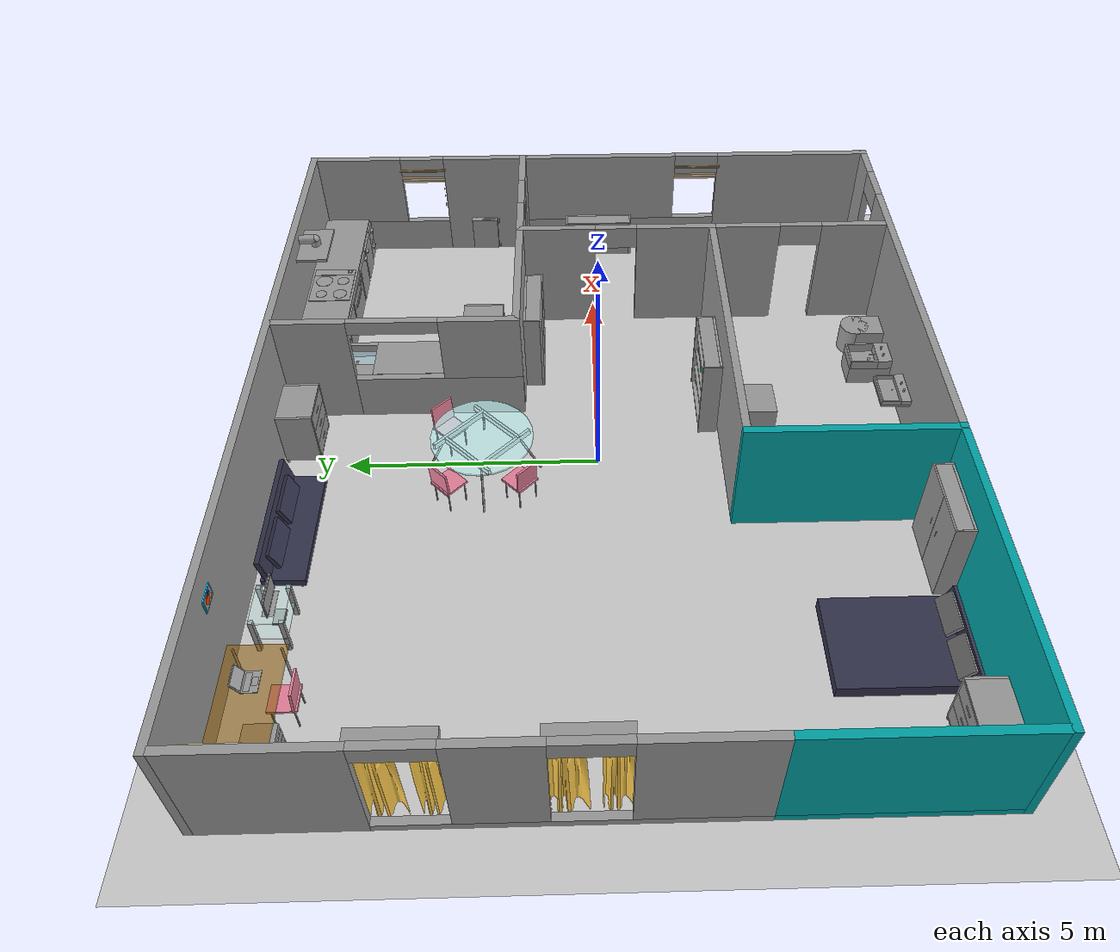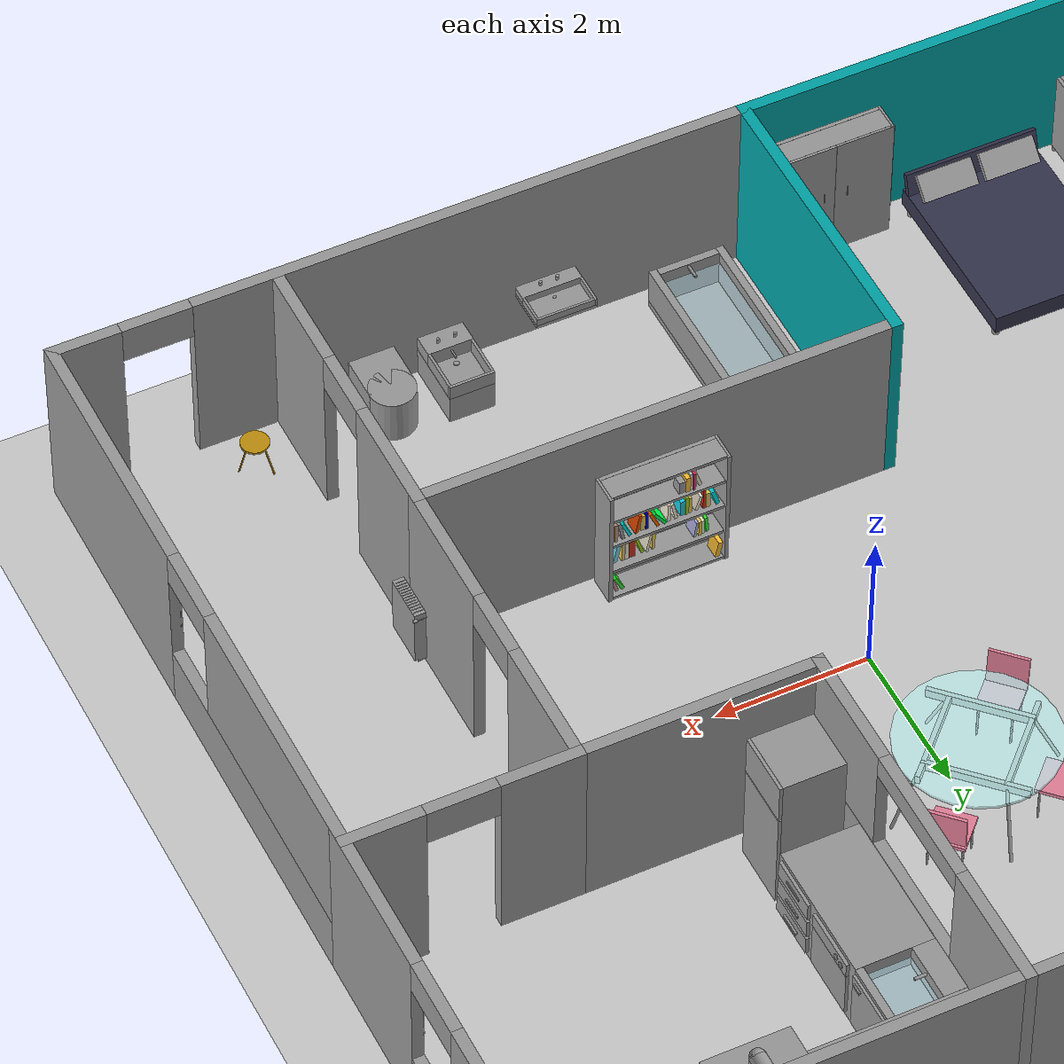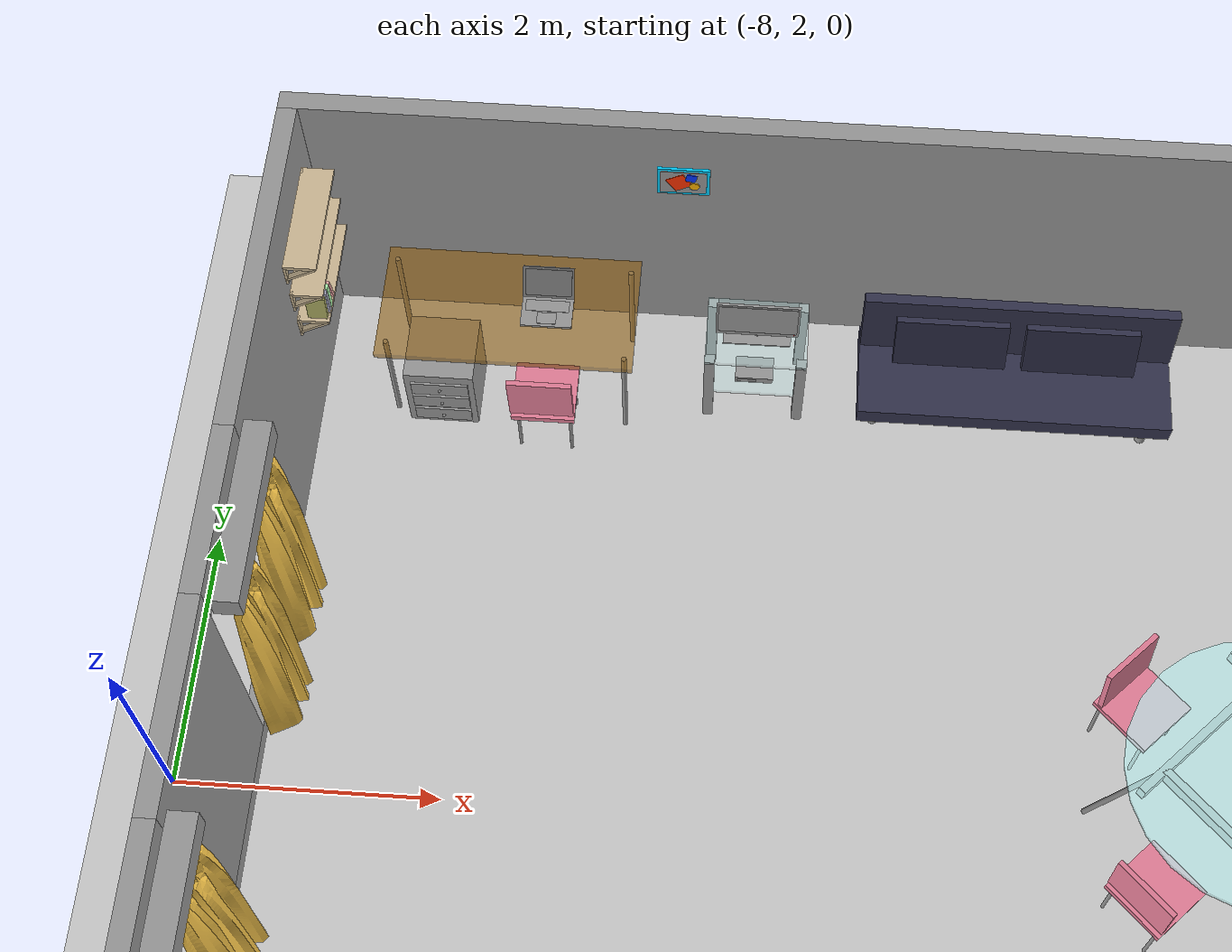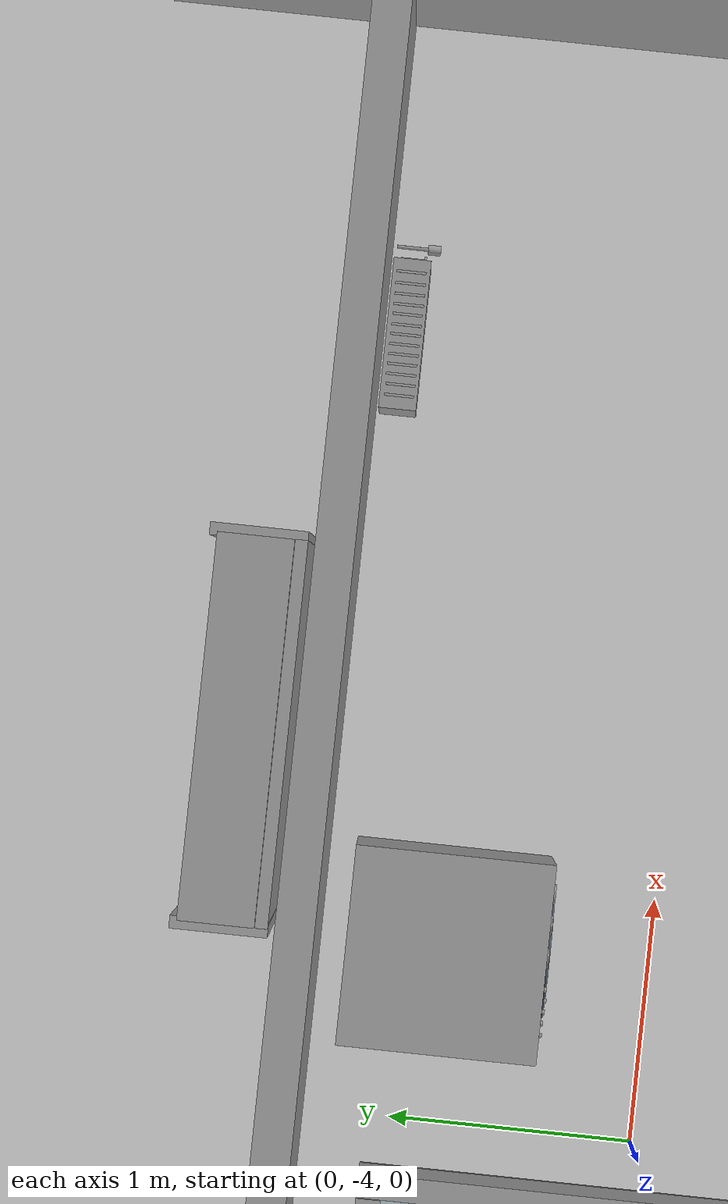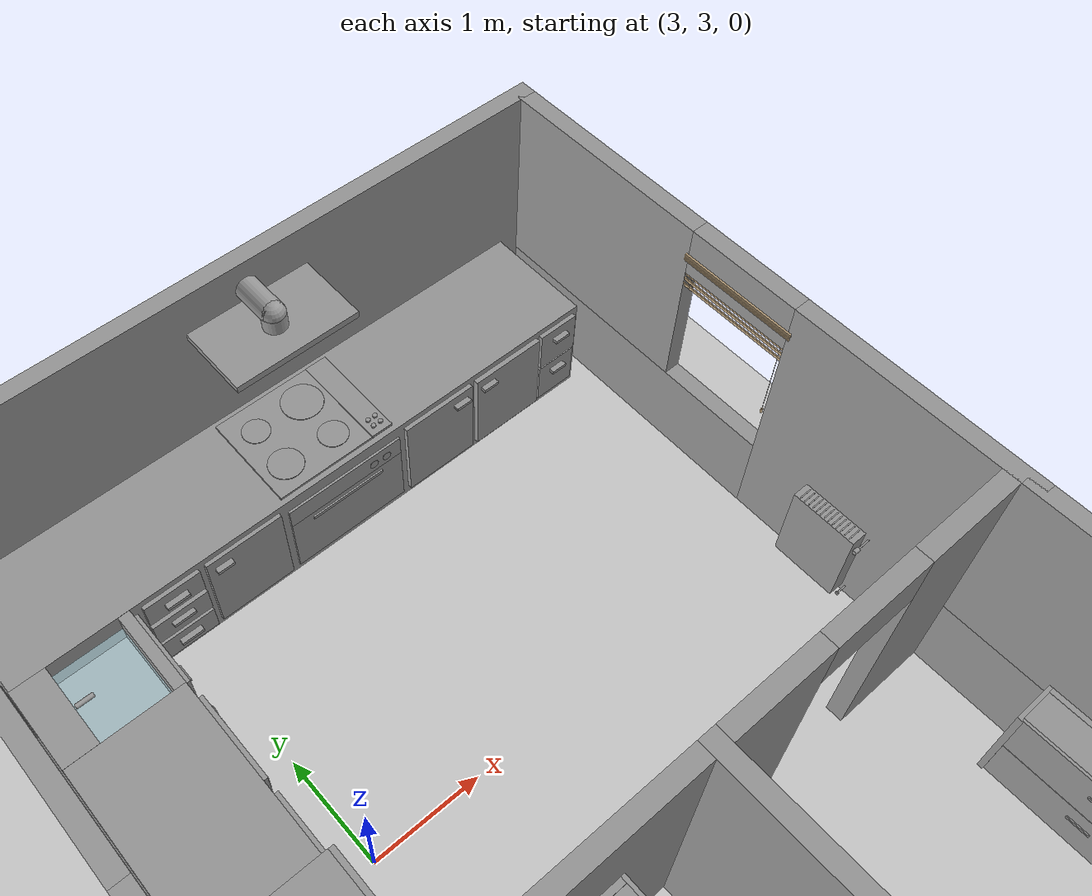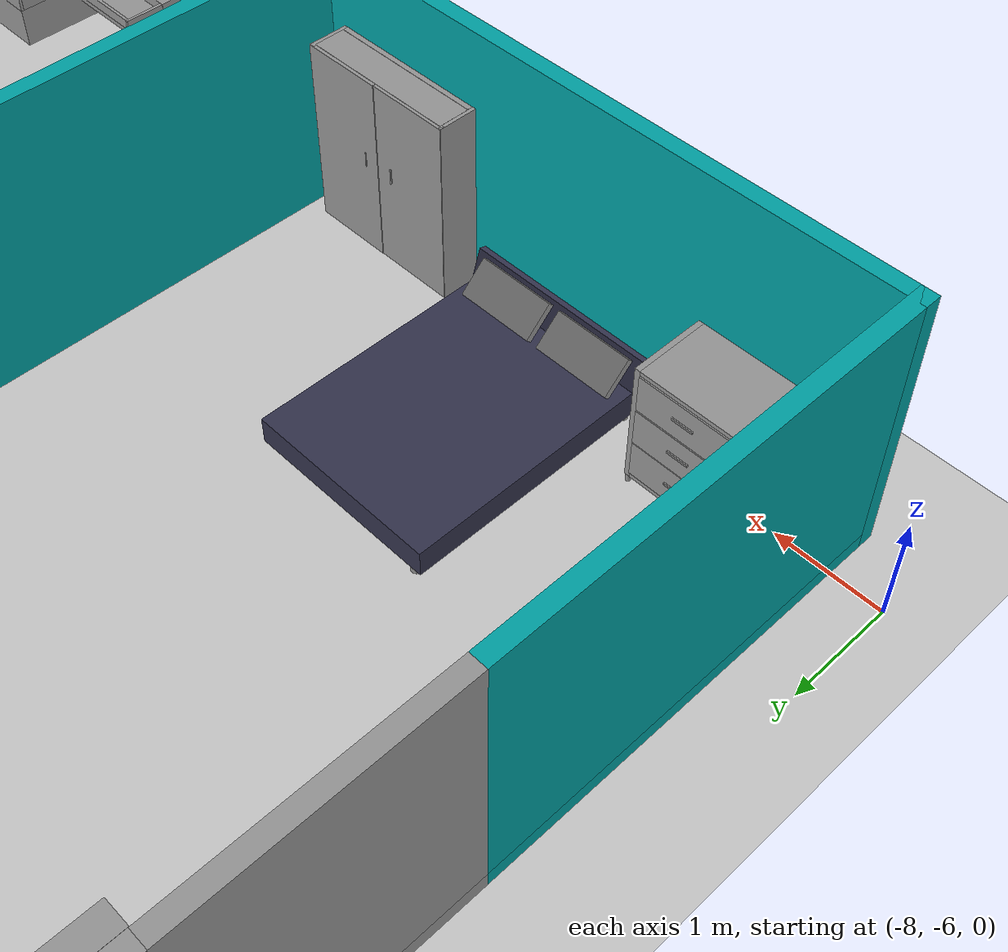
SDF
<sdf version="1.7">
 <world name="default">
  <light name="sun" type="directional">
   <pose>0 0 10 0 -0 0</pose>
   <diffuse>0.8 0.8 0.8 1</diffuse>
   <specular>0.2 0.2 0.2 1</specular>
   <attenuation>
    <range>1000</range>
    <constant>0.9</constant>
    <linear>0.01</linear>
    <quadratic>0.001</quadratic>
   </attenuation>
   <direction>-0.5 0.1 -0.9</direction>
   <spot><inner_angle>0</inner_angle><outer_angle>0</outer_angle><falloff>0</falloff></spot>
  </light>
  <model name="ground_plane">
   <static>1</static>
   <link name="link">
    <collision name="collision">
     <geometry><plane><normal>0 0 1</normal><size>100 100</size></plane></geometry>
     <surface>
      <contact><collide_bitmask>65535</collide_bitmask></contact>
      <friction><ode><mu>100</mu><mu2>50</mu2></ode></friction>
     </surface>
    </collision>
    <visual name="visual">
     <cast_shadows>0</cast_shadows>
     <geometry><plane><normal>0 0 1</normal><size>100 100</size></plane></geometry>
     <material>
      <script><uri>file://media/materials/scripts/gazebo.material</uri><name>Gazebo/Grey</name></script>
     </material>
    </visual>
   </link>
  </model>
  <gravity>0 0 -9.8</gravity>
  <magnetic_field>6e-06 2.3e-05 -4.2e-05</magnetic_field>
  <atmosphere type="adiabatic"/>
  <physics type="ode">
   <max_step_size>0.001</max_step_size>
   <real_time_factor>1</real_time_factor>
   <real_time_update_rate>1000</real_time_update_rate>
  </physics>
  <scene><ambient>0.4 0.4 0.4 1</ambient><background>0.7 0.7 0.7 1</background><shadows>1</shadows></scene>
  <spherical_coordinates>
   <surface_model>EARTH_WGS84</surface_model>
   <latitude_deg>0</latitude_deg>
   <longitude_deg>0</longitude_deg>
   <elevation>0</elevation>
   <heading_deg>0</heading_deg>
  </spherical_coordinates>
  <model name="my_building_p4">
   <link name="Wall_27">
    <pose>0 3.46508 0 0 -0 3.14159</pose>
    <visual name="Wall_27_Visual">
     <pose>0 0 1.25 0 -0 0</pose>
     <geometry><box><size>15 0.15 2.5</size></box></geometry>
     <material>
      <script><uri>file://media/materials/scripts/gazebo.material</uri><name>Gazebo/Grey</name></script>
      <ambient>1 1 1 1</ambient>
      <shader type="pixel"/>
     </material>
     <meta><layer>0</layer></meta>
    </visual>
    <collision name="Wall_27_Collision">
     <pose>0 0 1.25 0 -0 0</pose>
     <geometry><box><size>15 0.15 2.5</size></box></geometry>
     <surface>
      <friction>
       <ode><mu>1</mu><mu2>1</mu2><fdir1>0 0 0</fdir1><slip1>0</slip1><slip2>0</slip2></ode>
       <torsional>
        <coefficient>1</coefficient>
        <patch_radius>0</patch_radius>
        <surface_radius>0</surface_radius>
        <use_patch_radius>1</use_patch_radius>
        <ode><slip>0</slip></ode>
       </torsional>
      </friction>
      <bounce><restitution_coefficient>0</restitution_coefficient><threshold>1e+06</threshold></bounce>
      <contact>
       <collide_without_contact>0</collide_without_contact>
       <collide_without_contact_bitmask>1</collide_without_contact_bitmask>
       <collide_bitmask>1</collide_bitmask>
       <ode>
        <soft_cfm>0</soft_cfm>
        <soft_erp>0.2</soft_erp>
        <kp>1e+13</kp>
        <kd>1</kd>
        <max_vel>0.01</max_vel>
        <min_depth>0</min_depth>
       </ode>
       <bullet>
        <split_impulse>1</split_impulse>
        <split_impulse_penetration_threshold>-0.01</split_impulse_penetration_threshold>
        <soft_cfm>0</soft_cfm>
        <soft_erp>0.2</soft_erp>
        <kp>1e+13</kp>
        <kd>1</kd>
       </bullet>
      </contact>
     </surface>
    </collision>
   </link>
   <link name="Wall_28">
    <pose>-7.42497 -2.95624 0 0 0 -1.5708</pose>
    <inertial>
     <mass>1</mass>
     <inertia><ixx>1</ixx><ixy>0</ixy><ixz>0</ixz><iyy>1</iyy><iyz>0</iyz><izz>1</izz></inertia>
    </inertial>
    <visual name="Wall_28_Visual_3">
     <pose>4.5 0 1.325 0 -0 0</pose>
     <geometry><box><size>4 0.15 2.35</size></box></geometry>
     <material>
      <script><uri>file://media/materials/scripts/gazebo.material</uri><name>Gazebo/Grey</name></script>
      <ambient>0 0.647 0.655 1</ambient>
      <shader type="pixel"><normal_map>__default__</normal_map></shader>
      <diffuse>0 0.647 0.655 1</diffuse>
      <specular>0.01 0.01 0.01 1</specular>
      <emissive>0 0 0 1</emissive>
     </material>
     <meta><layer>0</layer></meta>
    </visual>
    <visual name="Wall_28_Visual_2">
     <pose>4.5 0 0.075 0 -0 0</pose>
     <geometry><box><size>4 0.15 0.15</size></box></geometry>
     <material>
      <script><uri>file://media/materials/scripts/gazebo.material</uri><name>Gazebo/Grey</name></script>
      <ambient>0 0.647 0.655 1</ambient>
      <shader type="pixel"><normal_map>__default__</normal_map></shader>
      <diffuse>0 0.647 0.655 1</diffuse>
      <specular>0.01 0.01 0.01 1</specular>
      <emissive>0 0 0 1</emissive>
     </material>
     <meta><layer>0</layer></meta>
    </visual>
    <visual name="Wall_28_Visual_1">
     <pose>-0.6 0 0.075 0 -0 0</pose>
     <geometry><box><size>6.2 0.15 0.15</size></box></geometry>
     <material>
      <script><uri>file://media/materials/scripts/gazebo.material</uri><name>Gazebo/Grey</name></script>
      <ambient>1 1 1 1</ambient>
      <shader type="pixel"><normal_map>__default__</normal_map></shader>
      <diffuse>0.7 0.7 0.7 1</diffuse>
      <specular>0.01 0.01 0.01 1</specular>
      <emissive>0 0 0 1</emissive>
     </material>
     <meta><layer>0</layer></meta>
    </visual>
    <visual name="Wall_28_Visual_5">
     <pose>-1.663 0 1.325 0 -0 0</pose>
     <geometry><box><size>1.5 0.15 2.35</size></box></geometry>
     <material>
      <script><uri>file://media/materials/scripts/gazebo.material</uri><name>Gazebo/Grey</name></script>
      <ambient>1 1 1 1</ambient>
      <shader type="pixel"><normal_map>__default__</normal_map></shader>
      <diffuse>0.7 0.7 0.7 1</diffuse>
      <specular>0.01 0.01 0.01 1</specular>
      <emissive>0 0 0 1</emissive>
     </material>
     <meta><layer>0</layer></meta>
    </visual>
    <visual name="Wall_28_Visual_8">
     <pose>-3.038 0 2.325 0 -0 0</pose>
     <geometry><box><size>1.25 0.15 0.35</size></box></geometry>
     <material>
      <script><uri>file://media/materials/scripts/gazebo.material</uri><name>Gazebo/Grey</name></script>
      <ambient>1 1 1 1</ambient>
      <shader type="pixel"><normal_map>__default__</normal_map></shader>
      <diffuse>0.7 0.7 0.7 1</diffuse>
      <specular>0.01 0.01 0.01 1</specular>
      <emissive>0 0 0 1</emissive>
     </material>
     <meta><layer>0</layer></meta>
    </visual>
    <visual name="Wall_28_Visual_0">
     <pose>-5.012 0 1.25 0 -0 0</pose>
     <geometry><box><size>2.7 0.15 2.5</size></box></geometry>
     <material>
      <script><uri>file://media/materials/scripts/gazebo.material</uri><name>Gazebo/Grey</name></script>
      <ambient>1 1 1 1</ambient>
      <shader type="pixel"><normal_map>__default__</normal_map></shader>
      <diffuse>0.7 0.7 0.7 1</diffuse>
      <specular>0.01 0.01 0.01 1</specular>
      <emissive>0 0 0 1</emissive>
     </material>
     <meta><layer>0</layer></meta>
    </visual>
    <visual name="Wall_28_Visual_6">
     <pose>-0.288 0 2.325 0 -0 0</pose>
     <geometry><box><size>1.25 0.15 0.35</size></box></geometry>
     <material>
      <script><uri>file://media/materials/scripts/gazebo.material</uri><name>Gazebo/Grey</name></script>
      <ambient>1 1 1 1</ambient>
      <shader type="pixel"><normal_map>__default__</normal_map></shader>
      <diffuse>0.7 0.7 0.7 1</diffuse>
      <specular>0.01 0.01 0.01 1</specular>
      <emissive>0 0 0 1</emissive>
     </material>
     <meta><layer>0</layer></meta>
    </visual>
    <collision name="Wall_28_Collision_6">
     <pose>-0.288 0 2.325 0 -0 0</pose>
     <geometry><box><size>1.25 0.15 0.35</size></box></geometry>
     <surface>
      <friction>
       <ode><mu>1</mu><mu2>1</mu2><fdir1>0 0 0</fdir1><slip1>0</slip1><slip2>0</slip2></ode>
       <torsional>
        <coefficient>1</coefficient>
        <patch_radius>0</patch_radius>
        <surface_radius>0</surface_radius>
        <use_patch_radius>1</use_patch_radius>
        <ode><slip>0</slip></ode>
       </torsional>
      </friction>
      <bounce><restitution_coefficient>0</restitution_coefficient><threshold>1e+06</threshold></bounce>
      <contact>
       <collide_without_contact>0</collide_without_contact>
       <collide_without_contact_bitmask>1</collide_without_contact_bitmask>
       <collide_bitmask>1</collide_bitmask>
       <ode>
        <soft_cfm>0</soft_cfm>
        <soft_erp>0.2</soft_erp>
        <kp>1e+13</kp>
        <kd>1</kd>
        <max_vel>0.01</max_vel>
        <min_depth>0</min_depth>
       </ode>
       <bullet>
        <split_impulse>1</split_impulse>
        <split_impulse_penetration_threshold>-0.01</split_impulse_penetration_threshold>
        <soft_cfm>0</soft_cfm>
        <soft_erp>0.2</soft_erp>
        <kp>1e+13</kp>
        <kd>1</kd>
       </bullet>
      </contact>
     </surface>
    </collision>
    <collision name="Wall_28_Collision_8">
     <pose>-3.038 0 2.325 0 -0 0</pose>
     <geometry><box><size>1.25 0.15 0.35</size></box></geometry>
     <surface>
      <friction>
       <ode><mu>1</mu><mu2>1</mu2><fdir1>0 0 0</fdir1><slip1>0</slip1><slip2>0</slip2></ode>
       <torsional>
        <coefficient>1</coefficient>
        <patch_radius>0</patch_radius>
        <surface_radius>0</surface_radius>
        <use_patch_radius>1</use_patch_radius>
        <ode><slip>0</slip></ode>
       </torsional>
      </friction>
      <bounce><restitution_coefficient>0</restitution_coefficient><threshold>1e+06</threshold></bounce>
      <contact>
       <collide_without_contact>0</collide_without_contact>
       <collide_without_contact_bitmask>1</collide_without_contact_bitmask>
       <collide_bitmask>1</collide_bitmask>
       <ode>
        <soft_cfm>0</soft_cfm>
        <soft_erp>0.2</soft_erp>
        <kp>1e+13</kp>
        <kd>1</kd>
        <max_vel>0.01</max_vel>
        <min_depth>0</min_depth>
       </ode>
       <bullet>
        <split_impulse>1</split_impulse>
        <split_impulse_penetration_threshold>-0.01</split_impulse_penetration_threshold>
        <soft_cfm>0</soft_cfm>
        <soft_erp>0.2</soft_erp>
        <kp>1e+13</kp>
        <kd>1</kd>
       </bullet>
      </contact>
     </surface>
    </collision>
    <collision name="Wall_28_Collision_0">
     <pose>-5.012 0 1.25 0 -0 0</pose>
     <geometry><box><size>2.7 0.15 2.5</size></box></geometry>
     <surface>
      <friction>
       <ode><mu>1</mu><mu2>1</mu2><fdir1>0 0 0</fdir1><slip1>0</slip1><slip2>0</slip2></ode>
       <torsional>
        <coefficient>1</coefficient>
        <patch_radius>0</patch_radius>
        <surface_radius>0</surface_radius>
        <use_patch_radius>1</use_patch_radius>
        <ode><slip>0</slip></ode>
       </torsional>
      </friction>
      <bounce><restitution_coefficient>0</restitution_coefficient><threshold>1e+06</threshold></bounce>
      <contact>
       <collide_without_contact>0</collide_without_contact>
       <collide_without_contact_bitmask>1</collide_without_contact_bitmask>
       <collide_bitmask>1</collide_bitmask>
       <ode>
        <soft_cfm>0</soft_cfm>
        <soft_erp>0.2</soft_erp>
        <kp>1e+13</kp>
        <kd>1</kd>
        <max_vel>0.01</max_vel>
        <min_depth>0</min_depth>
       </ode>
       <bullet>
        <split_impulse>1</split_impulse>
        <split_impulse_penetration_threshold>-0.01</split_impulse_penetration_threshold>
        <soft_cfm>0</soft_cfm>
        <soft_erp>0.2</soft_erp>
        <kp>1e+13</kp>
        <kd>1</kd>
       </bullet>
      </contact>
     </surface>
    </collision>
    <collision name="Wall_28_Collision_1">
     <pose>-0.6 0 0.075 0 -0 0</pose>
     <geometry><box><size>6.2 0.15 0.15</size></box></geometry>
     <surface>
      <friction>
       <ode><mu>1</mu><mu2>1</mu2><fdir1>0 0 0</fdir1><slip1>0</slip1><slip2>0</slip2></ode>
       <torsional>
        <coefficient>1</coefficient>
        <patch_radius>0</patch_radius>
        <surface_radius>0</surface_radius>
        <use_patch_radius>1</use_patch_radius>
        <ode><slip>0</slip></ode>
       </torsional>
      </friction>
      <bounce><restitution_coefficient>0</restitution_coefficient><threshold>1e+06</threshold></bounce>
      <contact>
       <collide_without_contact>0</collide_without_contact>
       <collide_without_contact_bitmask>1</collide_without_contact_bitmask>
       <collide_bitmask>1</collide_bitmask>
       <ode>
        <soft_cfm>0</soft_cfm>
        <soft_erp>0.2</soft_erp>
        <kp>1e+13</kp>
        <kd>1</kd>
        <max_vel>0.01</max_vel>
        <min_depth>0</min_depth>
       </ode>
       <bullet>
        <split_impulse>1</split_impulse>
        <split_impulse_penetration_threshold>-0.01</split_impulse_penetration_threshold>
        <soft_cfm>0</soft_cfm>
        <soft_erp>0.2</soft_erp>
        <kp>1e+13</kp>
        <kd>1</kd>
       </bullet>
      </contact>
     </surface>
    </collision>
    <collision name="Wall_28_Collision_3">
     <pose>4.5 0 1.325 0 -0 0</pose>
     <geometry><box><size>4 0.15 2.35</size></box></geometry>
     <surface>
      <friction>
       <ode><mu>1</mu><mu2>1</mu2><fdir1>0 0 0</fdir1><slip1>0</slip1><slip2>0</slip2></ode>
       <torsional>
        <coefficient>1</coefficient>
        <patch_radius>0</patch_radius>
        <surface_radius>0</surface_radius>
        <use_patch_radius>1</use_patch_radius>
        <ode><slip>0</slip></ode>
       </torsional>
      </friction>
      <bounce><restitution_coefficient>0</restitution_coefficient><threshold>1e+06</threshold></bounce>
      <contact>
       <collide_without_contact>0</collide_without_contact>
       <collide_without_contact_bitmask>1</collide_without_contact_bitmask>
       <collide_bitmask>1</collide_bitmask>
       <ode>
        <soft_cfm>0</soft_cfm>
        <soft_erp>0.2</soft_erp>
        <kp>1e+13</kp>
        <kd>1</kd>
        <max_vel>0.01</max_vel>
        <min_depth>0</min_depth>
       </ode>
       <bullet>
        <split_impulse>1</split_impulse>
        <split_impulse_penetration_threshold>-0.01</split_impulse_penetration_threshold>
        <soft_cfm>0</soft_cfm>
        <soft_erp>0.2</soft_erp>
        <kp>1e+13</kp>
        <kd>1</kd>
       </bullet>
      </contact>
     </surface>
    </collision>
    <collision name="Wall_28_Collision_5">
     <pose>-1.663 0 1.325 0 -0 0</pose>
     <geometry><box><size>1.5 0.15 2.35</size></box></geometry>
     <surface>
      <friction>
       <ode><mu>1</mu><mu2>1</mu2><fdir1>0 0 0</fdir1><slip1>0</slip1><slip2>0</slip2></ode>
       <torsional>
        <coefficient>1</coefficient>
        <patch_radius>0</patch_radius>
        <surface_radius>0</surface_radius>
        <use_patch_radius>1</use_patch_radius>
        <ode><slip>0</slip></ode>
       </torsional>
      </friction>
      <bounce><restitution_coefficient>0</restitution_coefficient><threshold>1e+06</threshold></bounce>
      <contact>
       <collide_without_contact>0</collide_without_contact>
       <collide_without_contact_bitmask>1</collide_without_contact_bitmask>
       <collide_bitmask>1</collide_bitmask>
       <ode>
        <soft_cfm>0</soft_cfm>
        <soft_erp>0.2</soft_erp>
        <kp>1e+13</kp>
        <kd>1</kd>
        <max_vel>0.01</max_vel>
        <min_depth>0</min_depth>
       </ode>
       <bullet>
        <split_impulse>1</split_impulse>
        <split_impulse_penetration_threshold>-0.01</split_impulse_penetration_threshold>
        <soft_cfm>0</soft_cfm>
        <soft_erp>0.2</soft_erp>
        <kp>1e+13</kp>
        <kd>1</kd>
       </bullet>
      </contact>
     </surface>
    </collision>
    <collision name="Wall_28_Collision_2">
     <pose>4.5 0 0.075 0 -0 0</pose>
     <geometry><box><size>4 0.15 0.15</size></box></geometry>
     <surface>
      <friction>
       <ode><mu>1</mu><mu2>1</mu2><fdir1>0 0 0</fdir1><slip1>0</slip1><slip2>0</slip2></ode>
       <torsional>
        <coefficient>1</coefficient>
        <patch_radius>0</patch_radius>
        <surface_radius>0</surface_radius>
        <use_patch_radius>1</use_patch_radius>
        <ode><slip>0</slip></ode>
       </torsional>
      </friction>
      <bounce><restitution_coefficient>0</restitution_coefficient><threshold>1e+06</threshold></bounce>
      <contact>
       <collide_without_contact>0</collide_without_contact>
       <collide_without_contact_bitmask>1</collide_without_contact_bitmask>
       <collide_bitmask>1</collide_bitmask>
       <ode>
        <soft_cfm>0</soft_cfm>
        <soft_erp>0.2</soft_erp>
        <kp>1e+13</kp>
        <kd>1</kd>
        <max_vel>0.01</max_vel>
        <min_depth>0</min_depth>
       </ode>
       <bullet>
        <split_impulse>1</split_impulse>
        <split_impulse_penetration_threshold>-0.01</split_impulse_penetration_threshold>
        <soft_cfm>0</soft_cfm>
        <soft_erp>0.2</soft_erp>
        <kp>1e+13</kp>
        <kd>1</kd>
       </bullet>
      </contact>
     </surface>
    </collision>
   </link>
   <link name="Wall_28_clone">
    <pose>-7.42533 -5.43108 0 0 0 -1.5708</pose>
    <inertial>
     <mass>1</mass>
     <inertia><ixx>1</ixx><ixy>0</ixy><ixz>0</ixz><iyy>1</iyy><iyz>0</iyz><izz>1</izz></inertia>
    </inertial>
    <visual name="Wall_28_Visual_5">
     <pose>-1.058 0 1.325 0 -0 0</pose>
     <geometry><box><size>2.16667 0.15 2.35</size></box></geometry>
     <material>
      <script><uri>file://media/materials/scripts/gazebo.material</uri><name>Gazebo/Grey</name></script>
      <ambient>1 1 1 1</ambient>
      <shader type="pixel"><normal_map>__default__</normal_map></shader>
      <diffuse>0.7 0.7 0.7 1</diffuse>
      <specular>0.01 0.01 0.01 1</specular>
      <emissive>0 0 0 1</emissive>
     </material>
     <meta><layer>0</layer></meta>
    </visual>
    <collision name="Wall_28_Collision_5">
     <pose>-1.058 0 1.325 0 -0 0</pose>
     <geometry><box><size>2.16667 0.15 2.35</size></box></geometry>
     <surface>
      <friction>
       <ode><mu>1</mu><mu2>1</mu2><fdir1>0 0 0</fdir1><slip1>0</slip1><slip2>0</slip2></ode>
       <torsional>
        <coefficient>1</coefficient>
        <patch_radius>0</patch_radius>
        <surface_radius>0</surface_radius>
        <use_patch_radius>1</use_patch_radius>
        <ode><slip>0</slip></ode>
       </torsional>
      </friction>
      <bounce><restitution_coefficient>0</restitution_coefficient><threshold>1e+06</threshold></bounce>
      <contact>
       <collide_without_contact>0</collide_without_contact>
       <collide_without_contact_bitmask>1</collide_without_contact_bitmask>
       <collide_bitmask>1</collide_bitmask>
       <ode>
        <soft_cfm>0</soft_cfm>
        <soft_erp>0.2</soft_erp>
        <kp>1e+13</kp>
        <kd>1</kd>
        <max_vel>0.01</max_vel>
        <min_depth>0</min_depth>
       </ode>
       <bullet>
        <split_impulse>1</split_impulse>
        <split_impulse_penetration_threshold>-0.01</split_impulse_penetration_threshold>
        <soft_cfm>0</soft_cfm>
        <soft_erp>0.2</soft_erp>
        <kp>1e+13</kp>
        <kd>1</kd>
       </bullet>
      </contact>
     </surface>
    </collision>
   </link>
   <link name="Wall_29">
    <pose>-4.5 -9.38492 0 0 -0 0</pose>
    <inertial>
     <mass>1</mass>
     <inertia><ixx>1</ixx><ixy>0</ixy><ixz>0</ixz><iyy>1</iyy><iyz>0</iyz><izz>1</izz></inertia>
    </inertial>
    <visual name="Wall_29_Visual">
     <pose>0 0 1.25 0 -0 0</pose>
     <geometry><box><size>6 0.15 2.5</size></box></geometry>
     <material>
      <script><uri>file://media/materials/scripts/gazebo.material</uri><name>Gazebo/Grey</name></script>
      <ambient>0 0.647 0.655 1</ambient>
      <shader type="pixel"><normal_map>__default__</normal_map></shader>
      <diffuse>0 0.647 0.655 1</diffuse>
      <specular>0.01 0.01 0.01 1</specular>
      <emissive>0 0 0 1</emissive>
     </material>
     <meta><layer>0</layer></meta>
    </visual>
    <collision name="Wall_29_Collision">
     <pose>0 0 1.25 0 -0 0</pose>
     <geometry><box><size>6 0.15 2.5</size></box></geometry>
     <surface>
      <friction>
       <ode><mu>1</mu><mu2>1</mu2><fdir1>0 0 0</fdir1><slip1>0</slip1><slip2>0</slip2></ode>
       <torsional>
        <coefficient>1</coefficient>
        <patch_radius>0</patch_radius>
        <surface_radius>0</surface_radius>
        <use_patch_radius>1</use_patch_radius>
        <ode><slip>0</slip></ode>
       </torsional>
      </friction>
      <bounce><restitution_coefficient>0</restitution_coefficient><threshold>1e+06</threshold></bounce>
      <contact>
       <collide_without_contact>0</collide_without_contact>
       <collide_without_contact_bitmask>1</collide_without_contact_bitmask>
       <collide_bitmask>1</collide_bitmask>
       <ode>
        <soft_cfm>0</soft_cfm>
        <soft_erp>0.2</soft_erp>
        <kp>1e+13</kp>
        <kd>1</kd>
        <max_vel>0.01</max_vel>
        <min_depth>0</min_depth>
       </ode>
       <bullet>
        <split_impulse>1</split_impulse>
        <split_impulse_penetration_threshold>-0.01</split_impulse_penetration_threshold>
        <soft_cfm>0</soft_cfm>
        <soft_erp>0.2</soft_erp>
        <kp>1e+13</kp>
        <kd>1</kd>
       </bullet>
      </contact>
     </surface>
    </collision>
   </link>
   <link name="Wall_30">
    <pose>-1.57502 -7.45997 0 0 -0 1.57081</pose>
    <inertial>
     <mass>1</mass>
     <inertia><ixx>1</ixx><ixy>0</ixy><ixz>0</ixz><iyy>1</iyy><iyz>0</iyz><izz>1</izz></inertia>
    </inertial>
    <visual name="Wall_30_Visual">
     <pose>0 0 1.25 0 -0 0</pose>
     <geometry><box><size>3.99989 0.15 2.5</size></box></geometry>
     <material>
      <script><uri>file://media/materials/scripts/gazebo.material</uri><name>Gazebo/Grey</name></script>
      <ambient>0 0.647 0.655 1</ambient>
      <shader type="pixel"><normal_map>__default__</normal_map></shader>
      <diffuse>0 0.647 0.655 1</diffuse>
      <specular>0.01 0.01 0.01 1</specular>
      <emissive>0 0 0 1</emissive>
     </material>
     <meta><layer>0</layer></meta>
    </visual>
    <collision name="Wall_30_Collision">
     <pose>0 0 1.25 0 -0 0</pose>
     <geometry><box><size>3.99989 0.15 2.5</size></box></geometry>
     <surface>
      <friction>
       <ode><mu>1</mu><mu2>1</mu2><fdir1>0 0 0</fdir1><slip1>0</slip1><slip2>0</slip2></ode>
       <torsional>
        <coefficient>1</coefficient>
        <patch_radius>0</patch_radius>
        <surface_radius>0</surface_radius>
        <use_patch_radius>1</use_patch_radius>
        <ode><slip>0</slip></ode>
       </torsional>
      </friction>
      <bounce><restitution_coefficient>0</restitution_coefficient><threshold>1e+06</threshold></bounce>
      <contact>
       <collide_without_contact>0</collide_without_contact>
       <collide_without_contact_bitmask>1</collide_without_contact_bitmask>
       <collide_bitmask>1</collide_bitmask>
       <ode>
        <soft_cfm>0</soft_cfm>
        <soft_erp>0.2</soft_erp>
        <kp>1e+13</kp>
        <kd>1</kd>
        <max_vel>0.01</max_vel>
        <min_depth>0</min_depth>
       </ode>
       <bullet>
        <split_impulse>1</split_impulse>
        <split_impulse_penetration_threshold>-0.01</split_impulse_penetration_threshold>
        <soft_cfm>0</soft_cfm>
        <soft_erp>0.2</soft_erp>
        <kp>1e+13</kp>
        <kd>1</kd>
       </bullet>
      </contact>
     </surface>
    </collision>
   </link>
   <link name="Wall_32">
    <pose>2.925 -9.38492 0 0 -0 0</pose>
    <inertial>
     <mass>1</mass>
     <inertia><ixx>1</ixx><ixy>0</ixy><ixz>0</ixz><iyy>1</iyy><iyz>0</iyz><izz>1</izz></inertia>
    </inertial>
    <visual name="Wall_32_Visual_1">
     <pose>4.11059 0 1.25 0 -0 0</pose>
     <geometry><box><size>0.928826 0.15 2.5</size></box></geometry>
     <material>
      <script><uri>file://media/materials/scripts/gazebo.material</uri><name>Gazebo/Grey</name></script>
      <ambient>1 1 1 1</ambient>
      <shader type="pixel"><normal_map>__default__</normal_map></shader>
      <diffuse>0.7 0.7 0.7 1</diffuse>
      <specular>0.01 0.01 0.01 1</specular>
      <emissive>0 0 0 1</emissive>
     </material>
     <meta><layer>0</layer></meta>
    </visual>
    <visual name="Wall_32_Visual_2">
     <pose>3.19617 0 2.25 0 -0 0</pose>
     <geometry><box><size>0.9 0.15 0.5</size></box></geometry>
     <material>
      <script><uri>file://media/materials/scripts/gazebo.material</uri><name>Gazebo/Grey</name></script>
      <ambient>1 1 1 1</ambient>
      <shader type="pixel"><normal_map>__default__</normal_map></shader>
      <diffuse>0.7 0.7 0.7 1</diffuse>
      <specular>0.01 0.01 0.01 1</specular>
      <emissive>0 0 0 1</emissive>
     </material>
     <meta><layer>0</layer></meta>
    </visual>
    <visual name="Wall_32_Visual_0">
     <pose>-0.84 0 1.25 0 -0 0</pose>
     <geometry><box><size>7.17 0.15 2.5</size></box></geometry>
     <material>
      <script><uri>file://media/materials/scripts/gazebo.material</uri><name>Gazebo/Grey</name></script>
      <ambient>1 1 1 1</ambient>
      <shader type="pixel"><normal_map>__default__</normal_map></shader>
      <diffuse>0.7 0.7 0.7 1</diffuse>
      <specular>0.01 0.01 0.01 1</specular>
      <emissive>0 0 0 1</emissive>
     </material>
     <meta><layer>0</layer></meta>
    </visual>
    <collision name="Wall_32_Collision_1">
     <pose>4.11059 0 1.25 0 -0 0</pose>
     <geometry><box><size>0.928826 0.15 2.5</size></box></geometry>
     <surface>
      <friction>
       <ode><mu>1</mu><mu2>1</mu2><fdir1>0 0 0</fdir1><slip1>0</slip1><slip2>0</slip2></ode>
       <torsional>
        <coefficient>1</coefficient>
        <patch_radius>0</patch_radius>
        <surface_radius>0</surface_radius>
        <use_patch_radius>1</use_patch_radius>
        <ode><slip>0</slip></ode>
       </torsional>
      </friction>
      <bounce><restitution_coefficient>0</restitution_coefficient><threshold>1e+06</threshold></bounce>
      <contact>
       <collide_without_contact>0</collide_without_contact>
       <collide_without_contact_bitmask>1</collide_without_contact_bitmask>
       <collide_bitmask>1</collide_bitmask>
       <ode>
        <soft_cfm>0</soft_cfm>
        <soft_erp>0.2</soft_erp>
        <kp>1e+13</kp>
        <kd>1</kd>
        <max_vel>0.01</max_vel>
        <min_depth>0</min_depth>
       </ode>
       <bullet>
        <split_impulse>1</split_impulse>
        <split_impulse_penetration_threshold>-0.01</split_impulse_penetration_threshold>
        <soft_cfm>0</soft_cfm>
        <soft_erp>0.2</soft_erp>
        <kp>1e+13</kp>
        <kd>1</kd>
       </bullet>
      </contact>
     </surface>
    </collision>
    <collision name="Wall_32_Collision_0">
     <pose>-0.84 0 1.25 0 -0 0</pose>
     <geometry><box><size>7.17 0.15 2.5</size></box></geometry>
     <surface>
      <friction>
       <ode><mu>1</mu><mu2>1</mu2><fdir1>0 0 0</fdir1><slip1>0</slip1><slip2>0</slip2></ode>
       <torsional>
        <coefficient>1</coefficient>
        <patch_radius>0</patch_radius>
        <surface_radius>0</surface_radius>
        <use_patch_radius>1</use_patch_radius>
        <ode><slip>0</slip></ode>
       </torsional>
      </friction>
      <bounce><restitution_coefficient>0</restitution_coefficient><threshold>1e+06</threshold></bounce>
      <contact>
       <collide_without_contact>0</collide_without_contact>
       <collide_without_contact_bitmask>1</collide_without_contact_bitmask>
       <collide_bitmask>1</collide_bitmask>
       <ode>
        <soft_cfm>0</soft_cfm>
        <soft_erp>0.2</soft_erp>
        <kp>1e+13</kp>
        <kd>1</kd>
        <max_vel>0.01</max_vel>
        <min_depth>0</min_depth>
       </ode>
       <bullet>
        <split_impulse>1</split_impulse>
        <split_impulse_penetration_threshold>-0.01</split_impulse_penetration_threshold>
        <soft_cfm>0</soft_cfm>
        <soft_erp>0.2</soft_erp>
        <kp>1e+13</kp>
        <kd>1</kd>
       </bullet>
      </contact>
     </surface>
    </collision>
    <collision name="Wall_32_Collision_2">
     <pose>3.19617 0 2.25 0 -0 0</pose>
     <geometry><box><size>0.9 0.15 0.5</size></box></geometry>
     <surface>
      <friction>
       <ode><mu>1</mu><mu2>1</mu2><fdir1>0 0 0</fdir1><slip1>0</slip1><slip2>0</slip2></ode>
       <torsional>
        <coefficient>1</coefficient>
        <patch_radius>0</patch_radius>
        <surface_radius>0</surface_radius>
        <use_patch_radius>1</use_patch_radius>
        <ode><slip>0</slip></ode>
       </torsional>
      </friction>
      <bounce><restitution_coefficient>0</restitution_coefficient><threshold>1e+06</threshold></bounce>
      <contact>
       <collide_without_contact>0</collide_without_contact>
       <collide_without_contact_bitmask>1</collide_without_contact_bitmask>
       <collide_bitmask>1</collide_bitmask>
       <ode>
        <soft_cfm>0</soft_cfm>
        <soft_erp>0.2</soft_erp>
        <kp>1e+13</kp>
        <kd>1</kd>
        <max_vel>0.01</max_vel>
        <min_depth>0</min_depth>
       </ode>
       <bullet>
        <split_impulse>1</split_impulse>
        <split_impulse_penetration_threshold>-0.01</split_impulse_penetration_threshold>
        <soft_cfm>0</soft_cfm>
        <soft_erp>0.2</soft_erp>
        <kp>1e+13</kp>
        <kd>1</kd>
       </bullet>
      </contact>
     </surface>
    </collision>
   </link>
   <link name="Wall_36">
    <pose>1.49997 -5.53503 0 0 -0 0</pose>
    <inertial>
     <mass>1</mass>
     <inertia><ixx>1</ixx><ixy>0</ixy><ixz>0</ixz><iyy>1</iyy><iyz>0</iyz><izz>1</izz></inertia>
    </inertial>
    <visual name="Wall_36_Visual">
     <pose>0 0 1.25 0 -0 0</pose>
     <geometry><box><size>6 0.15 2.5</size></box></geometry>
     <material>
      <script><uri>file://media/materials/scripts/gazebo.material</uri><name>Gazebo/Grey</name></script>
      <ambient>1 1 1 1</ambient>
      <shader type="pixel"><normal_map>__default__</normal_map></shader>
      <diffuse>0.7 0.7 0.7 1</diffuse>
      <specular>0.01 0.01 0.01 1</specular>
      <emissive>0 0 0 1</emissive>
     </material>
     <meta><layer>0</layer></meta>
    </visual>
    <collision name="Wall_36_Collision">
     <pose>0 0 1.25 0 -0 0</pose>
     <geometry><box><size>6 0.15 2.5</size></box></geometry>
     <surface>
      <friction>
       <ode><mu>1</mu><mu2>1</mu2><fdir1>0 0 0</fdir1><slip1>0</slip1><slip2>0</slip2></ode>
       <torsional>
        <coefficient>1</coefficient>
        <patch_radius>0</patch_radius>
        <surface_radius>0</surface_radius>
        <use_patch_radius>1</use_patch_radius>
        <ode><slip>0</slip></ode>
       </torsional>
      </friction>
      <bounce><restitution_coefficient>0</restitution_coefficient><threshold>1e+06</threshold></bounce>
      <contact>
       <collide_without_contact>0</collide_without_contact>
       <collide_without_contact_bitmask>1</collide_without_contact_bitmask>
       <collide_bitmask>1</collide_bitmask>
       <ode>
        <soft_cfm>0</soft_cfm>
        <soft_erp>0.2</soft_erp>
        <kp>1e+13</kp>
        <kd>1</kd>
        <max_vel>0.01</max_vel>
        <min_depth>0</min_depth>
       </ode>
       <bullet>
        <split_impulse>1</split_impulse>
        <split_impulse_penetration_threshold>-0.01</split_impulse_penetration_threshold>
        <soft_cfm>0</soft_cfm>
        <soft_erp>0.2</soft_erp>
        <kp>1e+13</kp>
        <kd>1</kd>
       </bullet>
      </contact>
     </surface>
    </collision>
   </link>
   <link name="Wall_37">
    <pose>4.57498 -7.45997 0 0 0 -1.57079</pose>
    <visual name="Wall_37_Visual_0">
     <pose>-1.22294 0 1.25 0 -0 0</pose>
     <geometry><box><size>1.55413 0.15 2.5</size></box></geometry>
     <material>
      <script><uri>file://media/materials/scripts/gazebo.material</uri><name>Gazebo/Grey</name></script>
      <ambient>1 1 1 1</ambient>
      <shader type="pixel"/>
     </material>
     <meta><layer>0</layer></meta>
    </visual>
    <visual name="Wall_37_Visual_2">
     <pose>0.004129 0 2.25 0 -0 0</pose>
     <geometry><box><size>0.9 0.15 0.5</size></box></geometry>
     <material>
      <script><uri>file://media/materials/scripts/gazebo.material</uri><name>Gazebo/Grey</name></script>
      <ambient>1 1 1 1</ambient>
      <shader type="pixel"/>
     </material>
     <meta><layer>0</layer></meta>
    </visual>
    <visual name="Wall_37_Visual_1">
     <pose>1.22707 0 1.25 0 -0 0</pose>
     <geometry><box><size>1.54587 0.15 2.5</size></box></geometry>
     <material>
      <script><uri>file://media/materials/scripts/gazebo.material</uri><name>Gazebo/Grey</name></script>
      <ambient>1 1 1 1</ambient>
      <shader type="pixel"/>
     </material>
     <meta><layer>0</layer></meta>
    </visual>
    <collision name="Wall_37_Collision_0">
     <pose>-1.22294 0 1.25 0 -0 0</pose>
     <geometry><box><size>1.55413 0.15 2.5</size></box></geometry>
     <surface>
      <friction>
       <ode><mu>1</mu><mu2>1</mu2><fdir1>0 0 0</fdir1><slip1>0</slip1><slip2>0</slip2></ode>
       <torsional>
        <coefficient>1</coefficient>
        <patch_radius>0</patch_radius>
        <surface_radius>0</surface_radius>
        <use_patch_radius>1</use_patch_radius>
        <ode><slip>0</slip></ode>
       </torsional>
      </friction>
      <bounce><restitution_coefficient>0</restitution_coefficient><threshold>1e+06</threshold></bounce>
      <contact>
       <collide_without_contact>0</collide_without_contact>
       <collide_without_contact_bitmask>1</collide_without_contact_bitmask>
       <collide_bitmask>1</collide_bitmask>
       <ode>
        <soft_cfm>0</soft_cfm>
        <soft_erp>0.2</soft_erp>
        <kp>1e+13</kp>
        <kd>1</kd>
        <max_vel>0.01</max_vel>
        <min_depth>0</min_depth>
       </ode>
       <bullet>
        <split_impulse>1</split_impulse>
        <split_impulse_penetration_threshold>-0.01</split_impulse_penetration_threshold>
        <soft_cfm>0</soft_cfm>
        <soft_erp>0.2</soft_erp>
        <kp>1e+13</kp>
        <kd>1</kd>
       </bullet>
      </contact>
     </surface>
    </collision>
    <collision name="Wall_37_Collision_1">
     <pose>1.22707 0 1.25 0 -0 0</pose>
     <geometry><box><size>1.54587 0.15 2.5</size></box></geometry>
     <surface>
      <friction>
       <ode><mu>1</mu><mu2>1</mu2><fdir1>0 0 0</fdir1><slip1>0</slip1><slip2>0</slip2></ode>
       <torsional>
        <coefficient>1</coefficient>
        <patch_radius>0</patch_radius>
        <surface_radius>0</surface_radius>
        <use_patch_radius>1</use_patch_radius>
        <ode><slip>0</slip></ode>
       </torsional>
      </friction>
      <bounce><restitution_coefficient>0</restitution_coefficient><threshold>1e+06</threshold></bounce>
      <contact>
       <collide_without_contact>0</collide_without_contact>
       <collide_without_contact_bitmask>1</collide_without_contact_bitmask>
       <collide_bitmask>1</collide_bitmask>
       <ode>
        <soft_cfm>0</soft_cfm>
        <soft_erp>0.2</soft_erp>
        <kp>1e+13</kp>
        <kd>1</kd>
        <max_vel>0.01</max_vel>
        <min_depth>0</min_depth>
       </ode>
       <bullet>
        <split_impulse>1</split_impulse>
        <split_impulse_penetration_threshold>-0.01</split_impulse_penetration_threshold>
        <soft_cfm>0</soft_cfm>
        <soft_erp>0.2</soft_erp>
        <kp>1e+13</kp>
        <kd>1</kd>
       </bullet>
      </contact>
     </surface>
    </collision>
    <collision name="Wall_37_Collision_2">
     <pose>0.004129 0 2.25 0 -0 0</pose>
     <geometry><box><size>0.9 0.15 0.5</size></box></geometry>
     <surface>
      <friction>
       <ode><mu>1</mu><mu2>1</mu2><fdir1>0 0 0</fdir1><slip1>0</slip1><slip2>0</slip2></ode>
       <torsional>
        <coefficient>1</coefficient>
        <patch_radius>0</patch_radius>
        <surface_radius>0</surface_radius>
        <use_patch_radius>1</use_patch_radius>
        <ode><slip>0</slip></ode>
       </torsional>
      </friction>
      <bounce><restitution_coefficient>0</restitution_coefficient><threshold>1e+06</threshold></bounce>
      <contact>
       <collide_without_contact>0</collide_without_contact>
       <collide_without_contact_bitmask>1</collide_without_contact_bitmask>
       <collide_bitmask>1</collide_bitmask>
       <ode>
        <soft_cfm>0</soft_cfm>
        <soft_erp>0.2</soft_erp>
        <kp>1e+13</kp>
        <kd>1</kd>
        <max_vel>0.01</max_vel>
        <min_depth>0</min_depth>
       </ode>
       <bullet>
        <split_impulse>1</split_impulse>
        <split_impulse_penetration_threshold>-0.01</split_impulse_penetration_threshold>
        <soft_cfm>0</soft_cfm>
        <soft_erp>0.2</soft_erp>
        <kp>1e+13</kp>
        <kd>1</kd>
       </bullet>
      </contact>
     </surface>
    </collision>
   </link>
   <link name="Wall_39">
    <pose>7.425 -5.45992 0 0 -0 1.5708</pose>
    <visual name="Wall_39_Visual_3">
     <pose>0.00913 0 2.275 0 -0 0</pose>
     <geometry><box><size>1 0.15 0.45</size></box></geometry>
     <material>
      <script><uri>file://media/materials/scripts/gazebo.material</uri><name>Gazebo/Grey</name></script>
      <ambient>1 1 1 1</ambient>
      <shader type="pixel"/>
     </material>
     <meta><layer>0</layer></meta>
    </visual>
    <visual name="Wall_39_Visual_2">
     <pose>2.25456 0 1.65 0 -0 0</pose>
     <geometry><box><size>3.49087 0.15 1.7</size></box></geometry>
     <material>
      <script><uri>file://media/materials/scripts/gazebo.material</uri><name>Gazebo/Grey</name></script>
      <ambient>1 1 1 1</ambient>
      <shader type="pixel"/>
     </material>
     <meta><layer>0</layer></meta>
    </visual>
    <visual name="Wall_39_Visual_0">
     <pose>-2.24544 0 1.25 0 -0 0</pose>
     <geometry><box><size>3.50913 0.15 2.5</size></box></geometry>
     <material>
      <script><uri>file://media/materials/scripts/gazebo.material</uri><name>Gazebo/Grey</name></script>
      <ambient>1 1 1 1</ambient>
      <shader type="pixel"/>
     </material>
     <meta><layer>0</layer></meta>
    </visual>
    <visual name="Wall_39_Visual_1">
     <pose>1.75456 0 0.4 0 -0 0</pose>
     <geometry><box><size>4.49087 0.15 0.8</size></box></geometry>
     <material>
      <script><uri>file://media/materials/scripts/gazebo.material</uri><name>Gazebo/Grey</name></script>
      <ambient>1 1 1 1</ambient>
      <shader type="pixel"/>
     </material>
     <meta><layer>0</layer></meta>
    </visual>
    <collision name="Wall_39_Collision_1">
     <pose>1.75456 0 0.4 0 -0 0</pose>
     <geometry><box><size>4.49087 0.15 0.8</size></box></geometry>
     <surface>
      <friction>
       <ode><mu>1</mu><mu2>1</mu2><fdir1>0 0 0</fdir1><slip1>0</slip1><slip2>0</slip2></ode>
       <torsional>
        <coefficient>1</coefficient>
        <patch_radius>0</patch_radius>
        <surface_radius>0</surface_radius>
        <use_patch_radius>1</use_patch_radius>
        <ode><slip>0</slip></ode>
       </torsional>
      </friction>
      <bounce><restitution_coefficient>0</restitution_coefficient><threshold>1e+06</threshold></bounce>
      <contact>
       <collide_without_contact>0</collide_without_contact>
       <collide_without_contact_bitmask>1</collide_without_contact_bitmask>
       <collide_bitmask>1</collide_bitmask>
       <ode>
        <soft_cfm>0</soft_cfm>
        <soft_erp>0.2</soft_erp>
        <kp>1e+13</kp>
        <kd>1</kd>
        <max_vel>0.01</max_vel>
        <min_depth>0</min_depth>
       </ode>
       <bullet>
        <split_impulse>1</split_impulse>
        <split_impulse_penetration_threshold>-0.01</split_impulse_penetration_threshold>
        <soft_cfm>0</soft_cfm>
        <soft_erp>0.2</soft_erp>
        <kp>1e+13</kp>
        <kd>1</kd>
       </bullet>
      </contact>
     </surface>
    </collision>
    <collision name="Wall_39_Collision_0">
     <pose>-2.24544 0 1.25 0 -0 0</pose>
     <geometry><box><size>3.50913 0.15 2.5</size></box></geometry>
     <surface>
      <friction>
       <ode><mu>1</mu><mu2>1</mu2><fdir1>0 0 0</fdir1><slip1>0</slip1><slip2>0</slip2></ode>
       <torsional>
        <coefficient>1</coefficient>
        <patch_radius>0</patch_radius>
        <surface_radius>0</surface_radius>
        <use_patch_radius>1</use_patch_radius>
        <ode><slip>0</slip></ode>
       </torsional>
      </friction>
      <bounce><restitution_coefficient>0</restitution_coefficient><threshold>1e+06</threshold></bounce>
      <contact>
       <collide_without_contact>0</collide_without_contact>
       <collide_without_contact_bitmask>1</collide_without_contact_bitmask>
       <collide_bitmask>1</collide_bitmask>
       <ode>
        <soft_cfm>0</soft_cfm>
        <soft_erp>0.2</soft_erp>
        <kp>1e+13</kp>
        <kd>1</kd>
        <max_vel>0.01</max_vel>
        <min_depth>0</min_depth>
       </ode>
       <bullet>
        <split_impulse>1</split_impulse>
        <split_impulse_penetration_threshold>-0.01</split_impulse_penetration_threshold>
        <soft_cfm>0</soft_cfm>
        <soft_erp>0.2</soft_erp>
        <kp>1e+13</kp>
        <kd>1</kd>
       </bullet>
      </contact>
     </surface>
    </collision>
    <collision name="Wall_39_Collision_3">
     <pose>0.00913 0 2.275 0 -0 0</pose>
     <geometry><box><size>1 0.15 0.45</size></box></geometry>
     <surface>
      <friction>
       <ode><mu>1</mu><mu2>1</mu2><fdir1>0 0 0</fdir1><slip1>0</slip1><slip2>0</slip2></ode>
       <torsional>
        <coefficient>1</coefficient>
        <patch_radius>0</patch_radius>
        <surface_radius>0</surface_radius>
        <use_patch_radius>1</use_patch_radius>
        <ode><slip>0</slip></ode>
       </torsional>
      </friction>
      <bounce><restitution_coefficient>0</restitution_coefficient><threshold>1e+06</threshold></bounce>
      <contact>
       <collide_without_contact>0</collide_without_contact>
       <collide_without_contact_bitmask>1</collide_without_contact_bitmask>
       <collide_bitmask>1</collide_bitmask>
       <ode>
        <soft_cfm>0</soft_cfm>
        <soft_erp>0.2</soft_erp>
        <kp>1e+13</kp>
        <kd>1</kd>
        <max_vel>0.01</max_vel>
        <min_depth>0</min_depth>
       </ode>
       <bullet>
        <split_impulse>1</split_impulse>
        <split_impulse_penetration_threshold>-0.01</split_impulse_penetration_threshold>
        <soft_cfm>0</soft_cfm>
        <soft_erp>0.2</soft_erp>
        <kp>1e+13</kp>
        <kd>1</kd>
       </bullet>
      </contact>
     </surface>
    </collision>
    <collision name="Wall_39_Collision_2">
     <pose>2.25456 0 1.65 0 -0 0</pose>
     <geometry><box><size>3.49087 0.15 1.7</size></box></geometry>
     <surface>
      <friction>
       <ode><mu>1</mu><mu2>1</mu2><fdir1>0 0 0</fdir1><slip1>0</slip1><slip2>0</slip2></ode>
       <torsional>
        <coefficient>1</coefficient>
        <patch_radius>0</patch_radius>
        <surface_radius>0</surface_radius>
        <use_patch_radius>1</use_patch_radius>
        <ode><slip>0</slip></ode>
       </torsional>
      </friction>
      <bounce><restitution_coefficient>0</restitution_coefficient><threshold>1e+06</threshold></bounce>
      <contact>
       <collide_without_contact>0</collide_without_contact>
       <collide_without_contact_bitmask>1</collide_without_contact_bitmask>
       <collide_bitmask>1</collide_bitmask>
       <ode>
        <soft_cfm>0</soft_cfm>
        <soft_erp>0.2</soft_erp>
        <kp>1e+13</kp>
        <kd>1</kd>
        <max_vel>0.01</max_vel>
        <min_depth>0</min_depth>
       </ode>
       <bullet>
        <split_impulse>1</split_impulse>
        <split_impulse_penetration_threshold>-0.01</split_impulse_penetration_threshold>
        <soft_cfm>0</soft_cfm>
        <soft_erp>0.2</soft_erp>
        <kp>1e+13</kp>
        <kd>1</kd>
       </bullet>
      </contact>
     </surface>
    </collision>
   </link>
   <link name="Wall_40">
    <pose>7.425 0.965083 0 0 -0 1.5708</pose>
    <visual name="Wall_40_Visual_3">
     <pose>0.007391 0 2.275 0 -0 0</pose>
     <geometry><box><size>1 0.15 0.45</size></box></geometry>
     <material>
      <script><uri>file://media/materials/scripts/gazebo.material</uri><name>Gazebo/Grey</name></script>
      <ambient>1 1 1 1</ambient>
      <shader type="pixel"/>
     </material>
     <meta><layer>0</layer></meta>
    </visual>
    <visual name="Wall_40_Visual_0">
     <pose>-1.53381 0 1.25 0 -0 0</pose>
     <geometry><box><size>2.08239 0.15 2.5</size></box></geometry>
     <material>
      <script><uri>file://media/materials/scripts/gazebo.material</uri><name>Gazebo/Grey</name></script>
      <ambient>1 1 1 1</ambient>
      <shader type="pixel"/>
     </material>
     <meta><layer>0</layer></meta>
    </visual>
    <visual name="Wall_40_Visual_1">
     <pose>1.0412 0 0.4 0 -0 0</pose>
     <geometry><box><size>3.06761 0.15 0.8</size></box></geometry>
     <material>
      <script><uri>file://media/materials/scripts/gazebo.material</uri><name>Gazebo/Grey</name></script>
      <ambient>1 1 1 1</ambient>
      <shader type="pixel"/>
     </material>
     <meta><layer>0</layer></meta>
    </visual>
    <visual name="Wall_40_Visual_2">
     <pose>1.5412 0 1.65 0 -0 0</pose>
     <geometry><box><size>2.06761 0.15 1.7</size></box></geometry>
     <material>
      <script><uri>file://media/materials/scripts/gazebo.material</uri><name>Gazebo/Grey</name></script>
      <ambient>1 1 1 1</ambient>
      <shader type="pixel"/>
     </material>
     <meta><layer>0</layer></meta>
    </visual>
    <collision name="Wall_40_Collision_0">
     <pose>-1.53381 0 1.25 0 -0 0</pose>
     <geometry><box><size>2.08239 0.15 2.5</size></box></geometry>
     <surface>
      <friction>
       <ode><mu>1</mu><mu2>1</mu2><fdir1>0 0 0</fdir1><slip1>0</slip1><slip2>0</slip2></ode>
       <torsional>
        <coefficient>1</coefficient>
        <patch_radius>0</patch_radius>
        <surface_radius>0</surface_radius>
        <use_patch_radius>1</use_patch_radius>
        <ode><slip>0</slip></ode>
       </torsional>
      </friction>
      <bounce><restitution_coefficient>0</restitution_coefficient><threshold>1e+06</threshold></bounce>
      <contact>
       <collide_without_contact>0</collide_without_contact>
       <collide_without_contact_bitmask>1</collide_without_contact_bitmask>
       <collide_bitmask>1</collide_bitmask>
       <ode>
        <soft_cfm>0</soft_cfm>
        <soft_erp>0.2</soft_erp>
        <kp>1e+13</kp>
        <kd>1</kd>
        <max_vel>0.01</max_vel>
        <min_depth>0</min_depth>
       </ode>
       <bullet>
        <split_impulse>1</split_impulse>
        <split_impulse_penetration_threshold>-0.01</split_impulse_penetration_threshold>
        <soft_cfm>0</soft_cfm>
        <soft_erp>0.2</soft_erp>
        <kp>1e+13</kp>
        <kd>1</kd>
       </bullet>
      </contact>
     </surface>
    </collision>
    <collision name="Wall_40_Collision_3">
     <pose>0.007391 0 2.275 0 -0 0</pose>
     <geometry><box><size>1 0.15 0.45</size></box></geometry>
     <surface>
      <friction>
       <ode><mu>1</mu><mu2>1</mu2><fdir1>0 0 0</fdir1><slip1>0</slip1><slip2>0</slip2></ode>
       <torsional>
        <coefficient>1</coefficient>
        <patch_radius>0</patch_radius>
        <surface_radius>0</surface_radius>
        <use_patch_radius>1</use_patch_radius>
        <ode><slip>0</slip></ode>
       </torsional>
      </friction>
      <bounce><restitution_coefficient>0</restitution_coefficient><threshold>1e+06</threshold></bounce>
      <contact>
       <collide_without_contact>0</collide_without_contact>
       <collide_without_contact_bitmask>1</collide_without_contact_bitmask>
       <collide_bitmask>1</collide_bitmask>
       <ode>
        <soft_cfm>0</soft_cfm>
        <soft_erp>0.2</soft_erp>
        <kp>1e+13</kp>
        <kd>1</kd>
        <max_vel>0.01</max_vel>
        <min_depth>0</min_depth>
       </ode>
       <bullet>
        <split_impulse>1</split_impulse>
        <split_impulse_penetration_threshold>-0.01</split_impulse_penetration_threshold>
        <soft_cfm>0</soft_cfm>
        <soft_erp>0.2</soft_erp>
        <kp>1e+13</kp>
        <kd>1</kd>
       </bullet>
      </contact>
     </surface>
    </collision>
    <collision name="Wall_40_Collision_2">
     <pose>1.5412 0 1.65 0 -0 0</pose>
     <geometry><box><size>2.06761 0.15 1.7</size></box></geometry>
     <surface>
      <friction>
       <ode><mu>1</mu><mu2>1</mu2><fdir1>0 0 0</fdir1><slip1>0</slip1><slip2>0</slip2></ode>
       <torsional>
        <coefficient>1</coefficient>
        <patch_radius>0</patch_radius>
        <surface_radius>0</surface_radius>
        <use_patch_radius>1</use_patch_radius>
        <ode><slip>0</slip></ode>
       </torsional>
      </friction>
      <bounce><restitution_coefficient>0</restitution_coefficient><threshold>1e+06</threshold></bounce>
      <contact>
       <collide_without_contact>0</collide_without_contact>
       <collide_without_contact_bitmask>1</collide_without_contact_bitmask>
       <collide_bitmask>1</collide_bitmask>
       <ode>
        <soft_cfm>0</soft_cfm>
        <soft_erp>0.2</soft_erp>
        <kp>1e+13</kp>
        <kd>1</kd>
        <max_vel>0.01</max_vel>
        <min_depth>0</min_depth>
       </ode>
       <bullet>
        <split_impulse>1</split_impulse>
        <split_impulse_penetration_threshold>-0.01</split_impulse_penetration_threshold>
        <soft_cfm>0</soft_cfm>
        <soft_erp>0.2</soft_erp>
        <kp>1e+13</kp>
        <kd>1</kd>
       </bullet>
      </contact>
     </surface>
    </collision>
    <collision name="Wall_40_Collision_1">
     <pose>1.0412 0 0.4 0 -0 0</pose>
     <geometry><box><size>3.06761 0.15 0.8</size></box></geometry>
     <surface>
      <friction>
       <ode><mu>1</mu><mu2>1</mu2><fdir1>0 0 0</fdir1><slip1>0</slip1><slip2>0</slip2></ode>
       <torsional>
        <coefficient>1</coefficient>
        <patch_radius>0</patch_radius>
        <surface_radius>0</surface_radius>
        <use_patch_radius>1</use_patch_radius>
        <ode><slip>0</slip></ode>
       </torsional>
      </friction>
      <bounce><restitution_coefficient>0</restitution_coefficient><threshold>1e+06</threshold></bounce>
      <contact>
       <collide_without_contact>0</collide_without_contact>
       <collide_without_contact_bitmask>1</collide_without_contact_bitmask>
       <collide_bitmask>1</collide_bitmask>
       <ode>
        <soft_cfm>0</soft_cfm>
        <soft_erp>0.2</soft_erp>
        <kp>1e+13</kp>
        <kd>1</kd>
        <max_vel>0.01</max_vel>
        <min_depth>0</min_depth>
       </ode>
       <bullet>
        <split_impulse>1</split_impulse>
        <split_impulse_penetration_threshold>-0.01</split_impulse_penetration_threshold>
        <soft_cfm>0</soft_cfm>
        <soft_erp>0.2</soft_erp>
        <kp>1e+13</kp>
        <kd>1</kd>
       </bullet>
      </contact>
     </surface>
    </collision>
   </link>
   <link name="Wall_42">
    <pose>1.575 1.04008 0 0 0 -1.5708</pose>
    <visual name="Wall_42_Visual_2">
     <pose>1.69623 0 1.75 0 -0 0</pose>
     <geometry><box><size>1.60754 0.15 1.5</size></box></geometry>
     <material>
      <script><uri>file://media/materials/scripts/gazebo.material</uri><name>Gazebo/Grey</name></script>
      <ambient>1 1 1 1</ambient>
      <shader type="pixel"/>
     </material>
     <meta><layer>0</layer></meta>
    </visual>
    <visual name="Wall_42_Visual_1">
     <pose>0.796232 0 0.5 0 -0 0</pose>
     <geometry><box><size>3.40754 0.15 1</size></box></geometry>
     <material>
      <script><uri>file://media/materials/scripts/gazebo.material</uri><name>Gazebo/Grey</name></script>
      <ambient>1 1 1 1</ambient>
      <shader type="pixel"/>
     </material>
     <meta><layer>0</layer></meta>
    </visual>
    <visual name="Wall_42_Visual_0">
     <pose>-1.70377 0 1.25 0 -0 0</pose>
     <geometry><box><size>1.59246 0.15 2.5</size></box></geometry>
     <material>
      <script><uri>file://media/materials/scripts/gazebo.material</uri><name>Gazebo/Grey</name></script>
      <ambient>1 1 1 1</ambient>
      <shader type="pixel"/>
     </material>
     <meta><layer>0</layer></meta>
    </visual>
    <visual name="Wall_42_Visual_3">
     <pose>-0.007537 0 2.35 0 -0 0</pose>
     <geometry><box><size>1.8 0.15 0.3</size></box></geometry>
     <material>
      <script><uri>file://media/materials/scripts/gazebo.material</uri><name>Gazebo/Grey</name></script>
      <ambient>1 1 1 1</ambient>
      <shader type="pixel"/>
     </material>
     <meta><layer>0</layer></meta>
    </visual>
    <collision name="Wall_42_Collision_1">
     <pose>0.796232 0 0.5 0 -0 0</pose>
     <geometry><box><size>3.40754 0.15 1</size></box></geometry>
     <surface>
      <friction>
       <ode><mu>1</mu><mu2>1</mu2><fdir1>0 0 0</fdir1><slip1>0</slip1><slip2>0</slip2></ode>
       <torsional>
        <coefficient>1</coefficient>
        <patch_radius>0</patch_radius>
        <surface_radius>0</surface_radius>
        <use_patch_radius>1</use_patch_radius>
        <ode><slip>0</slip></ode>
       </torsional>
      </friction>
      <bounce><restitution_coefficient>0</restitution_coefficient><threshold>1e+06</threshold></bounce>
      <contact>
       <collide_without_contact>0</collide_without_contact>
       <collide_without_contact_bitmask>1</collide_without_contact_bitmask>
       <collide_bitmask>1</collide_bitmask>
       <ode>
        <soft_cfm>0</soft_cfm>
        <soft_erp>0.2</soft_erp>
        <kp>1e+13</kp>
        <kd>1</kd>
        <max_vel>0.01</max_vel>
        <min_depth>0</min_depth>
       </ode>
       <bullet>
        <split_impulse>1</split_impulse>
        <split_impulse_penetration_threshold>-0.01</split_impulse_penetration_threshold>
        <soft_cfm>0</soft_cfm>
        <soft_erp>0.2</soft_erp>
        <kp>1e+13</kp>
        <kd>1</kd>
       </bullet>
      </contact>
     </surface>
    </collision>
    <collision name="Wall_42_Collision_0">
     <pose>-1.70377 0 1.25 0 -0 0</pose>
     <geometry><box><size>1.59246 0.15 2.5</size></box></geometry>
     <surface>
      <friction>
       <ode><mu>1</mu><mu2>1</mu2><fdir1>0 0 0</fdir1><slip1>0</slip1><slip2>0</slip2></ode>
       <torsional>
        <coefficient>1</coefficient>
        <patch_radius>0</patch_radius>
        <surface_radius>0</surface_radius>
        <use_patch_radius>1</use_patch_radius>
        <ode><slip>0</slip></ode>
       </torsional>
      </friction>
      <bounce><restitution_coefficient>0</restitution_coefficient><threshold>1e+06</threshold></bounce>
      <contact>
       <collide_without_contact>0</collide_without_contact>
       <collide_without_contact_bitmask>1</collide_without_contact_bitmask>
       <collide_bitmask>1</collide_bitmask>
       <ode>
        <soft_cfm>0</soft_cfm>
        <soft_erp>0.2</soft_erp>
        <kp>1e+13</kp>
        <kd>1</kd>
        <max_vel>0.01</max_vel>
        <min_depth>0</min_depth>
       </ode>
       <bullet>
        <split_impulse>1</split_impulse>
        <split_impulse_penetration_threshold>-0.01</split_impulse_penetration_threshold>
        <soft_cfm>0</soft_cfm>
        <soft_erp>0.2</soft_erp>
        <kp>1e+13</kp>
        <kd>1</kd>
       </bullet>
      </contact>
     </surface>
    </collision>
    <collision name="Wall_42_Collision_2">
     <pose>1.69623 0 1.75 0 -0 0</pose>
     <geometry><box><size>1.60754 0.15 1.5</size></box></geometry>
     <surface>
      <friction>
       <ode><mu>1</mu><mu2>1</mu2><fdir1>0 0 0</fdir1><slip1>0</slip1><slip2>0</slip2></ode>
       <torsional>
        <coefficient>1</coefficient>
        <patch_radius>0</patch_radius>
        <surface_radius>0</surface_radius>
        <use_patch_radius>1</use_patch_radius>
        <ode><slip>0</slip></ode>
       </torsional>
      </friction>
      <bounce><restitution_coefficient>0</restitution_coefficient><threshold>1e+06</threshold></bounce>
      <contact>
       <collide_without_contact>0</collide_without_contact>
       <collide_without_contact_bitmask>1</collide_without_contact_bitmask>
       <collide_bitmask>1</collide_bitmask>
       <ode>
        <soft_cfm>0</soft_cfm>
        <soft_erp>0.2</soft_erp>
        <kp>1e+13</kp>
        <kd>1</kd>
        <max_vel>0.01</max_vel>
        <min_depth>0</min_depth>
       </ode>
       <bullet>
        <split_impulse>1</split_impulse>
        <split_impulse_penetration_threshold>-0.01</split_impulse_penetration_threshold>
        <soft_cfm>0</soft_cfm>
        <soft_erp>0.2</soft_erp>
        <kp>1e+13</kp>
        <kd>1</kd>
       </bullet>
      </contact>
     </surface>
    </collision>
    <collision name="Wall_42_Collision_3">
     <pose>-0.007537 0 2.35 0 -0 0</pose>
     <geometry><box><size>1.8 0.15 0.3</size></box></geometry>
     <surface>
      <friction>
       <ode><mu>1</mu><mu2>1</mu2><fdir1>0 0 0</fdir1><slip1>0</slip1><slip2>0</slip2></ode>
       <torsional>
        <coefficient>1</coefficient>
        <patch_radius>0</patch_radius>
        <surface_radius>0</surface_radius>
        <use_patch_radius>1</use_patch_radius>
        <ode><slip>0</slip></ode>
       </torsional>
      </friction>
      <bounce><restitution_coefficient>0</restitution_coefficient><threshold>1e+06</threshold></bounce>
      <contact>
       <collide_without_contact>0</collide_without_contact>
       <collide_without_contact_bitmask>1</collide_without_contact_bitmask>
       <collide_bitmask>1</collide_bitmask>
       <ode>
        <soft_cfm>0</soft_cfm>
        <soft_erp>0.2</soft_erp>
        <kp>1e+13</kp>
        <kd>1</kd>
        <max_vel>0.01</max_vel>
        <min_depth>0</min_depth>
       </ode>
       <bullet>
        <split_impulse>1</split_impulse>
        <split_impulse_penetration_threshold>-0.01</split_impulse_penetration_threshold>
        <soft_cfm>0</soft_cfm>
        <soft_erp>0.2</soft_erp>
        <kp>1e+13</kp>
        <kd>1</kd>
       </bullet>
      </contact>
     </surface>
    </collision>
   </link>
   <link name="Wall_43">
    <pose>4.5 -1.38492 0 0 -0 0</pose>
    <inertial>
     <mass>1</mass>
     <inertia><ixx>1</ixx><ixy>0</ixy><ixz>0</ixz><iyy>1</iyy><iyz>0</iyz><izz>1</izz></inertia>
    </inertial>
    <visual name="Wall_43_Visual">
     <pose>-1.5 0 1.25 0 -0 0</pose>
     <geometry><box><size>3 0.15 2.5</size></box></geometry>
     <material>
      <script><uri>file://media/materials/scripts/gazebo.material</uri><name>Gazebo/Grey</name></script>
      <ambient>1 1 1 1</ambient>
      <shader type="pixel"><normal_map>__default__</normal_map></shader>
      <diffuse>0.7 0.7 0.7 1</diffuse>
      <specular>0.01 0.01 0.01 1</specular>
      <emissive>0 0 0 1</emissive>
     </material>
     <meta><layer>0</layer></meta>
    </visual>
    <collision name="Wall_43_Collision">
     <pose>-1.5 0 1.25 0 -0 0</pose>
     <geometry><box><size>3 0.15 2.5</size></box></geometry>
     <surface>
      <friction>
       <ode><mu>1</mu><mu2>1</mu2><fdir1>0 0 0</fdir1><slip1>0</slip1><slip2>0</slip2></ode>
       <torsional>
        <coefficient>1</coefficient>
        <patch_radius>0</patch_radius>
        <surface_radius>0</surface_radius>
        <use_patch_radius>1</use_patch_radius>
        <ode><slip>0</slip></ode>
       </torsional>
      </friction>
      <bounce><restitution_coefficient>0</restitution_coefficient><threshold>1e+06</threshold></bounce>
      <contact>
       <collide_without_contact>0</collide_without_contact>
       <collide_without_contact_bitmask>1</collide_without_contact_bitmask>
       <collide_bitmask>1</collide_bitmask>
       <ode>
        <soft_cfm>0</soft_cfm>
        <soft_erp>0.2</soft_erp>
        <kp>1e+13</kp>
        <kd>1</kd>
        <max_vel>0.01</max_vel>
        <min_depth>0</min_depth>
       </ode>
       <bullet>
        <split_impulse>1</split_impulse>
        <split_impulse_penetration_threshold>-0.01</split_impulse_penetration_threshold>
        <soft_cfm>0</soft_cfm>
        <soft_erp>0.2</soft_erp>
        <kp>1e+13</kp>
        <kd>1</kd>
       </bullet>
      </contact>
     </surface>
    </collision>
   </link>
   <link name="Wall_44">
    <pose>6 -1.38492 0 0 -0 3.14159</pose>
    <visual name="Wall_44_Visual_2">
     <pose>-0.006131 0 2.25 0 -0 0</pose>
     <geometry><box><size>0.9 0.15 0.5</size></box></geometry>
     <material>
      <script><uri>file://media/materials/scripts/gazebo.material</uri><name>Gazebo/Grey</name></script>
      <ambient>1 1 1 1</ambient>
      <shader type="pixel"/>
     </material>
     <meta><layer>0</layer></meta>
    </visual>
    <visual name="Wall_44_Visual_0">
     <pose>-0.978065 0 1.25 0 -0 0</pose>
     <geometry><box><size>1.04387 0.15 2.5</size></box></geometry>
     <material>
      <script><uri>file://media/materials/scripts/gazebo.material</uri><name>Gazebo/Grey</name></script>
      <ambient>1 1 1 1</ambient>
      <shader type="pixel"/>
     </material>
     <meta><layer>0</layer></meta>
    </visual>
    <visual name="Wall_44_Visual_1">
     <pose>0.971935 0 1.25 0 -0 0</pose>
     <geometry><box><size>1.05613 0.15 2.5</size></box></geometry>
     <material>
      <script><uri>file://media/materials/scripts/gazebo.material</uri><name>Gazebo/Grey</name></script>
      <ambient>1 1 1 1</ambient>
      <shader type="pixel"/>
     </material>
     <meta><layer>0</layer></meta>
    </visual>
    <collision name="Wall_44_Collision_1">
     <pose>0.971935 0 1.25 0 -0 0</pose>
     <geometry><box><size>1.05613 0.15 2.5</size></box></geometry>
     <surface>
      <friction>
       <ode><mu>1</mu><mu2>1</mu2><fdir1>0 0 0</fdir1><slip1>0</slip1><slip2>0</slip2></ode>
       <torsional>
        <coefficient>1</coefficient>
        <patch_radius>0</patch_radius>
        <surface_radius>0</surface_radius>
        <use_patch_radius>1</use_patch_radius>
        <ode><slip>0</slip></ode>
       </torsional>
      </friction>
      <bounce><restitution_coefficient>0</restitution_coefficient><threshold>1e+06</threshold></bounce>
      <contact>
       <collide_without_contact>0</collide_without_contact>
       <collide_without_contact_bitmask>1</collide_without_contact_bitmask>
       <collide_bitmask>1</collide_bitmask>
       <ode>
        <soft_cfm>0</soft_cfm>
        <soft_erp>0.2</soft_erp>
        <kp>1e+13</kp>
        <kd>1</kd>
        <max_vel>0.01</max_vel>
        <min_depth>0</min_depth>
       </ode>
       <bullet>
        <split_impulse>1</split_impulse>
        <split_impulse_penetration_threshold>-0.01</split_impulse_penetration_threshold>
        <soft_cfm>0</soft_cfm>
        <soft_erp>0.2</soft_erp>
        <kp>1e+13</kp>
        <kd>1</kd>
       </bullet>
      </contact>
     </surface>
    </collision>
    <collision name="Wall_44_Collision_0">
     <pose>-0.978065 0 1.25 0 -0 0</pose>
     <geometry><box><size>1.04387 0.15 2.5</size></box></geometry>
     <surface>
      <friction>
       <ode><mu>1</mu><mu2>1</mu2><fdir1>0 0 0</fdir1><slip1>0</slip1><slip2>0</slip2></ode>
       <torsional>
        <coefficient>1</coefficient>
        <patch_radius>0</patch_radius>
        <surface_radius>0</surface_radius>
        <use_patch_radius>1</use_patch_radius>
        <ode><slip>0</slip></ode>
       </torsional>
      </friction>
      <bounce><restitution_coefficient>0</restitution_coefficient><threshold>1e+06</threshold></bounce>
      <contact>
       <collide_without_contact>0</collide_without_contact>
       <collide_without_contact_bitmask>1</collide_without_contact_bitmask>
       <collide_bitmask>1</collide_bitmask>
       <ode>
        <soft_cfm>0</soft_cfm>
        <soft_erp>0.2</soft_erp>
        <kp>1e+13</kp>
        <kd>1</kd>
        <max_vel>0.01</max_vel>
        <min_depth>0</min_depth>
       </ode>
       <bullet>
        <split_impulse>1</split_impulse>
        <split_impulse_penetration_threshold>-0.01</split_impulse_penetration_threshold>
        <soft_cfm>0</soft_cfm>
        <soft_erp>0.2</soft_erp>
        <kp>1e+13</kp>
        <kd>1</kd>
       </bullet>
      </contact>
     </surface>
    </collision>
    <collision name="Wall_44_Collision_2">
     <pose>-0.006131 0 2.25 0 -0 0</pose>
     <geometry><box><size>0.9 0.15 0.5</size></box></geometry>
     <surface>
      <friction>
       <ode><mu>1</mu><mu2>1</mu2><fdir1>0 0 0</fdir1><slip1>0</slip1><slip2>0</slip2></ode>
       <torsional>
        <coefficient>1</coefficient>
        <patch_radius>0</patch_radius>
        <surface_radius>0</surface_radius>
        <use_patch_radius>1</use_patch_radius>
        <ode><slip>0</slip></ode>
       </torsional>
      </friction>
      <bounce><restitution_coefficient>0</restitution_coefficient><threshold>1e+06</threshold></bounce>
      <contact>
       <collide_without_contact>0</collide_without_contact>
       <collide_without_contact_bitmask>1</collide_without_contact_bitmask>
       <collide_bitmask>1</collide_bitmask>
       <ode>
        <soft_cfm>0</soft_cfm>
        <soft_erp>0.2</soft_erp>
        <kp>1e+13</kp>
        <kd>1</kd>
        <max_vel>0.01</max_vel>
        <min_depth>0</min_depth>
       </ode>
       <bullet>
        <split_impulse>1</split_impulse>
        <split_impulse_penetration_threshold>-0.01</split_impulse_penetration_threshold>
        <soft_cfm>0</soft_cfm>
        <soft_erp>0.2</soft_erp>
        <kp>1e+13</kp>
        <kd>1</kd>
       </bullet>
      </contact>
     </surface>
    </collision>
   </link>
   <link name="Wall_45">
    <pose>4.57498 -3.45997 0 0 0 -1.5708</pose>
    <visual name="Wall_45_Visual_2">
     <pose>-0.003218 0 2.25 0 -0 0</pose>
     <geometry><box><size>0.9 0.15 0.5</size></box></geometry>
     <material>
      <script><uri>file://media/materials/scripts/gazebo.material</uri><name>Gazebo/Grey</name></script>
      <ambient>1 1 1 1</ambient>
      <shader type="pixel"/>
     </material>
     <meta><layer>0</layer></meta>
    </visual>
    <visual name="Wall_45_Visual_1">
     <pose>1.29839 0 1.25 0 -0 0</pose>
     <geometry><box><size>1.70322 0.15 2.5</size></box></geometry>
     <material>
      <script><uri>file://media/materials/scripts/gazebo.material</uri><name>Gazebo/Grey</name></script>
      <ambient>1 1 1 1</ambient>
      <shader type="pixel"/>
     </material>
     <meta><layer>0</layer></meta>
    </visual>
    <visual name="Wall_45_Visual_0">
     <pose>-1.30161 0 1.25 0 -0 0</pose>
     <geometry><box><size>1.69678 0.15 2.5</size></box></geometry>
     <material>
      <script><uri>file://media/materials/scripts/gazebo.material</uri><name>Gazebo/Grey</name></script>
      <ambient>1 1 1 1</ambient>
      <shader type="pixel"/>
     </material>
     <meta><layer>0</layer></meta>
    </visual>
    <collision name="Wall_45_Collision_0">
     <pose>-1.30161 0 1.25 0 -0 0</pose>
     <geometry><box><size>1.69678 0.15 2.5</size></box></geometry>
     <surface>
      <friction>
       <ode><mu>1</mu><mu2>1</mu2><fdir1>0 0 0</fdir1><slip1>0</slip1><slip2>0</slip2></ode>
       <torsional>
        <coefficient>1</coefficient>
        <patch_radius>0</patch_radius>
        <surface_radius>0</surface_radius>
        <use_patch_radius>1</use_patch_radius>
        <ode><slip>0</slip></ode>
       </torsional>
      </friction>
      <bounce><restitution_coefficient>0</restitution_coefficient><threshold>1e+06</threshold></bounce>
      <contact>
       <collide_without_contact>0</collide_without_contact>
       <collide_without_contact_bitmask>1</collide_without_contact_bitmask>
       <collide_bitmask>1</collide_bitmask>
       <ode>
        <soft_cfm>0</soft_cfm>
        <soft_erp>0.2</soft_erp>
        <kp>1e+13</kp>
        <kd>1</kd>
        <max_vel>0.01</max_vel>
        <min_depth>0</min_depth>
       </ode>
       <bullet>
        <split_impulse>1</split_impulse>
        <split_impulse_penetration_threshold>-0.01</split_impulse_penetration_threshold>
        <soft_cfm>0</soft_cfm>
        <soft_erp>0.2</soft_erp>
        <kp>1e+13</kp>
        <kd>1</kd>
       </bullet>
      </contact>
     </surface>
    </collision>
    <collision name="Wall_45_Collision_2">
     <pose>-0.003218 0 2.25 0 -0 0</pose>
     <geometry><box><size>0.9 0.15 0.5</size></box></geometry>
     <surface>
      <friction>
       <ode><mu>1</mu><mu2>1</mu2><fdir1>0 0 0</fdir1><slip1>0</slip1><slip2>0</slip2></ode>
       <torsional>
        <coefficient>1</coefficient>
        <patch_radius>0</patch_radius>
        <surface_radius>0</surface_radius>
        <use_patch_radius>1</use_patch_radius>
        <ode><slip>0</slip></ode>
       </torsional>
      </friction>
      <bounce><restitution_coefficient>0</restitution_coefficient><threshold>1e+06</threshold></bounce>
      <contact>
       <collide_without_contact>0</collide_without_contact>
       <collide_without_contact_bitmask>1</collide_without_contact_bitmask>
       <collide_bitmask>1</collide_bitmask>
       <ode>
        <soft_cfm>0</soft_cfm>
        <soft_erp>0.2</soft_erp>
        <kp>1e+13</kp>
        <kd>1</kd>
        <max_vel>0.01</max_vel>
        <min_depth>0</min_depth>
       </ode>
       <bullet>
        <split_impulse>1</split_impulse>
        <split_impulse_penetration_threshold>-0.01</split_impulse_penetration_threshold>
        <soft_cfm>0</soft_cfm>
        <soft_erp>0.2</soft_erp>
        <kp>1e+13</kp>
        <kd>1</kd>
       </bullet>
      </contact>
     </surface>
    </collision>
    <collision name="Wall_45_Collision_1">
     <pose>1.29839 0 1.25 0 -0 0</pose>
     <geometry><box><size>1.70322 0.15 2.5</size></box></geometry>
     <surface>
      <friction>
       <ode><mu>1</mu><mu2>1</mu2><fdir1>0 0 0</fdir1><slip1>0</slip1><slip2>0</slip2></ode>
       <torsional>
        <coefficient>1</coefficient>
        <patch_radius>0</patch_radius>
        <surface_radius>0</surface_radius>
        <use_patch_radius>1</use_patch_radius>
        <ode><slip>0</slip></ode>
       </torsional>
      </friction>
      <bounce><restitution_coefficient>0</restitution_coefficient><threshold>1e+06</threshold></bounce>
      <contact>
       <collide_without_contact>0</collide_without_contact>
       <collide_without_contact_bitmask>1</collide_without_contact_bitmask>
       <collide_bitmask>1</collide_bitmask>
       <ode>
        <soft_cfm>0</soft_cfm>
        <soft_erp>0.2</soft_erp>
        <kp>1e+13</kp>
        <kd>1</kd>
        <max_vel>0.01</max_vel>
        <min_depth>0</min_depth>
       </ode>
       <bullet>
        <split_impulse>1</split_impulse>
        <split_impulse_penetration_threshold>-0.01</split_impulse_penetration_threshold>
        <soft_cfm>0</soft_cfm>
        <soft_erp>0.2</soft_erp>
        <kp>1e+13</kp>
        <kd>1</kd>
       </bullet>
      </contact>
     </surface>
    </collision>
   </link>
   <static>1</static>
   <pose>-0.017657 2.964 0 0 -0 0</pose>
  </model>
  <model name="my_kitchen">
   <link name="link">
    <inertial>
     <mass>1</mass>
     <inertia>
      <ixx>0.166667</ixx>
      <ixy>0</ixy>
      <ixz>0</ixz>
      <iyy>0.166667</iyy>
      <iyz>0</iyz>
      <izz>0.166667</izz>
     </inertia>
    </inertial>
    <pose>1.23923 -0.000128 0 0 -0 0</pose>
    <visual name="visual">
     <geometry><box><size>5.5 1 1</size></box></geometry>
     <material>
      <script><name>Gazebo/Grey</name><uri>file://media/materials/scripts/gazebo.material</uri></script>
      <shader type="pixel"><normal_map>__default__</normal_map></shader>
      <ambient>0.8 0.8 0.8 1</ambient>
      <diffuse>0.65 0.65 0.65 1</diffuse>
      <specular>0.01 0.01 0.01 1</specular>
      <emissive>0 0 0 1</emissive>
     </material>
     <pose>0 0 0.5 0 -0 0</pose>
    </visual>
    <collision name="collision">
     <pose>0 0 0.5 0 -0 0</pose>
     <geometry><box><size>5.5 1 1</size></box></geometry>
     <surface>
      <friction>
       <ode><mu>1</mu><mu2>1</mu2><fdir1>0 0 0</fdir1><slip1>0</slip1><slip2>0</slip2></ode>
       <torsional>
        <coefficient>1</coefficient>
        <patch_radius>0</patch_radius>
        <surface_radius>0</surface_radius>
        <use_patch_radius>1</use_patch_radius>
        <ode><slip>0</slip></ode>
       </torsional>
      </friction>
      <bounce><restitution_coefficient>0</restitution_coefficient><threshold>1e+06</threshold></bounce>
      <contact>
       <collide_without_contact>0</collide_without_contact>
       <collide_without_contact_bitmask>1</collide_without_contact_bitmask>
       <collide_bitmask>1</collide_bitmask>
       <ode>
        <soft_cfm>0</soft_cfm>
        <soft_erp>0.2</soft_erp>
        <kp>1e+13</kp>
        <kd>1</kd>
        <max_vel>0.01</max_vel>
        <min_depth>0</min_depth>
       </ode>
       <bullet>
        <split_impulse>1</split_impulse>
        <split_impulse_penetration_threshold>-0.01</split_impulse_penetration_threshold>
        <soft_cfm>0</soft_cfm>
        <soft_erp>0.2</soft_erp>
        <kp>1e+13</kp>
        <kd>1</kd>
       </bullet>
      </contact>
     </surface>
    </collision>
   </link>
   <link name="link_0">
    <inertial>
     <mass>1</mass>
     <inertia><ixx>0.145833</ixx><ixy>0</ixy><ixz>0</ixz><iyy>0.145833</iyy><iyz>0</iyz><izz>0.125</izz></inertia>
    </inertial>
    <pose>-0.465747 -1.6095 0.842537 0 -0 0</pose>
    <visual name="visual">
     <pose>0 0 0 0 1.5707 0</pose>
     <geometry><cylinder><radius>0.04</radius><length>0.01</length></cylinder></geometry>
     <material>
      <lighting>1</lighting>
      <script><uri>file://media/materials/scripts/gazebo.material</uri><name>Gazebo/Grey</name></script>
      <shader type="pixel"><normal_map>__default__</normal_map></shader>
      <ambient>0.9 0.9 0.9 1</ambient>
      <diffuse>0.9 0.9 0.9 1</diffuse>
      <specular>0.01 0.01 0.01 1</specular>
      <emissive>0 0 0 1</emissive>
     </material>
    </visual>
    <collision name="collision">
     <pose>0 0 0 0 1.5707 0</pose>
     <geometry><cylinder><radius>0.04</radius><length>0.01</length></cylinder></geometry>
     <surface>
      <friction>
       <ode><mu>1</mu><mu2>1</mu2><fdir1>0 0 0</fdir1><slip1>0</slip1><slip2>0</slip2></ode>
       <torsional>
        <coefficient>1</coefficient>
        <patch_radius>0</patch_radius>
        <surface_radius>0</surface_radius>
        <use_patch_radius>1</use_patch_radius>
        <ode><slip>0</slip></ode>
       </torsional>
      </friction>
      <bounce><restitution_coefficient>0</restitution_coefficient><threshold>1e+06</threshold></bounce>
      <contact>
       <collide_without_contact>0</collide_without_contact>
       <collide_without_contact_bitmask>1</collide_without_contact_bitmask>
       <collide_bitmask>1</collide_bitmask>
       <ode>
        <soft_cfm>0</soft_cfm>
        <soft_erp>0.2</soft_erp>
        <kp>1e+13</kp>
        <kd>1</kd>
        <max_vel>0.01</max_vel>
        <min_depth>0</min_depth>
       </ode>
       <bullet>
        <split_impulse>1</split_impulse>
        <split_impulse_penetration_threshold>-0.01</split_impulse_penetration_threshold>
        <soft_cfm>0</soft_cfm>
        <soft_erp>0.2</soft_erp>
        <kp>1e+13</kp>
        <kd>1</kd>
       </bullet>
      </contact>
     </surface>
    </collision>
   </link>
   <link name="link_0_0">
    <inertial>
     <mass>1</mass>
     <inertia><ixx>0.145833</ixx><ixy>0</ixy><ixz>0</ixz><iyy>0.145833</iyy><iyz>0</iyz><izz>0.125</izz></inertia>
    </inertial>
    <pose>1.11587 -0.213264 1.02593 0 -0 0</pose>
    <gravity>0</gravity>
    <visual name="visual">
     <geometry><cylinder><radius>0.15</radius><length>0.01</length></cylinder></geometry>
     <material>
      <lighting>1</lighting>
      <script><uri>file://media/materials/scripts/gazebo.material</uri><name>Gazebo/Grey</name></script>
      <shader type="pixel"><normal_map>__default__</normal_map></shader>
      <ambient>0.3 0.3 0.3 1</ambient>
      <diffuse>0.3 0.3 0.3 1</diffuse>
      <specular>0.01 0.01 0.01 1</specular>
      <emissive>0 0 0 1</emissive>
     </material>
    </visual>
    <collision name="collision">
     <geometry><cylinder><radius>0.15</radius><length>0.01</length></cylinder></geometry>
     <surface>
      <friction>
       <ode><mu>1</mu><mu2>1</mu2><fdir1>0 0 0</fdir1><slip1>0</slip1><slip2>0</slip2></ode>
       <torsional>
        <coefficient>1</coefficient>
        <patch_radius>0</patch_radius>
        <surface_radius>0</surface_radius>
        <use_patch_radius>1</use_patch_radius>
        <ode><slip>0</slip></ode>
       </torsional>
      </friction>
      <bounce><restitution_coefficient>0</restitution_coefficient><threshold>1e+06</threshold></bounce>
      <contact>
       <collide_without_contact>0</collide_without_contact>
       <collide_without_contact_bitmask>1</collide_without_contact_bitmask>
       <collide_bitmask>1</collide_bitmask>
       <ode>
        <soft_cfm>0</soft_cfm>
        <soft_erp>0.2</soft_erp>
        <kp>1e+13</kp>
        <kd>1</kd>
        <max_vel>0.01</max_vel>
        <min_depth>0</min_depth>
       </ode>
       <bullet>
        <split_impulse>1</split_impulse>
        <split_impulse_penetration_threshold>-0.01</split_impulse_penetration_threshold>
        <soft_cfm>0</soft_cfm>
        <soft_erp>0.2</soft_erp>
        <kp>1e+13</kp>
        <kd>1</kd>
       </bullet>
      </contact>
     </surface>
    </collision>
   </link>
   <link name="link_0_0_clone">
    <inertial>
     <mass>1</mass>
     <inertia><ixx>0.145833</ixx><ixy>0</ixy><ixz>0</ixz><iyy>0.145833</iyy><iyz>0</iyz><izz>0.125</izz></inertia>
    </inertial>
    <pose>1.11788 0.197131 1.02593 0 -0 0</pose>
    <gravity>0</gravity>
    <visual name="visual">
     <geometry><cylinder><radius>0.12</radius><length>0.01</length></cylinder></geometry>
     <material>
      <lighting>1</lighting>
      <script><uri>file://media/materials/scripts/gazebo.material</uri><name>Gazebo/Grey</name></script>
      <shader type="pixel"><normal_map>__default__</normal_map></shader>
      <ambient>0.3 0.3 0.3 1</ambient>
      <diffuse>0.3 0.3 0.3 1</diffuse>
      <specular>0.01 0.01 0.01 1</specular>
      <emissive>0 0 0 1</emissive>
     </material>
    </visual>
    <collision name="collision">
     <geometry><cylinder><radius>0.12</radius><length>0.01</length></cylinder></geometry>
     <surface>
      <friction>
       <ode><mu>1</mu><mu2>1</mu2><fdir1>0 0 0</fdir1><slip1>0</slip1><slip2>0</slip2></ode>
       <torsional>
        <coefficient>1</coefficient>
        <patch_radius>0</patch_radius>
        <surface_radius>0</surface_radius>
        <use_patch_radius>1</use_patch_radius>
        <ode><slip>0</slip></ode>
       </torsional>
      </friction>
      <bounce><restitution_coefficient>0</restitution_coefficient><threshold>1e+06</threshold></bounce>
      <contact>
       <collide_without_contact>0</collide_without_contact>
       <collide_without_contact_bitmask>1</collide_without_contact_bitmask>
       <collide_bitmask>1</collide_bitmask>
       <ode>
        <soft_cfm>0</soft_cfm>
        <soft_erp>0.2</soft_erp>
        <kp>1e+13</kp>
        <kd>1</kd>
        <max_vel>0.01</max_vel>
        <min_depth>0</min_depth>
       </ode>
       <bullet>
        <split_impulse>1</split_impulse>
        <split_impulse_penetration_threshold>-0.01</split_impulse_penetration_threshold>
        <soft_cfm>0</soft_cfm>
        <soft_erp>0.2</soft_erp>
        <kp>1e+13</kp>
        <kd>1</kd>
       </bullet>
      </contact>
     </surface>
    </collision>
   </link>
   <link name="link_0_0_clone_clone">
    <inertial>
     <mass>1</mass>
     <inertia><ixx>0.145833</ixx><ixy>0</ixy><ixz>0</ixz><iyy>0.145833</iyy><iyz>0</iyz><izz>0.125</izz></inertia>
    </inertial>
    <pose>1.57169 0.194413 1.02593 0 -0 0</pose>
    <gravity>0</gravity>
    <visual name="visual">
     <geometry><cylinder><radius>0.18</radius><length>0.01</length></cylinder></geometry>
     <material>
      <lighting>1</lighting>
      <script><uri>file://media/materials/scripts/gazebo.material</uri><name>Gazebo/Grey</name></script>
      <shader type="pixel"><normal_map>__default__</normal_map></shader>
      <ambient>0.3 0.3 0.3 1</ambient>
      <diffuse>0.3 0.3 0.3 1</diffuse>
      <specular>0.01 0.01 0.01 1</specular>
      <emissive>0 0 0 1</emissive>
     </material>
    </visual>
    <collision name="collision">
     <geometry><cylinder><radius>0.18</radius><length>0.01</length></cylinder></geometry>
     <surface>
      <friction>
       <ode><mu>1</mu><mu2>1</mu2><fdir1>0 0 0</fdir1><slip1>0</slip1><slip2>0</slip2></ode>
       <torsional>
        <coefficient>1</coefficient>
        <patch_radius>0</patch_radius>
        <surface_radius>0</surface_radius>
        <use_patch_radius>1</use_patch_radius>
        <ode><slip>0</slip></ode>
       </torsional>
      </friction>
      <bounce><restitution_coefficient>0</restitution_coefficient><threshold>1e+06</threshold></bounce>
      <contact>
       <collide_without_contact>0</collide_without_contact>
       <collide_without_contact_bitmask>1</collide_without_contact_bitmask>
       <collide_bitmask>1</collide_bitmask>
       <ode>
        <soft_cfm>0</soft_cfm>
        <soft_erp>0.2</soft_erp>
        <kp>1e+13</kp>
        <kd>1</kd>
        <max_vel>0.01</max_vel>
        <min_depth>0</min_depth>
       </ode>
       <bullet>
        <split_impulse>1</split_impulse>
        <split_impulse_penetration_threshold>-0.01</split_impulse_penetration_threshold>
        <soft_cfm>0</soft_cfm>
        <soft_erp>0.2</soft_erp>
        <kp>1e+13</kp>
        <kd>1</kd>
       </bullet>
      </contact>
     </surface>
    </collision>
   </link>
   <link name="link_0_0_clone_clone_clone">
    <inertial>
     <mass>1</mass>
     <inertia><ixx>0.145833</ixx><ixy>0</ixy><ixz>0</ixz><iyy>0.145833</iyy><iyz>0</iyz><izz>0.125</izz></inertia>
    </inertial>
    <pose>1.57274 -0.22407 1.02593 0 -0 0</pose>
    <gravity>0</gravity>
    <visual name="visual">
     <geometry><cylinder><radius>0.13</radius><length>0.01</length></cylinder></geometry>
     <material>
      <lighting>1</lighting>
      <script><uri>file://media/materials/scripts/gazebo.material</uri><name>Gazebo/Grey</name></script>
      <shader type="pixel"><normal_map>__default__</normal_map></shader>
      <ambient>0.3 0.3 0.3 1</ambient>
      <diffuse>0.3 0.3 0.3 1</diffuse>
      <specular>0.01 0.01 0.01 1</specular>
      <emissive>0 0 0 1</emissive>
     </material>
    </visual>
    <collision name="collision">
     <geometry><cylinder><radius>0.13</radius><length>0.01</length></cylinder></geometry>
     <surface>
      <friction>
       <ode><mu>1</mu><mu2>1</mu2><fdir1>0 0 0</fdir1><slip1>0</slip1><slip2>0</slip2></ode>
       <torsional>
        <coefficient>1</coefficient>
        <patch_radius>0</patch_radius>
        <surface_radius>0</surface_radius>
        <use_patch_radius>1</use_patch_radius>
        <ode><slip>0</slip></ode>
       </torsional>
      </friction>
      <bounce><restitution_coefficient>0</restitution_coefficient><threshold>1e+06</threshold></bounce>
      <contact>
       <collide_without_contact>0</collide_without_contact>
       <collide_without_contact_bitmask>1</collide_without_contact_bitmask>
       <collide_bitmask>1</collide_bitmask>
       <ode>
        <soft_cfm>0</soft_cfm>
        <soft_erp>0.2</soft_erp>
        <kp>1e+13</kp>
        <kd>1</kd>
        <max_vel>0.01</max_vel>
        <min_depth>0</min_depth>
       </ode>
       <bullet>
        <split_impulse>1</split_impulse>
        <split_impulse_penetration_threshold>-0.01</split_impulse_penetration_threshold>
        <soft_cfm>0</soft_cfm>
        <soft_erp>0.2</soft_erp>
        <kp>1e+13</kp>
        <kd>1</kd>
       </bullet>
      </contact>
     </surface>
    </collision>
   </link>
   <link name="link_0_0_clone_clone_clone_clone">
    <inertial>
     <mass>1</mass>
     <inertia><ixx>0.145833</ixx><ixy>0</ixy><ixz>0</ixz><iyy>0.145833</iyy><iyz>0</iyz><izz>0.125</izz></inertia>
    </inertial>
    <pose>1.86316 -0.307981 1.03286 0 -0 0</pose>
    <visual name="visual">
     <geometry><cylinder><radius>0.02</radius><length>0.03</length></cylinder></geometry>
     <material>
      <lighting>1</lighting>
      <script><uri>file://media/materials/scripts/gazebo.material</uri><name>Gazebo/Grey</name></script>
      <shader type="pixel"><normal_map>__default__</normal_map></shader>
      <ambient>0.6 0.6 0.6 1</ambient>
      <diffuse>0.6 0.6 0.6 1</diffuse>
      <specular>0.01 0.01 0.01 1</specular>
      <emissive>0 0 0 1</emissive>
     </material>
    </visual>
    <collision name="collision">
     <geometry><cylinder><radius>0.02</radius><length>0.03</length></cylinder></geometry>
     <surface>
      <friction>
       <ode><mu>1</mu><mu2>1</mu2><fdir1>0 0 0</fdir1><slip1>0</slip1><slip2>0</slip2></ode>
       <torsional>
        <coefficient>1</coefficient>
        <patch_radius>0</patch_radius>
        <surface_radius>0</surface_radius>
        <use_patch_radius>1</use_patch_radius>
        <ode><slip>0</slip></ode>
       </torsional>
      </friction>
      <bounce><restitution_coefficient>0</restitution_coefficient><threshold>1e+06</threshold></bounce>
      <contact>
       <collide_without_contact>0</collide_without_contact>
       <collide_without_contact_bitmask>1</collide_without_contact_bitmask>
       <collide_bitmask>1</collide_bitmask>
       <ode>
        <soft_cfm>0</soft_cfm>
        <soft_erp>0.2</soft_erp>
        <kp>1e+13</kp>
        <kd>1</kd>
        <max_vel>0.01</max_vel>
        <min_depth>0</min_depth>
       </ode>
       <bullet>
        <split_impulse>1</split_impulse>
        <split_impulse_penetration_threshold>-0.01</split_impulse_penetration_threshold>
        <soft_cfm>0</soft_cfm>
        <soft_erp>0.2</soft_erp>
        <kp>1e+13</kp>
        <kd>1</kd>
       </bullet>
      </contact>
     </surface>
    </collision>
   </link>
   <link name="link_0_0_clone_clone_clone_clone_clone">
    <inertial>
     <mass>1</mass>
     <inertia><ixx>0.145833</ixx><ixy>0</ixy><ixz>0</ixz><iyy>0.145833</iyy><iyz>0</iyz><izz>0.125</izz></inertia>
    </inertial>
    <pose>1.93281 -0.308649 1.03286 0 -0 0</pose>
    <visual name="visual">
     <geometry><cylinder><radius>0.02</radius><length>0.03</length></cylinder></geometry>
     <material>
      <lighting>1</lighting>
      <script><uri>file://media/materials/scripts/gazebo.material</uri><name>Gazebo/Grey</name></script>
      <shader type="pixel"><normal_map>__default__</normal_map></shader>
      <ambient>0.6 0.6 0.6 1</ambient>
      <diffuse>0.6 0.6 0.6 1</diffuse>
      <specular>0.01 0.01 0.01 1</specular>
      <emissive>0 0 0 1</emissive>
     </material>
    </visual>
    <collision name="collision">
     <geometry><cylinder><radius>0.02</radius><length>0.03</length></cylinder></geometry>
     <surface>
      <friction>
       <ode><mu>1</mu><mu2>1</mu2><fdir1>0 0 0</fdir1><slip1>0</slip1><slip2>0</slip2></ode>
       <torsional>
        <coefficient>1</coefficient>
        <patch_radius>0</patch_radius>
        <surface_radius>0</surface_radius>
        <use_patch_radius>1</use_patch_radius>
        <ode><slip>0</slip></ode>
       </torsional>
      </friction>
      <bounce><restitution_coefficient>0</restitution_coefficient><threshold>1e+06</threshold></bounce>
      <contact>
       <collide_without_contact>0</collide_without_contact>
       <collide_without_contact_bitmask>1</collide_without_contact_bitmask>
       <collide_bitmask>1</collide_bitmask>
       <ode>
        <soft_cfm>0</soft_cfm>
        <soft_erp>0.2</soft_erp>
        <kp>1e+13</kp>
        <kd>1</kd>
        <max_vel>0.01</max_vel>
        <min_depth>0</min_depth>
       </ode>
       <bullet>
        <split_impulse>1</split_impulse>
        <split_impulse_penetration_threshold>-0.01</split_impulse_penetration_threshold>
        <soft_cfm>0</soft_cfm>
        <soft_erp>0.2</soft_erp>
        <kp>1e+13</kp>
        <kd>1</kd>
       </bullet>
      </contact>
     </surface>
    </collision>
   </link>
   <link name="link_0_0_clone_clone_clone_clone_clone_clone">
    <inertial>
     <mass>1</mass>
     <inertia><ixx>0.145833</ixx><ixy>0</ixy><ixz>0</ixz><iyy>0.145833</iyy><iyz>0</iyz><izz>0.125</izz></inertia>
    </inertial>
    <pose>1.86215 -0.379023 1.03286 0 -0 0</pose>
    <visual name="visual">
     <geometry><cylinder><radius>0.02</radius><length>0.03</length></cylinder></geometry>
     <material>
      <lighting>1</lighting>
      <script><uri>file://media/materials/scripts/gazebo.material</uri><name>Gazebo/Grey</name></script>
      <shader type="pixel"><normal_map>__default__</normal_map></shader>
      <ambient>0.6 0.6 0.6 1</ambient>
      <diffuse>0.6 0.6 0.6 1</diffuse>
      <specular>0.01 0.01 0.01 1</specular>
      <emissive>0 0 0 1</emissive>
     </material>
    </visual>
    <collision name="collision">
     <geometry><cylinder><radius>0.02</radius><length>0.03</length></cylinder></geometry>
     <surface>
      <friction>
       <ode><mu>1</mu><mu2>1</mu2><fdir1>0 0 0</fdir1><slip1>0</slip1><slip2>0</slip2></ode>
       <torsional>
        <coefficient>1</coefficient>
        <patch_radius>0</patch_radius>
        <surface_radius>0</surface_radius>
        <use_patch_radius>1</use_patch_radius>
        <ode><slip>0</slip></ode>
       </torsional>
      </friction>
      <bounce><restitution_coefficient>0</restitution_coefficient><threshold>1e+06</threshold></bounce>
      <contact>
       <collide_without_contact>0</collide_without_contact>
       <collide_without_contact_bitmask>1</collide_without_contact_bitmask>
       <collide_bitmask>1</collide_bitmask>
       <ode>
        <soft_cfm>0</soft_cfm>
        <soft_erp>0.2</soft_erp>
        <kp>1e+13</kp>
        <kd>1</kd>
        <max_vel>0.01</max_vel>
        <min_depth>0</min_depth>
       </ode>
       <bullet>
        <split_impulse>1</split_impulse>
        <split_impulse_penetration_threshold>-0.01</split_impulse_penetration_threshold>
        <soft_cfm>0</soft_cfm>
        <soft_erp>0.2</soft_erp>
        <kp>1e+13</kp>
        <kd>1</kd>
       </bullet>
      </contact>
     </surface>
    </collision>
   </link>
   <link name="link_0_0_clone_clone_clone_clone_clone_clone_clone">
    <inertial>
     <mass>1</mass>
     <inertia><ixx>0.145833</ixx><ixy>0</ixy><ixz>0</ixz><iyy>0.145833</iyy><iyz>0</iyz><izz>0.125</izz></inertia>
    </inertial>
    <pose>1.93241 -0.377735 1.03286 0 -0 0</pose>
    <visual name="visual">
     <geometry><cylinder><radius>0.02</radius><length>0.03</length></cylinder></geometry>
     <material>
      <lighting>1</lighting>
      <script><uri>file://media/materials/scripts/gazebo.material</uri><name>Gazebo/Grey</name></script>
      <shader type="pixel"><normal_map>__default__</normal_map></shader>
      <ambient>0.6 0.6 0.6 1</ambient>
      <diffuse>0.6 0.6 0.6 1</diffuse>
      <specular>0.01 0.01 0.01 1</specular>
      <emissive>0 0 0 1</emissive>
     </material>
    </visual>
    <collision name="collision">
     <geometry><cylinder><radius>0.02</radius><length>0.03</length></cylinder></geometry>
     <surface>
      <friction>
       <ode><mu>1</mu><mu2>1</mu2><fdir1>0 0 0</fdir1><slip1>0</slip1><slip2>0</slip2></ode>
       <torsional>
        <coefficient>1</coefficient>
        <patch_radius>0</patch_radius>
        <surface_radius>0</surface_radius>
        <use_patch_radius>1</use_patch_radius>
        <ode><slip>0</slip></ode>
       </torsional>
      </friction>
      <bounce><restitution_coefficient>0</restitution_coefficient><threshold>1e+06</threshold></bounce>
      <contact>
       <collide_without_contact>0</collide_without_contact>
       <collide_without_contact_bitmask>1</collide_without_contact_bitmask>
       <collide_bitmask>1</collide_bitmask>
       <ode>
        <soft_cfm>0</soft_cfm>
        <soft_erp>0.2</soft_erp>
        <kp>1e+13</kp>
        <kd>1</kd>
        <max_vel>0.01</max_vel>
        <min_depth>0</min_depth>
       </ode>
       <bullet>
        <split_impulse>1</split_impulse>
        <split_impulse_penetration_threshold>-0.01</split_impulse_penetration_threshold>
        <soft_cfm>0</soft_cfm>
        <soft_erp>0.2</soft_erp>
        <kp>1e+13</kp>
        <kd>1</kd>
       </bullet>
      </contact>
     </surface>
    </collision>
   </link>
   <link name="link_0_clone">
    <inertial>
     <mass>1</mass>
     <inertia><ixx>0.145833</ixx><ixy>0</ixy><ixz>0</ixz><iyy>0.145833</iyy><iyz>0</iyz><izz>0.125</izz></inertia>
    </inertial>
    <pose>-1.12966 -0.882077 0.956076 0 -0 0</pose>
    <gravity>0</gravity>
    <visual name="visual">
     <pose>0 0 0 0 1.5707 0</pose>
     <geometry><cylinder><radius>0.02</radius><length>0.15</length></cylinder></geometry>
     <material>
      <lighting>1</lighting>
      <script><uri>file://media/materials/scripts/gazebo.material</uri><name>Gazebo/Grey</name></script>
      <shader type="pixel"><normal_map>__default__</normal_map></shader>
      <ambient>0.2 0.2 0.2 1</ambient>
      <diffuse>0.2 0.2 0.2 1</diffuse>
      <specular>0.01 0.01 0.01 1</specular>
      <emissive>0 0 0 1</emissive>
     </material>
    </visual>
    <collision name="collision">
     <pose>0 0 0 0 1.5707 0</pose>
     <geometry><cylinder><radius>0.02</radius><length>0.15</length></cylinder></geometry>
     <surface>
      <friction>
       <ode><mu>1</mu><mu2>1</mu2><fdir1>0 0 0</fdir1><slip1>0</slip1><slip2>0</slip2></ode>
       <torsional>
        <coefficient>1</coefficient>
        <patch_radius>0</patch_radius>
        <surface_radius>0</surface_radius>
        <use_patch_radius>1</use_patch_radius>
        <ode><slip>0</slip></ode>
       </torsional>
      </friction>
      <bounce><restitution_coefficient>0</restitution_coefficient><threshold>1e+06</threshold></bounce>
      <contact>
       <collide_without_contact>0</collide_without_contact>
       <collide_without_contact_bitmask>1</collide_without_contact_bitmask>
       <collide_bitmask>1</collide_bitmask>
       <ode>
        <soft_cfm>0</soft_cfm>
        <soft_erp>0.2</soft_erp>
        <kp>1e+13</kp>
        <kd>1</kd>
        <max_vel>0.01</max_vel>
        <min_depth>0</min_depth>
       </ode>
       <bullet>
        <split_impulse>1</split_impulse>
        <split_impulse_penetration_threshold>-0.01</split_impulse_penetration_threshold>
        <soft_cfm>0</soft_cfm>
        <soft_erp>0.2</soft_erp>
        <kp>1e+13</kp>
        <kd>1</kd>
       </bullet>
      </contact>
     </surface>
    </collision>
   </link>
   <link name="link_0_clone_0">
    <inertial>
     <mass>1</mass>
     <inertia><ixx>0.145833</ixx><ixy>0</ixy><ixz>0</ixz><iyy>0.145833</iyy><iyz>0</iyz><izz>0.125</izz></inertia>
    </inertial>
    <pose>-0.459347 -1.48795 0.840731 0 -0 0</pose>
    <visual name="visual">
     <pose>0 0 0 0 1.5707 0</pose>
     <geometry><cylinder><radius>0.04</radius><length>0.01</length></cylinder></geometry>
     <material>
      <lighting>1</lighting>
      <script><uri>file://media/materials/scripts/gazebo.material</uri><name>Gazebo/Grey</name></script>
      <shader type="pixel"><normal_map>__default__</normal_map></shader>
      <ambient>0.9 0.9 0.9 1</ambient>
      <diffuse>0.9 0.9 0.9 1</diffuse>
      <specular>0.01 0.01 0.01 1</specular>
      <emissive>0 0 0 1</emissive>
     </material>
    </visual>
    <collision name="collision">
     <pose>0 0 0 0 1.5707 0</pose>
     <geometry><cylinder><radius>0.04</radius><length>0.01</length></cylinder></geometry>
     <surface>
      <friction>
       <ode><mu>1</mu><mu2>1</mu2><fdir1>0 0 0</fdir1><slip1>0</slip1><slip2>0</slip2></ode>
       <torsional>
        <coefficient>1</coefficient>
        <patch_radius>0</patch_radius>
        <surface_radius>0</surface_radius>
        <use_patch_radius>1</use_patch_radius>
        <ode><slip>0</slip></ode>
       </torsional>
      </friction>
      <bounce><restitution_coefficient>0</restitution_coefficient><threshold>1e+06</threshold></bounce>
      <contact>
       <collide_without_contact>0</collide_without_contact>
       <collide_without_contact_bitmask>1</collide_without_contact_bitmask>
       <collide_bitmask>1</collide_bitmask>
       <ode>
        <soft_cfm>0</soft_cfm>
        <soft_erp>0.2</soft_erp>
        <kp>1e+13</kp>
        <kd>1</kd>
        <max_vel>0.01</max_vel>
        <min_depth>0</min_depth>
       </ode>
       <bullet>
        <split_impulse>1</split_impulse>
        <split_impulse_penetration_threshold>-0.01</split_impulse_penetration_threshold>
        <soft_cfm>0</soft_cfm>
        <soft_erp>0.2</soft_erp>
        <kp>1e+13</kp>
        <kd>1</kd>
       </bullet>
      </contact>
     </surface>
    </collision>
   </link>
   <link name="link_0_clone_1">
    <inertial>
     <mass>1</mass>
     <inertia><ixx>0.145833</ixx><ixy>0</ixy><ixz>0</ixz><iyy>0.145833</iyy><iyz>0</iyz><izz>0.125</izz></inertia>
    </inertial>
    <pose>1.8493 -0.544143 0.806367 0 -0 0</pose>
    <visual name="visual">
     <pose>0 0 0 1.57013 1.5707 -0.000572</pose>
     <geometry><cylinder><radius>0.04</radius><length>0.01</length></cylinder></geometry>
     <material>
      <lighting>1</lighting>
      <script><uri>file://media/materials/scripts/gazebo.material</uri><name>Gazebo/Grey</name></script>
      <shader type="pixel"><normal_map>__default__</normal_map></shader>
      <ambient>0.9 0.9 0.9 1</ambient>
      <diffuse>0.9 0.9 0.9 1</diffuse>
      <specular>0.01 0.01 0.01 1</specular>
      <emissive>0 0 0 1</emissive>
     </material>
    </visual>
    <collision name="collision">
     <pose>0 0 0 1.5707 1.5707 -0</pose>
     <geometry><cylinder><radius>0.04</radius><length>0.01</length></cylinder></geometry>
     <surface>
      <friction>
       <ode><mu>1</mu><mu2>1</mu2><fdir1>0 0 0</fdir1><slip1>0</slip1><slip2>0</slip2></ode>
       <torsional>
        <coefficient>1</coefficient>
        <patch_radius>0</patch_radius>
        <surface_radius>0</surface_radius>
        <use_patch_radius>1</use_patch_radius>
        <ode><slip>0</slip></ode>
       </torsional>
      </friction>
      <bounce><restitution_coefficient>0</restitution_coefficient><threshold>1e+06</threshold></bounce>
      <contact>
       <collide_without_contact>0</collide_without_contact>
       <collide_without_contact_bitmask>1</collide_without_contact_bitmask>
       <collide_bitmask>1</collide_bitmask>
       <ode>
        <soft_cfm>0</soft_cfm>
        <soft_erp>0.2</soft_erp>
        <kp>1e+13</kp>
        <kd>1</kd>
        <max_vel>0.01</max_vel>
        <min_depth>0</min_depth>
       </ode>
       <bullet>
        <split_impulse>1</split_impulse>
        <split_impulse_penetration_threshold>-0.01</split_impulse_penetration_threshold>
        <soft_cfm>0</soft_cfm>
        <soft_erp>0.2</soft_erp>
        <kp>1e+13</kp>
        <kd>1</kd>
       </bullet>
      </contact>
     </surface>
    </collision>
   </link>
   <link name="link_0_clone_1_clone">
    <inertial>
     <mass>1</mass>
     <inertia><ixx>0.145833</ixx><ixy>0</ixy><ixz>0</ixz><iyy>0.145833</iyy><iyz>0</iyz><izz>0.125</izz></inertia>
    </inertial>
    <pose>1.72105 -0.544038 0.809821 0 -0 0</pose>
    <visual name="visual">
     <pose>0 0 0 1.57013 1.5707 -0.000572</pose>
     <geometry><cylinder><radius>0.04</radius><length>0.01</length></cylinder></geometry>
     <material>
      <lighting>1</lighting>
      <script><uri>file://media/materials/scripts/gazebo.material</uri><name>Gazebo/Grey</name></script>
      <shader type="pixel"><normal_map>__default__</normal_map></shader>
      <ambient>0.9 0.9 0.9 1</ambient>
      <diffuse>0.9 0.9 0.9 1</diffuse>
      <specular>0.01 0.01 0.01 1</specular>
      <emissive>0 0 0 1</emissive>
     </material>
    </visual>
    <collision name="collision">
     <pose>0 0 0 1.57013 1.5707 -0.000572</pose>
     <geometry><cylinder><radius>0.04</radius><length>0.01</length></cylinder></geometry>
     <surface>
      <friction>
       <ode><mu>1</mu><mu2>1</mu2><fdir1>0 0 0</fdir1><slip1>0</slip1><slip2>0</slip2></ode>
       <torsional>
        <coefficient>1</coefficient>
        <patch_radius>0</patch_radius>
        <surface_radius>0</surface_radius>
        <use_patch_radius>1</use_patch_radius>
        <ode><slip>0</slip></ode>
       </torsional>
      </friction>
      <bounce><restitution_coefficient>0</restitution_coefficient><threshold>1e+06</threshold></bounce>
      <contact>
       <collide_without_contact>0</collide_without_contact>
       <collide_without_contact_bitmask>1</collide_without_contact_bitmask>
       <collide_bitmask>1</collide_bitmask>
       <ode>
        <soft_cfm>0</soft_cfm>
        <soft_erp>0.2</soft_erp>
        <kp>1e+13</kp>
        <kd>1</kd>
        <max_vel>0.01</max_vel>
        <min_depth>0</min_depth>
       </ode>
       <bullet>
        <split_impulse>1</split_impulse>
        <split_impulse_penetration_threshold>-0.01</split_impulse_penetration_threshold>
        <soft_cfm>0</soft_cfm>
        <soft_erp>0.2</soft_erp>
        <kp>1e+13</kp>
        <kd>1</kd>
       </bullet>
      </contact>
     </surface>
    </collision>
   </link>
   <link name="link_clone">
    <inertial>
     <mass>1</mass>
     <inertia>
      <ixx>0.166667</ixx>
      <ixy>0</ixy>
      <ixz>0</ixz>
      <iyy>0.166667</iyy>
      <iyz>0</iyz>
      <izz>0.166667</izz>
     </inertia>
    </inertial>
    <pose>-1.0136 -2.15012 0 0 -0 0</pose>
    <visual name="visual">
     <geometry><box><size>1 1.8 1</size></box></geometry>
     <material>
      <script><name>Gazebo/Grey</name><uri>file://media/materials/scripts/gazebo.material</uri></script>
      <shader type="pixel"><normal_map>__default__</normal_map></shader>
      <ambient>0.8 0.8 0.8 1</ambient>
      <diffuse>0.65 0.65 0.65 1</diffuse>
      <specular>0.01 0.01 0.01 1</specular>
      <emissive>0 0 0 1</emissive>
     </material>
     <pose>0 0 0.5 0 -0 0</pose>
    </visual>
    <collision name="collision">
     <pose>0 0 0.5 0 -0 0</pose>
     <geometry><box><size>1 1.8 1</size></box></geometry>
     <surface>
      <friction>
       <ode><mu>1</mu><mu2>1</mu2><fdir1>0 0 0</fdir1><slip1>0</slip1><slip2>0</slip2></ode>
       <torsional>
        <coefficient>1</coefficient>
        <patch_radius>0</patch_radius>
        <surface_radius>0</surface_radius>
        <use_patch_radius>1</use_patch_radius>
        <ode><slip>0</slip></ode>
       </torsional>
      </friction>
      <bounce><restitution_coefficient>0</restitution_coefficient><threshold>1e+06</threshold></bounce>
      <contact>
       <collide_without_contact>0</collide_without_contact>
       <collide_without_contact_bitmask>1</collide_without_contact_bitmask>
       <collide_bitmask>1</collide_bitmask>
       <ode>
        <soft_cfm>0</soft_cfm>
        <soft_erp>0.2</soft_erp>
        <kp>1e+13</kp>
        <kd>1</kd>
        <max_vel>0.01</max_vel>
        <min_depth>0</min_depth>
       </ode>
       <bullet>
        <split_impulse>1</split_impulse>
        <split_impulse_penetration_threshold>-0.01</split_impulse_penetration_threshold>
        <soft_cfm>0</soft_cfm>
        <soft_erp>0.2</soft_erp>
        <kp>1e+13</kp>
        <kd>1</kd>
       </bullet>
      </contact>
     </surface>
    </collision>
   </link>
   <link name="link_clone_0">
    <inertial>
     <mass>1</mass>
     <inertia>
      <ixx>0.166667</ixx>
      <ixy>0</ixy>
      <ixz>0</ixz>
      <iyy>0.166667</iyy>
      <iyz>0</iyz>
      <izz>0.166667</izz>
     </inertia>
    </inertial>
    <pose>1.44437 -0.002505 0.513121 0 -0 0</pose>
    <gravity>0</gravity>
    <visual name="visual">
     <geometry><box><size>1.1 0.9 0.02</size></box></geometry>
     <material>
      <script><name>Gazebo/Grey</name><uri>file://media/materials/scripts/gazebo.material</uri></script>
      <shader type="pixel"><normal_map>__default__</normal_map></shader>
      <ambient>0.2 0.2 0.2 1</ambient>
      <diffuse>0.2 0.2 0.2 1</diffuse>
      <specular>0.01 0.01 0.01 1</specular>
      <emissive>0 0 0 1</emissive>
     </material>
     <pose>0 0 0.5 0 -0 0</pose>
    </visual>
    <collision name="collision">
     <pose>0 0 0.5 0 -0 0</pose>
     <geometry><box><size>1.1 0.9 0.02</size></box></geometry>
     <surface>
      <friction>
       <ode><mu>1</mu><mu2>1</mu2><fdir1>0 0 0</fdir1><slip1>0</slip1><slip2>0</slip2></ode>
       <torsional>
        <coefficient>1</coefficient>
        <patch_radius>0</patch_radius>
        <surface_radius>0</surface_radius>
        <use_patch_radius>1</use_patch_radius>
        <ode><slip>0</slip></ode>
       </torsional>
      </friction>
      <bounce><restitution_coefficient>0</restitution_coefficient><threshold>1e+06</threshold></bounce>
      <contact>
       <collide_without_contact>0</collide_without_contact>
       <collide_without_contact_bitmask>1</collide_without_contact_bitmask>
       <collide_bitmask>1</collide_bitmask>
       <ode>
        <soft_cfm>0</soft_cfm>
        <soft_erp>0.2</soft_erp>
        <kp>1e+13</kp>
        <kd>1</kd>
        <max_vel>0.01</max_vel>
        <min_depth>0</min_depth>
       </ode>
       <bullet>
        <split_impulse>1</split_impulse>
        <split_impulse_penetration_threshold>-0.01</split_impulse_penetration_threshold>
        <soft_cfm>0</soft_cfm>
        <soft_erp>0.2</soft_erp>
        <kp>1e+13</kp>
        <kd>1</kd>
       </bullet>
      </contact>
     </surface>
    </collision>
   </link>
   <link name="link_clone_0_clone">
    <inertial>
     <mass>1</mass>
     <inertia>
      <ixx>0.166667</ixx>
      <ixy>0</ixy>
      <ixz>0</ixz>
      <iyy>0.166667</iyy>
      <iyz>0</iyz>
      <izz>0.166667</izz>
     </inertia>
    </inertial>
    <pose>1.89193 -0.003715 0.520133 0 -0 0</pose>
    <gravity>0</gravity>
    <visual name="visual">
     <geometry><box><size>0.2 0.9 0.02</size></box></geometry>
     <material>
      <script><name>Gazebo/Grey</name><uri>file://media/materials/scripts/gazebo.material</uri></script>
      <shader type="pixel"><normal_map>__default__</normal_map></shader>
      <ambient>0.4 0.4 0.4 1</ambient>
      <diffuse>0.4 0.4 0.4 1</diffuse>
      <specular>0.01 0.01 0.01 1</specular>
      <emissive>0 0 0 1</emissive>
     </material>
     <pose>0 0 0.5 0 -0 0</pose>
    </visual>
    <collision name="collision">
     <pose>0 0 0.5 0 -0 0</pose>
     <geometry><box><size>0.2 0.9 0.02</size></box></geometry>
     <surface>
      <friction>
       <ode><mu>1</mu><mu2>1</mu2><fdir1>0 0 0</fdir1><slip1>0</slip1><slip2>0</slip2></ode>
       <torsional>
        <coefficient>1</coefficient>
        <patch_radius>0</patch_radius>
        <surface_radius>0</surface_radius>
        <use_patch_radius>1</use_patch_radius>
        <ode><slip>0</slip></ode>
       </torsional>
      </friction>
      <bounce><restitution_coefficient>0</restitution_coefficient><threshold>1e+06</threshold></bounce>
      <contact>
       <collide_without_contact>0</collide_without_contact>
       <collide_without_contact_bitmask>1</collide_without_contact_bitmask>
       <collide_bitmask>1</collide_bitmask>
       <ode>
        <soft_cfm>0</soft_cfm>
        <soft_erp>0.2</soft_erp>
        <kp>1e+13</kp>
        <kd>1</kd>
        <max_vel>0.01</max_vel>
        <min_depth>0</min_depth>
       </ode>
       <bullet>
        <split_impulse>1</split_impulse>
        <split_impulse_penetration_threshold>-0.01</split_impulse_penetration_threshold>
        <soft_cfm>0</soft_cfm>
        <soft_erp>0.2</soft_erp>
        <kp>1e+13</kp>
        <kd>1</kd>
       </bullet>
      </contact>
     </surface>
    </collision>
   </link>
   <link name="link_clone_0_clone_0">
    <inertial>
     <mass>1</mass>
     <inertia>
      <ixx>0.166667</ixx>
      <ixy>0</ixy>
      <ixz>0</ixz>
      <iyy>0.166667</iyy>
      <iyz>0</iyz>
      <izz>0.166667</izz>
     </inertia>
    </inertial>
    <pose>1.44476 -0.529129 0.013848 0 -0 0</pose>
    <visual name="visual">
     <geometry><box><size>1.1 0.8 0.02</size></box></geometry>
     <material>
      <script><name>Gazebo/Grey</name><uri>file://media/materials/scripts/gazebo.material</uri></script>
      <shader type="pixel"><normal_map>__default__</normal_map></shader>
      <ambient>0.2 0.2 0.2 1</ambient>
      <diffuse>0.2 0.2 0.2 1</diffuse>
      <specular>0.01 0.01 0.01 1</specular>
      <emissive>0 0 0 1</emissive>
     </material>
     <pose>0 0 0.5 1.5707 -0 0</pose>
    </visual>
    <collision name="collision">
     <pose>0 0 0.5 1.5707 -0 0</pose>
     <geometry><box><size>1.1 0.8 0.02</size></box></geometry>
     <surface>
      <friction>
       <ode><mu>1</mu><mu2>1</mu2><fdir1>0 0 0</fdir1><slip1>0</slip1><slip2>0</slip2></ode>
       <torsional>
        <coefficient>1</coefficient>
        <patch_radius>0</patch_radius>
        <surface_radius>0</surface_radius>
        <use_patch_radius>1</use_patch_radius>
        <ode><slip>0</slip></ode>
       </torsional>
      </friction>
      <bounce><restitution_coefficient>0</restitution_coefficient><threshold>1e+06</threshold></bounce>
      <contact>
       <collide_without_contact>0</collide_without_contact>
       <collide_without_contact_bitmask>1</collide_without_contact_bitmask>
       <collide_bitmask>1</collide_bitmask>
       <ode>
        <soft_cfm>0</soft_cfm>
        <soft_erp>0.2</soft_erp>
        <kp>1e+13</kp>
        <kd>1</kd>
        <max_vel>0.01</max_vel>
        <min_depth>0</min_depth>
       </ode>
       <bullet>
        <split_impulse>1</split_impulse>
        <split_impulse_penetration_threshold>-0.01</split_impulse_penetration_threshold>
        <soft_cfm>0</soft_cfm>
        <soft_erp>0.2</soft_erp>
        <kp>1e+13</kp>
        <kd>1</kd>
       </bullet>
      </contact>
     </surface>
    </collision>
   </link>
   <link name="link_clone_0_clone_0_clone">
    <inertial>
     <mass>1</mass>
     <inertia>
      <ixx>0.166667</ixx>
      <ixy>0</ixy>
      <ixz>0</ixz>
      <iyy>0.166667</iyy>
      <iyz>0</iyz>
      <izz>0.166667</izz>
     </inertia>
    </inertial>
    <pose>1.44317 -0.53222 0.313912 0 -0 0</pose>
    <visual name="visual">
     <geometry><box><size>1.1 0.2 0.02</size></box></geometry>
     <material>
      <script><name>Gazebo/Grey</name><uri>file://media/materials/scripts/gazebo.material</uri></script>
      <shader type="pixel"><normal_map>__default__</normal_map></shader>
      <ambient>0.4 0.4 0.4 1</ambient>
      <diffuse>0.4 0.4 0.4 1</diffuse>
      <specular>0.01 0.01 0.01 1</specular>
      <emissive>0 0 0 1</emissive>
     </material>
     <pose>0 0 0.5 1.5707 -0 0</pose>
    </visual>
    <collision name="collision">
     <pose>0 0 0.5 1.5707 -0 0</pose>
     <geometry><box><size>1.1 0.2 0.02</size></box></geometry>
     <surface>
      <friction>
       <ode><mu>1</mu><mu2>1</mu2><fdir1>0 0 0</fdir1><slip1>0</slip1><slip2>0</slip2></ode>
       <torsional>
        <coefficient>1</coefficient>
        <patch_radius>0</patch_radius>
        <surface_radius>0</surface_radius>
        <use_patch_radius>1</use_patch_radius>
        <ode><slip>0</slip></ode>
       </torsional>
      </friction>
      <bounce><restitution_coefficient>0</restitution_coefficient><threshold>1e+06</threshold></bounce>
      <contact>
       <collide_without_contact>0</collide_without_contact>
       <collide_without_contact_bitmask>1</collide_without_contact_bitmask>
       <collide_bitmask>1</collide_bitmask>
       <ode>
        <soft_cfm>0</soft_cfm>
        <soft_erp>0.2</soft_erp>
        <kp>1e+13</kp>
        <kd>1</kd>
        <max_vel>0.01</max_vel>
        <min_depth>0</min_depth>
       </ode>
       <bullet>
        <split_impulse>1</split_impulse>
        <split_impulse_penetration_threshold>-0.01</split_impulse_penetration_threshold>
        <soft_cfm>0</soft_cfm>
        <soft_erp>0.2</soft_erp>
        <kp>1e+13</kp>
        <kd>1</kd>
       </bullet>
      </contact>
     </surface>
    </collision>
   </link>
   <link name="link_clone_0_clone_0_clone_clone">
    <inertial>
     <mass>1</mass>
     <inertia>
      <ixx>0.166667</ixx>
      <ixy>0</ixy>
      <ixz>0</ixz>
      <iyy>0.166667</iyy>
      <iyz>0</iyz>
      <izz>0.166667</izz>
     </inertia>
    </inertial>
    <pose>1.44437 -0.543751 0.146791 0 -0 0</pose>
    <gravity>0</gravity>
    <visual name="visual">
     <geometry><box><size>0.7 0.03 0.02</size></box></geometry>
     <material>
      <script><name>Gazebo/Grey</name><uri>file://media/materials/scripts/gazebo.material</uri></script>
      <shader type="pixel"><normal_map>__default__</normal_map></shader>
      <ambient>0.9 0.9 0.9 1</ambient>
      <diffuse>0.9 0.9 0.9 1</diffuse>
      <specular>0.01 0.01 0.01 1</specular>
      <emissive>0 0 0 1</emissive>
     </material>
     <pose>0 0 0.5 1.5707 -0 0</pose>
    </visual>
    <collision name="collision">
     <pose>0 0 0.5 1.5707 -0 0</pose>
     <geometry><box><size>0.7 0.03 0.02</size></box></geometry>
     <surface>
      <friction>
       <ode><mu>1</mu><mu2>1</mu2><fdir1>0 0 0</fdir1><slip1>0</slip1><slip2>0</slip2></ode>
       <torsional>
        <coefficient>1</coefficient>
        <patch_radius>0</patch_radius>
        <surface_radius>0</surface_radius>
        <use_patch_radius>1</use_patch_radius>
        <ode><slip>0</slip></ode>
       </torsional>
      </friction>
      <bounce><restitution_coefficient>0</restitution_coefficient><threshold>1e+06</threshold></bounce>
      <contact>
       <collide_without_contact>0</collide_without_contact>
       <collide_without_contact_bitmask>1</collide_without_contact_bitmask>
       <collide_bitmask>1</collide_bitmask>
       <ode>
        <soft_cfm>0</soft_cfm>
        <soft_erp>0.2</soft_erp>
        <kp>1e+13</kp>
        <kd>1</kd>
        <max_vel>0.01</max_vel>
        <min_depth>0</min_depth>
       </ode>
       <bullet>
        <split_impulse>1</split_impulse>
        <split_impulse_penetration_threshold>-0.01</split_impulse_penetration_threshold>
        <soft_cfm>0</soft_cfm>
        <soft_erp>0.2</soft_erp>
        <kp>1e+13</kp>
        <kd>1</kd>
       </bullet>
      </contact>
     </surface>
    </collision>
   </link>
   <link name="link_clone_clone">
    <inertial>
     <mass>1</mass>
     <inertia>
      <ixx>0.166667</ixx>
      <ixy>0</ixy>
      <ixz>0</ixz>
      <iyy>0.166667</iyy>
      <iyz>0</iyz>
      <izz>0.166667</izz>
     </inertia>
    </inertial>
    <pose>-1.36532 -0.875399 0.352062 0 -0 0</pose>
    <visual name="visual">
     <geometry><box><size>0.3 0.75 0.3</size></box></geometry>
     <material>
      <script><name>Gazebo/Grey</name><uri>file://media/materials/scripts/gazebo.material</uri></script>
      <shader type="pixel"><normal_map>__default__</normal_map></shader>
      <ambient>0.8 0.8 0.8 1</ambient>
      <diffuse>0.65 0.65 0.65 1</diffuse>
      <specular>0.01 0.01 0.01 1</specular>
      <emissive>0 0 0 1</emissive>
     </material>
     <pose>0 0 0.5 0 -0 0</pose>
    </visual>
    <collision name="collision">
     <pose>0 0 0.5 0 -0 0</pose>
     <geometry><box><size>0.3 0.75 0.3</size></box></geometry>
     <surface>
      <friction>
       <ode><mu>1</mu><mu2>1</mu2><fdir1>0 0 0</fdir1><slip1>0</slip1><slip2>0</slip2></ode>
       <torsional>
        <coefficient>1</coefficient>
        <patch_radius>0</patch_radius>
        <surface_radius>0</surface_radius>
        <use_patch_radius>1</use_patch_radius>
        <ode><slip>0</slip></ode>
       </torsional>
      </friction>
      <bounce><restitution_coefficient>0</restitution_coefficient><threshold>1e+06</threshold></bounce>
      <contact>
       <collide_without_contact>0</collide_without_contact>
       <collide_without_contact_bitmask>1</collide_without_contact_bitmask>
       <collide_bitmask>1</collide_bitmask>
       <ode>
        <soft_cfm>0</soft_cfm>
        <soft_erp>0.2</soft_erp>
        <kp>1e+13</kp>
        <kd>1</kd>
        <max_vel>0.01</max_vel>
        <min_depth>0</min_depth>
       </ode>
       <bullet>
        <split_impulse>1</split_impulse>
        <split_impulse_penetration_threshold>-0.01</split_impulse_penetration_threshold>
        <soft_cfm>0</soft_cfm>
        <soft_erp>0.2</soft_erp>
        <kp>1e+13</kp>
        <kd>1</kd>
       </bullet>
      </contact>
     </surface>
    </collision>
   </link>
   <link name="link_clone_clone_clone">
    <inertial>
     <mass>1</mass>
     <inertia>
      <ixx>0.166667</ixx>
      <ixy>0</ixy>
      <ixz>0</ixz>
      <iyy>0.166667</iyy>
      <iyz>0</iyz>
      <izz>0.166667</izz>
     </inertia>
    </inertial>
    <pose>-1.01121 -0.87639 -0.152519 0 -0 0</pose>
    <visual name="visual">
     <geometry><box><size>1 0.75 0.7</size></box></geometry>
     <material>
      <script><name>Gazebo/Grey</name><uri>file://media/materials/scripts/gazebo.material</uri></script>
      <shader type="pixel"><normal_map>__default__</normal_map></shader>
      <ambient>0.8 0.8 0.8 1</ambient>
      <diffuse>0.65 0.65 0.65 1</diffuse>
      <specular>0.01 0.01 0.01 1</specular>
      <emissive>0 0 0 1</emissive>
     </material>
     <pose>0 0 0.5 0 -0 0</pose>
    </visual>
    <collision name="collision">
     <pose>0 0 0.5 0 -0 0</pose>
     <geometry><box><size>1 0.75 0.7</size></box></geometry>
     <surface>
      <friction>
       <ode><mu>1</mu><mu2>1</mu2><fdir1>0 0 0</fdir1><slip1>0</slip1><slip2>0</slip2></ode>
       <torsional>
        <coefficient>1</coefficient>
        <patch_radius>0</patch_radius>
        <surface_radius>0</surface_radius>
        <use_patch_radius>1</use_patch_radius>
        <ode><slip>0</slip></ode>
       </torsional>
      </friction>
      <bounce><restitution_coefficient>0</restitution_coefficient><threshold>1e+06</threshold></bounce>
      <contact>
       <collide_without_contact>0</collide_without_contact>
       <collide_without_contact_bitmask>1</collide_without_contact_bitmask>
       <collide_bitmask>1</collide_bitmask>
       <ode>
        <soft_cfm>0</soft_cfm>
        <soft_erp>0.2</soft_erp>
        <kp>1e+13</kp>
        <kd>1</kd>
        <max_vel>0.01</max_vel>
        <min_depth>0</min_depth>
       </ode>
       <bullet>
        <split_impulse>1</split_impulse>
        <split_impulse_penetration_threshold>-0.01</split_impulse_penetration_threshold>
        <soft_cfm>0</soft_cfm>
        <soft_erp>0.2</soft_erp>
        <kp>1e+13</kp>
        <kd>1</kd>
       </bullet>
      </contact>
     </surface>
    </collision>
   </link>
   <link name="link_clone_clone_clone_0">
    <inertial>
     <mass>1</mass>
     <inertia>
      <ixx>0.166667</ixx>
      <ixy>0</ixy>
      <ixz>0</ixz>
      <iyy>0.166667</iyy>
      <iyz>0</iyz>
      <izz>0.166667</izz>
     </inertia>
    </inertial>
    <pose>-0.56153 -0.875379 0.346728 0 -0 0</pose>
    <gravity>0</gravity>
    <visual name="visual">
     <geometry><box><size>0.1 0.75 0.3</size></box></geometry>
     <material>
      <script><name>Gazebo/Grey</name><uri>file://media/materials/scripts/gazebo.material</uri></script>
      <shader type="pixel"><normal_map>__default__</normal_map></shader>
      <ambient>0.8 0.8 0.8 1</ambient>
      <diffuse>0.65 0.65 0.65 1</diffuse>
      <specular>0.01 0.01 0.01 1</specular>
      <emissive>0 0 0 1</emissive>
     </material>
     <pose>0 0 0.5 0 -0 0</pose>
    </visual>
    <collision name="collision">
     <pose>0 0 0.5 0 -0 0</pose>
     <geometry><box><size>0.1 0.75 0.3</size></box></geometry>
     <surface>
      <friction>
       <ode><mu>1</mu><mu2>1</mu2><fdir1>0 0 0</fdir1><slip1>0</slip1><slip2>0</slip2></ode>
       <torsional>
        <coefficient>1</coefficient>
        <patch_radius>0</patch_radius>
        <surface_radius>0</surface_radius>
        <use_patch_radius>1</use_patch_radius>
        <ode><slip>0</slip></ode>
       </torsional>
      </friction>
      <bounce><restitution_coefficient>0</restitution_coefficient><threshold>1e+06</threshold></bounce>
      <contact>
       <collide_without_contact>0</collide_without_contact>
       <collide_without_contact_bitmask>1</collide_without_contact_bitmask>
       <collide_bitmask>1</collide_bitmask>
       <ode>
        <soft_cfm>0</soft_cfm>
        <soft_erp>0.2</soft_erp>
        <kp>1e+13</kp>
        <kd>1</kd>
        <max_vel>0.01</max_vel>
        <min_depth>0</min_depth>
       </ode>
       <bullet>
        <split_impulse>1</split_impulse>
        <split_impulse_penetration_threshold>-0.01</split_impulse_penetration_threshold>
        <soft_cfm>0</soft_cfm>
        <soft_erp>0.2</soft_erp>
        <kp>1e+13</kp>
        <kd>1</kd>
       </bullet>
      </contact>
     </surface>
    </collision>
   </link>
   <link name="link_clone_clone_clone_0_clone">
    <inertial>
     <mass>1</mass>
     <inertia>
      <ixx>0.166667</ixx>
      <ixy>0</ixy>
      <ixz>0</ixz>
      <iyy>0.166667</iyy>
      <iyz>0</iyz>
      <izz>0.166667</izz>
     </inertia>
    </inertial>
    <pose>-0.495016 -2.64917 0.017117 0 -0 0</pose>
    <visual name="visual">
     <geometry><box><size>0.05 0.7 0.25</size></box></geometry>
     <material>
      <script><name>Gazebo/Grey</name><uri>file://media/materials/scripts/gazebo.material</uri></script>
      <shader type="pixel"><normal_map>__default__</normal_map></shader>
      <ambient>0.4 0.4 0.4 1</ambient>
      <diffuse>0.4 0.4 0.4 1</diffuse>
      <specular>0.01 0.01 0.01 1</specular>
      <emissive>0 0 0 1</emissive>
     </material>
     <pose>0 0 0.5 0 -0 0</pose>
    </visual>
    <collision name="collision">
     <pose>0 0 0.5 0 -0 0</pose>
     <geometry><box><size>0.05 0.7 0.25</size></box></geometry>
     <surface>
      <friction>
       <ode><mu>1</mu><mu2>1</mu2><fdir1>0 0 0</fdir1><slip1>0</slip1><slip2>0</slip2></ode>
       <torsional>
        <coefficient>1</coefficient>
        <patch_radius>0</patch_radius>
        <surface_radius>0</surface_radius>
        <use_patch_radius>1</use_patch_radius>
        <ode><slip>0</slip></ode>
       </torsional>
      </friction>
      <bounce><restitution_coefficient>0</restitution_coefficient><threshold>1e+06</threshold></bounce>
      <contact>
       <collide_without_contact>0</collide_without_contact>
       <collide_without_contact_bitmask>1</collide_without_contact_bitmask>
       <collide_bitmask>1</collide_bitmask>
       <ode>
        <soft_cfm>0</soft_cfm>
        <soft_erp>0.2</soft_erp>
        <kp>1e+13</kp>
        <kd>1</kd>
        <max_vel>0.01</max_vel>
        <min_depth>0</min_depth>
       </ode>
       <bullet>
        <split_impulse>1</split_impulse>
        <split_impulse_penetration_threshold>-0.01</split_impulse_penetration_threshold>
        <soft_cfm>0</soft_cfm>
        <soft_erp>0.2</soft_erp>
        <kp>1e+13</kp>
        <kd>1</kd>
       </bullet>
      </contact>
     </surface>
    </collision>
   </link>
   <link name="link_clone_clone_clone_0_clone_clone">
    <inertial>
     <mass>1</mass>
     <inertia>
      <ixx>0.166667</ixx>
      <ixy>0</ixy>
      <ixz>0</ixz>
      <iyy>0.166667</iyy>
      <iyz>0</iyz>
      <izz>0.166667</izz>
     </inertia>
    </inertial>
    <pose>-0.496692 -2.64979 0.318441 0 -0 0</pose>
    <visual name="visual">
     <geometry><box><size>0.05 0.7 0.25</size></box></geometry>
     <material>
      <script><name>Gazebo/Grey</name><uri>file://media/materials/scripts/gazebo.material</uri></script>
      <shader type="pixel"><normal_map>__default__</normal_map></shader>
      <ambient>0.4 0.4 0.4 1</ambient>
      <diffuse>0.4 0.4 0.4 1</diffuse>
      <specular>0.01 0.01 0.01 1</specular>
      <emissive>0 0 0 1</emissive>
     </material>
     <pose>0 0 0.5 0 -0 0</pose>
    </visual>
    <collision name="collision">
     <pose>0 0 0.5 0 -0 0</pose>
     <geometry><box><size>0.05 0.7 0.25</size></box></geometry>
     <surface>
      <friction>
       <ode><mu>1</mu><mu2>1</mu2><fdir1>0 0 0</fdir1><slip1>0</slip1><slip2>0</slip2></ode>
       <torsional>
        <coefficient>1</coefficient>
        <patch_radius>0</patch_radius>
        <surface_radius>0</surface_radius>
        <use_patch_radius>1</use_patch_radius>
        <ode><slip>0</slip></ode>
       </torsional>
      </friction>
      <bounce><restitution_coefficient>0</restitution_coefficient><threshold>1e+06</threshold></bounce>
      <contact>
       <collide_without_contact>0</collide_without_contact>
       <collide_without_contact_bitmask>1</collide_without_contact_bitmask>
       <collide_bitmask>1</collide_bitmask>
       <ode>
        <soft_cfm>0</soft_cfm>
        <soft_erp>0.2</soft_erp>
        <kp>1e+13</kp>
        <kd>1</kd>
        <max_vel>0.01</max_vel>
        <min_depth>0</min_depth>
       </ode>
       <bullet>
        <split_impulse>1</split_impulse>
        <split_impulse_penetration_threshold>-0.01</split_impulse_penetration_threshold>
        <soft_cfm>0</soft_cfm>
        <soft_erp>0.2</soft_erp>
        <kp>1e+13</kp>
        <kd>1</kd>
       </bullet>
      </contact>
     </surface>
    </collision>
   </link>
   <link name="link_clone_clone_clone_0_clone_clone_0">
    <inertial>
     <mass>1</mass>
     <inertia>
      <ixx>0.166667</ixx>
      <ixy>0</ixy>
      <ixz>0</ixz>
      <iyy>0.166667</iyy>
      <iyz>0</iyz>
      <izz>0.166667</izz>
     </inertia>
    </inertial>
    <pose>-0.49222 -2.64791 -0.281579 0 -0 0</pose>
    <visual name="visual">
     <geometry><box><size>0.05 0.7 0.25</size></box></geometry>
     <material>
      <script><name>Gazebo/Grey</name><uri>file://media/materials/scripts/gazebo.material</uri></script>
      <shader type="pixel"><normal_map>__default__</normal_map></shader>
      <ambient>0.4 0.4 0.4 1</ambient>
      <diffuse>0.4 0.4 0.4 1</diffuse>
      <specular>0.01 0.01 0.01 1</specular>
      <emissive>0 0 0 1</emissive>
     </material>
     <pose>0 0 0.5 0 -0 0</pose>
    </visual>
    <collision name="collision">
     <pose>0 0 0.5 0 -0 0</pose>
     <geometry><box><size>0.05 0.7 0.25</size></box></geometry>
     <surface>
      <friction>
       <ode><mu>1</mu><mu2>1</mu2><fdir1>0 0 0</fdir1><slip1>0</slip1><slip2>0</slip2></ode>
       <torsional>
        <coefficient>1</coefficient>
        <patch_radius>0</patch_radius>
        <surface_radius>0</surface_radius>
        <use_patch_radius>1</use_patch_radius>
        <ode><slip>0</slip></ode>
       </torsional>
      </friction>
      <bounce><restitution_coefficient>0</restitution_coefficient><threshold>1e+06</threshold></bounce>
      <contact>
       <collide_without_contact>0</collide_without_contact>
       <collide_without_contact_bitmask>1</collide_without_contact_bitmask>
       <collide_bitmask>1</collide_bitmask>
       <ode>
        <soft_cfm>0</soft_cfm>
        <soft_erp>0.2</soft_erp>
        <kp>1e+13</kp>
        <kd>1</kd>
        <max_vel>0.01</max_vel>
        <min_depth>0</min_depth>
       </ode>
       <bullet>
        <split_impulse>1</split_impulse>
        <split_impulse_penetration_threshold>-0.01</split_impulse_penetration_threshold>
        <soft_cfm>0</soft_cfm>
        <soft_erp>0.2</soft_erp>
        <kp>1e+13</kp>
        <kd>1</kd>
       </bullet>
      </contact>
     </surface>
    </collision>
   </link>
   <link name="link_clone_clone_clone_0_clone_clone_clone">
    <inertial>
     <mass>1</mass>
     <inertia>
      <ixx>0.166667</ixx>
      <ixy>0</ixy>
      <ixz>0</ixz>
      <iyy>0.166667</iyy>
      <iyz>0</iyz>
      <izz>0.166667</izz>
     </inertia>
    </inertial>
    <pose>-0.4781 -1.10993 0.338029 0 -0 0</pose>
    <gravity>0</gravity>
    <visual name="visual">
     <geometry><box><size>0.05 0.15 0.03</size></box></geometry>
     <material>
      <script><name>Gazebo/Grey</name><uri>file://media/materials/scripts/gazebo.material</uri></script>
      <shader type="pixel"><normal_map>__default__</normal_map></shader>
      <ambient>0.9 0.9 0.9 1</ambient>
      <diffuse>0.8 0.8 0.8 1</diffuse>
      <specular>0.01 0.01 0.01 1</specular>
      <emissive>0 0 0 1</emissive>
     </material>
     <pose>0 0 0.5 0 -0 0</pose>
    </visual>
    <collision name="collision">
     <pose>0 0 0.5 0 -0 0</pose>
     <geometry><box><size>0.05 0.15 0.03</size></box></geometry>
     <surface>
      <friction>
       <ode><mu>1</mu><mu2>1</mu2><fdir1>0 0 0</fdir1><slip1>0</slip1><slip2>0</slip2></ode>
       <torsional>
        <coefficient>1</coefficient>
        <patch_radius>0</patch_radius>
        <surface_radius>0</surface_radius>
        <use_patch_radius>1</use_patch_radius>
        <ode><slip>0</slip></ode>
       </torsional>
      </friction>
      <bounce><restitution_coefficient>0</restitution_coefficient><threshold>1e+06</threshold></bounce>
      <contact>
       <collide_without_contact>0</collide_without_contact>
       <collide_without_contact_bitmask>1</collide_without_contact_bitmask>
       <collide_bitmask>1</collide_bitmask>
       <ode>
        <soft_cfm>0</soft_cfm>
        <soft_erp>0.2</soft_erp>
        <kp>1e+13</kp>
        <kd>1</kd>
        <max_vel>0.01</max_vel>
        <min_depth>0</min_depth>
       </ode>
       <bullet>
        <split_impulse>1</split_impulse>
        <split_impulse_penetration_threshold>-0.01</split_impulse_penetration_threshold>
        <soft_cfm>0</soft_cfm>
        <soft_erp>0.2</soft_erp>
        <kp>1e+13</kp>
        <kd>1</kd>
       </bullet>
      </contact>
     </surface>
    </collision>
   </link>
   <link name="link_clone_clone_clone_0_clone_clone_clone_0">
    <inertial>
     <mass>1</mass>
     <inertia>
      <ixx>0.166667</ixx>
      <ixy>0</ixy>
      <ixz>0</ixz>
      <iyy>0.166667</iyy>
      <iyz>0</iyz>
      <izz>0.166667</izz>
     </inertia>
    </inertial>
    <pose>-0.499193 -1.7796 0.016041 0 -0 0</pose>
    <gravity>0</gravity>
    <visual name="visual">
     <geometry><box><size>0.05 0.8 0.85</size></box></geometry>
     <material>
      <script><name>Gazebo/Grey</name><uri>file://media/materials/scripts/gazebo.material</uri></script>
      <shader type="pixel"><normal_map>__default__</normal_map></shader>
      <ambient>0.9 0.9 0.9 1</ambient>
      <diffuse>0.9 0.9 0.9 1</diffuse>
      <specular>0.01 0.01 0.01 1</specular>
      <emissive>0 0 0 1</emissive>
     </material>
     <pose>0 0 0.5 0 -0 0</pose>
    </visual>
    <collision name="collision">
     <pose>0 0 0.5 0 -0 0</pose>
     <geometry><box><size>0.05 0.8 0.85</size></box></geometry>
     <surface>
      <friction>
       <ode><mu>1</mu><mu2>1</mu2><fdir1>0 0 0</fdir1><slip1>0</slip1><slip2>0</slip2></ode>
       <torsional>
        <coefficient>1</coefficient>
        <patch_radius>0</patch_radius>
        <surface_radius>0</surface_radius>
        <use_patch_radius>1</use_patch_radius>
        <ode><slip>0</slip></ode>
       </torsional>
      </friction>
      <bounce><restitution_coefficient>0</restitution_coefficient><threshold>1e+06</threshold></bounce>
      <contact>
       <collide_without_contact>0</collide_without_contact>
       <collide_without_contact_bitmask>1</collide_without_contact_bitmask>
       <collide_bitmask>1</collide_bitmask>
       <ode>
        <soft_cfm>0</soft_cfm>
        <soft_erp>0.2</soft_erp>
        <kp>1e+13</kp>
        <kd>1</kd>
        <max_vel>0.01</max_vel>
        <min_depth>0</min_depth>
       </ode>
       <bullet>
        <split_impulse>1</split_impulse>
        <split_impulse_penetration_threshold>-0.01</split_impulse_penetration_threshold>
        <soft_cfm>0</soft_cfm>
        <soft_erp>0.2</soft_erp>
        <kp>1e+13</kp>
        <kd>1</kd>
       </bullet>
      </contact>
     </surface>
    </collision>
   </link>
   <link name="link_clone_clone_clone_0_clone_clone_clone_0_clone">
    <inertial>
     <mass>1</mass>
     <inertia>
      <ixx>0.166667</ixx>
      <ixy>0</ixy>
      <ixz>0</ixz>
      <iyy>0.166667</iyy>
      <iyz>0</iyz>
      <izz>0.166667</izz>
     </inertia>
    </inertial>
    <pose>-0.50046 -0.88146 0.016041 0 -0 0</pose>
    <visual name="visual">
     <geometry><box><size>0.05 0.7 0.85</size></box></geometry>
     <material>
      <script><name>Gazebo/Grey</name><uri>file://media/materials/scripts/gazebo.material</uri></script>
      <shader type="pixel"><normal_map>__default__</normal_map></shader>
      <ambient>0.4 0.4 0.4 1</ambient>
      <diffuse>0.4 0.4 0.4 1</diffuse>
      <specular>0.01 0.01 0.01 1</specular>
      <emissive>0 0 0 1</emissive>
     </material>
     <pose>0 0 0.5 0 -0 0</pose>
    </visual>
    <collision name="collision">
     <pose>0 0 0.5 0 -0 0</pose>
     <geometry><box><size>0.05 0.7 0.85</size></box></geometry>
     <surface>
      <friction>
       <ode><mu>1</mu><mu2>1</mu2><fdir1>0 0 0</fdir1><slip1>0</slip1><slip2>0</slip2></ode>
       <torsional>
        <coefficient>1</coefficient>
        <patch_radius>0</patch_radius>
        <surface_radius>0</surface_radius>
        <use_patch_radius>1</use_patch_radius>
        <ode><slip>0</slip></ode>
       </torsional>
      </friction>
      <bounce><restitution_coefficient>0</restitution_coefficient><threshold>1e+06</threshold></bounce>
      <contact>
       <collide_without_contact>0</collide_without_contact>
       <collide_without_contact_bitmask>1</collide_without_contact_bitmask>
       <collide_bitmask>1</collide_bitmask>
       <ode>
        <soft_cfm>0</soft_cfm>
        <soft_erp>0.2</soft_erp>
        <kp>1e+13</kp>
        <kd>1</kd>
        <max_vel>0.01</max_vel>
        <min_depth>0</min_depth>
       </ode>
       <bullet>
        <split_impulse>1</split_impulse>
        <split_impulse_penetration_threshold>-0.01</split_impulse_penetration_threshold>
        <soft_cfm>0</soft_cfm>
        <soft_erp>0.2</soft_erp>
        <kp>1e+13</kp>
        <kd>1</kd>
       </bullet>
      </contact>
     </surface>
    </collision>
   </link>
   <link name="link_clone_clone_clone_0_clone_clone_clone_0_clone_clone">
    <inertial>
     <mass>1</mass>
     <inertia>
      <ixx>0.166667</ixx>
      <ixy>0</ixy>
      <ixz>0</ixz>
      <iyy>0.166667</iyy>
      <iyz>0</iyz>
      <izz>0.166667</izz>
     </inertia>
    </inertial>
    <pose>3.17153 -0.519787 0.016041 0 -0 0</pose>
    <gravity>0</gravity>
    <visual name="visual">
     <geometry><box><size>0.05 0.7 0.85</size></box></geometry>
     <material>
      <script><name>Gazebo/Grey</name><uri>file://media/materials/scripts/gazebo.material</uri></script>
      <shader type="pixel"><normal_map>__default__</normal_map></shader>
      <ambient>0.4 0.4 0.4 1</ambient>
      <diffuse>0.4 0.4 0.4 1</diffuse>
      <specular>0.01 0.01 0.01 1</specular>
      <emissive>0 0 0 1</emissive>
     </material>
     <pose>0 0 0.5 0 -0 1.5707</pose>
    </visual>
    <collision name="collision">
     <pose>0 0 0.5 0 -0 1.5707</pose>
     <geometry><box><size>0.05 0.7 0.85</size></box></geometry>
     <surface>
      <friction>
       <ode><mu>1</mu><mu2>1</mu2><fdir1>0 0 0</fdir1><slip1>0</slip1><slip2>0</slip2></ode>
       <torsional>
        <coefficient>1</coefficient>
        <patch_radius>0</patch_radius>
        <surface_radius>0</surface_radius>
        <use_patch_radius>1</use_patch_radius>
        <ode><slip>0</slip></ode>
       </torsional>
      </friction>
      <bounce><restitution_coefficient>0</restitution_coefficient><threshold>1e+06</threshold></bounce>
      <contact>
       <collide_without_contact>0</collide_without_contact>
       <collide_without_contact_bitmask>1</collide_without_contact_bitmask>
       <collide_bitmask>1</collide_bitmask>
       <ode>
        <soft_cfm>0</soft_cfm>
        <soft_erp>0.2</soft_erp>
        <kp>1e+13</kp>
        <kd>1</kd>
        <max_vel>0.01</max_vel>
        <min_depth>0</min_depth>
       </ode>
       <bullet>
        <split_impulse>1</split_impulse>
        <split_impulse_penetration_threshold>-0.01</split_impulse_penetration_threshold>
        <soft_cfm>0</soft_cfm>
        <soft_erp>0.2</soft_erp>
        <kp>1e+13</kp>
        <kd>1</kd>
       </bullet>
      </contact>
     </surface>
    </collision>
   </link>
   <link name="link_clone_clone_clone_0_clone_clone_clone_0_clone_clone_clone">
    <inertial>
     <mass>1</mass>
     <inertia>
      <ixx>0.166667</ixx>
      <ixy>0</ixy>
      <ixz>0</ixz>
      <iyy>0.166667</iyy>
      <iyz>0</iyz>
      <izz>0.166667</izz>
     </inertia>
    </inertial>
    <pose>2.42242 -0.51406 0.016041 0 -0 0</pose>
    <gravity>0</gravity>
    <visual name="visual">
     <geometry><box><size>0.05 0.7 0.85</size></box></geometry>
     <material>
      <script><name>Gazebo/Grey</name><uri>file://media/materials/scripts/gazebo.material</uri></script>
      <shader type="pixel"><normal_map>__default__</normal_map></shader>
      <ambient>0.4 0.4 0.4 1</ambient>
      <diffuse>0.4 0.4 0.4 1</diffuse>
      <specular>0.01 0.01 0.01 1</specular>
      <emissive>0 0 0 1</emissive>
     </material>
     <pose>0 0 0.5 0 -0 1.5707</pose>
    </visual>
    <collision name="collision">
     <pose>0 0 0.5 0 -0 1.5707</pose>
     <geometry><box><size>0.05 0.7 0.85</size></box></geometry>
     <surface>
      <friction>
       <ode><mu>1</mu><mu2>1</mu2><fdir1>0 0 0</fdir1><slip1>0</slip1><slip2>0</slip2></ode>
       <torsional>
        <coefficient>1</coefficient>
        <patch_radius>0</patch_radius>
        <surface_radius>0</surface_radius>
        <use_patch_radius>1</use_patch_radius>
        <ode><slip>0</slip></ode>
       </torsional>
      </friction>
      <bounce><restitution_coefficient>0</restitution_coefficient><threshold>1e+06</threshold></bounce>
      <contact>
       <collide_without_contact>0</collide_without_contact>
       <collide_without_contact_bitmask>1</collide_without_contact_bitmask>
       <collide_bitmask>1</collide_bitmask>
       <ode>
        <soft_cfm>0</soft_cfm>
        <soft_erp>0.2</soft_erp>
        <kp>1e+13</kp>
        <kd>1</kd>
        <max_vel>0.01</max_vel>
        <min_depth>0</min_depth>
       </ode>
       <bullet>
        <split_impulse>1</split_impulse>
        <split_impulse_penetration_threshold>-0.01</split_impulse_penetration_threshold>
        <soft_cfm>0</soft_cfm>
        <soft_erp>0.2</soft_erp>
        <kp>1e+13</kp>
        <kd>1</kd>
       </bullet>
      </contact>
     </surface>
    </collision>
   </link>
   <link name="link_clone_clone_clone_0_clone_clone_clone_0_clone_clone_clone_0">
    <inertial>
     <mass>1</mass>
     <inertia>
      <ixx>0.166667</ixx>
      <ixy>0</ixy>
      <ixz>0</ixz>
      <iyy>0.166667</iyy>
      <iyz>0</iyz>
      <izz>0.166667</izz>
     </inertia>
    </inertial>
    <pose>3.74896 -0.513318 0.237061 0 -0 0</pose>
    <gravity>0</gravity>
    <visual name="visual">
     <geometry><box><size>0.05 0.39 0.41</size></box></geometry>
     <material>
      <script><name>Gazebo/Grey</name><uri>file://media/materials/scripts/gazebo.material</uri></script>
      <shader type="pixel"><normal_map>__default__</normal_map></shader>
      <ambient>0.4 0.4 0.4 1</ambient>
      <diffuse>0.4 0.4 0.4 1</diffuse>
      <specular>0.01 0.01 0.01 1</specular>
      <emissive>0 0 0 1</emissive>
     </material>
     <pose>0 0 0.5 0 -0 1.5707</pose>
    </visual>
    <collision name="collision">
     <pose>0 0 0.5 0 -0 1.5707</pose>
     <geometry><box><size>0.05 0.39 0.41</size></box></geometry>
     <surface>
      <friction>
       <ode><mu>1</mu><mu2>1</mu2><fdir1>0 0 0</fdir1><slip1>0</slip1><slip2>0</slip2></ode>
       <torsional>
        <coefficient>1</coefficient>
        <patch_radius>0</patch_radius>
        <surface_radius>0</surface_radius>
        <use_patch_radius>1</use_patch_radius>
        <ode><slip>0</slip></ode>
       </torsional>
      </friction>
      <bounce><restitution_coefficient>0</restitution_coefficient><threshold>1e+06</threshold></bounce>
      <contact>
       <collide_without_contact>0</collide_without_contact>
       <collide_without_contact_bitmask>1</collide_without_contact_bitmask>
       <collide_bitmask>1</collide_bitmask>
       <ode>
        <soft_cfm>0</soft_cfm>
        <soft_erp>0.2</soft_erp>
        <kp>1e+13</kp>
        <kd>1</kd>
        <max_vel>0.01</max_vel>
        <min_depth>0</min_depth>
       </ode>
       <bullet>
        <split_impulse>1</split_impulse>
        <split_impulse_penetration_threshold>-0.01</split_impulse_penetration_threshold>
        <soft_cfm>0</soft_cfm>
        <soft_erp>0.2</soft_erp>
        <kp>1e+13</kp>
        <kd>1</kd>
       </bullet>
      </contact>
     </surface>
    </collision>
   </link>
   <link name="link_clone_clone_clone_0_clone_clone_clone_0_clone_clone_clone_0_clone">
    <inertial>
     <mass>1</mass>
     <inertia>
      <ixx>0.166667</ixx>
      <ixy>0</ixy>
      <ixz>0</ixz>
      <iyy>0.166667</iyy>
      <iyz>0</iyz>
      <izz>0.166667</izz>
     </inertia>
    </inertial>
    <pose>3.74748 -0.506678 -0.203025 0 -0 0</pose>
    <visual name="visual">
     <geometry><box><size>0.05 0.39 0.41</size></box></geometry>
     <material>
      <script><name>Gazebo/Grey</name><uri>file://media/materials/scripts/gazebo.material</uri></script>
      <shader type="pixel"><normal_map>__default__</normal_map></shader>
      <ambient>0.4 0.4 0.4 1</ambient>
      <diffuse>0.4 0.4 0.4 1</diffuse>
      <specular>0.01 0.01 0.01 1</specular>
      <emissive>0 0 0 1</emissive>
     </material>
     <pose>0 0 0.5 0 -0 1.5707</pose>
    </visual>
    <collision name="collision">
     <pose>0 0 0.5 0 -0 1.5707</pose>
     <geometry><box><size>0.05 0.39 0.41</size></box></geometry>
     <surface>
      <friction>
       <ode><mu>1</mu><mu2>1</mu2><fdir1>0 0 0</fdir1><slip1>0</slip1><slip2>0</slip2></ode>
       <torsional>
        <coefficient>1</coefficient>
        <patch_radius>0</patch_radius>
        <surface_radius>0</surface_radius>
        <use_patch_radius>1</use_patch_radius>
        <ode><slip>0</slip></ode>
       </torsional>
      </friction>
      <bounce><restitution_coefficient>0</restitution_coefficient><threshold>1e+06</threshold></bounce>
      <contact>
       <collide_without_contact>0</collide_without_contact>
       <collide_without_contact_bitmask>1</collide_without_contact_bitmask>
       <collide_bitmask>1</collide_bitmask>
       <ode>
        <soft_cfm>0</soft_cfm>
        <soft_erp>0.2</soft_erp>
        <kp>1e+13</kp>
        <kd>1</kd>
        <max_vel>0.01</max_vel>
        <min_depth>0</min_depth>
       </ode>
       <bullet>
        <split_impulse>1</split_impulse>
        <split_impulse_penetration_threshold>-0.01</split_impulse_penetration_threshold>
        <soft_cfm>0</soft_cfm>
        <soft_erp>0.2</soft_erp>
        <kp>1e+13</kp>
        <kd>1</kd>
       </bullet>
      </contact>
     </surface>
    </collision>
   </link>
   <link name="link_clone_clone_clone_0_clone_clone_clone_0_clone_clone_clone_0_clone_0">
    <inertial>
     <mass>1</mass>
     <inertia>
      <ixx>0.166667</ixx>
      <ixy>0</ixy>
      <ixz>0</ixz>
      <iyy>0.166667</iyy>
      <iyz>0</iyz>
      <izz>0.166667</izz>
     </inertia>
    </inertial>
    <pose>-0.174147 -0.517268 0.010923 0 -0 0</pose>
    <gravity>0</gravity>
    <visual name="visual">
     <geometry><box><size>0.05 0.5 0.25</size></box></geometry>
     <material>
      <script><name>Gazebo/Grey</name><uri>file://media/materials/scripts/gazebo.material</uri></script>
      <shader type="pixel"><normal_map>__default__</normal_map></shader>
      <ambient>0.4 0.4 0.4 1</ambient>
      <diffuse>0.4 0.4 0.4 1</diffuse>
      <specular>0.01 0.01 0.01 1</specular>
      <emissive>0 0 0 1</emissive>
     </material>
     <pose>0 0 0.5 0 -0 1.5707</pose>
    </visual>
    <collision name="collision">
     <pose>0 0 0.5 0 -0 1.5707</pose>
     <geometry><box><size>0.05 0.5 0.25</size></box></geometry>
     <surface>
      <friction>
       <ode><mu>1</mu><mu2>1</mu2><fdir1>0 0 0</fdir1><slip1>0</slip1><slip2>0</slip2></ode>
       <torsional>
        <coefficient>1</coefficient>
        <patch_radius>0</patch_radius>
        <surface_radius>0</surface_radius>
        <use_patch_radius>1</use_patch_radius>
        <ode><slip>0</slip></ode>
       </torsional>
      </friction>
      <bounce><restitution_coefficient>0</restitution_coefficient><threshold>1e+06</threshold></bounce>
      <contact>
       <collide_without_contact>0</collide_without_contact>
       <collide_without_contact_bitmask>1</collide_without_contact_bitmask>
       <collide_bitmask>1</collide_bitmask>
       <ode>
        <soft_cfm>0</soft_cfm>
        <soft_erp>0.2</soft_erp>
        <kp>1e+13</kp>
        <kd>1</kd>
        <max_vel>0.01</max_vel>
        <min_depth>0</min_depth>
       </ode>
       <bullet>
        <split_impulse>1</split_impulse>
        <split_impulse_penetration_threshold>-0.01</split_impulse_penetration_threshold>
        <soft_cfm>0</soft_cfm>
        <soft_erp>0.2</soft_erp>
        <kp>1e+13</kp>
        <kd>1</kd>
       </bullet>
      </contact>
     </surface>
    </collision>
   </link>
   <link name="link_clone_clone_clone_0_clone_clone_clone_0_clone_clone_clone_0_clone_0_clone">
    <inertial>
     <mass>1</mass>
     <inertia>
      <ixx>0.166667</ixx>
      <ixy>0</ixy>
      <ixz>0</ixz>
      <iyy>0.166667</iyy>
      <iyz>0</iyz>
      <izz>0.166667</izz>
     </inertia>
    </inertial>
    <pose>-0.172613 -0.514864 -0.287733 0 -0 0</pose>
    <visual name="visual">
     <geometry><box><size>0.05 0.5 0.25</size></box></geometry>
     <material>
      <script><name>Gazebo/Grey</name><uri>file://media/materials/scripts/gazebo.material</uri></script>
      <shader type="pixel"><normal_map>__default__</normal_map></shader>
      <ambient>0.4 0.4 0.4 1</ambient>
      <diffuse>0.4 0.4 0.4 1</diffuse>
      <specular>0.01 0.01 0.01 1</specular>
      <emissive>0 0 0 1</emissive>
     </material>
     <pose>0 0 0.5 0 -0 1.5707</pose>
    </visual>
    <collision name="collision">
     <pose>0 0 0.5 0 -0 1.5707</pose>
     <geometry><box><size>0.05 0.5 0.25</size></box></geometry>
     <surface>
      <friction>
       <ode><mu>1</mu><mu2>1</mu2><fdir1>0 0 0</fdir1><slip1>0</slip1><slip2>0</slip2></ode>
       <torsional>
        <coefficient>1</coefficient>
        <patch_radius>0</patch_radius>
        <surface_radius>0</surface_radius>
        <use_patch_radius>1</use_patch_radius>
        <ode><slip>0</slip></ode>
       </torsional>
      </friction>
      <bounce><restitution_coefficient>0</restitution_coefficient><threshold>1e+06</threshold></bounce>
      <contact>
       <collide_without_contact>0</collide_without_contact>
       <collide_without_contact_bitmask>1</collide_without_contact_bitmask>
       <collide_bitmask>1</collide_bitmask>
       <ode>
        <soft_cfm>0</soft_cfm>
        <soft_erp>0.2</soft_erp>
        <kp>1e+13</kp>
        <kd>1</kd>
        <max_vel>0.01</max_vel>
        <min_depth>0</min_depth>
       </ode>
       <bullet>
        <split_impulse>1</split_impulse>
        <split_impulse_penetration_threshold>-0.01</split_impulse_penetration_threshold>
        <soft_cfm>0</soft_cfm>
        <soft_erp>0.2</soft_erp>
        <kp>1e+13</kp>
        <kd>1</kd>
       </bullet>
      </contact>
     </surface>
    </collision>
   </link>
   <link name="link_clone_clone_clone_0_clone_clone_clone_0_clone_clone_clone_0_clone_0_clone_0">
    <inertial>
     <mass>1</mass>
     <inertia>
      <ixx>0.166667</ixx>
      <ixy>0</ixy>
      <ixz>0</ixz>
      <iyy>0.166667</iyy>
      <iyz>0</iyz>
      <izz>0.166667</izz>
     </inertia>
    </inertial>
    <pose>-0.177001 -0.511923 0.314755 0 -0 0</pose>
    <visual name="visual">
     <geometry><box><size>0.05 0.5 0.25</size></box></geometry>
     <material>
      <script><name>Gazebo/Grey</name><uri>file://media/materials/scripts/gazebo.material</uri></script>
      <shader type="pixel"><normal_map>__default__</normal_map></shader>
      <ambient>0.4 0.4 0.4 1</ambient>
      <diffuse>0.4 0.4 0.4 1</diffuse>
      <specular>0.01 0.01 0.01 1</specular>
      <emissive>0 0 0 1</emissive>
     </material>
     <pose>0 0 0.5 0 -0 1.5707</pose>
    </visual>
    <collision name="collision">
     <pose>0 0 0.5 0 -0 1.5707</pose>
     <geometry><box><size>0.05 0.5 0.25</size></box></geometry>
     <surface>
      <friction>
       <ode><mu>1</mu><mu2>1</mu2><fdir1>0 0 0</fdir1><slip1>0</slip1><slip2>0</slip2></ode>
       <torsional>
        <coefficient>1</coefficient>
        <patch_radius>0</patch_radius>
        <surface_radius>0</surface_radius>
        <use_patch_radius>1</use_patch_radius>
        <ode><slip>0</slip></ode>
       </torsional>
      </friction>
      <bounce><restitution_coefficient>0</restitution_coefficient><threshold>1e+06</threshold></bounce>
      <contact>
       <collide_without_contact>0</collide_without_contact>
       <collide_without_contact_bitmask>1</collide_without_contact_bitmask>
       <collide_bitmask>1</collide_bitmask>
       <ode>
        <soft_cfm>0</soft_cfm>
        <soft_erp>0.2</soft_erp>
        <kp>1e+13</kp>
        <kd>1</kd>
        <max_vel>0.01</max_vel>
        <min_depth>0</min_depth>
       </ode>
       <bullet>
        <split_impulse>1</split_impulse>
        <split_impulse_penetration_threshold>-0.01</split_impulse_penetration_threshold>
        <soft_cfm>0</soft_cfm>
        <soft_erp>0.2</soft_erp>
        <kp>1e+13</kp>
        <kd>1</kd>
       </bullet>
      </contact>
     </surface>
    </collision>
   </link>
   <link name="link_clone_clone_clone_0_clone_clone_clone_0_clone_clone_clone_clone">
    <inertial>
     <mass>1</mass>
     <inertia>
      <ixx>0.166667</ixx>
      <ixy>0</ixy>
      <ixz>0</ixz>
      <iyy>0.166667</iyy>
      <iyz>0</iyz>
      <izz>0.166667</izz>
     </inertia>
    </inertial>
    <pose>0.477669 -0.509689 0.016041 0 -0 0</pose>
    <gravity>0</gravity>
    <visual name="visual">
     <geometry><box><size>0.05 0.7 0.85</size></box></geometry>
     <material>
      <script><name>Gazebo/Grey</name><uri>file://media/materials/scripts/gazebo.material</uri></script>
      <shader type="pixel"><normal_map>__default__</normal_map></shader>
      <ambient>0.4 0.4 0.4 1</ambient>
      <diffuse>0.4 0.4 0.4 1</diffuse>
      <specular>0.01 0.01 0.01 1</specular>
      <emissive>0 0 0 1</emissive>
     </material>
     <pose>0 0 0.5 0 -0 1.5707</pose>
    </visual>
    <collision name="collision">
     <pose>0 0 0.5 0 -0 1.5707</pose>
     <geometry><box><size>0.05 0.7 0.85</size></box></geometry>
     <surface>
      <friction>
       <ode><mu>1</mu><mu2>1</mu2><fdir1>0 0 0</fdir1><slip1>0</slip1><slip2>0</slip2></ode>
       <torsional>
        <coefficient>1</coefficient>
        <patch_radius>0</patch_radius>
        <surface_radius>0</surface_radius>
        <use_patch_radius>1</use_patch_radius>
        <ode><slip>0</slip></ode>
       </torsional>
      </friction>
      <bounce><restitution_coefficient>0</restitution_coefficient><threshold>1e+06</threshold></bounce>
      <contact>
       <collide_without_contact>0</collide_without_contact>
       <collide_without_contact_bitmask>1</collide_without_contact_bitmask>
       <collide_bitmask>1</collide_bitmask>
       <ode>
        <soft_cfm>0</soft_cfm>
        <soft_erp>0.2</soft_erp>
        <kp>1e+13</kp>
        <kd>1</kd>
        <max_vel>0.01</max_vel>
        <min_depth>0</min_depth>
       </ode>
       <bullet>
        <split_impulse>1</split_impulse>
        <split_impulse_penetration_threshold>-0.01</split_impulse_penetration_threshold>
        <soft_cfm>0</soft_cfm>
        <soft_erp>0.2</soft_erp>
        <kp>1e+13</kp>
        <kd>1</kd>
       </bullet>
      </contact>
     </surface>
    </collision>
   </link>
   <link name="link_clone_clone_clone_0_clone_clone_clone_1">
    <inertial>
     <mass>1</mass>
     <inertia>
      <ixx>0.166667</ixx>
      <ixy>0</ixy>
      <ixz>0</ixz>
      <iyy>0.166667</iyy>
      <iyz>0</iyz>
      <izz>0.166667</izz>
     </inertia>
    </inertial>
    <pose>-0.494653 -1.77941 0.34131 0 -0 0</pose>
    <visual name="visual">
     <geometry><box><size>0.05 0.8 0.2</size></box></geometry>
     <material>
      <script><name>Gazebo/Grey</name><uri>file://media/materials/scripts/gazebo.material</uri></script>
      <shader type="pixel"><normal_map>__default__</normal_map></shader>
      <ambient>0.4 0.4 0.4 1</ambient>
      <diffuse>0.4 0.4 0.4 1</diffuse>
      <specular>0.01 0.01 0.01 1</specular>
      <emissive>0 0 0 1</emissive>
     </material>
     <pose>0 0 0.5 0 -0 0</pose>
    </visual>
    <collision name="collision">
     <pose>0 0 0.5 0 -0 0</pose>
     <geometry><box><size>0.05 0.8 0.2</size></box></geometry>
     <surface>
      <friction>
       <ode><mu>1</mu><mu2>1</mu2><fdir1>0 0 0</fdir1><slip1>0</slip1><slip2>0</slip2></ode>
       <torsional>
        <coefficient>1</coefficient>
        <patch_radius>0</patch_radius>
        <surface_radius>0</surface_radius>
        <use_patch_radius>1</use_patch_radius>
        <ode><slip>0</slip></ode>
       </torsional>
      </friction>
      <bounce><restitution_coefficient>0</restitution_coefficient><threshold>1e+06</threshold></bounce>
      <contact>
       <collide_without_contact>0</collide_without_contact>
       <collide_without_contact_bitmask>1</collide_without_contact_bitmask>
       <collide_bitmask>1</collide_bitmask>
       <ode>
        <soft_cfm>0</soft_cfm>
        <soft_erp>0.2</soft_erp>
        <kp>1e+13</kp>
        <kd>1</kd>
        <max_vel>0.01</max_vel>
        <min_depth>0</min_depth>
       </ode>
       <bullet>
        <split_impulse>1</split_impulse>
        <split_impulse_penetration_threshold>-0.01</split_impulse_penetration_threshold>
        <soft_cfm>0</soft_cfm>
        <soft_erp>0.2</soft_erp>
        <kp>1e+13</kp>
        <kd>1</kd>
       </bullet>
      </contact>
     </surface>
    </collision>
   </link>
   <link name="link_clone_clone_clone_0_clone_clone_clone_clone">
    <inertial>
     <mass>1</mass>
     <inertia>
      <ixx>0.166667</ixx>
      <ixy>0</ixy>
      <ixz>0</ixz>
      <iyy>0.166667</iyy>
      <iyz>0</iyz>
      <izz>0.166667</izz>
     </inertia>
    </inertial>
    <pose>-0.477732 -2.6395 0.015278 0 -0 0</pose>
    <visual name="visual">
     <geometry><box><size>0.05 0.3 0.03</size></box></geometry>
     <material>
      <script><name>Gazebo/Grey</name><uri>file://media/materials/scripts/gazebo.material</uri></script>
      <shader type="pixel"><normal_map>__default__</normal_map></shader>
      <ambient>0.9 0.9 0.9 1</ambient>
      <diffuse>0.8 0.8 0.8 1</diffuse>
      <specular>0.01 0.01 0.01 1</specular>
      <emissive>0 0 0 1</emissive>
     </material>
     <pose>0 0 0.5 0 -0 0</pose>
    </visual>
    <collision name="collision">
     <pose>0 0 0.5 0 -0 0</pose>
     <geometry><box><size>0.05 0.3 0.03</size></box></geometry>
     <surface>
      <friction>
       <ode><mu>1</mu><mu2>1</mu2><fdir1>0 0 0</fdir1><slip1>0</slip1><slip2>0</slip2></ode>
       <torsional>
        <coefficient>1</coefficient>
        <patch_radius>0</patch_radius>
        <surface_radius>0</surface_radius>
        <use_patch_radius>1</use_patch_radius>
        <ode><slip>0</slip></ode>
       </torsional>
      </friction>
      <bounce><restitution_coefficient>0</restitution_coefficient><threshold>1e+06</threshold></bounce>
      <contact>
       <collide_without_contact>0</collide_without_contact>
       <collide_without_contact_bitmask>1</collide_without_contact_bitmask>
       <collide_bitmask>1</collide_bitmask>
       <ode>
        <soft_cfm>0</soft_cfm>
        <soft_erp>0.2</soft_erp>
        <kp>1e+13</kp>
        <kd>1</kd>
        <max_vel>0.01</max_vel>
        <min_depth>0</min_depth>
       </ode>
       <bullet>
        <split_impulse>1</split_impulse>
        <split_impulse_penetration_threshold>-0.01</split_impulse_penetration_threshold>
        <soft_cfm>0</soft_cfm>
        <soft_erp>0.2</soft_erp>
        <kp>1e+13</kp>
        <kd>1</kd>
       </bullet>
      </contact>
     </surface>
    </collision>
   </link>
   <link name="link_clone_clone_clone_0_clone_clone_clone_clone_0">
    <inertial>
     <mass>1</mass>
     <inertia>
      <ixx>0.166667</ixx>
      <ixy>0</ixy>
      <ixz>0</ixz>
      <iyy>0.166667</iyy>
      <iyz>0</iyz>
      <izz>0.166667</izz>
     </inertia>
    </inertial>
    <pose>-0.485904 -2.64716 0.318441 0 -0 0</pose>
    <visual name="visual">
     <geometry><box><size>0.05 0.3 0.03</size></box></geometry>
     <material>
      <script><name>Gazebo/Grey</name><uri>file://media/materials/scripts/gazebo.material</uri></script>
      <shader type="pixel"><normal_map>__default__</normal_map></shader>
      <ambient>0.9 0.9 0.9 1</ambient>
      <diffuse>0.8 0.8 0.8 1</diffuse>
      <specular>0.01 0.01 0.01 1</specular>
      <emissive>0 0 0 1</emissive>
     </material>
     <pose>0 0 0.5 0 -0 0</pose>
    </visual>
    <collision name="collision">
     <pose>0 0 0.5 0 -0 0</pose>
     <geometry><box><size>0.05 0.3 0.03</size></box></geometry>
     <surface>
      <friction>
       <ode><mu>1</mu><mu2>1</mu2><fdir1>0 0 0</fdir1><slip1>0</slip1><slip2>0</slip2></ode>
       <torsional>
        <coefficient>1</coefficient>
        <patch_radius>0</patch_radius>
        <surface_radius>0</surface_radius>
        <use_patch_radius>1</use_patch_radius>
        <ode><slip>0</slip></ode>
       </torsional>
      </friction>
      <bounce><restitution_coefficient>0</restitution_coefficient><threshold>1e+06</threshold></bounce>
      <contact>
       <collide_without_contact>0</collide_without_contact>
       <collide_without_contact_bitmask>1</collide_without_contact_bitmask>
       <collide_bitmask>1</collide_bitmask>
       <ode>
        <soft_cfm>0</soft_cfm>
        <soft_erp>0.2</soft_erp>
        <kp>1e+13</kp>
        <kd>1</kd>
        <max_vel>0.01</max_vel>
        <min_depth>0</min_depth>
       </ode>
       <bullet>
        <split_impulse>1</split_impulse>
        <split_impulse_penetration_threshold>-0.01</split_impulse_penetration_threshold>
        <soft_cfm>0</soft_cfm>
        <soft_erp>0.2</soft_erp>
        <kp>1e+13</kp>
        <kd>1</kd>
       </bullet>
      </contact>
     </surface>
    </collision>
   </link>
   <link name="link_clone_clone_clone_0_clone_clone_clone_clone_1">
    <inertial>
     <mass>1</mass>
     <inertia>
      <ixx>0.166667</ixx>
      <ixy>0</ixy>
      <ixz>0</ixz>
      <iyy>0.166667</iyy>
      <iyz>0</iyz>
      <izz>0.166667</izz>
     </inertia>
    </inertial>
    <pose>2.64241 -0.56602 0.338029 0 -0 0</pose>
    <gravity>0</gravity>
    <visual name="visual">
     <geometry><box><size>0.05 0.15 0.03</size></box></geometry>
     <material>
      <script><name>Gazebo/Grey</name><uri>file://media/materials/scripts/gazebo.material</uri></script>
      <shader type="pixel"><normal_map>__default__</normal_map></shader>
      <ambient>0.9 0.9 0.9 1</ambient>
      <diffuse>0.8 0.8 0.8 1</diffuse>
      <specular>0.01 0.01 0.01 1</specular>
      <emissive>0 0 0 1</emissive>
     </material>
     <pose>0 0 0.5 0 -0 1.5707</pose>
    </visual>
    <collision name="collision">
     <pose>0 0 0.5 0 -0 1.5707</pose>
     <geometry><box><size>0.05 0.15 0.03</size></box></geometry>
     <surface>
      <friction>
       <ode><mu>1</mu><mu2>1</mu2><fdir1>0 0 0</fdir1><slip1>0</slip1><slip2>0</slip2></ode>
       <torsional>
        <coefficient>1</coefficient>
        <patch_radius>0</patch_radius>
        <surface_radius>0</surface_radius>
        <use_patch_radius>1</use_patch_radius>
        <ode><slip>0</slip></ode>
       </torsional>
      </friction>
      <bounce><restitution_coefficient>0</restitution_coefficient><threshold>1e+06</threshold></bounce>
      <contact>
       <collide_without_contact>0</collide_without_contact>
       <collide_without_contact_bitmask>1</collide_without_contact_bitmask>
       <collide_bitmask>1</collide_bitmask>
       <ode>
        <soft_cfm>0</soft_cfm>
        <soft_erp>0.2</soft_erp>
        <kp>1e+13</kp>
        <kd>1</kd>
        <max_vel>0.01</max_vel>
        <min_depth>0</min_depth>
       </ode>
       <bullet>
        <split_impulse>1</split_impulse>
        <split_impulse_penetration_threshold>-0.01</split_impulse_penetration_threshold>
        <soft_cfm>0</soft_cfm>
        <soft_erp>0.2</soft_erp>
        <kp>1e+13</kp>
        <kd>1</kd>
       </bullet>
      </contact>
     </surface>
    </collision>
   </link>
   <link name="link_clone_clone_clone_0_clone_clone_clone_clone_1_clone">
    <inertial>
     <mass>1</mass>
     <inertia>
      <ixx>0.166667</ixx>
      <ixy>0</ixy>
      <ixz>0</ixz>
      <iyy>0.166667</iyy>
      <iyz>0</iyz>
      <izz>0.166667</izz>
     </inertia>
    </inertial>
    <pose>3.74642 -0.563139 -0.08913 0 -0 0</pose>
    <gravity>0</gravity>
    <visual name="visual">
     <geometry><box><size>0.05 0.15 0.03</size></box></geometry>
     <material>
      <script><name>Gazebo/Grey</name><uri>file://media/materials/scripts/gazebo.material</uri></script>
      <shader type="pixel"><normal_map>__default__</normal_map></shader>
      <ambient>0.9 0.9 0.9 1</ambient>
      <diffuse>0.8 0.8 0.8 1</diffuse>
      <specular>0.01 0.01 0.01 1</specular>
      <emissive>0 0 0 1</emissive>
     </material>
     <pose>0 0 0.5 0 -0 1.5707</pose>
    </visual>
    <collision name="collision">
     <pose>0 0 0.5 0 -0 1.5707</pose>
     <geometry><box><size>0.05 0.15 0.03</size></box></geometry>
     <surface>
      <friction>
       <ode><mu>1</mu><mu2>1</mu2><fdir1>0 0 0</fdir1><slip1>0</slip1><slip2>0</slip2></ode>
       <torsional>
        <coefficient>1</coefficient>
        <patch_radius>0</patch_radius>
        <surface_radius>0</surface_radius>
        <use_patch_radius>1</use_patch_radius>
        <ode><slip>0</slip></ode>
       </torsional>
      </friction>
      <bounce><restitution_coefficient>0</restitution_coefficient><threshold>1e+06</threshold></bounce>
      <contact>
       <collide_without_contact>0</collide_without_contact>
       <collide_without_contact_bitmask>1</collide_without_contact_bitmask>
       <collide_bitmask>1</collide_bitmask>
       <ode>
        <soft_cfm>0</soft_cfm>
        <soft_erp>0.2</soft_erp>
        <kp>1e+13</kp>
        <kd>1</kd>
        <max_vel>0.01</max_vel>
        <min_depth>0</min_depth>
       </ode>
       <bullet>
        <split_impulse>1</split_impulse>
        <split_impulse_penetration_threshold>-0.01</split_impulse_penetration_threshold>
        <soft_cfm>0</soft_cfm>
        <soft_erp>0.2</soft_erp>
        <kp>1e+13</kp>
        <kd>1</kd>
       </bullet>
      </contact>
     </surface>
    </collision>
   </link>
   <link name="link_clone_clone_clone_0_clone_clone_clone_clone_1_clone_0">
    <inertial>
     <mass>1</mass>
     <inertia>
      <ixx>0.166667</ixx>
      <ixy>0</ixy>
      <ixz>0</ixz>
      <iyy>0.166667</iyy>
      <iyz>0</iyz>
      <izz>0.166667</izz>
     </inertia>
    </inertial>
    <pose>0.264715 -0.561956 0.338029 0 -0 0</pose>
    <gravity>0</gravity>
    <visual name="visual">
     <geometry><box><size>0.05 0.15 0.03</size></box></geometry>
     <material>
      <script><name>Gazebo/Grey</name><uri>file://media/materials/scripts/gazebo.material</uri></script>
      <shader type="pixel"><normal_map>__default__</normal_map></shader>
      <ambient>0.9 0.9 0.9 1</ambient>
      <diffuse>0.8 0.8 0.8 1</diffuse>
      <specular>0.01 0.01 0.01 1</specular>
      <emissive>0 0 0 1</emissive>
     </material>
     <pose>0 0 0.5 0 -0 1.5707</pose>
    </visual>
    <collision name="collision">
     <pose>0 0 0.5 0 -0 1.5707</pose>
     <geometry><box><size>0.05 0.15 0.03</size></box></geometry>
     <surface>
      <friction>
       <ode><mu>1</mu><mu2>1</mu2><fdir1>0 0 0</fdir1><slip1>0</slip1><slip2>0</slip2></ode>
       <torsional>
        <coefficient>1</coefficient>
        <patch_radius>0</patch_radius>
        <surface_radius>0</surface_radius>
        <use_patch_radius>1</use_patch_radius>
        <ode><slip>0</slip></ode>
       </torsional>
      </friction>
      <bounce><restitution_coefficient>0</restitution_coefficient><threshold>1e+06</threshold></bounce>
      <contact>
       <collide_without_contact>0</collide_without_contact>
       <collide_without_contact_bitmask>1</collide_without_contact_bitmask>
       <collide_bitmask>1</collide_bitmask>
       <ode>
        <soft_cfm>0</soft_cfm>
        <soft_erp>0.2</soft_erp>
        <kp>1e+13</kp>
        <kd>1</kd>
        <max_vel>0.01</max_vel>
        <min_depth>0</min_depth>
       </ode>
       <bullet>
        <split_impulse>1</split_impulse>
        <split_impulse_penetration_threshold>-0.01</split_impulse_penetration_threshold>
        <soft_cfm>0</soft_cfm>
        <soft_erp>0.2</soft_erp>
        <kp>1e+13</kp>
        <kd>1</kd>
       </bullet>
      </contact>
     </surface>
    </collision>
   </link>
   <link name="link_clone_clone_clone_0_clone_clone_clone_clone_1_clone_0_clone">
    <inertial>
     <mass>1</mass>
     <inertia>
      <ixx>0.166667</ixx>
      <ixy>0</ixy>
      <ixz>0</ixz>
      <iyy>0.166667</iyy>
      <iyz>0</iyz>
      <izz>0.166667</izz>
     </inertia>
    </inertial>
    <pose>-0.172178 -0.559644 0.047956 0 -0 0</pose>
    <gravity>0</gravity>
    <visual name="visual">
     <geometry><box><size>0.05 0.2 0.03</size></box></geometry>
     <material>
      <script><name>Gazebo/Grey</name><uri>file://media/materials/scripts/gazebo.material</uri></script>
      <shader type="pixel"><normal_map>__default__</normal_map></shader>
      <ambient>0.9 0.9 0.9 1</ambient>
      <diffuse>0.8 0.8 0.8 1</diffuse>
      <specular>0.01 0.01 0.01 1</specular>
      <emissive>0 0 0 1</emissive>
     </material>
     <pose>0 0 0.5 0 -0 1.5707</pose>
    </visual>
    <collision name="collision">
     <pose>0 0 0.5 0 -0 1.5707</pose>
     <geometry><box><size>0.05 0.2 0.03</size></box></geometry>
     <surface>
      <friction>
       <ode><mu>1</mu><mu2>1</mu2><fdir1>0 0 0</fdir1><slip1>0</slip1><slip2>0</slip2></ode>
       <torsional>
        <coefficient>1</coefficient>
        <patch_radius>0</patch_radius>
        <surface_radius>0</surface_radius>
        <use_patch_radius>1</use_patch_radius>
        <ode><slip>0</slip></ode>
       </torsional>
      </friction>
      <bounce><restitution_coefficient>0</restitution_coefficient><threshold>1e+06</threshold></bounce>
      <contact>
       <collide_without_contact>0</collide_without_contact>
       <collide_without_contact_bitmask>1</collide_without_contact_bitmask>
       <collide_bitmask>1</collide_bitmask>
       <ode>
        <soft_cfm>0</soft_cfm>
        <soft_erp>0.2</soft_erp>
        <kp>1e+13</kp>
        <kd>1</kd>
        <max_vel>0.01</max_vel>
        <min_depth>0</min_depth>
       </ode>
       <bullet>
        <split_impulse>1</split_impulse>
        <split_impulse_penetration_threshold>-0.01</split_impulse_penetration_threshold>
        <soft_cfm>0</soft_cfm>
        <soft_erp>0.2</soft_erp>
        <kp>1e+13</kp>
        <kd>1</kd>
       </bullet>
      </contact>
     </surface>
    </collision>
   </link>
   <link name="link_clone_clone_clone_0_clone_clone_clone_clone_1_clone_0_clone_clone">
    <inertial>
     <mass>1</mass>
     <inertia>
      <ixx>0.166667</ixx>
      <ixy>0</ixy>
      <ixz>0</ixz>
      <iyy>0.166667</iyy>
      <iyz>0</iyz>
      <izz>0.166667</izz>
     </inertia>
    </inertial>
    <pose>-0.171122 -0.571169 0.338029 0 -0 0</pose>
    <gravity>0</gravity>
    <visual name="visual">
     <geometry><box><size>0.05 0.2 0.03</size></box></geometry>
     <material>
      <script><name>Gazebo/Grey</name><uri>file://media/materials/scripts/gazebo.material</uri></script>
      <shader type="pixel"><normal_map>__default__</normal_map></shader>
      <ambient>0.9 0.9 0.9 1</ambient>
      <diffuse>0.8 0.8 0.8 1</diffuse>
      <specular>0.01 0.01 0.01 1</specular>
      <emissive>0 0 0 1</emissive>
     </material>
     <pose>0 0 0.5 0 -0 1.5707</pose>
    </visual>
    <collision name="collision">
     <pose>0 0 0.5 0 -0 1.5707</pose>
     <geometry><box><size>0.05 0.2 0.03</size></box></geometry>
     <surface>
      <friction>
       <ode><mu>1</mu><mu2>1</mu2><fdir1>0 0 0</fdir1><slip1>0</slip1><slip2>0</slip2></ode>
       <torsional>
        <coefficient>1</coefficient>
        <patch_radius>0</patch_radius>
        <surface_radius>0</surface_radius>
        <use_patch_radius>1</use_patch_radius>
        <ode><slip>0</slip></ode>
       </torsional>
      </friction>
      <bounce><restitution_coefficient>0</restitution_coefficient><threshold>1e+06</threshold></bounce>
      <contact>
       <collide_without_contact>0</collide_without_contact>
       <collide_without_contact_bitmask>1</collide_without_contact_bitmask>
       <collide_bitmask>1</collide_bitmask>
       <ode>
        <soft_cfm>0</soft_cfm>
        <soft_erp>0.2</soft_erp>
        <kp>1e+13</kp>
        <kd>1</kd>
        <max_vel>0.01</max_vel>
        <min_depth>0</min_depth>
       </ode>
       <bullet>
        <split_impulse>1</split_impulse>
        <split_impulse_penetration_threshold>-0.01</split_impulse_penetration_threshold>
        <soft_cfm>0</soft_cfm>
        <soft_erp>0.2</soft_erp>
        <kp>1e+13</kp>
        <kd>1</kd>
       </bullet>
      </contact>
     </surface>
    </collision>
   </link>
   <link name="link_clone_clone_clone_0_clone_clone_clone_clone_1_clone_0_clone_clone_clone">
    <inertial>
     <mass>1</mass>
     <inertia>
      <ixx>0.166667</ixx>
      <ixy>0</ixy>
      <ixz>0</ixz>
      <iyy>0.166667</iyy>
      <iyz>0</iyz>
      <izz>0.166667</izz>
     </inertia>
    </inertial>
    <pose>-0.169187 -0.575049 -0.243065 0 -0 0</pose>
    <gravity>0</gravity>
    <visual name="visual">
     <geometry><box><size>0.05 0.2 0.03</size></box></geometry>
     <material>
      <script><name>Gazebo/Grey</name><uri>file://media/materials/scripts/gazebo.material</uri></script>
      <shader type="pixel"><normal_map>__default__</normal_map></shader>
      <ambient>0.9 0.9 0.9 1</ambient>
      <diffuse>0.8 0.8 0.8 1</diffuse>
      <specular>0.01 0.01 0.01 1</specular>
      <emissive>0 0 0 1</emissive>
     </material>
     <pose>0 0 0.5 0 -0 1.5707</pose>
    </visual>
    <collision name="collision">
     <pose>0 0 0.5 0 -0 1.5707</pose>
     <geometry><box><size>0.05 0.2 0.03</size></box></geometry>
     <surface>
      <friction>
       <ode><mu>1</mu><mu2>1</mu2><fdir1>0 0 0</fdir1><slip1>0</slip1><slip2>0</slip2></ode>
       <torsional>
        <coefficient>1</coefficient>
        <patch_radius>0</patch_radius>
        <surface_radius>0</surface_radius>
        <use_patch_radius>1</use_patch_radius>
        <ode><slip>0</slip></ode>
       </torsional>
      </friction>
      <bounce><restitution_coefficient>0</restitution_coefficient><threshold>1e+06</threshold></bounce>
      <contact>
       <collide_without_contact>0</collide_without_contact>
       <collide_without_contact_bitmask>1</collide_without_contact_bitmask>
       <collide_bitmask>1</collide_bitmask>
       <ode>
        <soft_cfm>0</soft_cfm>
        <soft_erp>0.2</soft_erp>
        <kp>1e+13</kp>
        <kd>1</kd>
        <max_vel>0.01</max_vel>
        <min_depth>0</min_depth>
       </ode>
       <bullet>
        <split_impulse>1</split_impulse>
        <split_impulse_penetration_threshold>-0.01</split_impulse_penetration_threshold>
        <soft_cfm>0</soft_cfm>
        <soft_erp>0.2</soft_erp>
        <kp>1e+13</kp>
        <kd>1</kd>
       </bullet>
      </contact>
     </surface>
    </collision>
   </link>
   <link name="link_clone_clone_clone_0_clone_clone_clone_clone_1_clone_clone">
    <inertial>
     <mass>1</mass>
     <inertia>
      <ixx>0.166667</ixx>
      <ixy>0</ixy>
      <ixz>0</ixz>
      <iyy>0.166667</iyy>
      <iyz>0</iyz>
      <izz>0.166667</izz>
     </inertia>
    </inertial>
    <pose>2.93965 -0.568069 0.338029 0 -0 0</pose>
    <gravity>0</gravity>
    <visual name="visual">
     <geometry><box><size>0.05 0.15 0.03</size></box></geometry>
     <material>
      <script><name>Gazebo/Grey</name><uri>file://media/materials/scripts/gazebo.material</uri></script>
      <shader type="pixel"><normal_map>__default__</normal_map></shader>
      <ambient>0.9 0.9 0.9 1</ambient>
      <diffuse>0.8 0.8 0.8 1</diffuse>
      <specular>0.01 0.01 0.01 1</specular>
      <emissive>0 0 0 1</emissive>
     </material>
     <pose>0 0 0.5 0 -0 1.5707</pose>
    </visual>
    <collision name="collision">
     <pose>0 0 0.5 0 -0 1.5707</pose>
     <geometry><box><size>0.05 0.15 0.03</size></box></geometry>
     <surface>
      <friction>
       <ode><mu>1</mu><mu2>1</mu2><fdir1>0 0 0</fdir1><slip1>0</slip1><slip2>0</slip2></ode>
       <torsional>
        <coefficient>1</coefficient>
        <patch_radius>0</patch_radius>
        <surface_radius>0</surface_radius>
        <use_patch_radius>1</use_patch_radius>
        <ode><slip>0</slip></ode>
       </torsional>
      </friction>
      <bounce><restitution_coefficient>0</restitution_coefficient><threshold>1e+06</threshold></bounce>
      <contact>
       <collide_without_contact>0</collide_without_contact>
       <collide_without_contact_bitmask>1</collide_without_contact_bitmask>
       <collide_bitmask>1</collide_bitmask>
       <ode>
        <soft_cfm>0</soft_cfm>
        <soft_erp>0.2</soft_erp>
        <kp>1e+13</kp>
        <kd>1</kd>
        <max_vel>0.01</max_vel>
        <min_depth>0</min_depth>
       </ode>
       <bullet>
        <split_impulse>1</split_impulse>
        <split_impulse_penetration_threshold>-0.01</split_impulse_penetration_threshold>
        <soft_cfm>0</soft_cfm>
        <soft_erp>0.2</soft_erp>
        <kp>1e+13</kp>
        <kd>1</kd>
       </bullet>
      </contact>
     </surface>
    </collision>
   </link>
   <link name="link_clone_clone_clone_0_clone_clone_clone_clone_1_clone_clone_0">
    <inertial>
     <mass>1</mass>
     <inertia>
      <ixx>0.166667</ixx>
      <ixy>0</ixy>
      <ixz>0</ixz>
      <iyy>0.166667</iyy>
      <iyz>0</iyz>
      <izz>0.166667</izz>
     </inertia>
    </inertial>
    <pose>3.74718 -0.573286 0.341646 0 -0 0</pose>
    <gravity>0</gravity>
    <visual name="visual">
     <geometry><box><size>0.05 0.15 0.03</size></box></geometry>
     <material>
      <script><name>Gazebo/Grey</name><uri>file://media/materials/scripts/gazebo.material</uri></script>
      <shader type="pixel"><normal_map>__default__</normal_map></shader>
      <ambient>0.9 0.9 0.9 1</ambient>
      <diffuse>0.8 0.8 0.8 1</diffuse>
      <specular>0.01 0.01 0.01 1</specular>
      <emissive>0 0 0 1</emissive>
     </material>
     <pose>0 0 0.5 0 -0 1.5707</pose>
    </visual>
    <collision name="collision">
     <pose>0 0 0.5 0 -0 1.5707</pose>
     <geometry><box><size>0.05 0.15 0.03</size></box></geometry>
     <surface>
      <friction>
       <ode><mu>1</mu><mu2>1</mu2><fdir1>0 0 0</fdir1><slip1>0</slip1><slip2>0</slip2></ode>
       <torsional>
        <coefficient>1</coefficient>
        <patch_radius>0</patch_radius>
        <surface_radius>0</surface_radius>
        <use_patch_radius>1</use_patch_radius>
        <ode><slip>0</slip></ode>
       </torsional>
      </friction>
      <bounce><restitution_coefficient>0</restitution_coefficient><threshold>1e+06</threshold></bounce>
      <contact>
       <collide_without_contact>0</collide_without_contact>
       <collide_without_contact_bitmask>1</collide_without_contact_bitmask>
       <collide_bitmask>1</collide_bitmask>
       <ode>
        <soft_cfm>0</soft_cfm>
        <soft_erp>0.2</soft_erp>
        <kp>1e+13</kp>
        <kd>1</kd>
        <max_vel>0.01</max_vel>
        <min_depth>0</min_depth>
       </ode>
       <bullet>
        <split_impulse>1</split_impulse>
        <split_impulse_penetration_threshold>-0.01</split_impulse_penetration_threshold>
        <soft_cfm>0</soft_cfm>
        <soft_erp>0.2</soft_erp>
        <kp>1e+13</kp>
        <kd>1</kd>
       </bullet>
      </contact>
     </surface>
    </collision>
   </link>
   <link name="link_clone_clone_clone_0_clone_clone_clone_clone_clone">
    <inertial>
     <mass>1</mass>
     <inertia>
      <ixx>0.166667</ixx>
      <ixy>0</ixy>
      <ixz>0</ixz>
      <iyy>0.166667</iyy>
      <iyz>0</iyz>
      <izz>0.166667</izz>
     </inertia>
    </inertial>
    <pose>-0.462675 -2.63964 -0.279787 0 -0 0</pose>
    <gravity>0</gravity>
    <visual name="visual">
     <geometry><box><size>0.05 0.3 0.03</size></box></geometry>
     <material>
      <script><name>Gazebo/Grey</name><uri>file://media/materials/scripts/gazebo.material</uri></script>
      <shader type="pixel"><normal_map>__default__</normal_map></shader>
      <ambient>0.9 0.9 0.9 1</ambient>
      <diffuse>0.8 0.8 0.8 1</diffuse>
      <specular>0.01 0.01 0.01 1</specular>
      <emissive>0 0 0 1</emissive>
     </material>
     <pose>0 0 0.5 0 -0 0</pose>
    </visual>
    <collision name="collision">
     <pose>0 0 0.5 0 -0 0</pose>
     <geometry><box><size>0.05 0.3 0.03</size></box></geometry>
     <surface>
      <friction>
       <ode><mu>1</mu><mu2>1</mu2><fdir1>0 0 0</fdir1><slip1>0</slip1><slip2>0</slip2></ode>
       <torsional>
        <coefficient>1</coefficient>
        <patch_radius>0</patch_radius>
        <surface_radius>0</surface_radius>
        <use_patch_radius>1</use_patch_radius>
        <ode><slip>0</slip></ode>
       </torsional>
      </friction>
      <bounce><restitution_coefficient>0</restitution_coefficient><threshold>1e+06</threshold></bounce>
      <contact>
       <collide_without_contact>0</collide_without_contact>
       <collide_without_contact_bitmask>1</collide_without_contact_bitmask>
       <collide_bitmask>1</collide_bitmask>
       <ode>
        <soft_cfm>0</soft_cfm>
        <soft_erp>0.2</soft_erp>
        <kp>1e+13</kp>
        <kd>1</kd>
        <max_vel>0.01</max_vel>
        <min_depth>0</min_depth>
       </ode>
       <bullet>
        <split_impulse>1</split_impulse>
        <split_impulse_penetration_threshold>-0.01</split_impulse_penetration_threshold>
        <soft_cfm>0</soft_cfm>
        <soft_erp>0.2</soft_erp>
        <kp>1e+13</kp>
        <kd>1</kd>
       </bullet>
      </contact>
     </surface>
    </collision>
   </link>
   <link name="link_clone_clone_clone_clone">
    <inertial>
     <mass>1</mass>
     <inertia>
      <ixx>0.166667</ixx>
      <ixy>0</ixy>
      <ixz>0</ixz>
      <iyy>0.166667</iyy>
      <iyz>0</iyz>
      <izz>0.166667</izz>
     </inertia>
    </inertial>
    <pose>-1.0153 -0.871963 0.25818 0 -0 0</pose>
    <visual name="visual">
     <geometry><box><size>1 0.75 0.15</size></box></geometry>
     <material>
      <script><name>Gazebo/Grey</name><uri>file://media/materials/scripts/gazebo.material</uri></script>
      <shader type="pixel"><normal_map>__default__</normal_map></shader>
      <ambient>0.75 0.93 0.98 1</ambient>
      <diffuse>0.75 0.93 0.98 1</diffuse>
      <specular>0.01 0.01 0.01 1</specular>
      <emissive>0 0 0 1</emissive>
     </material>
     <pose>0 0 0.5 0 -0 0</pose>
     <transparency>0.5</transparency>
    </visual>
    <collision name="collision">
     <pose>0 0 0.5 0 -0 0</pose>
     <geometry><box><size>1 0.75 0.15</size></box></geometry>
     <surface>
      <friction>
       <ode><mu>1</mu><mu2>1</mu2><fdir1>0 0 0</fdir1><slip1>0</slip1><slip2>0</slip2></ode>
       <torsional>
        <coefficient>1</coefficient>
        <patch_radius>0</patch_radius>
        <surface_radius>0</surface_radius>
        <use_patch_radius>1</use_patch_radius>
        <ode><slip>0</slip></ode>
       </torsional>
      </friction>
      <bounce><restitution_coefficient>0</restitution_coefficient><threshold>1e+06</threshold></bounce>
      <contact>
       <collide_without_contact>0</collide_without_contact>
       <collide_without_contact_bitmask>1</collide_without_contact_bitmask>
       <collide_bitmask>1</collide_bitmask>
       <ode>
        <soft_cfm>0</soft_cfm>
        <soft_erp>0.2</soft_erp>
        <kp>1e+13</kp>
        <kd>1</kd>
        <max_vel>0.01</max_vel>
        <min_depth>0</min_depth>
       </ode>
       <bullet>
        <split_impulse>1</split_impulse>
        <split_impulse_penetration_threshold>-0.01</split_impulse_penetration_threshold>
        <soft_cfm>0</soft_cfm>
        <soft_erp>0.2</soft_erp>
        <kp>1e+13</kp>
        <kd>1</kd>
       </bullet>
      </contact>
     </surface>
    </collision>
   </link>
   <static>1</static>
   <pose>3.14913 5.84953 0 0 -0 0</pose>
  </model>
  <model name="my_fridge">
   <link name="link">
    <inertial>
     <mass>1</mass>
     <inertia>
      <ixx>0.166667</ixx>
      <ixy>0</ixy>
      <ixz>0</ixz>
      <iyy>0.166667</iyy>
      <iyz>0</iyz>
      <izz>0.166667</izz>
     </inertia>
    </inertial>
    <pose>-0.12412 0.053369 0.101591 0 -0 0</pose>
    <visual name="visual">
     <geometry><box><size>0.8 0.8 2</size></box></geometry>
     <material>
      <script><name>Gazebo/Grey</name><uri>file://media/materials/scripts/gazebo.material</uri></script>
      <shader type="pixel"><normal_map>__default__</normal_map></shader>
      <ambient>0.9 0.9 0.9 1</ambient>
      <diffuse>0.9 0.9 0.9 1</diffuse>
      <specular>0.01 0.01 0.01 1</specular>
      <emissive>0 0 0 1</emissive>
     </material>
     <pose>0 0 0.9 0 -0 0</pose>
    </visual>
    <collision name="collision">
     <pose>0 0 0.9 0 -0 0</pose>
     <geometry><box><size>0.8 0.8 2</size></box></geometry>
     <surface>
      <friction>
       <ode><mu>1</mu><mu2>1</mu2><fdir1>0 0 0</fdir1><slip1>0</slip1><slip2>0</slip2></ode>
       <torsional>
        <coefficient>1</coefficient>
        <patch_radius>0</patch_radius>
        <surface_radius>0</surface_radius>
        <use_patch_radius>1</use_patch_radius>
        <ode><slip>0</slip></ode>
       </torsional>
      </friction>
      <bounce><restitution_coefficient>0</restitution_coefficient><threshold>1e+06</threshold></bounce>
      <contact>
       <collide_without_contact>0</collide_without_contact>
       <collide_without_contact_bitmask>1</collide_without_contact_bitmask>
       <collide_bitmask>1</collide_bitmask>
       <ode>
        <soft_cfm>0</soft_cfm>
        <soft_erp>0.2</soft_erp>
        <kp>1e+13</kp>
        <kd>1</kd>
        <max_vel>0.01</max_vel>
        <min_depth>0</min_depth>
       </ode>
       <bullet>
        <split_impulse>1</split_impulse>
        <split_impulse_penetration_threshold>-0.01</split_impulse_penetration_threshold>
        <soft_cfm>0</soft_cfm>
        <soft_erp>0.2</soft_erp>
        <kp>1e+13</kp>
        <kd>1</kd>
       </bullet>
      </contact>
     </surface>
    </collision>
   </link>
   <link name="link_clone_0_clone_0">
    <inertial>
     <mass>1</mass>
     <inertia>
      <ixx>0.166667</ixx>
      <ixy>0</ixy>
      <ixz>0</ixz>
      <iyy>0.166667</iyy>
      <iyz>0</iyz>
      <izz>0.166667</izz>
     </inertia>
    </inertial>
    <pose>0.292284 0.052276 -0.185669 0 -0 0</pose>
    <visual name="visual">
     <geometry><box><size>0.05 0.8 1.43</size></box></geometry>
     <material>
      <script><name>Gazebo/Grey</name><uri>file://media/materials/scripts/gazebo.material</uri></script>
      <shader type="pixel"><normal_map>__default__</normal_map></shader>
      <ambient>0.87 0.87 0.87 1</ambient>
      <diffuse>0.87 0.87 0.87 1</diffuse>
      <specular>0.01 0.01 0.01 1</specular>
      <emissive>0 0 0 1</emissive>
     </material>
     <pose>0 0 0.9 0 -0 0</pose>
    </visual>
    <collision name="collision">
     <pose>0 0 0.9 0 -0 0</pose>
     <geometry><box><size>0.05 0.8 1.43</size></box></geometry>
     <surface>
      <friction>
       <ode><mu>1</mu><mu2>1</mu2><fdir1>0 0 0</fdir1><slip1>0</slip1><slip2>0</slip2></ode>
       <torsional>
        <coefficient>1</coefficient>
        <patch_radius>0</patch_radius>
        <surface_radius>0</surface_radius>
        <use_patch_radius>1</use_patch_radius>
        <ode><slip>0</slip></ode>
       </torsional>
      </friction>
      <bounce><restitution_coefficient>0</restitution_coefficient><threshold>1e+06</threshold></bounce>
      <contact>
       <collide_without_contact>0</collide_without_contact>
       <collide_without_contact_bitmask>1</collide_without_contact_bitmask>
       <collide_bitmask>1</collide_bitmask>
       <ode>
        <soft_cfm>0</soft_cfm>
        <soft_erp>0.2</soft_erp>
        <kp>1e+13</kp>
        <kd>1</kd>
        <max_vel>0.01</max_vel>
        <min_depth>0</min_depth>
       </ode>
       <bullet>
        <split_impulse>1</split_impulse>
        <split_impulse_penetration_threshold>-0.01</split_impulse_penetration_threshold>
        <soft_cfm>0</soft_cfm>
        <soft_erp>0.2</soft_erp>
        <kp>1e+13</kp>
        <kd>1</kd>
       </bullet>
      </contact>
     </surface>
    </collision>
   </link>
   <link name="link_clone_0_clone_0_clone">
    <inertial>
     <mass>1</mass>
     <inertia>
      <ixx>0.166667</ixx>
      <ixy>0</ixy>
      <ixz>0</ixz>
      <iyy>0.166667</iyy>
      <iyz>0</iyz>
      <izz>0.166667</izz>
     </inertia>
    </inertial>
    <pose>0.294013 0.052474 0.824873 0 -0 0</pose>
    <visual name="visual">
     <geometry><box><size>0.05 0.8 0.55</size></box></geometry>
     <material>
      <script><name>Gazebo/Grey</name><uri>file://media/materials/scripts/gazebo.material</uri></script>
      <shader type="pixel"><normal_map>__default__</normal_map></shader>
      <ambient>0.87 0.87 0.87 1</ambient>
      <diffuse>0.87 0.87 0.87 1</diffuse>
      <specular>0.01 0.01 0.01 1</specular>
      <emissive>0 0 0 1</emissive>
     </material>
     <pose>0 0 0.9 0 -0 0</pose>
    </visual>
    <collision name="collision">
     <pose>0 0 0.9 0 -0 0</pose>
     <geometry><box><size>0.05 0.8 0.55</size></box></geometry>
     <surface>
      <friction>
       <ode><mu>1</mu><mu2>1</mu2><fdir1>0 0 0</fdir1><slip1>0</slip1><slip2>0</slip2></ode>
       <torsional>
        <coefficient>1</coefficient>
        <patch_radius>0</patch_radius>
        <surface_radius>0</surface_radius>
        <use_patch_radius>1</use_patch_radius>
        <ode><slip>0</slip></ode>
       </torsional>
      </friction>
      <bounce><restitution_coefficient>0</restitution_coefficient><threshold>1e+06</threshold></bounce>
      <contact>
       <collide_without_contact>0</collide_without_contact>
       <collide_without_contact_bitmask>1</collide_without_contact_bitmask>
       <collide_bitmask>1</collide_bitmask>
       <ode>
        <soft_cfm>0</soft_cfm>
        <soft_erp>0.2</soft_erp>
        <kp>1e+13</kp>
        <kd>1</kd>
        <max_vel>0.01</max_vel>
        <min_depth>0</min_depth>
       </ode>
       <bullet>
        <split_impulse>1</split_impulse>
        <split_impulse_penetration_threshold>-0.01</split_impulse_penetration_threshold>
        <soft_cfm>0</soft_cfm>
        <soft_erp>0.2</soft_erp>
        <kp>1e+13</kp>
        <kd>1</kd>
       </bullet>
      </contact>
     </surface>
    </collision>
   </link>
   <static>1</static>
   <pose>2.29549 2.23095 0 0 -0 0</pose>
  </model>
  <model name="my_heater">
   <link name="link">
    <inertial>
     <mass>1</mass>
     <inertia>
      <ixx>0.166667</ixx>
      <ixy>0</ixy>
      <ixz>0</ixz>
      <iyy>0.166667</iyy>
      <iyz>0</iyz>
      <izz>0.166667</izz>
     </inertia>
    </inertial>
    <pose>-0.005459 0 0 0 -0 0</pose>
    <visual name="visual">
     <geometry><box><size>0.6 0.15 0.8</size></box></geometry>
     <material>
      <script><name>Gazebo/Grey</name><uri>file://media/materials/scripts/gazebo.material</uri></script>
      <shader type="pixel"><normal_map>__default__</normal_map></shader>
      <ambient>0.9 0.9 0.9 1</ambient>
      <diffuse>0.9 0.9 0.9 1</diffuse>
      <specular>0.01 0.01 0.01 1</specular>
      <emissive>0 0 0 1</emissive>
     </material>
     <pose>0 0 0.5 0 -0 0</pose>
    </visual>
    <collision name="collision">
     <pose>0 0 0.5 0 -0 0</pose>
     <geometry><box><size>0.6 0.15 0.8</size></box></geometry>
     <surface>
      <friction>
       <ode><mu>1</mu><mu2>1</mu2><fdir1>0 0 0</fdir1><slip1>0</slip1><slip2>0</slip2></ode>
       <torsional>
        <coefficient>1</coefficient>
        <patch_radius>0</patch_radius>
        <surface_radius>0</surface_radius>
        <use_patch_radius>1</use_patch_radius>
        <ode><slip>0</slip></ode>
       </torsional>
      </friction>
      <bounce><restitution_coefficient>0</restitution_coefficient><threshold>1e+06</threshold></bounce>
      <contact>
       <collide_without_contact>0</collide_without_contact>
       <collide_without_contact_bitmask>1</collide_without_contact_bitmask>
       <collide_bitmask>1</collide_bitmask>
       <ode>
        <soft_cfm>0</soft_cfm>
        <soft_erp>0.2</soft_erp>
        <kp>1e+13</kp>
        <kd>1</kd>
        <max_vel>0.01</max_vel>
        <min_depth>0</min_depth>
       </ode>
       <bullet>
        <split_impulse>1</split_impulse>
        <split_impulse_penetration_threshold>-0.01</split_impulse_penetration_threshold>
        <soft_cfm>0</soft_cfm>
        <soft_erp>0.2</soft_erp>
        <kp>1e+13</kp>
        <kd>1</kd>
       </bullet>
      </contact>
     </surface>
    </collision>
   </link>
   <link name="link_4">
    <inertial>
     <mass>1</mass>
     <inertia><ixx>0.145833</ixx><ixy>0</ixy><ixz>0</ixz><iyy>0.145833</iyy><iyz>0</iyz><izz>0.125</izz></inertia>
    </inertial>
    <pose>0.339437 -0.00976 0.367942 0 -0 0</pose>
    <visual name="visual">
     <pose>0 0 0.5 1.5707 -0 0</pose>
     <geometry><cylinder><radius>0.007</radius><length>0.15</length></cylinder></geometry>
     <material>
      <lighting>1</lighting>
      <script><uri>file://media/materials/scripts/gazebo.material</uri><name>Gazebo/Grey</name></script>
      <shader type="pixel"><normal_map>__default__</normal_map></shader>
      <ambient>0.3 0.3 0.3 1</ambient>
      <diffuse>0.3 0.3 0.3 1</diffuse>
      <specular>0.01 0.01 0.01 1</specular>
      <emissive>0 0 0 1</emissive>
     </material>
    </visual>
    <collision name="collision">
     <pose>0 0 0.5 1.5707 -0 0</pose>
     <geometry><cylinder><radius>0.007</radius><length>0.15</length></cylinder></geometry>
     <surface>
      <friction>
       <ode><mu>1</mu><mu2>1</mu2><fdir1>0 0 0</fdir1><slip1>0</slip1><slip2>0</slip2></ode>
       <torsional>
        <coefficient>1</coefficient>
        <patch_radius>0</patch_radius>
        <surface_radius>0</surface_radius>
        <use_patch_radius>1</use_patch_radius>
        <ode><slip>0</slip></ode>
       </torsional>
      </friction>
      <bounce><restitution_coefficient>0</restitution_coefficient><threshold>1e+06</threshold></bounce>
      <contact>
       <collide_without_contact>0</collide_without_contact>
       <collide_without_contact_bitmask>1</collide_without_contact_bitmask>
       <collide_bitmask>1</collide_bitmask>
       <ode>
        <soft_cfm>0</soft_cfm>
        <soft_erp>0.2</soft_erp>
        <kp>1e+13</kp>
        <kd>1</kd>
        <max_vel>0.01</max_vel>
        <min_depth>0</min_depth>
       </ode>
       <bullet>
        <split_impulse>1</split_impulse>
        <split_impulse_penetration_threshold>-0.01</split_impulse_penetration_threshold>
        <soft_cfm>0</soft_cfm>
        <soft_erp>0.2</soft_erp>
        <kp>1e+13</kp>
        <kd>1</kd>
       </bullet>
      </contact>
     </surface>
    </collision>
   </link>
   <link name="link_4_clone">
    <inertial>
     <mass>1</mass>
     <inertia><ixx>0.145833</ixx><ixy>0</ixy><ixz>0</ixz><iyy>0.145833</iyy><iyz>0</iyz><izz>0.125</izz></inertia>
    </inertial>
    <pose>0.338807 -0.083548 0.367942 0 -0 0</pose>
    <gravity>0</gravity>
    <visual name="visual">
     <pose>0 0 0.5 1.5707 -0 0</pose>
     <geometry><cylinder><radius>0.02</radius><length>0.05</length></cylinder></geometry>
     <material>
      <lighting>1</lighting>
      <script><uri>file://media/materials/scripts/gazebo.material</uri><name>Gazebo/Grey</name></script>
      <shader type="pixel"><normal_map>__default__</normal_map></shader>
      <ambient>0.9 0.9 0.9 1</ambient>
      <diffuse>0.9 0.9 0.9 1</diffuse>
      <specular>0.01 0.01 0.01 1</specular>
      <emissive>0 0 0 1</emissive>
     </material>
    </visual>
    <collision name="collision">
     <pose>0 0 0.5 1.5707 -0 0</pose>
     <geometry><cylinder><radius>0.02</radius><length>0.05</length></cylinder></geometry>
     <surface>
      <friction>
       <ode><mu>1</mu><mu2>1</mu2><fdir1>0 0 0</fdir1><slip1>0</slip1><slip2>0</slip2></ode>
       <torsional>
        <coefficient>1</coefficient>
        <patch_radius>0</patch_radius>
        <surface_radius>0</surface_radius>
        <use_patch_radius>1</use_patch_radius>
        <ode><slip>0</slip></ode>
       </torsional>
      </friction>
      <bounce><restitution_coefficient>0</restitution_coefficient><threshold>1e+06</threshold></bounce>
      <contact>
       <collide_without_contact>0</collide_without_contact>
       <collide_without_contact_bitmask>1</collide_without_contact_bitmask>
       <collide_bitmask>1</collide_bitmask>
       <ode>
        <soft_cfm>0</soft_cfm>
        <soft_erp>0.2</soft_erp>
        <kp>1e+13</kp>
        <kd>1</kd>
        <max_vel>0.01</max_vel>
        <min_depth>0</min_depth>
       </ode>
       <bullet>
        <split_impulse>1</split_impulse>
        <split_impulse_penetration_threshold>-0.01</split_impulse_penetration_threshold>
        <soft_cfm>0</soft_cfm>
        <soft_erp>0.2</soft_erp>
        <kp>1e+13</kp>
        <kd>1</kd>
       </bullet>
      </contact>
     </surface>
    </collision>
   </link>
   <link name="link_4_clone_0">
    <inertial>
     <mass>1</mass>
     <inertia><ixx>0.145833</ixx><ixy>0</ixy><ixz>0</ixz><iyy>0.145833</iyy><iyz>0</iyz><izz>0.125</izz></inertia>
    </inertial>
    <pose>0.334138 0.003511 -0.362073 0 -0 0</pose>
    <visual name="visual">
     <pose>0 0 0.5 1.5707 -0 0</pose>
     <geometry><cylinder><radius>0.007</radius><length>0.1</length></cylinder></geometry>
     <material>
      <lighting>1</lighting>
      <script><uri>file://media/materials/scripts/gazebo.material</uri><name>Gazebo/Grey</name></script>
      <shader type="pixel"><normal_map>__default__</normal_map></shader>
      <ambient>0.3 0.3 0.3 1</ambient>
      <diffuse>0.3 0.3 0.3 1</diffuse>
      <specular>0.01 0.01 0.01 1</specular>
      <emissive>0 0 0 1</emissive>
     </material>
    </visual>
    <collision name="collision">
     <pose>0 0 0.5 1.5707 -0 0</pose>
     <geometry><cylinder><radius>0.008</radius><length>0.08</length></cylinder></geometry>
     <surface>
      <friction>
       <ode><mu>1</mu><mu2>1</mu2><fdir1>0 0 0</fdir1><slip1>0</slip1><slip2>0</slip2></ode>
       <torsional>
        <coefficient>1</coefficient>
        <patch_radius>0</patch_radius>
        <surface_radius>0</surface_radius>
        <use_patch_radius>1</use_patch_radius>
        <ode><slip>0</slip></ode>
       </torsional>
      </friction>
      <bounce><restitution_coefficient>0</restitution_coefficient><threshold>1e+06</threshold></bounce>
      <contact>
       <collide_without_contact>0</collide_without_contact>
       <collide_without_contact_bitmask>1</collide_without_contact_bitmask>
       <collide_bitmask>1</collide_bitmask>
       <ode>
        <soft_cfm>0</soft_cfm>
        <soft_erp>0.2</soft_erp>
        <kp>1e+13</kp>
        <kd>1</kd>
        <max_vel>0.01</max_vel>
        <min_depth>0</min_depth>
       </ode>
       <bullet>
        <split_impulse>1</split_impulse>
        <split_impulse_penetration_threshold>-0.01</split_impulse_penetration_threshold>
        <soft_cfm>0</soft_cfm>
        <soft_erp>0.2</soft_erp>
        <kp>1e+13</kp>
        <kd>1</kd>
       </bullet>
      </contact>
     </surface>
    </collision>
   </link>
   <link name="link_4_clone_1">
    <inertial>
     <mass>1</mass>
     <inertia><ixx>0.145833</ixx><ixy>0</ixy><ixz>0</ixz><iyy>0.145833</iyy><iyz>0</iyz><izz>0.125</izz></inertia>
    </inertial>
    <pose>0.334332 -0.048218 -0.360984 0 -0 0</pose>
    <visual name="visual">
     <pose>0 0 0.5 1.5707 -0 0</pose>
     <geometry><cylinder><radius>0.018</radius><length>0.008</length></cylinder></geometry>
     <material>
      <lighting>1</lighting>
      <script><uri>file://media/materials/scripts/gazebo.material</uri><name>Gazebo/Grey</name></script>
      <shader type="pixel"><normal_map>__default__</normal_map></shader>
      <ambient>0.3 0.3 0.3 1</ambient>
      <diffuse>0.3 0.3 0.3 1</diffuse>
      <specular>0.01 0.01 0.01 1</specular>
      <emissive>0 0 0 1</emissive>
     </material>
    </visual>
    <collision name="collision">
     <pose>0 0 0.5 1.5707 -0 0</pose>
     <geometry><cylinder><radius>0.018</radius><length>0.01</length></cylinder></geometry>
     <surface>
      <friction>
       <ode><mu>1</mu><mu2>1</mu2><fdir1>0 0 0</fdir1><slip1>0</slip1><slip2>0</slip2></ode>
       <torsional>
        <coefficient>1</coefficient>
        <patch_radius>0</patch_radius>
        <surface_radius>0</surface_radius>
        <use_patch_radius>1</use_patch_radius>
        <ode><slip>0</slip></ode>
       </torsional>
      </friction>
      <bounce><restitution_coefficient>0</restitution_coefficient><threshold>1e+06</threshold></bounce>
      <contact>
       <collide_without_contact>0</collide_without_contact>
       <collide_without_contact_bitmask>1</collide_without_contact_bitmask>
       <collide_bitmask>1</collide_bitmask>
       <ode>
        <soft_cfm>0</soft_cfm>
        <soft_erp>0.2</soft_erp>
        <kp>1e+13</kp>
        <kd>1</kd>
        <max_vel>0.01</max_vel>
        <min_depth>0</min_depth>
       </ode>
       <bullet>
        <split_impulse>1</split_impulse>
        <split_impulse_penetration_threshold>-0.01</split_impulse_penetration_threshold>
        <soft_cfm>0</soft_cfm>
        <soft_erp>0.2</soft_erp>
        <kp>1e+13</kp>
        <kd>1</kd>
       </bullet>
      </contact>
     </surface>
    </collision>
   </link>
   <link name="link_clone">
    <inertial>
     <mass>1</mass>
     <inertia>
      <ixx>0.166667</ixx>
      <ixy>0</ixy>
      <ixz>0</ixz>
      <iyy>0.166667</iyy>
      <iyz>0</iyz>
      <izz>0.166667</izz>
     </inertia>
    </inertial>
    <pose>-0.008101 -0.003197 -0 0 -0 0</pose>
    <gravity>0</gravity>
    <visual name="visual">
     <geometry><box><size>0.01 0.12 0.005</size></box></geometry>
     <material>
      <script><name>Gazebo/Grey</name><uri>file://media/materials/scripts/gazebo.material</uri></script>
      <shader type="pixel"><normal_map>__default__</normal_map></shader>
      <ambient>0.2 0.2 0.2 1</ambient>
      <diffuse>0.2 0.2 0.2 1</diffuse>
      <specular>0.01 0.01 0.01 1</specular>
      <emissive>0 0 0 1</emissive>
     </material>
     <pose>0 0 0.9 0 -0 0</pose>
    </visual>
    <collision name="collision">
     <pose>0 0 0.9 0 -0 0</pose>
     <geometry><box><size>0.01 0.12 0.005</size></box></geometry>
     <surface>
      <friction>
       <ode><mu>1</mu><mu2>1</mu2><fdir1>0 0 0</fdir1><slip1>0</slip1><slip2>0</slip2></ode>
       <torsional>
        <coefficient>1</coefficient>
        <patch_radius>0</patch_radius>
        <surface_radius>0</surface_radius>
        <use_patch_radius>1</use_patch_radius>
        <ode><slip>0</slip></ode>
       </torsional>
      </friction>
      <bounce><restitution_coefficient>0</restitution_coefficient><threshold>1e+06</threshold></bounce>
      <contact>
       <collide_without_contact>0</collide_without_contact>
       <collide_without_contact_bitmask>1</collide_without_contact_bitmask>
       <collide_bitmask>1</collide_bitmask>
       <ode>
        <soft_cfm>0</soft_cfm>
        <soft_erp>0.2</soft_erp>
        <kp>1e+13</kp>
        <kd>1</kd>
        <max_vel>0.01</max_vel>
        <min_depth>0</min_depth>
       </ode>
       <bullet>
        <split_impulse>1</split_impulse>
        <split_impulse_penetration_threshold>-0.01</split_impulse_penetration_threshold>
        <soft_cfm>0</soft_cfm>
        <soft_erp>0.2</soft_erp>
        <kp>1e+13</kp>
        <kd>1</kd>
       </bullet>
      </contact>
     </surface>
    </collision>
   </link>
   <link name="link_clone_clone">
    <inertial>
     <mass>1</mass>
     <inertia>
      <ixx>0.166667</ixx>
      <ixy>0</ixy>
      <ixz>0</ixz>
      <iyy>0.166667</iyy>
      <iyz>0</iyz>
      <izz>0.166667</izz>
     </inertia>
    </inertial>
    <pose>0.030621 -0.003096 -0 0 -0 0</pose>
    <gravity>0</gravity>
    <visual name="visual">
     <geometry><box><size>0.01 0.12 0.005</size></box></geometry>
     <material>
      <script><name>Gazebo/Grey</name><uri>file://media/materials/scripts/gazebo.material</uri></script>
      <shader type="pixel"><normal_map>__default__</normal_map></shader>
      <ambient>0.2 0.2 0.2 1</ambient>
      <diffuse>0.2 0.2 0.2 1</diffuse>
      <specular>0.01 0.01 0.01 1</specular>
      <emissive>0 0 0 1</emissive>
     </material>
     <pose>0 0 0.9 0 -0 0</pose>
    </visual>
    <collision name="collision">
     <pose>0 0 0.9 0 -0 0</pose>
     <geometry><box><size>0.01 0.12 0.005</size></box></geometry>
     <surface>
      <friction>
       <ode><mu>1</mu><mu2>1</mu2><fdir1>0 0 0</fdir1><slip1>0</slip1><slip2>0</slip2></ode>
       <torsional>
        <coefficient>1</coefficient>
        <patch_radius>0</patch_radius>
        <surface_radius>0</surface_radius>
        <use_patch_radius>1</use_patch_radius>
        <ode><slip>0</slip></ode>
       </torsional>
      </friction>
      <bounce><restitution_coefficient>0</restitution_coefficient><threshold>1e+06</threshold></bounce>
      <contact>
       <collide_without_contact>0</collide_without_contact>
       <collide_without_contact_bitmask>1</collide_without_contact_bitmask>
       <collide_bitmask>1</collide_bitmask>
       <ode>
        <soft_cfm>0</soft_cfm>
        <soft_erp>0.2</soft_erp>
        <kp>1e+13</kp>
        <kd>1</kd>
        <max_vel>0.01</max_vel>
        <min_depth>0</min_depth>
       </ode>
       <bullet>
        <split_impulse>1</split_impulse>
        <split_impulse_penetration_threshold>-0.01</split_impulse_penetration_threshold>
        <soft_cfm>0</soft_cfm>
        <soft_erp>0.2</soft_erp>
        <kp>1e+13</kp>
        <kd>1</kd>
       </bullet>
      </contact>
     </surface>
    </collision>
   </link>
   <link name="link_clone_clone_0">
    <inertial>
     <mass>1</mass>
     <inertia>
      <ixx>0.166667</ixx>
      <ixy>0</ixy>
      <ixz>0</ixz>
      <iyy>0.166667</iyy>
      <iyz>0</iyz>
      <izz>0.166667</izz>
     </inertia>
    </inertial>
    <pose>-0.127469 -0.002742 0 0 -0 0</pose>
    <gravity>0</gravity>
    <visual name="visual">
     <geometry><box><size>0.01 0.12 0.005</size></box></geometry>
     <material>
      <script><name>Gazebo/Grey</name><uri>file://media/materials/scripts/gazebo.material</uri></script>
      <shader type="pixel"><normal_map>__default__</normal_map></shader>
      <ambient>0.2 0.2 0.2 1</ambient>
      <diffuse>0.2 0.2 0.2 1</diffuse>
      <specular>0.01 0.01 0.01 1</specular>
      <emissive>0 0 0 1</emissive>
     </material>
     <pose>0 0 0.9 0 -0 0</pose>
    </visual>
    <collision name="collision">
     <pose>0 0 0.9 0 -0 0</pose>
     <geometry><box><size>0.01 0.12 0.005</size></box></geometry>
     <surface>
      <friction>
       <ode><mu>1</mu><mu2>1</mu2><fdir1>0 0 0</fdir1><slip1>0</slip1><slip2>0</slip2></ode>
       <torsional>
        <coefficient>1</coefficient>
        <patch_radius>0</patch_radius>
        <surface_radius>0</surface_radius>
        <use_patch_radius>1</use_patch_radius>
        <ode><slip>0</slip></ode>
       </torsional>
      </friction>
      <bounce><restitution_coefficient>0</restitution_coefficient><threshold>1e+06</threshold></bounce>
      <contact>
       <collide_without_contact>0</collide_without_contact>
       <collide_without_contact_bitmask>1</collide_without_contact_bitmask>
       <collide_bitmask>1</collide_bitmask>
       <ode>
        <soft_cfm>0</soft_cfm>
        <soft_erp>0.2</soft_erp>
        <kp>1e+13</kp>
        <kd>1</kd>
        <max_vel>0.01</max_vel>
        <min_depth>0</min_depth>
       </ode>
       <bullet>
        <split_impulse>1</split_impulse>
        <split_impulse_penetration_threshold>-0.01</split_impulse_penetration_threshold>
        <soft_cfm>0</soft_cfm>
        <soft_erp>0.2</soft_erp>
        <kp>1e+13</kp>
        <kd>1</kd>
       </bullet>
      </contact>
     </surface>
    </collision>
   </link>
   <link name="link_clone_clone_1">
    <inertial>
     <mass>1</mass>
     <inertia>
      <ixx>0.166667</ixx>
      <ixy>0</ixy>
      <ixz>0</ixz>
      <iyy>0.166667</iyy>
      <iyz>0</iyz>
      <izz>0.166667</izz>
     </inertia>
    </inertial>
    <pose>-0.04814 -0.002331 -0 0 -0 0</pose>
    <gravity>0</gravity>
    <visual name="visual">
     <geometry><box><size>0.01 0.12 0.005</size></box></geometry>
     <material>
      <script><name>Gazebo/Grey</name><uri>file://media/materials/scripts/gazebo.material</uri></script>
      <shader type="pixel"><normal_map>__default__</normal_map></shader>
      <ambient>0.2 0.2 0.2 1</ambient>
      <diffuse>0.2 0.2 0.2 1</diffuse>
      <specular>0.01 0.01 0.01 1</specular>
      <emissive>0 0 0 1</emissive>
     </material>
     <pose>0 0 0.9 0 -0 0</pose>
    </visual>
    <collision name="collision">
     <pose>0 0 0.9 0 -0 0</pose>
     <geometry><box><size>0.01 0.12 0.005</size></box></geometry>
     <surface>
      <friction>
       <ode><mu>1</mu><mu2>1</mu2><fdir1>0 0 0</fdir1><slip1>0</slip1><slip2>0</slip2></ode>
       <torsional>
        <coefficient>1</coefficient>
        <patch_radius>0</patch_radius>
        <surface_radius>0</surface_radius>
        <use_patch_radius>1</use_patch_radius>
        <ode><slip>0</slip></ode>
       </torsional>
      </friction>
      <bounce><restitution_coefficient>0</restitution_coefficient><threshold>1e+06</threshold></bounce>
      <contact>
       <collide_without_contact>0</collide_without_contact>
       <collide_without_contact_bitmask>1</collide_without_contact_bitmask>
       <collide_bitmask>1</collide_bitmask>
       <ode>
        <soft_cfm>0</soft_cfm>
        <soft_erp>0.2</soft_erp>
        <kp>1e+13</kp>
        <kd>1</kd>
        <max_vel>0.01</max_vel>
        <min_depth>0</min_depth>
       </ode>
       <bullet>
        <split_impulse>1</split_impulse>
        <split_impulse_penetration_threshold>-0.01</split_impulse_penetration_threshold>
        <soft_cfm>0</soft_cfm>
        <soft_erp>0.2</soft_erp>
        <kp>1e+13</kp>
        <kd>1</kd>
       </bullet>
      </contact>
     </surface>
    </collision>
   </link>
   <link name="link_clone_clone_2">
    <inertial>
     <mass>1</mass>
     <inertia>
      <ixx>0.166667</ixx>
      <ixy>0</ixy>
      <ixz>0</ixz>
      <iyy>0.166667</iyy>
      <iyz>0</iyz>
      <izz>0.166667</izz>
     </inertia>
    </inertial>
    <pose>-0.087785 -0.003069 0 0 -0 0</pose>
    <gravity>0</gravity>
    <visual name="visual">
     <geometry><box><size>0.01 0.12 0.005</size></box></geometry>
     <material>
      <script><name>Gazebo/Grey</name><uri>file://media/materials/scripts/gazebo.material</uri></script>
      <shader type="pixel"><normal_map>__default__</normal_map></shader>
      <ambient>0.2 0.2 0.2 1</ambient>
      <diffuse>0.2 0.2 0.2 1</diffuse>
      <specular>0.01 0.01 0.01 1</specular>
      <emissive>0 0 0 1</emissive>
     </material>
     <pose>0 0 0.9 0 -0 0</pose>
    </visual>
    <collision name="collision">
     <pose>0 0 0.9 0 -0 0</pose>
     <geometry><box><size>0.01 0.12 0.005</size></box></geometry>
     <surface>
      <friction>
       <ode><mu>1</mu><mu2>1</mu2><fdir1>0 0 0</fdir1><slip1>0</slip1><slip2>0</slip2></ode>
       <torsional>
        <coefficient>1</coefficient>
        <patch_radius>0</patch_radius>
        <surface_radius>0</surface_radius>
        <use_patch_radius>1</use_patch_radius>
        <ode><slip>0</slip></ode>
       </torsional>
      </friction>
      <bounce><restitution_coefficient>0</restitution_coefficient><threshold>1e+06</threshold></bounce>
      <contact>
       <collide_without_contact>0</collide_without_contact>
       <collide_without_contact_bitmask>1</collide_without_contact_bitmask>
       <collide_bitmask>1</collide_bitmask>
       <ode>
        <soft_cfm>0</soft_cfm>
        <soft_erp>0.2</soft_erp>
        <kp>1e+13</kp>
        <kd>1</kd>
        <max_vel>0.01</max_vel>
        <min_depth>0</min_depth>
       </ode>
       <bullet>
        <split_impulse>1</split_impulse>
        <split_impulse_penetration_threshold>-0.01</split_impulse_penetration_threshold>
        <soft_cfm>0</soft_cfm>
        <soft_erp>0.2</soft_erp>
        <kp>1e+13</kp>
        <kd>1</kd>
       </bullet>
      </contact>
     </surface>
    </collision>
   </link>
   <link name="link_clone_clone_3">
    <inertial>
     <mass>1</mass>
     <inertia>
      <ixx>0.166667</ixx>
      <ixy>0</ixy>
      <ixz>0</ixz>
      <iyy>0.166667</iyy>
      <iyz>0</iyz>
      <izz>0.166667</izz>
     </inertia>
    </inertial>
    <pose>-0.16726 -0.001899 -0 0 -0 0</pose>
    <gravity>0</gravity>
    <visual name="visual">
     <geometry><box><size>0.01 0.12 0.005</size></box></geometry>
     <material>
      <script><name>Gazebo/Grey</name><uri>file://media/materials/scripts/gazebo.material</uri></script>
      <shader type="pixel"><normal_map>__default__</normal_map></shader>
      <ambient>0.2 0.2 0.2 1</ambient>
      <diffuse>0.2 0.2 0.2 1</diffuse>
      <specular>0.01 0.01 0.01 1</specular>
      <emissive>0 0 0 1</emissive>
     </material>
     <pose>0 0 0.9 0 -0 0</pose>
    </visual>
    <collision name="collision">
     <pose>0 0 0.9 0 -0 0</pose>
     <geometry><box><size>0.01 0.12 0.005</size></box></geometry>
     <surface>
      <friction>
       <ode><mu>1</mu><mu2>1</mu2><fdir1>0 0 0</fdir1><slip1>0</slip1><slip2>0</slip2></ode>
       <torsional>
        <coefficient>1</coefficient>
        <patch_radius>0</patch_radius>
        <surface_radius>0</surface_radius>
        <use_patch_radius>1</use_patch_radius>
        <ode><slip>0</slip></ode>
       </torsional>
      </friction>
      <bounce><restitution_coefficient>0</restitution_coefficient><threshold>1e+06</threshold></bounce>
      <contact>
       <collide_without_contact>0</collide_without_contact>
       <collide_without_contact_bitmask>1</collide_without_contact_bitmask>
       <collide_bitmask>1</collide_bitmask>
       <ode>
        <soft_cfm>0</soft_cfm>
        <soft_erp>0.2</soft_erp>
        <kp>1e+13</kp>
        <kd>1</kd>
        <max_vel>0.01</max_vel>
        <min_depth>0</min_depth>
       </ode>
       <bullet>
        <split_impulse>1</split_impulse>
        <split_impulse_penetration_threshold>-0.01</split_impulse_penetration_threshold>
        <soft_cfm>0</soft_cfm>
        <soft_erp>0.2</soft_erp>
        <kp>1e+13</kp>
        <kd>1</kd>
       </bullet>
      </contact>
     </surface>
    </collision>
   </link>
   <link name="link_clone_clone_3_clone">
    <inertial>
     <mass>1</mass>
     <inertia>
      <ixx>0.166667</ixx>
      <ixy>0</ixy>
      <ixz>0</ixz>
      <iyy>0.166667</iyy>
      <iyz>0</iyz>
      <izz>0.166667</izz>
     </inertia>
    </inertial>
    <pose>-0.208169 -0.004009 0 0 -0 0</pose>
    <gravity>0</gravity>
    <visual name="visual">
     <geometry><box><size>0.01 0.12 0.005</size></box></geometry>
     <material>
      <script><name>Gazebo/Grey</name><uri>file://media/materials/scripts/gazebo.material</uri></script>
      <shader type="pixel"><normal_map>__default__</normal_map></shader>
      <ambient>0.2 0.2 0.2 1</ambient>
      <diffuse>0.2 0.2 0.2 1</diffuse>
      <specular>0.01 0.01 0.01 1</specular>
      <emissive>0 0 0 1</emissive>
     </material>
     <pose>0 0 0.9 0 -0 0</pose>
    </visual>
    <collision name="collision">
     <pose>0 0 0.9 0 -0 0</pose>
     <geometry><box><size>0.01 0.12 0.005</size></box></geometry>
     <surface>
      <friction>
       <ode><mu>1</mu><mu2>1</mu2><fdir1>0 0 0</fdir1><slip1>0</slip1><slip2>0</slip2></ode>
       <torsional>
        <coefficient>1</coefficient>
        <patch_radius>0</patch_radius>
        <surface_radius>0</surface_radius>
        <use_patch_radius>1</use_patch_radius>
        <ode><slip>0</slip></ode>
       </torsional>
      </friction>
      <bounce><restitution_coefficient>0</restitution_coefficient><threshold>1e+06</threshold></bounce>
      <contact>
       <collide_without_contact>0</collide_without_contact>
       <collide_without_contact_bitmask>1</collide_without_contact_bitmask>
       <collide_bitmask>1</collide_bitmask>
       <ode>
        <soft_cfm>0</soft_cfm>
        <soft_erp>0.2</soft_erp>
        <kp>1e+13</kp>
        <kd>1</kd>
        <max_vel>0.01</max_vel>
        <min_depth>0</min_depth>
       </ode>
       <bullet>
        <split_impulse>1</split_impulse>
        <split_impulse_penetration_threshold>-0.01</split_impulse_penetration_threshold>
        <soft_cfm>0</soft_cfm>
        <soft_erp>0.2</soft_erp>
        <kp>1e+13</kp>
        <kd>1</kd>
       </bullet>
      </contact>
     </surface>
    </collision>
   </link>
   <link name="link_clone_clone_3_clone_clone">
    <inertial>
     <mass>1</mass>
     <inertia>
      <ixx>0.166667</ixx>
      <ixy>0</ixy>
      <ixz>0</ixz>
      <iyy>0.166667</iyy>
      <iyz>0</iyz>
      <izz>0.166667</izz>
     </inertia>
    </inertial>
    <pose>-0.251481 -0.002582 -0 0 -0 0</pose>
    <gravity>0</gravity>
    <visual name="visual">
     <geometry><box><size>0.01 0.12 0.005</size></box></geometry>
     <material>
      <script><name>Gazebo/Grey</name><uri>file://media/materials/scripts/gazebo.material</uri></script>
      <shader type="pixel"><normal_map>__default__</normal_map></shader>
      <ambient>0.2 0.2 0.2 1</ambient>
      <diffuse>0.2 0.2 0.2 1</diffuse>
      <specular>0.01 0.01 0.01 1</specular>
      <emissive>0 0 0 1</emissive>
     </material>
     <pose>0 0 0.9 0 -0 0</pose>
    </visual>
    <collision name="collision">
     <pose>0 0 0.9 0 -0 0</pose>
     <geometry><box><size>0.01 0.12 0.005</size></box></geometry>
     <surface>
      <friction>
       <ode><mu>1</mu><mu2>1</mu2><fdir1>0 0 0</fdir1><slip1>0</slip1><slip2>0</slip2></ode>
       <torsional>
        <coefficient>1</coefficient>
        <patch_radius>0</patch_radius>
        <surface_radius>0</surface_radius>
        <use_patch_radius>1</use_patch_radius>
        <ode><slip>0</slip></ode>
       </torsional>
      </friction>
      <bounce><restitution_coefficient>0</restitution_coefficient><threshold>1e+06</threshold></bounce>
      <contact>
       <collide_without_contact>0</collide_without_contact>
       <collide_without_contact_bitmask>1</collide_without_contact_bitmask>
       <collide_bitmask>1</collide_bitmask>
       <ode>
        <soft_cfm>0</soft_cfm>
        <soft_erp>0.2</soft_erp>
        <kp>1e+13</kp>
        <kd>1</kd>
        <max_vel>0.01</max_vel>
        <min_depth>0</min_depth>
       </ode>
       <bullet>
        <split_impulse>1</split_impulse>
        <split_impulse_penetration_threshold>-0.01</split_impulse_penetration_threshold>
        <soft_cfm>0</soft_cfm>
        <soft_erp>0.2</soft_erp>
        <kp>1e+13</kp>
        <kd>1</kd>
       </bullet>
      </contact>
     </surface>
    </collision>
   </link>
   <link name="link_clone_clone_3_clone_clone_0">
    <inertial>
     <mass>1</mass>
     <inertia>
      <ixx>0.166667</ixx>
      <ixy>0</ixy>
      <ixz>0</ixz>
      <iyy>0.166667</iyy>
      <iyz>0</iyz>
      <izz>0.166667</izz>
     </inertia>
    </inertial>
    <pose>0.0726 -0.002837 0 0 -0 0</pose>
    <gravity>0</gravity>
    <visual name="visual">
     <geometry><box><size>0.01 0.12 0.005</size></box></geometry>
     <material>
      <script><name>Gazebo/Grey</name><uri>file://media/materials/scripts/gazebo.material</uri></script>
      <shader type="pixel"><normal_map>__default__</normal_map></shader>
      <ambient>0.2 0.2 0.2 1</ambient>
      <diffuse>0.2 0.2 0.2 1</diffuse>
      <specular>0.01 0.01 0.01 1</specular>
      <emissive>0 0 0 1</emissive>
     </material>
     <pose>0 0 0.9 0 -0 0</pose>
    </visual>
    <collision name="collision">
     <pose>0 0 0.9 0 -0 0</pose>
     <geometry><box><size>0.01 0.12 0.005</size></box></geometry>
     <surface>
      <friction>
       <ode><mu>1</mu><mu2>1</mu2><fdir1>0 0 0</fdir1><slip1>0</slip1><slip2>0</slip2></ode>
       <torsional>
        <coefficient>1</coefficient>
        <patch_radius>0</patch_radius>
        <surface_radius>0</surface_radius>
        <use_patch_radius>1</use_patch_radius>
        <ode><slip>0</slip></ode>
       </torsional>
      </friction>
      <bounce><restitution_coefficient>0</restitution_coefficient><threshold>1e+06</threshold></bounce>
      <contact>
       <collide_without_contact>0</collide_without_contact>
       <collide_without_contact_bitmask>1</collide_without_contact_bitmask>
       <collide_bitmask>1</collide_bitmask>
       <ode>
        <soft_cfm>0</soft_cfm>
        <soft_erp>0.2</soft_erp>
        <kp>1e+13</kp>
        <kd>1</kd>
        <max_vel>0.01</max_vel>
        <min_depth>0</min_depth>
       </ode>
       <bullet>
        <split_impulse>1</split_impulse>
        <split_impulse_penetration_threshold>-0.01</split_impulse_penetration_threshold>
        <soft_cfm>0</soft_cfm>
        <soft_erp>0.2</soft_erp>
        <kp>1e+13</kp>
        <kd>1</kd>
       </bullet>
      </contact>
     </surface>
    </collision>
   </link>
   <link name="link_clone_clone_3_clone_clone_1">
    <inertial>
     <mass>1</mass>
     <inertia>
      <ixx>0.166667</ixx>
      <ixy>0</ixy>
      <ixz>0</ixz>
      <iyy>0.166667</iyy>
      <iyz>0</iyz>
      <izz>0.166667</izz>
     </inertia>
    </inertial>
    <pose>0.242123 -0.001489 0 0 -0 0</pose>
    <gravity>0</gravity>
    <visual name="visual">
     <geometry><box><size>0.01 0.12 0.005</size></box></geometry>
     <material>
      <script><name>Gazebo/Grey</name><uri>file://media/materials/scripts/gazebo.material</uri></script>
      <shader type="pixel"><normal_map>__default__</normal_map></shader>
      <ambient>0.2 0.2 0.2 1</ambient>
      <diffuse>0.2 0.2 0.2 1</diffuse>
      <specular>0.01 0.01 0.01 1</specular>
      <emissive>0 0 0 1</emissive>
     </material>
     <pose>0 0 0.9 0 -0 0</pose>
    </visual>
    <collision name="collision">
     <pose>0 0 0.9 0 -0 0</pose>
     <geometry><box><size>0.01 0.12 0.005</size></box></geometry>
     <surface>
      <friction>
       <ode><mu>1</mu><mu2>1</mu2><fdir1>0 0 0</fdir1><slip1>0</slip1><slip2>0</slip2></ode>
       <torsional>
        <coefficient>1</coefficient>
        <patch_radius>0</patch_radius>
        <surface_radius>0</surface_radius>
        <use_patch_radius>1</use_patch_radius>
        <ode><slip>0</slip></ode>
       </torsional>
      </friction>
      <bounce><restitution_coefficient>0</restitution_coefficient><threshold>1e+06</threshold></bounce>
      <contact>
       <collide_without_contact>0</collide_without_contact>
       <collide_without_contact_bitmask>1</collide_without_contact_bitmask>
       <collide_bitmask>1</collide_bitmask>
       <ode>
        <soft_cfm>0</soft_cfm>
        <soft_erp>0.2</soft_erp>
        <kp>1e+13</kp>
        <kd>1</kd>
        <max_vel>0.01</max_vel>
        <min_depth>0</min_depth>
       </ode>
       <bullet>
        <split_impulse>1</split_impulse>
        <split_impulse_penetration_threshold>-0.01</split_impulse_penetration_threshold>
        <soft_cfm>0</soft_cfm>
        <soft_erp>0.2</soft_erp>
        <kp>1e+13</kp>
        <kd>1</kd>
       </bullet>
      </contact>
     </surface>
    </collision>
   </link>
   <link name="link_clone_clone_3_clone_clone_2">
    <inertial>
     <mass>1</mass>
     <inertia>
      <ixx>0.166667</ixx>
      <ixy>0</ixy>
      <ixz>0</ixz>
      <iyy>0.166667</iyy>
      <iyz>0</iyz>
      <izz>0.166667</izz>
     </inertia>
    </inertial>
    <pose>0.11177 -0.003627 -0 0 -0 0</pose>
    <gravity>0</gravity>
    <visual name="visual">
     <geometry><box><size>0.01 0.12 0.005</size></box></geometry>
     <material>
      <script><name>Gazebo/Grey</name><uri>file://media/materials/scripts/gazebo.material</uri></script>
      <shader type="pixel"><normal_map>__default__</normal_map></shader>
      <ambient>0.2 0.2 0.2 1</ambient>
      <diffuse>0.2 0.2 0.2 1</diffuse>
      <specular>0.01 0.01 0.01 1</specular>
      <emissive>0 0 0 1</emissive>
     </material>
     <pose>0 0 0.9 0 -0 0</pose>
    </visual>
    <collision name="collision">
     <pose>0 0 0.9 0 -0 0</pose>
     <geometry><box><size>0.01 0.12 0.005</size></box></geometry>
     <surface>
      <friction>
       <ode><mu>1</mu><mu2>1</mu2><fdir1>0 0 0</fdir1><slip1>0</slip1><slip2>0</slip2></ode>
       <torsional>
        <coefficient>1</coefficient>
        <patch_radius>0</patch_radius>
        <surface_radius>0</surface_radius>
        <use_patch_radius>1</use_patch_radius>
        <ode><slip>0</slip></ode>
       </torsional>
      </friction>
      <bounce><restitution_coefficient>0</restitution_coefficient><threshold>1e+06</threshold></bounce>
      <contact>
       <collide_without_contact>0</collide_without_contact>
       <collide_without_contact_bitmask>1</collide_without_contact_bitmask>
       <collide_bitmask>1</collide_bitmask>
       <ode>
        <soft_cfm>0</soft_cfm>
        <soft_erp>0.2</soft_erp>
        <kp>1e+13</kp>
        <kd>1</kd>
        <max_vel>0.01</max_vel>
        <min_depth>0</min_depth>
       </ode>
       <bullet>
        <split_impulse>1</split_impulse>
        <split_impulse_penetration_threshold>-0.01</split_impulse_penetration_threshold>
        <soft_cfm>0</soft_cfm>
        <soft_erp>0.2</soft_erp>
        <kp>1e+13</kp>
        <kd>1</kd>
       </bullet>
      </contact>
     </surface>
    </collision>
   </link>
   <link name="link_clone_clone_3_clone_clone_3">
    <inertial>
     <mass>1</mass>
     <inertia>
      <ixx>0.166667</ixx>
      <ixy>0</ixy>
      <ixz>0</ixz>
      <iyy>0.166667</iyy>
      <iyz>0</iyz>
      <izz>0.166667</izz>
     </inertia>
    </inertial>
    <pose>0.153161 -0.003092 0 0 -0 0</pose>
    <gravity>0</gravity>
    <visual name="visual">
     <geometry><box><size>0.01 0.12 0.005</size></box></geometry>
     <material>
      <script><name>Gazebo/Grey</name><uri>file://media/materials/scripts/gazebo.material</uri></script>
      <shader type="pixel"><normal_map>__default__</normal_map></shader>
      <ambient>0.2 0.2 0.2 1</ambient>
      <diffuse>0.2 0.2 0.2 1</diffuse>
      <specular>0.01 0.01 0.01 1</specular>
      <emissive>0 0 0 1</emissive>
     </material>
     <pose>0 0 0.9 0 -0 0</pose>
    </visual>
    <collision name="collision">
     <pose>0 0 0.9 0 -0 0</pose>
     <geometry><box><size>0.01 0.12 0.005</size></box></geometry>
     <surface>
      <friction>
       <ode><mu>1</mu><mu2>1</mu2><fdir1>0 0 0</fdir1><slip1>0</slip1><slip2>0</slip2></ode>
       <torsional>
        <coefficient>1</coefficient>
        <patch_radius>0</patch_radius>
        <surface_radius>0</surface_radius>
        <use_patch_radius>1</use_patch_radius>
        <ode><slip>0</slip></ode>
       </torsional>
      </friction>
      <bounce><restitution_coefficient>0</restitution_coefficient><threshold>1e+06</threshold></bounce>
      <contact>
       <collide_without_contact>0</collide_without_contact>
       <collide_without_contact_bitmask>1</collide_without_contact_bitmask>
       <collide_bitmask>1</collide_bitmask>
       <ode>
        <soft_cfm>0</soft_cfm>
        <soft_erp>0.2</soft_erp>
        <kp>1e+13</kp>
        <kd>1</kd>
        <max_vel>0.01</max_vel>
        <min_depth>0</min_depth>
       </ode>
       <bullet>
        <split_impulse>1</split_impulse>
        <split_impulse_penetration_threshold>-0.01</split_impulse_penetration_threshold>
        <soft_cfm>0</soft_cfm>
        <soft_erp>0.2</soft_erp>
        <kp>1e+13</kp>
        <kd>1</kd>
       </bullet>
      </contact>
     </surface>
    </collision>
   </link>
   <link name="link_clone_clone_3_clone_clone_4">
    <inertial>
     <mass>1</mass>
     <inertia>
      <ixx>0.166667</ixx>
      <ixy>0</ixy>
      <ixz>0</ixz>
      <iyy>0.166667</iyy>
      <iyz>0</iyz>
      <izz>0.166667</izz>
     </inertia>
    </inertial>
    <pose>0.196107 -0.00149 0 0 -0 0</pose>
    <gravity>0</gravity>
    <visual name="visual">
     <geometry><box><size>0.01 0.12 0.005</size></box></geometry>
     <material>
      <script><name>Gazebo/Grey</name><uri>file://media/materials/scripts/gazebo.material</uri></script>
      <shader type="pixel"><normal_map>__default__</normal_map></shader>
      <ambient>0.2 0.2 0.2 1</ambient>
      <diffuse>0.2 0.2 0.2 1</diffuse>
      <specular>0.01 0.01 0.01 1</specular>
      <emissive>0 0 0 1</emissive>
     </material>
     <pose>0 0 0.9 0 -0 0</pose>
    </visual>
    <collision name="collision">
     <pose>0 0 0.9 0 -0 0</pose>
     <geometry><box><size>0.01 0.12 0.005</size></box></geometry>
     <surface>
      <friction>
       <ode><mu>1</mu><mu2>1</mu2><fdir1>0 0 0</fdir1><slip1>0</slip1><slip2>0</slip2></ode>
       <torsional>
        <coefficient>1</coefficient>
        <patch_radius>0</patch_radius>
        <surface_radius>0</surface_radius>
        <use_patch_radius>1</use_patch_radius>
        <ode><slip>0</slip></ode>
       </torsional>
      </friction>
      <bounce><restitution_coefficient>0</restitution_coefficient><threshold>1e+06</threshold></bounce>
      <contact>
       <collide_without_contact>0</collide_without_contact>
       <collide_without_contact_bitmask>1</collide_without_contact_bitmask>
       <collide_bitmask>1</collide_bitmask>
       <ode>
        <soft_cfm>0</soft_cfm>
        <soft_erp>0.2</soft_erp>
        <kp>1e+13</kp>
        <kd>1</kd>
        <max_vel>0.01</max_vel>
        <min_depth>0</min_depth>
       </ode>
       <bullet>
        <split_impulse>1</split_impulse>
        <split_impulse_penetration_threshold>-0.01</split_impulse_penetration_threshold>
        <soft_cfm>0</soft_cfm>
        <soft_erp>0.2</soft_erp>
        <kp>1e+13</kp>
        <kd>1</kd>
       </bullet>
      </contact>
     </surface>
    </collision>
   </link>
   <static>1</static>
   <pose>7.24486 2.567 0 0 0 -1.5708</pose>
  </model>
  <model name="my_vacuum">
   <link name="link">
    <inertial>
     <mass>1</mass>
     <inertia>
      <ixx>0.166667</ixx>
      <ixy>0</ixy>
      <ixz>0</ixz>
      <iyy>0.166667</iyy>
      <iyz>0</iyz>
      <izz>0.166667</izz>
     </inertia>
    </inertial>
    <pose>0 -0.048228 0 0 -0 0</pose>
    <visual name="visual">
     <geometry><box><size>1.1 0.65 0.06</size></box></geometry>
     <material>
      <script><name>Gazebo/Grey</name><uri>file://media/materials/scripts/gazebo.material</uri></script>
      <shader type="pixel"><normal_map>__default__</normal_map></shader>
      <ambient>0.3 0.3 0.3 1</ambient>
      <diffuse>0.3 0.3 0.3 1</diffuse>
      <specular>0.01 0.01 0.01 1</specular>
      <emissive>0 0 0 1</emissive>
     </material>
     <pose>0 0 2.1 0 -0 0</pose>
    </visual>
    <collision name="collision">
     <pose>0 0 2.1 0 -0 0</pose>
     <geometry><box><size>1.1 0.65 0.06</size></box></geometry>
     <surface>
      <friction>
       <ode><mu>1</mu><mu2>1</mu2><fdir1>0 0 0</fdir1><slip1>0</slip1><slip2>0</slip2></ode>
       <torsional>
        <coefficient>1</coefficient>
        <patch_radius>0</patch_radius>
        <surface_radius>0</surface_radius>
        <use_patch_radius>1</use_patch_radius>
        <ode><slip>0</slip></ode>
       </torsional>
      </friction>
      <bounce><restitution_coefficient>0</restitution_coefficient><threshold>1e+06</threshold></bounce>
      <contact>
       <collide_without_contact>0</collide_without_contact>
       <collide_without_contact_bitmask>1</collide_without_contact_bitmask>
       <collide_bitmask>1</collide_bitmask>
       <ode>
        <soft_cfm>0</soft_cfm>
        <soft_erp>0.2</soft_erp>
        <kp>1e+13</kp>
        <kd>1</kd>
        <max_vel>0.01</max_vel>
        <min_depth>0</min_depth>
       </ode>
       <bullet>
        <split_impulse>1</split_impulse>
        <split_impulse_penetration_threshold>-0.01</split_impulse_penetration_threshold>
        <soft_cfm>0</soft_cfm>
        <soft_erp>0.2</soft_erp>
        <kp>1e+13</kp>
        <kd>1</kd>
       </bullet>
      </contact>
     </surface>
    </collision>
   </link>
   <link name="link_1">
    <inertial>
     <mass>1</mass>
     <inertia><ixx>0.145833</ixx><ixy>0</ixy><ixz>0</ixz><iyy>0.145833</iyy><iyz>0</iyz><izz>0.125</izz></inertia>
    </inertial>
    <pose>0.003402 -0.072362 2.63858 0 -0 0</pose>
    <visual name="visual">
     <pose>0 0 -0.45 0 -0 0</pose>
     <geometry><cylinder><radius>0.1</radius><length>0.15</length></cylinder></geometry>
     <material>
      <lighting>1</lighting>
      <script><uri>file://media/materials/scripts/gazebo.material</uri><name>Gazebo/Grey</name></script>
      <shader type="pixel"><normal_map>__default__</normal_map></shader>
      <ambient>0.3 0.3 0.3 1</ambient>
      <diffuse>0.3 0.3 0.3 1</diffuse>
      <specular>0.01 0.01 0.01 1</specular>
      <emissive>0 0 0 1</emissive>
     </material>
    </visual>
    <collision name="collision">
     <pose>0 0 -0.45 0 -0 0</pose>
     <geometry><cylinder><radius>0.1</radius><length>0.15</length></cylinder></geometry>
     <surface>
      <friction>
       <ode><mu>1</mu><mu2>1</mu2><fdir1>0 0 0</fdir1><slip1>0</slip1><slip2>0</slip2></ode>
       <torsional>
        <coefficient>1</coefficient>
        <patch_radius>0</patch_radius>
        <surface_radius>0</surface_radius>
        <use_patch_radius>1</use_patch_radius>
        <ode><slip>0</slip></ode>
       </torsional>
      </friction>
      <bounce><restitution_coefficient>0</restitution_coefficient><threshold>1e+06</threshold></bounce>
      <contact>
       <collide_without_contact>0</collide_without_contact>
       <collide_without_contact_bitmask>1</collide_without_contact_bitmask>
       <collide_bitmask>1</collide_bitmask>
       <ode>
        <soft_cfm>0</soft_cfm>
        <soft_erp>0.2</soft_erp>
        <kp>1e+13</kp>
        <kd>1</kd>
        <max_vel>0.01</max_vel>
        <min_depth>0</min_depth>
       </ode>
       <bullet>
        <split_impulse>1</split_impulse>
        <split_impulse_penetration_threshold>-0.01</split_impulse_penetration_threshold>
        <soft_cfm>0</soft_cfm>
        <soft_erp>0.2</soft_erp>
        <kp>1e+13</kp>
        <kd>1</kd>
       </bullet>
      </contact>
     </surface>
    </collision>
   </link>
   <link name="link_1_clone">
    <inertial>
     <mass>1</mass>
     <inertia><ixx>0.145833</ixx><ixy>0</ixy><ixz>0</ixz><iyy>0.145833</iyy><iyz>0</iyz><izz>0.125</izz></inertia>
    </inertial>
    <pose>0.004004 0.087852 2.71388 0 -0 0</pose>
    <visual name="visual">
     <pose>0 0 -0.45 1.5707 -0 0</pose>
     <geometry><cylinder><radius>0.1</radius><length>0.35</length></cylinder></geometry>
     <material>
      <lighting>1</lighting>
      <script><uri>file://media/materials/scripts/gazebo.material</uri><name>Gazebo/Grey</name></script>
      <shader type="pixel"><normal_map>__default__</normal_map></shader>
      <ambient>0.3 0.3 0.3 1</ambient>
      <diffuse>0.3 0.3 0.3 1</diffuse>
      <specular>0.01 0.01 0.01 1</specular>
      <emissive>0 0 0 1</emissive>
     </material>
    </visual>
    <collision name="collision">
     <pose>0 0 -0.45 1.5707 -0 0</pose>
     <geometry><cylinder><radius>0.1</radius><length>0.35</length></cylinder></geometry>
     <surface>
      <friction>
       <ode><mu>1</mu><mu2>1</mu2><fdir1>0 0 0</fdir1><slip1>0</slip1><slip2>0</slip2></ode>
       <torsional>
        <coefficient>1</coefficient>
        <patch_radius>0</patch_radius>
        <surface_radius>0</surface_radius>
        <use_patch_radius>1</use_patch_radius>
        <ode><slip>0</slip></ode>
       </torsional>
      </friction>
      <bounce><restitution_coefficient>0</restitution_coefficient><threshold>1e+06</threshold></bounce>
      <contact>
       <collide_without_contact>0</collide_without_contact>
       <collide_without_contact_bitmask>1</collide_without_contact_bitmask>
       <collide_bitmask>1</collide_bitmask>
       <ode>
        <soft_cfm>0</soft_cfm>
        <soft_erp>0.2</soft_erp>
        <kp>1e+13</kp>
        <kd>1</kd>
        <max_vel>0.01</max_vel>
        <min_depth>0</min_depth>
       </ode>
       <bullet>
        <split_impulse>1</split_impulse>
        <split_impulse_penetration_threshold>-0.01</split_impulse_penetration_threshold>
        <soft_cfm>0</soft_cfm>
        <soft_erp>0.2</soft_erp>
        <kp>1e+13</kp>
        <kd>1</kd>
       </bullet>
      </contact>
     </surface>
    </collision>
   </link>
   <link name="link_3">
    <inertial>
     <mass>1</mass>
     <inertia><ixx>0.1</ixx><ixy>0</ixy><ixz>0</ixz><iyy>0.1</iyy><iyz>0</iyz><izz>0.1</izz></inertia>
    </inertial>
    <pose>0.004236 -0.071859 2.71646 0 -0 0</pose>
    <visual name="visual">
     <pose>0 0 -0.45 0 -0 0</pose>
     <geometry><sphere><radius>0.1</radius></sphere></geometry>
     <material>
      <lighting>1</lighting>
      <script><uri>file://media/materials/scripts/gazebo.material</uri><name>Gazebo/Grey</name></script>
      <shader type="pixel"><normal_map>__default__</normal_map></shader>
      <ambient>0.3 0.3 0.3 1</ambient>
      <diffuse>0.3 0.3 0.3 1</diffuse>
      <specular>0.01 0.01 0.01 1</specular>
      <emissive>0 0 0 1</emissive>
     </material>
    </visual>
    <collision name="collision">
     <pose>0 0 -0.45 0 -0 0</pose>
     <geometry><sphere><radius>0.1</radius></sphere></geometry>
     <surface>
      <friction>
       <ode><mu>1</mu><mu2>1</mu2><fdir1>0 0 0</fdir1><slip1>0</slip1><slip2>0</slip2></ode>
       <torsional>
        <coefficient>1</coefficient>
        <patch_radius>0</patch_radius>
        <surface_radius>0</surface_radius>
        <use_patch_radius>1</use_patch_radius>
        <ode><slip>0</slip></ode>
       </torsional>
      </friction>
      <bounce><restitution_coefficient>0</restitution_coefficient><threshold>1e+06</threshold></bounce>
      <contact>
       <collide_without_contact>0</collide_without_contact>
       <collide_without_contact_bitmask>1</collide_without_contact_bitmask>
       <collide_bitmask>1</collide_bitmask>
       <ode>
        <soft_cfm>0</soft_cfm>
        <soft_erp>0.2</soft_erp>
        <kp>1e+13</kp>
        <kd>1</kd>
        <max_vel>0.01</max_vel>
        <min_depth>0</min_depth>
       </ode>
       <bullet>
        <split_impulse>1</split_impulse>
        <split_impulse_penetration_threshold>-0.01</split_impulse_penetration_threshold>
        <soft_cfm>0</soft_cfm>
        <soft_erp>0.2</soft_erp>
        <kp>1e+13</kp>
        <kd>1</kd>
       </bullet>
      </contact>
     </surface>
    </collision>
   </link>
   <static>1</static>
   <pose>4.59596 6.07784 0 0 -0 0</pose>
  </model>
  <model name="my_heater_0">
   <link name="link">
    <inertial>
     <mass>1</mass>
     <inertia>
      <ixx>0.166667</ixx>
      <ixy>0</ixy>
      <ixz>0</ixz>
      <iyy>0.166667</iyy>
      <iyz>0</iyz>
      <izz>0.166667</izz>
     </inertia>
    </inertial>
    <pose>-0.005459 0 0 0 -0 0</pose>
    <visual name="visual">
     <geometry><box><size>0.6 0.15 0.8</size></box></geometry>
     <material>
      <script><name>Gazebo/Grey</name><uri>file://media/materials/scripts/gazebo.material</uri></script>
      <shader type="pixel"><normal_map>__default__</normal_map></shader>
      <ambient>0.9 0.9 0.9 1</ambient>
      <diffuse>0.9 0.9 0.9 1</diffuse>
      <specular>0.01 0.01 0.01 1</specular>
      <emissive>0 0 0 1</emissive>
     </material>
     <pose>0 0 0.5 0 -0 0</pose>
    </visual>
    <collision name="collision">
     <pose>0 0 0.5 0 -0 0</pose>
     <geometry><box><size>0.6 0.15 0.8</size></box></geometry>
     <surface>
      <friction>
       <ode><mu>1</mu><mu2>1</mu2><fdir1>0 0 0</fdir1><slip1>0</slip1><slip2>0</slip2></ode>
       <torsional>
        <coefficient>1</coefficient>
        <patch_radius>0</patch_radius>
        <surface_radius>0</surface_radius>
        <use_patch_radius>1</use_patch_radius>
        <ode><slip>0</slip></ode>
       </torsional>
      </friction>
      <bounce><restitution_coefficient>0</restitution_coefficient><threshold>1e+06</threshold></bounce>
      <contact>
       <collide_without_contact>0</collide_without_contact>
       <collide_without_contact_bitmask>1</collide_without_contact_bitmask>
       <collide_bitmask>1</collide_bitmask>
       <ode>
        <soft_cfm>0</soft_cfm>
        <soft_erp>0.2</soft_erp>
        <kp>1e+13</kp>
        <kd>1</kd>
        <max_vel>0.01</max_vel>
        <min_depth>0</min_depth>
       </ode>
       <bullet>
        <split_impulse>1</split_impulse>
        <split_impulse_penetration_threshold>-0.01</split_impulse_penetration_threshold>
        <soft_cfm>0</soft_cfm>
        <soft_erp>0.2</soft_erp>
        <kp>1e+13</kp>
        <kd>1</kd>
       </bullet>
      </contact>
     </surface>
    </collision>
   </link>
   <link name="link_4">
    <inertial>
     <mass>1</mass>
     <inertia><ixx>0.145833</ixx><ixy>0</ixy><ixz>0</ixz><iyy>0.145833</iyy><iyz>0</iyz><izz>0.125</izz></inertia>
    </inertial>
    <pose>0.339437 -0.00976 0.367942 0 -0 0</pose>
    <visual name="visual">
     <pose>0 0 0.5 1.5707 -0 0</pose>
     <geometry><cylinder><radius>0.007</radius><length>0.15</length></cylinder></geometry>
     <material>
      <lighting>1</lighting>
      <script><uri>file://media/materials/scripts/gazebo.material</uri><name>Gazebo/Grey</name></script>
      <shader type="pixel"><normal_map>__default__</normal_map></shader>
      <ambient>0.3 0.3 0.3 1</ambient>
      <diffuse>0.3 0.3 0.3 1</diffuse>
      <specular>0.01 0.01 0.01 1</specular>
      <emissive>0 0 0 1</emissive>
     </material>
    </visual>
    <collision name="collision">
     <pose>0 0 0.5 1.5707 -0 0</pose>
     <geometry><cylinder><radius>0.007</radius><length>0.15</length></cylinder></geometry>
     <surface>
      <friction>
       <ode><mu>1</mu><mu2>1</mu2><fdir1>0 0 0</fdir1><slip1>0</slip1><slip2>0</slip2></ode>
       <torsional>
        <coefficient>1</coefficient>
        <patch_radius>0</patch_radius>
        <surface_radius>0</surface_radius>
        <use_patch_radius>1</use_patch_radius>
        <ode><slip>0</slip></ode>
       </torsional>
      </friction>
      <bounce><restitution_coefficient>0</restitution_coefficient><threshold>1e+06</threshold></bounce>
      <contact>
       <collide_without_contact>0</collide_without_contact>
       <collide_without_contact_bitmask>1</collide_without_contact_bitmask>
       <collide_bitmask>1</collide_bitmask>
       <ode>
        <soft_cfm>0</soft_cfm>
        <soft_erp>0.2</soft_erp>
        <kp>1e+13</kp>
        <kd>1</kd>
        <max_vel>0.01</max_vel>
        <min_depth>0</min_depth>
       </ode>
       <bullet>
        <split_impulse>1</split_impulse>
        <split_impulse_penetration_threshold>-0.01</split_impulse_penetration_threshold>
        <soft_cfm>0</soft_cfm>
        <soft_erp>0.2</soft_erp>
        <kp>1e+13</kp>
        <kd>1</kd>
       </bullet>
      </contact>
     </surface>
    </collision>
   </link>
   <link name="link_4_clone">
    <inertial>
     <mass>1</mass>
     <inertia><ixx>0.145833</ixx><ixy>0</ixy><ixz>0</ixz><iyy>0.145833</iyy><iyz>0</iyz><izz>0.125</izz></inertia>
    </inertial>
    <pose>0.338807 -0.083548 0.367942 0 -0 0</pose>
    <gravity>0</gravity>
    <visual name="visual">
     <pose>0 0 0.5 1.5707 -0 0</pose>
     <geometry><cylinder><radius>0.02</radius><length>0.05</length></cylinder></geometry>
     <material>
      <lighting>1</lighting>
      <script><uri>file://media/materials/scripts/gazebo.material</uri><name>Gazebo/Grey</name></script>
      <shader type="pixel"><normal_map>__default__</normal_map></shader>
      <ambient>0.9 0.9 0.9 1</ambient>
      <diffuse>0.9 0.9 0.9 1</diffuse>
      <specular>0.01 0.01 0.01 1</specular>
      <emissive>0 0 0 1</emissive>
     </material>
    </visual>
    <collision name="collision">
     <pose>0 0 0.5 1.5707 -0 0</pose>
     <geometry><cylinder><radius>0.02</radius><length>0.05</length></cylinder></geometry>
     <surface>
      <friction>
       <ode><mu>1</mu><mu2>1</mu2><fdir1>0 0 0</fdir1><slip1>0</slip1><slip2>0</slip2></ode>
       <torsional>
        <coefficient>1</coefficient>
        <patch_radius>0</patch_radius>
        <surface_radius>0</surface_radius>
        <use_patch_radius>1</use_patch_radius>
        <ode><slip>0</slip></ode>
       </torsional>
      </friction>
      <bounce><restitution_coefficient>0</restitution_coefficient><threshold>1e+06</threshold></bounce>
      <contact>
       <collide_without_contact>0</collide_without_contact>
       <collide_without_contact_bitmask>1</collide_without_contact_bitmask>
       <collide_bitmask>1</collide_bitmask>
       <ode>
        <soft_cfm>0</soft_cfm>
        <soft_erp>0.2</soft_erp>
        <kp>1e+13</kp>
        <kd>1</kd>
        <max_vel>0.01</max_vel>
        <min_depth>0</min_depth>
       </ode>
       <bullet>
        <split_impulse>1</split_impulse>
        <split_impulse_penetration_threshold>-0.01</split_impulse_penetration_threshold>
        <soft_cfm>0</soft_cfm>
        <soft_erp>0.2</soft_erp>
        <kp>1e+13</kp>
        <kd>1</kd>
       </bullet>
      </contact>
     </surface>
    </collision>
   </link>
   <link name="link_4_clone_0">
    <inertial>
     <mass>1</mass>
     <inertia><ixx>0.145833</ixx><ixy>0</ixy><ixz>0</ixz><iyy>0.145833</iyy><iyz>0</iyz><izz>0.125</izz></inertia>
    </inertial>
    <pose>0.334138 0.003511 -0.362073 0 -0 0</pose>
    <visual name="visual">
     <pose>0 0 0.5 1.5707 -0 0</pose>
     <geometry><cylinder><radius>0.007</radius><length>0.1</length></cylinder></geometry>
     <material>
      <lighting>1</lighting>
      <script><uri>file://media/materials/scripts/gazebo.material</uri><name>Gazebo/Grey</name></script>
      <shader type="pixel"><normal_map>__default__</normal_map></shader>
      <ambient>0.3 0.3 0.3 1</ambient>
      <diffuse>0.3 0.3 0.3 1</diffuse>
      <specular>0.01 0.01 0.01 1</specular>
      <emissive>0 0 0 1</emissive>
     </material>
    </visual>
    <collision name="collision">
     <pose>0 0 0.5 1.5707 -0 0</pose>
     <geometry><cylinder><radius>0.008</radius><length>0.08</length></cylinder></geometry>
     <surface>
      <friction>
       <ode><mu>1</mu><mu2>1</mu2><fdir1>0 0 0</fdir1><slip1>0</slip1><slip2>0</slip2></ode>
       <torsional>
        <coefficient>1</coefficient>
        <patch_radius>0</patch_radius>
        <surface_radius>0</surface_radius>
        <use_patch_radius>1</use_patch_radius>
        <ode><slip>0</slip></ode>
       </torsional>
      </friction>
      <bounce><restitution_coefficient>0</restitution_coefficient><threshold>1e+06</threshold></bounce>
      <contact>
       <collide_without_contact>0</collide_without_contact>
       <collide_without_contact_bitmask>1</collide_without_contact_bitmask>
       <collide_bitmask>1</collide_bitmask>
       <ode>
        <soft_cfm>0</soft_cfm>
        <soft_erp>0.2</soft_erp>
        <kp>1e+13</kp>
        <kd>1</kd>
        <max_vel>0.01</max_vel>
        <min_depth>0</min_depth>
       </ode>
       <bullet>
        <split_impulse>1</split_impulse>
        <split_impulse_penetration_threshold>-0.01</split_impulse_penetration_threshold>
        <soft_cfm>0</soft_cfm>
        <soft_erp>0.2</soft_erp>
        <kp>1e+13</kp>
        <kd>1</kd>
       </bullet>
      </contact>
     </surface>
    </collision>
   </link>
   <link name="link_4_clone_1">
    <inertial>
     <mass>1</mass>
     <inertia><ixx>0.145833</ixx><ixy>0</ixy><ixz>0</ixz><iyy>0.145833</iyy><iyz>0</iyz><izz>0.125</izz></inertia>
    </inertial>
    <pose>0.334332 -0.048218 -0.360984 0 -0 0</pose>
    <visual name="visual">
     <pose>0 0 0.5 1.5707 -0 0</pose>
     <geometry><cylinder><radius>0.018</radius><length>0.008</length></cylinder></geometry>
     <material>
      <lighting>1</lighting>
      <script><uri>file://media/materials/scripts/gazebo.material</uri><name>Gazebo/Grey</name></script>
      <shader type="pixel"><normal_map>__default__</normal_map></shader>
      <ambient>0.3 0.3 0.3 1</ambient>
      <diffuse>0.3 0.3 0.3 1</diffuse>
      <specular>0.01 0.01 0.01 1</specular>
      <emissive>0 0 0 1</emissive>
     </material>
    </visual>
    <collision name="collision">
     <pose>0 0 0.5 1.5707 -0 0</pose>
     <geometry><cylinder><radius>0.018</radius><length>0.01</length></cylinder></geometry>
     <surface>
      <friction>
       <ode><mu>1</mu><mu2>1</mu2><fdir1>0 0 0</fdir1><slip1>0</slip1><slip2>0</slip2></ode>
       <torsional>
        <coefficient>1</coefficient>
        <patch_radius>0</patch_radius>
        <surface_radius>0</surface_radius>
        <use_patch_radius>1</use_patch_radius>
        <ode><slip>0</slip></ode>
       </torsional>
      </friction>
      <bounce><restitution_coefficient>0</restitution_coefficient><threshold>1e+06</threshold></bounce>
      <contact>
       <collide_without_contact>0</collide_without_contact>
       <collide_without_contact_bitmask>1</collide_without_contact_bitmask>
       <collide_bitmask>1</collide_bitmask>
       <ode>
        <soft_cfm>0</soft_cfm>
        <soft_erp>0.2</soft_erp>
        <kp>1e+13</kp>
        <kd>1</kd>
        <max_vel>0.01</max_vel>
        <min_depth>0</min_depth>
       </ode>
       <bullet>
        <split_impulse>1</split_impulse>
        <split_impulse_penetration_threshold>-0.01</split_impulse_penetration_threshold>
        <soft_cfm>0</soft_cfm>
        <soft_erp>0.2</soft_erp>
        <kp>1e+13</kp>
        <kd>1</kd>
       </bullet>
      </contact>
     </surface>
    </collision>
   </link>
   <link name="link_clone">
    <inertial>
     <mass>1</mass>
     <inertia>
      <ixx>0.166667</ixx>
      <ixy>0</ixy>
      <ixz>0</ixz>
      <iyy>0.166667</iyy>
      <iyz>0</iyz>
      <izz>0.166667</izz>
     </inertia>
    </inertial>
    <pose>-0.008101 -0.003197 -0 0 -0 0</pose>
    <gravity>0</gravity>
    <visual name="visual">
     <geometry><box><size>0.01 0.12 0.005</size></box></geometry>
     <material>
      <script><name>Gazebo/Grey</name><uri>file://media/materials/scripts/gazebo.material</uri></script>
      <shader type="pixel"><normal_map>__default__</normal_map></shader>
      <ambient>0.2 0.2 0.2 1</ambient>
      <diffuse>0.2 0.2 0.2 1</diffuse>
      <specular>0.01 0.01 0.01 1</specular>
      <emissive>0 0 0 1</emissive>
     </material>
     <pose>0 0 0.9 0 -0 0</pose>
    </visual>
    <collision name="collision">
     <pose>0 0 0.9 0 -0 0</pose>
     <geometry><box><size>0.01 0.12 0.005</size></box></geometry>
     <surface>
      <friction>
       <ode><mu>1</mu><mu2>1</mu2><fdir1>0 0 0</fdir1><slip1>0</slip1><slip2>0</slip2></ode>
       <torsional>
        <coefficient>1</coefficient>
        <patch_radius>0</patch_radius>
        <surface_radius>0</surface_radius>
        <use_patch_radius>1</use_patch_radius>
        <ode><slip>0</slip></ode>
       </torsional>
      </friction>
      <bounce><restitution_coefficient>0</restitution_coefficient><threshold>1e+06</threshold></bounce>
      <contact>
       <collide_without_contact>0</collide_without_contact>
       <collide_without_contact_bitmask>1</collide_without_contact_bitmask>
       <collide_bitmask>1</collide_bitmask>
       <ode>
        <soft_cfm>0</soft_cfm>
        <soft_erp>0.2</soft_erp>
        <kp>1e+13</kp>
        <kd>1</kd>
        <max_vel>0.01</max_vel>
        <min_depth>0</min_depth>
       </ode>
       <bullet>
        <split_impulse>1</split_impulse>
        <split_impulse_penetration_threshold>-0.01</split_impulse_penetration_threshold>
        <soft_cfm>0</soft_cfm>
        <soft_erp>0.2</soft_erp>
        <kp>1e+13</kp>
        <kd>1</kd>
       </bullet>
      </contact>
     </surface>
    </collision>
   </link>
   <link name="link_clone_clone">
    <inertial>
     <mass>1</mass>
     <inertia>
      <ixx>0.166667</ixx>
      <ixy>0</ixy>
      <ixz>0</ixz>
      <iyy>0.166667</iyy>
      <iyz>0</iyz>
      <izz>0.166667</izz>
     </inertia>
    </inertial>
    <pose>0.030621 -0.003096 -0 0 -0 0</pose>
    <gravity>0</gravity>
    <visual name="visual">
     <geometry><box><size>0.01 0.12 0.005</size></box></geometry>
     <material>
      <script><name>Gazebo/Grey</name><uri>file://media/materials/scripts/gazebo.material</uri></script>
      <shader type="pixel"><normal_map>__default__</normal_map></shader>
      <ambient>0.2 0.2 0.2 1</ambient>
      <diffuse>0.2 0.2 0.2 1</diffuse>
      <specular>0.01 0.01 0.01 1</specular>
      <emissive>0 0 0 1</emissive>
     </material>
     <pose>0 0 0.9 0 -0 0</pose>
    </visual>
    <collision name="collision">
     <pose>0 0 0.9 0 -0 0</pose>
     <geometry><box><size>0.01 0.12 0.005</size></box></geometry>
     <surface>
      <friction>
       <ode><mu>1</mu><mu2>1</mu2><fdir1>0 0 0</fdir1><slip1>0</slip1><slip2>0</slip2></ode>
       <torsional>
        <coefficient>1</coefficient>
        <patch_radius>0</patch_radius>
        <surface_radius>0</surface_radius>
        <use_patch_radius>1</use_patch_radius>
        <ode><slip>0</slip></ode>
       </torsional>
      </friction>
      <bounce><restitution_coefficient>0</restitution_coefficient><threshold>1e+06</threshold></bounce>
      <contact>
       <collide_without_contact>0</collide_without_contact>
       <collide_without_contact_bitmask>1</collide_without_contact_bitmask>
       <collide_bitmask>1</collide_bitmask>
       <ode>
        <soft_cfm>0</soft_cfm>
        <soft_erp>0.2</soft_erp>
        <kp>1e+13</kp>
        <kd>1</kd>
        <max_vel>0.01</max_vel>
        <min_depth>0</min_depth>
       </ode>
       <bullet>
        <split_impulse>1</split_impulse>
        <split_impulse_penetration_threshold>-0.01</split_impulse_penetration_threshold>
        <soft_cfm>0</soft_cfm>
        <soft_erp>0.2</soft_erp>
        <kp>1e+13</kp>
        <kd>1</kd>
       </bullet>
      </contact>
     </surface>
    </collision>
   </link>
   <link name="link_clone_clone_0">
    <inertial>
     <mass>1</mass>
     <inertia>
      <ixx>0.166667</ixx>
      <ixy>0</ixy>
      <ixz>0</ixz>
      <iyy>0.166667</iyy>
      <iyz>0</iyz>
      <izz>0.166667</izz>
     </inertia>
    </inertial>
    <pose>-0.127469 -0.002742 0 0 -0 0</pose>
    <gravity>0</gravity>
    <visual name="visual">
     <geometry><box><size>0.01 0.12 0.005</size></box></geometry>
     <material>
      <script><name>Gazebo/Grey</name><uri>file://media/materials/scripts/gazebo.material</uri></script>
      <shader type="pixel"><normal_map>__default__</normal_map></shader>
      <ambient>0.2 0.2 0.2 1</ambient>
      <diffuse>0.2 0.2 0.2 1</diffuse>
      <specular>0.01 0.01 0.01 1</specular>
      <emissive>0 0 0 1</emissive>
     </material>
     <pose>0 0 0.9 0 -0 0</pose>
    </visual>
    <collision name="collision">
     <pose>0 0 0.9 0 -0 0</pose>
     <geometry><box><size>0.01 0.12 0.005</size></box></geometry>
     <surface>
      <friction>
       <ode><mu>1</mu><mu2>1</mu2><fdir1>0 0 0</fdir1><slip1>0</slip1><slip2>0</slip2></ode>
       <torsional>
        <coefficient>1</coefficient>
        <patch_radius>0</patch_radius>
        <surface_radius>0</surface_radius>
        <use_patch_radius>1</use_patch_radius>
        <ode><slip>0</slip></ode>
       </torsional>
      </friction>
      <bounce><restitution_coefficient>0</restitution_coefficient><threshold>1e+06</threshold></bounce>
      <contact>
       <collide_without_contact>0</collide_without_contact>
       <collide_without_contact_bitmask>1</collide_without_contact_bitmask>
       <collide_bitmask>1</collide_bitmask>
       <ode>
        <soft_cfm>0</soft_cfm>
        <soft_erp>0.2</soft_erp>
        <kp>1e+13</kp>
        <kd>1</kd>
        <max_vel>0.01</max_vel>
        <min_depth>0</min_depth>
       </ode>
       <bullet>
        <split_impulse>1</split_impulse>
        <split_impulse_penetration_threshold>-0.01</split_impulse_penetration_threshold>
        <soft_cfm>0</soft_cfm>
        <soft_erp>0.2</soft_erp>
        <kp>1e+13</kp>
        <kd>1</kd>
       </bullet>
      </contact>
     </surface>
    </collision>
   </link>
   <link name="link_clone_clone_1">
    <inertial>
     <mass>1</mass>
     <inertia>
      <ixx>0.166667</ixx>
      <ixy>0</ixy>
      <ixz>0</ixz>
      <iyy>0.166667</iyy>
      <iyz>0</iyz>
      <izz>0.166667</izz>
     </inertia>
    </inertial>
    <pose>-0.04814 -0.002331 -0 0 -0 0</pose>
    <gravity>0</gravity>
    <visual name="visual">
     <geometry><box><size>0.01 0.12 0.005</size></box></geometry>
     <material>
      <script><name>Gazebo/Grey</name><uri>file://media/materials/scripts/gazebo.material</uri></script>
      <shader type="pixel"><normal_map>__default__</normal_map></shader>
      <ambient>0.2 0.2 0.2 1</ambient>
      <diffuse>0.2 0.2 0.2 1</diffuse>
      <specular>0.01 0.01 0.01 1</specular>
      <emissive>0 0 0 1</emissive>
     </material>
     <pose>0 0 0.9 0 -0 0</pose>
    </visual>
    <collision name="collision">
     <pose>0 0 0.9 0 -0 0</pose>
     <geometry><box><size>0.01 0.12 0.005</size></box></geometry>
     <surface>
      <friction>
       <ode><mu>1</mu><mu2>1</mu2><fdir1>0 0 0</fdir1><slip1>0</slip1><slip2>0</slip2></ode>
       <torsional>
        <coefficient>1</coefficient>
        <patch_radius>0</patch_radius>
        <surface_radius>0</surface_radius>
        <use_patch_radius>1</use_patch_radius>
        <ode><slip>0</slip></ode>
       </torsional>
      </friction>
      <bounce><restitution_coefficient>0</restitution_coefficient><threshold>1e+06</threshold></bounce>
      <contact>
       <collide_without_contact>0</collide_without_contact>
       <collide_without_contact_bitmask>1</collide_without_contact_bitmask>
       <collide_bitmask>1</collide_bitmask>
       <ode>
        <soft_cfm>0</soft_cfm>
        <soft_erp>0.2</soft_erp>
        <kp>1e+13</kp>
        <kd>1</kd>
        <max_vel>0.01</max_vel>
        <min_depth>0</min_depth>
       </ode>
       <bullet>
        <split_impulse>1</split_impulse>
        <split_impulse_penetration_threshold>-0.01</split_impulse_penetration_threshold>
        <soft_cfm>0</soft_cfm>
        <soft_erp>0.2</soft_erp>
        <kp>1e+13</kp>
        <kd>1</kd>
       </bullet>
      </contact>
     </surface>
    </collision>
   </link>
   <link name="link_clone_clone_2">
    <inertial>
     <mass>1</mass>
     <inertia>
      <ixx>0.166667</ixx>
      <ixy>0</ixy>
      <ixz>0</ixz>
      <iyy>0.166667</iyy>
      <iyz>0</iyz>
      <izz>0.166667</izz>
     </inertia>
    </inertial>
    <pose>-0.087785 -0.003069 0 0 -0 0</pose>
    <gravity>0</gravity>
    <visual name="visual">
     <geometry><box><size>0.01 0.12 0.005</size></box></geometry>
     <material>
      <script><name>Gazebo/Grey</name><uri>file://media/materials/scripts/gazebo.material</uri></script>
      <shader type="pixel"><normal_map>__default__</normal_map></shader>
      <ambient>0.2 0.2 0.2 1</ambient>
      <diffuse>0.2 0.2 0.2 1</diffuse>
      <specular>0.01 0.01 0.01 1</specular>
      <emissive>0 0 0 1</emissive>
     </material>
     <pose>0 0 0.9 0 -0 0</pose>
    </visual>
    <collision name="collision">
     <pose>0 0 0.9 0 -0 0</pose>
     <geometry><box><size>0.01 0.12 0.005</size></box></geometry>
     <surface>
      <friction>
       <ode><mu>1</mu><mu2>1</mu2><fdir1>0 0 0</fdir1><slip1>0</slip1><slip2>0</slip2></ode>
       <torsional>
        <coefficient>1</coefficient>
        <patch_radius>0</patch_radius>
        <surface_radius>0</surface_radius>
        <use_patch_radius>1</use_patch_radius>
        <ode><slip>0</slip></ode>
       </torsional>
      </friction>
      <bounce><restitution_coefficient>0</restitution_coefficient><threshold>1e+06</threshold></bounce>
      <contact>
       <collide_without_contact>0</collide_without_contact>
       <collide_without_contact_bitmask>1</collide_without_contact_bitmask>
       <collide_bitmask>1</collide_bitmask>
       <ode>
        <soft_cfm>0</soft_cfm>
        <soft_erp>0.2</soft_erp>
        <kp>1e+13</kp>
        <kd>1</kd>
        <max_vel>0.01</max_vel>
        <min_depth>0</min_depth>
       </ode>
       <bullet>
        <split_impulse>1</split_impulse>
        <split_impulse_penetration_threshold>-0.01</split_impulse_penetration_threshold>
        <soft_cfm>0</soft_cfm>
        <soft_erp>0.2</soft_erp>
        <kp>1e+13</kp>
        <kd>1</kd>
       </bullet>
      </contact>
     </surface>
    </collision>
   </link>
   <link name="link_clone_clone_3">
    <inertial>
     <mass>1</mass>
     <inertia>
      <ixx>0.166667</ixx>
      <ixy>0</ixy>
      <ixz>0</ixz>
      <iyy>0.166667</iyy>
      <iyz>0</iyz>
      <izz>0.166667</izz>
     </inertia>
    </inertial>
    <pose>-0.16726 -0.001899 -0 0 -0 0</pose>
    <gravity>0</gravity>
    <visual name="visual">
     <geometry><box><size>0.01 0.12 0.005</size></box></geometry>
     <material>
      <script><name>Gazebo/Grey</name><uri>file://media/materials/scripts/gazebo.material</uri></script>
      <shader type="pixel"><normal_map>__default__</normal_map></shader>
      <ambient>0.2 0.2 0.2 1</ambient>
      <diffuse>0.2 0.2 0.2 1</diffuse>
      <specular>0.01 0.01 0.01 1</specular>
      <emissive>0 0 0 1</emissive>
     </material>
     <pose>0 0 0.9 0 -0 0</pose>
    </visual>
    <collision name="collision">
     <pose>0 0 0.9 0 -0 0</pose>
     <geometry><box><size>0.01 0.12 0.005</size></box></geometry>
     <surface>
      <friction>
       <ode><mu>1</mu><mu2>1</mu2><fdir1>0 0 0</fdir1><slip1>0</slip1><slip2>0</slip2></ode>
       <torsional>
        <coefficient>1</coefficient>
        <patch_radius>0</patch_radius>
        <surface_radius>0</surface_radius>
        <use_patch_radius>1</use_patch_radius>
        <ode><slip>0</slip></ode>
       </torsional>
      </friction>
      <bounce><restitution_coefficient>0</restitution_coefficient><threshold>1e+06</threshold></bounce>
      <contact>
       <collide_without_contact>0</collide_without_contact>
       <collide_without_contact_bitmask>1</collide_without_contact_bitmask>
       <collide_bitmask>1</collide_bitmask>
       <ode>
        <soft_cfm>0</soft_cfm>
        <soft_erp>0.2</soft_erp>
        <kp>1e+13</kp>
        <kd>1</kd>
        <max_vel>0.01</max_vel>
        <min_depth>0</min_depth>
       </ode>
       <bullet>
        <split_impulse>1</split_impulse>
        <split_impulse_penetration_threshold>-0.01</split_impulse_penetration_threshold>
        <soft_cfm>0</soft_cfm>
        <soft_erp>0.2</soft_erp>
        <kp>1e+13</kp>
        <kd>1</kd>
       </bullet>
      </contact>
     </surface>
    </collision>
   </link>
   <link name="link_clone_clone_3_clone">
    <inertial>
     <mass>1</mass>
     <inertia>
      <ixx>0.166667</ixx>
      <ixy>0</ixy>
      <ixz>0</ixz>
      <iyy>0.166667</iyy>
      <iyz>0</iyz>
      <izz>0.166667</izz>
     </inertia>
    </inertial>
    <pose>-0.208169 -0.004009 0 0 -0 0</pose>
    <gravity>0</gravity>
    <visual name="visual">
     <geometry><box><size>0.01 0.12 0.005</size></box></geometry>
     <material>
      <script><name>Gazebo/Grey</name><uri>file://media/materials/scripts/gazebo.material</uri></script>
      <shader type="pixel"><normal_map>__default__</normal_map></shader>
      <ambient>0.2 0.2 0.2 1</ambient>
      <diffuse>0.2 0.2 0.2 1</diffuse>
      <specular>0.01 0.01 0.01 1</specular>
      <emissive>0 0 0 1</emissive>
     </material>
     <pose>0 0 0.9 0 -0 0</pose>
    </visual>
    <collision name="collision">
     <pose>0 0 0.9 0 -0 0</pose>
     <geometry><box><size>0.01 0.12 0.005</size></box></geometry>
     <surface>
      <friction>
       <ode><mu>1</mu><mu2>1</mu2><fdir1>0 0 0</fdir1><slip1>0</slip1><slip2>0</slip2></ode>
       <torsional>
        <coefficient>1</coefficient>
        <patch_radius>0</patch_radius>
        <surface_radius>0</surface_radius>
        <use_patch_radius>1</use_patch_radius>
        <ode><slip>0</slip></ode>
       </torsional>
      </friction>
      <bounce><restitution_coefficient>0</restitution_coefficient><threshold>1e+06</threshold></bounce>
      <contact>
       <collide_without_contact>0</collide_without_contact>
       <collide_without_contact_bitmask>1</collide_without_contact_bitmask>
       <collide_bitmask>1</collide_bitmask>
       <ode>
        <soft_cfm>0</soft_cfm>
        <soft_erp>0.2</soft_erp>
        <kp>1e+13</kp>
        <kd>1</kd>
        <max_vel>0.01</max_vel>
        <min_depth>0</min_depth>
       </ode>
       <bullet>
        <split_impulse>1</split_impulse>
        <split_impulse_penetration_threshold>-0.01</split_impulse_penetration_threshold>
        <soft_cfm>0</soft_cfm>
        <soft_erp>0.2</soft_erp>
        <kp>1e+13</kp>
        <kd>1</kd>
       </bullet>
      </contact>
     </surface>
    </collision>
   </link>
   <link name="link_clone_clone_3_clone_clone">
    <inertial>
     <mass>1</mass>
     <inertia>
      <ixx>0.166667</ixx>
      <ixy>0</ixy>
      <ixz>0</ixz>
      <iyy>0.166667</iyy>
      <iyz>0</iyz>
      <izz>0.166667</izz>
     </inertia>
    </inertial>
    <pose>-0.251481 -0.002582 -0 0 -0 0</pose>
    <gravity>0</gravity>
    <visual name="visual">
     <geometry><box><size>0.01 0.12 0.005</size></box></geometry>
     <material>
      <script><name>Gazebo/Grey</name><uri>file://media/materials/scripts/gazebo.material</uri></script>
      <shader type="pixel"><normal_map>__default__</normal_map></shader>
      <ambient>0.2 0.2 0.2 1</ambient>
      <diffuse>0.2 0.2 0.2 1</diffuse>
      <specular>0.01 0.01 0.01 1</specular>
      <emissive>0 0 0 1</emissive>
     </material>
     <pose>0 0 0.9 0 -0 0</pose>
    </visual>
    <collision name="collision">
     <pose>0 0 0.9 0 -0 0</pose>
     <geometry><box><size>0.01 0.12 0.005</size></box></geometry>
     <surface>
      <friction>
       <ode><mu>1</mu><mu2>1</mu2><fdir1>0 0 0</fdir1><slip1>0</slip1><slip2>0</slip2></ode>
       <torsional>
        <coefficient>1</coefficient>
        <patch_radius>0</patch_radius>
        <surface_radius>0</surface_radius>
        <use_patch_radius>1</use_patch_radius>
        <ode><slip>0</slip></ode>
       </torsional>
      </friction>
      <bounce><restitution_coefficient>0</restitution_coefficient><threshold>1e+06</threshold></bounce>
      <contact>
       <collide_without_contact>0</collide_without_contact>
       <collide_without_contact_bitmask>1</collide_without_contact_bitmask>
       <collide_bitmask>1</collide_bitmask>
       <ode>
        <soft_cfm>0</soft_cfm>
        <soft_erp>0.2</soft_erp>
        <kp>1e+13</kp>
        <kd>1</kd>
        <max_vel>0.01</max_vel>
        <min_depth>0</min_depth>
       </ode>
       <bullet>
        <split_impulse>1</split_impulse>
        <split_impulse_penetration_threshold>-0.01</split_impulse_penetration_threshold>
        <soft_cfm>0</soft_cfm>
        <soft_erp>0.2</soft_erp>
        <kp>1e+13</kp>
        <kd>1</kd>
       </bullet>
      </contact>
     </surface>
    </collision>
   </link>
   <link name="link_clone_clone_3_clone_clone_0">
    <inertial>
     <mass>1</mass>
     <inertia>
      <ixx>0.166667</ixx>
      <ixy>0</ixy>
      <ixz>0</ixz>
      <iyy>0.166667</iyy>
      <iyz>0</iyz>
      <izz>0.166667</izz>
     </inertia>
    </inertial>
    <pose>0.0726 -0.002837 0 0 -0 0</pose>
    <gravity>0</gravity>
    <visual name="visual">
     <geometry><box><size>0.01 0.12 0.005</size></box></geometry>
     <material>
      <script><name>Gazebo/Grey</name><uri>file://media/materials/scripts/gazebo.material</uri></script>
      <shader type="pixel"><normal_map>__default__</normal_map></shader>
      <ambient>0.2 0.2 0.2 1</ambient>
      <diffuse>0.2 0.2 0.2 1</diffuse>
      <specular>0.01 0.01 0.01 1</specular>
      <emissive>0 0 0 1</emissive>
     </material>
     <pose>0 0 0.9 0 -0 0</pose>
    </visual>
    <collision name="collision">
     <pose>0 0 0.9 0 -0 0</pose>
     <geometry><box><size>0.01 0.12 0.005</size></box></geometry>
     <surface>
      <friction>
       <ode><mu>1</mu><mu2>1</mu2><fdir1>0 0 0</fdir1><slip1>0</slip1><slip2>0</slip2></ode>
       <torsional>
        <coefficient>1</coefficient>
        <patch_radius>0</patch_radius>
        <surface_radius>0</surface_radius>
        <use_patch_radius>1</use_patch_radius>
        <ode><slip>0</slip></ode>
       </torsional>
      </friction>
      <bounce><restitution_coefficient>0</restitution_coefficient><threshold>1e+06</threshold></bounce>
      <contact>
       <collide_without_contact>0</collide_without_contact>
       <collide_without_contact_bitmask>1</collide_without_contact_bitmask>
       <collide_bitmask>1</collide_bitmask>
       <ode>
        <soft_cfm>0</soft_cfm>
        <soft_erp>0.2</soft_erp>
        <kp>1e+13</kp>
        <kd>1</kd>
        <max_vel>0.01</max_vel>
        <min_depth>0</min_depth>
       </ode>
       <bullet>
        <split_impulse>1</split_impulse>
        <split_impulse_penetration_threshold>-0.01</split_impulse_penetration_threshold>
        <soft_cfm>0</soft_cfm>
        <soft_erp>0.2</soft_erp>
        <kp>1e+13</kp>
        <kd>1</kd>
       </bullet>
      </contact>
     </surface>
    </collision>
   </link>
   <link name="link_clone_clone_3_clone_clone_1">
    <inertial>
     <mass>1</mass>
     <inertia>
      <ixx>0.166667</ixx>
      <ixy>0</ixy>
      <ixz>0</ixz>
      <iyy>0.166667</iyy>
      <iyz>0</iyz>
      <izz>0.166667</izz>
     </inertia>
    </inertial>
    <pose>0.242123 -0.001489 0 0 -0 0</pose>
    <gravity>0</gravity>
    <visual name="visual">
     <geometry><box><size>0.01 0.12 0.005</size></box></geometry>
     <material>
      <script><name>Gazebo/Grey</name><uri>file://media/materials/scripts/gazebo.material</uri></script>
      <shader type="pixel"><normal_map>__default__</normal_map></shader>
      <ambient>0.2 0.2 0.2 1</ambient>
      <diffuse>0.2 0.2 0.2 1</diffuse>
      <specular>0.01 0.01 0.01 1</specular>
      <emissive>0 0 0 1</emissive>
     </material>
     <pose>0 0 0.9 0 -0 0</pose>
    </visual>
    <collision name="collision">
     <pose>0 0 0.9 0 -0 0</pose>
     <geometry><box><size>0.01 0.12 0.005</size></box></geometry>
     <surface>
      <friction>
       <ode><mu>1</mu><mu2>1</mu2><fdir1>0 0 0</fdir1><slip1>0</slip1><slip2>0</slip2></ode>
       <torsional>
        <coefficient>1</coefficient>
        <patch_radius>0</patch_radius>
        <surface_radius>0</surface_radius>
        <use_patch_radius>1</use_patch_radius>
        <ode><slip>0</slip></ode>
       </torsional>
      </friction>
      <bounce><restitution_coefficient>0</restitution_coefficient><threshold>1e+06</threshold></bounce>
      <contact>
       <collide_without_contact>0</collide_without_contact>
       <collide_without_contact_bitmask>1</collide_without_contact_bitmask>
       <collide_bitmask>1</collide_bitmask>
       <ode>
        <soft_cfm>0</soft_cfm>
        <soft_erp>0.2</soft_erp>
        <kp>1e+13</kp>
        <kd>1</kd>
        <max_vel>0.01</max_vel>
        <min_depth>0</min_depth>
       </ode>
       <bullet>
        <split_impulse>1</split_impulse>
        <split_impulse_penetration_threshold>-0.01</split_impulse_penetration_threshold>
        <soft_cfm>0</soft_cfm>
        <soft_erp>0.2</soft_erp>
        <kp>1e+13</kp>
        <kd>1</kd>
       </bullet>
      </contact>
     </surface>
    </collision>
   </link>
   <link name="link_clone_clone_3_clone_clone_2">
    <inertial>
     <mass>1</mass>
     <inertia>
      <ixx>0.166667</ixx>
      <ixy>0</ixy>
      <ixz>0</ixz>
      <iyy>0.166667</iyy>
      <iyz>0</iyz>
      <izz>0.166667</izz>
     </inertia>
    </inertial>
    <pose>0.11177 -0.003627 -0 0 -0 0</pose>
    <gravity>0</gravity>
    <visual name="visual">
     <geometry><box><size>0.01 0.12 0.005</size></box></geometry>
     <material>
      <script><name>Gazebo/Grey</name><uri>file://media/materials/scripts/gazebo.material</uri></script>
      <shader type="pixel"><normal_map>__default__</normal_map></shader>
      <ambient>0.2 0.2 0.2 1</ambient>
      <diffuse>0.2 0.2 0.2 1</diffuse>
      <specular>0.01 0.01 0.01 1</specular>
      <emissive>0 0 0 1</emissive>
     </material>
     <pose>0 0 0.9 0 -0 0</pose>
    </visual>
    <collision name="collision">
     <pose>0 0 0.9 0 -0 0</pose>
     <geometry><box><size>0.01 0.12 0.005</size></box></geometry>
     <surface>
      <friction>
       <ode><mu>1</mu><mu2>1</mu2><fdir1>0 0 0</fdir1><slip1>0</slip1><slip2>0</slip2></ode>
       <torsional>
        <coefficient>1</coefficient>
        <patch_radius>0</patch_radius>
        <surface_radius>0</surface_radius>
        <use_patch_radius>1</use_patch_radius>
        <ode><slip>0</slip></ode>
       </torsional>
      </friction>
      <bounce><restitution_coefficient>0</restitution_coefficient><threshold>1e+06</threshold></bounce>
      <contact>
       <collide_without_contact>0</collide_without_contact>
       <collide_without_contact_bitmask>1</collide_without_contact_bitmask>
       <collide_bitmask>1</collide_bitmask>
       <ode>
        <soft_cfm>0</soft_cfm>
        <soft_erp>0.2</soft_erp>
        <kp>1e+13</kp>
        <kd>1</kd>
        <max_vel>0.01</max_vel>
        <min_depth>0</min_depth>
       </ode>
       <bullet>
        <split_impulse>1</split_impulse>
        <split_impulse_penetration_threshold>-0.01</split_impulse_penetration_threshold>
        <soft_cfm>0</soft_cfm>
        <soft_erp>0.2</soft_erp>
        <kp>1e+13</kp>
        <kd>1</kd>
       </bullet>
      </contact>
     </surface>
    </collision>
   </link>
   <link name="link_clone_clone_3_clone_clone_3">
    <inertial>
     <mass>1</mass>
     <inertia>
      <ixx>0.166667</ixx>
      <ixy>0</ixy>
      <ixz>0</ixz>
      <iyy>0.166667</iyy>
      <iyz>0</iyz>
      <izz>0.166667</izz>
     </inertia>
    </inertial>
    <pose>0.153161 -0.003092 0 0 -0 0</pose>
    <gravity>0</gravity>
    <visual name="visual">
     <geometry><box><size>0.01 0.12 0.005</size></box></geometry>
     <material>
      <script><name>Gazebo/Grey</name><uri>file://media/materials/scripts/gazebo.material</uri></script>
      <shader type="pixel"><normal_map>__default__</normal_map></shader>
      <ambient>0.2 0.2 0.2 1</ambient>
      <diffuse>0.2 0.2 0.2 1</diffuse>
      <specular>0.01 0.01 0.01 1</specular>
      <emissive>0 0 0 1</emissive>
     </material>
     <pose>0 0 0.9 0 -0 0</pose>
    </visual>
    <collision name="collision">
     <pose>0 0 0.9 0 -0 0</pose>
     <geometry><box><size>0.01 0.12 0.005</size></box></geometry>
     <surface>
      <friction>
       <ode><mu>1</mu><mu2>1</mu2><fdir1>0 0 0</fdir1><slip1>0</slip1><slip2>0</slip2></ode>
       <torsional>
        <coefficient>1</coefficient>
        <patch_radius>0</patch_radius>
        <surface_radius>0</surface_radius>
        <use_patch_radius>1</use_patch_radius>
        <ode><slip>0</slip></ode>
       </torsional>
      </friction>
      <bounce><restitution_coefficient>0</restitution_coefficient><threshold>1e+06</threshold></bounce>
      <contact>
       <collide_without_contact>0</collide_without_contact>
       <collide_without_contact_bitmask>1</collide_without_contact_bitmask>
       <collide_bitmask>1</collide_bitmask>
       <ode>
        <soft_cfm>0</soft_cfm>
        <soft_erp>0.2</soft_erp>
        <kp>1e+13</kp>
        <kd>1</kd>
        <max_vel>0.01</max_vel>
        <min_depth>0</min_depth>
       </ode>
       <bullet>
        <split_impulse>1</split_impulse>
        <split_impulse_penetration_threshold>-0.01</split_impulse_penetration_threshold>
        <soft_cfm>0</soft_cfm>
        <soft_erp>0.2</soft_erp>
        <kp>1e+13</kp>
        <kd>1</kd>
       </bullet>
      </contact>
     </surface>
    </collision>
   </link>
   <link name="link_clone_clone_3_clone_clone_4">
    <inertial>
     <mass>1</mass>
     <inertia>
      <ixx>0.166667</ixx>
      <ixy>0</ixy>
      <ixz>0</ixz>
      <iyy>0.166667</iyy>
      <iyz>0</iyz>
      <izz>0.166667</izz>
     </inertia>
    </inertial>
    <pose>0.196107 -0.00149 0 0 -0 0</pose>
    <gravity>0</gravity>
    <visual name="visual">
     <geometry><box><size>0.01 0.12 0.005</size></box></geometry>
     <material>
      <script><name>Gazebo/Grey</name><uri>file://media/materials/scripts/gazebo.material</uri></script>
      <shader type="pixel"><normal_map>__default__</normal_map></shader>
      <ambient>0.2 0.2 0.2 1</ambient>
      <diffuse>0.2 0.2 0.2 1</diffuse>
      <specular>0.01 0.01 0.01 1</specular>
      <emissive>0 0 0 1</emissive>
     </material>
     <pose>0 0 0.9 0 -0 0</pose>
    </visual>
    <collision name="collision">
     <pose>0 0 0.9 0 -0 0</pose>
     <geometry><box><size>0.01 0.12 0.005</size></box></geometry>
     <surface>
      <friction>
       <ode><mu>1</mu><mu2>1</mu2><fdir1>0 0 0</fdir1><slip1>0</slip1><slip2>0</slip2></ode>
       <torsional>
        <coefficient>1</coefficient>
        <patch_radius>0</patch_radius>
        <surface_radius>0</surface_radius>
        <use_patch_radius>1</use_patch_radius>
        <ode><slip>0</slip></ode>
       </torsional>
      </friction>
      <bounce><restitution_coefficient>0</restitution_coefficient><threshold>1e+06</threshold></bounce>
      <contact>
       <collide_without_contact>0</collide_without_contact>
       <collide_without_contact_bitmask>1</collide_without_contact_bitmask>
       <collide_bitmask>1</collide_bitmask>
       <ode>
        <soft_cfm>0</soft_cfm>
        <soft_erp>0.2</soft_erp>
        <kp>1e+13</kp>
        <kd>1</kd>
        <max_vel>0.01</max_vel>
        <min_depth>0</min_depth>
       </ode>
       <bullet>
        <split_impulse>1</split_impulse>
        <split_impulse_penetration_threshold>-0.01</split_impulse_penetration_threshold>
        <soft_cfm>0</soft_cfm>
        <soft_erp>0.2</soft_erp>
        <kp>1e+13</kp>
        <kd>1</kd>
       </bullet>
      </contact>
     </surface>
    </collision>
   </link>
   <static>1</static>
   <pose>4.71632 -2.48249 0 0 -0 1.5708</pose>
  </model>
  <model name="my_shoe_rack">
   <link name="link">
    <inertial>
     <mass>1</mass>
     <inertia>
      <ixx>0.166667</ixx>
      <ixy>0</ixy>
      <ixz>0</ixz>
      <iyy>0.166667</iyy>
      <iyz>0</iyz>
      <izz>0.166667</izz>
     </inertia>
    </inertial>
    <pose>0.010503 -0.018536 0.006993 0 -0 0</pose>
    <visual name="visual">
     <geometry><box><size>0.05 1.5 0.9</size></box></geometry>
     <material>
      <script><name>Gazebo/Grey</name><uri>file://media/materials/scripts/gazebo.material</uri></script>
      <shader type="pixel"><normal_map>__default__</normal_map></shader>
      <ambient>0.9 0.9 0.9 1</ambient>
      <diffuse>0.9 0.9 0.9 1</diffuse>
      <specular>0.01 0.01 0.01 1</specular>
      <emissive>0 0 0 1</emissive>
     </material>
     <pose>0 0 0.45 0 -0 0</pose>
    </visual>
    <collision name="collision">
     <pose>0 0 0.45 0 -0 0</pose>
     <geometry><box><size>0.05 1.5 0.9</size></box></geometry>
     <surface>
      <friction>
       <ode><mu>1</mu><mu2>1</mu2><fdir1>0 0 0</fdir1><slip1>0</slip1><slip2>0</slip2></ode>
       <torsional>
        <coefficient>1</coefficient>
        <patch_radius>0</patch_radius>
        <surface_radius>0</surface_radius>
        <use_patch_radius>1</use_patch_radius>
        <ode><slip>0</slip></ode>
       </torsional>
      </friction>
      <bounce><restitution_coefficient>0</restitution_coefficient><threshold>1e+06</threshold></bounce>
      <contact>
       <collide_without_contact>0</collide_without_contact>
       <collide_without_contact_bitmask>1</collide_without_contact_bitmask>
       <collide_bitmask>1</collide_bitmask>
       <ode>
        <soft_cfm>0</soft_cfm>
        <soft_erp>0.2</soft_erp>
        <kp>1e+13</kp>
        <kd>1</kd>
        <max_vel>0.01</max_vel>
        <min_depth>0</min_depth>
       </ode>
       <bullet>
        <split_impulse>1</split_impulse>
        <split_impulse_penetration_threshold>-0.01</split_impulse_penetration_threshold>
        <soft_cfm>0</soft_cfm>
        <soft_erp>0.2</soft_erp>
        <kp>1e+13</kp>
        <kd>1</kd>
       </bullet>
      </contact>
     </surface>
    </collision>
   </link>
   <link name="link_0">
    <inertial>
     <mass>1</mass>
     <inertia>
      <ixx>0.166667</ixx>
      <ixy>0</ixy>
      <ixz>0</ixz>
      <iyy>0.166667</iyy>
      <iyz>0</iyz>
      <izz>0.166667</izz>
     </inertia>
    </inertial>
    <pose>0.371318 -0.032823 0.721817 0 -0 0</pose>
    <gravity>0</gravity>
    <visual name="visual">
     <geometry><box><size>0.012 0.2 0.02</size></box></geometry>
     <material>
      <lighting>1</lighting>
      <script><uri>file://media/materials/scripts/gazebo.material</uri><name>Gazebo/Grey</name></script>
      <shader type="pixel"><normal_map>__default__</normal_map></shader>
      <ambient>0.2 0.2 0.2 0</ambient>
      <diffuse>0.2 0.2 0.2 1</diffuse>
      <specular>0.01 0.01 0.01 1</specular>
      <emissive>0 0 0 1</emissive>
     </material>
    </visual>
    <collision name="collision">
     <geometry><box><size>0.012 0.2 0.02</size></box></geometry>
     <surface>
      <friction>
       <ode><mu>1</mu><mu2>1</mu2><fdir1>0 0 0</fdir1><slip1>0</slip1><slip2>0</slip2></ode>
       <torsional>
        <coefficient>1</coefficient>
        <patch_radius>0</patch_radius>
        <surface_radius>0</surface_radius>
        <use_patch_radius>1</use_patch_radius>
        <ode><slip>0</slip></ode>
       </torsional>
      </friction>
      <bounce><restitution_coefficient>0</restitution_coefficient><threshold>1e+06</threshold></bounce>
      <contact>
       <collide_without_contact>0</collide_without_contact>
       <collide_without_contact_bitmask>1</collide_without_contact_bitmask>
       <collide_bitmask>1</collide_bitmask>
       <ode>
        <soft_cfm>0</soft_cfm>
        <soft_erp>0.2</soft_erp>
        <kp>1e+13</kp>
        <kd>1</kd>
        <max_vel>0.01</max_vel>
        <min_depth>0</min_depth>
       </ode>
       <bullet>
        <split_impulse>1</split_impulse>
        <split_impulse_penetration_threshold>-0.01</split_impulse_penetration_threshold>
        <soft_cfm>0</soft_cfm>
        <soft_erp>0.2</soft_erp>
        <kp>1e+13</kp>
        <kd>1</kd>
       </bullet>
      </contact>
     </surface>
    </collision>
   </link>
   <link name="link_0_clone">
    <inertial>
     <mass>1</mass>
     <inertia>
      <ixx>0.166667</ixx>
      <ixy>0</ixy>
      <ixz>0</ixz>
      <iyy>0.166667</iyy>
      <iyz>0</iyz>
      <izz>0.166667</izz>
     </inertia>
    </inertial>
    <pose>0.366781 -0.03449 0.310512 0 -0 0</pose>
    <gravity>0</gravity>
    <visual name="visual">
     <geometry><box><size>0.012 0.2 0.02</size></box></geometry>
     <material>
      <lighting>1</lighting>
      <script><uri>file://media/materials/scripts/gazebo.material</uri><name>Gazebo/Grey</name></script>
      <shader type="pixel"><normal_map>__default__</normal_map></shader>
      <ambient>0.2 0.2 0.2 0</ambient>
      <diffuse>0.2 0.2 0.2 1</diffuse>
      <specular>0.01 0.01 0.01 1</specular>
      <emissive>0 0 0 1</emissive>
     </material>
    </visual>
    <collision name="collision">
     <geometry><box><size>0.012 0.2 0.02</size></box></geometry>
     <surface>
      <friction>
       <ode><mu>1</mu><mu2>1</mu2><fdir1>0 0 0</fdir1><slip1>0</slip1><slip2>0</slip2></ode>
       <torsional>
        <coefficient>1</coefficient>
        <patch_radius>0</patch_radius>
        <surface_radius>0</surface_radius>
        <use_patch_radius>1</use_patch_radius>
        <ode><slip>0</slip></ode>
       </torsional>
      </friction>
      <bounce><restitution_coefficient>0</restitution_coefficient><threshold>1e+06</threshold></bounce>
      <contact>
       <collide_without_contact>0</collide_without_contact>
       <collide_without_contact_bitmask>1</collide_without_contact_bitmask>
       <collide_bitmask>1</collide_bitmask>
       <ode>
        <soft_cfm>0</soft_cfm>
        <soft_erp>0.2</soft_erp>
        <kp>1e+13</kp>
        <kd>1</kd>
        <max_vel>0.01</max_vel>
        <min_depth>0</min_depth>
       </ode>
       <bullet>
        <split_impulse>1</split_impulse>
        <split_impulse_penetration_threshold>-0.01</split_impulse_penetration_threshold>
        <soft_cfm>0</soft_cfm>
        <soft_erp>0.2</soft_erp>
        <kp>1e+13</kp>
        <kd>1</kd>
       </bullet>
      </contact>
     </surface>
    </collision>
   </link>
   <link name="link_clone">
    <inertial>
     <mass>1</mass>
     <inertia>
      <ixx>0.166667</ixx>
      <ixy>0</ixy>
      <ixz>0</ixz>
      <iyy>0.166667</iyy>
      <iyz>0</iyz>
      <izz>0.166667</izz>
     </inertia>
    </inertial>
    <pose>0.199559 -0.011174 -1.077 1.1e-05 -0.001065 2e-06</pose>
    <visual name="visual">
     <geometry><box><size>0.3 1.5 0.04</size></box></geometry>
     <material>
      <script><name>Gazebo/Grey</name><uri>file://media/materials/scripts/gazebo.material</uri></script>
      <shader type="pixel"><normal_map>__default__</normal_map></shader>
      <ambient>0.9 0.9 0.9 1</ambient>
      <diffuse>0.9 0.9 0.9 1</diffuse>
      <specular>0.01 0.01 0.01 1</specular>
      <emissive>0 0 0 1</emissive>
     </material>
     <pose>0 0 1.1 0 -0 0</pose>
    </visual>
    <collision name="collision">
     <pose>0 0 1.1 0 -0 0</pose>
     <geometry><box><size>0.3 1.5 0.04</size></box></geometry>
     <surface>
      <friction>
       <ode><mu>1</mu><mu2>1</mu2><fdir1>0 0 0</fdir1><slip1>0</slip1><slip2>0</slip2></ode>
       <torsional>
        <coefficient>1</coefficient>
        <patch_radius>0</patch_radius>
        <surface_radius>0</surface_radius>
        <use_patch_radius>1</use_patch_radius>
        <ode><slip>0</slip></ode>
       </torsional>
      </friction>
      <bounce><restitution_coefficient>0</restitution_coefficient><threshold>1e+06</threshold></bounce>
      <contact>
       <collide_without_contact>0</collide_without_contact>
       <collide_without_contact_bitmask>1</collide_without_contact_bitmask>
       <collide_bitmask>1</collide_bitmask>
       <ode>
        <soft_cfm>0</soft_cfm>
        <soft_erp>0.2</soft_erp>
        <kp>1e+13</kp>
        <kd>1</kd>
        <max_vel>0.01</max_vel>
        <min_depth>0</min_depth>
       </ode>
       <bullet>
        <split_impulse>1</split_impulse>
        <split_impulse_penetration_threshold>-0.01</split_impulse_penetration_threshold>
        <soft_cfm>0</soft_cfm>
        <soft_erp>0.2</soft_erp>
        <kp>1e+13</kp>
        <kd>1</kd>
       </bullet>
      </contact>
     </surface>
    </collision>
   </link>
   <link name="link_clone_0">
    <inertial>
     <mass>1</mass>
     <inertia>
      <ixx>0.166667</ixx>
      <ixy>0</ixy>
      <ixz>0</ixz>
      <iyy>0.166667</iyy>
      <iyz>0</iyz>
      <izz>0.166667</izz>
     </inertia>
    </inertial>
    <pose>0.1762 -0.777121 0.006003 0 -0 0</pose>
    <gravity>0</gravity>
    <visual name="visual">
     <geometry><box><size>0.05 0.38 0.9</size></box></geometry>
     <material>
      <script><name>Gazebo/Grey</name><uri>file://media/materials/scripts/gazebo.material</uri></script>
      <shader type="pixel"><normal_map>__default__</normal_map></shader>
      <ambient>0.9 0.9 0.9 1</ambient>
      <diffuse>0.9 0.9 0.9 1</diffuse>
      <specular>0.01 0.01 0.01 1</specular>
      <emissive>0 0 0 1</emissive>
     </material>
     <pose>0 0 0.45 0 -0 1.5707</pose>
    </visual>
    <collision name="collision">
     <pose>0 0 0.45 0 -0 1.5707</pose>
     <geometry><box><size>0.05 0.38 0.9</size></box></geometry>
     <surface>
      <friction>
       <ode><mu>1</mu><mu2>1</mu2><fdir1>0 0 0</fdir1><slip1>0</slip1><slip2>0</slip2></ode>
       <torsional>
        <coefficient>1</coefficient>
        <patch_radius>0</patch_radius>
        <surface_radius>0</surface_radius>
        <use_patch_radius>1</use_patch_radius>
        <ode><slip>0</slip></ode>
       </torsional>
      </friction>
      <bounce><restitution_coefficient>0</restitution_coefficient><threshold>1e+06</threshold></bounce>
      <contact>
       <collide_without_contact>0</collide_without_contact>
       <collide_without_contact_bitmask>1</collide_without_contact_bitmask>
       <collide_bitmask>1</collide_bitmask>
       <ode>
        <soft_cfm>0</soft_cfm>
        <soft_erp>0.2</soft_erp>
        <kp>1e+13</kp>
        <kd>1</kd>
        <max_vel>0.01</max_vel>
        <min_depth>0</min_depth>
       </ode>
       <bullet>
        <split_impulse>1</split_impulse>
        <split_impulse_penetration_threshold>-0.01</split_impulse_penetration_threshold>
        <soft_cfm>0</soft_cfm>
        <soft_erp>0.2</soft_erp>
        <kp>1e+13</kp>
        <kd>1</kd>
       </bullet>
      </contact>
     </surface>
    </collision>
   </link>
   <link name="link_clone_0_clone">
    <inertial>
     <mass>1</mass>
     <inertia>
      <ixx>0.166667</ixx>
      <ixy>0</ixy>
      <ixz>0</ixz>
      <iyy>0.166667</iyy>
      <iyz>0</iyz>
      <izz>0.166667</izz>
     </inertia>
    </inertial>
    <pose>0.173251 0.740189 0.006003 0 -0 0</pose>
    <gravity>0</gravity>
    <visual name="visual">
     <geometry><box><size>0.05 0.38 0.9</size></box></geometry>
     <material>
      <script><name>Gazebo/Grey</name><uri>file://media/materials/scripts/gazebo.material</uri></script>
      <shader type="pixel"><normal_map>__default__</normal_map></shader>
      <ambient>0.9 0.9 0.9 1</ambient>
      <diffuse>0.9 0.9 0.9 1</diffuse>
      <specular>0.01 0.01 0.01 1</specular>
      <emissive>0 0 0 1</emissive>
     </material>
     <pose>0 0 0.45 0 -0 1.5707</pose>
    </visual>
    <collision name="collision">
     <pose>0 0 0.45 0 -0 1.5707</pose>
     <geometry><box><size>0.05 0.38 0.9</size></box></geometry>
     <surface>
      <friction>
       <ode><mu>1</mu><mu2>1</mu2><fdir1>0 0 0</fdir1><slip1>0</slip1><slip2>0</slip2></ode>
       <torsional>
        <coefficient>1</coefficient>
        <patch_radius>0</patch_radius>
        <surface_radius>0</surface_radius>
        <use_patch_radius>1</use_patch_radius>
        <ode><slip>0</slip></ode>
       </torsional>
      </friction>
      <bounce><restitution_coefficient>0</restitution_coefficient><threshold>1e+06</threshold></bounce>
      <contact>
       <collide_without_contact>0</collide_without_contact>
       <collide_without_contact_bitmask>1</collide_without_contact_bitmask>
       <collide_bitmask>1</collide_bitmask>
       <ode>
        <soft_cfm>0</soft_cfm>
        <soft_erp>0.2</soft_erp>
        <kp>1e+13</kp>
        <kd>1</kd>
        <max_vel>0.01</max_vel>
        <min_depth>0</min_depth>
       </ode>
       <bullet>
        <split_impulse>1</split_impulse>
        <split_impulse_penetration_threshold>-0.01</split_impulse_penetration_threshold>
        <soft_cfm>0</soft_cfm>
        <soft_erp>0.2</soft_erp>
        <kp>1e+13</kp>
        <kd>1</kd>
       </bullet>
      </contact>
     </surface>
    </collision>
   </link>
   <link name="link_clone_1">
    <inertial>
     <mass>1</mass>
     <inertia>
      <ixx>0.166667</ixx>
      <ixy>0</ixy>
      <ixz>0</ixz>
      <iyy>0.166667</iyy>
      <iyz>0</iyz>
      <izz>0.166667</izz>
     </inertia>
    </inertial>
    <pose>0.333404 -0.016712 -0.211075 0 -0 0</pose>
    <gravity>0</gravity>
    <visual name="visual">
     <geometry><box><size>0.05 1.5 0.44</size></box></geometry>
     <material>
      <script><name>Gazebo/Grey</name><uri>file://media/materials/scripts/gazebo.material</uri></script>
      <shader type="pixel"><normal_map>__default__</normal_map></shader>
      <ambient>0.9 0.9 0.9 1</ambient>
      <diffuse>0.9 0.9 0.9 1</diffuse>
      <specular>0.01 0.01 0.01 1</specular>
      <emissive>0 0 0 1</emissive>
     </material>
     <pose>0 0 0.45 0 -0 0</pose>
    </visual>
    <collision name="collision">
     <pose>0 0 0.45 0 -0 0</pose>
     <geometry><box><size>0.05 1.5 0.44</size></box></geometry>
     <surface>
      <friction>
       <ode><mu>1</mu><mu2>1</mu2><fdir1>0 0 0</fdir1><slip1>0</slip1><slip2>0</slip2></ode>
       <torsional>
        <coefficient>1</coefficient>
        <patch_radius>0</patch_radius>
        <surface_radius>0</surface_radius>
        <use_patch_radius>1</use_patch_radius>
        <ode><slip>0</slip></ode>
       </torsional>
      </friction>
      <bounce><restitution_coefficient>0</restitution_coefficient><threshold>1e+06</threshold></bounce>
      <contact>
       <collide_without_contact>0</collide_without_contact>
       <collide_without_contact_bitmask>1</collide_without_contact_bitmask>
       <collide_bitmask>1</collide_bitmask>
       <ode>
        <soft_cfm>0</soft_cfm>
        <soft_erp>0.2</soft_erp>
        <kp>1e+13</kp>
        <kd>1</kd>
        <max_vel>0.01</max_vel>
        <min_depth>0</min_depth>
       </ode>
       <bullet>
        <split_impulse>1</split_impulse>
        <split_impulse_penetration_threshold>-0.01</split_impulse_penetration_threshold>
        <soft_cfm>0</soft_cfm>
        <soft_erp>0.2</soft_erp>
        <kp>1e+13</kp>
        <kd>1</kd>
       </bullet>
      </contact>
     </surface>
    </collision>
   </link>
   <link name="link_clone_1_clone">
    <inertial>
     <mass>1</mass>
     <inertia>
      <ixx>0.166667</ixx>
      <ixy>0</ixy>
      <ixz>0</ixz>
      <iyy>0.166667</iyy>
      <iyz>0</iyz>
      <izz>0.166667</izz>
     </inertia>
    </inertial>
    <pose>0.336083 -0.01614 0.236525 0 -0 0</pose>
    <gravity>0</gravity>
    <visual name="visual">
     <geometry><box><size>0.05 1.5 0.44</size></box></geometry>
     <material>
      <script><name>Gazebo/Grey</name><uri>file://media/materials/scripts/gazebo.material</uri></script>
      <shader type="pixel"><normal_map>__default__</normal_map></shader>
      <ambient>0.9 0.9 0.9 1</ambient>
      <diffuse>0.9 0.9 0.9 1</diffuse>
      <specular>0.01 0.01 0.01 1</specular>
      <emissive>0 0 0 1</emissive>
     </material>
     <pose>0 0 0.45 0 -0 0</pose>
    </visual>
    <collision name="collision">
     <pose>0 0 0.45 0 -0 0</pose>
     <geometry><box><size>0.05 1.5 0.44</size></box></geometry>
     <surface>
      <friction>
       <ode><mu>1</mu><mu2>1</mu2><fdir1>0 0 0</fdir1><slip1>0</slip1><slip2>0</slip2></ode>
       <torsional>
        <coefficient>1</coefficient>
        <patch_radius>0</patch_radius>
        <surface_radius>0</surface_radius>
        <use_patch_radius>1</use_patch_radius>
        <ode><slip>0</slip></ode>
       </torsional>
      </friction>
      <bounce><restitution_coefficient>0</restitution_coefficient><threshold>1e+06</threshold></bounce>
      <contact>
       <collide_without_contact>0</collide_without_contact>
       <collide_without_contact_bitmask>1</collide_without_contact_bitmask>
       <collide_bitmask>1</collide_bitmask>
       <ode>
        <soft_cfm>0</soft_cfm>
        <soft_erp>0.2</soft_erp>
        <kp>1e+13</kp>
        <kd>1</kd>
        <max_vel>0.01</max_vel>
        <min_depth>0</min_depth>
       </ode>
       <bullet>
        <split_impulse>1</split_impulse>
        <split_impulse_penetration_threshold>-0.01</split_impulse_penetration_threshold>
        <soft_cfm>0</soft_cfm>
        <soft_erp>0.2</soft_erp>
        <kp>1e+13</kp>
        <kd>1</kd>
       </bullet>
      </contact>
     </surface>
    </collision>
   </link>
   <link name="link_clone_clone_0">
    <inertial>
     <mass>1</mass>
     <inertia>
      <ixx>0.166667</ixx>
      <ixy>0</ixy>
      <ixz>0</ixz>
      <iyy>0.166667</iyy>
      <iyz>0</iyz>
      <izz>0.166667</izz>
     </inertia>
    </inertial>
    <pose>0.186363 -0.017339 0.93719 2.2e-05 0.000604 0.000114</pose>
    <gravity>0</gravity>
    <visual name="visual">
     <geometry><box><size>0.3 1.5 0.04</size></box></geometry>
     <material>
      <script><name>Gazebo/Grey</name><uri>file://media/materials/scripts/gazebo.material</uri></script>
      <shader type="pixel"><normal_map>__default__</normal_map></shader>
      <ambient>0.9 0.9 0.9 1</ambient>
      <diffuse>0.9 0.9 0.9 1</diffuse>
      <specular>0.01 0.01 0.01 1</specular>
      <emissive>0 0 0 1</emissive>
     </material>
     <pose>0 0 -0.05 0 -0 0</pose>
    </visual>
    <collision name="collision">
     <pose>0 0 -0.05 0 -0 0</pose>
     <geometry><box><size>0.3 1.5 0.04</size></box></geometry>
     <surface>
      <friction>
       <ode><mu>1</mu><mu2>1</mu2><fdir1>0 0 0</fdir1><slip1>0</slip1><slip2>0</slip2></ode>
       <torsional>
        <coefficient>1</coefficient>
        <patch_radius>0</patch_radius>
        <surface_radius>0</surface_radius>
        <use_patch_radius>1</use_patch_radius>
        <ode><slip>0</slip></ode>
       </torsional>
      </friction>
      <bounce><restitution_coefficient>0</restitution_coefficient><threshold>1e+06</threshold></bounce>
      <contact>
       <collide_without_contact>0</collide_without_contact>
       <collide_without_contact_bitmask>1</collide_without_contact_bitmask>
       <collide_bitmask>1</collide_bitmask>
       <ode>
        <soft_cfm>0</soft_cfm>
        <soft_erp>0.2</soft_erp>
        <kp>1e+13</kp>
        <kd>1</kd>
        <max_vel>0.01</max_vel>
        <min_depth>0</min_depth>
       </ode>
       <bullet>
        <split_impulse>1</split_impulse>
        <split_impulse_penetration_threshold>-0.01</split_impulse_penetration_threshold>
        <soft_cfm>0</soft_cfm>
        <soft_erp>0.2</soft_erp>
        <kp>1e+13</kp>
        <kd>1</kd>
       </bullet>
      </contact>
     </surface>
    </collision>
   </link>
   <static>1</static>
   <pose>7.3195 -0.20302 -0 0 -0 3.14159</pose>
  </model>
  <model name="my_stool">
   <link name="link">
    <inertial>
     <mass>1</mass>
     <inertia><ixx>0.145833</ixx><ixy>0</ixy><ixz>0</ixz><iyy>0.145833</iyy><iyz>0</iyz><izz>0.125</izz></inertia>
    </inertial>
    <gravity>0</gravity>
    <visual name="visual">
     <geometry><cylinder><radius>0.18</radius><length>0.03</length></cylinder></geometry>
     <material>
      <script><name>Gazebo/Grey</name><uri>file://media/materials/scripts/gazebo.material</uri></script>
      <shader type="pixel"><normal_map>__default__</normal_map></shader>
      <ambient>0.75 0.56 0.05 1</ambient>
      <diffuse>0.75 0.56 0.05 1</diffuse>
      <specular>0.01 0.01 0.01 1</specular>
      <emissive>0 0 0 1</emissive>
     </material>
     <pose>0 0 0.42 0 -0 0</pose>
    </visual>
    <collision name="collision">
     <pose>0 0 0.42 0 -0 0</pose>
     <geometry><cylinder><radius>0.18</radius><length>0.03</length></cylinder></geometry>
     <surface>
      <friction>
       <ode><mu>1</mu><mu2>1</mu2><fdir1>0 0 0</fdir1><slip1>0</slip1><slip2>0</slip2></ode>
       <torsional>
        <coefficient>1</coefficient>
        <patch_radius>0</patch_radius>
        <surface_radius>0</surface_radius>
        <use_patch_radius>1</use_patch_radius>
        <ode><slip>0</slip></ode>
       </torsional>
      </friction>
      <bounce><restitution_coefficient>0</restitution_coefficient><threshold>1e+06</threshold></bounce>
      <contact>
       <collide_without_contact>0</collide_without_contact>
       <collide_without_contact_bitmask>1</collide_without_contact_bitmask>
       <collide_bitmask>1</collide_bitmask>
       <ode>
        <soft_cfm>0</soft_cfm>
        <soft_erp>0.2</soft_erp>
        <kp>1e+13</kp>
        <kd>1</kd>
        <max_vel>0.01</max_vel>
        <min_depth>0</min_depth>
       </ode>
       <bullet>
        <split_impulse>1</split_impulse>
        <split_impulse_penetration_threshold>-0.01</split_impulse_penetration_threshold>
        <soft_cfm>0</soft_cfm>
        <soft_erp>0.2</soft_erp>
        <kp>1e+13</kp>
        <kd>1</kd>
       </bullet>
      </contact>
     </surface>
    </collision>
   </link>
   <link name="link_clone">
    <inertial>
     <mass>1</mass>
     <inertia><ixx>0.145833</ixx><ixy>0</ixy><ixz>0</ixz><iyy>0.145833</iyy><iyz>0</iyz><izz>0.125</izz></inertia>
    </inertial>
    <pose>0.154365 -0.002852 0.007514 0 -0 0</pose>
    <gravity>0</gravity>
    <visual name="visual">
     <geometry><cylinder><radius>0.01</radius><length>0.42</length></cylinder></geometry>
     <material>
      <script><name>Gazebo/Grey</name><uri>file://media/materials/scripts/gazebo.material</uri></script>
      <shader type="pixel"><normal_map>__default__</normal_map></shader>
      <ambient>0.75 0.56 0.05 1</ambient>
      <diffuse>0.75 0.56 0.05 1</diffuse>
      <specular>0.01 0.01 0.01 1</specular>
      <emissive>0 0 0 1</emissive>
     </material>
     <pose>0 0 0.196 0 -0.3 0</pose>
    </visual>
    <collision name="collision">
     <pose>0 0 0.196 0 -0.3 0</pose>
     <geometry><cylinder><radius>0.01</radius><length>0.42</length></cylinder></geometry>
     <surface>
      <friction>
       <ode><mu>1</mu><mu2>1</mu2><fdir1>0 0 0</fdir1><slip1>0</slip1><slip2>0</slip2></ode>
       <torsional>
        <coefficient>1</coefficient>
        <patch_radius>0</patch_radius>
        <surface_radius>0</surface_radius>
        <use_patch_radius>1</use_patch_radius>
        <ode><slip>0</slip></ode>
       </torsional>
      </friction>
      <bounce><restitution_coefficient>0</restitution_coefficient><threshold>1e+06</threshold></bounce>
      <contact>
       <collide_without_contact>0</collide_without_contact>
       <collide_without_contact_bitmask>1</collide_without_contact_bitmask>
       <collide_bitmask>1</collide_bitmask>
       <ode>
        <soft_cfm>0</soft_cfm>
        <soft_erp>0.2</soft_erp>
        <kp>1e+13</kp>
        <kd>1</kd>
        <max_vel>0.01</max_vel>
        <min_depth>0</min_depth>
       </ode>
       <bullet>
        <split_impulse>1</split_impulse>
        <split_impulse_penetration_threshold>-0.01</split_impulse_penetration_threshold>
        <soft_cfm>0</soft_cfm>
        <soft_erp>0.2</soft_erp>
        <kp>1e+13</kp>
        <kd>1</kd>
       </bullet>
      </contact>
     </surface>
    </collision>
   </link>
   <link name="link_clone_clone">
    <inertial>
     <mass>1</mass>
     <inertia><ixx>0.145833</ixx><ixy>0</ixy><ixz>0</ixz><iyy>0.145833</iyy><iyz>0</iyz><izz>0.125</izz></inertia>
    </inertial>
    <pose>-0.108427 0.162559 0.007514 0 -0 2.21012</pose>
    <gravity>0</gravity>
    <visual name="visual">
     <geometry><cylinder><radius>0.01</radius><length>0.42</length></cylinder></geometry>
     <material>
      <script><name>Gazebo/Grey</name><uri>file://media/materials/scripts/gazebo.material</uri></script>
      <shader type="pixel"><normal_map>__default__</normal_map></shader>
      <ambient>0.75 0.56 0.05 1</ambient>
      <diffuse>0.75 0.56 0.05 1</diffuse>
      <specular>0.01 0.01 0.01 1</specular>
      <emissive>0 0 0 1</emissive>
     </material>
     <pose>0 0 0.196 0 -0.3 0</pose>
    </visual>
    <collision name="collision">
     <pose>0 0 0.14 0 -0.3 0</pose>
     <geometry><cylinder><radius>0.01</radius><length>0.42</length></cylinder></geometry>
     <surface>
      <friction>
       <ode><mu>1</mu><mu2>1</mu2><fdir1>0 0 0</fdir1><slip1>0</slip1><slip2>0</slip2></ode>
       <torsional>
        <coefficient>1</coefficient>
        <patch_radius>0</patch_radius>
        <surface_radius>0</surface_radius>
        <use_patch_radius>1</use_patch_radius>
        <ode><slip>0</slip></ode>
       </torsional>
      </friction>
      <bounce><restitution_coefficient>0</restitution_coefficient><threshold>1e+06</threshold></bounce>
      <contact>
       <collide_without_contact>0</collide_without_contact>
       <collide_without_contact_bitmask>1</collide_without_contact_bitmask>
       <collide_bitmask>1</collide_bitmask>
       <ode>
        <soft_cfm>0</soft_cfm>
        <soft_erp>0.2</soft_erp>
        <kp>1e+13</kp>
        <kd>1</kd>
        <max_vel>0.01</max_vel>
        <min_depth>0</min_depth>
       </ode>
       <bullet>
        <split_impulse>1</split_impulse>
        <split_impulse_penetration_threshold>-0.01</split_impulse_penetration_threshold>
        <soft_cfm>0</soft_cfm>
        <soft_erp>0.2</soft_erp>
        <kp>1e+13</kp>
        <kd>1</kd>
       </bullet>
      </contact>
     </surface>
    </collision>
   </link>
   <link name="link_clone_clone_clone">
    <inertial>
     <mass>1</mass>
     <inertia><ixx>0.145833</ixx><ixy>0</ixy><ixz>0</ixz><iyy>0.145833</iyy><iyz>0</iyz><izz>0.125</izz></inertia>
    </inertial>
    <pose>-0.123134 -0.149725 0.010416 0 0 -2.45292</pose>
    <visual name="visual">
     <geometry><cylinder><radius>0.01</radius><length>0.42</length></cylinder></geometry>
     <material>
      <script><name>Gazebo/Grey</name><uri>file://media/materials/scripts/gazebo.material</uri></script>
      <shader type="pixel"><normal_map>__default__</normal_map></shader>
      <ambient>0.75 0.56 0.05 1</ambient>
      <diffuse>0.75 0.56 0.05 1</diffuse>
      <specular>0.01 0.01 0.01 1</specular>
      <emissive>0 0 0 1</emissive>
     </material>
     <pose>0 0 0.196 0 -0.3 0</pose>
    </visual>
    <collision name="collision">
     <pose>0 0 0.196 0 -0.3 0</pose>
     <geometry><cylinder><radius>0.01</radius><length>0.42</length></cylinder></geometry>
     <surface>
      <friction>
       <ode><mu>1</mu><mu2>1</mu2><fdir1>0 0 0</fdir1><slip1>0</slip1><slip2>0</slip2></ode>
       <torsional>
        <coefficient>1</coefficient>
        <patch_radius>0</patch_radius>
        <surface_radius>0</surface_radius>
        <use_patch_radius>1</use_patch_radius>
        <ode><slip>0</slip></ode>
       </torsional>
      </friction>
      <bounce><restitution_coefficient>0</restitution_coefficient><threshold>1e+06</threshold></bounce>
      <contact>
       <collide_without_contact>0</collide_without_contact>
       <collide_without_contact_bitmask>1</collide_without_contact_bitmask>
       <collide_bitmask>1</collide_bitmask>
       <ode>
        <soft_cfm>0</soft_cfm>
        <soft_erp>0.2</soft_erp>
        <kp>1e+13</kp>
        <kd>1</kd>
        <max_vel>0.01</max_vel>
        <min_depth>0</min_depth>
       </ode>
       <bullet>
        <split_impulse>1</split_impulse>
        <split_impulse_penetration_threshold>-0.01</split_impulse_penetration_threshold>
        <soft_cfm>0</soft_cfm>
        <soft_erp>0.2</soft_erp>
        <kp>1e+13</kp>
        <kd>1</kd>
       </bullet>
      </contact>
     </surface>
    </collision>
   </link>
   <static>1</static>
   <pose>5.16591 -5.81824 0 0 -0 0</pose>
  </model>
  <model name="my_bath">
   <link name="link_0">
    <inertial>
     <mass>1</mass>
     <inertia>
      <ixx>0.166667</ixx>
      <ixy>0</ixy>
      <ixz>0</ixz>
      <iyy>0.166667</iyy>
      <iyz>0</iyz>
      <izz>0.166667</izz>
     </inertia>
     <pose>0 0 1 0 -0 0</pose>
    </inertial>
    <pose>-0.340094 1.14387 0 0 -0 0</pose>
    <gravity>0</gravity>
    <visual name="visual">
     <pose>0 0 0.045 0 -0 0</pose>
     <geometry><box><size>1 3.2 0.1</size></box></geometry>
     <material>
      <lighting>1</lighting>
      <script><uri>file://media/materials/scripts/gazebo.material</uri><name>Gazebo/Grey</name></script>
      <shader type="pixel"><normal_map>__default__</normal_map></shader>
      <ambient>0.8 0.8 0.8 1</ambient>
      <diffuse>0.65 0.65 0.65 1</diffuse>
      <specular>0.01 0.01 0.01 1</specular>
      <emissive>0.1 0.1 0.1 1</emissive>
     </material>
    </visual>
    <collision name="collision">
     <pose>0 0 0.045 0 -0 0</pose>
     <geometry><box><size>1 3.2 0.1</size></box></geometry>
     <surface>
      <friction>
       <ode><mu>1</mu><mu2>1</mu2><fdir1>0 0 0</fdir1><slip1>0</slip1><slip2>0</slip2></ode>
       <torsional>
        <coefficient>1</coefficient>
        <patch_radius>0</patch_radius>
        <surface_radius>0</surface_radius>
        <use_patch_radius>1</use_patch_radius>
        <ode><slip>0</slip></ode>
       </torsional>
      </friction>
      <bounce><restitution_coefficient>0</restitution_coefficient><threshold>1e+06</threshold></bounce>
      <contact>
       <collide_without_contact>0</collide_without_contact>
       <collide_without_contact_bitmask>1</collide_without_contact_bitmask>
       <collide_bitmask>1</collide_bitmask>
       <ode>
        <soft_cfm>0</soft_cfm>
        <soft_erp>0.2</soft_erp>
        <kp>1e+13</kp>
        <kd>1</kd>
        <max_vel>0.01</max_vel>
        <min_depth>0</min_depth>
       </ode>
       <bullet>
        <split_impulse>1</split_impulse>
        <split_impulse_penetration_threshold>-0.01</split_impulse_penetration_threshold>
        <soft_cfm>0</soft_cfm>
        <soft_erp>0.2</soft_erp>
        <kp>1e+13</kp>
        <kd>1</kd>
       </bullet>
      </contact>
     </surface>
    </collision>
   </link>
   <link name="link_0_clone">
    <inertial>
     <mass>1</mass>
     <inertia>
      <ixx>0.166667</ixx>
      <ixy>0</ixy>
      <ixz>0</ixz>
      <iyy>0.166667</iyy>
      <iyz>0</iyz>
      <izz>0.166667</izz>
     </inertia>
     <pose>0 0 1 0 -0 0</pose>
    </inertial>
    <pose>0.070286 1.14392 0.346232 0 1.5707 0</pose>
    <gravity>0</gravity>
    <visual name="visual">
     <pose>0 0 0.045 0 -0 0</pose>
     <geometry><box><size>0.5 3.2 0.1</size></box></geometry>
     <material>
      <lighting>1</lighting>
      <script><uri>file://media/materials/scripts/gazebo.material</uri><name>Gazebo/Grey</name></script>
      <shader type="pixel"><normal_map>__default__</normal_map></shader>
      <ambient>0.8 0.8 0.8 1</ambient>
      <diffuse>0.65 0.65 0.65 1</diffuse>
      <specular>0.01 0.01 0.01 1</specular>
      <emissive>0.1 0.1 0.1 1</emissive>
     </material>
    </visual>
    <collision name="collision">
     <pose>0 0 0.045 0 -0 0</pose>
     <geometry><box><size>0.5 3.2 0.1</size></box></geometry>
     <surface>
      <friction>
       <ode><mu>1</mu><mu2>1</mu2><fdir1>0 0 0</fdir1><slip1>0</slip1><slip2>0</slip2></ode>
       <torsional>
        <coefficient>1</coefficient>
        <patch_radius>0</patch_radius>
        <surface_radius>0</surface_radius>
        <use_patch_radius>1</use_patch_radius>
        <ode><slip>0</slip></ode>
       </torsional>
      </friction>
      <bounce><restitution_coefficient>0</restitution_coefficient><threshold>1e+06</threshold></bounce>
      <contact>
       <collide_without_contact>0</collide_without_contact>
       <collide_without_contact_bitmask>1</collide_without_contact_bitmask>
       <collide_bitmask>1</collide_bitmask>
       <ode>
        <soft_cfm>0</soft_cfm>
        <soft_erp>0.2</soft_erp>
        <kp>1e+13</kp>
        <kd>1</kd>
        <max_vel>0.01</max_vel>
        <min_depth>0</min_depth>
       </ode>
       <bullet>
        <split_impulse>1</split_impulse>
        <split_impulse_penetration_threshold>-0.01</split_impulse_penetration_threshold>
        <soft_cfm>0</soft_cfm>
        <soft_erp>0.2</soft_erp>
        <kp>1e+13</kp>
        <kd>1</kd>
       </bullet>
      </contact>
     </surface>
    </collision>
   </link>
   <link name="link_0_clone_clone">
    <inertial>
     <mass>1</mass>
     <inertia>
      <ixx>0.166667</ixx>
      <ixy>0</ixy>
      <ixz>0</ixz>
      <iyy>0.166667</iyy>
      <iyz>0</iyz>
      <izz>0.166667</izz>
     </inertia>
     <pose>0 0 1 0 -0 0</pose>
    </inertial>
    <pose>-0.834084 1.14237 0.344002 0 1.5707 0</pose>
    <gravity>0</gravity>
    <visual name="visual">
     <pose>0 0 0.045 0 -0 0</pose>
     <geometry><box><size>0.5 3.2 0.1</size></box></geometry>
     <material>
      <lighting>1</lighting>
      <script><uri>file://media/materials/scripts/gazebo.material</uri><name>Gazebo/Grey</name></script>
      <shader type="pixel"><normal_map>__default__</normal_map></shader>
      <ambient>0.8 0.8 0.8 1</ambient>
      <diffuse>0.65 0.65 0.65 1</diffuse>
      <specular>0.01 0.01 0.01 1</specular>
      <emissive>0.1 0.1 0.1 1</emissive>
     </material>
    </visual>
    <collision name="collision">
     <pose>0 0 0.045 0 -0 0</pose>
     <geometry><box><size>0.5 3.2 0.1</size></box></geometry>
     <surface>
      <friction>
       <ode><mu>1</mu><mu2>1</mu2><fdir1>0 0 0</fdir1><slip1>0</slip1><slip2>0</slip2></ode>
       <torsional>
        <coefficient>1</coefficient>
        <patch_radius>0</patch_radius>
        <surface_radius>0</surface_radius>
        <use_patch_radius>1</use_patch_radius>
        <ode><slip>0</slip></ode>
       </torsional>
      </friction>
      <bounce><restitution_coefficient>0</restitution_coefficient><threshold>1e+06</threshold></bounce>
      <contact>
       <collide_without_contact>0</collide_without_contact>
       <collide_without_contact_bitmask>1</collide_without_contact_bitmask>
       <collide_bitmask>1</collide_bitmask>
       <ode>
        <soft_cfm>0</soft_cfm>
        <soft_erp>0.2</soft_erp>
        <kp>1e+13</kp>
        <kd>1</kd>
        <max_vel>0.01</max_vel>
        <min_depth>0</min_depth>
       </ode>
       <bullet>
        <split_impulse>1</split_impulse>
        <split_impulse_penetration_threshold>-0.01</split_impulse_penetration_threshold>
        <soft_cfm>0</soft_cfm>
        <soft_erp>0.2</soft_erp>
        <kp>1e+13</kp>
        <kd>1</kd>
       </bullet>
      </contact>
     </surface>
    </collision>
   </link>
   <link name="link_0_clone_clone_clone">
    <inertial>
     <mass>1</mass>
     <inertia>
      <ixx>0.166667</ixx>
      <ixy>0</ixy>
      <ixz>0</ixz>
      <iyy>0.166667</iyy>
      <iyz>0</iyz>
      <izz>0.166667</izz>
     </inertia>
     <pose>0 0 1 0 -0 0</pose>
    </inertial>
    <pose>-0.383879 -0.405622 0.343978 0 1.5707 0</pose>
    <gravity>0</gravity>
    <visual name="visual">
     <pose>0 0 0.045 1.5707 -0 0</pose>
     <geometry><box><size>0.5 0.8 0.1</size></box></geometry>
     <material>
      <lighting>1</lighting>
      <script><uri>file://media/materials/scripts/gazebo.material</uri><name>Gazebo/Grey</name></script>
      <shader type="pixel"><normal_map>__default__</normal_map></shader>
      <ambient>0.8 0.8 0.8 1</ambient>
      <diffuse>0.65 0.65 0.65 1</diffuse>
      <specular>0.01 0.01 0.01 1</specular>
      <emissive>0.1 0.1 0.1 1</emissive>
     </material>
    </visual>
    <collision name="collision">
     <pose>0 0 0.045 1.5707 -0 0</pose>
     <geometry><box><size>0.5 0.8 0.1</size></box></geometry>
     <surface>
      <friction>
       <ode><mu>1</mu><mu2>1</mu2><fdir1>0 0 0</fdir1><slip1>0</slip1><slip2>0</slip2></ode>
       <torsional>
        <coefficient>1</coefficient>
        <patch_radius>0</patch_radius>
        <surface_radius>0</surface_radius>
        <use_patch_radius>1</use_patch_radius>
        <ode><slip>0</slip></ode>
       </torsional>
      </friction>
      <bounce><restitution_coefficient>0</restitution_coefficient><threshold>1e+06</threshold></bounce>
      <contact>
       <collide_without_contact>0</collide_without_contact>
       <collide_without_contact_bitmask>1</collide_without_contact_bitmask>
       <collide_bitmask>1</collide_bitmask>
       <ode>
        <soft_cfm>0</soft_cfm>
        <soft_erp>0.2</soft_erp>
        <kp>1e+13</kp>
        <kd>1</kd>
        <max_vel>0.01</max_vel>
        <min_depth>0</min_depth>
       </ode>
       <bullet>
        <split_impulse>1</split_impulse>
        <split_impulse_penetration_threshold>-0.01</split_impulse_penetration_threshold>
        <soft_cfm>0</soft_cfm>
        <soft_erp>0.2</soft_erp>
        <kp>1e+13</kp>
        <kd>1</kd>
       </bullet>
      </contact>
     </surface>
    </collision>
   </link>
   <link name="link_0_clone_clone_clone_clone">
    <inertial>
     <mass>1</mass>
     <inertia>
      <ixx>0.166667</ixx>
      <ixy>0</ixy>
      <ixz>0</ixz>
      <iyy>0.166667</iyy>
      <iyz>0</iyz>
      <izz>0.166667</izz>
     </inertia>
     <pose>0 0 1 0 -0 0</pose>
    </inertial>
    <pose>-0.382409 2.69474 0.343978 0 1.5707 0</pose>
    <gravity>0</gravity>
    <visual name="visual">
     <pose>0 0 0.045 1.5707 -0 0</pose>
     <geometry><box><size>0.5 0.8 0.1</size></box></geometry>
     <material>
      <lighting>1</lighting>
      <script><uri>file://media/materials/scripts/gazebo.material</uri><name>Gazebo/Grey</name></script>
      <shader type="pixel"><normal_map>__default__</normal_map></shader>
      <ambient>0.8 0.8 0.8 1</ambient>
      <diffuse>0.65 0.65 0.65 1</diffuse>
      <specular>0.01 0.01 0.01 1</specular>
      <emissive>0.1 0.1 0.1 1</emissive>
     </material>
    </visual>
    <collision name="collision">
     <pose>0 0 0.045 1.5707 -0 0</pose>
     <geometry><box><size>0.5 0.8 0.1</size></box></geometry>
     <surface>
      <friction>
       <ode><mu>1</mu><mu2>1</mu2><fdir1>0 0 0</fdir1><slip1>0</slip1><slip2>0</slip2></ode>
       <torsional>
        <coefficient>1</coefficient>
        <patch_radius>0</patch_radius>
        <surface_radius>0</surface_radius>
        <use_patch_radius>1</use_patch_radius>
        <ode><slip>0</slip></ode>
       </torsional>
      </friction>
      <bounce><restitution_coefficient>0</restitution_coefficient><threshold>1e+06</threshold></bounce>
      <contact>
       <collide_without_contact>0</collide_without_contact>
       <collide_without_contact_bitmask>1</collide_without_contact_bitmask>
       <collide_bitmask>1</collide_bitmask>
       <ode>
        <soft_cfm>0</soft_cfm>
        <soft_erp>0.2</soft_erp>
        <kp>1e+13</kp>
        <kd>1</kd>
        <max_vel>0.01</max_vel>
        <min_depth>0</min_depth>
       </ode>
       <bullet>
        <split_impulse>1</split_impulse>
        <split_impulse_penetration_threshold>-0.01</split_impulse_penetration_threshold>
        <soft_cfm>0</soft_cfm>
        <soft_erp>0.2</soft_erp>
        <kp>1e+13</kp>
        <kd>1</kd>
       </bullet>
      </contact>
     </surface>
    </collision>
   </link>
   <link name="link_1">
    <inertial>
     <mass>1</mass>
     <inertia>
      <ixx>0.166667</ixx>
      <ixy>0</ixy>
      <ixz>0</ixz>
      <iyy>0.166667</iyy>
      <iyz>0</iyz>
      <izz>0.166667</izz>
     </inertia>
    </inertial>
    <pose>-0.340085 1.16225 0 0 -0 0</pose>
    <visual name="visual">
     <pose>0 0 0.27 0 -0 0</pose>
     <geometry><box><size>0.8 3 0.35</size></box></geometry>
     <material>
      <lighting>1</lighting>
      <script><uri>file://media/materials/scripts/gazebo.material</uri><name>Gazebo/Grey</name></script>
      <shader type="pixel"><normal_map>__default__</normal_map></shader>
      <ambient>0.75 0.93 0.98 0.4</ambient>
      <diffuse>0.75 0.93 0.98 0.4</diffuse>
      <specular>0.01 0.01 0.01 0.4</specular>
      <emissive>0 0 0 0.4</emissive>
     </material>
     <transparency>0.5</transparency>
    </visual>
    <collision name="collision">
     <pose>0 0 0.27 0 -0 0</pose>
     <geometry><box><size>0.8 3 0.35</size></box></geometry>
     <surface>
      <friction>
       <ode><mu>1</mu><mu2>1</mu2><fdir1>0 0 0</fdir1><slip1>0</slip1><slip2>0</slip2></ode>
       <torsional>
        <coefficient>1</coefficient>
        <patch_radius>0</patch_radius>
        <surface_radius>0</surface_radius>
        <use_patch_radius>1</use_patch_radius>
        <ode><slip>0</slip></ode>
       </torsional>
      </friction>
      <bounce><restitution_coefficient>0</restitution_coefficient><threshold>1e+06</threshold></bounce>
      <contact>
       <collide_without_contact>0</collide_without_contact>
       <collide_without_contact_bitmask>1</collide_without_contact_bitmask>
       <collide_bitmask>1</collide_bitmask>
       <ode>
        <soft_cfm>0</soft_cfm>
        <soft_erp>0.2</soft_erp>
        <kp>1e+13</kp>
        <kd>1</kd>
        <max_vel>0.01</max_vel>
        <min_depth>0</min_depth>
       </ode>
       <bullet>
        <split_impulse>1</split_impulse>
        <split_impulse_penetration_threshold>-0.01</split_impulse_penetration_threshold>
        <soft_cfm>0</soft_cfm>
        <soft_erp>0.2</soft_erp>
        <kp>1e+13</kp>
        <kd>1</kd>
       </bullet>
      </contact>
     </surface>
    </collision>
   </link>
   <link name="link_2">
    <inertial>
     <mass>1</mass>
     <inertia><ixx>0.145833</ixx><ixy>0</ixy><ixz>0</ixz><iyy>0.145833</iyy><iyz>0</iyz><izz>0.125</izz></inertia>
    </inertial>
    <pose>-0.32388 -0.261877 0.559506 0 -0 0</pose>
    <gravity>0</gravity>
    <visual name="visual">
     <pose>0 0 0 1.5707 -0 0</pose>
     <geometry><cylinder><radius>0.02</radius><length>0.2</length></cylinder></geometry>
     <material>
      <lighting>1</lighting>
      <script><uri>file://media/materials/scripts/gazebo.material</uri><name>Gazebo/Grey</name></script>
      <shader type="pixel"><normal_map>__default__</normal_map></shader>
      <ambient>0.8 0.8 0.8 1</ambient>
      <diffuse>0.2 0.2 0.2 1</diffuse>
      <specular>0.01 0.01 0.01 1</specular>
      <emissive>0 0 0 1</emissive>
     </material>
    </visual>
    <collision name="collision">
     <pose>0 0 0 1.5707 -0 0</pose>
     <geometry><cylinder><radius>0.02</radius><length>0.2</length></cylinder></geometry>
     <surface>
      <friction>
       <ode><mu>1</mu><mu2>1</mu2><fdir1>0 0 0</fdir1><slip1>0</slip1><slip2>0</slip2></ode>
       <torsional>
        <coefficient>1</coefficient>
        <patch_radius>0</patch_radius>
        <surface_radius>0</surface_radius>
        <use_patch_radius>1</use_patch_radius>
        <ode><slip>0</slip></ode>
       </torsional>
      </friction>
      <bounce><restitution_coefficient>0</restitution_coefficient><threshold>1e+06</threshold></bounce>
      <contact>
       <collide_without_contact>0</collide_without_contact>
       <collide_without_contact_bitmask>1</collide_without_contact_bitmask>
       <collide_bitmask>1</collide_bitmask>
       <ode>
        <soft_cfm>0</soft_cfm>
        <soft_erp>0.2</soft_erp>
        <kp>1e+13</kp>
        <kd>1</kd>
        <max_vel>0.01</max_vel>
        <min_depth>0</min_depth>
       </ode>
       <bullet>
        <split_impulse>1</split_impulse>
        <split_impulse_penetration_threshold>-0.01</split_impulse_penetration_threshold>
        <soft_cfm>0</soft_cfm>
        <soft_erp>0.2</soft_erp>
        <kp>1e+13</kp>
        <kd>1</kd>
       </bullet>
      </contact>
     </surface>
    </collision>
   </link>
   <static>1</static>
   <pose>-0.35818 -5.6468 0 0 -0 0</pose>
  </model>
  <model name="my_heater_1">
   <link name="link">
    <inertial>
     <mass>1</mass>
     <inertia>
      <ixx>0.166667</ixx>
      <ixy>0</ixy>
      <ixz>0</ixz>
      <iyy>0.166667</iyy>
      <iyz>0</iyz>
      <izz>0.166667</izz>
     </inertia>
    </inertial>
    <pose>-0.005459 0 0 0 -0 0</pose>
    <visual name="visual">
     <geometry><box><size>0.6 0.15 0.8</size></box></geometry>
     <material>
      <script><name>Gazebo/Grey</name><uri>file://media/materials/scripts/gazebo.material</uri></script>
      <shader type="pixel"><normal_map>__default__</normal_map></shader>
      <ambient>0.9 0.9 0.9 1</ambient>
      <diffuse>0.9 0.9 0.9 1</diffuse>
      <specular>0.01 0.01 0.01 1</specular>
      <emissive>0 0 0 1</emissive>
     </material>
     <pose>0 0 0.5 0 -0 0</pose>
    </visual>
    <collision name="collision">
     <pose>0 0 0.5 0 -0 0</pose>
     <geometry><box><size>0.6 0.15 0.8</size></box></geometry>
     <surface>
      <friction>
       <ode><mu>1</mu><mu2>1</mu2><fdir1>0 0 0</fdir1><slip1>0</slip1><slip2>0</slip2></ode>
       <torsional>
        <coefficient>1</coefficient>
        <patch_radius>0</patch_radius>
        <surface_radius>0</surface_radius>
        <use_patch_radius>1</use_patch_radius>
        <ode><slip>0</slip></ode>
       </torsional>
      </friction>
      <bounce><restitution_coefficient>0</restitution_coefficient><threshold>1e+06</threshold></bounce>
      <contact>
       <collide_without_contact>0</collide_without_contact>
       <collide_without_contact_bitmask>1</collide_without_contact_bitmask>
       <collide_bitmask>1</collide_bitmask>
       <ode>
        <soft_cfm>0</soft_cfm>
        <soft_erp>0.2</soft_erp>
        <kp>1e+13</kp>
        <kd>1</kd>
        <max_vel>0.01</max_vel>
        <min_depth>0</min_depth>
       </ode>
       <bullet>
        <split_impulse>1</split_impulse>
        <split_impulse_penetration_threshold>-0.01</split_impulse_penetration_threshold>
        <soft_cfm>0</soft_cfm>
        <soft_erp>0.2</soft_erp>
        <kp>1e+13</kp>
        <kd>1</kd>
       </bullet>
      </contact>
     </surface>
    </collision>
   </link>
   <link name="link_4">
    <inertial>
     <mass>1</mass>
     <inertia><ixx>0.145833</ixx><ixy>0</ixy><ixz>0</ixz><iyy>0.145833</iyy><iyz>0</iyz><izz>0.125</izz></inertia>
    </inertial>
    <pose>0.339437 -0.00976 0.367942 0 -0 0</pose>
    <visual name="visual">
     <pose>0 0 0.5 1.5707 -0 0</pose>
     <geometry><cylinder><radius>0.007</radius><length>0.15</length></cylinder></geometry>
     <material>
      <lighting>1</lighting>
      <script><uri>file://media/materials/scripts/gazebo.material</uri><name>Gazebo/Grey</name></script>
      <shader type="pixel"><normal_map>__default__</normal_map></shader>
      <ambient>0.3 0.3 0.3 1</ambient>
      <diffuse>0.3 0.3 0.3 1</diffuse>
      <specular>0.01 0.01 0.01 1</specular>
      <emissive>0 0 0 1</emissive>
     </material>
    </visual>
    <collision name="collision">
     <pose>0 0 0.5 1.5707 -0 0</pose>
     <geometry><cylinder><radius>0.007</radius><length>0.15</length></cylinder></geometry>
     <surface>
      <friction>
       <ode><mu>1</mu><mu2>1</mu2><fdir1>0 0 0</fdir1><slip1>0</slip1><slip2>0</slip2></ode>
       <torsional>
        <coefficient>1</coefficient>
        <patch_radius>0</patch_radius>
        <surface_radius>0</surface_radius>
        <use_patch_radius>1</use_patch_radius>
        <ode><slip>0</slip></ode>
       </torsional>
      </friction>
      <bounce><restitution_coefficient>0</restitution_coefficient><threshold>1e+06</threshold></bounce>
      <contact>
       <collide_without_contact>0</collide_without_contact>
       <collide_without_contact_bitmask>1</collide_without_contact_bitmask>
       <collide_bitmask>1</collide_bitmask>
       <ode>
        <soft_cfm>0</soft_cfm>
        <soft_erp>0.2</soft_erp>
        <kp>1e+13</kp>
        <kd>1</kd>
        <max_vel>0.01</max_vel>
        <min_depth>0</min_depth>
       </ode>
       <bullet>
        <split_impulse>1</split_impulse>
        <split_impulse_penetration_threshold>-0.01</split_impulse_penetration_threshold>
        <soft_cfm>0</soft_cfm>
        <soft_erp>0.2</soft_erp>
        <kp>1e+13</kp>
        <kd>1</kd>
       </bullet>
      </contact>
     </surface>
    </collision>
   </link>
   <link name="link_4_clone">
    <inertial>
     <mass>1</mass>
     <inertia><ixx>0.145833</ixx><ixy>0</ixy><ixz>0</ixz><iyy>0.145833</iyy><iyz>0</iyz><izz>0.125</izz></inertia>
    </inertial>
    <pose>0.338807 -0.083548 0.367942 0 -0 0</pose>
    <gravity>0</gravity>
    <visual name="visual">
     <pose>0 0 0.5 1.5707 -0 0</pose>
     <geometry><cylinder><radius>0.02</radius><length>0.05</length></cylinder></geometry>
     <material>
      <lighting>1</lighting>
      <script><uri>file://media/materials/scripts/gazebo.material</uri><name>Gazebo/Grey</name></script>
      <shader type="pixel"><normal_map>__default__</normal_map></shader>
      <ambient>0.9 0.9 0.9 1</ambient>
      <diffuse>0.9 0.9 0.9 1</diffuse>
      <specular>0.01 0.01 0.01 1</specular>
      <emissive>0 0 0 1</emissive>
     </material>
    </visual>
    <collision name="collision">
     <pose>0 0 0.5 1.5707 -0 0</pose>
     <geometry><cylinder><radius>0.02</radius><length>0.05</length></cylinder></geometry>
     <surface>
      <friction>
       <ode><mu>1</mu><mu2>1</mu2><fdir1>0 0 0</fdir1><slip1>0</slip1><slip2>0</slip2></ode>
       <torsional>
        <coefficient>1</coefficient>
        <patch_radius>0</patch_radius>
        <surface_radius>0</surface_radius>
        <use_patch_radius>1</use_patch_radius>
        <ode><slip>0</slip></ode>
       </torsional>
      </friction>
      <bounce><restitution_coefficient>0</restitution_coefficient><threshold>1e+06</threshold></bounce>
      <contact>
       <collide_without_contact>0</collide_without_contact>
       <collide_without_contact_bitmask>1</collide_without_contact_bitmask>
       <collide_bitmask>1</collide_bitmask>
       <ode>
        <soft_cfm>0</soft_cfm>
        <soft_erp>0.2</soft_erp>
        <kp>1e+13</kp>
        <kd>1</kd>
        <max_vel>0.01</max_vel>
        <min_depth>0</min_depth>
       </ode>
       <bullet>
        <split_impulse>1</split_impulse>
        <split_impulse_penetration_threshold>-0.01</split_impulse_penetration_threshold>
        <soft_cfm>0</soft_cfm>
        <soft_erp>0.2</soft_erp>
        <kp>1e+13</kp>
        <kd>1</kd>
       </bullet>
      </contact>
     </surface>
    </collision>
   </link>
   <link name="link_4_clone_0">
    <inertial>
     <mass>1</mass>
     <inertia><ixx>0.145833</ixx><ixy>0</ixy><ixz>0</ixz><iyy>0.145833</iyy><iyz>0</iyz><izz>0.125</izz></inertia>
    </inertial>
    <pose>0.334138 0.003511 -0.362073 0 -0 0</pose>
    <visual name="visual">
     <pose>0 0 0.5 1.5707 -0 0</pose>
     <geometry><cylinder><radius>0.007</radius><length>0.1</length></cylinder></geometry>
     <material>
      <lighting>1</lighting>
      <script><uri>file://media/materials/scripts/gazebo.material</uri><name>Gazebo/Grey</name></script>
      <shader type="pixel"><normal_map>__default__</normal_map></shader>
      <ambient>0.3 0.3 0.3 1</ambient>
      <diffuse>0.3 0.3 0.3 1</diffuse>
      <specular>0.01 0.01 0.01 1</specular>
      <emissive>0 0 0 1</emissive>
     </material>
    </visual>
    <collision name="collision">
     <pose>0 0 0.5 1.5707 -0 0</pose>
     <geometry><cylinder><radius>0.008</radius><length>0.08</length></cylinder></geometry>
     <surface>
      <friction>
       <ode><mu>1</mu><mu2>1</mu2><fdir1>0 0 0</fdir1><slip1>0</slip1><slip2>0</slip2></ode>
       <torsional>
        <coefficient>1</coefficient>
        <patch_radius>0</patch_radius>
        <surface_radius>0</surface_radius>
        <use_patch_radius>1</use_patch_radius>
        <ode><slip>0</slip></ode>
       </torsional>
      </friction>
      <bounce><restitution_coefficient>0</restitution_coefficient><threshold>1e+06</threshold></bounce>
      <contact>
       <collide_without_contact>0</collide_without_contact>
       <collide_without_contact_bitmask>1</collide_without_contact_bitmask>
       <collide_bitmask>1</collide_bitmask>
       <ode>
        <soft_cfm>0</soft_cfm>
        <soft_erp>0.2</soft_erp>
        <kp>1e+13</kp>
        <kd>1</kd>
        <max_vel>0.01</max_vel>
        <min_depth>0</min_depth>
       </ode>
       <bullet>
        <split_impulse>1</split_impulse>
        <split_impulse_penetration_threshold>-0.01</split_impulse_penetration_threshold>
        <soft_cfm>0</soft_cfm>
        <soft_erp>0.2</soft_erp>
        <kp>1e+13</kp>
        <kd>1</kd>
       </bullet>
      </contact>
     </surface>
    </collision>
   </link>
   <link name="link_4_clone_1">
    <inertial>
     <mass>1</mass>
     <inertia><ixx>0.145833</ixx><ixy>0</ixy><ixz>0</ixz><iyy>0.145833</iyy><iyz>0</iyz><izz>0.125</izz></inertia>
    </inertial>
    <pose>0.334332 -0.048218 -0.360984 0 -0 0</pose>
    <visual name="visual">
     <pose>0 0 0.5 1.5707 -0 0</pose>
     <geometry><cylinder><radius>0.018</radius><length>0.008</length></cylinder></geometry>
     <material>
      <lighting>1</lighting>
      <script><uri>file://media/materials/scripts/gazebo.material</uri><name>Gazebo/Grey</name></script>
      <shader type="pixel"><normal_map>__default__</normal_map></shader>
      <ambient>0.3 0.3 0.3 1</ambient>
      <diffuse>0.3 0.3 0.3 1</diffuse>
      <specular>0.01 0.01 0.01 1</specular>
      <emissive>0 0 0 1</emissive>
     </material>
    </visual>
    <collision name="collision">
     <pose>0 0 0.5 1.5707 -0 0</pose>
     <geometry><cylinder><radius>0.018</radius><length>0.01</length></cylinder></geometry>
     <surface>
      <friction>
       <ode><mu>1</mu><mu2>1</mu2><fdir1>0 0 0</fdir1><slip1>0</slip1><slip2>0</slip2></ode>
       <torsional>
        <coefficient>1</coefficient>
        <patch_radius>0</patch_radius>
        <surface_radius>0</surface_radius>
        <use_patch_radius>1</use_patch_radius>
        <ode><slip>0</slip></ode>
       </torsional>
      </friction>
      <bounce><restitution_coefficient>0</restitution_coefficient><threshold>1e+06</threshold></bounce>
      <contact>
       <collide_without_contact>0</collide_without_contact>
       <collide_without_contact_bitmask>1</collide_without_contact_bitmask>
       <collide_bitmask>1</collide_bitmask>
       <ode>
        <soft_cfm>0</soft_cfm>
        <soft_erp>0.2</soft_erp>
        <kp>1e+13</kp>
        <kd>1</kd>
        <max_vel>0.01</max_vel>
        <min_depth>0</min_depth>
       </ode>
       <bullet>
        <split_impulse>1</split_impulse>
        <split_impulse_penetration_threshold>-0.01</split_impulse_penetration_threshold>
        <soft_cfm>0</soft_cfm>
        <soft_erp>0.2</soft_erp>
        <kp>1e+13</kp>
        <kd>1</kd>
       </bullet>
      </contact>
     </surface>
    </collision>
   </link>
   <link name="link_clone">
    <inertial>
     <mass>1</mass>
     <inertia>
      <ixx>0.166667</ixx>
      <ixy>0</ixy>
      <ixz>0</ixz>
      <iyy>0.166667</iyy>
      <iyz>0</iyz>
      <izz>0.166667</izz>
     </inertia>
    </inertial>
    <pose>-0.008101 -0.003197 -0 0 -0 0</pose>
    <gravity>0</gravity>
    <visual name="visual">
     <geometry><box><size>0.01 0.12 0.005</size></box></geometry>
     <material>
      <script><name>Gazebo/Grey</name><uri>file://media/materials/scripts/gazebo.material</uri></script>
      <shader type="pixel"><normal_map>__default__</normal_map></shader>
      <ambient>0.2 0.2 0.2 1</ambient>
      <diffuse>0.2 0.2 0.2 1</diffuse>
      <specular>0.01 0.01 0.01 1</specular>
      <emissive>0 0 0 1</emissive>
     </material>
     <pose>0 0 0.9 0 -0 0</pose>
    </visual>
    <collision name="collision">
     <pose>0 0 0.9 0 -0 0</pose>
     <geometry><box><size>0.01 0.12 0.005</size></box></geometry>
     <surface>
      <friction>
       <ode><mu>1</mu><mu2>1</mu2><fdir1>0 0 0</fdir1><slip1>0</slip1><slip2>0</slip2></ode>
       <torsional>
        <coefficient>1</coefficient>
        <patch_radius>0</patch_radius>
        <surface_radius>0</surface_radius>
        <use_patch_radius>1</use_patch_radius>
        <ode><slip>0</slip></ode>
       </torsional>
      </friction>
      <bounce><restitution_coefficient>0</restitution_coefficient><threshold>1e+06</threshold></bounce>
      <contact>
       <collide_without_contact>0</collide_without_contact>
       <collide_without_contact_bitmask>1</collide_without_contact_bitmask>
       <collide_bitmask>1</collide_bitmask>
       <ode>
        <soft_cfm>0</soft_cfm>
        <soft_erp>0.2</soft_erp>
        <kp>1e+13</kp>
        <kd>1</kd>
        <max_vel>0.01</max_vel>
        <min_depth>0</min_depth>
       </ode>
       <bullet>
        <split_impulse>1</split_impulse>
        <split_impulse_penetration_threshold>-0.01</split_impulse_penetration_threshold>
        <soft_cfm>0</soft_cfm>
        <soft_erp>0.2</soft_erp>
        <kp>1e+13</kp>
        <kd>1</kd>
       </bullet>
      </contact>
     </surface>
    </collision>
   </link>
   <link name="link_clone_clone">
    <inertial>
     <mass>1</mass>
     <inertia>
      <ixx>0.166667</ixx>
      <ixy>0</ixy>
      <ixz>0</ixz>
      <iyy>0.166667</iyy>
      <iyz>0</iyz>
      <izz>0.166667</izz>
     </inertia>
    </inertial>
    <pose>0.030621 -0.003096 -0 0 -0 0</pose>
    <gravity>0</gravity>
    <visual name="visual">
     <geometry><box><size>0.01 0.12 0.005</size></box></geometry>
     <material>
      <script><name>Gazebo/Grey</name><uri>file://media/materials/scripts/gazebo.material</uri></script>
      <shader type="pixel"><normal_map>__default__</normal_map></shader>
      <ambient>0.2 0.2 0.2 1</ambient>
      <diffuse>0.2 0.2 0.2 1</diffuse>
      <specular>0.01 0.01 0.01 1</specular>
      <emissive>0 0 0 1</emissive>
     </material>
     <pose>0 0 0.9 0 -0 0</pose>
    </visual>
    <collision name="collision">
     <pose>0 0 0.9 0 -0 0</pose>
     <geometry><box><size>0.01 0.12 0.005</size></box></geometry>
     <surface>
      <friction>
       <ode><mu>1</mu><mu2>1</mu2><fdir1>0 0 0</fdir1><slip1>0</slip1><slip2>0</slip2></ode>
       <torsional>
        <coefficient>1</coefficient>
        <patch_radius>0</patch_radius>
        <surface_radius>0</surface_radius>
        <use_patch_radius>1</use_patch_radius>
        <ode><slip>0</slip></ode>
       </torsional>
      </friction>
      <bounce><restitution_coefficient>0</restitution_coefficient><threshold>1e+06</threshold></bounce>
      <contact>
       <collide_without_contact>0</collide_without_contact>
       <collide_without_contact_bitmask>1</collide_without_contact_bitmask>
       <collide_bitmask>1</collide_bitmask>
       <ode>
        <soft_cfm>0</soft_cfm>
        <soft_erp>0.2</soft_erp>
        <kp>1e+13</kp>
        <kd>1</kd>
        <max_vel>0.01</max_vel>
        <min_depth>0</min_depth>
       </ode>
       <bullet>
        <split_impulse>1</split_impulse>
        <split_impulse_penetration_threshold>-0.01</split_impulse_penetration_threshold>
        <soft_cfm>0</soft_cfm>
        <soft_erp>0.2</soft_erp>
        <kp>1e+13</kp>
        <kd>1</kd>
       </bullet>
      </contact>
     </surface>
    </collision>
   </link>
   <link name="link_clone_clone_0">
    <inertial>
     <mass>1</mass>
     <inertia>
      <ixx>0.166667</ixx>
      <ixy>0</ixy>
      <ixz>0</ixz>
      <iyy>0.166667</iyy>
      <iyz>0</iyz>
      <izz>0.166667</izz>
     </inertia>
    </inertial>
    <pose>-0.127469 -0.002742 0 0 -0 0</pose>
    <gravity>0</gravity>
    <visual name="visual">
     <geometry><box><size>0.01 0.12 0.005</size></box></geometry>
     <material>
      <script><name>Gazebo/Grey</name><uri>file://media/materials/scripts/gazebo.material</uri></script>
      <shader type="pixel"><normal_map>__default__</normal_map></shader>
      <ambient>0.2 0.2 0.2 1</ambient>
      <diffuse>0.2 0.2 0.2 1</diffuse>
      <specular>0.01 0.01 0.01 1</specular>
      <emissive>0 0 0 1</emissive>
     </material>
     <pose>0 0 0.9 0 -0 0</pose>
    </visual>
    <collision name="collision">
     <pose>0 0 0.9 0 -0 0</pose>
     <geometry><box><size>0.01 0.12 0.005</size></box></geometry>
     <surface>
      <friction>
       <ode><mu>1</mu><mu2>1</mu2><fdir1>0 0 0</fdir1><slip1>0</slip1><slip2>0</slip2></ode>
       <torsional>
        <coefficient>1</coefficient>
        <patch_radius>0</patch_radius>
        <surface_radius>0</surface_radius>
        <use_patch_radius>1</use_patch_radius>
        <ode><slip>0</slip></ode>
       </torsional>
      </friction>
      <bounce><restitution_coefficient>0</restitution_coefficient><threshold>1e+06</threshold></bounce>
      <contact>
       <collide_without_contact>0</collide_without_contact>
       <collide_without_contact_bitmask>1</collide_without_contact_bitmask>
       <collide_bitmask>1</collide_bitmask>
       <ode>
        <soft_cfm>0</soft_cfm>
        <soft_erp>0.2</soft_erp>
        <kp>1e+13</kp>
        <kd>1</kd>
        <max_vel>0.01</max_vel>
        <min_depth>0</min_depth>
       </ode>
       <bullet>
        <split_impulse>1</split_impulse>
        <split_impulse_penetration_threshold>-0.01</split_impulse_penetration_threshold>
        <soft_cfm>0</soft_cfm>
        <soft_erp>0.2</soft_erp>
        <kp>1e+13</kp>
        <kd>1</kd>
       </bullet>
      </contact>
     </surface>
    </collision>
   </link>
   <link name="link_clone_clone_1">
    <inertial>
     <mass>1</mass>
     <inertia>
      <ixx>0.166667</ixx>
      <ixy>0</ixy>
      <ixz>0</ixz>
      <iyy>0.166667</iyy>
      <iyz>0</iyz>
      <izz>0.166667</izz>
     </inertia>
    </inertial>
    <pose>-0.04814 -0.002331 -0 0 -0 0</pose>
    <gravity>0</gravity>
    <visual name="visual">
     <geometry><box><size>0.01 0.12 0.005</size></box></geometry>
     <material>
      <script><name>Gazebo/Grey</name><uri>file://media/materials/scripts/gazebo.material</uri></script>
      <shader type="pixel"><normal_map>__default__</normal_map></shader>
      <ambient>0.2 0.2 0.2 1</ambient>
      <diffuse>0.2 0.2 0.2 1</diffuse>
      <specular>0.01 0.01 0.01 1</specular>
      <emissive>0 0 0 1</emissive>
     </material>
     <pose>0 0 0.9 0 -0 0</pose>
    </visual>
    <collision name="collision">
     <pose>0 0 0.9 0 -0 0</pose>
     <geometry><box><size>0.01 0.12 0.005</size></box></geometry>
     <surface>
      <friction>
       <ode><mu>1</mu><mu2>1</mu2><fdir1>0 0 0</fdir1><slip1>0</slip1><slip2>0</slip2></ode>
       <torsional>
        <coefficient>1</coefficient>
        <patch_radius>0</patch_radius>
        <surface_radius>0</surface_radius>
        <use_patch_radius>1</use_patch_radius>
        <ode><slip>0</slip></ode>
       </torsional>
      </friction>
      <bounce><restitution_coefficient>0</restitution_coefficient><threshold>1e+06</threshold></bounce>
      <contact>
       <collide_without_contact>0</collide_without_contact>
       <collide_without_contact_bitmask>1</collide_without_contact_bitmask>
       <collide_bitmask>1</collide_bitmask>
       <ode>
        <soft_cfm>0</soft_cfm>
        <soft_erp>0.2</soft_erp>
        <kp>1e+13</kp>
        <kd>1</kd>
        <max_vel>0.01</max_vel>
        <min_depth>0</min_depth>
       </ode>
       <bullet>
        <split_impulse>1</split_impulse>
        <split_impulse_penetration_threshold>-0.01</split_impulse_penetration_threshold>
        <soft_cfm>0</soft_cfm>
        <soft_erp>0.2</soft_erp>
        <kp>1e+13</kp>
        <kd>1</kd>
       </bullet>
      </contact>
     </surface>
    </collision>
   </link>
   <link name="link_clone_clone_2">
    <inertial>
     <mass>1</mass>
     <inertia>
      <ixx>0.166667</ixx>
      <ixy>0</ixy>
      <ixz>0</ixz>
      <iyy>0.166667</iyy>
      <iyz>0</iyz>
      <izz>0.166667</izz>
     </inertia>
    </inertial>
    <pose>-0.087785 -0.003069 0 0 -0 0</pose>
    <gravity>0</gravity>
    <visual name="visual">
     <geometry><box><size>0.01 0.12 0.005</size></box></geometry>
     <material>
      <script><name>Gazebo/Grey</name><uri>file://media/materials/scripts/gazebo.material</uri></script>
      <shader type="pixel"><normal_map>__default__</normal_map></shader>
      <ambient>0.2 0.2 0.2 1</ambient>
      <diffuse>0.2 0.2 0.2 1</diffuse>
      <specular>0.01 0.01 0.01 1</specular>
      <emissive>0 0 0 1</emissive>
     </material>
     <pose>0 0 0.9 0 -0 0</pose>
    </visual>
    <collision name="collision">
     <pose>0 0 0.9 0 -0 0</pose>
     <geometry><box><size>0.01 0.12 0.005</size></box></geometry>
     <surface>
      <friction>
       <ode><mu>1</mu><mu2>1</mu2><fdir1>0 0 0</fdir1><slip1>0</slip1><slip2>0</slip2></ode>
       <torsional>
        <coefficient>1</coefficient>
        <patch_radius>0</patch_radius>
        <surface_radius>0</surface_radius>
        <use_patch_radius>1</use_patch_radius>
        <ode><slip>0</slip></ode>
       </torsional>
      </friction>
      <bounce><restitution_coefficient>0</restitution_coefficient><threshold>1e+06</threshold></bounce>
      <contact>
       <collide_without_contact>0</collide_without_contact>
       <collide_without_contact_bitmask>1</collide_without_contact_bitmask>
       <collide_bitmask>1</collide_bitmask>
       <ode>
        <soft_cfm>0</soft_cfm>
        <soft_erp>0.2</soft_erp>
        <kp>1e+13</kp>
        <kd>1</kd>
        <max_vel>0.01</max_vel>
        <min_depth>0</min_depth>
       </ode>
       <bullet>
        <split_impulse>1</split_impulse>
        <split_impulse_penetration_threshold>-0.01</split_impulse_penetration_threshold>
        <soft_cfm>0</soft_cfm>
        <soft_erp>0.2</soft_erp>
        <kp>1e+13</kp>
        <kd>1</kd>
       </bullet>
      </contact>
     </surface>
    </collision>
   </link>
   <link name="link_clone_clone_3">
    <inertial>
     <mass>1</mass>
     <inertia>
      <ixx>0.166667</ixx>
      <ixy>0</ixy>
      <ixz>0</ixz>
      <iyy>0.166667</iyy>
      <iyz>0</iyz>
      <izz>0.166667</izz>
     </inertia>
    </inertial>
    <pose>-0.16726 -0.001899 -0 0 -0 0</pose>
    <gravity>0</gravity>
    <visual name="visual">
     <geometry><box><size>0.01 0.12 0.005</size></box></geometry>
     <material>
      <script><name>Gazebo/Grey</name><uri>file://media/materials/scripts/gazebo.material</uri></script>
      <shader type="pixel"><normal_map>__default__</normal_map></shader>
      <ambient>0.2 0.2 0.2 1</ambient>
      <diffuse>0.2 0.2 0.2 1</diffuse>
      <specular>0.01 0.01 0.01 1</specular>
      <emissive>0 0 0 1</emissive>
     </material>
     <pose>0 0 0.9 0 -0 0</pose>
    </visual>
    <collision name="collision">
     <pose>0 0 0.9 0 -0 0</pose>
     <geometry><box><size>0.01 0.12 0.005</size></box></geometry>
     <surface>
      <friction>
       <ode><mu>1</mu><mu2>1</mu2><fdir1>0 0 0</fdir1><slip1>0</slip1><slip2>0</slip2></ode>
       <torsional>
        <coefficient>1</coefficient>
        <patch_radius>0</patch_radius>
        <surface_radius>0</surface_radius>
        <use_patch_radius>1</use_patch_radius>
        <ode><slip>0</slip></ode>
       </torsional>
      </friction>
      <bounce><restitution_coefficient>0</restitution_coefficient><threshold>1e+06</threshold></bounce>
      <contact>
       <collide_without_contact>0</collide_without_contact>
       <collide_without_contact_bitmask>1</collide_without_contact_bitmask>
       <collide_bitmask>1</collide_bitmask>
       <ode>
        <soft_cfm>0</soft_cfm>
        <soft_erp>0.2</soft_erp>
        <kp>1e+13</kp>
        <kd>1</kd>
        <max_vel>0.01</max_vel>
        <min_depth>0</min_depth>
       </ode>
       <bullet>
        <split_impulse>1</split_impulse>
        <split_impulse_penetration_threshold>-0.01</split_impulse_penetration_threshold>
        <soft_cfm>0</soft_cfm>
        <soft_erp>0.2</soft_erp>
        <kp>1e+13</kp>
        <kd>1</kd>
       </bullet>
      </contact>
     </surface>
    </collision>
   </link>
   <link name="link_clone_clone_3_clone">
    <inertial>
     <mass>1</mass>
     <inertia>
      <ixx>0.166667</ixx>
      <ixy>0</ixy>
      <ixz>0</ixz>
      <iyy>0.166667</iyy>
      <iyz>0</iyz>
      <izz>0.166667</izz>
     </inertia>
    </inertial>
    <pose>-0.208169 -0.004009 0 0 -0 0</pose>
    <gravity>0</gravity>
    <visual name="visual">
     <geometry><box><size>0.01 0.12 0.005</size></box></geometry>
     <material>
      <script><name>Gazebo/Grey</name><uri>file://media/materials/scripts/gazebo.material</uri></script>
      <shader type="pixel"><normal_map>__default__</normal_map></shader>
      <ambient>0.2 0.2 0.2 1</ambient>
      <diffuse>0.2 0.2 0.2 1</diffuse>
      <specular>0.01 0.01 0.01 1</specular>
      <emissive>0 0 0 1</emissive>
     </material>
     <pose>0 0 0.9 0 -0 0</pose>
    </visual>
    <collision name="collision">
     <pose>0 0 0.9 0 -0 0</pose>
     <geometry><box><size>0.01 0.12 0.005</size></box></geometry>
     <surface>
      <friction>
       <ode><mu>1</mu><mu2>1</mu2><fdir1>0 0 0</fdir1><slip1>0</slip1><slip2>0</slip2></ode>
       <torsional>
        <coefficient>1</coefficient>
        <patch_radius>0</patch_radius>
        <surface_radius>0</surface_radius>
        <use_patch_radius>1</use_patch_radius>
        <ode><slip>0</slip></ode>
       </torsional>
      </friction>
      <bounce><restitution_coefficient>0</restitution_coefficient><threshold>1e+06</threshold></bounce>
      <contact>
       <collide_without_contact>0</collide_without_contact>
       <collide_without_contact_bitmask>1</collide_without_contact_bitmask>
       <collide_bitmask>1</collide_bitmask>
       <ode>
        <soft_cfm>0</soft_cfm>
        <soft_erp>0.2</soft_erp>
        <kp>1e+13</kp>
        <kd>1</kd>
        <max_vel>0.01</max_vel>
        <min_depth>0</min_depth>
       </ode>
       <bullet>
        <split_impulse>1</split_impulse>
        <split_impulse_penetration_threshold>-0.01</split_impulse_penetration_threshold>
        <soft_cfm>0</soft_cfm>
        <soft_erp>0.2</soft_erp>
        <kp>1e+13</kp>
        <kd>1</kd>
       </bullet>
      </contact>
     </surface>
    </collision>
   </link>
   <link name="link_clone_clone_3_clone_clone">
    <inertial>
     <mass>1</mass>
     <inertia>
      <ixx>0.166667</ixx>
      <ixy>0</ixy>
      <ixz>0</ixz>
      <iyy>0.166667</iyy>
      <iyz>0</iyz>
      <izz>0.166667</izz>
     </inertia>
    </inertial>
    <pose>-0.251481 -0.002582 -0 0 -0 0</pose>
    <gravity>0</gravity>
    <visual name="visual">
     <geometry><box><size>0.01 0.12 0.005</size></box></geometry>
     <material>
      <script><name>Gazebo/Grey</name><uri>file://media/materials/scripts/gazebo.material</uri></script>
      <shader type="pixel"><normal_map>__default__</normal_map></shader>
      <ambient>0.2 0.2 0.2 1</ambient>
      <diffuse>0.2 0.2 0.2 1</diffuse>
      <specular>0.01 0.01 0.01 1</specular>
      <emissive>0 0 0 1</emissive>
     </material>
     <pose>0 0 0.9 0 -0 0</pose>
    </visual>
    <collision name="collision">
     <pose>0 0 0.9 0 -0 0</pose>
     <geometry><box><size>0.01 0.12 0.005</size></box></geometry>
     <surface>
      <friction>
       <ode><mu>1</mu><mu2>1</mu2><fdir1>0 0 0</fdir1><slip1>0</slip1><slip2>0</slip2></ode>
       <torsional>
        <coefficient>1</coefficient>
        <patch_radius>0</patch_radius>
        <surface_radius>0</surface_radius>
        <use_patch_radius>1</use_patch_radius>
        <ode><slip>0</slip></ode>
       </torsional>
      </friction>
      <bounce><restitution_coefficient>0</restitution_coefficient><threshold>1e+06</threshold></bounce>
      <contact>
       <collide_without_contact>0</collide_without_contact>
       <collide_without_contact_bitmask>1</collide_without_contact_bitmask>
       <collide_bitmask>1</collide_bitmask>
       <ode>
        <soft_cfm>0</soft_cfm>
        <soft_erp>0.2</soft_erp>
        <kp>1e+13</kp>
        <kd>1</kd>
        <max_vel>0.01</max_vel>
        <min_depth>0</min_depth>
       </ode>
       <bullet>
        <split_impulse>1</split_impulse>
        <split_impulse_penetration_threshold>-0.01</split_impulse_penetration_threshold>
        <soft_cfm>0</soft_cfm>
        <soft_erp>0.2</soft_erp>
        <kp>1e+13</kp>
        <kd>1</kd>
       </bullet>
      </contact>
     </surface>
    </collision>
   </link>
   <link name="link_clone_clone_3_clone_clone_0">
    <inertial>
     <mass>1</mass>
     <inertia>
      <ixx>0.166667</ixx>
      <ixy>0</ixy>
      <ixz>0</ixz>
      <iyy>0.166667</iyy>
      <iyz>0</iyz>
      <izz>0.166667</izz>
     </inertia>
    </inertial>
    <pose>0.0726 -0.002837 0 0 -0 0</pose>
    <gravity>0</gravity>
    <visual name="visual">
     <geometry><box><size>0.01 0.12 0.005</size></box></geometry>
     <material>
      <script><name>Gazebo/Grey</name><uri>file://media/materials/scripts/gazebo.material</uri></script>
      <shader type="pixel"><normal_map>__default__</normal_map></shader>
      <ambient>0.2 0.2 0.2 1</ambient>
      <diffuse>0.2 0.2 0.2 1</diffuse>
      <specular>0.01 0.01 0.01 1</specular>
      <emissive>0 0 0 1</emissive>
     </material>
     <pose>0 0 0.9 0 -0 0</pose>
    </visual>
    <collision name="collision">
     <pose>0 0 0.9 0 -0 0</pose>
     <geometry><box><size>0.01 0.12 0.005</size></box></geometry>
     <surface>
      <friction>
       <ode><mu>1</mu><mu2>1</mu2><fdir1>0 0 0</fdir1><slip1>0</slip1><slip2>0</slip2></ode>
       <torsional>
        <coefficient>1</coefficient>
        <patch_radius>0</patch_radius>
        <surface_radius>0</surface_radius>
        <use_patch_radius>1</use_patch_radius>
        <ode><slip>0</slip></ode>
       </torsional>
      </friction>
      <bounce><restitution_coefficient>0</restitution_coefficient><threshold>1e+06</threshold></bounce>
      <contact>
       <collide_without_contact>0</collide_without_contact>
       <collide_without_contact_bitmask>1</collide_without_contact_bitmask>
       <collide_bitmask>1</collide_bitmask>
       <ode>
        <soft_cfm>0</soft_cfm>
        <soft_erp>0.2</soft_erp>
        <kp>1e+13</kp>
        <kd>1</kd>
        <max_vel>0.01</max_vel>
        <min_depth>0</min_depth>
       </ode>
       <bullet>
        <split_impulse>1</split_impulse>
        <split_impulse_penetration_threshold>-0.01</split_impulse_penetration_threshold>
        <soft_cfm>0</soft_cfm>
        <soft_erp>0.2</soft_erp>
        <kp>1e+13</kp>
        <kd>1</kd>
       </bullet>
      </contact>
     </surface>
    </collision>
   </link>
   <link name="link_clone_clone_3_clone_clone_1">
    <inertial>
     <mass>1</mass>
     <inertia>
      <ixx>0.166667</ixx>
      <ixy>0</ixy>
      <ixz>0</ixz>
      <iyy>0.166667</iyy>
      <iyz>0</iyz>
      <izz>0.166667</izz>
     </inertia>
    </inertial>
    <pose>0.242123 -0.001489 0 0 -0 0</pose>
    <gravity>0</gravity>
    <visual name="visual">
     <geometry><box><size>0.01 0.12 0.005</size></box></geometry>
     <material>
      <script><name>Gazebo/Grey</name><uri>file://media/materials/scripts/gazebo.material</uri></script>
      <shader type="pixel"><normal_map>__default__</normal_map></shader>
      <ambient>0.2 0.2 0.2 1</ambient>
      <diffuse>0.2 0.2 0.2 1</diffuse>
      <specular>0.01 0.01 0.01 1</specular>
      <emissive>0 0 0 1</emissive>
     </material>
     <pose>0 0 0.9 0 -0 0</pose>
    </visual>
    <collision name="collision">
     <pose>0 0 0.9 0 -0 0</pose>
     <geometry><box><size>0.01 0.12 0.005</size></box></geometry>
     <surface>
      <friction>
       <ode><mu>1</mu><mu2>1</mu2><fdir1>0 0 0</fdir1><slip1>0</slip1><slip2>0</slip2></ode>
       <torsional>
        <coefficient>1</coefficient>
        <patch_radius>0</patch_radius>
        <surface_radius>0</surface_radius>
        <use_patch_radius>1</use_patch_radius>
        <ode><slip>0</slip></ode>
       </torsional>
      </friction>
      <bounce><restitution_coefficient>0</restitution_coefficient><threshold>1e+06</threshold></bounce>
      <contact>
       <collide_without_contact>0</collide_without_contact>
       <collide_without_contact_bitmask>1</collide_without_contact_bitmask>
       <collide_bitmask>1</collide_bitmask>
       <ode>
        <soft_cfm>0</soft_cfm>
        <soft_erp>0.2</soft_erp>
        <kp>1e+13</kp>
        <kd>1</kd>
        <max_vel>0.01</max_vel>
        <min_depth>0</min_depth>
       </ode>
       <bullet>
        <split_impulse>1</split_impulse>
        <split_impulse_penetration_threshold>-0.01</split_impulse_penetration_threshold>
        <soft_cfm>0</soft_cfm>
        <soft_erp>0.2</soft_erp>
        <kp>1e+13</kp>
        <kd>1</kd>
       </bullet>
      </contact>
     </surface>
    </collision>
   </link>
   <link name="link_clone_clone_3_clone_clone_2">
    <inertial>
     <mass>1</mass>
     <inertia>
      <ixx>0.166667</ixx>
      <ixy>0</ixy>
      <ixz>0</ixz>
      <iyy>0.166667</iyy>
      <iyz>0</iyz>
      <izz>0.166667</izz>
     </inertia>
    </inertial>
    <pose>0.11177 -0.003627 -0 0 -0 0</pose>
    <gravity>0</gravity>
    <visual name="visual">
     <geometry><box><size>0.01 0.12 0.005</size></box></geometry>
     <material>
      <script><name>Gazebo/Grey</name><uri>file://media/materials/scripts/gazebo.material</uri></script>
      <shader type="pixel"><normal_map>__default__</normal_map></shader>
      <ambient>0.2 0.2 0.2 1</ambient>
      <diffuse>0.2 0.2 0.2 1</diffuse>
      <specular>0.01 0.01 0.01 1</specular>
      <emissive>0 0 0 1</emissive>
     </material>
     <pose>0 0 0.9 0 -0 0</pose>
    </visual>
    <collision name="collision">
     <pose>0 0 0.9 0 -0 0</pose>
     <geometry><box><size>0.01 0.12 0.005</size></box></geometry>
     <surface>
      <friction>
       <ode><mu>1</mu><mu2>1</mu2><fdir1>0 0 0</fdir1><slip1>0</slip1><slip2>0</slip2></ode>
       <torsional>
        <coefficient>1</coefficient>
        <patch_radius>0</patch_radius>
        <surface_radius>0</surface_radius>
        <use_patch_radius>1</use_patch_radius>
        <ode><slip>0</slip></ode>
       </torsional>
      </friction>
      <bounce><restitution_coefficient>0</restitution_coefficient><threshold>1e+06</threshold></bounce>
      <contact>
       <collide_without_contact>0</collide_without_contact>
       <collide_without_contact_bitmask>1</collide_without_contact_bitmask>
       <collide_bitmask>1</collide_bitmask>
       <ode>
        <soft_cfm>0</soft_cfm>
        <soft_erp>0.2</soft_erp>
        <kp>1e+13</kp>
        <kd>1</kd>
        <max_vel>0.01</max_vel>
        <min_depth>0</min_depth>
       </ode>
       <bullet>
        <split_impulse>1</split_impulse>
        <split_impulse_penetration_threshold>-0.01</split_impulse_penetration_threshold>
        <soft_cfm>0</soft_cfm>
        <soft_erp>0.2</soft_erp>
        <kp>1e+13</kp>
        <kd>1</kd>
       </bullet>
      </contact>
     </surface>
    </collision>
   </link>
   <link name="link_clone_clone_3_clone_clone_3">
    <inertial>
     <mass>1</mass>
     <inertia>
      <ixx>0.166667</ixx>
      <ixy>0</ixy>
      <ixz>0</ixz>
      <iyy>0.166667</iyy>
      <iyz>0</iyz>
      <izz>0.166667</izz>
     </inertia>
    </inertial>
    <pose>0.153161 -0.003092 0 0 -0 0</pose>
    <gravity>0</gravity>
    <visual name="visual">
     <geometry><box><size>0.01 0.12 0.005</size></box></geometry>
     <material>
      <script><name>Gazebo/Grey</name><uri>file://media/materials/scripts/gazebo.material</uri></script>
      <shader type="pixel"><normal_map>__default__</normal_map></shader>
      <ambient>0.2 0.2 0.2 1</ambient>
      <diffuse>0.2 0.2 0.2 1</diffuse>
      <specular>0.01 0.01 0.01 1</specular>
      <emissive>0 0 0 1</emissive>
     </material>
     <pose>0 0 0.9 0 -0 0</pose>
    </visual>
    <collision name="collision">
     <pose>0 0 0.9 0 -0 0</pose>
     <geometry><box><size>0.01 0.12 0.005</size></box></geometry>
     <surface>
      <friction>
       <ode><mu>1</mu><mu2>1</mu2><fdir1>0 0 0</fdir1><slip1>0</slip1><slip2>0</slip2></ode>
       <torsional>
        <coefficient>1</coefficient>
        <patch_radius>0</patch_radius>
        <surface_radius>0</surface_radius>
        <use_patch_radius>1</use_patch_radius>
        <ode><slip>0</slip></ode>
       </torsional>
      </friction>
      <bounce><restitution_coefficient>0</restitution_coefficient><threshold>1e+06</threshold></bounce>
      <contact>
       <collide_without_contact>0</collide_without_contact>
       <collide_without_contact_bitmask>1</collide_without_contact_bitmask>
       <collide_bitmask>1</collide_bitmask>
       <ode>
        <soft_cfm>0</soft_cfm>
        <soft_erp>0.2</soft_erp>
        <kp>1e+13</kp>
        <kd>1</kd>
        <max_vel>0.01</max_vel>
        <min_depth>0</min_depth>
       </ode>
       <bullet>
        <split_impulse>1</split_impulse>
        <split_impulse_penetration_threshold>-0.01</split_impulse_penetration_threshold>
        <soft_cfm>0</soft_cfm>
        <soft_erp>0.2</soft_erp>
        <kp>1e+13</kp>
        <kd>1</kd>
       </bullet>
      </contact>
     </surface>
    </collision>
   </link>
   <link name="link_clone_clone_3_clone_clone_4">
    <inertial>
     <mass>1</mass>
     <inertia>
      <ixx>0.166667</ixx>
      <ixy>0</ixy>
      <ixz>0</ixz>
      <iyy>0.166667</iyy>
      <iyz>0</iyz>
      <izz>0.166667</izz>
     </inertia>
    </inertial>
    <pose>0.196107 -0.00149 0 0 -0 0</pose>
    <gravity>0</gravity>
    <visual name="visual">
     <geometry><box><size>0.01 0.12 0.005</size></box></geometry>
     <material>
      <script><name>Gazebo/Grey</name><uri>file://media/materials/scripts/gazebo.material</uri></script>
      <shader type="pixel"><normal_map>__default__</normal_map></shader>
      <ambient>0.2 0.2 0.2 1</ambient>
      <diffuse>0.2 0.2 0.2 1</diffuse>
      <specular>0.01 0.01 0.01 1</specular>
      <emissive>0 0 0 1</emissive>
     </material>
     <pose>0 0 0.9 0 -0 0</pose>
    </visual>
    <collision name="collision">
     <pose>0 0 0.9 0 -0 0</pose>
     <geometry><box><size>0.01 0.12 0.005</size></box></geometry>
     <surface>
      <friction>
       <ode><mu>1</mu><mu2>1</mu2><fdir1>0 0 0</fdir1><slip1>0</slip1><slip2>0</slip2></ode>
       <torsional>
        <coefficient>1</coefficient>
        <patch_radius>0</patch_radius>
        <surface_radius>0</surface_radius>
        <use_patch_radius>1</use_patch_radius>
        <ode><slip>0</slip></ode>
       </torsional>
      </friction>
      <bounce><restitution_coefficient>0</restitution_coefficient><threshold>1e+06</threshold></bounce>
      <contact>
       <collide_without_contact>0</collide_without_contact>
       <collide_without_contact_bitmask>1</collide_without_contact_bitmask>
       <collide_bitmask>1</collide_bitmask>
       <ode>
        <soft_cfm>0</soft_cfm>
        <soft_erp>0.2</soft_erp>
        <kp>1e+13</kp>
        <kd>1</kd>
        <max_vel>0.01</max_vel>
        <min_depth>0</min_depth>
       </ode>
       <bullet>
        <split_impulse>1</split_impulse>
        <split_impulse_penetration_threshold>-0.01</split_impulse_penetration_threshold>
        <soft_cfm>0</soft_cfm>
        <soft_erp>0.2</soft_erp>
        <kp>1e+13</kp>
        <kd>1</kd>
       </bullet>
      </contact>
     </surface>
    </collision>
   </link>
   <static>1</static>
   <pose>3.17895 -2.73686 0 0 -0 0</pose>
  </model>
  <model name="my_washing_machine">
   <link name="link">
    <inertial>
     <mass>1</mass>
     <inertia>
      <ixx>0.166667</ixx>
      <ixy>0</ixy>
      <ixz>0</ixz>
      <iyy>0.166667</iyy>
      <iyz>0</iyz>
      <izz>0.166667</izz>
     </inertia>
    </inertial>
    <pose>-0.002708 -0.04821 0 0 -0 0</pose>
    <visual name="visual">
     <geometry><box><size>0.8 0.8 1</size></box></geometry>
     <material>
      <script><name>Gazebo/Grey</name><uri>file://media/materials/scripts/gazebo.material</uri></script>
      <shader type="pixel"><normal_map>__default__</normal_map></shader>
      <ambient>0.9 0.9 0.9 0</ambient>
      <diffuse>0.9 0.9 0.9 1</diffuse>
      <specular>0.01 0.01 0.01 1</specular>
      <emissive>0 0 0 1</emissive>
     </material>
     <pose>0 0 0.5 0 -0 0</pose>
    </visual>
    <collision name="collision">
     <pose>0 0 0.5 0 -0 0</pose>
     <geometry><box><size>0.8 0.8 1</size></box></geometry>
     <surface>
      <friction>
       <ode><mu>1</mu><mu2>1</mu2><fdir1>0 0 0</fdir1><slip1>0</slip1><slip2>0</slip2></ode>
       <torsional>
        <coefficient>1</coefficient>
        <patch_radius>0</patch_radius>
        <surface_radius>0</surface_radius>
        <use_patch_radius>1</use_patch_radius>
        <ode><slip>0</slip></ode>
       </torsional>
      </friction>
      <bounce><restitution_coefficient>0</restitution_coefficient><threshold>1e+06</threshold></bounce>
      <contact>
       <collide_without_contact>0</collide_without_contact>
       <collide_without_contact_bitmask>1</collide_without_contact_bitmask>
       <collide_bitmask>1</collide_bitmask>
       <ode>
        <soft_cfm>0</soft_cfm>
        <soft_erp>0.2</soft_erp>
        <kp>1e+13</kp>
        <kd>1</kd>
        <max_vel>0.01</max_vel>
        <min_depth>0</min_depth>
       </ode>
       <bullet>
        <split_impulse>1</split_impulse>
        <split_impulse_penetration_threshold>-0.01</split_impulse_penetration_threshold>
        <soft_cfm>0</soft_cfm>
        <soft_erp>0.2</soft_erp>
        <kp>1e+13</kp>
        <kd>1</kd>
       </bullet>
      </contact>
     </surface>
    </collision>
   </link>
   <link name="link_0">
    <inertial>
     <mass>1</mass>
     <inertia><ixx>0.145833</ixx><ixy>0</ixy><ixz>0</ixz><iyy>0.145833</iyy><iyz>0</iyz><izz>0.125</izz></inertia>
    </inertial>
    <pose>0.004091 -0.46144 0.442681 0 -0 0</pose>
    <visual name="visual">
     <pose>0 0 0 1.5707 -0 0</pose>
     <geometry><cylinder><radius>0.25</radius><length>0.01</length></cylinder></geometry>
     <material>
      <lighting>1</lighting>
      <script><uri>file://media/materials/scripts/gazebo.material</uri><name>Gazebo/Grey</name></script>
      <shader type="pixel"><normal_map>__default__</normal_map></shader>
      <ambient>0.3 0.34 0.4 1</ambient>
      <diffuse>0.3 0.34 0.4 1</diffuse>
      <specular>0.01 0.01 0.01 1</specular>
      <emissive>0 0 0 1</emissive>
     </material>
    </visual>
    <collision name="collision">
     <pose>0 0 0 1.5707 -0 0</pose>
     <geometry><cylinder><radius>0.25</radius><length>0.01</length></cylinder></geometry>
     <surface>
      <friction>
       <ode><mu>1</mu><mu2>1</mu2><fdir1>0 0 0</fdir1><slip1>0</slip1><slip2>0</slip2></ode>
       <torsional>
        <coefficient>1</coefficient>
        <patch_radius>0</patch_radius>
        <surface_radius>0</surface_radius>
        <use_patch_radius>1</use_patch_radius>
        <ode><slip>0</slip></ode>
       </torsional>
      </friction>
      <bounce><restitution_coefficient>0</restitution_coefficient><threshold>1e+06</threshold></bounce>
      <contact>
       <collide_without_contact>0</collide_without_contact>
       <collide_without_contact_bitmask>1</collide_without_contact_bitmask>
       <collide_bitmask>1</collide_bitmask>
       <ode>
        <soft_cfm>0</soft_cfm>
        <soft_erp>0.2</soft_erp>
        <kp>1e+13</kp>
        <kd>1</kd>
        <max_vel>0.01</max_vel>
        <min_depth>0</min_depth>
       </ode>
       <bullet>
        <split_impulse>1</split_impulse>
        <split_impulse_penetration_threshold>-0.01</split_impulse_penetration_threshold>
        <soft_cfm>0</soft_cfm>
        <soft_erp>0.2</soft_erp>
        <kp>1e+13</kp>
        <kd>1</kd>
       </bullet>
      </contact>
     </surface>
    </collision>
   </link>
   <link name="link_0_clone">
    <inertial>
     <mass>1</mass>
     <inertia><ixx>0.145833</ixx><ixy>0</ixy><ixz>0</ixz><iyy>0.145833</iyy><iyz>0</iyz><izz>0.125</izz></inertia>
    </inertial>
    <pose>0.277824 -0.452536 0.894004 0 -0 0</pose>
    <visual name="visual">
     <pose>0 0 0 1.5707 -0 0</pose>
     <geometry><cylinder><radius>0.04</radius><length>0.01</length></cylinder></geometry>
     <material>
      <lighting>1</lighting>
      <script><uri>file://media/materials/scripts/gazebo.material</uri><name>Gazebo/Grey</name></script>
      <shader type="pixel"><normal_map>__default__</normal_map></shader>
      <ambient>0.8 0.8 0.8 1</ambient>
      <diffuse>0.8 0.8 0.8 1</diffuse>
      <specular>0.01 0.01 0.01 1</specular>
      <emissive>0 0 0 1</emissive>
     </material>
    </visual>
    <collision name="collision">
     <pose>0 0 0 1.5707 -0 0</pose>
     <geometry><cylinder><radius>0.04</radius><length>0.01</length></cylinder></geometry>
     <surface>
      <friction>
       <ode><mu>1</mu><mu2>1</mu2><fdir1>0 0 0</fdir1><slip1>0</slip1><slip2>0</slip2></ode>
       <torsional>
        <coefficient>1</coefficient>
        <patch_radius>0</patch_radius>
        <surface_radius>0</surface_radius>
        <use_patch_radius>1</use_patch_radius>
        <ode><slip>0</slip></ode>
       </torsional>
      </friction>
      <bounce><restitution_coefficient>0</restitution_coefficient><threshold>1e+06</threshold></bounce>
      <contact>
       <collide_without_contact>0</collide_without_contact>
       <collide_without_contact_bitmask>1</collide_without_contact_bitmask>
       <collide_bitmask>1</collide_bitmask>
       <ode>
        <soft_cfm>0</soft_cfm>
        <soft_erp>0.2</soft_erp>
        <kp>1e+13</kp>
        <kd>1</kd>
        <max_vel>0.01</max_vel>
        <min_depth>0</min_depth>
       </ode>
       <bullet>
        <split_impulse>1</split_impulse>
        <split_impulse_penetration_threshold>-0.01</split_impulse_penetration_threshold>
        <soft_cfm>0</soft_cfm>
        <soft_erp>0.2</soft_erp>
        <kp>1e+13</kp>
        <kd>1</kd>
       </bullet>
      </contact>
     </surface>
    </collision>
   </link>
   <link name="link_0_clone_clone">
    <inertial>
     <mass>1</mass>
     <inertia><ixx>0.145833</ixx><ixy>0</ixy><ixz>0</ixz><iyy>0.145833</iyy><iyz>0</iyz><izz>0.125</izz></inertia>
    </inertial>
    <pose>0.152191 -0.452057 0.894004 0 -0 0</pose>
    <visual name="visual">
     <pose>0 0 0 1.5707 -0 0</pose>
     <geometry><cylinder><radius>0.04</radius><length>0.01</length></cylinder></geometry>
     <material>
      <lighting>1</lighting>
      <script><uri>file://media/materials/scripts/gazebo.material</uri><name>Gazebo/Grey</name></script>
      <shader type="pixel"><normal_map>__default__</normal_map></shader>
      <ambient>0.8 0.8 0.8 1</ambient>
      <diffuse>0.8 0.8 0.8 1</diffuse>
      <specular>0.01 0.01 0.01 1</specular>
      <emissive>0 0 0 1</emissive>
     </material>
    </visual>
    <collision name="collision">
     <pose>0 0 0 1.5707 -0 0</pose>
     <geometry><cylinder><radius>0.04</radius><length>0.01</length></cylinder></geometry>
     <surface>
      <friction>
       <ode><mu>1</mu><mu2>1</mu2><fdir1>0 0 0</fdir1><slip1>0</slip1><slip2>0</slip2></ode>
       <torsional>
        <coefficient>1</coefficient>
        <patch_radius>0</patch_radius>
        <surface_radius>0</surface_radius>
        <use_patch_radius>1</use_patch_radius>
        <ode><slip>0</slip></ode>
       </torsional>
      </friction>
      <bounce><restitution_coefficient>0</restitution_coefficient><threshold>1e+06</threshold></bounce>
      <contact>
       <collide_without_contact>0</collide_without_contact>
       <collide_without_contact_bitmask>1</collide_without_contact_bitmask>
       <collide_bitmask>1</collide_bitmask>
       <ode>
        <soft_cfm>0</soft_cfm>
        <soft_erp>0.2</soft_erp>
        <kp>1e+13</kp>
        <kd>1</kd>
        <max_vel>0.01</max_vel>
        <min_depth>0</min_depth>
       </ode>
       <bullet>
        <split_impulse>1</split_impulse>
        <split_impulse_penetration_threshold>-0.01</split_impulse_penetration_threshold>
        <soft_cfm>0</soft_cfm>
        <soft_erp>0.2</soft_erp>
        <kp>1e+13</kp>
        <kd>1</kd>
       </bullet>
      </contact>
     </surface>
    </collision>
   </link>
   <link name="link_0_clone_clone_0">
    <inertial>
     <mass>1</mass>
     <inertia><ixx>0.145833</ixx><ixy>0</ixy><ixz>0</ixz><iyy>0.145833</iyy><iyz>0</iyz><izz>0.125</izz></inertia>
    </inertial>
    <pose>0.021824 -0.451823 0.894004 0 -0 0</pose>
    <visual name="visual">
     <pose>0 0 0 1.5707 -0 0</pose>
     <geometry><cylinder><radius>0.04</radius><length>0.01</length></cylinder></geometry>
     <material>
      <lighting>1</lighting>
      <script><uri>file://media/materials/scripts/gazebo.material</uri><name>Gazebo/Grey</name></script>
      <shader type="pixel"><normal_map>__default__</normal_map></shader>
      <ambient>0.8 0.8 0.8 1</ambient>
      <diffuse>0.8 0.8 0.8 1</diffuse>
      <specular>0.01 0.01 0.01 1</specular>
      <emissive>0 0 0 1</emissive>
     </material>
    </visual>
    <collision name="collision">
     <pose>0 0 0 1.5707 -0 0</pose>
     <geometry><cylinder><radius>0.04</radius><length>0.01</length></cylinder></geometry>
     <surface>
      <friction>
       <ode><mu>1</mu><mu2>1</mu2><fdir1>0 0 0</fdir1><slip1>0</slip1><slip2>0</slip2></ode>
       <torsional>
        <coefficient>1</coefficient>
        <patch_radius>0</patch_radius>
        <surface_radius>0</surface_radius>
        <use_patch_radius>1</use_patch_radius>
        <ode><slip>0</slip></ode>
       </torsional>
      </friction>
      <bounce><restitution_coefficient>0</restitution_coefficient><threshold>1e+06</threshold></bounce>
      <contact>
       <collide_without_contact>0</collide_without_contact>
       <collide_without_contact_bitmask>1</collide_without_contact_bitmask>
       <collide_bitmask>1</collide_bitmask>
       <ode>
        <soft_cfm>0</soft_cfm>
        <soft_erp>0.2</soft_erp>
        <kp>1e+13</kp>
        <kd>1</kd>
        <max_vel>0.01</max_vel>
        <min_depth>0</min_depth>
       </ode>
       <bullet>
        <split_impulse>1</split_impulse>
        <split_impulse_penetration_threshold>-0.01</split_impulse_penetration_threshold>
        <soft_cfm>0</soft_cfm>
        <soft_erp>0.2</soft_erp>
        <kp>1e+13</kp>
        <kd>1</kd>
       </bullet>
      </contact>
     </surface>
    </collision>
   </link>
   <link name="link_0_clone_clone_0_clone">
    <inertial>
     <mass>1</mass>
     <inertia><ixx>0.145833</ixx><ixy>0</ixy><ixz>0</ixz><iyy>0.145833</iyy><iyz>0</iyz><izz>0.125</izz></inertia>
    </inertial>
    <pose>-0.14749 -0.45922 0.90143 0 -0 0</pose>
    <visual name="visual">
     <pose>0 0 0 1.5707 -0 0</pose>
     <geometry><cylinder><radius>0.01</radius><length>0.01</length></cylinder></geometry>
     <material>
      <lighting>1</lighting>
      <script><uri>file://media/materials/scripts/gazebo.material</uri><name>Gazebo/Grey</name></script>
      <shader type="pixel"><normal_map>__default__</normal_map></shader>
      <ambient>0.8 0.8 0.8 1</ambient>
      <diffuse>0.8 0.8 0.8 1</diffuse>
      <specular>0.01 0.01 0.01 1</specular>
      <emissive>0 0 0 1</emissive>
     </material>
    </visual>
    <collision name="collision">
     <pose>0 0 0 1.5707 -0 0</pose>
     <geometry><cylinder><radius>0.01</radius><length>0.01</length></cylinder></geometry>
     <surface>
      <friction>
       <ode><mu>1</mu><mu2>1</mu2><fdir1>0 0 0</fdir1><slip1>0</slip1><slip2>0</slip2></ode>
       <torsional>
        <coefficient>1</coefficient>
        <patch_radius>0</patch_radius>
        <surface_radius>0</surface_radius>
        <use_patch_radius>1</use_patch_radius>
        <ode><slip>0</slip></ode>
       </torsional>
      </friction>
      <bounce><restitution_coefficient>0</restitution_coefficient><threshold>1e+06</threshold></bounce>
      <contact>
       <collide_without_contact>0</collide_without_contact>
       <collide_without_contact_bitmask>1</collide_without_contact_bitmask>
       <collide_bitmask>1</collide_bitmask>
       <ode>
        <soft_cfm>0</soft_cfm>
        <soft_erp>0.2</soft_erp>
        <kp>1e+13</kp>
        <kd>1</kd>
        <max_vel>0.01</max_vel>
        <min_depth>0</min_depth>
       </ode>
       <bullet>
        <split_impulse>1</split_impulse>
        <split_impulse_penetration_threshold>-0.01</split_impulse_penetration_threshold>
        <soft_cfm>0</soft_cfm>
        <soft_erp>0.2</soft_erp>
        <kp>1e+13</kp>
        <kd>1</kd>
       </bullet>
      </contact>
     </surface>
    </collision>
   </link>
   <link name="link_0_clone_clone_0_clone_clone">
    <inertial>
     <mass>1</mass>
     <inertia><ixx>0.145833</ixx><ixy>0</ixy><ixz>0</ixz><iyy>0.145833</iyy><iyz>0</iyz><izz>0.125</izz></inertia>
    </inertial>
    <pose>-0.193775 -0.457102 0.90143 0 -0 0</pose>
    <visual name="visual">
     <pose>0 0 0 1.5707 -0 0</pose>
     <geometry><cylinder><radius>0.01</radius><length>0.01</length></cylinder></geometry>
     <material>
      <lighting>1</lighting>
      <script><uri>file://media/materials/scripts/gazebo.material</uri><name>Gazebo/Grey</name></script>
      <shader type="pixel"><normal_map>__default__</normal_map></shader>
      <ambient>0.8 0.8 0.8 1</ambient>
      <diffuse>0.8 0.8 0.8 1</diffuse>
      <specular>0.01 0.01 0.01 1</specular>
      <emissive>0 0 0 1</emissive>
     </material>
    </visual>
    <collision name="collision">
     <pose>0 0 0 1.5707 -0 0</pose>
     <geometry><cylinder><radius>0.01</radius><length>0.01</length></cylinder></geometry>
     <surface>
      <friction>
       <ode><mu>1</mu><mu2>1</mu2><fdir1>0 0 0</fdir1><slip1>0</slip1><slip2>0</slip2></ode>
       <torsional>
        <coefficient>1</coefficient>
        <patch_radius>0</patch_radius>
        <surface_radius>0</surface_radius>
        <use_patch_radius>1</use_patch_radius>
        <ode><slip>0</slip></ode>
       </torsional>
      </friction>
      <bounce><restitution_coefficient>0</restitution_coefficient><threshold>1e+06</threshold></bounce>
      <contact>
       <collide_without_contact>0</collide_without_contact>
       <collide_without_contact_bitmask>1</collide_without_contact_bitmask>
       <collide_bitmask>1</collide_bitmask>
       <ode>
        <soft_cfm>0</soft_cfm>
        <soft_erp>0.2</soft_erp>
        <kp>1e+13</kp>
        <kd>1</kd>
        <max_vel>0.01</max_vel>
        <min_depth>0</min_depth>
       </ode>
       <bullet>
        <split_impulse>1</split_impulse>
        <split_impulse_penetration_threshold>-0.01</split_impulse_penetration_threshold>
        <soft_cfm>0</soft_cfm>
        <soft_erp>0.2</soft_erp>
        <kp>1e+13</kp>
        <kd>1</kd>
       </bullet>
      </contact>
     </surface>
    </collision>
   </link>
   <link name="link_0_clone_clone_0_clone_clone_clone">
    <inertial>
     <mass>1</mass>
     <inertia><ixx>0.145833</ixx><ixy>0</ixy><ixz>0</ixz><iyy>0.145833</iyy><iyz>0</iyz><izz>0.125</izz></inertia>
    </inertial>
    <pose>-0.238107 -0.454271 0.90143 0 -0 0</pose>
    <visual name="visual">
     <pose>0 0 0 1.5707 -0 0</pose>
     <geometry><cylinder><radius>0.01</radius><length>0.01</length></cylinder></geometry>
     <material>
      <lighting>1</lighting>
      <script><uri>file://media/materials/scripts/gazebo.material</uri><name>Gazebo/Grey</name></script>
      <shader type="pixel"><normal_map>__default__</normal_map></shader>
      <ambient>0.8 0.8 0.8 1</ambient>
      <diffuse>0.8 0.8 0.8 1</diffuse>
      <specular>0.01 0.01 0.01 1</specular>
      <emissive>0 0 0 1</emissive>
     </material>
    </visual>
    <collision name="collision">
     <pose>0 0 0 1.5707 -0 0</pose>
     <geometry><cylinder><radius>0.01</radius><length>0.01</length></cylinder></geometry>
     <surface>
      <friction>
       <ode><mu>1</mu><mu2>1</mu2><fdir1>0 0 0</fdir1><slip1>0</slip1><slip2>0</slip2></ode>
       <torsional>
        <coefficient>1</coefficient>
        <patch_radius>0</patch_radius>
        <surface_radius>0</surface_radius>
        <use_patch_radius>1</use_patch_radius>
        <ode><slip>0</slip></ode>
       </torsional>
      </friction>
      <bounce><restitution_coefficient>0</restitution_coefficient><threshold>1e+06</threshold></bounce>
      <contact>
       <collide_without_contact>0</collide_without_contact>
       <collide_without_contact_bitmask>1</collide_without_contact_bitmask>
       <collide_bitmask>1</collide_bitmask>
       <ode>
        <soft_cfm>0</soft_cfm>
        <soft_erp>0.2</soft_erp>
        <kp>1e+13</kp>
        <kd>1</kd>
        <max_vel>0.01</max_vel>
        <min_depth>0</min_depth>
       </ode>
       <bullet>
        <split_impulse>1</split_impulse>
        <split_impulse_penetration_threshold>-0.01</split_impulse_penetration_threshold>
        <soft_cfm>0</soft_cfm>
        <soft_erp>0.2</soft_erp>
        <kp>1e+13</kp>
        <kd>1</kd>
       </bullet>
      </contact>
     </surface>
    </collision>
   </link>
   <link name="link_0_clone_clone_0_clone_clone_clone_clone">
    <inertial>
     <mass>1</mass>
     <inertia><ixx>0.145833</ixx><ixy>0</ixy><ixz>0</ixz><iyy>0.145833</iyy><iyz>0</iyz><izz>0.125</izz></inertia>
    </inertial>
    <pose>-0.286219 -0.455562 0.902135 0 -0 0</pose>
    <visual name="visual">
     <pose>0 0 0 1.5707 -0 0</pose>
     <geometry><cylinder><radius>0.01</radius><length>0.01</length></cylinder></geometry>
     <material>
      <lighting>1</lighting>
      <script><uri>file://media/materials/scripts/gazebo.material</uri><name>Gazebo/Grey</name></script>
      <shader type="pixel"><normal_map>__default__</normal_map></shader>
      <ambient>0.8 0.8 0.8 1</ambient>
      <diffuse>0.8 0.8 0.8 1</diffuse>
      <specular>0.01 0.01 0.01 1</specular>
      <emissive>0 0 0 1</emissive>
     </material>
    </visual>
    <collision name="collision">
     <pose>0 0 0 1.5707 -0 0</pose>
     <geometry><cylinder><radius>0.01</radius><length>0.01</length></cylinder></geometry>
     <surface>
      <friction>
       <ode><mu>1</mu><mu2>1</mu2><fdir1>0 0 0</fdir1><slip1>0</slip1><slip2>0</slip2></ode>
       <torsional>
        <coefficient>1</coefficient>
        <patch_radius>0</patch_radius>
        <surface_radius>0</surface_radius>
        <use_patch_radius>1</use_patch_radius>
        <ode><slip>0</slip></ode>
       </torsional>
      </friction>
      <bounce><restitution_coefficient>0</restitution_coefficient><threshold>1e+06</threshold></bounce>
      <contact>
       <collide_without_contact>0</collide_without_contact>
       <collide_without_contact_bitmask>1</collide_without_contact_bitmask>
       <collide_bitmask>1</collide_bitmask>
       <ode>
        <soft_cfm>0</soft_cfm>
        <soft_erp>0.2</soft_erp>
        <kp>1e+13</kp>
        <kd>1</kd>
        <max_vel>0.01</max_vel>
        <min_depth>0</min_depth>
       </ode>
       <bullet>
        <split_impulse>1</split_impulse>
        <split_impulse_penetration_threshold>-0.01</split_impulse_penetration_threshold>
        <soft_cfm>0</soft_cfm>
        <soft_erp>0.2</soft_erp>
        <kp>1e+13</kp>
        <kd>1</kd>
       </bullet>
      </contact>
     </surface>
    </collision>
   </link>
   <link name="link_0_clone_clone_0_clone_clone_clone_clone_0">
    <inertial>
     <mass>1</mass>
     <inertia><ixx>0.145833</ixx><ixy>0</ixy><ixz>0</ixz><iyy>0.145833</iyy><iyz>0</iyz><izz>0.125</izz></inertia>
    </inertial>
    <pose>-0.103977 -0.455433 0.90143 0 -0 0</pose>
    <visual name="visual">
     <pose>0 0 0 1.5707 -0 0</pose>
     <geometry><cylinder><radius>0.01</radius><length>0.01</length></cylinder></geometry>
     <material>
      <lighting>1</lighting>
      <script><uri>file://media/materials/scripts/gazebo.material</uri><name>Gazebo/Grey</name></script>
      <shader type="pixel"><normal_map>__default__</normal_map></shader>
      <ambient>0.8 0.8 0.8 1</ambient>
      <diffuse>0.8 0.8 0.8 1</diffuse>
      <specular>0.01 0.01 0.01 1</specular>
      <emissive>0 0 0 1</emissive>
     </material>
    </visual>
    <collision name="collision">
     <pose>0 0 0 1.5707 -0 0</pose>
     <geometry><cylinder><radius>0.01</radius><length>0.01</length></cylinder></geometry>
     <surface>
      <friction>
       <ode><mu>1</mu><mu2>1</mu2><fdir1>0 0 0</fdir1><slip1>0</slip1><slip2>0</slip2></ode>
       <torsional>
        <coefficient>1</coefficient>
        <patch_radius>0</patch_radius>
        <surface_radius>0</surface_radius>
        <use_patch_radius>1</use_patch_radius>
        <ode><slip>0</slip></ode>
       </torsional>
      </friction>
      <bounce><restitution_coefficient>0</restitution_coefficient><threshold>1e+06</threshold></bounce>
      <contact>
       <collide_without_contact>0</collide_without_contact>
       <collide_without_contact_bitmask>1</collide_without_contact_bitmask>
       <collide_bitmask>1</collide_bitmask>
       <ode>
        <soft_cfm>0</soft_cfm>
        <soft_erp>0.2</soft_erp>
        <kp>1e+13</kp>
        <kd>1</kd>
        <max_vel>0.01</max_vel>
        <min_depth>0</min_depth>
       </ode>
       <bullet>
        <split_impulse>1</split_impulse>
        <split_impulse_penetration_threshold>-0.01</split_impulse_penetration_threshold>
        <soft_cfm>0</soft_cfm>
        <soft_erp>0.2</soft_erp>
        <kp>1e+13</kp>
        <kd>1</kd>
       </bullet>
      </contact>
     </surface>
    </collision>
   </link>
   <static>1</static>
   <pose>0.739084 -3.10929 0 0 -0 0</pose>
  </model>
  <model name="my_sink">
   <link name="link_1">
    <inertial>
     <mass>1</mass>
     <inertia>
      <ixx>0.166667</ixx>
      <ixy>0</ixy>
      <ixz>0</ixz>
      <iyy>0.166667</iyy>
      <iyz>0</iyz>
      <izz>0.166667</izz>
     </inertia>
    </inertial>
    <pose>-0.339251 0.324347 0.253041 -3e-06 -4e-06 -0</pose>
    <visual name="visual">
     <pose>0 0 0.5 0 -0 0</pose>
     <geometry><box><size>0.8 0.6 0.05</size></box></geometry>
     <material>
      <lighting>1</lighting>
      <script><uri>file://media/materials/scripts/gazebo.material</uri><name>Gazebo/Grey</name></script>
      <shader type="pixel"><normal_map>__default__</normal_map></shader>
      <ambient>0.9 0.9 0.9 1</ambient>
      <diffuse>0.9 0.9 0.9 1</diffuse>
      <specular>0.01 0.01 0.01 1</specular>
      <emissive>0 0 0 1</emissive>
     </material>
    </visual>
    <collision name="collision">
     <pose>0 0 0.5 0 -0 0</pose>
     <geometry><box><size>0.8 0.6 0.05</size></box></geometry>
     <surface>
      <friction>
       <ode><mu>1</mu><mu2>1</mu2><fdir1>0 0 0</fdir1><slip1>0</slip1><slip2>0</slip2></ode>
       <torsional>
        <coefficient>1</coefficient>
        <patch_radius>0</patch_radius>
        <surface_radius>0</surface_radius>
        <use_patch_radius>1</use_patch_radius>
        <ode><slip>0</slip></ode>
       </torsional>
      </friction>
      <bounce><restitution_coefficient>0</restitution_coefficient><threshold>1e+06</threshold></bounce>
      <contact>
       <collide_without_contact>0</collide_without_contact>
       <collide_without_contact_bitmask>1</collide_without_contact_bitmask>
       <collide_bitmask>1</collide_bitmask>
       <ode>
        <soft_cfm>0</soft_cfm>
        <soft_erp>0.2</soft_erp>
        <kp>1e+13</kp>
        <kd>1</kd>
        <max_vel>0.01</max_vel>
        <min_depth>0</min_depth>
       </ode>
       <bullet>
        <split_impulse>1</split_impulse>
        <split_impulse_penetration_threshold>-0.01</split_impulse_penetration_threshold>
        <soft_cfm>0</soft_cfm>
        <soft_erp>0.2</soft_erp>
        <kp>1e+13</kp>
        <kd>1</kd>
       </bullet>
      </contact>
     </surface>
    </collision>
   </link>
   <link name="link_1_0">
    <inertial>
     <mass>1</mass>
     <inertia><ixx>0.145833</ixx><ixy>0</ixy><ixz>0</ixz><iyy>0.145833</iyy><iyz>0</iyz><izz>0.125</izz></inertia>
    </inertial>
    <pose>-0.354606 0.332912 0.806035 0 -0 0</pose>
    <gravity>0</gravity>
    <visual name="visual">
     <geometry><cylinder><radius>0.02</radius><length>0.01</length></cylinder></geometry>
     <material>
      <lighting>1</lighting>
      <script><uri>file://media/materials/scripts/gazebo.material</uri><name>Gazebo/Grey</name></script>
      <shader type="pixel"><normal_map>__default__</normal_map></shader>
      <ambient>0.3 0.3 0.3 0</ambient>
      <diffuse>0.3 0.3 0.3 1</diffuse>
      <specular>0.01 0.01 0.01 1</specular>
      <emissive>0 0 0 1</emissive>
     </material>
    </visual>
    <collision name="collision">
     <geometry><cylinder><radius>0.02</radius><length>0.01</length></cylinder></geometry>
     <surface>
      <friction>
       <ode><mu>1</mu><mu2>1</mu2><fdir1>0 0 0</fdir1><slip1>0</slip1><slip2>0</slip2></ode>
       <torsional>
        <coefficient>1</coefficient>
        <patch_radius>0</patch_radius>
        <surface_radius>0</surface_radius>
        <use_patch_radius>1</use_patch_radius>
        <ode><slip>0</slip></ode>
       </torsional>
      </friction>
      <bounce><restitution_coefficient>0</restitution_coefficient><threshold>1e+06</threshold></bounce>
      <contact>
       <collide_without_contact>0</collide_without_contact>
       <collide_without_contact_bitmask>1</collide_without_contact_bitmask>
       <collide_bitmask>1</collide_bitmask>
       <ode>
        <soft_cfm>0</soft_cfm>
        <soft_erp>0.2</soft_erp>
        <kp>1e+13</kp>
        <kd>1</kd>
        <max_vel>0.01</max_vel>
        <min_depth>0</min_depth>
       </ode>
       <bullet>
        <split_impulse>1</split_impulse>
        <split_impulse_penetration_threshold>-0.01</split_impulse_penetration_threshold>
        <soft_cfm>0</soft_cfm>
        <soft_erp>0.2</soft_erp>
        <kp>1e+13</kp>
        <kd>1</kd>
       </bullet>
      </contact>
     </surface>
    </collision>
   </link>
   <link name="link_1_0_clone">
    <inertial>
     <mass>1</mass>
     <inertia><ixx>0.145833</ixx><ixy>0</ixy><ixz>0</ixz><iyy>0.145833</iyy><iyz>0</iyz><izz>0.125</izz></inertia>
    </inertial>
    <pose>-0.447025 0.525674 0.904806 0 -0 0</pose>
    <visual name="visual">
     <geometry><cylinder><radius>0.021</radius><length>0.06</length></cylinder></geometry>
     <material>
      <lighting>1</lighting>
      <script><uri>file://media/materials/scripts/gazebo.material</uri><name>Gazebo/Grey</name></script>
      <shader type="pixel"><normal_map>__default__</normal_map></shader>
      <ambient>0.3 0.3 0.3 0</ambient>
      <diffuse>0.3 0.3 0.3 1</diffuse>
      <specular>0.01 0.01 0.01 1</specular>
      <emissive>0 0 0 1</emissive>
     </material>
    </visual>
    <collision name="collision">
     <geometry><cylinder><radius>0.021</radius><length>0.06</length></cylinder></geometry>
     <surface>
      <friction>
       <ode><mu>1</mu><mu2>1</mu2><fdir1>0 0 0</fdir1><slip1>0</slip1><slip2>0</slip2></ode>
       <torsional>
        <coefficient>1</coefficient>
        <patch_radius>0</patch_radius>
        <surface_radius>0</surface_radius>
        <use_patch_radius>1</use_patch_radius>
        <ode><slip>0</slip></ode>
       </torsional>
      </friction>
      <bounce><restitution_coefficient>0</restitution_coefficient><threshold>1e+06</threshold></bounce>
      <contact>
       <collide_without_contact>0</collide_without_contact>
       <collide_without_contact_bitmask>1</collide_without_contact_bitmask>
       <collide_bitmask>1</collide_bitmask>
       <ode>
        <soft_cfm>0</soft_cfm>
        <soft_erp>0.2</soft_erp>
        <kp>1e+13</kp>
        <kd>1</kd>
        <max_vel>0.01</max_vel>
        <min_depth>0</min_depth>
       </ode>
       <bullet>
        <split_impulse>1</split_impulse>
        <split_impulse_penetration_threshold>-0.01</split_impulse_penetration_threshold>
        <soft_cfm>0</soft_cfm>
        <soft_erp>0.2</soft_erp>
        <kp>1e+13</kp>
        <kd>1</kd>
       </bullet>
      </contact>
     </surface>
    </collision>
   </link>
   <link name="link_1_0_clone_clone">
    <inertial>
     <mass>1</mass>
     <inertia><ixx>0.145833</ixx><ixy>0</ixy><ixz>0</ixz><iyy>0.145833</iyy><iyz>0</iyz><izz>0.125</izz></inertia>
    </inertial>
    <pose>-0.224674 0.524945 0.904806 0 -0 0</pose>
    <visual name="visual">
     <geometry><cylinder><radius>0.021</radius><length>0.06</length></cylinder></geometry>
     <material>
      <lighting>1</lighting>
      <script><uri>file://media/materials/scripts/gazebo.material</uri><name>Gazebo/Grey</name></script>
      <shader type="pixel"><normal_map>__default__</normal_map></shader>
      <ambient>0.3 0.3 0.3 0</ambient>
      <diffuse>0.3 0.3 0.3 1</diffuse>
      <specular>0.01 0.01 0.01 1</specular>
      <emissive>0 0 0 1</emissive>
     </material>
    </visual>
    <collision name="collision">
     <geometry><cylinder><radius>0.021</radius><length>0.06</length></cylinder></geometry>
     <surface>
      <friction>
       <ode><mu>1</mu><mu2>1</mu2><fdir1>0 0 0</fdir1><slip1>0</slip1><slip2>0</slip2></ode>
       <torsional>
        <coefficient>1</coefficient>
        <patch_radius>0</patch_radius>
        <surface_radius>0</surface_radius>
        <use_patch_radius>1</use_patch_radius>
        <ode><slip>0</slip></ode>
       </torsional>
      </friction>
      <bounce><restitution_coefficient>0</restitution_coefficient><threshold>1e+06</threshold></bounce>
      <contact>
       <collide_without_contact>0</collide_without_contact>
       <collide_without_contact_bitmask>1</collide_without_contact_bitmask>
       <collide_bitmask>1</collide_bitmask>
       <ode>
        <soft_cfm>0</soft_cfm>
        <soft_erp>0.2</soft_erp>
        <kp>1e+13</kp>
        <kd>1</kd>
        <max_vel>0.01</max_vel>
        <min_depth>0</min_depth>
       </ode>
       <bullet>
        <split_impulse>1</split_impulse>
        <split_impulse_penetration_threshold>-0.01</split_impulse_penetration_threshold>
        <soft_cfm>0</soft_cfm>
        <soft_erp>0.2</soft_erp>
        <kp>1e+13</kp>
        <kd>1</kd>
       </bullet>
      </contact>
     </surface>
    </collision>
   </link>
   <link name="link_1_clone">
    <inertial>
     <mass>1</mass>
     <inertia>
      <ixx>0.166667</ixx>
      <ixy>0</ixy>
      <ixz>0</ixz>
      <iyy>0.166667</iyy>
      <iyz>0</iyz>
      <izz>0.166667</izz>
     </inertia>
    </inertial>
    <pose>-0.339505 0.038648 0.327445 -6e-06 -8e-06 0</pose>
    <visual name="visual">
     <pose>0 0 0.5 0 -0 0</pose>
     <geometry><box><size>0.8 0.03 0.1</size></box></geometry>
     <material>
      <lighting>1</lighting>
      <script><uri>file://media/materials/scripts/gazebo.material</uri><name>Gazebo/Grey</name></script>
      <shader type="pixel"><normal_map>__default__</normal_map></shader>
      <ambient>0.9 0.9 0.9 1</ambient>
      <diffuse>0.9 0.9 0.9 1</diffuse>
      <specular>0.01 0.01 0.01 1</specular>
      <emissive>0 0 0 1</emissive>
     </material>
    </visual>
    <collision name="collision">
     <pose>0 0 0.5 0 -0 0</pose>
     <geometry><box><size>0.8 0.03 0.1</size></box></geometry>
     <surface>
      <friction>
       <ode><mu>1</mu><mu2>1</mu2><fdir1>0 0 0</fdir1><slip1>0</slip1><slip2>0</slip2></ode>
       <torsional>
        <coefficient>1</coefficient>
        <patch_radius>0</patch_radius>
        <surface_radius>0</surface_radius>
        <use_patch_radius>1</use_patch_radius>
        <ode><slip>0</slip></ode>
       </torsional>
      </friction>
      <bounce><restitution_coefficient>0</restitution_coefficient><threshold>1e+06</threshold></bounce>
      <contact>
       <collide_without_contact>0</collide_without_contact>
       <collide_without_contact_bitmask>1</collide_without_contact_bitmask>
       <collide_bitmask>1</collide_bitmask>
       <ode>
        <soft_cfm>0</soft_cfm>
        <soft_erp>0.2</soft_erp>
        <kp>1e+13</kp>
        <kd>1</kd>
        <max_vel>0.01</max_vel>
        <min_depth>0</min_depth>
       </ode>
       <bullet>
        <split_impulse>1</split_impulse>
        <split_impulse_penetration_threshold>-0.01</split_impulse_penetration_threshold>
        <soft_cfm>0</soft_cfm>
        <soft_erp>0.2</soft_erp>
        <kp>1e+13</kp>
        <kd>1</kd>
       </bullet>
      </contact>
     </surface>
    </collision>
   </link>
   <link name="link_1_clone_clone">
    <inertial>
     <mass>1</mass>
     <inertia>
      <ixx>0.166667</ixx>
      <ixy>0</ixy>
      <ixz>0</ixz>
      <iyy>0.166667</iyy>
      <iyz>0</iyz>
      <izz>0.166667</izz>
     </inertia>
    </inertial>
    <pose>-0.3399 0.523683 0.327445 -6e-06 -8e-06 0</pose>
    <visual name="visual">
     <pose>0 0 0.5 0 -0 0</pose>
     <geometry><box><size>0.8 0.2 0.1</size></box></geometry>
     <material>
      <lighting>1</lighting>
      <script><uri>file://media/materials/scripts/gazebo.material</uri><name>Gazebo/Grey</name></script>
      <shader type="pixel"><normal_map>__default__</normal_map></shader>
      <ambient>0.9 0.9 0.9 1</ambient>
      <diffuse>0.9 0.9 0.9 1</diffuse>
      <specular>0.01 0.01 0.01 1</specular>
      <emissive>0 0 0 1</emissive>
     </material>
    </visual>
    <collision name="collision">
     <pose>0 0 0.5 0 -0 0</pose>
     <geometry><box><size>0.8 0.03 0.1</size></box></geometry>
     <surface>
      <friction>
       <ode><mu>1</mu><mu2>1</mu2><fdir1>0 0 0</fdir1><slip1>0</slip1><slip2>0</slip2></ode>
       <torsional>
        <coefficient>1</coefficient>
        <patch_radius>0</patch_radius>
        <surface_radius>0</surface_radius>
        <use_patch_radius>1</use_patch_radius>
        <ode><slip>0</slip></ode>
       </torsional>
      </friction>
      <bounce><restitution_coefficient>0</restitution_coefficient><threshold>1e+06</threshold></bounce>
      <contact>
       <collide_without_contact>0</collide_without_contact>
       <collide_without_contact_bitmask>1</collide_without_contact_bitmask>
       <collide_bitmask>1</collide_bitmask>
       <ode>
        <soft_cfm>0</soft_cfm>
        <soft_erp>0.2</soft_erp>
        <kp>1e+13</kp>
        <kd>1</kd>
        <max_vel>0.01</max_vel>
        <min_depth>0</min_depth>
       </ode>
       <bullet>
        <split_impulse>1</split_impulse>
        <split_impulse_penetration_threshold>-0.01</split_impulse_penetration_threshold>
        <soft_cfm>0</soft_cfm>
        <soft_erp>0.2</soft_erp>
        <kp>1e+13</kp>
        <kd>1</kd>
       </bullet>
      </contact>
     </surface>
    </collision>
   </link>
   <link name="link_1_clone_clone_0">
    <inertial>
     <mass>1</mass>
     <inertia>
      <ixx>0.166667</ixx>
      <ixy>0</ixy>
      <ixz>0</ixz>
      <iyy>0.166667</iyy>
      <iyz>0</iyz>
      <izz>0.166667</izz>
     </inertia>
    </inertial>
    <pose>-0.725159 0.224068 0.327441 -6e-06 -8e-06 0</pose>
    <visual name="visual">
     <pose>0 0 0.5 0 -0 1.5707</pose>
     <geometry><box><size>0.4 0.03 0.1</size></box></geometry>
     <material>
      <lighting>1</lighting>
      <script><uri>file://media/materials/scripts/gazebo.material</uri><name>Gazebo/Grey</name></script>
      <shader type="pixel"><normal_map>__default__</normal_map></shader>
      <ambient>0.9 0.9 0.9 1</ambient>
      <diffuse>0.9 0.9 0.9 1</diffuse>
      <specular>0.01 0.01 0.01 1</specular>
      <emissive>0 0 0 1</emissive>
     </material>
    </visual>
    <collision name="collision">
     <pose>0 0 0.5 0 -0 1.5707</pose>
     <geometry><box><size>0.4 0.03 0.1</size></box></geometry>
     <surface>
      <friction>
       <ode><mu>1</mu><mu2>1</mu2><fdir1>0 0 0</fdir1><slip1>0</slip1><slip2>0</slip2></ode>
       <torsional>
        <coefficient>1</coefficient>
        <patch_radius>0</patch_radius>
        <surface_radius>0</surface_radius>
        <use_patch_radius>1</use_patch_radius>
        <ode><slip>0</slip></ode>
       </torsional>
      </friction>
      <bounce><restitution_coefficient>0</restitution_coefficient><threshold>1e+06</threshold></bounce>
      <contact>
       <collide_without_contact>0</collide_without_contact>
       <collide_without_contact_bitmask>1</collide_without_contact_bitmask>
       <collide_bitmask>1</collide_bitmask>
       <ode>
        <soft_cfm>0</soft_cfm>
        <soft_erp>0.2</soft_erp>
        <kp>1e+13</kp>
        <kd>1</kd>
        <max_vel>0.01</max_vel>
        <min_depth>0</min_depth>
       </ode>
       <bullet>
        <split_impulse>1</split_impulse>
        <split_impulse_penetration_threshold>-0.01</split_impulse_penetration_threshold>
        <soft_cfm>0</soft_cfm>
        <soft_erp>0.2</soft_erp>
        <kp>1e+13</kp>
        <kd>1</kd>
       </bullet>
      </contact>
     </surface>
    </collision>
   </link>
   <link name="link_1_clone_clone_0_clone">
    <inertial>
     <mass>1</mass>
     <inertia>
      <ixx>0.166667</ixx>
      <ixy>0</ixy>
      <ixz>0</ixz>
      <iyy>0.166667</iyy>
      <iyz>0</iyz>
      <izz>0.166667</izz>
     </inertia>
    </inertial>
    <pose>0.045938 0.221634 0.327447 -6e-06 -8e-06 0</pose>
    <visual name="visual">
     <pose>0 0 0.5 0 -0 1.5707</pose>
     <geometry><box><size>0.4 0.03 0.1</size></box></geometry>
     <material>
      <lighting>1</lighting>
      <script><uri>file://media/materials/scripts/gazebo.material</uri><name>Gazebo/Grey</name></script>
      <shader type="pixel"><normal_map>__default__</normal_map></shader>
      <ambient>0.9 0.9 0.9 1</ambient>
      <diffuse>0.9 0.9 0.9 1</diffuse>
      <specular>0.01 0.01 0.01 1</specular>
      <emissive>0 0 0 1</emissive>
     </material>
    </visual>
    <collision name="collision">
     <pose>0 0 0.5 0 -0 1.5707</pose>
     <geometry><box><size>0.4 0.03 0.1</size></box></geometry>
     <surface>
      <friction>
       <ode><mu>1</mu><mu2>1</mu2><fdir1>0 0 0</fdir1><slip1>0</slip1><slip2>0</slip2></ode>
       <torsional>
        <coefficient>1</coefficient>
        <patch_radius>0</patch_radius>
        <surface_radius>0</surface_radius>
        <use_patch_radius>1</use_patch_radius>
        <ode><slip>0</slip></ode>
       </torsional>
      </friction>
      <bounce><restitution_coefficient>0</restitution_coefficient><threshold>1e+06</threshold></bounce>
      <contact>
       <collide_without_contact>0</collide_without_contact>
       <collide_without_contact_bitmask>1</collide_without_contact_bitmask>
       <collide_bitmask>1</collide_bitmask>
       <ode>
        <soft_cfm>0</soft_cfm>
        <soft_erp>0.2</soft_erp>
        <kp>1e+13</kp>
        <kd>1</kd>
        <max_vel>0.01</max_vel>
        <min_depth>0</min_depth>
       </ode>
       <bullet>
        <split_impulse>1</split_impulse>
        <split_impulse_penetration_threshold>-0.01</split_impulse_penetration_threshold>
        <soft_cfm>0</soft_cfm>
        <soft_erp>0.2</soft_erp>
        <kp>1e+13</kp>
        <kd>1</kd>
       </bullet>
      </contact>
     </surface>
    </collision>
   </link>
   <static>1</static>
   <pose>0.74335 -5.72113 -0 0 -0 3.14159</pose>
  </model>
  <model name="my_bidet">
   <link name="link_2">
    <inertial>
     <mass>1</mass>
     <inertia>
      <ixx>0.166667</ixx>
      <ixy>0</ixy>
      <ixz>0</ixz>
      <iyy>0.166667</iyy>
      <iyz>0</iyz>
      <izz>0.166667</izz>
     </inertia>
    </inertial>
    <pose>-0.099981 0.092319 0 0 -0 0</pose>
    <visual name="visual">
     <pose>0 0 0.2 0 -0 0</pose>
     <geometry><box><size>0.6 0.9 0.4</size></box></geometry>
     <material>
      <lighting>1</lighting>
      <script><uri>file://media/materials/scripts/gazebo.material</uri><name>Gazebo/Grey</name></script>
      <shader type="pixel"><normal_map>__default__</normal_map></shader>
      <ambient>0.9 0.9 0.9 1</ambient>
      <diffuse>0.9 0.9 0.9 1</diffuse>
      <specular>0.01 0.01 0.01 1</specular>
      <emissive>0 0 0 1</emissive>
     </material>
    </visual>
    <collision name="collision">
     <pose>0 0 0.2 0 -0 0</pose>
     <geometry><box><size>0.6 0.9 0.4</size></box></geometry>
     <surface>
      <friction>
       <ode><mu>1</mu><mu2>1</mu2><fdir1>0 0 0</fdir1><slip1>0</slip1><slip2>0</slip2></ode>
       <torsional>
        <coefficient>1</coefficient>
        <patch_radius>0</patch_radius>
        <surface_radius>0</surface_radius>
        <use_patch_radius>1</use_patch_radius>
        <ode><slip>0</slip></ode>
       </torsional>
      </friction>
      <bounce><restitution_coefficient>0</restitution_coefficient><threshold>1e+06</threshold></bounce>
      <contact>
       <collide_without_contact>0</collide_without_contact>
       <collide_without_contact_bitmask>1</collide_without_contact_bitmask>
       <collide_bitmask>1</collide_bitmask>
       <ode>
        <soft_cfm>0</soft_cfm>
        <soft_erp>0.2</soft_erp>
        <kp>1e+13</kp>
        <kd>1</kd>
        <max_vel>0.01</max_vel>
        <min_depth>0</min_depth>
       </ode>
       <bullet>
        <split_impulse>1</split_impulse>
        <split_impulse_penetration_threshold>-0.01</split_impulse_penetration_threshold>
        <soft_cfm>0</soft_cfm>
        <soft_erp>0.2</soft_erp>
        <kp>1e+13</kp>
        <kd>1</kd>
       </bullet>
      </contact>
     </surface>
    </collision>
   </link>
   <link name="link_0">
    <inertial>
     <mass>1</mass>
     <inertia><ixx>0.145833</ixx><ixy>0</ixy><ixz>0</ixz><iyy>0.145833</iyy><iyz>0</iyz><izz>0.125</izz></inertia>
    </inertial>
    <pose>-0.107898 0.002946 0.537008 0 -0 0</pose>
    <gravity>0</gravity>
    <visual name="visual">
     <pose>0 0 0 1.5707 -0 0</pose>
     <geometry><cylinder><radius>0.012</radius><length>0.15</length></cylinder></geometry>
     <material>
      <lighting>1</lighting>
      <script><uri>file://media/materials/scripts/gazebo.material</uri><name>Gazebo/Grey</name></script>
      <shader type="pixel"><normal_map>__default__</normal_map></shader>
      <ambient>0.2 0.2 0.2 1</ambient>
      <diffuse>0.2 0.2 0.2 1</diffuse>
      <specular>0.01 0.01 0.01 1</specular>
      <emissive>0 0 0 1</emissive>
     </material>
    </visual>
    <collision name="collision">
     <pose>0 0 0 1.5707 -0 0</pose>
     <geometry><cylinder><radius>0.012</radius><length>0.15</length></cylinder></geometry>
     <surface>
      <friction>
       <ode><mu>1</mu><mu2>1</mu2><fdir1>0 0 0</fdir1><slip1>0</slip1><slip2>0</slip2></ode>
       <torsional>
        <coefficient>1</coefficient>
        <patch_radius>0</patch_radius>
        <surface_radius>0</surface_radius>
        <use_patch_radius>1</use_patch_radius>
        <ode><slip>0</slip></ode>
       </torsional>
      </friction>
      <bounce><restitution_coefficient>0</restitution_coefficient><threshold>1e+06</threshold></bounce>
      <contact>
       <collide_without_contact>0</collide_without_contact>
       <collide_without_contact_bitmask>1</collide_without_contact_bitmask>
       <collide_bitmask>1</collide_bitmask>
       <ode>
        <soft_cfm>0</soft_cfm>
        <soft_erp>0.2</soft_erp>
        <kp>1e+13</kp>
        <kd>1</kd>
        <max_vel>0.01</max_vel>
        <min_depth>0</min_depth>
       </ode>
       <bullet>
        <split_impulse>1</split_impulse>
        <split_impulse_penetration_threshold>-0.01</split_impulse_penetration_threshold>
        <soft_cfm>0</soft_cfm>
        <soft_erp>0.2</soft_erp>
        <kp>1e+13</kp>
        <kd>1</kd>
       </bullet>
      </contact>
     </surface>
    </collision>
   </link>
   <link name="link_0_clone">
    <inertial>
     <mass>1</mass>
     <inertia><ixx>0.145833</ixx><ixy>0</ixy><ixz>0</ixz><iyy>0.145833</iyy><iyz>0</iyz><izz>0.125</izz></inertia>
    </inertial>
    <pose>-0.11579 0.066236 0.419967 0 -0 0</pose>
    <gravity>0</gravity>
    <visual name="visual">
     <geometry><cylinder><radius>0.035</radius><length>0.01</length></cylinder></geometry>
     <material>
      <lighting>1</lighting>
      <script><uri>file://media/materials/scripts/gazebo.material</uri><name>Gazebo/Grey</name></script>
      <shader type="pixel"><normal_map>__default__</normal_map></shader>
      <ambient>0.2 0.2 0.2 1</ambient>
      <diffuse>0.2 0.2 0.2 1</diffuse>
      <specular>0.01 0.01 0.01 1</specular>
      <emissive>0 0 0 1</emissive>
     </material>
    </visual>
    <collision name="collision">
     <geometry><cylinder><radius>0.035</radius><length>0.01</length></cylinder></geometry>
     <surface>
      <friction>
       <ode><mu>1</mu><mu2>1</mu2><fdir1>0 0 0</fdir1><slip1>0</slip1><slip2>0</slip2></ode>
       <torsional>
        <coefficient>1</coefficient>
        <patch_radius>0</patch_radius>
        <surface_radius>0</surface_radius>
        <use_patch_radius>1</use_patch_radius>
        <ode><slip>0</slip></ode>
       </torsional>
      </friction>
      <bounce><restitution_coefficient>0</restitution_coefficient><threshold>1e+06</threshold></bounce>
      <contact>
       <collide_without_contact>0</collide_without_contact>
       <collide_without_contact_bitmask>1</collide_without_contact_bitmask>
       <collide_bitmask>1</collide_bitmask>
       <ode>
        <soft_cfm>0</soft_cfm>
        <soft_erp>0.2</soft_erp>
        <kp>1e+13</kp>
        <kd>1</kd>
        <max_vel>0.01</max_vel>
        <min_depth>0</min_depth>
       </ode>
       <bullet>
        <split_impulse>1</split_impulse>
        <split_impulse_penetration_threshold>-0.01</split_impulse_penetration_threshold>
        <soft_cfm>0</soft_cfm>
        <soft_erp>0.2</soft_erp>
        <kp>1e+13</kp>
        <kd>1</kd>
       </bullet>
      </contact>
     </surface>
    </collision>
   </link>
   <link name="link_0_clone_clone">
    <inertial>
     <mass>1</mass>
     <inertia><ixx>0.145833</ixx><ixy>0</ixy><ixz>0</ixz><iyy>0.145833</iyy><iyz>0</iyz><izz>0.125</izz></inertia>
    </inertial>
    <pose>0.004222 -0.190448 0.62857 0 -0 0</pose>
    <visual name="visual">
     <geometry><cylinder><radius>0.021</radius><length>0.06</length></cylinder></geometry>
     <material>
      <lighting>1</lighting>
      <script><uri>file://media/materials/scripts/gazebo.material</uri><name>Gazebo/Grey</name></script>
      <shader type="pixel"><normal_map>__default__</normal_map></shader>
      <ambient>0.2 0.2 0.2 1</ambient>
      <diffuse>0.2 0.2 0.2 1</diffuse>
      <specular>0.01 0.01 0.01 1</specular>
      <emissive>0 0 0 1</emissive>
     </material>
    </visual>
    <collision name="collision">
     <geometry><cylinder><radius>0.021</radius><length>0.06</length></cylinder></geometry>
     <surface>
      <friction>
       <ode><mu>1</mu><mu2>1</mu2><fdir1>0 0 0</fdir1><slip1>0</slip1><slip2>0</slip2></ode>
       <torsional>
        <coefficient>1</coefficient>
        <patch_radius>0</patch_radius>
        <surface_radius>0</surface_radius>
        <use_patch_radius>1</use_patch_radius>
        <ode><slip>0</slip></ode>
       </torsional>
      </friction>
      <bounce><restitution_coefficient>0</restitution_coefficient><threshold>1e+06</threshold></bounce>
      <contact>
       <collide_without_contact>0</collide_without_contact>
       <collide_without_contact_bitmask>1</collide_without_contact_bitmask>
       <collide_bitmask>1</collide_bitmask>
       <ode>
        <soft_cfm>0</soft_cfm>
        <soft_erp>0.2</soft_erp>
        <kp>1e+13</kp>
        <kd>1</kd>
        <max_vel>0.01</max_vel>
        <min_depth>0</min_depth>
       </ode>
       <bullet>
        <split_impulse>1</split_impulse>
        <split_impulse_penetration_threshold>-0.01</split_impulse_penetration_threshold>
        <soft_cfm>0</soft_cfm>
        <soft_erp>0.2</soft_erp>
        <kp>1e+13</kp>
        <kd>1</kd>
       </bullet>
      </contact>
     </surface>
    </collision>
   </link>
   <link name="link_0_clone_clone_clone">
    <inertial>
     <mass>1</mass>
     <inertia><ixx>0.145833</ixx><ixy>0</ixy><ixz>0</ixz><iyy>0.145833</iyy><iyz>0</iyz><izz>0.125</izz></inertia>
    </inertial>
    <pose>-0.220329 -0.188869 0.62857 0 -0 0</pose>
    <visual name="visual">
     <geometry><cylinder><radius>0.021</radius><length>0.06</length></cylinder></geometry>
     <material>
      <lighting>1</lighting>
      <script><uri>file://media/materials/scripts/gazebo.material</uri><name>Gazebo/Grey</name></script>
      <shader type="pixel"><normal_map>__default__</normal_map></shader>
      <ambient>0.2 0.2 0.2 1</ambient>
      <diffuse>0.2 0.2 0.2 1</diffuse>
      <specular>0.01 0.01 0.01 1</specular>
      <emissive>0 0 0 1</emissive>
     </material>
    </visual>
    <collision name="collision">
     <geometry><cylinder><radius>0.021</radius><length>0.06</length></cylinder></geometry>
     <surface>
      <friction>
       <ode><mu>1</mu><mu2>1</mu2><fdir1>0 0 0</fdir1><slip1>0</slip1><slip2>0</slip2></ode>
       <torsional>
        <coefficient>1</coefficient>
        <patch_radius>0</patch_radius>
        <surface_radius>0</surface_radius>
        <use_patch_radius>1</use_patch_radius>
        <ode><slip>0</slip></ode>
       </torsional>
      </friction>
      <bounce><restitution_coefficient>0</restitution_coefficient><threshold>1e+06</threshold></bounce>
      <contact>
       <collide_without_contact>0</collide_without_contact>
       <collide_without_contact_bitmask>1</collide_without_contact_bitmask>
       <collide_bitmask>1</collide_bitmask>
       <ode>
        <soft_cfm>0</soft_cfm>
        <soft_erp>0.2</soft_erp>
        <kp>1e+13</kp>
        <kd>1</kd>
        <max_vel>0.01</max_vel>
        <min_depth>0</min_depth>
       </ode>
       <bullet>
        <split_impulse>1</split_impulse>
        <split_impulse_penetration_threshold>-0.01</split_impulse_penetration_threshold>
        <soft_cfm>0</soft_cfm>
        <soft_erp>0.2</soft_erp>
        <kp>1e+13</kp>
        <kd>1</kd>
       </bullet>
      </contact>
     </surface>
    </collision>
   </link>
   <link name="link_2_clone">
    <inertial>
     <mass>1</mass>
     <inertia>
      <ixx>0.166667</ixx>
      <ixy>0</ixy>
      <ixz>0</ixz>
      <iyy>0.166667</iyy>
      <iyz>0</iyz>
      <izz>0.166667</izz>
     </inertia>
    </inertial>
    <pose>-0.101165 -0.206254 0 0 -0 0</pose>
    <gravity>0</gravity>
    <visual name="visual">
     <pose>0 0 0.5 0 -0 0</pose>
     <geometry><box><size>0.6 0.3 0.2</size></box></geometry>
     <material>
      <lighting>1</lighting>
      <script><uri>file://media/materials/scripts/gazebo.material</uri><name>Gazebo/Grey</name></script>
      <shader type="pixel"><normal_map>__default__</normal_map></shader>
      <ambient>0.9 0.9 0.9 1</ambient>
      <diffuse>0.9 0.9 0.9 1</diffuse>
      <specular>0.01 0.01 0.01 1</specular>
      <emissive>0 0 0 1</emissive>
     </material>
    </visual>
    <collision name="collision">
     <pose>0 0 0.5 0 -0 0</pose>
     <geometry><box><size>0.6 0.3 0.2</size></box></geometry>
     <surface>
      <friction>
       <ode><mu>1</mu><mu2>1</mu2><fdir1>0 0 0</fdir1><slip1>0</slip1><slip2>0</slip2></ode>
       <torsional>
        <coefficient>1</coefficient>
        <patch_radius>0</patch_radius>
        <surface_radius>0</surface_radius>
        <use_patch_radius>1</use_patch_radius>
        <ode><slip>0</slip></ode>
       </torsional>
      </friction>
      <bounce><restitution_coefficient>0</restitution_coefficient><threshold>1e+06</threshold></bounce>
      <contact>
       <collide_without_contact>0</collide_without_contact>
       <collide_without_contact_bitmask>1</collide_without_contact_bitmask>
       <collide_bitmask>1</collide_bitmask>
       <ode>
        <soft_cfm>0</soft_cfm>
        <soft_erp>0.2</soft_erp>
        <kp>1e+13</kp>
        <kd>1</kd>
        <max_vel>0.01</max_vel>
        <min_depth>0</min_depth>
       </ode>
       <bullet>
        <split_impulse>1</split_impulse>
        <split_impulse_penetration_threshold>-0.01</split_impulse_penetration_threshold>
        <soft_cfm>0</soft_cfm>
        <soft_erp>0.2</soft_erp>
        <kp>1e+13</kp>
        <kd>1</kd>
       </bullet>
      </contact>
     </surface>
    </collision>
   </link>
   <link name="link_2_clone_clone">
    <inertial>
     <mass>1</mass>
     <inertia>
      <ixx>0.166667</ixx>
      <ixy>0</ixy>
      <ixz>0</ixz>
      <iyy>0.166667</iyy>
      <iyz>0</iyz>
      <izz>0.166667</izz>
     </inertia>
    </inertial>
    <pose>0.181682 0.225906 0 0 -0 0</pose>
    <gravity>0</gravity>
    <visual name="visual">
     <pose>0 0 0.5 0 -0 0</pose>
     <geometry><box><size>0.035 0.57 0.2</size></box></geometry>
     <material>
      <lighting>1</lighting>
      <script><uri>file://media/materials/scripts/gazebo.material</uri><name>Gazebo/Grey</name></script>
      <shader type="pixel"><normal_map>__default__</normal_map></shader>
      <ambient>0.9 0.9 0.9 1</ambient>
      <diffuse>0.9 0.9 0.9 1</diffuse>
      <specular>0.01 0.01 0.01 1</specular>
      <emissive>0 0 0 1</emissive>
     </material>
    </visual>
    <collision name="collision">
     <pose>0 0 0.5 0 -0 0</pose>
     <geometry><box><size>0.035 0.57 0.2</size></box></geometry>
     <surface>
      <friction>
       <ode><mu>1</mu><mu2>1</mu2><fdir1>0 0 0</fdir1><slip1>0</slip1><slip2>0</slip2></ode>
       <torsional>
        <coefficient>1</coefficient>
        <patch_radius>0</patch_radius>
        <surface_radius>0</surface_radius>
        <use_patch_radius>1</use_patch_radius>
        <ode><slip>0</slip></ode>
       </torsional>
      </friction>
      <bounce><restitution_coefficient>0</restitution_coefficient><threshold>1e+06</threshold></bounce>
      <contact>
       <collide_without_contact>0</collide_without_contact>
       <collide_without_contact_bitmask>1</collide_without_contact_bitmask>
       <collide_bitmask>1</collide_bitmask>
       <ode>
        <soft_cfm>0</soft_cfm>
        <soft_erp>0.2</soft_erp>
        <kp>1e+13</kp>
        <kd>1</kd>
        <max_vel>0.01</max_vel>
        <min_depth>0</min_depth>
       </ode>
       <bullet>
        <split_impulse>1</split_impulse>
        <split_impulse_penetration_threshold>-0.01</split_impulse_penetration_threshold>
        <soft_cfm>0</soft_cfm>
        <soft_erp>0.2</soft_erp>
        <kp>1e+13</kp>
        <kd>1</kd>
       </bullet>
      </contact>
     </surface>
    </collision>
   </link>
   <link name="link_2_clone_clone_clone">
    <inertial>
     <mass>1</mass>
     <inertia>
      <ixx>0.166667</ixx>
      <ixy>0</ixy>
      <ixz>0</ixz>
      <iyy>0.166667</iyy>
      <iyz>0</iyz>
      <izz>0.166667</izz>
     </inertia>
    </inertial>
    <pose>-0.38362 0.227608 0 0 -0 0</pose>
    <gravity>0</gravity>
    <visual name="visual">
     <pose>0 0 0.5 0 -0 0</pose>
     <geometry><box><size>0.035 0.57 0.2</size></box></geometry>
     <material>
      <lighting>1</lighting>
      <script><uri>file://media/materials/scripts/gazebo.material</uri><name>Gazebo/Grey</name></script>
      <shader type="pixel"><normal_map>__default__</normal_map></shader>
      <ambient>0.9 0.9 0.9 1</ambient>
      <diffuse>0.9 0.9 0.9 1</diffuse>
      <specular>0.01 0.01 0.01 1</specular>
      <emissive>0 0 0 1</emissive>
     </material>
    </visual>
    <collision name="collision">
     <pose>0 0 0.5 0 -0 0</pose>
     <geometry><box><size>0.035 0.57 0.2</size></box></geometry>
     <surface>
      <friction>
       <ode><mu>1</mu><mu2>1</mu2><fdir1>0 0 0</fdir1><slip1>0</slip1><slip2>0</slip2></ode>
       <torsional>
        <coefficient>1</coefficient>
        <patch_radius>0</patch_radius>
        <surface_radius>0</surface_radius>
        <use_patch_radius>1</use_patch_radius>
        <ode><slip>0</slip></ode>
       </torsional>
      </friction>
      <bounce><restitution_coefficient>0</restitution_coefficient><threshold>1e+06</threshold></bounce>
      <contact>
       <collide_without_contact>0</collide_without_contact>
       <collide_without_contact_bitmask>1</collide_without_contact_bitmask>
       <collide_bitmask>1</collide_bitmask>
       <ode>
        <soft_cfm>0</soft_cfm>
        <soft_erp>0.2</soft_erp>
        <kp>1e+13</kp>
        <kd>1</kd>
        <max_vel>0.01</max_vel>
        <min_depth>0</min_depth>
       </ode>
       <bullet>
        <split_impulse>1</split_impulse>
        <split_impulse_penetration_threshold>-0.01</split_impulse_penetration_threshold>
        <soft_cfm>0</soft_cfm>
        <soft_erp>0.2</soft_erp>
        <kp>1e+13</kp>
        <kd>1</kd>
       </bullet>
      </contact>
     </surface>
    </collision>
   </link>
   <link name="link_2_clone_clone_clone_0">
    <inertial>
     <mass>1</mass>
     <inertia>
      <ixx>0.166667</ixx>
      <ixy>0</ixy>
      <ixz>0</ixz>
      <iyy>0.166667</iyy>
      <iyz>0</iyz>
      <izz>0.166667</izz>
     </inertia>
    </inertial>
    <pose>-0.100337 0.524714 0 0 -0 0</pose>
    <gravity>0</gravity>
    <visual name="visual">
     <pose>0 0 0.5 0 -0 1.5707</pose>
     <geometry><box><size>0.035 0.6 0.2</size></box></geometry>
     <material>
      <lighting>1</lighting>
      <script><uri>file://media/materials/scripts/gazebo.material</uri><name>Gazebo/Grey</name></script>
      <shader type="pixel"><normal_map>__default__</normal_map></shader>
      <ambient>0.9 0.9 0.9 1</ambient>
      <diffuse>0.9 0.9 0.9 1</diffuse>
      <specular>0.01 0.01 0.01 1</specular>
      <emissive>0 0 0 1</emissive>
     </material>
    </visual>
    <collision name="collision">
     <pose>0 0 0.5 0 -0 1.5707</pose>
     <geometry><box><size>0.035 0.6 0.2</size></box></geometry>
     <surface>
      <friction>
       <ode><mu>1</mu><mu2>1</mu2><fdir1>0 0 0</fdir1><slip1>0</slip1><slip2>0</slip2></ode>
       <torsional>
        <coefficient>1</coefficient>
        <patch_radius>0</patch_radius>
        <surface_radius>0</surface_radius>
        <use_patch_radius>1</use_patch_radius>
        <ode><slip>0</slip></ode>
       </torsional>
      </friction>
      <bounce><restitution_coefficient>0</restitution_coefficient><threshold>1e+06</threshold></bounce>
      <contact>
       <collide_without_contact>0</collide_without_contact>
       <collide_without_contact_bitmask>1</collide_without_contact_bitmask>
       <collide_bitmask>1</collide_bitmask>
       <ode>
        <soft_cfm>0</soft_cfm>
        <soft_erp>0.2</soft_erp>
        <kp>1e+13</kp>
        <kd>1</kd>
        <max_vel>0.01</max_vel>
        <min_depth>0</min_depth>
       </ode>
       <bullet>
        <split_impulse>1</split_impulse>
        <split_impulse_penetration_threshold>-0.01</split_impulse_penetration_threshold>
        <soft_cfm>0</soft_cfm>
        <soft_erp>0.2</soft_erp>
        <kp>1e+13</kp>
        <kd>1</kd>
       </bullet>
      </contact>
     </surface>
    </collision>
   </link>
   <static>1</static>
   <pose>2.5873 -5.98457 0 0 -0 0</pose>
  </model>
  <model name="my_wc">
   <link name="link_0">
    <inertial>
     <mass>1</mass>
     <inertia><ixx>0.145833</ixx><ixy>0</ixy><ixz>0</ixz><iyy>0.145833</iyy><iyz>0</iyz><izz>0.125</izz></inertia>
    </inertial>
    <pose>-0.099947 0.388834 0 0 -0 0</pose>
    <visual name="visual">
     <pose>0 0 0.3 0 -0 0</pose>
     <geometry><cylinder><radius>0.3</radius><length>0.6</length></cylinder></geometry>
     <material>
      <lighting>1</lighting>
      <script><uri>file://media/materials/scripts/gazebo.material</uri><name>Gazebo/Grey</name></script>
      <shader type="pixel"><normal_map>__default__</normal_map></shader>
      <ambient>0.9 0.9 0.9 1</ambient>
      <diffuse>0.9 0.9 0.9 1</diffuse>
      <specular>0.01 0.01 0.01 1</specular>
      <emissive>0 0 0 1</emissive>
     </material>
    </visual>
    <collision name="collision">
     <pose>0 0 0.3 0 -0 0</pose>
     <geometry><cylinder><radius>0.3</radius><length>0.6</length></cylinder></geometry>
     <surface>
      <friction>
       <ode><mu>1</mu><mu2>1</mu2><fdir1>0 0 0</fdir1><slip1>0</slip1><slip2>0</slip2></ode>
       <torsional>
        <coefficient>1</coefficient>
        <patch_radius>0</patch_radius>
        <surface_radius>0</surface_radius>
        <use_patch_radius>1</use_patch_radius>
        <ode><slip>0</slip></ode>
       </torsional>
      </friction>
      <bounce><restitution_coefficient>0</restitution_coefficient><threshold>1e+06</threshold></bounce>
      <contact>
       <collide_without_contact>0</collide_without_contact>
       <collide_without_contact_bitmask>1</collide_without_contact_bitmask>
       <collide_bitmask>1</collide_bitmask>
       <ode>
        <soft_cfm>0</soft_cfm>
        <soft_erp>0.2</soft_erp>
        <kp>1e+13</kp>
        <kd>1</kd>
        <max_vel>0.01</max_vel>
        <min_depth>0</min_depth>
       </ode>
       <bullet>
        <split_impulse>1</split_impulse>
        <split_impulse_penetration_threshold>-0.01</split_impulse_penetration_threshold>
        <soft_cfm>0</soft_cfm>
        <soft_erp>0.2</soft_erp>
        <kp>1e+13</kp>
        <kd>1</kd>
       </bullet>
      </contact>
     </surface>
    </collision>
   </link>
   <link name="link_2">
    <inertial>
     <mass>1</mass>
     <inertia>
      <ixx>0.166667</ixx>
      <ixy>0</ixy>
      <ixz>0</ixz>
      <iyy>0.166667</iyy>
      <iyz>0</iyz>
      <izz>0.166667</izz>
     </inertia>
    </inertial>
    <pose>-0.099981 0.092319 0 0 -0 0</pose>
    <visual name="visual">
     <pose>0 0 0.3 0 -0 0</pose>
     <geometry><box><size>0.6 0.6 0.6</size></box></geometry>
     <material>
      <lighting>1</lighting>
      <script><uri>file://media/materials/scripts/gazebo.material</uri><name>Gazebo/Grey</name></script>
      <shader type="pixel"><normal_map>__default__</normal_map></shader>
      <ambient>0.9 0.9 0.9 1</ambient>
      <diffuse>0.9 0.9 0.9 1</diffuse>
      <specular>0.01 0.01 0.01 1</specular>
      <emissive>0 0 0 1</emissive>
     </material>
    </visual>
    <collision name="collision">
     <pose>0 0 0.3 0 -0 0</pose>
     <geometry><box><size>0.6 0.6 0.6</size></box></geometry>
     <surface>
      <friction>
       <ode><mu>1</mu><mu2>1</mu2><fdir1>0 0 0</fdir1><slip1>0</slip1><slip2>0</slip2></ode>
       <torsional>
        <coefficient>1</coefficient>
        <patch_radius>0</patch_radius>
        <surface_radius>0</surface_radius>
        <use_patch_radius>1</use_patch_radius>
        <ode><slip>0</slip></ode>
       </torsional>
      </friction>
      <bounce><restitution_coefficient>0</restitution_coefficient><threshold>1e+06</threshold></bounce>
      <contact>
       <collide_without_contact>0</collide_without_contact>
       <collide_without_contact_bitmask>1</collide_without_contact_bitmask>
       <collide_bitmask>1</collide_bitmask>
       <ode>
        <soft_cfm>0</soft_cfm>
        <soft_erp>0.2</soft_erp>
        <kp>1e+13</kp>
        <kd>1</kd>
        <max_vel>0.01</max_vel>
        <min_depth>0</min_depth>
       </ode>
       <bullet>
        <split_impulse>1</split_impulse>
        <split_impulse_penetration_threshold>-0.01</split_impulse_penetration_threshold>
        <soft_cfm>0</soft_cfm>
        <soft_erp>0.2</soft_erp>
        <kp>1e+13</kp>
        <kd>1</kd>
       </bullet>
      </contact>
     </surface>
    </collision>
   </link>
   <static>0</static>
   <pose>3.49589 -6.13858 -9e-06 0 -0 0</pose>
  </model>
  <model name="my_bed">
   <link name="link">
    <inertial>
     <mass>1</mass>
     <inertia>
      <ixx>0.166667</ixx>
      <ixy>0</ixy>
      <ixz>0</ixz>
      <iyy>0.166667</iyy>
      <iyz>0</iyz>
      <izz>0.166667</izz>
     </inertia>
    </inertial>
    <pose>-1.13234 -0.845126 0 0 -0 0</pose>
    <visual name="visual">
     <geometry><box><size>1.8 2.4 0.25</size></box></geometry>
     <material>
      <script><name>Gazebo/Grey</name><uri>file://media/materials/scripts/gazebo.material</uri></script>
      <shader type="pixel"><normal_map>__default__</normal_map></shader>
      <ambient>0.2 0.2 0.3 1</ambient>
      <diffuse>0.2 0.2 0.3 1</diffuse>
      <specular>0.01 0.01 0.01 1</specular>
      <emissive>0.1 0.1 0.1 1</emissive>
      <lighting>1</lighting>
     </material>
     <pose>0 0 0.25 0 -0 0</pose>
    </visual>
    <collision name="collision">
     <pose>0 0 0.25 0 -0 0</pose>
     <geometry><box><size>1.8 2.4 0.25</size></box></geometry>
     <surface>
      <friction>
       <ode><mu>1</mu><mu2>1</mu2><fdir1>0 0 0</fdir1><slip1>0</slip1><slip2>0</slip2></ode>
       <torsional>
        <coefficient>1</coefficient>
        <patch_radius>0</patch_radius>
        <surface_radius>0</surface_radius>
        <use_patch_radius>1</use_patch_radius>
        <ode><slip>0</slip></ode>
       </torsional>
      </friction>
      <bounce><restitution_coefficient>0</restitution_coefficient><threshold>1e+06</threshold></bounce>
      <contact>
       <collide_without_contact>0</collide_without_contact>
       <collide_without_contact_bitmask>1</collide_without_contact_bitmask>
       <collide_bitmask>1</collide_bitmask>
       <ode>
        <soft_cfm>0</soft_cfm>
        <soft_erp>0.2</soft_erp>
        <kp>1e+13</kp>
        <kd>1</kd>
        <max_vel>0.01</max_vel>
        <min_depth>0</min_depth>
       </ode>
       <bullet>
        <split_impulse>1</split_impulse>
        <split_impulse_penetration_threshold>-0.01</split_impulse_penetration_threshold>
        <soft_cfm>0</soft_cfm>
        <soft_erp>0.2</soft_erp>
        <kp>1e+13</kp>
        <kd>1</kd>
       </bullet>
      </contact>
     </surface>
    </collision>
   </link>
   <link name="link_0">
    <inertial>
     <mass>1</mass>
     <inertia><ixx>0.145833</ixx><ixy>0</ixy><ixz>0</ixz><iyy>0.145833</iyy><iyz>0</iyz><izz>0.125</izz></inertia>
    </inertial>
    <pose>-0.307109 0.243589 0.068801 0 -0 0</pose>
    <gravity>0</gravity>
    <visual name="visual">
     <geometry><cylinder><radius>0.05</radius><length>0.13</length></cylinder></geometry>
     <material>
      <lighting>1</lighting>
      <script><uri>file://media/materials/scripts/gazebo.material</uri><name>Gazebo/Grey</name></script>
      <shader type="pixel"><normal_map>__default__</normal_map></shader>
      <ambient>0.3 0.3 0.3 1</ambient>
      <diffuse>0.7 0.7 0.7 1</diffuse>
      <specular>0.01 0.01 0.01 1</specular>
      <emissive>0 0 0 1</emissive>
     </material>
    </visual>
    <collision name="collision">
     <geometry><cylinder><radius>0.05</radius><length>0.13</length></cylinder></geometry>
     <surface>
      <friction>
       <ode><mu>1</mu><mu2>1</mu2><fdir1>0 0 0</fdir1><slip1>0</slip1><slip2>0</slip2></ode>
       <torsional>
        <coefficient>1</coefficient>
        <patch_radius>0</patch_radius>
        <surface_radius>0</surface_radius>
        <use_patch_radius>1</use_patch_radius>
        <ode><slip>0</slip></ode>
       </torsional>
      </friction>
      <bounce><restitution_coefficient>0</restitution_coefficient><threshold>1e+06</threshold></bounce>
      <contact>
       <collide_without_contact>0</collide_without_contact>
       <collide_without_contact_bitmask>1</collide_without_contact_bitmask>
       <collide_bitmask>1</collide_bitmask>
       <ode>
        <soft_cfm>0</soft_cfm>
        <soft_erp>0.2</soft_erp>
        <kp>1e+13</kp>
        <kd>1</kd>
        <max_vel>0.01</max_vel>
        <min_depth>0</min_depth>
       </ode>
       <bullet>
        <split_impulse>1</split_impulse>
        <split_impulse_penetration_threshold>-0.01</split_impulse_penetration_threshold>
        <soft_cfm>0</soft_cfm>
        <soft_erp>0.2</soft_erp>
        <kp>1e+13</kp>
        <kd>1</kd>
       </bullet>
      </contact>
     </surface>
    </collision>
   </link>
   <link name="link_0_0_clone">
    <inertial>
     <mass>1</mass>
     <inertia>
      <ixx>0.166667</ixx>
      <ixy>0</ixy>
      <ixz>0</ixz>
      <iyy>0.166667</iyy>
      <iyz>0</iyz>
      <izz>0.166667</izz>
     </inertia>
    </inertial>
    <pose>-1.57153 -1.81704 0.527562 0 -0 0</pose>
    <gravity>0</gravity>
    <visual name="visual_0">
     <pose>0 0 0 0.8 -0 0</pose>
     <geometry><box><size>0.75 0.07 0.35</size></box></geometry>
     <material>
      <lighting>1</lighting>
      <script><uri>file://media/materials/scripts/gazebo.material</uri><name>Gazebo/Grey</name></script>
      <shader type="pixel"><normal_map>__default__</normal_map></shader>
      <ambient>1 1 1 0</ambient>
      <diffuse>1 1 1 1</diffuse>
      <specular>0.01 0.01 0.01 1</specular>
      <emissive>0 0 0 1</emissive>
     </material>
    </visual>
    <collision name="collision">
     <pose>0 0 0 0.8 -0 0</pose>
     <geometry><box><size>0.75 0.07 0.35</size></box></geometry>
     <surface>
      <friction>
       <ode><mu>1</mu><mu2>1</mu2><fdir1>0 0 0</fdir1><slip1>0</slip1><slip2>0</slip2></ode>
       <torsional>
        <coefficient>1</coefficient>
        <patch_radius>0</patch_radius>
        <surface_radius>0</surface_radius>
        <use_patch_radius>1</use_patch_radius>
        <ode><slip>0</slip></ode>
       </torsional>
      </friction>
      <bounce><restitution_coefficient>0</restitution_coefficient><threshold>1e+06</threshold></bounce>
      <contact>
       <collide_without_contact>0</collide_without_contact>
       <collide_without_contact_bitmask>1</collide_without_contact_bitmask>
       <collide_bitmask>1</collide_bitmask>
       <ode>
        <soft_cfm>0</soft_cfm>
        <soft_erp>0.2</soft_erp>
        <kp>1e+13</kp>
        <kd>1</kd>
        <max_vel>0.01</max_vel>
        <min_depth>0</min_depth>
       </ode>
       <bullet>
        <split_impulse>1</split_impulse>
        <split_impulse_penetration_threshold>-0.01</split_impulse_penetration_threshold>
        <soft_cfm>0</soft_cfm>
        <soft_erp>0.2</soft_erp>
        <kp>1e+13</kp>
        <kd>1</kd>
       </bullet>
      </contact>
     </surface>
    </collision>
   </link>
   <link name="link_0_0_clone_clone">
    <inertial>
     <mass>1</mass>
     <inertia>
      <ixx>0.166667</ixx>
      <ixy>0</ixy>
      <ixz>0</ixz>
      <iyy>0.166667</iyy>
      <iyz>0</iyz>
      <izz>0.166667</izz>
     </inertia>
    </inertial>
    <pose>-0.71588 -1.81886 0.527562 0 -0 0</pose>
    <gravity>0</gravity>
    <visual name="visual_0">
     <pose>0 0 0 0.8 -0 0</pose>
     <geometry><box><size>0.75 0.07 0.35</size></box></geometry>
     <material>
      <lighting>1</lighting>
      <script><uri>file://media/materials/scripts/gazebo.material</uri><name>Gazebo/Grey</name></script>
      <shader type="pixel"><normal_map>__default__</normal_map></shader>
      <ambient>1 1 1 0</ambient>
      <diffuse>1 1 1 1</diffuse>
      <specular>0.01 0.01 0.01 1</specular>
      <emissive>0 0 0 1</emissive>
     </material>
    </visual>
    <collision name="collision">
     <pose>0 0 0 0.8 -0 0</pose>
     <geometry><box><size>0.75 0.07 0.35</size></box></geometry>
     <surface>
      <friction>
       <ode><mu>1</mu><mu2>1</mu2><fdir1>0 0 0</fdir1><slip1>0</slip1><slip2>0</slip2></ode>
       <torsional>
        <coefficient>1</coefficient>
        <patch_radius>0</patch_radius>
        <surface_radius>0</surface_radius>
        <use_patch_radius>1</use_patch_radius>
        <ode><slip>0</slip></ode>
       </torsional>
      </friction>
      <bounce><restitution_coefficient>0</restitution_coefficient><threshold>1e+06</threshold></bounce>
      <contact>
       <collide_without_contact>0</collide_without_contact>
       <collide_without_contact_bitmask>1</collide_without_contact_bitmask>
       <collide_bitmask>1</collide_bitmask>
       <ode>
        <soft_cfm>0</soft_cfm>
        <soft_erp>0.2</soft_erp>
        <kp>1e+13</kp>
        <kd>1</kd>
        <max_vel>0.01</max_vel>
        <min_depth>0</min_depth>
       </ode>
       <bullet>
        <split_impulse>1</split_impulse>
        <split_impulse_penetration_threshold>-0.01</split_impulse_penetration_threshold>
        <soft_cfm>0</soft_cfm>
        <soft_erp>0.2</soft_erp>
        <kp>1e+13</kp>
        <kd>1</kd>
       </bullet>
      </contact>
     </surface>
    </collision>
   </link>
   <link name="link_0_clone">
    <inertial>
     <mass>1</mass>
     <inertia><ixx>0.145833</ixx><ixy>0</ixy><ixz>0</ixz><iyy>0.145833</iyy><iyz>0</iyz><izz>0.125</izz></inertia>
    </inertial>
    <pose>-1.9007 0.274345 0.068801 0 -0 0</pose>
    <gravity>0</gravity>
    <visual name="visual">
     <geometry><cylinder><radius>0.05</radius><length>0.13</length></cylinder></geometry>
     <material>
      <lighting>1</lighting>
      <script><uri>file://media/materials/scripts/gazebo.material</uri><name>Gazebo/Grey</name></script>
      <shader type="pixel"><normal_map>__default__</normal_map></shader>
      <ambient>0.3 0.3 0.3 1</ambient>
      <diffuse>0.7 0.7 0.7 1</diffuse>
      <specular>0.01 0.01 0.01 1</specular>
      <emissive>0 0 0 1</emissive>
     </material>
    </visual>
    <collision name="collision">
     <geometry><cylinder><radius>0.05</radius><length>0.13</length></cylinder></geometry>
     <surface>
      <friction>
       <ode><mu>1</mu><mu2>1</mu2><fdir1>0 0 0</fdir1><slip1>0</slip1><slip2>0</slip2></ode>
       <torsional>
        <coefficient>1</coefficient>
        <patch_radius>0</patch_radius>
        <surface_radius>0</surface_radius>
        <use_patch_radius>1</use_patch_radius>
        <ode><slip>0</slip></ode>
       </torsional>
      </friction>
      <bounce><restitution_coefficient>0</restitution_coefficient><threshold>1e+06</threshold></bounce>
      <contact>
       <collide_without_contact>0</collide_without_contact>
       <collide_without_contact_bitmask>1</collide_without_contact_bitmask>
       <collide_bitmask>1</collide_bitmask>
       <ode>
        <soft_cfm>0</soft_cfm>
        <soft_erp>0.2</soft_erp>
        <kp>1e+13</kp>
        <kd>1</kd>
        <max_vel>0.01</max_vel>
        <min_depth>0</min_depth>
       </ode>
       <bullet>
        <split_impulse>1</split_impulse>
        <split_impulse_penetration_threshold>-0.01</split_impulse_penetration_threshold>
        <soft_cfm>0</soft_cfm>
        <soft_erp>0.2</soft_erp>
        <kp>1e+13</kp>
        <kd>1</kd>
       </bullet>
      </contact>
     </surface>
    </collision>
   </link>
   <link name="link_0_clone_0">
    <inertial>
     <mass>1</mass>
     <inertia><ixx>0.145833</ixx><ixy>0</ixy><ixz>0</ixz><iyy>0.145833</iyy><iyz>0</iyz><izz>0.125</izz></inertia>
    </inertial>
    <pose>-0.307106 -1.92435 0.068801 0 -0 0</pose>
    <gravity>0</gravity>
    <visual name="visual">
     <geometry><cylinder><radius>0.05</radius><length>0.13</length></cylinder></geometry>
     <material>
      <lighting>1</lighting>
      <script><uri>file://media/materials/scripts/gazebo.material</uri><name>Gazebo/Grey</name></script>
      <shader type="pixel"><normal_map>__default__</normal_map></shader>
      <ambient>0.3 0.3 0.3 1</ambient>
      <diffuse>0.7 0.7 0.7 1</diffuse>
      <specular>0.01 0.01 0.01 1</specular>
      <emissive>0 0 0 1</emissive>
     </material>
    </visual>
    <collision name="collision">
     <geometry><cylinder><radius>0.05</radius><length>0.13</length></cylinder></geometry>
     <surface>
      <friction>
       <ode><mu>1</mu><mu2>1</mu2><fdir1>0 0 0</fdir1><slip1>0</slip1><slip2>0</slip2></ode>
       <torsional>
        <coefficient>1</coefficient>
        <patch_radius>0</patch_radius>
        <surface_radius>0</surface_radius>
        <use_patch_radius>1</use_patch_radius>
        <ode><slip>0</slip></ode>
       </torsional>
      </friction>
      <bounce><restitution_coefficient>0</restitution_coefficient><threshold>1e+06</threshold></bounce>
      <contact>
       <collide_without_contact>0</collide_without_contact>
       <collide_without_contact_bitmask>1</collide_without_contact_bitmask>
       <collide_bitmask>1</collide_bitmask>
       <ode>
        <soft_cfm>0</soft_cfm>
        <soft_erp>0.2</soft_erp>
        <kp>1e+13</kp>
        <kd>1</kd>
        <max_vel>0.01</max_vel>
        <min_depth>0</min_depth>
       </ode>
       <bullet>
        <split_impulse>1</split_impulse>
        <split_impulse_penetration_threshold>-0.01</split_impulse_penetration_threshold>
        <soft_cfm>0</soft_cfm>
        <soft_erp>0.2</soft_erp>
        <kp>1e+13</kp>
        <kd>1</kd>
       </bullet>
      </contact>
     </surface>
    </collision>
   </link>
   <link name="link_0_clone_1">
    <inertial>
     <mass>1</mass>
     <inertia><ixx>0.145833</ixx><ixy>0</ixy><ixz>0</ixz><iyy>0.145833</iyy><iyz>0</iyz><izz>0.125</izz></inertia>
    </inertial>
    <pose>-1.92795 -1.92176 0.068801 0 -0 0</pose>
    <gravity>0</gravity>
    <visual name="visual">
     <geometry><cylinder><radius>0.05</radius><length>0.13</length></cylinder></geometry>
     <material>
      <lighting>1</lighting>
      <script><uri>file://media/materials/scripts/gazebo.material</uri><name>Gazebo/Grey</name></script>
      <shader type="pixel"><normal_map>__default__</normal_map></shader>
      <ambient>0.3 0.3 0.3 1</ambient>
      <diffuse>0.7 0.7 0.7 1</diffuse>
      <specular>0.01 0.01 0.01 1</specular>
      <emissive>0 0 0 1</emissive>
     </material>
    </visual>
    <collision name="collision">
     <geometry><cylinder><radius>0.05</radius><length>0.13</length></cylinder></geometry>
     <surface>
      <friction>
       <ode><mu>1</mu><mu2>1</mu2><fdir1>0 0 0</fdir1><slip1>0</slip1><slip2>0</slip2></ode>
       <torsional>
        <coefficient>1</coefficient>
        <patch_radius>0</patch_radius>
        <surface_radius>0</surface_radius>
        <use_patch_radius>1</use_patch_radius>
        <ode><slip>0</slip></ode>
       </torsional>
      </friction>
      <bounce><restitution_coefficient>0</restitution_coefficient><threshold>1e+06</threshold></bounce>
      <contact>
       <collide_without_contact>0</collide_without_contact>
       <collide_without_contact_bitmask>1</collide_without_contact_bitmask>
       <collide_bitmask>1</collide_bitmask>
       <ode>
        <soft_cfm>0</soft_cfm>
        <soft_erp>0.2</soft_erp>
        <kp>1e+13</kp>
        <kd>1</kd>
        <max_vel>0.01</max_vel>
        <min_depth>0</min_depth>
       </ode>
       <bullet>
        <split_impulse>1</split_impulse>
        <split_impulse_penetration_threshold>-0.01</split_impulse_penetration_threshold>
        <soft_cfm>0</soft_cfm>
        <soft_erp>0.2</soft_erp>
        <kp>1e+13</kp>
        <kd>1</kd>
       </bullet>
      </contact>
     </surface>
    </collision>
   </link>
   <link name="link_1">
    <inertial>
     <mass>1</mass>
     <inertia>
      <ixx>0.166667</ixx>
      <ixy>0</ixy>
      <ixz>0</ixz>
      <iyy>0.166667</iyy>
      <iyz>0</iyz>
      <izz>0.166667</izz>
     </inertia>
    </inertial>
    <pose>-1.13157 -1.96783 0.518762 0 -0 0</pose>
    <visual name="visual">
     <pose>0 0 0 0.3 -0 0</pose>
     <geometry><box><size>1.8 0.07 0.3</size></box></geometry>
     <material>
      <lighting>1</lighting>
      <script><uri>file://media/materials/scripts/gazebo.material</uri><name>Gazebo/Grey</name></script>
      <shader type="pixel"><normal_map>__default__</normal_map></shader>
      <ambient>0.2 0.2 0.3 1</ambient>
      <diffuse>0.2 0.2 0.3 1</diffuse>
      <specular>0.01 0.01 0.01 1</specular>
      <emissive>0.1 0.1 0.1 1</emissive>
     </material>
    </visual>
    <collision name="collision">
     <pose>0 0 0 0.3 -0 0</pose>
     <geometry><box><size>1.8 0.07 0.3</size></box></geometry>
     <surface>
      <friction>
       <ode><mu>1</mu><mu2>1</mu2><fdir1>0 0 0</fdir1><slip1>0</slip1><slip2>0</slip2></ode>
       <torsional>
        <coefficient>1</coefficient>
        <patch_radius>0</patch_radius>
        <surface_radius>0</surface_radius>
        <use_patch_radius>1</use_patch_radius>
        <ode><slip>0</slip></ode>
       </torsional>
      </friction>
      <bounce><restitution_coefficient>0</restitution_coefficient><threshold>1e+06</threshold></bounce>
      <contact>
       <collide_without_contact>0</collide_without_contact>
       <collide_without_contact_bitmask>1</collide_without_contact_bitmask>
       <collide_bitmask>1</collide_bitmask>
       <ode>
        <soft_cfm>0</soft_cfm>
        <soft_erp>0.2</soft_erp>
        <kp>1e+13</kp>
        <kd>1</kd>
        <max_vel>0.01</max_vel>
        <min_depth>0</min_depth>
       </ode>
       <bullet>
        <split_impulse>1</split_impulse>
        <split_impulse_penetration_threshold>-0.01</split_impulse_penetration_threshold>
        <soft_cfm>0</soft_cfm>
        <soft_erp>0.2</soft_erp>
        <kp>1e+13</kp>
        <kd>1</kd>
       </bullet>
      </contact>
     </surface>
    </collision>
   </link>
   <static>1</static>
   <pose>-3.47269 -4.11769 0 0 -0 0</pose>
  </model>
  <model name="my_tall_drawer">
   <link name="link">
    <inertial>
     <mass>1</mass>
     <inertia>
      <ixx>0.166667</ixx>
      <ixy>0</ixy>
      <ixz>0</ixz>
      <iyy>0.166667</iyy>
      <iyz>0</iyz>
      <izz>0.166667</izz>
     </inertia>
    </inertial>
    <pose>-0.03613 -0.018536 -0.061909 0 -0 0</pose>
    <visual name="visual">
     <geometry><box><size>0.05 0.9 1.17</size></box></geometry>
     <material>
      <script><name>Gazebo/Grey</name><uri>file://media/materials/scripts/gazebo.material</uri></script>
      <shader type="pixel"><normal_map>__default__</normal_map></shader>
      <ambient>0.9 0.9 0.9 1</ambient>
      <diffuse>0.9 0.9 0.9 1</diffuse>
      <specular>0.01 0.01 0.01 1</specular>
      <emissive>0 0 0 1</emissive>
     </material>
     <pose>0 0 0.725 0 -0 0</pose>
    </visual>
    <collision name="collision">
     <pose>0 0 0.725 0 -0 0</pose>
     <geometry><box><size>0.05 0.9 1.17</size></box></geometry>
     <surface>
      <friction>
       <ode><mu>1</mu><mu2>1</mu2><fdir1>0 0 0</fdir1><slip1>0</slip1><slip2>0</slip2></ode>
       <torsional>
        <coefficient>1</coefficient>
        <patch_radius>0</patch_radius>
        <surface_radius>0</surface_radius>
        <use_patch_radius>1</use_patch_radius>
        <ode><slip>0</slip></ode>
       </torsional>
      </friction>
      <bounce><restitution_coefficient>0</restitution_coefficient><threshold>1e+06</threshold></bounce>
      <contact>
       <collide_without_contact>0</collide_without_contact>
       <collide_without_contact_bitmask>1</collide_without_contact_bitmask>
       <collide_bitmask>1</collide_bitmask>
       <ode>
        <soft_cfm>0</soft_cfm>
        <soft_erp>0.2</soft_erp>
        <kp>1e+13</kp>
        <kd>1</kd>
        <max_vel>0.01</max_vel>
        <min_depth>0</min_depth>
       </ode>
       <bullet>
        <split_impulse>1</split_impulse>
        <split_impulse_penetration_threshold>-0.01</split_impulse_penetration_threshold>
        <soft_cfm>0</soft_cfm>
        <soft_erp>0.2</soft_erp>
        <kp>1e+13</kp>
        <kd>1</kd>
       </bullet>
      </contact>
     </surface>
    </collision>
   </link>
   <link name="link_0">
    <inertial>
     <mass>1</mass>
     <inertia><ixx>0.145833</ixx><ixy>0</ixy><ixz>0</ixz><iyy>0.145833</iyy><iyz>0</iyz><izz>0.125</izz></inertia>
    </inertial>
    <pose>-0.037041 -0.491807 0.517038 0 -0 0</pose>
    <visual name="visual">
     <pose>0 0 -0.47 0 -0 0</pose>
     <geometry><cylinder><radius>0.025</radius><length>0.075</length></cylinder></geometry>
     <material>
      <lighting>1</lighting>
      <script><uri>file://media/materials/scripts/gazebo.material</uri><name>Gazebo/Grey</name></script>
      <shader type="pixel"><normal_map>__default__</normal_map></shader>
      <ambient>0.9 0.9 0.9 0</ambient>
      <diffuse>0.9 0.9 0.9 1</diffuse>
      <specular>0.01 0.01 0.01 1</specular>
      <emissive>0 0 0 1</emissive>
     </material>
    </visual>
    <collision name="collision">
     <pose>0 0 -0.47 0 -0 0</pose>
     <geometry><cylinder><radius>0.025</radius><length>0.075</length></cylinder></geometry>
     <surface>
      <friction>
       <ode><mu>1</mu><mu2>1</mu2><fdir1>0 0 0</fdir1><slip1>0</slip1><slip2>0</slip2></ode>
       <torsional>
        <coefficient>1</coefficient>
        <patch_radius>0</patch_radius>
        <surface_radius>0</surface_radius>
        <use_patch_radius>1</use_patch_radius>
        <ode><slip>0</slip></ode>
       </torsional>
      </friction>
      <bounce><restitution_coefficient>0</restitution_coefficient><threshold>1e+06</threshold></bounce>
      <contact>
       <collide_without_contact>0</collide_without_contact>
       <collide_without_contact_bitmask>1</collide_without_contact_bitmask>
       <collide_bitmask>1</collide_bitmask>
       <ode>
        <soft_cfm>0</soft_cfm>
        <soft_erp>0.2</soft_erp>
        <kp>1e+13</kp>
        <kd>1</kd>
        <max_vel>0.01</max_vel>
        <min_depth>0</min_depth>
       </ode>
       <bullet>
        <split_impulse>1</split_impulse>
        <split_impulse_penetration_threshold>-0.01</split_impulse_penetration_threshold>
        <soft_cfm>0</soft_cfm>
        <soft_erp>0.2</soft_erp>
        <kp>1e+13</kp>
        <kd>1</kd>
       </bullet>
      </contact>
     </surface>
    </collision>
   </link>
   <link name="link_0_clone">
    <inertial>
     <mass>1</mass>
     <inertia>
      <ixx>0.166667</ixx>
      <ixy>0</ixy>
      <ixz>0</ixz>
      <iyy>0.166667</iyy>
      <iyz>0</iyz>
      <izz>0.166667</izz>
     </inertia>
    </inertial>
    <pose>0.649567 -0.03449 1.03588 0 -0 0</pose>
    <gravity>0</gravity>
    <visual name="visual">
     <geometry><box><size>0.012 0.2 0.02</size></box></geometry>
     <material>
      <lighting>1</lighting>
      <script><uri>file://media/materials/scripts/gazebo.material</uri><name>Gazebo/Grey</name></script>
      <shader type="pixel"><normal_map>__default__</normal_map></shader>
      <ambient>0.2 0.2 0.2 0</ambient>
      <diffuse>0.2 0.2 0.2 1</diffuse>
      <specular>0.01 0.01 0.01 1</specular>
      <emissive>0 0 0 1</emissive>
     </material>
    </visual>
    <collision name="collision">
     <geometry><box><size>0.012 0.2 0.02</size></box></geometry>
     <surface>
      <friction>
       <ode><mu>1</mu><mu2>1</mu2><fdir1>0 0 0</fdir1><slip1>0</slip1><slip2>0</slip2></ode>
       <torsional>
        <coefficient>1</coefficient>
        <patch_radius>0</patch_radius>
        <surface_radius>0</surface_radius>
        <use_patch_radius>1</use_patch_radius>
        <ode><slip>0</slip></ode>
       </torsional>
      </friction>
      <bounce><restitution_coefficient>0</restitution_coefficient><threshold>1e+06</threshold></bounce>
      <contact>
       <collide_without_contact>0</collide_without_contact>
       <collide_without_contact_bitmask>1</collide_without_contact_bitmask>
       <collide_bitmask>1</collide_bitmask>
       <ode>
        <soft_cfm>0</soft_cfm>
        <soft_erp>0.2</soft_erp>
        <kp>1e+13</kp>
        <kd>1</kd>
        <max_vel>0.01</max_vel>
        <min_depth>0</min_depth>
       </ode>
       <bullet>
        <split_impulse>1</split_impulse>
        <split_impulse_penetration_threshold>-0.01</split_impulse_penetration_threshold>
        <soft_cfm>0</soft_cfm>
        <soft_erp>0.2</soft_erp>
        <kp>1e+13</kp>
        <kd>1</kd>
       </bullet>
      </contact>
     </surface>
    </collision>
   </link>
   <link name="link_0_clone_0">
    <inertial>
     <mass>1</mass>
     <inertia><ixx>0.145833</ixx><ixy>0</ixy><ixz>0</ixz><iyy>0.145833</iyy><iyz>0</iyz><izz>0.125</izz></inertia>
    </inertial>
    <pose>0.611334 -0.496528 0.517038 0 -0 0</pose>
    <visual name="visual">
     <pose>0 0 -0.47 0 -0 0</pose>
     <geometry><cylinder><radius>0.025</radius><length>0.075</length></cylinder></geometry>
     <material>
      <lighting>1</lighting>
      <script><uri>file://media/materials/scripts/gazebo.material</uri><name>Gazebo/Grey</name></script>
      <shader type="pixel"><normal_map>__default__</normal_map></shader>
      <ambient>0.9 0.9 0.9 0</ambient>
      <diffuse>0.9 0.9 0.9 1</diffuse>
      <specular>0.01 0.01 0.01 1</specular>
      <emissive>0 0 0 1</emissive>
     </material>
    </visual>
    <collision name="collision">
     <pose>0 0 -0.47 0 -0 0</pose>
     <geometry><cylinder><radius>0.025</radius><length>0.075</length></cylinder></geometry>
     <surface>
      <friction>
       <ode><mu>1</mu><mu2>1</mu2><fdir1>0 0 0</fdir1><slip1>0</slip1><slip2>0</slip2></ode>
       <torsional>
        <coefficient>1</coefficient>
        <patch_radius>0</patch_radius>
        <surface_radius>0</surface_radius>
        <use_patch_radius>1</use_patch_radius>
        <ode><slip>0</slip></ode>
       </torsional>
      </friction>
      <bounce><restitution_coefficient>0</restitution_coefficient><threshold>1e+06</threshold></bounce>
      <contact>
       <collide_without_contact>0</collide_without_contact>
       <collide_without_contact_bitmask>1</collide_without_contact_bitmask>
       <collide_bitmask>1</collide_bitmask>
       <ode>
        <soft_cfm>0</soft_cfm>
        <soft_erp>0.2</soft_erp>
        <kp>1e+13</kp>
        <kd>1</kd>
        <max_vel>0.01</max_vel>
        <min_depth>0</min_depth>
       </ode>
       <bullet>
        <split_impulse>1</split_impulse>
        <split_impulse_penetration_threshold>-0.01</split_impulse_penetration_threshold>
        <soft_cfm>0</soft_cfm>
        <soft_erp>0.2</soft_erp>
        <kp>1e+13</kp>
        <kd>1</kd>
       </bullet>
      </contact>
     </surface>
    </collision>
   </link>
   <link name="link_0_clone_1">
    <inertial>
     <mass>1</mass>
     <inertia><ixx>0.145833</ixx><ixy>0</ixy><ixz>0</ixz><iyy>0.145833</iyy><iyz>0</iyz><izz>0.125</izz></inertia>
    </inertial>
    <pose>-0.03182 0.454415 0.517038 0 -0 0</pose>
    <visual name="visual">
     <pose>0 0 -0.47 0 -0 0</pose>
     <geometry><cylinder><radius>0.025</radius><length>0.075</length></cylinder></geometry>
     <material>
      <lighting>1</lighting>
      <script><uri>file://media/materials/scripts/gazebo.material</uri><name>Gazebo/Grey</name></script>
      <shader type="pixel"><normal_map>__default__</normal_map></shader>
      <ambient>0.9 0.9 0.9 0</ambient>
      <diffuse>0.9 0.9 0.9 1</diffuse>
      <specular>0.01 0.01 0.01 1</specular>
      <emissive>0 0 0 1</emissive>
     </material>
    </visual>
    <collision name="collision">
     <pose>0 0 -0.47 0 -0 0</pose>
     <geometry><cylinder><radius>0.025</radius><length>0.075</length></cylinder></geometry>
     <surface>
      <friction>
       <ode><mu>1</mu><mu2>1</mu2><fdir1>0 0 0</fdir1><slip1>0</slip1><slip2>0</slip2></ode>
       <torsional>
        <coefficient>1</coefficient>
        <patch_radius>0</patch_radius>
        <surface_radius>0</surface_radius>
        <use_patch_radius>1</use_patch_radius>
        <ode><slip>0</slip></ode>
       </torsional>
      </friction>
      <bounce><restitution_coefficient>0</restitution_coefficient><threshold>1e+06</threshold></bounce>
      <contact>
       <collide_without_contact>0</collide_without_contact>
       <collide_without_contact_bitmask>1</collide_without_contact_bitmask>
       <collide_bitmask>1</collide_bitmask>
       <ode>
        <soft_cfm>0</soft_cfm>
        <soft_erp>0.2</soft_erp>
        <kp>1e+13</kp>
        <kd>1</kd>
        <max_vel>0.01</max_vel>
        <min_depth>0</min_depth>
       </ode>
       <bullet>
        <split_impulse>1</split_impulse>
        <split_impulse_penetration_threshold>-0.01</split_impulse_penetration_threshold>
        <soft_cfm>0</soft_cfm>
        <soft_erp>0.2</soft_erp>
        <kp>1e+13</kp>
        <kd>1</kd>
       </bullet>
      </contact>
     </surface>
    </collision>
   </link>
   <link name="link_0_clone_2">
    <inertial>
     <mass>1</mass>
     <inertia><ixx>0.145833</ixx><ixy>0</ixy><ixz>0</ixz><iyy>0.145833</iyy><iyz>0</iyz><izz>0.125</izz></inertia>
    </inertial>
    <pose>0.607914 0.452464 0.517038 0 -0 0</pose>
    <visual name="visual">
     <pose>0 0 -0.47 0 -0 0</pose>
     <geometry><cylinder><radius>0.025</radius><length>0.075</length></cylinder></geometry>
     <material>
      <lighting>1</lighting>
      <script><uri>file://media/materials/scripts/gazebo.material</uri><name>Gazebo/Grey</name></script>
      <shader type="pixel"><normal_map>__default__</normal_map></shader>
      <ambient>0.9 0.9 0.9 0</ambient>
      <diffuse>0.9 0.9 0.9 1</diffuse>
      <specular>0.01 0.01 0.01 1</specular>
      <emissive>0 0 0 1</emissive>
     </material>
    </visual>
    <collision name="collision">
     <pose>0 0 -0.47 0 -0 0</pose>
     <geometry><cylinder><radius>0.025</radius><length>0.075</length></cylinder></geometry>
     <surface>
      <friction>
       <ode><mu>1</mu><mu2>1</mu2><fdir1>0 0 0</fdir1><slip1>0</slip1><slip2>0</slip2></ode>
       <torsional>
        <coefficient>1</coefficient>
        <patch_radius>0</patch_radius>
        <surface_radius>0</surface_radius>
        <use_patch_radius>1</use_patch_radius>
        <ode><slip>0</slip></ode>
       </torsional>
      </friction>
      <bounce><restitution_coefficient>0</restitution_coefficient><threshold>1e+06</threshold></bounce>
      <contact>
       <collide_without_contact>0</collide_without_contact>
       <collide_without_contact_bitmask>1</collide_without_contact_bitmask>
       <collide_bitmask>1</collide_bitmask>
       <ode>
        <soft_cfm>0</soft_cfm>
        <soft_erp>0.2</soft_erp>
        <kp>1e+13</kp>
        <kd>1</kd>
        <max_vel>0.01</max_vel>
        <min_depth>0</min_depth>
       </ode>
       <bullet>
        <split_impulse>1</split_impulse>
        <split_impulse_penetration_threshold>-0.01</split_impulse_penetration_threshold>
        <soft_cfm>0</soft_cfm>
        <soft_erp>0.2</soft_erp>
        <kp>1e+13</kp>
        <kd>1</kd>
       </bullet>
      </contact>
     </surface>
    </collision>
   </link>
   <link name="link_0_clone_clone">
    <inertial>
     <mass>1</mass>
     <inertia>
      <ixx>0.166667</ixx>
      <ixy>0</ixy>
      <ixz>0</ixz>
      <iyy>0.166667</iyy>
      <iyz>0</iyz>
      <izz>0.166667</izz>
     </inertia>
    </inertial>
    <pose>0.648574 -0.032127 0.308738 0 -0 0</pose>
    <gravity>0</gravity>
    <visual name="visual">
     <geometry><box><size>0.012 0.2 0.02</size></box></geometry>
     <material>
      <lighting>1</lighting>
      <script><uri>file://media/materials/scripts/gazebo.material</uri><name>Gazebo/Grey</name></script>
      <shader type="pixel"><normal_map>__default__</normal_map></shader>
      <ambient>0.2 0.2 0.2 0</ambient>
      <diffuse>0.2 0.2 0.2 1</diffuse>
      <specular>0.01 0.01 0.01 1</specular>
      <emissive>0 0 0 1</emissive>
     </material>
    </visual>
    <collision name="collision">
     <geometry><box><size>0.012 0.2 0.02</size></box></geometry>
     <surface>
      <friction>
       <ode><mu>1</mu><mu2>1</mu2><fdir1>0 0 0</fdir1><slip1>0</slip1><slip2>0</slip2></ode>
       <torsional>
        <coefficient>1</coefficient>
        <patch_radius>0</patch_radius>
        <surface_radius>0</surface_radius>
        <use_patch_radius>1</use_patch_radius>
        <ode><slip>0</slip></ode>
       </torsional>
      </friction>
      <bounce><restitution_coefficient>0</restitution_coefficient><threshold>1e+06</threshold></bounce>
      <contact>
       <collide_without_contact>0</collide_without_contact>
       <collide_without_contact_bitmask>1</collide_without_contact_bitmask>
       <collide_bitmask>1</collide_bitmask>
       <ode>
        <soft_cfm>0</soft_cfm>
        <soft_erp>0.2</soft_erp>
        <kp>1e+13</kp>
        <kd>1</kd>
        <max_vel>0.01</max_vel>
        <min_depth>0</min_depth>
       </ode>
       <bullet>
        <split_impulse>1</split_impulse>
        <split_impulse_penetration_threshold>-0.01</split_impulse_penetration_threshold>
        <soft_cfm>0</soft_cfm>
        <soft_erp>0.2</soft_erp>
        <kp>1e+13</kp>
        <kd>1</kd>
       </bullet>
      </contact>
     </surface>
    </collision>
   </link>
   <link name="link_0_clone_clone_0">
    <inertial>
     <mass>1</mass>
     <inertia>
      <ixx>0.166667</ixx>
      <ixy>0</ixy>
      <ixz>0</ixz>
      <iyy>0.166667</iyy>
      <iyz>0</iyz>
      <izz>0.166667</izz>
     </inertia>
    </inertial>
    <pose>0.650881 -0.037424 0.670231 0 -0 0</pose>
    <gravity>0</gravity>
    <visual name="visual">
     <geometry><box><size>0.012 0.2 0.02</size></box></geometry>
     <material>
      <lighting>1</lighting>
      <script><uri>file://media/materials/scripts/gazebo.material</uri><name>Gazebo/Grey</name></script>
      <shader type="pixel"><normal_map>__default__</normal_map></shader>
      <ambient>0.2 0.2 0.2 0</ambient>
      <diffuse>0.2 0.2 0.2 1</diffuse>
      <specular>0.01 0.01 0.01 1</specular>
      <emissive>0 0 0 1</emissive>
     </material>
    </visual>
    <collision name="collision">
     <geometry><box><size>0.012 0.2 0.02</size></box></geometry>
     <surface>
      <friction>
       <ode><mu>1</mu><mu2>1</mu2><fdir1>0 0 0</fdir1><slip1>0</slip1><slip2>0</slip2></ode>
       <torsional>
        <coefficient>1</coefficient>
        <patch_radius>0</patch_radius>
        <surface_radius>0</surface_radius>
        <use_patch_radius>1</use_patch_radius>
        <ode><slip>0</slip></ode>
       </torsional>
      </friction>
      <bounce><restitution_coefficient>0</restitution_coefficient><threshold>1e+06</threshold></bounce>
      <contact>
       <collide_without_contact>0</collide_without_contact>
       <collide_without_contact_bitmask>1</collide_without_contact_bitmask>
       <collide_bitmask>1</collide_bitmask>
       <ode>
        <soft_cfm>0</soft_cfm>
        <soft_erp>0.2</soft_erp>
        <kp>1e+13</kp>
        <kd>1</kd>
        <max_vel>0.01</max_vel>
        <min_depth>0</min_depth>
       </ode>
       <bullet>
        <split_impulse>1</split_impulse>
        <split_impulse_penetration_threshold>-0.01</split_impulse_penetration_threshold>
        <soft_cfm>0</soft_cfm>
        <soft_erp>0.2</soft_erp>
        <kp>1e+13</kp>
        <kd>1</kd>
       </bullet>
      </contact>
     </surface>
    </collision>
   </link>
   <link name="link_clone">
    <inertial>
     <mass>1</mass>
     <inertia>
      <ixx>0.166667</ixx>
      <ixy>0</ixy>
      <ixz>0</ixz>
      <iyy>0.166667</iyy>
      <iyz>0</iyz>
      <izz>0.166667</izz>
     </inertia>
    </inertial>
    <pose>0.28891 -0.018651 -1.19613 1.1e-05 -0.001065 2e-06</pose>
    <visual name="visual">
     <geometry><box><size>0.7 0.9 0.04</size></box></geometry>
     <material>
      <script><name>Gazebo/Grey</name><uri>file://media/materials/scripts/gazebo.material</uri></script>
      <shader type="pixel"><normal_map>__default__</normal_map></shader>
      <ambient>0.9 0.9 0.9 1</ambient>
      <diffuse>0.9 0.9 0.9 1</diffuse>
      <specular>0.01 0.01 0.01 1</specular>
      <emissive>0 0 0 1</emissive>
     </material>
     <pose>0 0 1.3 0 -0 0</pose>
    </visual>
    <collision name="collision">
     <pose>0 0 1.3 0 -0 0</pose>
     <geometry><box><size>0.7 0.9 0.04</size></box></geometry>
     <surface>
      <friction>
       <ode><mu>1</mu><mu2>1</mu2><fdir1>0 0 0</fdir1><slip1>0</slip1><slip2>0</slip2></ode>
       <torsional>
        <coefficient>1</coefficient>
        <patch_radius>0</patch_radius>
        <surface_radius>0</surface_radius>
        <use_patch_radius>1</use_patch_radius>
        <ode><slip>0</slip></ode>
       </torsional>
      </friction>
      <bounce><restitution_coefficient>0</restitution_coefficient><threshold>1e+06</threshold></bounce>
      <contact>
       <collide_without_contact>0</collide_without_contact>
       <collide_without_contact_bitmask>1</collide_without_contact_bitmask>
       <collide_bitmask>1</collide_bitmask>
       <ode>
        <soft_cfm>0</soft_cfm>
        <soft_erp>0.2</soft_erp>
        <kp>1e+13</kp>
        <kd>1</kd>
        <max_vel>0.01</max_vel>
        <min_depth>0</min_depth>
       </ode>
       <bullet>
        <split_impulse>1</split_impulse>
        <split_impulse_penetration_threshold>-0.01</split_impulse_penetration_threshold>
        <soft_cfm>0</soft_cfm>
        <soft_erp>0.2</soft_erp>
        <kp>1e+13</kp>
        <kd>1</kd>
       </bullet>
      </contact>
     </surface>
    </collision>
   </link>
   <link name="link_clone_0">
    <inertial>
     <mass>1</mass>
     <inertia>
      <ixx>0.166667</ixx>
      <ixy>0</ixy>
      <ixz>0</ixz>
      <iyy>0.166667</iyy>
      <iyz>0</iyz>
      <izz>0.166667</izz>
     </inertia>
    </inertial>
    <pose>0.285628 -0.49449 -0.040786 0 -0 0</pose>
    <visual name="visual">
     <geometry><box><size>0.05 0.7 1.17</size></box></geometry>
     <material>
      <script><name>Gazebo/Grey</name><uri>file://media/materials/scripts/gazebo.material</uri></script>
      <shader type="pixel"><normal_map>__default__</normal_map></shader>
      <ambient>0.9 0.9 0.9 1</ambient>
      <diffuse>0.9 0.9 0.9 1</diffuse>
      <specular>0.01 0.01 0.01 1</specular>
      <emissive>0 0 0 1</emissive>
     </material>
     <pose>0 0 0.71 0 -0 1.5707</pose>
    </visual>
    <collision name="collision">
     <pose>0 0 0.71 0 -0 1.5707</pose>
     <geometry><box><size>0.05 0.7 1.17</size></box></geometry>
     <surface>
      <friction>
       <ode><mu>1</mu><mu2>1</mu2><fdir1>0 0 0</fdir1><slip1>0</slip1><slip2>0</slip2></ode>
       <torsional>
        <coefficient>1</coefficient>
        <patch_radius>0</patch_radius>
        <surface_radius>0</surface_radius>
        <use_patch_radius>1</use_patch_radius>
        <ode><slip>0</slip></ode>
       </torsional>
      </friction>
      <bounce><restitution_coefficient>0</restitution_coefficient><threshold>1e+06</threshold></bounce>
      <contact>
       <collide_without_contact>0</collide_without_contact>
       <collide_without_contact_bitmask>1</collide_without_contact_bitmask>
       <collide_bitmask>1</collide_bitmask>
       <ode>
        <soft_cfm>0</soft_cfm>
        <soft_erp>0.2</soft_erp>
        <kp>1e+13</kp>
        <kd>1</kd>
        <max_vel>0.01</max_vel>
        <min_depth>0</min_depth>
       </ode>
       <bullet>
        <split_impulse>1</split_impulse>
        <split_impulse_penetration_threshold>-0.01</split_impulse_penetration_threshold>
        <soft_cfm>0</soft_cfm>
        <soft_erp>0.2</soft_erp>
        <kp>1e+13</kp>
        <kd>1</kd>
       </bullet>
      </contact>
     </surface>
    </collision>
   </link>
   <link name="link_clone_0_clone">
    <inertial>
     <mass>1</mass>
     <inertia>
      <ixx>0.166667</ixx>
      <ixy>0</ixy>
      <ixz>0</ixz>
      <iyy>0.166667</iyy>
      <iyz>0</iyz>
      <izz>0.166667</izz>
     </inertia>
    </inertial>
    <pose>0.286617 0.453061 -0.03976 0 -0 0</pose>
    <visual name="visual">
     <geometry><box><size>0.05 0.7 1.17</size></box></geometry>
     <material>
      <script><name>Gazebo/Grey</name><uri>file://media/materials/scripts/gazebo.material</uri></script>
      <shader type="pixel"><normal_map>__default__</normal_map></shader>
      <ambient>0.9 0.9 0.9 1</ambient>
      <diffuse>0.9 0.9 0.9 1</diffuse>
      <specular>0.01 0.01 0.01 1</specular>
      <emissive>0 0 0 1</emissive>
     </material>
     <pose>0 0 0.71 0 -0 1.5707</pose>
    </visual>
    <collision name="collision">
     <pose>0 0 0.71 0 -0 1.5707</pose>
     <geometry><box><size>0.05 0.7 1.17</size></box></geometry>
     <surface>
      <friction>
       <ode><mu>1</mu><mu2>1</mu2><fdir1>0 0 0</fdir1><slip1>0</slip1><slip2>0</slip2></ode>
       <torsional>
        <coefficient>1</coefficient>
        <patch_radius>0</patch_radius>
        <surface_radius>0</surface_radius>
        <use_patch_radius>1</use_patch_radius>
        <ode><slip>0</slip></ode>
       </torsional>
      </friction>
      <bounce><restitution_coefficient>0</restitution_coefficient><threshold>1e+06</threshold></bounce>
      <contact>
       <collide_without_contact>0</collide_without_contact>
       <collide_without_contact_bitmask>1</collide_without_contact_bitmask>
       <collide_bitmask>1</collide_bitmask>
       <ode>
        <soft_cfm>0</soft_cfm>
        <soft_erp>0.2</soft_erp>
        <kp>1e+13</kp>
        <kd>1</kd>
        <max_vel>0.01</max_vel>
        <min_depth>0</min_depth>
       </ode>
       <bullet>
        <split_impulse>1</split_impulse>
        <split_impulse_penetration_threshold>-0.01</split_impulse_penetration_threshold>
        <soft_cfm>0</soft_cfm>
        <soft_erp>0.2</soft_erp>
        <kp>1e+13</kp>
        <kd>1</kd>
       </bullet>
      </contact>
     </surface>
    </collision>
   </link>
   <link name="link_clone_1_clone">
    <inertial>
     <mass>1</mass>
     <inertia>
      <ixx>0.166667</ixx>
      <ixy>0</ixy>
      <ixz>0</ixz>
      <iyy>0.166667</iyy>
      <iyz>0</iyz>
      <izz>0.166667</izz>
     </inertia>
    </inertial>
    <pose>0.617981 -0.022509 -0.070781 0 -0 0</pose>
    <visual name="visual">
     <geometry><box><size>0.05 0.9 0.35</size></box></geometry>
     <material>
      <script><name>Gazebo/Grey</name><uri>file://media/materials/scripts/gazebo.material</uri></script>
      <shader type="pixel"><normal_map>__default__</normal_map></shader>
      <ambient>0.9 0.9 0.9 1</ambient>
      <diffuse>0.9 0.9 0.9 1</diffuse>
      <specular>0.01 0.01 0.01 1</specular>
      <emissive>0 0 0 1</emissive>
     </material>
     <pose>0 0 0.38 0 -0 0</pose>
    </visual>
    <collision name="collision">
     <pose>0 0 0.38 0 -0 0</pose>
     <geometry><box><size>0.05 0.9 0.35</size></box></geometry>
     <surface>
      <friction>
       <ode><mu>1</mu><mu2>1</mu2><fdir1>0 0 0</fdir1><slip1>0</slip1><slip2>0</slip2></ode>
       <torsional>
        <coefficient>1</coefficient>
        <patch_radius>0</patch_radius>
        <surface_radius>0</surface_radius>
        <use_patch_radius>1</use_patch_radius>
        <ode><slip>0</slip></ode>
       </torsional>
      </friction>
      <bounce><restitution_coefficient>0</restitution_coefficient><threshold>1e+06</threshold></bounce>
      <contact>
       <collide_without_contact>0</collide_without_contact>
       <collide_without_contact_bitmask>1</collide_without_contact_bitmask>
       <collide_bitmask>1</collide_bitmask>
       <ode>
        <soft_cfm>0</soft_cfm>
        <soft_erp>0.2</soft_erp>
        <kp>1e+13</kp>
        <kd>1</kd>
        <max_vel>0.01</max_vel>
        <min_depth>0</min_depth>
       </ode>
       <bullet>
        <split_impulse>1</split_impulse>
        <split_impulse_penetration_threshold>-0.01</split_impulse_penetration_threshold>
        <soft_cfm>0</soft_cfm>
        <soft_erp>0.2</soft_erp>
        <kp>1e+13</kp>
        <kd>1</kd>
       </bullet>
      </contact>
     </surface>
    </collision>
   </link>
   <link name="link_clone_1_clone_clone">
    <inertial>
     <mass>1</mass>
     <inertia>
      <ixx>0.166667</ixx>
      <ixy>0</ixy>
      <ixz>0</ixz>
      <iyy>0.166667</iyy>
      <iyz>0</iyz>
      <izz>0.166667</izz>
     </inertia>
    </inertial>
    <pose>0.619149 -0.021678 0.28766 0 -0 0</pose>
    <visual name="visual">
     <geometry><box><size>0.05 0.9 0.35</size></box></geometry>
     <material>
      <script><name>Gazebo/Grey</name><uri>file://media/materials/scripts/gazebo.material</uri></script>
      <shader type="pixel"><normal_map>__default__</normal_map></shader>
      <ambient>0.9 0.9 0.9 1</ambient>
      <diffuse>0.9 0.9 0.9 1</diffuse>
      <specular>0.01 0.01 0.01 1</specular>
      <emissive>0 0 0 1</emissive>
     </material>
     <pose>0 0 0.38 0 -0 0</pose>
    </visual>
    <collision name="collision">
     <pose>0 0 0.38 0 -0 0</pose>
     <geometry><box><size>0.05 0.9 0.35</size></box></geometry>
     <surface>
      <friction>
       <ode><mu>1</mu><mu2>1</mu2><fdir1>0 0 0</fdir1><slip1>0</slip1><slip2>0</slip2></ode>
       <torsional>
        <coefficient>1</coefficient>
        <patch_radius>0</patch_radius>
        <surface_radius>0</surface_radius>
        <use_patch_radius>1</use_patch_radius>
        <ode><slip>0</slip></ode>
       </torsional>
      </friction>
      <bounce><restitution_coefficient>0</restitution_coefficient><threshold>1e+06</threshold></bounce>
      <contact>
       <collide_without_contact>0</collide_without_contact>
       <collide_without_contact_bitmask>1</collide_without_contact_bitmask>
       <collide_bitmask>1</collide_bitmask>
       <ode>
        <soft_cfm>0</soft_cfm>
        <soft_erp>0.2</soft_erp>
        <kp>1e+13</kp>
        <kd>1</kd>
        <max_vel>0.01</max_vel>
        <min_depth>0</min_depth>
       </ode>
       <bullet>
        <split_impulse>1</split_impulse>
        <split_impulse_penetration_threshold>-0.01</split_impulse_penetration_threshold>
        <soft_cfm>0</soft_cfm>
        <soft_erp>0.2</soft_erp>
        <kp>1e+13</kp>
        <kd>1</kd>
       </bullet>
      </contact>
     </surface>
    </collision>
   </link>
   <link name="link_clone_1_clone_clone_clone">
    <inertial>
     <mass>1</mass>
     <inertia>
      <ixx>0.166667</ixx>
      <ixy>0</ixy>
      <ixz>0</ixz>
      <iyy>0.166667</iyy>
      <iyz>0</iyz>
      <izz>0.166667</izz>
     </inertia>
    </inertial>
    <pose>0.616281 -0.021483 0.647925 0 -0 0</pose>
    <visual name="visual">
     <geometry><box><size>0.05 0.9 0.35</size></box></geometry>
     <material>
      <script><name>Gazebo/Grey</name><uri>file://media/materials/scripts/gazebo.material</uri></script>
      <shader type="pixel"><normal_map>__default__</normal_map></shader>
      <ambient>0.9 0.9 0.9 1</ambient>
      <diffuse>0.9 0.9 0.9 1</diffuse>
      <specular>0.01 0.01 0.01 1</specular>
      <emissive>0 0 0 1</emissive>
     </material>
     <pose>0 0 0.38 0 -0 0</pose>
    </visual>
    <collision name="collision">
     <pose>0 0 0.38 0 -0 0</pose>
     <geometry><box><size>0.05 0.9 0.35</size></box></geometry>
     <surface>
      <friction>
       <ode><mu>1</mu><mu2>1</mu2><fdir1>0 0 0</fdir1><slip1>0</slip1><slip2>0</slip2></ode>
       <torsional>
        <coefficient>1</coefficient>
        <patch_radius>0</patch_radius>
        <surface_radius>0</surface_radius>
        <use_patch_radius>1</use_patch_radius>
        <ode><slip>0</slip></ode>
       </torsional>
      </friction>
      <bounce><restitution_coefficient>0</restitution_coefficient><threshold>1e+06</threshold></bounce>
      <contact>
       <collide_without_contact>0</collide_without_contact>
       <collide_without_contact_bitmask>1</collide_without_contact_bitmask>
       <collide_bitmask>1</collide_bitmask>
       <ode>
        <soft_cfm>0</soft_cfm>
        <soft_erp>0.2</soft_erp>
        <kp>1e+13</kp>
        <kd>1</kd>
        <max_vel>0.01</max_vel>
        <min_depth>0</min_depth>
       </ode>
       <bullet>
        <split_impulse>1</split_impulse>
        <split_impulse_penetration_threshold>-0.01</split_impulse_penetration_threshold>
        <soft_cfm>0</soft_cfm>
        <soft_erp>0.2</soft_erp>
        <kp>1e+13</kp>
        <kd>1</kd>
       </bullet>
      </contact>
     </surface>
    </collision>
   </link>
   <link name="link_clone_clone_0">
    <inertial>
     <mass>1</mass>
     <inertia>
      <ixx>0.166667</ixx>
      <ixy>0</ixy>
      <ixz>0</ixz>
      <iyy>0.166667</iyy>
      <iyz>0</iyz>
      <izz>0.166667</izz>
     </inertia>
    </inertial>
    <pose>0.286116 -0.021247 1.16784 2.2e-05 0.000604 0.000114</pose>
    <visual name="visual">
     <geometry><box><size>0.7 0.9 0.04</size></box></geometry>
     <material>
      <script><name>Gazebo/Grey</name><uri>file://media/materials/scripts/gazebo.material</uri></script>
      <shader type="pixel"><normal_map>__default__</normal_map></shader>
      <ambient>0.9 0.9 0.9 1</ambient>
      <diffuse>0.9 0.9 0.9 1</diffuse>
      <specular>0.01 0.01 0.01 1</specular>
      <emissive>0 0 0 1</emissive>
     </material>
     <pose>0 0 0.067 0 -0 0</pose>
    </visual>
    <collision name="collision">
     <pose>0 0 0.067 0 -0 0</pose>
     <geometry><box><size>0.7 0.9 0.04</size></box></geometry>
     <surface>
      <friction>
       <ode><mu>1</mu><mu2>1</mu2><fdir1>0 0 0</fdir1><slip1>0</slip1><slip2>0</slip2></ode>
       <torsional>
        <coefficient>1</coefficient>
        <patch_radius>0</patch_radius>
        <surface_radius>0</surface_radius>
        <use_patch_radius>1</use_patch_radius>
        <ode><slip>0</slip></ode>
       </torsional>
      </friction>
      <bounce><restitution_coefficient>0</restitution_coefficient><threshold>1e+06</threshold></bounce>
      <contact>
       <collide_without_contact>0</collide_without_contact>
       <collide_without_contact_bitmask>1</collide_without_contact_bitmask>
       <collide_bitmask>1</collide_bitmask>
       <ode>
        <soft_cfm>0</soft_cfm>
        <soft_erp>0.2</soft_erp>
        <kp>1e+13</kp>
        <kd>1</kd>
        <max_vel>0.01</max_vel>
        <min_depth>0</min_depth>
       </ode>
       <bullet>
        <split_impulse>1</split_impulse>
        <split_impulse_penetration_threshold>-0.01</split_impulse_penetration_threshold>
        <soft_cfm>0</soft_cfm>
        <soft_erp>0.2</soft_erp>
        <kp>1e+13</kp>
        <kd>1</kd>
       </bullet>
      </contact>
     </surface>
    </collision>
   </link>
   <static>1</static>
   <pose>-6.37482 -6.20415 0 0 -0 1.5708</pose>
  </model>
  <model name="my_wardrobe">
   <link name="link">
    <inertial>
     <mass>1</mass>
     <inertia>
      <ixx>0.166667</ixx>
      <ixy>0</ixy>
      <ixz>0</ixz>
      <iyy>0.166667</iyy>
      <iyz>0</iyz>
      <izz>0.166667</izz>
     </inertia>
    </inertial>
    <pose>0.010503 -0.018536 0.006993 0 -0 0</pose>
    <visual name="visual">
     <geometry><box><size>0.05 1.5 1.8</size></box></geometry>
     <material>
      <script><name>Gazebo/Grey</name><uri>file://media/materials/scripts/gazebo.material</uri></script>
      <shader type="pixel"><normal_map>__default__</normal_map></shader>
      <ambient>0.9 0.9 0.9 1</ambient>
      <diffuse>0.9 0.9 0.9 1</diffuse>
      <specular>0.01 0.01 0.01 1</specular>
      <emissive>0 0 0 1</emissive>
     </material>
     <pose>0 0 0.9 0 -0 0</pose>
    </visual>
    <collision name="collision">
     <pose>0 0 0.9 0 -0 0</pose>
     <geometry><box><size>0.05 1.5 1.8</size></box></geometry>
     <surface>
      <friction>
       <ode><mu>1</mu><mu2>1</mu2><fdir1>0 0 0</fdir1><slip1>0</slip1><slip2>0</slip2></ode>
       <torsional>
        <coefficient>1</coefficient>
        <patch_radius>0</patch_radius>
        <surface_radius>0</surface_radius>
        <use_patch_radius>1</use_patch_radius>
        <ode><slip>0</slip></ode>
       </torsional>
      </friction>
      <bounce><restitution_coefficient>0</restitution_coefficient><threshold>1e+06</threshold></bounce>
      <contact>
       <collide_without_contact>0</collide_without_contact>
       <collide_without_contact_bitmask>1</collide_without_contact_bitmask>
       <collide_bitmask>1</collide_bitmask>
       <ode>
        <soft_cfm>0</soft_cfm>
        <soft_erp>0.2</soft_erp>
        <kp>1e+13</kp>
        <kd>1</kd>
        <max_vel>0.01</max_vel>
        <min_depth>0</min_depth>
       </ode>
       <bullet>
        <split_impulse>1</split_impulse>
        <split_impulse_penetration_threshold>-0.01</split_impulse_penetration_threshold>
        <soft_cfm>0</soft_cfm>
        <soft_erp>0.2</soft_erp>
        <kp>1e+13</kp>
        <kd>1</kd>
       </bullet>
      </contact>
     </surface>
    </collision>
   </link>
   <link name="link_1">
    <inertial>
     <mass>1</mass>
     <inertia>
      <ixx>0.166667</ixx>
      <ixy>0</ixy>
      <ixz>0</ixz>
      <iyy>0.166667</iyy>
      <iyz>0</iyz>
      <izz>0.166667</izz>
     </inertia>
    </inertial>
    <pose>0.374225 0.148278 0.975818 0 0 -1.57963</pose>
    <visual name="visual">
     <geometry><box><size>0.015 0.01 0.15</size></box></geometry>
     <material>
      <lighting>1</lighting>
      <script><uri>file://media/materials/scripts/gazebo.material</uri><name>Gazebo/Grey</name></script>
      <shader type="pixel"><normal_map>__default__</normal_map></shader>
      <ambient>0.3 0.3 0.3 1</ambient>
      <diffuse>0.7 0.7 0.7 1</diffuse>
      <specular>0.01 0.01 0.01 1</specular>
      <emissive>0 0 0 1</emissive>
     </material>
    </visual>
    <collision name="collision">
     <geometry><box><size>0.015 0.01 0.15</size></box></geometry>
     <surface>
      <friction>
       <ode><mu>1</mu><mu2>1</mu2><fdir1>0 0 0</fdir1><slip1>0</slip1><slip2>0</slip2></ode>
       <torsional>
        <coefficient>1</coefficient>
        <patch_radius>0</patch_radius>
        <surface_radius>0</surface_radius>
        <use_patch_radius>1</use_patch_radius>
        <ode><slip>0</slip></ode>
       </torsional>
      </friction>
      <bounce><restitution_coefficient>0</restitution_coefficient><threshold>1e+06</threshold></bounce>
      <contact>
       <collide_without_contact>0</collide_without_contact>
       <collide_without_contact_bitmask>1</collide_without_contact_bitmask>
       <collide_bitmask>1</collide_bitmask>
       <ode>
        <soft_cfm>0</soft_cfm>
        <soft_erp>0.2</soft_erp>
        <kp>1e+13</kp>
        <kd>1</kd>
        <max_vel>0.01</max_vel>
        <min_depth>0</min_depth>
       </ode>
       <bullet>
        <split_impulse>1</split_impulse>
        <split_impulse_penetration_threshold>-0.01</split_impulse_penetration_threshold>
        <soft_cfm>0</soft_cfm>
        <soft_erp>0.2</soft_erp>
        <kp>1e+13</kp>
        <kd>1</kd>
       </bullet>
      </contact>
     </surface>
    </collision>
   </link>
   <link name="link_1_clone">
    <inertial>
     <mass>1</mass>
     <inertia>
      <ixx>0.166667</ixx>
      <ixy>0</ixy>
      <ixz>0</ixz>
      <iyy>0.166667</iyy>
      <iyz>0</iyz>
      <izz>0.166667</izz>
     </inertia>
    </inertial>
    <pose>0.36807 -0.165856 0.973071 0 -0 3.12392</pose>
    <visual name="visual">
     <geometry><box><size>0.015 0.01 0.15</size></box></geometry>
     <material>
      <lighting>1</lighting>
      <script><uri>file://media/materials/scripts/gazebo.material</uri><name>Gazebo/Grey</name></script>
      <shader type="pixel"><normal_map>__default__</normal_map></shader>
      <ambient>0.3 0.3 0.3 1</ambient>
      <diffuse>0.7 0.7 0.7 1</diffuse>
      <specular>0.01 0.01 0.01 1</specular>
      <emissive>0 0 0 1</emissive>
     </material>
    </visual>
    <collision name="collision">
     <geometry><box><size>0.015 0.01 0.15</size></box></geometry>
     <surface>
      <friction>
       <ode><mu>1</mu><mu2>1</mu2><fdir1>0 0 0</fdir1><slip1>0</slip1><slip2>0</slip2></ode>
       <torsional>
        <coefficient>1</coefficient>
        <patch_radius>0</patch_radius>
        <surface_radius>0</surface_radius>
        <use_patch_radius>1</use_patch_radius>
        <ode><slip>0</slip></ode>
       </torsional>
      </friction>
      <bounce><restitution_coefficient>0</restitution_coefficient><threshold>1e+06</threshold></bounce>
      <contact>
       <collide_without_contact>0</collide_without_contact>
       <collide_without_contact_bitmask>1</collide_without_contact_bitmask>
       <collide_bitmask>1</collide_bitmask>
       <ode>
        <soft_cfm>0</soft_cfm>
        <soft_erp>0.2</soft_erp>
        <kp>1e+13</kp>
        <kd>1</kd>
        <max_vel>0.01</max_vel>
        <min_depth>0</min_depth>
       </ode>
       <bullet>
        <split_impulse>1</split_impulse>
        <split_impulse_penetration_threshold>-0.01</split_impulse_penetration_threshold>
        <soft_cfm>0</soft_cfm>
        <soft_erp>0.2</soft_erp>
        <kp>1e+13</kp>
        <kd>1</kd>
       </bullet>
      </contact>
     </surface>
    </collision>
   </link>
   <link name="link_clone">
    <inertial>
     <mass>1</mass>
     <inertia>
      <ixx>0.166667</ixx>
      <ixy>0</ixy>
      <ixz>0</ixz>
      <iyy>0.166667</iyy>
      <iyz>0</iyz>
      <izz>0.166667</izz>
     </inertia>
    </inertial>
    <pose>0.199559 -0.011174 -1.077 1.1e-05 -0.001065 2e-06</pose>
    <visual name="visual">
     <geometry><box><size>0.3 1.5 0.04</size></box></geometry>
     <material>
      <script><name>Gazebo/Grey</name><uri>file://media/materials/scripts/gazebo.material</uri></script>
      <shader type="pixel"><normal_map>__default__</normal_map></shader>
      <ambient>0.9 0.9 0.9 1</ambient>
      <diffuse>0.9 0.9 0.9 1</diffuse>
      <specular>0.01 0.01 0.01 1</specular>
      <emissive>0 0 0 1</emissive>
     </material>
     <pose>0 0 1.1 0 -0 0</pose>
    </visual>
    <collision name="collision">
     <pose>0 0 1.1 0 -0 0</pose>
     <geometry><box><size>0.3 1.5 0.04</size></box></geometry>
     <surface>
      <friction>
       <ode><mu>1</mu><mu2>1</mu2><fdir1>0 0 0</fdir1><slip1>0</slip1><slip2>0</slip2></ode>
       <torsional>
        <coefficient>1</coefficient>
        <patch_radius>0</patch_radius>
        <surface_radius>0</surface_radius>
        <use_patch_radius>1</use_patch_radius>
        <ode><slip>0</slip></ode>
       </torsional>
      </friction>
      <bounce><restitution_coefficient>0</restitution_coefficient><threshold>1e+06</threshold></bounce>
      <contact>
       <collide_without_contact>0</collide_without_contact>
       <collide_without_contact_bitmask>1</collide_without_contact_bitmask>
       <collide_bitmask>1</collide_bitmask>
       <ode>
        <soft_cfm>0</soft_cfm>
        <soft_erp>0.2</soft_erp>
        <kp>1e+13</kp>
        <kd>1</kd>
        <max_vel>0.01</max_vel>
        <min_depth>0</min_depth>
       </ode>
       <bullet>
        <split_impulse>1</split_impulse>
        <split_impulse_penetration_threshold>-0.01</split_impulse_penetration_threshold>
        <soft_cfm>0</soft_cfm>
        <soft_erp>0.2</soft_erp>
        <kp>1e+13</kp>
        <kd>1</kd>
       </bullet>
      </contact>
     </surface>
    </collision>
   </link>
   <link name="link_clone_0">
    <inertial>
     <mass>1</mass>
     <inertia>
      <ixx>0.166667</ixx>
      <ixy>0</ixy>
      <ixz>0</ixz>
      <iyy>0.166667</iyy>
      <iyz>0</iyz>
      <izz>0.166667</izz>
     </inertia>
    </inertial>
    <pose>0.1762 -0.777121 0.006003 0 -0 0</pose>
    <visual name="visual">
     <geometry><box><size>0.05 0.38 1.8</size></box></geometry>
     <material>
      <script><name>Gazebo/Grey</name><uri>file://media/materials/scripts/gazebo.material</uri></script>
      <shader type="pixel"><normal_map>__default__</normal_map></shader>
      <ambient>0.9 0.9 0.9 1</ambient>
      <diffuse>0.9 0.9 0.9 1</diffuse>
      <specular>0.01 0.01 0.01 1</specular>
      <emissive>0 0 0 1</emissive>
     </material>
     <pose>0 0 0.9 0 -0 1.5707</pose>
    </visual>
    <collision name="collision">
     <pose>0 0 0.9 0 -0 1.5707</pose>
     <geometry><box><size>0.05 0.38 1.8</size></box></geometry>
     <surface>
      <friction>
       <ode><mu>1</mu><mu2>1</mu2><fdir1>0 0 0</fdir1><slip1>0</slip1><slip2>0</slip2></ode>
       <torsional>
        <coefficient>1</coefficient>
        <patch_radius>0</patch_radius>
        <surface_radius>0</surface_radius>
        <use_patch_radius>1</use_patch_radius>
        <ode><slip>0</slip></ode>
       </torsional>
      </friction>
      <bounce><restitution_coefficient>0</restitution_coefficient><threshold>1e+06</threshold></bounce>
      <contact>
       <collide_without_contact>0</collide_without_contact>
       <collide_without_contact_bitmask>1</collide_without_contact_bitmask>
       <collide_bitmask>1</collide_bitmask>
       <ode>
        <soft_cfm>0</soft_cfm>
        <soft_erp>0.2</soft_erp>
        <kp>1e+13</kp>
        <kd>1</kd>
        <max_vel>0.01</max_vel>
        <min_depth>0</min_depth>
       </ode>
       <bullet>
        <split_impulse>1</split_impulse>
        <split_impulse_penetration_threshold>-0.01</split_impulse_penetration_threshold>
        <soft_cfm>0</soft_cfm>
        <soft_erp>0.2</soft_erp>
        <kp>1e+13</kp>
        <kd>1</kd>
       </bullet>
      </contact>
     </surface>
    </collision>
   </link>
   <link name="link_clone_0_clone">
    <inertial>
     <mass>1</mass>
     <inertia>
      <ixx>0.166667</ixx>
      <ixy>0</ixy>
      <ixz>0</ixz>
      <iyy>0.166667</iyy>
      <iyz>0</iyz>
      <izz>0.166667</izz>
     </inertia>
    </inertial>
    <pose>0.173251 0.740189 0.006003 0 -0 0</pose>
    <visual name="visual">
     <geometry><box><size>0.05 0.38 1.8</size></box></geometry>
     <material>
      <script><name>Gazebo/Grey</name><uri>file://media/materials/scripts/gazebo.material</uri></script>
      <shader type="pixel"><normal_map>__default__</normal_map></shader>
      <ambient>0.9 0.9 0.9 1</ambient>
      <diffuse>0.9 0.9 0.9 1</diffuse>
      <specular>0.01 0.01 0.01 1</specular>
      <emissive>0 0 0 1</emissive>
     </material>
     <pose>0 0 0.9 0 -0 1.5707</pose>
    </visual>
    <collision name="collision">
     <pose>0 0 0.9 0 -0 1.5707</pose>
     <geometry><box><size>0.05 0.38 1.8</size></box></geometry>
     <surface>
      <friction>
       <ode><mu>1</mu><mu2>1</mu2><fdir1>0 0 0</fdir1><slip1>0</slip1><slip2>0</slip2></ode>
       <torsional>
        <coefficient>1</coefficient>
        <patch_radius>0</patch_radius>
        <surface_radius>0</surface_radius>
        <use_patch_radius>1</use_patch_radius>
        <ode><slip>0</slip></ode>
       </torsional>
      </friction>
      <bounce><restitution_coefficient>0</restitution_coefficient><threshold>1e+06</threshold></bounce>
      <contact>
       <collide_without_contact>0</collide_without_contact>
       <collide_without_contact_bitmask>1</collide_without_contact_bitmask>
       <collide_bitmask>1</collide_bitmask>
       <ode>
        <soft_cfm>0</soft_cfm>
        <soft_erp>0.2</soft_erp>
        <kp>1e+13</kp>
        <kd>1</kd>
        <max_vel>0.01</max_vel>
        <min_depth>0</min_depth>
       </ode>
       <bullet>
        <split_impulse>1</split_impulse>
        <split_impulse_penetration_threshold>-0.01</split_impulse_penetration_threshold>
        <soft_cfm>0</soft_cfm>
        <soft_erp>0.2</soft_erp>
        <kp>1e+13</kp>
        <kd>1</kd>
       </bullet>
      </contact>
     </surface>
    </collision>
   </link>
   <link name="link_clone_0_clone_0">
    <inertial>
     <mass>1</mass>
     <inertia>
      <ixx>0.166667</ixx>
      <ixy>0</ixy>
      <ixz>0</ixz>
      <iyy>0.166667</iyy>
      <iyz>0</iyz>
      <izz>0.166667</izz>
     </inertia>
    </inertial>
    <pose>0.345768 -0.414419 0.006003 0 -0 0</pose>
    <visual name="visual">
     <geometry><box><size>0.05 0.78 1.8</size></box></geometry>
     <material>
      <script><name>Gazebo/Grey</name><uri>file://media/materials/scripts/gazebo.material</uri></script>
      <shader type="pixel"><normal_map>__default__</normal_map></shader>
      <ambient>0.87 0.87 0.87 1</ambient>
      <diffuse>0.87 0.87 0.87 1</diffuse>
      <specular>0.01 0.01 0.01 1</specular>
      <emissive>0 0 0 1</emissive>
     </material>
     <pose>0 0 0.9 0 -0 0</pose>
    </visual>
    <collision name="collision">
     <pose>0 0 0.9 0 -0 0</pose>
     <geometry><box><size>0.05 0.78 1.8</size></box></geometry>
     <surface>
      <friction>
       <ode><mu>1</mu><mu2>1</mu2><fdir1>0 0 0</fdir1><slip1>0</slip1><slip2>0</slip2></ode>
       <torsional>
        <coefficient>1</coefficient>
        <patch_radius>0</patch_radius>
        <surface_radius>0</surface_radius>
        <use_patch_radius>1</use_patch_radius>
        <ode><slip>0</slip></ode>
       </torsional>
      </friction>
      <bounce><restitution_coefficient>0</restitution_coefficient><threshold>1e+06</threshold></bounce>
      <contact>
       <collide_without_contact>0</collide_without_contact>
       <collide_without_contact_bitmask>1</collide_without_contact_bitmask>
       <collide_bitmask>1</collide_bitmask>
       <ode>
        <soft_cfm>0</soft_cfm>
        <soft_erp>0.2</soft_erp>
        <kp>1e+13</kp>
        <kd>1</kd>
        <max_vel>0.01</max_vel>
        <min_depth>0</min_depth>
       </ode>
       <bullet>
        <split_impulse>1</split_impulse>
        <split_impulse_penetration_threshold>-0.01</split_impulse_penetration_threshold>
        <soft_cfm>0</soft_cfm>
        <soft_erp>0.2</soft_erp>
        <kp>1e+13</kp>
        <kd>1</kd>
       </bullet>
      </contact>
     </surface>
    </collision>
   </link>
   <link name="link_clone_0_clone_0_clone">
    <inertial>
     <mass>1</mass>
     <inertia>
      <ixx>0.166667</ixx>
      <ixy>0</ixy>
      <ixz>0</ixz>
      <iyy>0.166667</iyy>
      <iyz>0</iyz>
      <izz>0.166667</izz>
     </inertia>
    </inertial>
    <pose>0.34164 0.370965 0.006003 0 -0 0</pose>
    <visual name="visual">
     <geometry><box><size>0.05 0.78 1.8</size></box></geometry>
     <material>
      <script><name>Gazebo/Grey</name><uri>file://media/materials/scripts/gazebo.material</uri></script>
      <shader type="pixel"><normal_map>__default__</normal_map></shader>
      <ambient>0.87 0.87 0.87 1</ambient>
      <diffuse>0.87 0.87 0.87 1</diffuse>
      <specular>0.01 0.01 0.01 1</specular>
      <emissive>0 0 0 1</emissive>
     </material>
     <pose>0 0 0.9 0 -0 0</pose>
    </visual>
    <collision name="collision">
     <pose>0 0 0.9 0 -0 0</pose>
     <geometry><box><size>0.05 0.78 1.8</size></box></geometry>
     <surface>
      <friction>
       <ode><mu>1</mu><mu2>1</mu2><fdir1>0 0 0</fdir1><slip1>0</slip1><slip2>0</slip2></ode>
       <torsional>
        <coefficient>1</coefficient>
        <patch_radius>0</patch_radius>
        <surface_radius>0</surface_radius>
        <use_patch_radius>1</use_patch_radius>
        <ode><slip>0</slip></ode>
       </torsional>
      </friction>
      <bounce><restitution_coefficient>0</restitution_coefficient><threshold>1e+06</threshold></bounce>
      <contact>
       <collide_without_contact>0</collide_without_contact>
       <collide_without_contact_bitmask>1</collide_without_contact_bitmask>
       <collide_bitmask>1</collide_bitmask>
       <ode>
        <soft_cfm>0</soft_cfm>
        <soft_erp>0.2</soft_erp>
        <kp>1e+13</kp>
        <kd>1</kd>
        <max_vel>0.01</max_vel>
        <min_depth>0</min_depth>
       </ode>
       <bullet>
        <split_impulse>1</split_impulse>
        <split_impulse_penetration_threshold>-0.01</split_impulse_penetration_threshold>
        <soft_cfm>0</soft_cfm>
        <soft_erp>0.2</soft_erp>
        <kp>1e+13</kp>
        <kd>1</kd>
       </bullet>
      </contact>
     </surface>
    </collision>
   </link>
   <link name="link_clone_clone_0">
    <inertial>
     <mass>1</mass>
     <inertia>
      <ixx>0.166667</ixx>
      <ixy>0</ixy>
      <ixz>0</ixz>
      <iyy>0.166667</iyy>
      <iyz>0</iyz>
      <izz>0.166667</izz>
     </inertia>
    </inertial>
    <pose>0.186363 -0.017339 0.93719 2.2e-05 0.000604 0.000114</pose>
    <gravity>0</gravity>
    <visual name="visual">
     <geometry><box><size>0.3 1.5 0.04</size></box></geometry>
     <material>
      <script><name>Gazebo/Grey</name><uri>file://media/materials/scripts/gazebo.material</uri></script>
      <shader type="pixel"><normal_map>__default__</normal_map></shader>
      <ambient>0.9 0.9 0.9 1</ambient>
      <diffuse>0.9 0.9 0.9 1</diffuse>
      <specular>0.01 0.01 0.01 1</specular>
      <emissive>0 0 0 1</emissive>
     </material>
     <pose>0 0 0.85 0 -0 0</pose>
    </visual>
    <collision name="collision">
     <pose>0 0 0.85 0 -0 0</pose>
     <geometry><box><size>0.3 1.5 0.04</size></box></geometry>
     <surface>
      <friction>
       <ode><mu>1</mu><mu2>1</mu2><fdir1>0 0 0</fdir1><slip1>0</slip1><slip2>0</slip2></ode>
       <torsional>
        <coefficient>1</coefficient>
        <patch_radius>0</patch_radius>
        <surface_radius>0</surface_radius>
        <use_patch_radius>1</use_patch_radius>
        <ode><slip>0</slip></ode>
       </torsional>
      </friction>
      <bounce><restitution_coefficient>0</restitution_coefficient><threshold>1e+06</threshold></bounce>
      <contact>
       <collide_without_contact>0</collide_without_contact>
       <collide_without_contact_bitmask>1</collide_without_contact_bitmask>
       <collide_bitmask>1</collide_bitmask>
       <ode>
        <soft_cfm>0</soft_cfm>
        <soft_erp>0.2</soft_erp>
        <kp>1e+13</kp>
        <kd>1</kd>
        <max_vel>0.01</max_vel>
        <min_depth>0</min_depth>
       </ode>
       <bullet>
        <split_impulse>1</split_impulse>
        <split_impulse_penetration_threshold>-0.01</split_impulse_penetration_threshold>
        <soft_cfm>0</soft_cfm>
        <soft_erp>0.2</soft_erp>
        <kp>1e+13</kp>
        <kd>1</kd>
       </bullet>
      </contact>
     </surface>
    </collision>
   </link>
   <static>1</static>
   <pose>-2.65061 -6.31517 -0 0 -0 1.5708</pose>
  </model>
  <model name="my_heater_2">
   <link name="link">
    <inertial>
     <mass>1</mass>
     <inertia>
      <ixx>0.166667</ixx>
      <ixy>0</ixy>
      <ixz>0</ixz>
      <iyy>0.166667</iyy>
      <iyz>0</iyz>
      <izz>0.166667</izz>
     </inertia>
    </inertial>
    <pose>-0.005459 0 0 0 -0 0</pose>
    <visual name="visual">
     <geometry><box><size>0.6 0.15 0.8</size></box></geometry>
     <material>
      <script><name>Gazebo/Grey</name><uri>file://media/materials/scripts/gazebo.material</uri></script>
      <shader type="pixel"><normal_map>__default__</normal_map></shader>
      <ambient>0.9 0.9 0.9 1</ambient>
      <diffuse>0.9 0.9 0.9 1</diffuse>
      <specular>0.01 0.01 0.01 1</specular>
      <emissive>0 0 0 1</emissive>
     </material>
     <pose>0 0 0.5 0 -0 0</pose>
    </visual>
    <collision name="collision">
     <pose>0 0 0.5 0 -0 0</pose>
     <geometry><box><size>0.6 0.15 0.8</size></box></geometry>
     <surface>
      <friction>
       <ode><mu>1</mu><mu2>1</mu2><fdir1>0 0 0</fdir1><slip1>0</slip1><slip2>0</slip2></ode>
       <torsional>
        <coefficient>1</coefficient>
        <patch_radius>0</patch_radius>
        <surface_radius>0</surface_radius>
        <use_patch_radius>1</use_patch_radius>
        <ode><slip>0</slip></ode>
       </torsional>
      </friction>
      <bounce><restitution_coefficient>0</restitution_coefficient><threshold>1e+06</threshold></bounce>
      <contact>
       <collide_without_contact>0</collide_without_contact>
       <collide_without_contact_bitmask>1</collide_without_contact_bitmask>
       <collide_bitmask>1</collide_bitmask>
       <ode>
        <soft_cfm>0</soft_cfm>
        <soft_erp>0.2</soft_erp>
        <kp>1e+13</kp>
        <kd>1</kd>
        <max_vel>0.01</max_vel>
        <min_depth>0</min_depth>
       </ode>
       <bullet>
        <split_impulse>1</split_impulse>
        <split_impulse_penetration_threshold>-0.01</split_impulse_penetration_threshold>
        <soft_cfm>0</soft_cfm>
        <soft_erp>0.2</soft_erp>
        <kp>1e+13</kp>
        <kd>1</kd>
       </bullet>
      </contact>
     </surface>
    </collision>
   </link>
   <link name="link_4">
    <inertial>
     <mass>1</mass>
     <inertia><ixx>0.145833</ixx><ixy>0</ixy><ixz>0</ixz><iyy>0.145833</iyy><iyz>0</iyz><izz>0.125</izz></inertia>
    </inertial>
    <pose>0.339437 -0.00976 0.367942 0 -0 0</pose>
    <visual name="visual">
     <pose>0 0 0.5 1.5707 -0 0</pose>
     <geometry><cylinder><radius>0.007</radius><length>0.15</length></cylinder></geometry>
     <material>
      <lighting>1</lighting>
      <script><uri>file://media/materials/scripts/gazebo.material</uri><name>Gazebo/Grey</name></script>
      <shader type="pixel"><normal_map>__default__</normal_map></shader>
      <ambient>0.3 0.3 0.3 1</ambient>
      <diffuse>0.3 0.3 0.3 1</diffuse>
      <specular>0.01 0.01 0.01 1</specular>
      <emissive>0 0 0 1</emissive>
     </material>
    </visual>
    <collision name="collision">
     <pose>0 0 0.5 1.5707 -0 0</pose>
     <geometry><cylinder><radius>0.007</radius><length>0.15</length></cylinder></geometry>
     <surface>
      <friction>
       <ode><mu>1</mu><mu2>1</mu2><fdir1>0 0 0</fdir1><slip1>0</slip1><slip2>0</slip2></ode>
       <torsional>
        <coefficient>1</coefficient>
        <patch_radius>0</patch_radius>
        <surface_radius>0</surface_radius>
        <use_patch_radius>1</use_patch_radius>
        <ode><slip>0</slip></ode>
       </torsional>
      </friction>
      <bounce><restitution_coefficient>0</restitution_coefficient><threshold>1e+06</threshold></bounce>
      <contact>
       <collide_without_contact>0</collide_without_contact>
       <collide_without_contact_bitmask>1</collide_without_contact_bitmask>
       <collide_bitmask>1</collide_bitmask>
       <ode>
        <soft_cfm>0</soft_cfm>
        <soft_erp>0.2</soft_erp>
        <kp>1e+13</kp>
        <kd>1</kd>
        <max_vel>0.01</max_vel>
        <min_depth>0</min_depth>
       </ode>
       <bullet>
        <split_impulse>1</split_impulse>
        <split_impulse_penetration_threshold>-0.01</split_impulse_penetration_threshold>
        <soft_cfm>0</soft_cfm>
        <soft_erp>0.2</soft_erp>
        <kp>1e+13</kp>
        <kd>1</kd>
       </bullet>
      </contact>
     </surface>
    </collision>
   </link>
   <link name="link_4_clone">
    <inertial>
     <mass>1</mass>
     <inertia><ixx>0.145833</ixx><ixy>0</ixy><ixz>0</ixz><iyy>0.145833</iyy><iyz>0</iyz><izz>0.125</izz></inertia>
    </inertial>
    <pose>0.338807 -0.083548 0.367942 0 -0 0</pose>
    <gravity>0</gravity>
    <visual name="visual">
     <pose>0 0 0.5 1.5707 -0 0</pose>
     <geometry><cylinder><radius>0.02</radius><length>0.05</length></cylinder></geometry>
     <material>
      <lighting>1</lighting>
      <script><uri>file://media/materials/scripts/gazebo.material</uri><name>Gazebo/Grey</name></script>
      <shader type="pixel"><normal_map>__default__</normal_map></shader>
      <ambient>0.9 0.9 0.9 1</ambient>
      <diffuse>0.9 0.9 0.9 1</diffuse>
      <specular>0.01 0.01 0.01 1</specular>
      <emissive>0 0 0 1</emissive>
     </material>
    </visual>
    <collision name="collision">
     <pose>0 0 0.5 1.5707 -0 0</pose>
     <geometry><cylinder><radius>0.02</radius><length>0.05</length></cylinder></geometry>
     <surface>
      <friction>
       <ode><mu>1</mu><mu2>1</mu2><fdir1>0 0 0</fdir1><slip1>0</slip1><slip2>0</slip2></ode>
       <torsional>
        <coefficient>1</coefficient>
        <patch_radius>0</patch_radius>
        <surface_radius>0</surface_radius>
        <use_patch_radius>1</use_patch_radius>
        <ode><slip>0</slip></ode>
       </torsional>
      </friction>
      <bounce><restitution_coefficient>0</restitution_coefficient><threshold>1e+06</threshold></bounce>
      <contact>
       <collide_without_contact>0</collide_without_contact>
       <collide_without_contact_bitmask>1</collide_without_contact_bitmask>
       <collide_bitmask>1</collide_bitmask>
       <ode>
        <soft_cfm>0</soft_cfm>
        <soft_erp>0.2</soft_erp>
        <kp>1e+13</kp>
        <kd>1</kd>
        <max_vel>0.01</max_vel>
        <min_depth>0</min_depth>
       </ode>
       <bullet>
        <split_impulse>1</split_impulse>
        <split_impulse_penetration_threshold>-0.01</split_impulse_penetration_threshold>
        <soft_cfm>0</soft_cfm>
        <soft_erp>0.2</soft_erp>
        <kp>1e+13</kp>
        <kd>1</kd>
       </bullet>
      </contact>
     </surface>
    </collision>
   </link>
   <link name="link_4_clone_0">
    <inertial>
     <mass>1</mass>
     <inertia><ixx>0.145833</ixx><ixy>0</ixy><ixz>0</ixz><iyy>0.145833</iyy><iyz>0</iyz><izz>0.125</izz></inertia>
    </inertial>
    <pose>0.334138 0.003511 -0.362073 0 -0 0</pose>
    <visual name="visual">
     <pose>0 0 0.5 1.5707 -0 0</pose>
     <geometry><cylinder><radius>0.007</radius><length>0.1</length></cylinder></geometry>
     <material>
      <lighting>1</lighting>
      <script><uri>file://media/materials/scripts/gazebo.material</uri><name>Gazebo/Grey</name></script>
      <shader type="pixel"><normal_map>__default__</normal_map></shader>
      <ambient>0.3 0.3 0.3 1</ambient>
      <diffuse>0.3 0.3 0.3 1</diffuse>
      <specular>0.01 0.01 0.01 1</specular>
      <emissive>0 0 0 1</emissive>
     </material>
    </visual>
    <collision name="collision">
     <pose>0 0 0.5 1.5707 -0 0</pose>
     <geometry><cylinder><radius>0.008</radius><length>0.08</length></cylinder></geometry>
     <surface>
      <friction>
       <ode><mu>1</mu><mu2>1</mu2><fdir1>0 0 0</fdir1><slip1>0</slip1><slip2>0</slip2></ode>
       <torsional>
        <coefficient>1</coefficient>
        <patch_radius>0</patch_radius>
        <surface_radius>0</surface_radius>
        <use_patch_radius>1</use_patch_radius>
        <ode><slip>0</slip></ode>
       </torsional>
      </friction>
      <bounce><restitution_coefficient>0</restitution_coefficient><threshold>1e+06</threshold></bounce>
      <contact>
       <collide_without_contact>0</collide_without_contact>
       <collide_without_contact_bitmask>1</collide_without_contact_bitmask>
       <collide_bitmask>1</collide_bitmask>
       <ode>
        <soft_cfm>0</soft_cfm>
        <soft_erp>0.2</soft_erp>
        <kp>1e+13</kp>
        <kd>1</kd>
        <max_vel>0.01</max_vel>
        <min_depth>0</min_depth>
       </ode>
       <bullet>
        <split_impulse>1</split_impulse>
        <split_impulse_penetration_threshold>-0.01</split_impulse_penetration_threshold>
        <soft_cfm>0</soft_cfm>
        <soft_erp>0.2</soft_erp>
        <kp>1e+13</kp>
        <kd>1</kd>
       </bullet>
      </contact>
     </surface>
    </collision>
   </link>
   <link name="link_4_clone_1">
    <inertial>
     <mass>1</mass>
     <inertia><ixx>0.145833</ixx><ixy>0</ixy><ixz>0</ixz><iyy>0.145833</iyy><iyz>0</iyz><izz>0.125</izz></inertia>
    </inertial>
    <pose>0.334332 -0.048218 -0.360984 0 -0 0</pose>
    <visual name="visual">
     <pose>0 0 0.5 1.5707 -0 0</pose>
     <geometry><cylinder><radius>0.018</radius><length>0.008</length></cylinder></geometry>
     <material>
      <lighting>1</lighting>
      <script><uri>file://media/materials/scripts/gazebo.material</uri><name>Gazebo/Grey</name></script>
      <shader type="pixel"><normal_map>__default__</normal_map></shader>
      <ambient>0.3 0.3 0.3 1</ambient>
      <diffuse>0.3 0.3 0.3 1</diffuse>
      <specular>0.01 0.01 0.01 1</specular>
      <emissive>0 0 0 1</emissive>
     </material>
    </visual>
    <collision name="collision">
     <pose>0 0 0.5 1.5707 -0 0</pose>
     <geometry><cylinder><radius>0.018</radius><length>0.01</length></cylinder></geometry>
     <surface>
      <friction>
       <ode><mu>1</mu><mu2>1</mu2><fdir1>0 0 0</fdir1><slip1>0</slip1><slip2>0</slip2></ode>
       <torsional>
        <coefficient>1</coefficient>
        <patch_radius>0</patch_radius>
        <surface_radius>0</surface_radius>
        <use_patch_radius>1</use_patch_radius>
        <ode><slip>0</slip></ode>
       </torsional>
      </friction>
      <bounce><restitution_coefficient>0</restitution_coefficient><threshold>1e+06</threshold></bounce>
      <contact>
       <collide_without_contact>0</collide_without_contact>
       <collide_without_contact_bitmask>1</collide_without_contact_bitmask>
       <collide_bitmask>1</collide_bitmask>
       <ode>
        <soft_cfm>0</soft_cfm>
        <soft_erp>0.2</soft_erp>
        <kp>1e+13</kp>
        <kd>1</kd>
        <max_vel>0.01</max_vel>
        <min_depth>0</min_depth>
       </ode>
       <bullet>
        <split_impulse>1</split_impulse>
        <split_impulse_penetration_threshold>-0.01</split_impulse_penetration_threshold>
        <soft_cfm>0</soft_cfm>
        <soft_erp>0.2</soft_erp>
        <kp>1e+13</kp>
        <kd>1</kd>
       </bullet>
      </contact>
     </surface>
    </collision>
   </link>
   <link name="link_clone">
    <inertial>
     <mass>1</mass>
     <inertia>
      <ixx>0.166667</ixx>
      <ixy>0</ixy>
      <ixz>0</ixz>
      <iyy>0.166667</iyy>
      <iyz>0</iyz>
      <izz>0.166667</izz>
     </inertia>
    </inertial>
    <pose>-0.008101 -0.003197 -0 0 -0 0</pose>
    <gravity>0</gravity>
    <visual name="visual">
     <geometry><box><size>0.01 0.12 0.005</size></box></geometry>
     <material>
      <script><name>Gazebo/Grey</name><uri>file://media/materials/scripts/gazebo.material</uri></script>
      <shader type="pixel"><normal_map>__default__</normal_map></shader>
      <ambient>0.2 0.2 0.2 1</ambient>
      <diffuse>0.2 0.2 0.2 1</diffuse>
      <specular>0.01 0.01 0.01 1</specular>
      <emissive>0 0 0 1</emissive>
     </material>
     <pose>0 0 0.9 0 -0 0</pose>
    </visual>
    <collision name="collision">
     <pose>0 0 0.9 0 -0 0</pose>
     <geometry><box><size>0.01 0.12 0.005</size></box></geometry>
     <surface>
      <friction>
       <ode><mu>1</mu><mu2>1</mu2><fdir1>0 0 0</fdir1><slip1>0</slip1><slip2>0</slip2></ode>
       <torsional>
        <coefficient>1</coefficient>
        <patch_radius>0</patch_radius>
        <surface_radius>0</surface_radius>
        <use_patch_radius>1</use_patch_radius>
        <ode><slip>0</slip></ode>
       </torsional>
      </friction>
      <bounce><restitution_coefficient>0</restitution_coefficient><threshold>1e+06</threshold></bounce>
      <contact>
       <collide_without_contact>0</collide_without_contact>
       <collide_without_contact_bitmask>1</collide_without_contact_bitmask>
       <collide_bitmask>1</collide_bitmask>
       <ode>
        <soft_cfm>0</soft_cfm>
        <soft_erp>0.2</soft_erp>
        <kp>1e+13</kp>
        <kd>1</kd>
        <max_vel>0.01</max_vel>
        <min_depth>0</min_depth>
       </ode>
       <bullet>
        <split_impulse>1</split_impulse>
        <split_impulse_penetration_threshold>-0.01</split_impulse_penetration_threshold>
        <soft_cfm>0</soft_cfm>
        <soft_erp>0.2</soft_erp>
        <kp>1e+13</kp>
        <kd>1</kd>
       </bullet>
      </contact>
     </surface>
    </collision>
   </link>
   <link name="link_clone_clone">
    <inertial>
     <mass>1</mass>
     <inertia>
      <ixx>0.166667</ixx>
      <ixy>0</ixy>
      <ixz>0</ixz>
      <iyy>0.166667</iyy>
      <iyz>0</iyz>
      <izz>0.166667</izz>
     </inertia>
    </inertial>
    <pose>0.030621 -0.003096 -0 0 -0 0</pose>
    <gravity>0</gravity>
    <visual name="visual">
     <geometry><box><size>0.01 0.12 0.005</size></box></geometry>
     <material>
      <script><name>Gazebo/Grey</name><uri>file://media/materials/scripts/gazebo.material</uri></script>
      <shader type="pixel"><normal_map>__default__</normal_map></shader>
      <ambient>0.2 0.2 0.2 1</ambient>
      <diffuse>0.2 0.2 0.2 1</diffuse>
      <specular>0.01 0.01 0.01 1</specular>
      <emissive>0 0 0 1</emissive>
     </material>
     <pose>0 0 0.9 0 -0 0</pose>
    </visual>
    <collision name="collision">
     <pose>0 0 0.9 0 -0 0</pose>
     <geometry><box><size>0.01 0.12 0.005</size></box></geometry>
     <surface>
      <friction>
       <ode><mu>1</mu><mu2>1</mu2><fdir1>0 0 0</fdir1><slip1>0</slip1><slip2>0</slip2></ode>
       <torsional>
        <coefficient>1</coefficient>
        <patch_radius>0</patch_radius>
        <surface_radius>0</surface_radius>
        <use_patch_radius>1</use_patch_radius>
        <ode><slip>0</slip></ode>
       </torsional>
      </friction>
      <bounce><restitution_coefficient>0</restitution_coefficient><threshold>1e+06</threshold></bounce>
      <contact>
       <collide_without_contact>0</collide_without_contact>
       <collide_without_contact_bitmask>1</collide_without_contact_bitmask>
       <collide_bitmask>1</collide_bitmask>
       <ode>
        <soft_cfm>0</soft_cfm>
        <soft_erp>0.2</soft_erp>
        <kp>1e+13</kp>
        <kd>1</kd>
        <max_vel>0.01</max_vel>
        <min_depth>0</min_depth>
       </ode>
       <bullet>
        <split_impulse>1</split_impulse>
        <split_impulse_penetration_threshold>-0.01</split_impulse_penetration_threshold>
        <soft_cfm>0</soft_cfm>
        <soft_erp>0.2</soft_erp>
        <kp>1e+13</kp>
        <kd>1</kd>
       </bullet>
      </contact>
     </surface>
    </collision>
   </link>
   <link name="link_clone_clone_0">
    <inertial>
     <mass>1</mass>
     <inertia>
      <ixx>0.166667</ixx>
      <ixy>0</ixy>
      <ixz>0</ixz>
      <iyy>0.166667</iyy>
      <iyz>0</iyz>
      <izz>0.166667</izz>
     </inertia>
    </inertial>
    <pose>-0.127469 -0.002742 0 0 -0 0</pose>
    <gravity>0</gravity>
    <visual name="visual">
     <geometry><box><size>0.01 0.12 0.005</size></box></geometry>
     <material>
      <script><name>Gazebo/Grey</name><uri>file://media/materials/scripts/gazebo.material</uri></script>
      <shader type="pixel"><normal_map>__default__</normal_map></shader>
      <ambient>0.2 0.2 0.2 1</ambient>
      <diffuse>0.2 0.2 0.2 1</diffuse>
      <specular>0.01 0.01 0.01 1</specular>
      <emissive>0 0 0 1</emissive>
     </material>
     <pose>0 0 0.9 0 -0 0</pose>
    </visual>
    <collision name="collision">
     <pose>0 0 0.9 0 -0 0</pose>
     <geometry><box><size>0.01 0.12 0.005</size></box></geometry>
     <surface>
      <friction>
       <ode><mu>1</mu><mu2>1</mu2><fdir1>0 0 0</fdir1><slip1>0</slip1><slip2>0</slip2></ode>
       <torsional>
        <coefficient>1</coefficient>
        <patch_radius>0</patch_radius>
        <surface_radius>0</surface_radius>
        <use_patch_radius>1</use_patch_radius>
        <ode><slip>0</slip></ode>
       </torsional>
      </friction>
      <bounce><restitution_coefficient>0</restitution_coefficient><threshold>1e+06</threshold></bounce>
      <contact>
       <collide_without_contact>0</collide_without_contact>
       <collide_without_contact_bitmask>1</collide_without_contact_bitmask>
       <collide_bitmask>1</collide_bitmask>
       <ode>
        <soft_cfm>0</soft_cfm>
        <soft_erp>0.2</soft_erp>
        <kp>1e+13</kp>
        <kd>1</kd>
        <max_vel>0.01</max_vel>
        <min_depth>0</min_depth>
       </ode>
       <bullet>
        <split_impulse>1</split_impulse>
        <split_impulse_penetration_threshold>-0.01</split_impulse_penetration_threshold>
        <soft_cfm>0</soft_cfm>
        <soft_erp>0.2</soft_erp>
        <kp>1e+13</kp>
        <kd>1</kd>
       </bullet>
      </contact>
     </surface>
    </collision>
   </link>
   <link name="link_clone_clone_1">
    <inertial>
     <mass>1</mass>
     <inertia>
      <ixx>0.166667</ixx>
      <ixy>0</ixy>
      <ixz>0</ixz>
      <iyy>0.166667</iyy>
      <iyz>0</iyz>
      <izz>0.166667</izz>
     </inertia>
    </inertial>
    <pose>-0.04814 -0.002331 -0 0 -0 0</pose>
    <gravity>0</gravity>
    <visual name="visual">
     <geometry><box><size>0.01 0.12 0.005</size></box></geometry>
     <material>
      <script><name>Gazebo/Grey</name><uri>file://media/materials/scripts/gazebo.material</uri></script>
      <shader type="pixel"><normal_map>__default__</normal_map></shader>
      <ambient>0.2 0.2 0.2 1</ambient>
      <diffuse>0.2 0.2 0.2 1</diffuse>
      <specular>0.01 0.01 0.01 1</specular>
      <emissive>0 0 0 1</emissive>
     </material>
     <pose>0 0 0.9 0 -0 0</pose>
    </visual>
    <collision name="collision">
     <pose>0 0 0.9 0 -0 0</pose>
     <geometry><box><size>0.01 0.12 0.005</size></box></geometry>
     <surface>
      <friction>
       <ode><mu>1</mu><mu2>1</mu2><fdir1>0 0 0</fdir1><slip1>0</slip1><slip2>0</slip2></ode>
       <torsional>
        <coefficient>1</coefficient>
        <patch_radius>0</patch_radius>
        <surface_radius>0</surface_radius>
        <use_patch_radius>1</use_patch_radius>
        <ode><slip>0</slip></ode>
       </torsional>
      </friction>
      <bounce><restitution_coefficient>0</restitution_coefficient><threshold>1e+06</threshold></bounce>
      <contact>
       <collide_without_contact>0</collide_without_contact>
       <collide_without_contact_bitmask>1</collide_without_contact_bitmask>
       <collide_bitmask>1</collide_bitmask>
       <ode>
        <soft_cfm>0</soft_cfm>
        <soft_erp>0.2</soft_erp>
        <kp>1e+13</kp>
        <kd>1</kd>
        <max_vel>0.01</max_vel>
        <min_depth>0</min_depth>
       </ode>
       <bullet>
        <split_impulse>1</split_impulse>
        <split_impulse_penetration_threshold>-0.01</split_impulse_penetration_threshold>
        <soft_cfm>0</soft_cfm>
        <soft_erp>0.2</soft_erp>
        <kp>1e+13</kp>
        <kd>1</kd>
       </bullet>
      </contact>
     </surface>
    </collision>
   </link>
   <link name="link_clone_clone_2">
    <inertial>
     <mass>1</mass>
     <inertia>
      <ixx>0.166667</ixx>
      <ixy>0</ixy>
      <ixz>0</ixz>
      <iyy>0.166667</iyy>
      <iyz>0</iyz>
      <izz>0.166667</izz>
     </inertia>
    </inertial>
    <pose>-0.087785 -0.003069 0 0 -0 0</pose>
    <gravity>0</gravity>
    <visual name="visual">
     <geometry><box><size>0.01 0.12 0.005</size></box></geometry>
     <material>
      <script><name>Gazebo/Grey</name><uri>file://media/materials/scripts/gazebo.material</uri></script>
      <shader type="pixel"><normal_map>__default__</normal_map></shader>
      <ambient>0.2 0.2 0.2 1</ambient>
      <diffuse>0.2 0.2 0.2 1</diffuse>
      <specular>0.01 0.01 0.01 1</specular>
      <emissive>0 0 0 1</emissive>
     </material>
     <pose>0 0 0.9 0 -0 0</pose>
    </visual>
    <collision name="collision">
     <pose>0 0 0.9 0 -0 0</pose>
     <geometry><box><size>0.01 0.12 0.005</size></box></geometry>
     <surface>
      <friction>
       <ode><mu>1</mu><mu2>1</mu2><fdir1>0 0 0</fdir1><slip1>0</slip1><slip2>0</slip2></ode>
       <torsional>
        <coefficient>1</coefficient>
        <patch_radius>0</patch_radius>
        <surface_radius>0</surface_radius>
        <use_patch_radius>1</use_patch_radius>
        <ode><slip>0</slip></ode>
       </torsional>
      </friction>
      <bounce><restitution_coefficient>0</restitution_coefficient><threshold>1e+06</threshold></bounce>
      <contact>
       <collide_without_contact>0</collide_without_contact>
       <collide_without_contact_bitmask>1</collide_without_contact_bitmask>
       <collide_bitmask>1</collide_bitmask>
       <ode>
        <soft_cfm>0</soft_cfm>
        <soft_erp>0.2</soft_erp>
        <kp>1e+13</kp>
        <kd>1</kd>
        <max_vel>0.01</max_vel>
        <min_depth>0</min_depth>
       </ode>
       <bullet>
        <split_impulse>1</split_impulse>
        <split_impulse_penetration_threshold>-0.01</split_impulse_penetration_threshold>
        <soft_cfm>0</soft_cfm>
        <soft_erp>0.2</soft_erp>
        <kp>1e+13</kp>
        <kd>1</kd>
       </bullet>
      </contact>
     </surface>
    </collision>
   </link>
   <link name="link_clone_clone_3">
    <inertial>
     <mass>1</mass>
     <inertia>
      <ixx>0.166667</ixx>
      <ixy>0</ixy>
      <ixz>0</ixz>
      <iyy>0.166667</iyy>
      <iyz>0</iyz>
      <izz>0.166667</izz>
     </inertia>
    </inertial>
    <pose>-0.16726 -0.001899 -0 0 -0 0</pose>
    <gravity>0</gravity>
    <visual name="visual">
     <geometry><box><size>0.01 0.12 0.005</size></box></geometry>
     <material>
      <script><name>Gazebo/Grey</name><uri>file://media/materials/scripts/gazebo.material</uri></script>
      <shader type="pixel"><normal_map>__default__</normal_map></shader>
      <ambient>0.2 0.2 0.2 1</ambient>
      <diffuse>0.2 0.2 0.2 1</diffuse>
      <specular>0.01 0.01 0.01 1</specular>
      <emissive>0 0 0 1</emissive>
     </material>
     <pose>0 0 0.9 0 -0 0</pose>
    </visual>
    <collision name="collision">
     <pose>0 0 0.9 0 -0 0</pose>
     <geometry><box><size>0.01 0.12 0.005</size></box></geometry>
     <surface>
      <friction>
       <ode><mu>1</mu><mu2>1</mu2><fdir1>0 0 0</fdir1><slip1>0</slip1><slip2>0</slip2></ode>
       <torsional>
        <coefficient>1</coefficient>
        <patch_radius>0</patch_radius>
        <surface_radius>0</surface_radius>
        <use_patch_radius>1</use_patch_radius>
        <ode><slip>0</slip></ode>
       </torsional>
      </friction>
      <bounce><restitution_coefficient>0</restitution_coefficient><threshold>1e+06</threshold></bounce>
      <contact>
       <collide_without_contact>0</collide_without_contact>
       <collide_without_contact_bitmask>1</collide_without_contact_bitmask>
       <collide_bitmask>1</collide_bitmask>
       <ode>
        <soft_cfm>0</soft_cfm>
        <soft_erp>0.2</soft_erp>
        <kp>1e+13</kp>
        <kd>1</kd>
        <max_vel>0.01</max_vel>
        <min_depth>0</min_depth>
       </ode>
       <bullet>
        <split_impulse>1</split_impulse>
        <split_impulse_penetration_threshold>-0.01</split_impulse_penetration_threshold>
        <soft_cfm>0</soft_cfm>
        <soft_erp>0.2</soft_erp>
        <kp>1e+13</kp>
        <kd>1</kd>
       </bullet>
      </contact>
     </surface>
    </collision>
   </link>
   <link name="link_clone_clone_3_clone">
    <inertial>
     <mass>1</mass>
     <inertia>
      <ixx>0.166667</ixx>
      <ixy>0</ixy>
      <ixz>0</ixz>
      <iyy>0.166667</iyy>
      <iyz>0</iyz>
      <izz>0.166667</izz>
     </inertia>
    </inertial>
    <pose>-0.208169 -0.004009 0 0 -0 0</pose>
    <gravity>0</gravity>
    <visual name="visual">
     <geometry><box><size>0.01 0.12 0.005</size></box></geometry>
     <material>
      <script><name>Gazebo/Grey</name><uri>file://media/materials/scripts/gazebo.material</uri></script>
      <shader type="pixel"><normal_map>__default__</normal_map></shader>
      <ambient>0.2 0.2 0.2 1</ambient>
      <diffuse>0.2 0.2 0.2 1</diffuse>
      <specular>0.01 0.01 0.01 1</specular>
      <emissive>0 0 0 1</emissive>
     </material>
     <pose>0 0 0.9 0 -0 0</pose>
    </visual>
    <collision name="collision">
     <pose>0 0 0.9 0 -0 0</pose>
     <geometry><box><size>0.01 0.12 0.005</size></box></geometry>
     <surface>
      <friction>
       <ode><mu>1</mu><mu2>1</mu2><fdir1>0 0 0</fdir1><slip1>0</slip1><slip2>0</slip2></ode>
       <torsional>
        <coefficient>1</coefficient>
        <patch_radius>0</patch_radius>
        <surface_radius>0</surface_radius>
        <use_patch_radius>1</use_patch_radius>
        <ode><slip>0</slip></ode>
       </torsional>
      </friction>
      <bounce><restitution_coefficient>0</restitution_coefficient><threshold>1e+06</threshold></bounce>
      <contact>
       <collide_without_contact>0</collide_without_contact>
       <collide_without_contact_bitmask>1</collide_without_contact_bitmask>
       <collide_bitmask>1</collide_bitmask>
       <ode>
        <soft_cfm>0</soft_cfm>
        <soft_erp>0.2</soft_erp>
        <kp>1e+13</kp>
        <kd>1</kd>
        <max_vel>0.01</max_vel>
        <min_depth>0</min_depth>
       </ode>
       <bullet>
        <split_impulse>1</split_impulse>
        <split_impulse_penetration_threshold>-0.01</split_impulse_penetration_threshold>
        <soft_cfm>0</soft_cfm>
        <soft_erp>0.2</soft_erp>
        <kp>1e+13</kp>
        <kd>1</kd>
       </bullet>
      </contact>
     </surface>
    </collision>
   </link>
   <link name="link_clone_clone_3_clone_clone">
    <inertial>
     <mass>1</mass>
     <inertia>
      <ixx>0.166667</ixx>
      <ixy>0</ixy>
      <ixz>0</ixz>
      <iyy>0.166667</iyy>
      <iyz>0</iyz>
      <izz>0.166667</izz>
     </inertia>
    </inertial>
    <pose>-0.251481 -0.002582 -0 0 -0 0</pose>
    <gravity>0</gravity>
    <visual name="visual">
     <geometry><box><size>0.01 0.12 0.005</size></box></geometry>
     <material>
      <script><name>Gazebo/Grey</name><uri>file://media/materials/scripts/gazebo.material</uri></script>
      <shader type="pixel"><normal_map>__default__</normal_map></shader>
      <ambient>0.2 0.2 0.2 1</ambient>
      <diffuse>0.2 0.2 0.2 1</diffuse>
      <specular>0.01 0.01 0.01 1</specular>
      <emissive>0 0 0 1</emissive>
     </material>
     <pose>0 0 0.9 0 -0 0</pose>
    </visual>
    <collision name="collision">
     <pose>0 0 0.9 0 -0 0</pose>
     <geometry><box><size>0.01 0.12 0.005</size></box></geometry>
     <surface>
      <friction>
       <ode><mu>1</mu><mu2>1</mu2><fdir1>0 0 0</fdir1><slip1>0</slip1><slip2>0</slip2></ode>
       <torsional>
        <coefficient>1</coefficient>
        <patch_radius>0</patch_radius>
        <surface_radius>0</surface_radius>
        <use_patch_radius>1</use_patch_radius>
        <ode><slip>0</slip></ode>
       </torsional>
      </friction>
      <bounce><restitution_coefficient>0</restitution_coefficient><threshold>1e+06</threshold></bounce>
      <contact>
       <collide_without_contact>0</collide_without_contact>
       <collide_without_contact_bitmask>1</collide_without_contact_bitmask>
       <collide_bitmask>1</collide_bitmask>
       <ode>
        <soft_cfm>0</soft_cfm>
        <soft_erp>0.2</soft_erp>
        <kp>1e+13</kp>
        <kd>1</kd>
        <max_vel>0.01</max_vel>
        <min_depth>0</min_depth>
       </ode>
       <bullet>
        <split_impulse>1</split_impulse>
        <split_impulse_penetration_threshold>-0.01</split_impulse_penetration_threshold>
        <soft_cfm>0</soft_cfm>
        <soft_erp>0.2</soft_erp>
        <kp>1e+13</kp>
        <kd>1</kd>
       </bullet>
      </contact>
     </surface>
    </collision>
   </link>
   <link name="link_clone_clone_3_clone_clone_0">
    <inertial>
     <mass>1</mass>
     <inertia>
      <ixx>0.166667</ixx>
      <ixy>0</ixy>
      <ixz>0</ixz>
      <iyy>0.166667</iyy>
      <iyz>0</iyz>
      <izz>0.166667</izz>
     </inertia>
    </inertial>
    <pose>0.0726 -0.002837 0 0 -0 0</pose>
    <gravity>0</gravity>
    <visual name="visual">
     <geometry><box><size>0.01 0.12 0.005</size></box></geometry>
     <material>
      <script><name>Gazebo/Grey</name><uri>file://media/materials/scripts/gazebo.material</uri></script>
      <shader type="pixel"><normal_map>__default__</normal_map></shader>
      <ambient>0.2 0.2 0.2 1</ambient>
      <diffuse>0.2 0.2 0.2 1</diffuse>
      <specular>0.01 0.01 0.01 1</specular>
      <emissive>0 0 0 1</emissive>
     </material>
     <pose>0 0 0.9 0 -0 0</pose>
    </visual>
    <collision name="collision">
     <pose>0 0 0.9 0 -0 0</pose>
     <geometry><box><size>0.01 0.12 0.005</size></box></geometry>
     <surface>
      <friction>
       <ode><mu>1</mu><mu2>1</mu2><fdir1>0 0 0</fdir1><slip1>0</slip1><slip2>0</slip2></ode>
       <torsional>
        <coefficient>1</coefficient>
        <patch_radius>0</patch_radius>
        <surface_radius>0</surface_radius>
        <use_patch_radius>1</use_patch_radius>
        <ode><slip>0</slip></ode>
       </torsional>
      </friction>
      <bounce><restitution_coefficient>0</restitution_coefficient><threshold>1e+06</threshold></bounce>
      <contact>
       <collide_without_contact>0</collide_without_contact>
       <collide_without_contact_bitmask>1</collide_without_contact_bitmask>
       <collide_bitmask>1</collide_bitmask>
       <ode>
        <soft_cfm>0</soft_cfm>
        <soft_erp>0.2</soft_erp>
        <kp>1e+13</kp>
        <kd>1</kd>
        <max_vel>0.01</max_vel>
        <min_depth>0</min_depth>
       </ode>
       <bullet>
        <split_impulse>1</split_impulse>
        <split_impulse_penetration_threshold>-0.01</split_impulse_penetration_threshold>
        <soft_cfm>0</soft_cfm>
        <soft_erp>0.2</soft_erp>
        <kp>1e+13</kp>
        <kd>1</kd>
       </bullet>
      </contact>
     </surface>
    </collision>
   </link>
   <link name="link_clone_clone_3_clone_clone_1">
    <inertial>
     <mass>1</mass>
     <inertia>
      <ixx>0.166667</ixx>
      <ixy>0</ixy>
      <ixz>0</ixz>
      <iyy>0.166667</iyy>
      <iyz>0</iyz>
      <izz>0.166667</izz>
     </inertia>
    </inertial>
    <pose>0.242123 -0.001489 0 0 -0 0</pose>
    <gravity>0</gravity>
    <visual name="visual">
     <geometry><box><size>0.01 0.12 0.005</size></box></geometry>
     <material>
      <script><name>Gazebo/Grey</name><uri>file://media/materials/scripts/gazebo.material</uri></script>
      <shader type="pixel"><normal_map>__default__</normal_map></shader>
      <ambient>0.2 0.2 0.2 1</ambient>
      <diffuse>0.2 0.2 0.2 1</diffuse>
      <specular>0.01 0.01 0.01 1</specular>
      <emissive>0 0 0 1</emissive>
     </material>
     <pose>0 0 0.9 0 -0 0</pose>
    </visual>
    <collision name="collision">
     <pose>0 0 0.9 0 -0 0</pose>
     <geometry><box><size>0.01 0.12 0.005</size></box></geometry>
     <surface>
      <friction>
       <ode><mu>1</mu><mu2>1</mu2><fdir1>0 0 0</fdir1><slip1>0</slip1><slip2>0</slip2></ode>
       <torsional>
        <coefficient>1</coefficient>
        <patch_radius>0</patch_radius>
        <surface_radius>0</surface_radius>
        <use_patch_radius>1</use_patch_radius>
        <ode><slip>0</slip></ode>
       </torsional>
      </friction>
      <bounce><restitution_coefficient>0</restitution_coefficient><threshold>1e+06</threshold></bounce>
      <contact>
       <collide_without_contact>0</collide_without_contact>
       <collide_without_contact_bitmask>1</collide_without_contact_bitmask>
       <collide_bitmask>1</collide_bitmask>
       <ode>
        <soft_cfm>0</soft_cfm>
        <soft_erp>0.2</soft_erp>
        <kp>1e+13</kp>
        <kd>1</kd>
        <max_vel>0.01</max_vel>
        <min_depth>0</min_depth>
       </ode>
       <bullet>
        <split_impulse>1</split_impulse>
        <split_impulse_penetration_threshold>-0.01</split_impulse_penetration_threshold>
        <soft_cfm>0</soft_cfm>
        <soft_erp>0.2</soft_erp>
        <kp>1e+13</kp>
        <kd>1</kd>
       </bullet>
      </contact>
     </surface>
    </collision>
   </link>
   <link name="link_clone_clone_3_clone_clone_2">
    <inertial>
     <mass>1</mass>
     <inertia>
      <ixx>0.166667</ixx>
      <ixy>0</ixy>
      <ixz>0</ixz>
      <iyy>0.166667</iyy>
      <iyz>0</iyz>
      <izz>0.166667</izz>
     </inertia>
    </inertial>
    <pose>0.11177 -0.003627 -0 0 -0 0</pose>
    <gravity>0</gravity>
    <visual name="visual">
     <geometry><box><size>0.01 0.12 0.005</size></box></geometry>
     <material>
      <script><name>Gazebo/Grey</name><uri>file://media/materials/scripts/gazebo.material</uri></script>
      <shader type="pixel"><normal_map>__default__</normal_map></shader>
      <ambient>0.2 0.2 0.2 1</ambient>
      <diffuse>0.2 0.2 0.2 1</diffuse>
      <specular>0.01 0.01 0.01 1</specular>
      <emissive>0 0 0 1</emissive>
     </material>
     <pose>0 0 0.9 0 -0 0</pose>
    </visual>
    <collision name="collision">
     <pose>0 0 0.9 0 -0 0</pose>
     <geometry><box><size>0.01 0.12 0.005</size></box></geometry>
     <surface>
      <friction>
       <ode><mu>1</mu><mu2>1</mu2><fdir1>0 0 0</fdir1><slip1>0</slip1><slip2>0</slip2></ode>
       <torsional>
        <coefficient>1</coefficient>
        <patch_radius>0</patch_radius>
        <surface_radius>0</surface_radius>
        <use_patch_radius>1</use_patch_radius>
        <ode><slip>0</slip></ode>
       </torsional>
      </friction>
      <bounce><restitution_coefficient>0</restitution_coefficient><threshold>1e+06</threshold></bounce>
      <contact>
       <collide_without_contact>0</collide_without_contact>
       <collide_without_contact_bitmask>1</collide_without_contact_bitmask>
       <collide_bitmask>1</collide_bitmask>
       <ode>
        <soft_cfm>0</soft_cfm>
        <soft_erp>0.2</soft_erp>
        <kp>1e+13</kp>
        <kd>1</kd>
        <max_vel>0.01</max_vel>
        <min_depth>0</min_depth>
       </ode>
       <bullet>
        <split_impulse>1</split_impulse>
        <split_impulse_penetration_threshold>-0.01</split_impulse_penetration_threshold>
        <soft_cfm>0</soft_cfm>
        <soft_erp>0.2</soft_erp>
        <kp>1e+13</kp>
        <kd>1</kd>
       </bullet>
      </contact>
     </surface>
    </collision>
   </link>
   <link name="link_clone_clone_3_clone_clone_3">
    <inertial>
     <mass>1</mass>
     <inertia>
      <ixx>0.166667</ixx>
      <ixy>0</ixy>
      <ixz>0</ixz>
      <iyy>0.166667</iyy>
      <iyz>0</iyz>
      <izz>0.166667</izz>
     </inertia>
    </inertial>
    <pose>0.153161 -0.003092 0 0 -0 0</pose>
    <gravity>0</gravity>
    <visual name="visual">
     <geometry><box><size>0.01 0.12 0.005</size></box></geometry>
     <material>
      <script><name>Gazebo/Grey</name><uri>file://media/materials/scripts/gazebo.material</uri></script>
      <shader type="pixel"><normal_map>__default__</normal_map></shader>
      <ambient>0.2 0.2 0.2 1</ambient>
      <diffuse>0.2 0.2 0.2 1</diffuse>
      <specular>0.01 0.01 0.01 1</specular>
      <emissive>0 0 0 1</emissive>
     </material>
     <pose>0 0 0.9 0 -0 0</pose>
    </visual>
    <collision name="collision">
     <pose>0 0 0.9 0 -0 0</pose>
     <geometry><box><size>0.01 0.12 0.005</size></box></geometry>
     <surface>
      <friction>
       <ode><mu>1</mu><mu2>1</mu2><fdir1>0 0 0</fdir1><slip1>0</slip1><slip2>0</slip2></ode>
       <torsional>
        <coefficient>1</coefficient>
        <patch_radius>0</patch_radius>
        <surface_radius>0</surface_radius>
        <use_patch_radius>1</use_patch_radius>
        <ode><slip>0</slip></ode>
       </torsional>
      </friction>
      <bounce><restitution_coefficient>0</restitution_coefficient><threshold>1e+06</threshold></bounce>
      <contact>
       <collide_without_contact>0</collide_without_contact>
       <collide_without_contact_bitmask>1</collide_without_contact_bitmask>
       <collide_bitmask>1</collide_bitmask>
       <ode>
        <soft_cfm>0</soft_cfm>
        <soft_erp>0.2</soft_erp>
        <kp>1e+13</kp>
        <kd>1</kd>
        <max_vel>0.01</max_vel>
        <min_depth>0</min_depth>
       </ode>
       <bullet>
        <split_impulse>1</split_impulse>
        <split_impulse_penetration_threshold>-0.01</split_impulse_penetration_threshold>
        <soft_cfm>0</soft_cfm>
        <soft_erp>0.2</soft_erp>
        <kp>1e+13</kp>
        <kd>1</kd>
       </bullet>
      </contact>
     </surface>
    </collision>
   </link>
   <link name="link_clone_clone_3_clone_clone_4">
    <inertial>
     <mass>1</mass>
     <inertia>
      <ixx>0.166667</ixx>
      <ixy>0</ixy>
      <ixz>0</ixz>
      <iyy>0.166667</iyy>
      <iyz>0</iyz>
      <izz>0.166667</izz>
     </inertia>
    </inertial>
    <pose>0.196107 -0.00149 0 0 -0 0</pose>
    <gravity>0</gravity>
    <visual name="visual">
     <geometry><box><size>0.01 0.12 0.005</size></box></geometry>
     <material>
      <script><name>Gazebo/Grey</name><uri>file://media/materials/scripts/gazebo.material</uri></script>
      <shader type="pixel"><normal_map>__default__</normal_map></shader>
      <ambient>0.2 0.2 0.2 1</ambient>
      <diffuse>0.2 0.2 0.2 1</diffuse>
      <specular>0.01 0.01 0.01 1</specular>
      <emissive>0 0 0 1</emissive>
     </material>
     <pose>0 0 0.9 0 -0 0</pose>
    </visual>
    <collision name="collision">
     <pose>0 0 0.9 0 -0 0</pose>
     <geometry><box><size>0.01 0.12 0.005</size></box></geometry>
     <surface>
      <friction>
       <ode><mu>1</mu><mu2>1</mu2><fdir1>0 0 0</fdir1><slip1>0</slip1><slip2>0</slip2></ode>
       <torsional>
        <coefficient>1</coefficient>
        <patch_radius>0</patch_radius>
        <surface_radius>0</surface_radius>
        <use_patch_radius>1</use_patch_radius>
        <ode><slip>0</slip></ode>
       </torsional>
      </friction>
      <bounce><restitution_coefficient>0</restitution_coefficient><threshold>1e+06</threshold></bounce>
      <contact>
       <collide_without_contact>0</collide_without_contact>
       <collide_without_contact_bitmask>1</collide_without_contact_bitmask>
       <collide_bitmask>1</collide_bitmask>
       <ode>
        <soft_cfm>0</soft_cfm>
        <soft_erp>0.2</soft_erp>
        <kp>1e+13</kp>
        <kd>1</kd>
        <max_vel>0.01</max_vel>
        <min_depth>0</min_depth>
       </ode>
       <bullet>
        <split_impulse>1</split_impulse>
        <split_impulse_penetration_threshold>-0.01</split_impulse_penetration_threshold>
        <soft_cfm>0</soft_cfm>
        <soft_erp>0.2</soft_erp>
        <kp>1e+13</kp>
        <kd>1</kd>
       </bullet>
      </contact>
     </surface>
    </collision>
   </link>
   <static>1</static>
   <pose>-7.28598 -3.70169 0 0 -0 1.5708</pose>
  </model>
  <model name="my_curtains">
   <link name="link_0">
    <inertial>
     <mass>1</mass>
     <inertia>
      <ixx>0.166667</ixx>
      <ixy>0</ixy>
      <ixz>0</ixz>
      <iyy>0.166667</iyy>
      <iyz>0</iyz>
      <izz>0.166667</izz>
     </inertia>
    </inertial>
    <pose>-0.211757 0.222097 -0.060343 0 -0 1.5714</pose>
    <visual name="visual">
     <pose>0 0 1.28 0 -0 0</pose>
     <geometry>
      <mesh>
       <uri>/home/massari/workspace/catkin_ws/src/my_robot/models/my_curtains/../../meshes/my_curtain.dae</uri>
       <scale>0.6 1 1.15</scale>
      </mesh>
     </geometry>
     <material>
      <lighting>1</lighting>
      <script><uri>file://media/materials/scripts/gazebo.material</uri><name>Gazebo/Grey</name></script>
      <shader type="pixel"><normal_map>__default__</normal_map></shader>
      <ambient>1 0.8 0.3 1</ambient>
      <diffuse>1 0.8 0.3 1</diffuse>
      <specular>0.01 0.01 0.01 1</specular>
      <emissive>0 0 0 1</emissive>
     </material>
    </visual>
    <collision name="collision">
     <pose>0 0 1.28 0 -0 0</pose>
     <geometry>
      <mesh>
       <uri>/home/massari/workspace/catkin_ws/src/my_robot/models/my_curtains/../../meshes/my_curtain.dae</uri>
       <scale>0.6 1 1.15</scale>
      </mesh>
     </geometry>
     <surface>
      <friction>
       <ode><mu>1</mu><mu2>1</mu2><fdir1>0 0 0</fdir1><slip1>0</slip1><slip2>0</slip2></ode>
       <torsional>
        <coefficient>1</coefficient>
        <patch_radius>0</patch_radius>
        <surface_radius>0</surface_radius>
        <use_patch_radius>1</use_patch_radius>
        <ode><slip>0</slip></ode>
       </torsional>
      </friction>
      <bounce><restitution_coefficient>0</restitution_coefficient><threshold>1e+06</threshold></bounce>
      <contact>
       <collide_without_contact>0</collide_without_contact>
       <collide_without_contact_bitmask>1</collide_without_contact_bitmask>
       <collide_bitmask>1</collide_bitmask>
       <ode>
        <soft_cfm>0</soft_cfm>
        <soft_erp>0.2</soft_erp>
        <kp>1e+13</kp>
        <kd>1</kd>
        <max_vel>0.01</max_vel>
        <min_depth>0</min_depth>
       </ode>
       <bullet>
        <split_impulse>1</split_impulse>
        <split_impulse_penetration_threshold>-0.01</split_impulse_penetration_threshold>
        <soft_cfm>0</soft_cfm>
        <soft_erp>0.2</soft_erp>
        <kp>1e+13</kp>
        <kd>1</kd>
       </bullet>
      </contact>
     </surface>
    </collision>
   </link>
   <link name="link_1">
    <inertial>
     <mass>1</mass>
     <inertia>
      <ixx>0.166667</ixx>
      <ixy>0</ixy>
      <ixz>0</ixz>
      <iyy>0.166667</iyy>
      <iyz>0</iyz>
      <izz>0.166667</izz>
     </inertia>
    </inertial>
    <pose>-0.223901 1.09183 -0.054274 0 -0 0</pose>
    <visual name="visual">
     <pose>0 0 1.28 0 -0 1.5707</pose>
     <geometry>
      <mesh>
       <uri>/home/massari/workspace/catkin_ws/src/my_robot/models/my_curtains/../../meshes/my_curtain.dae</uri>
       <scale>0.75 1 1.15</scale>
      </mesh>
     </geometry>
     <material>
      <lighting>1</lighting>
      <script><uri>file://media/materials/scripts/gazebo.material</uri><name>Gazebo/Grey</name></script>
      <shader type="pixel"><normal_map>__default__</normal_map></shader>
      <ambient>1 0.8 0.3 1</ambient>
      <diffuse>1 0.8 0.3 1</diffuse>
      <specular>0.01 0.01 0.01 1</specular>
      <emissive>0 0 0 1</emissive>
     </material>
    </visual>
    <collision name="collision">
     <pose>0 0 1.28 0 -0 1.5707</pose>
     <geometry>
      <mesh>
       <uri>/home/massari/workspace/catkin_ws/src/my_robot/models/my_curtains/../../meshes/my_curtain.dae</uri>
       <scale>0.75 1 1.15</scale>
      </mesh>
     </geometry>
     <surface>
      <friction>
       <ode><mu>1</mu><mu2>1</mu2><fdir1>0 0 0</fdir1><slip1>0</slip1><slip2>0</slip2></ode>
       <torsional>
        <coefficient>1</coefficient>
        <patch_radius>0</patch_radius>
        <surface_radius>0</surface_radius>
        <use_patch_radius>1</use_patch_radius>
        <ode><slip>0</slip></ode>
       </torsional>
      </friction>
      <bounce><restitution_coefficient>0</restitution_coefficient><threshold>1e+06</threshold></bounce>
      <contact>
       <collide_without_contact>0</collide_without_contact>
       <collide_without_contact_bitmask>1</collide_without_contact_bitmask>
       <collide_bitmask>1</collide_bitmask>
       <ode>
        <soft_cfm>0</soft_cfm>
        <soft_erp>0.2</soft_erp>
        <kp>1e+13</kp>
        <kd>1</kd>
        <max_vel>0.01</max_vel>
        <min_depth>0</min_depth>
       </ode>
       <bullet>
        <split_impulse>1</split_impulse>
        <split_impulse_penetration_threshold>-0.01</split_impulse_penetration_threshold>
        <soft_cfm>0</soft_cfm>
        <soft_erp>0.2</soft_erp>
        <kp>1e+13</kp>
        <kd>1</kd>
       </bullet>
      </contact>
     </surface>
    </collision>
   </link>
   <link name="link_2">
    <inertial>
     <mass>1</mass>
     <inertia>
      <ixx>0.166667</ixx>
      <ixy>0</ixy>
      <ixz>0</ixz>
      <iyy>0.166667</iyy>
      <iyz>0</iyz>
      <izz>0.166667</izz>
     </inertia>
    </inertial>
    <pose>-0.239313 0.203562 1.05159 0 -0 0</pose>
    <visual name="visual">
     <pose>0 0 1.28 0 -0 0</pose>
     <geometry><box><size>0.2 1.35 0.2</size></box></geometry>
     <material>
      <lighting>1</lighting>
      <script><uri>file://media/materials/scripts/gazebo.material</uri><name>Gazebo/Grey</name></script>
      <shader type="pixel"><normal_map>__default__</normal_map></shader>
      <ambient>0.9 0.9 0.9 1</ambient>
      <diffuse>0.9 0.9 0.9 1</diffuse>
      <specular>0.01 0.01 0.01 1</specular>
      <emissive>0 0 0 1</emissive>
     </material>
    </visual>
    <collision name="collision">
     <pose>0 0 1.28 0 -0 0</pose>
     <geometry><box><size>0.2 1.35 0.2</size></box></geometry>
     <surface>
      <friction>
       <ode><mu>1</mu><mu2>1</mu2><fdir1>0 0 0</fdir1><slip1>0</slip1><slip2>0</slip2></ode>
       <torsional>
        <coefficient>1</coefficient>
        <patch_radius>0</patch_radius>
        <surface_radius>0</surface_radius>
        <use_patch_radius>1</use_patch_radius>
        <ode><slip>0</slip></ode>
       </torsional>
      </friction>
      <bounce><restitution_coefficient>0</restitution_coefficient><threshold>1e+06</threshold></bounce>
      <contact>
       <collide_without_contact>0</collide_without_contact>
       <collide_without_contact_bitmask>1</collide_without_contact_bitmask>
       <collide_bitmask>1</collide_bitmask>
       <ode>
        <soft_cfm>0</soft_cfm>
        <soft_erp>0.2</soft_erp>
        <kp>1e+13</kp>
        <kd>1</kd>
        <max_vel>0.01</max_vel>
        <min_depth>0</min_depth>
       </ode>
       <bullet>
        <split_impulse>1</split_impulse>
        <split_impulse_penetration_threshold>-0.01</split_impulse_penetration_threshold>
        <soft_cfm>0</soft_cfm>
        <soft_erp>0.2</soft_erp>
        <kp>1e+13</kp>
        <kd>1</kd>
       </bullet>
      </contact>
     </surface>
    </collision>
   </link>
   <static>1</static>
   <pose>-6.99404 0.125287 0 0 -0 0</pose>
  </model>
  <model name="my_curtains_0">
   <link name="link_0">
    <inertial>
     <mass>1</mass>
     <inertia>
      <ixx>0.166667</ixx>
      <ixy>0</ixy>
      <ixz>0</ixz>
      <iyy>0.166667</iyy>
      <iyz>0</iyz>
      <izz>0.166667</izz>
     </inertia>
    </inertial>
    <pose>-0.211757 0.222097 -0.060343 0 -0 1.5714</pose>
    <visual name="visual">
     <pose>0 0 1.28 0 -0 0</pose>
     <geometry>
      <mesh>
       <uri>/home/massari/workspace/catkin_ws/src/my_robot/models/my_curtains/../../meshes/my_curtain.dae</uri>
       <scale>0.6 1 1.15</scale>
      </mesh>
     </geometry>
     <material>
      <lighting>1</lighting>
      <script><uri>file://media/materials/scripts/gazebo.material</uri><name>Gazebo/Grey</name></script>
      <shader type="pixel"><normal_map>__default__</normal_map></shader>
      <ambient>1 0.8 0.3 1</ambient>
      <diffuse>1 0.8 0.3 1</diffuse>
      <specular>0.01 0.01 0.01 1</specular>
      <emissive>0 0 0 1</emissive>
     </material>
    </visual>
    <collision name="collision">
     <pose>0 0 1.28 0 -0 0</pose>
     <geometry>
      <mesh>
       <uri>/home/massari/workspace/catkin_ws/src/my_robot/models/my_curtains/../../meshes/my_curtain.dae</uri>
       <scale>0.6 1 1.15</scale>
      </mesh>
     </geometry>
     <surface>
      <friction>
       <ode><mu>1</mu><mu2>1</mu2><fdir1>0 0 0</fdir1><slip1>0</slip1><slip2>0</slip2></ode>
       <torsional>
        <coefficient>1</coefficient>
        <patch_radius>0</patch_radius>
        <surface_radius>0</surface_radius>
        <use_patch_radius>1</use_patch_radius>
        <ode><slip>0</slip></ode>
       </torsional>
      </friction>
      <bounce><restitution_coefficient>0</restitution_coefficient><threshold>1e+06</threshold></bounce>
      <contact>
       <collide_without_contact>0</collide_without_contact>
       <collide_without_contact_bitmask>1</collide_without_contact_bitmask>
       <collide_bitmask>1</collide_bitmask>
       <ode>
        <soft_cfm>0</soft_cfm>
        <soft_erp>0.2</soft_erp>
        <kp>1e+13</kp>
        <kd>1</kd>
        <max_vel>0.01</max_vel>
        <min_depth>0</min_depth>
       </ode>
       <bullet>
        <split_impulse>1</split_impulse>
        <split_impulse_penetration_threshold>-0.01</split_impulse_penetration_threshold>
        <soft_cfm>0</soft_cfm>
        <soft_erp>0.2</soft_erp>
        <kp>1e+13</kp>
        <kd>1</kd>
       </bullet>
      </contact>
     </surface>
    </collision>
   </link>
   <link name="link_1">
    <inertial>
     <mass>1</mass>
     <inertia>
      <ixx>0.166667</ixx>
      <ixy>0</ixy>
      <ixz>0</ixz>
      <iyy>0.166667</iyy>
      <iyz>0</iyz>
      <izz>0.166667</izz>
     </inertia>
    </inertial>
    <pose>-0.223901 1.09183 -0.054274 0 -0 0</pose>
    <visual name="visual">
     <pose>0 0 1.28 0 -0 1.5707</pose>
     <geometry>
      <mesh>
       <uri>/home/massari/workspace/catkin_ws/src/my_robot/models/my_curtains/../../meshes/my_curtain.dae</uri>
       <scale>0.75 1 1.15</scale>
      </mesh>
     </geometry>
     <material>
      <lighting>1</lighting>
      <script><uri>file://media/materials/scripts/gazebo.material</uri><name>Gazebo/Grey</name></script>
      <shader type="pixel"><normal_map>__default__</normal_map></shader>
      <ambient>1 0.8 0.3 1</ambient>
      <diffuse>1 0.8 0.3 1</diffuse>
      <specular>0.01 0.01 0.01 1</specular>
      <emissive>0 0 0 1</emissive>
     </material>
    </visual>
    <collision name="collision">
     <pose>0 0 1.28 0 -0 1.5707</pose>
     <geometry>
      <mesh>
       <uri>/home/massari/workspace/catkin_ws/src/my_robot/models/my_curtains/../../meshes/my_curtain.dae</uri>
       <scale>0.75 1 1.15</scale>
      </mesh>
     </geometry>
     <surface>
      <friction>
       <ode><mu>1</mu><mu2>1</mu2><fdir1>0 0 0</fdir1><slip1>0</slip1><slip2>0</slip2></ode>
       <torsional>
        <coefficient>1</coefficient>
        <patch_radius>0</patch_radius>
        <surface_radius>0</surface_radius>
        <use_patch_radius>1</use_patch_radius>
        <ode><slip>0</slip></ode>
       </torsional>
      </friction>
      <bounce><restitution_coefficient>0</restitution_coefficient><threshold>1e+06</threshold></bounce>
      <contact>
       <collide_without_contact>0</collide_without_contact>
       <collide_without_contact_bitmask>1</collide_without_contact_bitmask>
       <collide_bitmask>1</collide_bitmask>
       <ode>
        <soft_cfm>0</soft_cfm>
        <soft_erp>0.2</soft_erp>
        <kp>1e+13</kp>
        <kd>1</kd>
        <max_vel>0.01</max_vel>
        <min_depth>0</min_depth>
       </ode>
       <bullet>
        <split_impulse>1</split_impulse>
        <split_impulse_penetration_threshold>-0.01</split_impulse_penetration_threshold>
        <soft_cfm>0</soft_cfm>
        <soft_erp>0.2</soft_erp>
        <kp>1e+13</kp>
        <kd>1</kd>
       </bullet>
      </contact>
     </surface>
    </collision>
   </link>
   <link name="link_2">
    <inertial>
     <mass>1</mass>
     <inertia>
      <ixx>0.166667</ixx>
      <ixy>0</ixy>
      <ixz>0</ixz>
      <iyy>0.166667</iyy>
      <iyz>0</iyz>
      <izz>0.166667</izz>
     </inertia>
    </inertial>
    <pose>-0.239313 0.203562 1.05159 0 -0 0</pose>
    <visual name="visual">
     <pose>0 0 1.28 0 -0 0</pose>
     <geometry><box><size>0.2 1.35 0.2</size></box></geometry>
     <material>
      <lighting>1</lighting>
      <script><uri>file://media/materials/scripts/gazebo.material</uri><name>Gazebo/Grey</name></script>
      <shader type="pixel"><normal_map>__default__</normal_map></shader>
      <ambient>0.9 0.9 0.9 1</ambient>
      <diffuse>0.9 0.9 0.9 1</diffuse>
      <specular>0.01 0.01 0.01 1</specular>
      <emissive>0 0 0 1</emissive>
     </material>
    </visual>
    <collision name="collision">
     <pose>0 0 1.28 0 -0 0</pose>
     <geometry><box><size>0.2 1.35 0.2</size></box></geometry>
     <surface>
      <friction>
       <ode><mu>1</mu><mu2>1</mu2><fdir1>0 0 0</fdir1><slip1>0</slip1><slip2>0</slip2></ode>
       <torsional>
        <coefficient>1</coefficient>
        <patch_radius>0</patch_radius>
        <surface_radius>0</surface_radius>
        <use_patch_radius>1</use_patch_radius>
        <ode><slip>0</slip></ode>
       </torsional>
      </friction>
      <bounce><restitution_coefficient>0</restitution_coefficient><threshold>1e+06</threshold></bounce>
      <contact>
       <collide_without_contact>0</collide_without_contact>
       <collide_without_contact_bitmask>1</collide_without_contact_bitmask>
       <collide_bitmask>1</collide_bitmask>
       <ode>
        <soft_cfm>0</soft_cfm>
        <soft_erp>0.2</soft_erp>
        <kp>1e+13</kp>
        <kd>1</kd>
        <max_vel>0.01</max_vel>
        <min_depth>0</min_depth>
       </ode>
       <bullet>
        <split_impulse>1</split_impulse>
        <split_impulse_penetration_threshold>-0.01</split_impulse_penetration_threshold>
        <soft_cfm>0</soft_cfm>
        <soft_erp>0.2</soft_erp>
        <kp>1e+13</kp>
        <kd>1</kd>
       </bullet>
      </contact>
     </surface>
    </collision>
   </link>
   <static>1</static>
   <pose>-6.99313 2.88038 0 0 -0 0</pose>
  </model>
  <model name="my_bookshelf">
   <link name="link">
    <inertial>
     <mass>1</mass>
     <inertia>
      <ixx>0.166667</ixx>
      <ixy>0</ixy>
      <ixz>0</ixz>
      <iyy>0.166667</iyy>
      <iyz>0</iyz>
      <izz>0.166667</izz>
     </inertia>
    </inertial>
    <pose>0.010503 -0.018536 0.006993 0 -0 0</pose>
    <visual name="visual">
     <geometry><box><size>0.05 1.5 1.8</size></box></geometry>
     <material>
      <script><name>Gazebo/Grey</name><uri>file://media/materials/scripts/gazebo.material</uri></script>
      <shader type="pixel"><normal_map>__default__</normal_map></shader>
      <ambient>0.9 0.9 0.9 1</ambient>
      <diffuse>0.9 0.9 0.9 1</diffuse>
      <specular>0.01 0.01 0.01 1</specular>
      <emissive>0 0 0 1</emissive>
     </material>
     <pose>0 0 0.9 0 -0 0</pose>
    </visual>
    <collision name="collision">
     <pose>0 0 0.9 0 -0 0</pose>
     <geometry><box><size>0.05 1.5 1.8</size></box></geometry>
     <surface>
      <friction>
       <ode><mu>1</mu><mu2>1</mu2><fdir1>0 0 0</fdir1><slip1>0</slip1><slip2>0</slip2></ode>
       <torsional>
        <coefficient>1</coefficient>
        <patch_radius>0</patch_radius>
        <surface_radius>0</surface_radius>
        <use_patch_radius>1</use_patch_radius>
        <ode><slip>0</slip></ode>
       </torsional>
      </friction>
      <bounce><restitution_coefficient>0</restitution_coefficient><threshold>1e+06</threshold></bounce>
      <contact>
       <collide_without_contact>0</collide_without_contact>
       <collide_without_contact_bitmask>1</collide_without_contact_bitmask>
       <collide_bitmask>1</collide_bitmask>
       <ode>
        <soft_cfm>0</soft_cfm>
        <soft_erp>0.2</soft_erp>
        <kp>1e+13</kp>
        <kd>1</kd>
        <max_vel>0.01</max_vel>
        <min_depth>0</min_depth>
       </ode>
       <bullet>
        <split_impulse>1</split_impulse>
        <split_impulse_penetration_threshold>-0.01</split_impulse_penetration_threshold>
        <soft_cfm>0</soft_cfm>
        <soft_erp>0.2</soft_erp>
        <kp>1e+13</kp>
        <kd>1</kd>
       </bullet>
      </contact>
     </surface>
    </collision>
   </link>
   <link name="link_0">
    <inertial>
     <mass>1</mass>
     <inertia>
      <ixx>0.166667</ixx>
      <ixy>0</ixy>
      <ixz>0</ixz>
      <iyy>0.166667</iyy>
      <iyz>0</iyz>
      <izz>0.166667</izz>
     </inertia>
    </inertial>
    <pose>0.126439 -0.625111 0.659532 0 -0 0</pose>
    <gravity>0</gravity>
    <visual name="visual">
     <pose>0 0 0 -0.2 0 0</pose>
     <geometry><box><size>0.2 0.05 0.33</size></box></geometry>
     <material>
      <lighting>1</lighting>
      <script><uri>file://media/materials/scripts/gazebo.material</uri><name>Gazebo/Grey</name></script>
      <shader type="pixel"><normal_map>__default__</normal_map></shader>
      <ambient>0.47 0.84 0.93 1</ambient>
      <diffuse>0.47 0.84 0.93 1</diffuse>
      <specular>0.01 0.01 0.01 1</specular>
      <emissive>0 0 0 1</emissive>
     </material>
    </visual>
    <collision name="collision">
     <pose>0 0 0 -0.2 0 0</pose>
     <geometry><box><size>0.2 0.05 0.33</size></box></geometry>
     <surface>
      <friction>
       <ode><mu>1</mu><mu2>1</mu2><fdir1>0 0 0</fdir1><slip1>0</slip1><slip2>0</slip2></ode>
       <torsional>
        <coefficient>1</coefficient>
        <patch_radius>0</patch_radius>
        <surface_radius>0</surface_radius>
        <use_patch_radius>1</use_patch_radius>
        <ode><slip>0</slip></ode>
       </torsional>
      </friction>
      <bounce><restitution_coefficient>0</restitution_coefficient><threshold>1e+06</threshold></bounce>
      <contact>
       <collide_without_contact>0</collide_without_contact>
       <collide_without_contact_bitmask>1</collide_without_contact_bitmask>
       <collide_bitmask>1</collide_bitmask>
       <ode>
        <soft_cfm>0</soft_cfm>
        <soft_erp>0.2</soft_erp>
        <kp>1e+13</kp>
        <kd>1</kd>
        <max_vel>0.01</max_vel>
        <min_depth>0</min_depth>
       </ode>
       <bullet>
        <split_impulse>1</split_impulse>
        <split_impulse_penetration_threshold>-0.01</split_impulse_penetration_threshold>
        <soft_cfm>0</soft_cfm>
        <soft_erp>0.2</soft_erp>
        <kp>1e+13</kp>
        <kd>1</kd>
       </bullet>
      </contact>
     </surface>
    </collision>
   </link>
   <link name="link_0_clone">
    <inertial>
     <mass>1</mass>
     <inertia>
      <ixx>0.166667</ixx>
      <ixy>0</ixy>
      <ixz>0</ixz>
      <iyy>0.166667</iyy>
      <iyz>0</iyz>
      <izz>0.166667</izz>
     </inertia>
    </inertial>
    <pose>0.132216 -0.554276 0.635683 0 -0 0</pose>
    <visual name="visual">
     <geometry><box><size>0.2 0.04 0.28</size></box></geometry>
     <material>
      <lighting>1</lighting>
      <script><uri>file://media/materials/scripts/gazebo.material</uri><name>Gazebo/Grey</name></script>
      <shader type="pixel"><normal_map>__default__</normal_map></shader>
      <ambient>0.91 0.79 0.36 1</ambient>
      <diffuse>0.91 0.79 0.36 1</diffuse>
      <specular>0.01 0.01 0.01 1</specular>
      <emissive>0 0 0 1</emissive>
     </material>
    </visual>
    <collision name="collision">
     <geometry><box><size>0.2 0.04 0.28</size></box></geometry>
     <surface>
      <friction>
       <ode><mu>1</mu><mu2>1</mu2><fdir1>0 0 0</fdir1><slip1>0</slip1><slip2>0</slip2></ode>
       <torsional>
        <coefficient>1</coefficient>
        <patch_radius>0</patch_radius>
        <surface_radius>0</surface_radius>
        <use_patch_radius>1</use_patch_radius>
        <ode><slip>0</slip></ode>
       </torsional>
      </friction>
      <bounce><restitution_coefficient>0</restitution_coefficient><threshold>1e+06</threshold></bounce>
      <contact>
       <collide_without_contact>0</collide_without_contact>
       <collide_without_contact_bitmask>1</collide_without_contact_bitmask>
       <collide_bitmask>1</collide_bitmask>
       <ode>
        <soft_cfm>0</soft_cfm>
        <soft_erp>0.2</soft_erp>
        <kp>1e+13</kp>
        <kd>1</kd>
        <max_vel>0.01</max_vel>
        <min_depth>0</min_depth>
       </ode>
       <bullet>
        <split_impulse>1</split_impulse>
        <split_impulse_penetration_threshold>-0.01</split_impulse_penetration_threshold>
        <soft_cfm>0</soft_cfm>
        <soft_erp>0.2</soft_erp>
        <kp>1e+13</kp>
        <kd>1</kd>
       </bullet>
      </contact>
     </surface>
    </collision>
   </link>
   <link name="link_0_clone_0">
    <inertial>
     <mass>1</mass>
     <inertia>
      <ixx>0.166667</ixx>
      <ixy>0</ixy>
      <ixz>0</ixz>
      <iyy>0.166667</iyy>
      <iyz>0</iyz>
      <izz>0.166667</izz>
     </inertia>
    </inertial>
    <pose>0.128809 -0.503591 0.659532 0 -0 0</pose>
    <visual name="visual">
     <geometry><box><size>0.2 0.05 0.33</size></box></geometry>
     <material>
      <lighting>1</lighting>
      <script><uri>file://media/materials/scripts/gazebo.material</uri><name>Gazebo/Grey</name></script>
      <shader type="pixel"><normal_map>__default__</normal_map></shader>
      <ambient>0.96 0.93 0.84 1</ambient>
      <diffuse>0.96 0.93 0.84 1</diffuse>
      <specular>0.01 0.01 0.01 1</specular>
      <emissive>0 0 0 1</emissive>
     </material>
    </visual>
    <collision name="collision">
     <geometry><box><size>0.2 0.05 0.33</size></box></geometry>
     <surface>
      <friction>
       <ode><mu>1</mu><mu2>1</mu2><fdir1>0 0 0</fdir1><slip1>0</slip1><slip2>0</slip2></ode>
       <torsional>
        <coefficient>1</coefficient>
        <patch_radius>0</patch_radius>
        <surface_radius>0</surface_radius>
        <use_patch_radius>1</use_patch_radius>
        <ode><slip>0</slip></ode>
       </torsional>
      </friction>
      <bounce><restitution_coefficient>0</restitution_coefficient><threshold>1e+06</threshold></bounce>
      <contact>
       <collide_without_contact>0</collide_without_contact>
       <collide_without_contact_bitmask>1</collide_without_contact_bitmask>
       <collide_bitmask>1</collide_bitmask>
       <ode>
        <soft_cfm>0</soft_cfm>
        <soft_erp>0.2</soft_erp>
        <kp>1e+13</kp>
        <kd>1</kd>
        <max_vel>0.01</max_vel>
        <min_depth>0</min_depth>
       </ode>
       <bullet>
        <split_impulse>1</split_impulse>
        <split_impulse_penetration_threshold>-0.01</split_impulse_penetration_threshold>
        <soft_cfm>0</soft_cfm>
        <soft_erp>0.2</soft_erp>
        <kp>1e+13</kp>
        <kd>1</kd>
       </bullet>
      </contact>
     </surface>
    </collision>
   </link>
   <link name="link_0_clone_0_clone">
    <inertial>
     <mass>1</mass>
     <inertia>
      <ixx>0.166667</ixx>
      <ixy>0</ixy>
      <ixz>0</ixz>
      <iyy>0.166667</iyy>
      <iyz>0</iyz>
      <izz>0.166667</izz>
     </inertia>
    </inertial>
    <pose>0.130424 -0.435023 0.647115 0 -0 0</pose>
    <visual name="visual">
     <geometry><box><size>0.2 0.08 0.3</size></box></geometry>
     <material>
      <lighting>1</lighting>
      <script><uri>file://media/materials/scripts/gazebo.material</uri><name>Gazebo/Grey</name></script>
      <shader type="pixel"><normal_map>__default__</normal_map></shader>
      <ambient>0.78 0.19 0.11 1</ambient>
      <diffuse>0.78 0.19 0.11 1</diffuse>
      <specular>0.01 0.01 0.01 1</specular>
      <emissive>0 0 0 1</emissive>
     </material>
    </visual>
    <collision name="collision">
     <geometry><box><size>0.2 0.08 0.3</size></box></geometry>
     <surface>
      <friction>
       <ode><mu>1</mu><mu2>1</mu2><fdir1>0 0 0</fdir1><slip1>0</slip1><slip2>0</slip2></ode>
       <torsional>
        <coefficient>1</coefficient>
        <patch_radius>0</patch_radius>
        <surface_radius>0</surface_radius>
        <use_patch_radius>1</use_patch_radius>
        <ode><slip>0</slip></ode>
       </torsional>
      </friction>
      <bounce><restitution_coefficient>0</restitution_coefficient><threshold>1e+06</threshold></bounce>
      <contact>
       <collide_without_contact>0</collide_without_contact>
       <collide_without_contact_bitmask>1</collide_without_contact_bitmask>
       <collide_bitmask>1</collide_bitmask>
       <ode>
        <soft_cfm>0</soft_cfm>
        <soft_erp>0.2</soft_erp>
        <kp>1e+13</kp>
        <kd>1</kd>
        <max_vel>0.01</max_vel>
        <min_depth>0</min_depth>
       </ode>
       <bullet>
        <split_impulse>1</split_impulse>
        <split_impulse_penetration_threshold>-0.01</split_impulse_penetration_threshold>
        <soft_cfm>0</soft_cfm>
        <soft_erp>0.2</soft_erp>
        <kp>1e+13</kp>
        <kd>1</kd>
       </bullet>
      </contact>
     </surface>
    </collision>
   </link>
   <link name="link_0_clone_0_clone_0">
    <inertial>
     <mass>1</mass>
     <inertia>
      <ixx>0.166667</ixx>
      <ixy>0</ixy>
      <ixz>0</ixz>
      <iyy>0.166667</iyy>
      <iyz>0</iyz>
      <izz>0.166667</izz>
     </inertia>
    </inertial>
    <pose>0.13743 -0.21618 0.64809 0 -0 0</pose>
    <gravity>0</gravity>
    <visual name="visual">
     <pose>0 0 0 -0.2 0 0</pose>
     <geometry><box><size>0.2 0.03 0.3</size></box></geometry>
     <material>
      <lighting>1</lighting>
      <script><uri>file://media/materials/scripts/gazebo.material</uri><name>Gazebo/Grey</name></script>
      <shader type="pixel"><normal_map>__default__</normal_map></shader>
      <ambient>0.96 0.93 0.84 1</ambient>
      <diffuse>0.96 0.93 0.84 1</diffuse>
      <specular>0.01 0.01 0.01 1</specular>
      <emissive>0 0 0 1</emissive>
     </material>
    </visual>
    <collision name="collision">
     <pose>0 0 0 -0.2 0 0</pose>
     <geometry><box><size>0.2 0.03 0.3</size></box></geometry>
     <surface>
      <friction>
       <ode><mu>1</mu><mu2>1</mu2><fdir1>0 0 0</fdir1><slip1>0</slip1><slip2>0</slip2></ode>
       <torsional>
        <coefficient>1</coefficient>
        <patch_radius>0</patch_radius>
        <surface_radius>0</surface_radius>
        <use_patch_radius>1</use_patch_radius>
        <ode><slip>0</slip></ode>
       </torsional>
      </friction>
      <bounce><restitution_coefficient>0</restitution_coefficient><threshold>1e+06</threshold></bounce>
      <contact>
       <collide_without_contact>0</collide_without_contact>
       <collide_without_contact_bitmask>1</collide_without_contact_bitmask>
       <collide_bitmask>1</collide_bitmask>
       <ode>
        <soft_cfm>0</soft_cfm>
        <soft_erp>0.2</soft_erp>
        <kp>1e+13</kp>
        <kd>1</kd>
        <max_vel>0.01</max_vel>
        <min_depth>0</min_depth>
       </ode>
       <bullet>
        <split_impulse>1</split_impulse>
        <split_impulse_penetration_threshold>-0.01</split_impulse_penetration_threshold>
        <soft_cfm>0</soft_cfm>
        <soft_erp>0.2</soft_erp>
        <kp>1e+13</kp>
        <kd>1</kd>
       </bullet>
      </contact>
     </surface>
    </collision>
   </link>
   <link name="link_0_clone_0_clone_1">
    <inertial>
     <mass>1</mass>
     <inertia>
      <ixx>0.166667</ixx>
      <ixy>0</ixy>
      <ixz>0</ixz>
      <iyy>0.166667</iyy>
      <iyz>0</iyz>
      <izz>0.166667</izz>
     </inertia>
    </inertial>
    <pose>0.167852 0.018542 1.07916 0 -0 0</pose>
    <visual name="visual">
     <geometry><box><size>0.2 0.04 0.27</size></box></geometry>
     <material>
      <lighting>1</lighting>
      <script><uri>file://media/materials/scripts/gazebo.material</uri><name>Gazebo/Grey</name></script>
      <shader type="pixel"><normal_map>__default__</normal_map></shader>
      <ambient>0.96 0.93 0.84 1</ambient>
      <diffuse>0.96 0.93 0.84 1</diffuse>
      <specular>0.01 0.01 0.01 1</specular>
      <emissive>0 0 0 1</emissive>
     </material>
    </visual>
    <collision name="collision">
     <geometry><box><size>0.2 0.04 0.27</size></box></geometry>
     <surface>
      <friction>
       <ode><mu>1</mu><mu2>1</mu2><fdir1>0 0 0</fdir1><slip1>0</slip1><slip2>0</slip2></ode>
       <torsional>
        <coefficient>1</coefficient>
        <patch_radius>0</patch_radius>
        <surface_radius>0</surface_radius>
        <use_patch_radius>1</use_patch_radius>
        <ode><slip>0</slip></ode>
       </torsional>
      </friction>
      <bounce><restitution_coefficient>0</restitution_coefficient><threshold>1e+06</threshold></bounce>
      <contact>
       <collide_without_contact>0</collide_without_contact>
       <collide_without_contact_bitmask>1</collide_without_contact_bitmask>
       <collide_bitmask>1</collide_bitmask>
       <ode>
        <soft_cfm>0</soft_cfm>
        <soft_erp>0.2</soft_erp>
        <kp>1e+13</kp>
        <kd>1</kd>
        <max_vel>0.01</max_vel>
        <min_depth>0</min_depth>
       </ode>
       <bullet>
        <split_impulse>1</split_impulse>
        <split_impulse_penetration_threshold>-0.01</split_impulse_penetration_threshold>
        <soft_cfm>0</soft_cfm>
        <soft_erp>0.2</soft_erp>
        <kp>1e+13</kp>
        <kd>1</kd>
       </bullet>
      </contact>
     </surface>
    </collision>
   </link>
   <link name="link_0_clone_0_clone_1_clone">
    <inertial>
     <mass>1</mass>
     <inertia>
      <ixx>0.166667</ixx>
      <ixy>0</ixy>
      <ixz>0</ixz>
      <iyy>0.166667</iyy>
      <iyz>0</iyz>
      <izz>0.166667</izz>
     </inertia>
    </inertial>
    <pose>0.171551 0.087441 1.07916 0 -0 0</pose>
    <visual name="visual">
     <pose>0 0 0 0.2 -0 0</pose>
     <geometry><box><size>0.2 0.04 0.27</size></box></geometry>
     <material>
      <lighting>1</lighting>
      <script><uri>file://media/materials/scripts/gazebo.material</uri><name>Gazebo/Grey</name></script>
      <shader type="pixel"><normal_map>__default__</normal_map></shader>
      <ambient>0.96 0 0 1</ambient>
      <diffuse>0.96 0.93 0.84 1</diffuse>
      <specular>0.01 0.01 0.01 1</specular>
      <emissive>0 0 0 1</emissive>
     </material>
    </visual>
    <collision name="collision">
     <pose>0 0 0 0.2 -0 0</pose>
     <geometry><box><size>0.2 0.04 0.27</size></box></geometry>
     <surface>
      <friction>
       <ode><mu>1</mu><mu2>1</mu2><fdir1>0 0 0</fdir1><slip1>0</slip1><slip2>0</slip2></ode>
       <torsional>
        <coefficient>1</coefficient>
        <patch_radius>0</patch_radius>
        <surface_radius>0</surface_radius>
        <use_patch_radius>1</use_patch_radius>
        <ode><slip>0</slip></ode>
       </torsional>
      </friction>
      <bounce><restitution_coefficient>0</restitution_coefficient><threshold>1e+06</threshold></bounce>
      <contact>
       <collide_without_contact>0</collide_without_contact>
       <collide_without_contact_bitmask>1</collide_without_contact_bitmask>
       <collide_bitmask>1</collide_bitmask>
       <ode>
        <soft_cfm>0</soft_cfm>
        <soft_erp>0.2</soft_erp>
        <kp>1e+13</kp>
        <kd>1</kd>
        <max_vel>0.01</max_vel>
        <min_depth>0</min_depth>
       </ode>
       <bullet>
        <split_impulse>1</split_impulse>
        <split_impulse_penetration_threshold>-0.01</split_impulse_penetration_threshold>
        <soft_cfm>0</soft_cfm>
        <soft_erp>0.2</soft_erp>
        <kp>1e+13</kp>
        <kd>1</kd>
       </bullet>
      </contact>
     </surface>
    </collision>
   </link>
   <link name="link_0_clone_0_clone_1_clone_0">
    <inertial>
     <mass>1</mass>
     <inertia>
      <ixx>0.166667</ixx>
      <ixy>0</ixy>
      <ixz>0</ixz>
      <iyy>0.166667</iyy>
      <iyz>0</iyz>
      <izz>0.166667</izz>
     </inertia>
    </inertial>
    <pose>0.163095 0.41037 1.0549 0 -0 0</pose>
    <visual name="visual">
     <pose>0 0 0 -0.3 0 0</pose>
     <geometry><box><size>0.2 0.04 0.22</size></box></geometry>
     <material>
      <lighting>1</lighting>
      <script><uri>file://media/materials/scripts/gazebo.material</uri><name>Gazebo/Grey</name></script>
      <shader type="pixel"><normal_map>__default__</normal_map></shader>
      <ambient>0.96 0.93 0.84 1</ambient>
      <diffuse>0.96 0.93 0.84 1</diffuse>
      <specular>0.01 0.01 0.01 1</specular>
      <emissive>0 0 0 1</emissive>
     </material>
    </visual>
    <collision name="collision">
     <pose>0 0 0 -0.3 0 0</pose>
     <geometry><box><size>0.2 0.04 0.22</size></box></geometry>
     <surface>
      <friction>
       <ode><mu>1</mu><mu2>1</mu2><fdir1>0 0 0</fdir1><slip1>0</slip1><slip2>0</slip2></ode>
       <torsional>
        <coefficient>1</coefficient>
        <patch_radius>0</patch_radius>
        <surface_radius>0</surface_radius>
        <use_patch_radius>1</use_patch_radius>
        <ode><slip>0</slip></ode>
       </torsional>
      </friction>
      <bounce><restitution_coefficient>0</restitution_coefficient><threshold>1e+06</threshold></bounce>
      <contact>
       <collide_without_contact>0</collide_without_contact>
       <collide_without_contact_bitmask>1</collide_without_contact_bitmask>
       <collide_bitmask>1</collide_bitmask>
       <ode>
        <soft_cfm>0</soft_cfm>
        <soft_erp>0.2</soft_erp>
        <kp>1e+13</kp>
        <kd>1</kd>
        <max_vel>0.01</max_vel>
        <min_depth>0</min_depth>
       </ode>
       <bullet>
        <split_impulse>1</split_impulse>
        <split_impulse_penetration_threshold>-0.01</split_impulse_penetration_threshold>
        <soft_cfm>0</soft_cfm>
        <soft_erp>0.2</soft_erp>
        <kp>1e+13</kp>
        <kd>1</kd>
       </bullet>
      </contact>
     </surface>
    </collision>
   </link>
   <link name="link_0_clone_0_clone_1_clone_0_clone">
    <inertial>
     <mass>1</mass>
     <inertia>
      <ixx>0.166667</ixx>
      <ixy>0</ixy>
      <ixz>0</ixz>
      <iyy>0.166667</iyy>
      <iyz>0</iyz>
      <izz>0.166667</izz>
     </inertia>
    </inertial>
    <pose>0.169255 0.470698 0.604493 0 -0 0</pose>
    <visual name="visual">
     <geometry><box><size>0.2 0.04 0.22</size></box></geometry>
     <material>
      <lighting>1</lighting>
      <script><uri>file://media/materials/scripts/gazebo.material</uri><name>Gazebo/Grey</name></script>
      <shader type="pixel"><normal_map>__default__</normal_map></shader>
      <ambient>0.96 0.93 0.84 1</ambient>
      <diffuse>0.96 0.93 0.84 1</diffuse>
      <specular>0.01 0.01 0.01 1</specular>
      <emissive>0 0 0 1</emissive>
     </material>
    </visual>
    <collision name="collision">
     <geometry><box><size>0.2 0.04 0.22</size></box></geometry>
     <surface>
      <friction>
       <ode><mu>1</mu><mu2>1</mu2><fdir1>0 0 0</fdir1><slip1>0</slip1><slip2>0</slip2></ode>
       <torsional>
        <coefficient>1</coefficient>
        <patch_radius>0</patch_radius>
        <surface_radius>0</surface_radius>
        <use_patch_radius>1</use_patch_radius>
        <ode><slip>0</slip></ode>
       </torsional>
      </friction>
      <bounce><restitution_coefficient>0</restitution_coefficient><threshold>1e+06</threshold></bounce>
      <contact>
       <collide_without_contact>0</collide_without_contact>
       <collide_without_contact_bitmask>1</collide_without_contact_bitmask>
       <collide_bitmask>1</collide_bitmask>
       <ode>
        <soft_cfm>0</soft_cfm>
        <soft_erp>0.2</soft_erp>
        <kp>1e+13</kp>
        <kd>1</kd>
        <max_vel>0.01</max_vel>
        <min_depth>0</min_depth>
       </ode>
       <bullet>
        <split_impulse>1</split_impulse>
        <split_impulse_penetration_threshold>-0.01</split_impulse_penetration_threshold>
        <soft_cfm>0</soft_cfm>
        <soft_erp>0.2</soft_erp>
        <kp>1e+13</kp>
        <kd>1</kd>
       </bullet>
      </contact>
     </surface>
    </collision>
   </link>
   <link name="link_0_clone_0_clone_1_clone_0_clone_0">
    <inertial>
     <mass>1</mass>
     <inertia>
      <ixx>0.166667</ixx>
      <ixy>0</ixy>
      <ixz>0</ixz>
      <iyy>0.166667</iyy>
      <iyz>0</iyz>
      <izz>0.166667</izz>
     </inertia>
    </inertial>
    <pose>0.160366 0.392824 1.48014 0 -0 0</pose>
    <visual name="visual">
     <pose>0 0 0 0.3 -0 0</pose>
     <geometry><box><size>0.2 0.04 0.22</size></box></geometry>
     <material>
      <lighting>1</lighting>
      <script><uri>file://media/materials/scripts/gazebo.material</uri><name>Gazebo/Grey</name></script>
      <shader type="pixel"><normal_map>__default__</normal_map></shader>
      <ambient>0.9 0.9 0.75 1</ambient>
      <diffuse>0.9 0.9 0.75 1</diffuse>
      <specular>0.01 0.01 0.01 1</specular>
      <emissive>0 0 0 1</emissive>
     </material>
    </visual>
    <collision name="collision">
     <pose>0 0 0 0.3 -0 0</pose>
     <geometry><box><size>0.2 0.04 0.22</size></box></geometry>
     <surface>
      <friction>
       <ode><mu>1</mu><mu2>1</mu2><fdir1>0 0 0</fdir1><slip1>0</slip1><slip2>0</slip2></ode>
       <torsional>
        <coefficient>1</coefficient>
        <patch_radius>0</patch_radius>
        <surface_radius>0</surface_radius>
        <use_patch_radius>1</use_patch_radius>
        <ode><slip>0</slip></ode>
       </torsional>
      </friction>
      <bounce><restitution_coefficient>0</restitution_coefficient><threshold>1e+06</threshold></bounce>
      <contact>
       <collide_without_contact>0</collide_without_contact>
       <collide_without_contact_bitmask>1</collide_without_contact_bitmask>
       <collide_bitmask>1</collide_bitmask>
       <ode>
        <soft_cfm>0</soft_cfm>
        <soft_erp>0.2</soft_erp>
        <kp>1e+13</kp>
        <kd>1</kd>
        <max_vel>0.01</max_vel>
        <min_depth>0</min_depth>
       </ode>
       <bullet>
        <split_impulse>1</split_impulse>
        <split_impulse_penetration_threshold>-0.01</split_impulse_penetration_threshold>
        <soft_cfm>0</soft_cfm>
        <soft_erp>0.2</soft_erp>
        <kp>1e+13</kp>
        <kd>1</kd>
       </bullet>
      </contact>
     </surface>
    </collision>
   </link>
   <link name="link_0_clone_0_clone_1_clone_0_clone_clone">
    <inertial>
     <mass>1</mass>
     <inertia>
      <ixx>0.166667</ixx>
      <ixy>0</ixy>
      <ixz>0</ixz>
      <iyy>0.166667</iyy>
      <iyz>0</iyz>
      <izz>0.166667</izz>
     </inertia>
    </inertial>
    <pose>0.161553 0.523575 0.616111 0 -0 0</pose>
    <visual name="visual">
     <pose>0 0 0 0.1 -0 0</pose>
     <geometry><box><size>0.2 0.04 0.24</size></box></geometry>
     <material>
      <lighting>1</lighting>
      <script><uri>file://media/materials/scripts/gazebo.material</uri><name>Gazebo/Grey</name></script>
      <shader type="pixel"><normal_map>__default__</normal_map></shader>
      <ambient>0.2 0.93 0.2 1</ambient>
      <diffuse>0.2 0.93 0.2 1</diffuse>
      <specular>0.01 0.01 0.01 1</specular>
      <emissive>0 0 0 1</emissive>
     </material>
    </visual>
    <collision name="collision">
     <pose>0 0 0 0.1 -0 0</pose>
     <geometry><box><size>0.2 0.04 0.24</size></box></geometry>
     <surface>
      <friction>
       <ode><mu>1</mu><mu2>1</mu2><fdir1>0 0 0</fdir1><slip1>0</slip1><slip2>0</slip2></ode>
       <torsional>
        <coefficient>1</coefficient>
        <patch_radius>0</patch_radius>
        <surface_radius>0</surface_radius>
        <use_patch_radius>1</use_patch_radius>
        <ode><slip>0</slip></ode>
       </torsional>
      </friction>
      <bounce><restitution_coefficient>0</restitution_coefficient><threshold>1e+06</threshold></bounce>
      <contact>
       <collide_without_contact>0</collide_without_contact>
       <collide_without_contact_bitmask>1</collide_without_contact_bitmask>
       <collide_bitmask>1</collide_bitmask>
       <ode>
        <soft_cfm>0</soft_cfm>
        <soft_erp>0.2</soft_erp>
        <kp>1e+13</kp>
        <kd>1</kd>
        <max_vel>0.01</max_vel>
        <min_depth>0</min_depth>
       </ode>
       <bullet>
        <split_impulse>1</split_impulse>
        <split_impulse_penetration_threshold>-0.01</split_impulse_penetration_threshold>
        <soft_cfm>0</soft_cfm>
        <soft_erp>0.2</soft_erp>
        <kp>1e+13</kp>
        <kd>1</kd>
       </bullet>
      </contact>
     </surface>
    </collision>
   </link>
   <link name="link_0_clone_0_clone_1_clone_0_clone_clone_clone">
    <inertial>
     <mass>1</mass>
     <inertia>
      <ixx>0.166667</ixx>
      <ixy>0</ixy>
      <ixz>0</ixz>
      <iyy>0.166667</iyy>
      <iyz>0</iyz>
      <izz>0.166667</izz>
     </inertia>
    </inertial>
    <pose>0.186794 -0.624015 0.16339 0 -0 0</pose>
    <visual name="visual">
     <pose>0 0 0 0.45 -0 0</pose>
     <geometry><box><size>0.2 0.04 0.24</size></box></geometry>
     <material>
      <lighting>1</lighting>
      <script><uri>file://media/materials/scripts/gazebo.material</uri><name>Gazebo/Grey</name></script>
      <shader type="pixel"><normal_map>__default__</normal_map></shader>
      <ambient>0.2 0.93 0.2 1</ambient>
      <diffuse>0.2 0.93 0.2 1</diffuse>
      <specular>0.01 0.01 0.01 1</specular>
      <emissive>0 0 0 1</emissive>
     </material>
    </visual>
    <collision name="collision">
     <pose>0 0 0 0.45 -0 0</pose>
     <geometry><box><size>0.2 0.04 0.24</size></box></geometry>
     <surface>
      <friction>
       <ode><mu>1</mu><mu2>1</mu2><fdir1>0 0 0</fdir1><slip1>0</slip1><slip2>0</slip2></ode>
       <torsional>
        <coefficient>1</coefficient>
        <patch_radius>0</patch_radius>
        <surface_radius>0</surface_radius>
        <use_patch_radius>1</use_patch_radius>
        <ode><slip>0</slip></ode>
       </torsional>
      </friction>
      <bounce><restitution_coefficient>0</restitution_coefficient><threshold>1e+06</threshold></bounce>
      <contact>
       <collide_without_contact>0</collide_without_contact>
       <collide_without_contact_bitmask>1</collide_without_contact_bitmask>
       <collide_bitmask>1</collide_bitmask>
       <ode>
        <soft_cfm>0</soft_cfm>
        <soft_erp>0.2</soft_erp>
        <kp>1e+13</kp>
        <kd>1</kd>
        <max_vel>0.01</max_vel>
        <min_depth>0</min_depth>
       </ode>
       <bullet>
        <split_impulse>1</split_impulse>
        <split_impulse_penetration_threshold>-0.01</split_impulse_penetration_threshold>
        <soft_cfm>0</soft_cfm>
        <soft_erp>0.2</soft_erp>
        <kp>1e+13</kp>
        <kd>1</kd>
       </bullet>
      </contact>
     </surface>
    </collision>
   </link>
   <link name="link_0_clone_0_clone_1_clone_1">
    <inertial>
     <mass>1</mass>
     <inertia>
      <ixx>0.166667</ixx>
      <ixy>0</ixy>
      <ixz>0</ixz>
      <iyy>0.166667</iyy>
      <iyz>0</iyz>
      <izz>0.166667</izz>
     </inertia>
    </inertial>
    <pose>0.212864 0.174398 1.46448 0 -0 0</pose>
    <visual name="visual">
     <geometry><box><size>0.14 0.08 0.18</size></box></geometry>
     <material>
      <lighting>1</lighting>
      <script><uri>file://media/materials/scripts/gazebo.material</uri><name>Gazebo/Grey</name></script>
      <shader type="pixel"><normal_map>__default__</normal_map></shader>
      <ambient>0.945 0.95 0.95 1</ambient>
      <diffuse>0.94 0.95 0.95 1</diffuse>
      <specular>0.01 0.01 0.01 1</specular>
      <emissive>0 0 0 1</emissive>
     </material>
    </visual>
    <collision name="collision">
     <geometry><box><size>0.14 0.08 0.18</size></box></geometry>
     <surface>
      <friction>
       <ode><mu>1</mu><mu2>1</mu2><fdir1>0 0 0</fdir1><slip1>0</slip1><slip2>0</slip2></ode>
       <torsional>
        <coefficient>1</coefficient>
        <patch_radius>0</patch_radius>
        <surface_radius>0</surface_radius>
        <use_patch_radius>1</use_patch_radius>
        <ode><slip>0</slip></ode>
       </torsional>
      </friction>
      <bounce><restitution_coefficient>0</restitution_coefficient><threshold>1e+06</threshold></bounce>
      <contact>
       <collide_without_contact>0</collide_without_contact>
       <collide_without_contact_bitmask>1</collide_without_contact_bitmask>
       <collide_bitmask>1</collide_bitmask>
       <ode>
        <soft_cfm>0</soft_cfm>
        <soft_erp>0.2</soft_erp>
        <kp>1e+13</kp>
        <kd>1</kd>
        <max_vel>0.01</max_vel>
        <min_depth>0</min_depth>
       </ode>
       <bullet>
        <split_impulse>1</split_impulse>
        <split_impulse_penetration_threshold>-0.01</split_impulse_penetration_threshold>
        <soft_cfm>0</soft_cfm>
        <soft_erp>0.2</soft_erp>
        <kp>1e+13</kp>
        <kd>1</kd>
       </bullet>
      </contact>
     </surface>
    </collision>
   </link>
   <link name="link_0_clone_0_clone_clone">
    <inertial>
     <mass>1</mass>
     <inertia>
      <ixx>0.166667</ixx>
      <ixy>0</ixy>
      <ixz>0</ixz>
      <iyy>0.166667</iyy>
      <iyz>0</iyz>
      <izz>0.166667</izz>
     </inertia>
    </inertial>
    <pose>0.167708 0.480351 1.09699 0 -0 0</pose>
    <visual name="visual">
     <geometry><box><size>0.2 0.04 0.31</size></box></geometry>
     <material>
      <lighting>1</lighting>
      <script><uri>file://media/materials/scripts/gazebo.material</uri><name>Gazebo/Grey</name></script>
      <shader type="pixel"><normal_map>__default__</normal_map></shader>
      <ambient>0.78 0.19 0.11 1</ambient>
      <diffuse>0.78 0.19 0.11 1</diffuse>
      <specular>0.01 0.01 0.01 1</specular>
      <emissive>0 0 0 1</emissive>
     </material>
    </visual>
    <collision name="collision">
     <geometry><box><size>0.2 0.04 0.31</size></box></geometry>
     <surface>
      <friction>
       <ode><mu>1</mu><mu2>1</mu2><fdir1>0 0 0</fdir1><slip1>0</slip1><slip2>0</slip2></ode>
       <torsional>
        <coefficient>1</coefficient>
        <patch_radius>0</patch_radius>
        <surface_radius>0</surface_radius>
        <use_patch_radius>1</use_patch_radius>
        <ode><slip>0</slip></ode>
       </torsional>
      </friction>
      <bounce><restitution_coefficient>0</restitution_coefficient><threshold>1e+06</threshold></bounce>
      <contact>
       <collide_without_contact>0</collide_without_contact>
       <collide_without_contact_bitmask>1</collide_without_contact_bitmask>
       <collide_bitmask>1</collide_bitmask>
       <ode>
        <soft_cfm>0</soft_cfm>
        <soft_erp>0.2</soft_erp>
        <kp>1e+13</kp>
        <kd>1</kd>
        <max_vel>0.01</max_vel>
        <min_depth>0</min_depth>
       </ode>
       <bullet>
        <split_impulse>1</split_impulse>
        <split_impulse_penetration_threshold>-0.01</split_impulse_penetration_threshold>
        <soft_cfm>0</soft_cfm>
        <soft_erp>0.2</soft_erp>
        <kp>1e+13</kp>
        <kd>1</kd>
       </bullet>
      </contact>
     </surface>
    </collision>
   </link>
   <link name="link_0_clone_clone">
    <inertial>
     <mass>1</mass>
     <inertia>
      <ixx>0.166667</ixx>
      <ixy>0</ixy>
      <ixz>0</ixz>
      <iyy>0.166667</iyy>
      <iyz>0</iyz>
      <izz>0.166667</izz>
     </inertia>
    </inertial>
    <pose>0.129091 -0.335574 0.635683 0 -0 0</pose>
    <visual name="visual">
     <pose>0 0 0 0.3 -0 0</pose>
     <geometry><box><size>0.2 0.04 0.28</size></box></geometry>
     <material>
      <lighting>1</lighting>
      <script><uri>file://media/materials/scripts/gazebo.material</uri><name>Gazebo/Grey</name></script>
      <shader type="pixel"><normal_map>__default__</normal_map></shader>
      <ambient>0.63 0.84 0.11 1</ambient>
      <diffuse>0.63 0.84 0.11 1</diffuse>
      <specular>0.01 0.01 0.01 1</specular>
      <emissive>0 0 0 1</emissive>
     </material>
    </visual>
    <collision name="collision">
     <pose>0 0 0 0.3 -0 0</pose>
     <geometry><box><size>0.2 0.04 0.28</size></box></geometry>
     <surface>
      <friction>
       <ode><mu>1</mu><mu2>1</mu2><fdir1>0 0 0</fdir1><slip1>0</slip1><slip2>0</slip2></ode>
       <torsional>
        <coefficient>1</coefficient>
        <patch_radius>0</patch_radius>
        <surface_radius>0</surface_radius>
        <use_patch_radius>1</use_patch_radius>
        <ode><slip>0</slip></ode>
       </torsional>
      </friction>
      <bounce><restitution_coefficient>0</restitution_coefficient><threshold>1e+06</threshold></bounce>
      <contact>
       <collide_without_contact>0</collide_without_contact>
       <collide_without_contact_bitmask>1</collide_without_contact_bitmask>
       <collide_bitmask>1</collide_bitmask>
       <ode>
        <soft_cfm>0</soft_cfm>
        <soft_erp>0.2</soft_erp>
        <kp>1e+13</kp>
        <kd>1</kd>
        <max_vel>0.01</max_vel>
        <min_depth>0</min_depth>
       </ode>
       <bullet>
        <split_impulse>1</split_impulse>
        <split_impulse_penetration_threshold>-0.01</split_impulse_penetration_threshold>
        <soft_cfm>0</soft_cfm>
        <soft_erp>0.2</soft_erp>
        <kp>1e+13</kp>
        <kd>1</kd>
       </bullet>
      </contact>
     </surface>
    </collision>
   </link>
   <link name="link_0_clone_clone_0">
    <inertial>
     <mass>1</mass>
     <inertia>
      <ixx>0.166667</ixx>
      <ixy>0</ixy>
      <ixz>0</ixz>
      <iyy>0.166667</iyy>
      <iyz>0</iyz>
      <izz>0.166667</izz>
     </inertia>
    </inertial>
    <pose>0.125867 -0.155367 0.635683 0 -0 0</pose>
    <visual name="visual">
     <geometry><box><size>0.2 0.04 0.28</size></box></geometry>
     <material>
      <lighting>1</lighting>
      <script><uri>file://media/materials/scripts/gazebo.material</uri><name>Gazebo/Grey</name></script>
      <shader type="pixel"><normal_map>__default__</normal_map></shader>
      <ambient>0.91 0.79 0.36 1</ambient>
      <diffuse>0.91 0.79 0.36 1</diffuse>
      <specular>0.01 0.01 0.01 1</specular>
      <emissive>0 0 0 1</emissive>
     </material>
    </visual>
    <collision name="collision">
     <geometry><box><size>0.2 0.04 0.28</size></box></geometry>
     <surface>
      <friction>
       <ode><mu>1</mu><mu2>1</mu2><fdir1>0 0 0</fdir1><slip1>0</slip1><slip2>0</slip2></ode>
       <torsional>
        <coefficient>1</coefficient>
        <patch_radius>0</patch_radius>
        <surface_radius>0</surface_radius>
        <use_patch_radius>1</use_patch_radius>
        <ode><slip>0</slip></ode>
       </torsional>
      </friction>
      <bounce><restitution_coefficient>0</restitution_coefficient><threshold>1e+06</threshold></bounce>
      <contact>
       <collide_without_contact>0</collide_without_contact>
       <collide_without_contact_bitmask>1</collide_without_contact_bitmask>
       <collide_bitmask>1</collide_bitmask>
       <ode>
        <soft_cfm>0</soft_cfm>
        <soft_erp>0.2</soft_erp>
        <kp>1e+13</kp>
        <kd>1</kd>
        <max_vel>0.01</max_vel>
        <min_depth>0</min_depth>
       </ode>
       <bullet>
        <split_impulse>1</split_impulse>
        <split_impulse_penetration_threshold>-0.01</split_impulse_penetration_threshold>
        <soft_cfm>0</soft_cfm>
        <soft_erp>0.2</soft_erp>
        <kp>1e+13</kp>
        <kd>1</kd>
       </bullet>
      </contact>
     </surface>
    </collision>
   </link>
   <link name="link_0_clone_clone_1">
    <inertial>
     <mass>1</mass>
     <inertia>
      <ixx>0.166667</ixx>
      <ixy>0</ixy>
      <ixz>0</ixz>
      <iyy>0.166667</iyy>
      <iyz>0</iyz>
      <izz>0.166667</izz>
     </inertia>
    </inertial>
    <pose>0.183198 -0.71768 1.08597 0 -0 0</pose>
    <visual name="visual">
     <geometry><box><size>0.2 0.04 0.28</size></box></geometry>
     <material>
      <lighting>1</lighting>
      <script><uri>file://media/materials/scripts/gazebo.material</uri><name>Gazebo/Grey</name></script>
      <shader type="pixel"><normal_map>__default__</normal_map></shader>
      <ambient>1 0.65 0 1</ambient>
      <diffuse>0.7 0.7 0.7 1</diffuse>
      <specular>0.01 0.01 0.01 1</specular>
      <emissive>0 0 0 1</emissive>
     </material>
    </visual>
    <collision name="collision">
     <geometry><box><size>0.2 0.04 0.28</size></box></geometry>
     <surface>
      <friction>
       <ode><mu>1</mu><mu2>1</mu2><fdir1>0 0 0</fdir1><slip1>0</slip1><slip2>0</slip2></ode>
       <torsional>
        <coefficient>1</coefficient>
        <patch_radius>0</patch_radius>
        <surface_radius>0</surface_radius>
        <use_patch_radius>1</use_patch_radius>
        <ode><slip>0</slip></ode>
       </torsional>
      </friction>
      <bounce><restitution_coefficient>0</restitution_coefficient><threshold>1e+06</threshold></bounce>
      <contact>
       <collide_without_contact>0</collide_without_contact>
       <collide_without_contact_bitmask>1</collide_without_contact_bitmask>
       <collide_bitmask>1</collide_bitmask>
       <ode>
        <soft_cfm>0</soft_cfm>
        <soft_erp>0.2</soft_erp>
        <kp>1e+13</kp>
        <kd>1</kd>
        <max_vel>0.01</max_vel>
        <min_depth>0</min_depth>
       </ode>
       <bullet>
        <split_impulse>1</split_impulse>
        <split_impulse_penetration_threshold>-0.01</split_impulse_penetration_threshold>
        <soft_cfm>0</soft_cfm>
        <soft_erp>0.2</soft_erp>
        <kp>1e+13</kp>
        <kd>1</kd>
       </bullet>
      </contact>
     </surface>
    </collision>
   </link>
   <link name="link_0_clone_clone_1_clone">
    <inertial>
     <mass>1</mass>
     <inertia>
      <ixx>0.166667</ixx>
      <ixy>0</ixy>
      <ixz>0</ixz>
      <iyy>0.166667</iyy>
      <iyz>0</iyz>
      <izz>0.166667</izz>
     </inertia>
    </inertial>
    <pose>0.189253 -0.676162 1.08597 0 -0 0</pose>
    <visual name="visual">
     <geometry><box><size>0.2 0.04 0.28</size></box></geometry>
     <material>
      <lighting>1</lighting>
      <script><uri>file://media/materials/scripts/gazebo.material</uri><name>Gazebo/Grey</name></script>
      <shader type="pixel"><normal_map>__default__</normal_map></shader>
      <ambient>0.74 0.56 0.56 1</ambient>
      <diffuse>0.4 0.4 0.4 1</diffuse>
      <specular>0.01 0.01 0.01 1</specular>
      <emissive>0 0 0 1</emissive>
     </material>
    </visual>
    <collision name="collision">
     <geometry><box><size>0.2 0.04 0.28</size></box></geometry>
     <surface>
      <friction>
       <ode><mu>1</mu><mu2>1</mu2><fdir1>0 0 0</fdir1><slip1>0</slip1><slip2>0</slip2></ode>
       <torsional>
        <coefficient>1</coefficient>
        <patch_radius>0</patch_radius>
        <surface_radius>0</surface_radius>
        <use_patch_radius>1</use_patch_radius>
        <ode><slip>0</slip></ode>
       </torsional>
      </friction>
      <bounce><restitution_coefficient>0</restitution_coefficient><threshold>1e+06</threshold></bounce>
      <contact>
       <collide_without_contact>0</collide_without_contact>
       <collide_without_contact_bitmask>1</collide_without_contact_bitmask>
       <collide_bitmask>1</collide_bitmask>
       <ode>
        <soft_cfm>0</soft_cfm>
        <soft_erp>0.2</soft_erp>
        <kp>1e+13</kp>
        <kd>1</kd>
        <max_vel>0.01</max_vel>
        <min_depth>0</min_depth>
       </ode>
       <bullet>
        <split_impulse>1</split_impulse>
        <split_impulse_penetration_threshold>-0.01</split_impulse_penetration_threshold>
        <soft_cfm>0</soft_cfm>
        <soft_erp>0.2</soft_erp>
        <kp>1e+13</kp>
        <kd>1</kd>
       </bullet>
      </contact>
     </surface>
    </collision>
   </link>
   <link name="link_0_clone_clone_1_clone_clone">
    <inertial>
     <mass>1</mass>
     <inertia>
      <ixx>0.166667</ixx>
      <ixy>0</ixy>
      <ixz>0</ixz>
      <iyy>0.166667</iyy>
      <iyz>0</iyz>
      <izz>0.166667</izz>
     </inertia>
    </inertial>
    <pose>0.186128 -0.608032 1.08597 0 -0 0</pose>
    <visual name="visual">
     <pose>0 0 0 0.2 -0 0</pose>
     <geometry><box><size>0.2 0.04 0.28</size></box></geometry>
     <material>
      <lighting>1</lighting>
      <script><uri>file://media/materials/scripts/gazebo.material</uri><name>Gazebo/Grey</name></script>
      <shader type="pixel"><normal_map>__default__</normal_map></shader>
      <ambient>0.9 0.9 0.9 1</ambient>
      <diffuse>0.8 0.8 0.8 1</diffuse>
      <specular>0.01 0.01 0.01 1</specular>
      <emissive>0 0 0 1</emissive>
     </material>
    </visual>
    <collision name="collision">
     <pose>0 0 0 0.2 -0 0</pose>
     <geometry><box><size>0.2 0.04 0.28</size></box></geometry>
     <surface>
      <friction>
       <ode><mu>1</mu><mu2>1</mu2><fdir1>0 0 0</fdir1><slip1>0</slip1><slip2>0</slip2></ode>
       <torsional>
        <coefficient>1</coefficient>
        <patch_radius>0</patch_radius>
        <surface_radius>0</surface_radius>
        <use_patch_radius>1</use_patch_radius>
        <ode><slip>0</slip></ode>
       </torsional>
      </friction>
      <bounce><restitution_coefficient>0</restitution_coefficient><threshold>1e+06</threshold></bounce>
      <contact>
       <collide_without_contact>0</collide_without_contact>
       <collide_without_contact_bitmask>1</collide_without_contact_bitmask>
       <collide_bitmask>1</collide_bitmask>
       <ode>
        <soft_cfm>0</soft_cfm>
        <soft_erp>0.2</soft_erp>
        <kp>1e+13</kp>
        <kd>1</kd>
        <max_vel>0.01</max_vel>
        <min_depth>0</min_depth>
       </ode>
       <bullet>
        <split_impulse>1</split_impulse>
        <split_impulse_penetration_threshold>-0.01</split_impulse_penetration_threshold>
        <soft_cfm>0</soft_cfm>
        <soft_erp>0.2</soft_erp>
        <kp>1e+13</kp>
        <kd>1</kd>
       </bullet>
      </contact>
     </surface>
    </collision>
   </link>
   <link name="link_0_clone_clone_1_clone_clone_0">
    <inertial>
     <mass>1</mass>
     <inertia>
      <ixx>0.166667</ixx>
      <ixy>0</ixy>
      <ixz>0</ixz>
      <iyy>0.166667</iyy>
      <iyz>0</iyz>
      <izz>0.166667</izz>
     </inertia>
    </inertial>
    <pose>0.192048 0.247985 1.48769 0 -0 0</pose>
    <visual name="visual">
     <geometry><box><size>0.2 0.06 0.23</size></box></geometry>
     <material>
      <lighting>1</lighting>
      <script><uri>file://media/materials/scripts/gazebo.material</uri><name>Gazebo/Grey</name></script>
      <shader type="pixel"><normal_map>__default__</normal_map></shader>
      <ambient>1 0.75 0.2 1</ambient>
      <diffuse>1 0.75 0.2 1</diffuse>
      <specular>0.01 0.01 0.01 1</specular>
      <emissive>0 0 0 1</emissive>
     </material>
    </visual>
    <collision name="collision">
     <geometry><box><size>0.2 0.06 0.23</size></box></geometry>
     <surface>
      <friction>
       <ode><mu>1</mu><mu2>1</mu2><fdir1>0 0 0</fdir1><slip1>0</slip1><slip2>0</slip2></ode>
       <torsional>
        <coefficient>1</coefficient>
        <patch_radius>0</patch_radius>
        <surface_radius>0</surface_radius>
        <use_patch_radius>1</use_patch_radius>
        <ode><slip>0</slip></ode>
       </torsional>
      </friction>
      <bounce><restitution_coefficient>0</restitution_coefficient><threshold>1e+06</threshold></bounce>
      <contact>
       <collide_without_contact>0</collide_without_contact>
       <collide_without_contact_bitmask>1</collide_without_contact_bitmask>
       <collide_bitmask>1</collide_bitmask>
       <ode>
        <soft_cfm>0</soft_cfm>
        <soft_erp>0.2</soft_erp>
        <kp>1e+13</kp>
        <kd>1</kd>
        <max_vel>0.01</max_vel>
        <min_depth>0</min_depth>
       </ode>
       <bullet>
        <split_impulse>1</split_impulse>
        <split_impulse_penetration_threshold>-0.01</split_impulse_penetration_threshold>
        <soft_cfm>0</soft_cfm>
        <soft_erp>0.2</soft_erp>
        <kp>1e+13</kp>
        <kd>1</kd>
       </bullet>
      </contact>
     </surface>
    </collision>
   </link>
   <link name="link_0_clone_clone_1_clone_clone_0_clone">
    <inertial>
     <mass>1</mass>
     <inertia>
      <ixx>0.166667</ixx>
      <ixy>0</ixy>
      <ixz>0</ixz>
      <iyy>0.166667</iyy>
      <iyz>0</iyz>
      <izz>0.166667</izz>
     </inertia>
    </inertial>
    <pose>0.223208 0.663002 0.162724 0 -0 0</pose>
    <visual name="visual">
     <pose>0 0 0 -0.2 0 0</pose>
     <geometry><box><size>0.2 0.06 0.23</size></box></geometry>
     <material>
      <lighting>1</lighting>
      <script><uri>file://media/materials/scripts/gazebo.material</uri><name>Gazebo/Grey</name></script>
      <shader type="pixel"><normal_map>__default__</normal_map></shader>
      <ambient>1 0.75 0.2 1</ambient>
      <diffuse>1 0.75 0.2 1</diffuse>
      <specular>0.01 0.01 0.01 1</specular>
      <emissive>0 0 0 1</emissive>
     </material>
    </visual>
    <collision name="collision">
     <pose>0 0 0 -0.2 0 0</pose>
     <geometry><box><size>0.2 0.06 0.23</size></box></geometry>
     <surface>
      <friction>
       <ode><mu>1</mu><mu2>1</mu2><fdir1>0 0 0</fdir1><slip1>0</slip1><slip2>0</slip2></ode>
       <torsional>
        <coefficient>1</coefficient>
        <patch_radius>0</patch_radius>
        <surface_radius>0</surface_radius>
        <use_patch_radius>1</use_patch_radius>
        <ode><slip>0</slip></ode>
       </torsional>
      </friction>
      <bounce><restitution_coefficient>0</restitution_coefficient><threshold>1e+06</threshold></bounce>
      <contact>
       <collide_without_contact>0</collide_without_contact>
       <collide_without_contact_bitmask>1</collide_without_contact_bitmask>
       <collide_bitmask>1</collide_bitmask>
       <ode>
        <soft_cfm>0</soft_cfm>
        <soft_erp>0.2</soft_erp>
        <kp>1e+13</kp>
        <kd>1</kd>
        <max_vel>0.01</max_vel>
        <min_depth>0</min_depth>
       </ode>
       <bullet>
        <split_impulse>1</split_impulse>
        <split_impulse_penetration_threshold>-0.01</split_impulse_penetration_threshold>
        <soft_cfm>0</soft_cfm>
        <soft_erp>0.2</soft_erp>
        <kp>1e+13</kp>
        <kd>1</kd>
       </bullet>
      </contact>
     </surface>
    </collision>
   </link>
   <link name="link_0_clone_clone_1_clone_clone_1">
    <inertial>
     <mass>1</mass>
     <inertia>
      <ixx>0.166667</ixx>
      <ixy>0</ixy>
      <ixz>0</ixz>
      <iyy>0.166667</iyy>
      <iyz>0</iyz>
      <izz>0.166667</izz>
     </inertia>
    </inertial>
    <pose>0.186239 -0.690876 0.184934 0 -0 0</pose>
    <visual name="visual">
     <pose>0 0 0 0.3 -0 0</pose>
     <geometry><box><size>0.2 0.04 0.28</size></box></geometry>
     <material>
      <lighting>1</lighting>
      <script><uri>file://media/materials/scripts/gazebo.material</uri><name>Gazebo/Grey</name></script>
      <shader type="pixel"><normal_map>__default__</normal_map></shader>
      <ambient>0.74 0.56 0.56 1</ambient>
      <diffuse>0.4 0.4 0.4 1</diffuse>
      <specular>0.01 0.01 0.01 1</specular>
      <emissive>0 0 0 1</emissive>
     </material>
    </visual>
    <collision name="collision">
     <pose>0 0 0 0.3 -0 0</pose>
     <geometry><box><size>0.2 0.04 0.28</size></box></geometry>
     <surface>
      <friction>
       <ode><mu>1</mu><mu2>1</mu2><fdir1>0 0 0</fdir1><slip1>0</slip1><slip2>0</slip2></ode>
       <torsional>
        <coefficient>1</coefficient>
        <patch_radius>0</patch_radius>
        <surface_radius>0</surface_radius>
        <use_patch_radius>1</use_patch_radius>
        <ode><slip>0</slip></ode>
       </torsional>
      </friction>
      <bounce><restitution_coefficient>0</restitution_coefficient><threshold>1e+06</threshold></bounce>
      <contact>
       <collide_without_contact>0</collide_without_contact>
       <collide_without_contact_bitmask>1</collide_without_contact_bitmask>
       <collide_bitmask>1</collide_bitmask>
       <ode>
        <soft_cfm>0</soft_cfm>
        <soft_erp>0.2</soft_erp>
        <kp>1e+13</kp>
        <kd>1</kd>
        <max_vel>0.01</max_vel>
        <min_depth>0</min_depth>
       </ode>
       <bullet>
        <split_impulse>1</split_impulse>
        <split_impulse_penetration_threshold>-0.01</split_impulse_penetration_threshold>
        <soft_cfm>0</soft_cfm>
        <soft_erp>0.2</soft_erp>
        <kp>1e+13</kp>
        <kd>1</kd>
       </bullet>
      </contact>
     </surface>
    </collision>
   </link>
   <link name="link_0_clone_clone_1_clone_clone_clone">
    <inertial>
     <mass>1</mass>
     <inertia>
      <ixx>0.166667</ixx>
      <ixy>0</ixy>
      <ixz>0</ixz>
      <iyy>0.166667</iyy>
      <iyz>0</iyz>
      <izz>0.166667</izz>
     </inertia>
    </inertial>
    <pose>0.183565 -0.539694 1.07689 0 -0 0</pose>
    <visual name="visual">
     <pose>0 0 0 0.4 -0 0</pose>
     <geometry><box><size>0.2 0.04 0.26</size></box></geometry>
     <material>
      <lighting>1</lighting>
      <script><uri>file://media/materials/scripts/gazebo.material</uri><name>Gazebo/Grey</name></script>
      <shader type="pixel"><normal_map>__default__</normal_map></shader>
      <ambient>0 0.9 0.9 1</ambient>
      <diffuse>0.8 0.8 0.8 1</diffuse>
      <specular>0.01 0.01 0.01 1</specular>
      <emissive>0 0 0 1</emissive>
     </material>
    </visual>
    <collision name="collision">
     <pose>0 0 0 0.4 -0 0</pose>
     <geometry><box><size>0.2 0.04 0.26</size></box></geometry>
     <surface>
      <friction>
       <ode><mu>1</mu><mu2>1</mu2><fdir1>0 0 0</fdir1><slip1>0</slip1><slip2>0</slip2></ode>
       <torsional>
        <coefficient>1</coefficient>
        <patch_radius>0</patch_radius>
        <surface_radius>0</surface_radius>
        <use_patch_radius>1</use_patch_radius>
        <ode><slip>0</slip></ode>
       </torsional>
      </friction>
      <bounce><restitution_coefficient>0</restitution_coefficient><threshold>1e+06</threshold></bounce>
      <contact>
       <collide_without_contact>0</collide_without_contact>
       <collide_without_contact_bitmask>1</collide_without_contact_bitmask>
       <collide_bitmask>1</collide_bitmask>
       <ode>
        <soft_cfm>0</soft_cfm>
        <soft_erp>0.2</soft_erp>
        <kp>1e+13</kp>
        <kd>1</kd>
        <max_vel>0.01</max_vel>
        <min_depth>0</min_depth>
       </ode>
       <bullet>
        <split_impulse>1</split_impulse>
        <split_impulse_penetration_threshold>-0.01</split_impulse_penetration_threshold>
        <soft_cfm>0</soft_cfm>
        <soft_erp>0.2</soft_erp>
        <kp>1e+13</kp>
        <kd>1</kd>
       </bullet>
      </contact>
     </surface>
    </collision>
   </link>
   <link name="link_0_clone_clone_1_clone_clone_clone_clone">
    <inertial>
     <mass>1</mass>
     <inertia>
      <ixx>0.166667</ixx>
      <ixy>0</ixy>
      <ixz>0</ixz>
      <iyy>0.166667</iyy>
      <iyz>0</iyz>
      <izz>0.166667</izz>
     </inertia>
    </inertial>
    <pose>0.191585 -0.180788 1.07689 0 -0 0</pose>
    <visual name="visual">
     <pose>0 0 0 0.4 -0 0</pose>
     <geometry><box><size>0.2 0.04 0.26</size></box></geometry>
     <material>
      <lighting>1</lighting>
      <script><uri>file://media/materials/scripts/gazebo.material</uri><name>Gazebo/Grey</name></script>
      <shader type="pixel"><normal_map>__default__</normal_map></shader>
      <ambient>1 0.4 0 1</ambient>
      <diffuse>0.8 0.8 0.8 1</diffuse>
      <specular>0.01 0.01 0.01 1</specular>
      <emissive>0 0 0 1</emissive>
     </material>
    </visual>
    <collision name="collision">
     <pose>0 0 0 0.4 -0 0</pose>
     <geometry><box><size>0.2 0.04 0.26</size></box></geometry>
     <surface>
      <friction>
       <ode><mu>1</mu><mu2>1</mu2><fdir1>0 0 0</fdir1><slip1>0</slip1><slip2>0</slip2></ode>
       <torsional>
        <coefficient>1</coefficient>
        <patch_radius>0</patch_radius>
        <surface_radius>0</surface_radius>
        <use_patch_radius>1</use_patch_radius>
        <ode><slip>0</slip></ode>
       </torsional>
      </friction>
      <bounce><restitution_coefficient>0</restitution_coefficient><threshold>1e+06</threshold></bounce>
      <contact>
       <collide_without_contact>0</collide_without_contact>
       <collide_without_contact_bitmask>1</collide_without_contact_bitmask>
       <collide_bitmask>1</collide_bitmask>
       <ode>
        <soft_cfm>0</soft_cfm>
        <soft_erp>0.2</soft_erp>
        <kp>1e+13</kp>
        <kd>1</kd>
        <max_vel>0.01</max_vel>
        <min_depth>0</min_depth>
       </ode>
       <bullet>
        <split_impulse>1</split_impulse>
        <split_impulse_penetration_threshold>-0.01</split_impulse_penetration_threshold>
        <soft_cfm>0</soft_cfm>
        <soft_erp>0.2</soft_erp>
        <kp>1e+13</kp>
        <kd>1</kd>
       </bullet>
      </contact>
     </surface>
    </collision>
   </link>
   <link name="link_0_clone_clone_1_clone_clone_clone_clone_0">
    <inertial>
     <mass>1</mass>
     <inertia>
      <ixx>0.166667</ixx>
      <ixy>0</ixy>
      <ixz>0</ixz>
      <iyy>0.166667</iyy>
      <iyz>0</iyz>
      <izz>0.166667</izz>
     </inertia>
    </inertial>
    <pose>0.179151 0.620147 1.06168 0 -0 0</pose>
    <visual name="visual">
     <pose>0 0 0 0.3 -0 0</pose>
     <geometry><box><size>0.2 0.05 0.24</size></box></geometry>
     <material>
      <lighting>1</lighting>
      <script><uri>file://media/materials/scripts/gazebo.material</uri><name>Gazebo/Grey</name></script>
      <shader type="pixel"><normal_map>__default__</normal_map></shader>
      <ambient>0 0.9 0.9 1</ambient>
      <diffuse>0.8 0.8 0.8 1</diffuse>
      <specular>0.01 0.01 0.01 1</specular>
      <emissive>0 0 0 1</emissive>
     </material>
    </visual>
    <collision name="collision">
     <pose>0 0 0 0.3 -0 0</pose>
     <geometry><box><size>0.2 0.05 0.24</size></box></geometry>
     <surface>
      <friction>
       <ode><mu>1</mu><mu2>1</mu2><fdir1>0 0 0</fdir1><slip1>0</slip1><slip2>0</slip2></ode>
       <torsional>
        <coefficient>1</coefficient>
        <patch_radius>0</patch_radius>
        <surface_radius>0</surface_radius>
        <use_patch_radius>1</use_patch_radius>
        <ode><slip>0</slip></ode>
       </torsional>
      </friction>
      <bounce><restitution_coefficient>0</restitution_coefficient><threshold>1e+06</threshold></bounce>
      <contact>
       <collide_without_contact>0</collide_without_contact>
       <collide_without_contact_bitmask>1</collide_without_contact_bitmask>
       <collide_bitmask>1</collide_bitmask>
       <ode>
        <soft_cfm>0</soft_cfm>
        <soft_erp>0.2</soft_erp>
        <kp>1e+13</kp>
        <kd>1</kd>
        <max_vel>0.01</max_vel>
        <min_depth>0</min_depth>
       </ode>
       <bullet>
        <split_impulse>1</split_impulse>
        <split_impulse_penetration_threshold>-0.01</split_impulse_penetration_threshold>
        <soft_cfm>0</soft_cfm>
        <soft_erp>0.2</soft_erp>
        <kp>1e+13</kp>
        <kd>1</kd>
       </bullet>
      </contact>
     </surface>
    </collision>
   </link>
   <link name="link_0_clone_clone_1_clone_clone_clone_clone_1">
    <inertial>
     <mass>1</mass>
     <inertia>
      <ixx>0.166667</ixx>
      <ixy>0</ixy>
      <ixz>0</ixz>
      <iyy>0.166667</iyy>
      <iyz>0</iyz>
      <izz>0.166667</izz>
     </inertia>
    </inertial>
    <pose>0.177653 0.295864 1.50208 0 -0 0</pose>
    <visual name="visual">
     <geometry><box><size>0.2 0.03 0.26</size></box></geometry>
     <material>
      <lighting>1</lighting>
      <script><uri>file://media/materials/scripts/gazebo.material</uri><name>Gazebo/Grey</name></script>
      <shader type="pixel"><normal_map>__default__</normal_map></shader>
      <ambient>0 1 0.9 1</ambient>
      <diffuse>0.8 1 0.9 1</diffuse>
      <specular>0.01 0.01 0.01 1</specular>
      <emissive>0 0 0 1</emissive>
     </material>
    </visual>
    <collision name="collision">
     <geometry><box><size>0.2 0.03 0.26</size></box></geometry>
     <surface>
      <friction>
       <ode><mu>1</mu><mu2>1</mu2><fdir1>0 0 0</fdir1><slip1>0</slip1><slip2>0</slip2></ode>
       <torsional>
        <coefficient>1</coefficient>
        <patch_radius>0</patch_radius>
        <surface_radius>0</surface_radius>
        <use_patch_radius>1</use_patch_radius>
        <ode><slip>0</slip></ode>
       </torsional>
      </friction>
      <bounce><restitution_coefficient>0</restitution_coefficient><threshold>1e+06</threshold></bounce>
      <contact>
       <collide_without_contact>0</collide_without_contact>
       <collide_without_contact_bitmask>1</collide_without_contact_bitmask>
       <collide_bitmask>1</collide_bitmask>
       <ode>
        <soft_cfm>0</soft_cfm>
        <soft_erp>0.2</soft_erp>
        <kp>1e+13</kp>
        <kd>1</kd>
        <max_vel>0.01</max_vel>
        <min_depth>0</min_depth>
       </ode>
       <bullet>
        <split_impulse>1</split_impulse>
        <split_impulse_penetration_threshold>-0.01</split_impulse_penetration_threshold>
        <soft_cfm>0</soft_cfm>
        <soft_erp>0.2</soft_erp>
        <kp>1e+13</kp>
        <kd>1</kd>
       </bullet>
      </contact>
     </surface>
    </collision>
   </link>
   <link name="link_0_clone_clone_2">
    <inertial>
     <mass>1</mass>
     <inertia>
      <ixx>0.166667</ixx>
      <ixy>0</ixy>
      <ixz>0</ixz>
      <iyy>0.166667</iyy>
      <iyz>0</iyz>
      <izz>0.166667</izz>
     </inertia>
    </inertial>
    <pose>0.179851 -0.38095 1.0844 0 -0 0</pose>
    <visual name="visual">
     <pose>0 0 0 -0.2 0 0</pose>
     <geometry><box><size>0.2 0.04 0.28</size></box></geometry>
     <material>
      <lighting>1</lighting>
      <script><uri>file://media/materials/scripts/gazebo.material</uri><name>Gazebo/Grey</name></script>
      <shader type="pixel"><normal_map>__default__</normal_map></shader>
      <ambient>0.91 0.3 0 1</ambient>
      <diffuse>0.7 0.7 0.7 1</diffuse>
      <specular>0.01 0.01 0.01 1</specular>
      <emissive>0 0 0 1</emissive>
     </material>
    </visual>
    <collision name="collision">
     <pose>0 0 0 -0.2 0 0</pose>
     <geometry><box><size>0.2 0.04 0.28</size></box></geometry>
     <surface>
      <friction>
       <ode><mu>1</mu><mu2>1</mu2><fdir1>0 0 0</fdir1><slip1>0</slip1><slip2>0</slip2></ode>
       <torsional>
        <coefficient>1</coefficient>
        <patch_radius>0</patch_radius>
        <surface_radius>0</surface_radius>
        <use_patch_radius>1</use_patch_radius>
        <ode><slip>0</slip></ode>
       </torsional>
      </friction>
      <bounce><restitution_coefficient>0</restitution_coefficient><threshold>1e+06</threshold></bounce>
      <contact>
       <collide_without_contact>0</collide_without_contact>
       <collide_without_contact_bitmask>1</collide_without_contact_bitmask>
       <collide_bitmask>1</collide_bitmask>
       <ode>
        <soft_cfm>0</soft_cfm>
        <soft_erp>0.2</soft_erp>
        <kp>1e+13</kp>
        <kd>1</kd>
        <max_vel>0.01</max_vel>
        <min_depth>0</min_depth>
       </ode>
       <bullet>
        <split_impulse>1</split_impulse>
        <split_impulse_penetration_threshold>-0.01</split_impulse_penetration_threshold>
        <soft_cfm>0</soft_cfm>
        <soft_erp>0.2</soft_erp>
        <kp>1e+13</kp>
        <kd>1</kd>
       </bullet>
      </contact>
     </surface>
    </collision>
   </link>
   <link name="link_0_clone_clone_3">
    <inertial>
     <mass>1</mass>
     <inertia>
      <ixx>0.166667</ixx>
      <ixy>0</ixy>
      <ixz>0</ixz>
      <iyy>0.166667</iyy>
      <iyz>0</iyz>
      <izz>0.166667</izz>
     </inertia>
    </inertial>
    <pose>0.153871 -0.311875 1.05588 0 -0 0</pose>
    <visual name="visual">
     <geometry><box><size>0.2 0.06 0.23</size></box></geometry>
     <material>
      <lighting>1</lighting>
      <script><uri>file://media/materials/scripts/gazebo.material</uri><name>Gazebo/Grey</name></script>
      <shader type="pixel"><normal_map>__default__</normal_map></shader>
      <ambient>0.91 0.79 0.36 1</ambient>
      <diffuse>0.91 0.79 0.36 1</diffuse>
      <specular>0.01 0.01 0.01 1</specular>
      <emissive>0 0 0 1</emissive>
     </material>
    </visual>
    <collision name="collision">
     <geometry><box><size>0.2 0.06 0.23</size></box></geometry>
     <surface>
      <friction>
       <ode><mu>1</mu><mu2>1</mu2><fdir1>0 0 0</fdir1><slip1>0</slip1><slip2>0</slip2></ode>
       <torsional>
        <coefficient>1</coefficient>
        <patch_radius>0</patch_radius>
        <surface_radius>0</surface_radius>
        <use_patch_radius>1</use_patch_radius>
        <ode><slip>0</slip></ode>
       </torsional>
      </friction>
      <bounce><restitution_coefficient>0</restitution_coefficient><threshold>1e+06</threshold></bounce>
      <contact>
       <collide_without_contact>0</collide_without_contact>
       <collide_without_contact_bitmask>1</collide_without_contact_bitmask>
       <collide_bitmask>1</collide_bitmask>
       <ode>
        <soft_cfm>0</soft_cfm>
        <soft_erp>0.2</soft_erp>
        <kp>1e+13</kp>
        <kd>1</kd>
        <max_vel>0.01</max_vel>
        <min_depth>0</min_depth>
       </ode>
       <bullet>
        <split_impulse>1</split_impulse>
        <split_impulse_penetration_threshold>-0.01</split_impulse_penetration_threshold>
        <soft_cfm>0</soft_cfm>
        <soft_erp>0.2</soft_erp>
        <kp>1e+13</kp>
        <kd>1</kd>
       </bullet>
      </contact>
     </surface>
    </collision>
   </link>
   <link name="link_0_clone_clone_3_clone">
    <inertial>
     <mass>1</mass>
     <inertia>
      <ixx>0.166667</ixx>
      <ixy>0</ixy>
      <ixz>0</ixz>
      <iyy>0.166667</iyy>
      <iyz>0</iyz>
      <izz>0.166667</izz>
     </inertia>
    </inertial>
    <pose>0.16451 -0.264855 1.0754 0 -0 0</pose>
    <visual name="visual">
     <geometry><box><size>0.2 0.03 0.27</size></box></geometry>
     <material>
      <lighting>1</lighting>
      <script><uri>file://media/materials/scripts/gazebo.material</uri><name>Gazebo/Grey</name></script>
      <shader type="pixel"><normal_map>__default__</normal_map></shader>
      <ambient>0 0 0.9 1</ambient>
      <diffuse>0.7 0.7 0.7 1</diffuse>
      <specular>0.01 0.01 0.01 1</specular>
      <emissive>0 0 0 1</emissive>
     </material>
    </visual>
    <collision name="collision">
     <geometry><box><size>0.2 0.03 0.27</size></box></geometry>
     <surface>
      <friction>
       <ode><mu>1</mu><mu2>1</mu2><fdir1>0 0 0</fdir1><slip1>0</slip1><slip2>0</slip2></ode>
       <torsional>
        <coefficient>1</coefficient>
        <patch_radius>0</patch_radius>
        <surface_radius>0</surface_radius>
        <use_patch_radius>1</use_patch_radius>
        <ode><slip>0</slip></ode>
       </torsional>
      </friction>
      <bounce><restitution_coefficient>0</restitution_coefficient><threshold>1e+06</threshold></bounce>
      <contact>
       <collide_without_contact>0</collide_without_contact>
       <collide_without_contact_bitmask>1</collide_without_contact_bitmask>
       <collide_bitmask>1</collide_bitmask>
       <ode>
        <soft_cfm>0</soft_cfm>
        <soft_erp>0.2</soft_erp>
        <kp>1e+13</kp>
        <kd>1</kd>
        <max_vel>0.01</max_vel>
        <min_depth>0</min_depth>
       </ode>
       <bullet>
        <split_impulse>1</split_impulse>
        <split_impulse_penetration_threshold>-0.01</split_impulse_penetration_threshold>
        <soft_cfm>0</soft_cfm>
        <soft_erp>0.2</soft_erp>
        <kp>1e+13</kp>
        <kd>1</kd>
       </bullet>
      </contact>
     </surface>
    </collision>
   </link>
   <link name="link_0_clone_clone_3_clone_0">
    <inertial>
     <mass>1</mass>
     <inertia>
      <ixx>0.166667</ixx>
      <ixy>0</ixy>
      <ixz>0</ixz>
      <iyy>0.166667</iyy>
      <iyz>0</iyz>
      <izz>0.166667</izz>
     </inertia>
    </inertial>
    <pose>0.153848 0.204861 1.05588 0 -0 0</pose>
    <visual name="visual">
     <geometry><box><size>0.2 0.06 0.23</size></box></geometry>
     <material>
      <lighting>1</lighting>
      <script><uri>file://media/materials/scripts/gazebo.material</uri><name>Gazebo/Grey</name></script>
      <shader type="pixel"><normal_map>__default__</normal_map></shader>
      <ambient>0.1 0.8 0.9 1</ambient>
      <diffuse>0.1 0.8 0.9 1</diffuse>
      <specular>0.01 0.01 0.01 1</specular>
      <emissive>0 0 0 1</emissive>
     </material>
    </visual>
    <collision name="collision">
     <geometry><box><size>0.2 0.06 0.23</size></box></geometry>
     <surface>
      <friction>
       <ode><mu>1</mu><mu2>1</mu2><fdir1>0 0 0</fdir1><slip1>0</slip1><slip2>0</slip2></ode>
       <torsional>
        <coefficient>1</coefficient>
        <patch_radius>0</patch_radius>
        <surface_radius>0</surface_radius>
        <use_patch_radius>1</use_patch_radius>
        <ode><slip>0</slip></ode>
       </torsional>
      </friction>
      <bounce><restitution_coefficient>0</restitution_coefficient><threshold>1e+06</threshold></bounce>
      <contact>
       <collide_without_contact>0</collide_without_contact>
       <collide_without_contact_bitmask>1</collide_without_contact_bitmask>
       <collide_bitmask>1</collide_bitmask>
       <ode>
        <soft_cfm>0</soft_cfm>
        <soft_erp>0.2</soft_erp>
        <kp>1e+13</kp>
        <kd>1</kd>
        <max_vel>0.01</max_vel>
        <min_depth>0</min_depth>
       </ode>
       <bullet>
        <split_impulse>1</split_impulse>
        <split_impulse_penetration_threshold>-0.01</split_impulse_penetration_threshold>
        <soft_cfm>0</soft_cfm>
        <soft_erp>0.2</soft_erp>
        <kp>1e+13</kp>
        <kd>1</kd>
       </bullet>
      </contact>
     </surface>
    </collision>
   </link>
   <link name="link_0_clone_clone_3_clone_1">
    <inertial>
     <mass>1</mass>
     <inertia>
      <ixx>0.166667</ixx>
      <ixy>0</ixy>
      <ixz>0</ixz>
      <iyy>0.166667</iyy>
      <iyz>0</iyz>
      <izz>0.166667</izz>
     </inertia>
    </inertial>
    <pose>0.166204 0.531084 1.05588 0 -0 0</pose>
    <visual name="visual">
     <geometry><box><size>0.2 0.06 0.23</size></box></geometry>
     <material>
      <lighting>1</lighting>
      <script><uri>file://media/materials/scripts/gazebo.material</uri><name>Gazebo/Grey</name></script>
      <shader type="pixel"><normal_map>__default__</normal_map></shader>
      <ambient>0.91 0.79 0.36 1</ambient>
      <diffuse>0.91 0.79 0.36 1</diffuse>
      <specular>0.01 0.01 0.01 1</specular>
      <emissive>0 0 0 1</emissive>
     </material>
    </visual>
    <collision name="collision">
     <geometry><box><size>0.2 0.06 0.23</size></box></geometry>
     <surface>
      <friction>
       <ode><mu>1</mu><mu2>1</mu2><fdir1>0 0 0</fdir1><slip1>0</slip1><slip2>0</slip2></ode>
       <torsional>
        <coefficient>1</coefficient>
        <patch_radius>0</patch_radius>
        <surface_radius>0</surface_radius>
        <use_patch_radius>1</use_patch_radius>
        <ode><slip>0</slip></ode>
       </torsional>
      </friction>
      <bounce><restitution_coefficient>0</restitution_coefficient><threshold>1e+06</threshold></bounce>
      <contact>
       <collide_without_contact>0</collide_without_contact>
       <collide_without_contact_bitmask>1</collide_without_contact_bitmask>
       <collide_bitmask>1</collide_bitmask>
       <ode>
        <soft_cfm>0</soft_cfm>
        <soft_erp>0.2</soft_erp>
        <kp>1e+13</kp>
        <kd>1</kd>
        <max_vel>0.01</max_vel>
        <min_depth>0</min_depth>
       </ode>
       <bullet>
        <split_impulse>1</split_impulse>
        <split_impulse_penetration_threshold>-0.01</split_impulse_penetration_threshold>
        <soft_cfm>0</soft_cfm>
        <soft_erp>0.2</soft_erp>
        <kp>1e+13</kp>
        <kd>1</kd>
       </bullet>
      </contact>
     </surface>
    </collision>
   </link>
   <link name="link_0_clone_clone_3_clone_1_clone">
    <inertial>
     <mass>1</mass>
     <inertia>
      <ixx>0.166667</ixx>
      <ixy>0</ixy>
      <ixz>0</ixz>
      <iyy>0.166667</iyy>
      <iyz>0</iyz>
      <izz>0.166667</izz>
     </inertia>
    </inertial>
    <pose>0.177856 0.428369 0.612388 0 -0 0</pose>
    <visual name="visual">
     <geometry><box><size>0.2 0.04 0.23</size></box></geometry>
     <material>
      <lighting>1</lighting>
      <script><uri>file://media/materials/scripts/gazebo.material</uri><name>Gazebo/Grey</name></script>
      <shader type="pixel"><normal_map>__default__</normal_map></shader>
      <ambient>0.91 0.79 0.36 1</ambient>
      <diffuse>0.91 0.79 0.36 1</diffuse>
      <specular>0.01 0.01 0.01 1</specular>
      <emissive>0 0 0 1</emissive>
     </material>
    </visual>
    <collision name="collision">
     <geometry><box><size>0.2 0.04 0.23</size></box></geometry>
     <surface>
      <friction>
       <ode><mu>1</mu><mu2>1</mu2><fdir1>0 0 0</fdir1><slip1>0</slip1><slip2>0</slip2></ode>
       <torsional>
        <coefficient>1</coefficient>
        <patch_radius>0</patch_radius>
        <surface_radius>0</surface_radius>
        <use_patch_radius>1</use_patch_radius>
        <ode><slip>0</slip></ode>
       </torsional>
      </friction>
      <bounce><restitution_coefficient>0</restitution_coefficient><threshold>1e+06</threshold></bounce>
      <contact>
       <collide_without_contact>0</collide_without_contact>
       <collide_without_contact_bitmask>1</collide_without_contact_bitmask>
       <collide_bitmask>1</collide_bitmask>
       <ode>
        <soft_cfm>0</soft_cfm>
        <soft_erp>0.2</soft_erp>
        <kp>1e+13</kp>
        <kd>1</kd>
        <max_vel>0.01</max_vel>
        <min_depth>0</min_depth>
       </ode>
       <bullet>
        <split_impulse>1</split_impulse>
        <split_impulse_penetration_threshold>-0.01</split_impulse_penetration_threshold>
        <soft_cfm>0</soft_cfm>
        <soft_erp>0.2</soft_erp>
        <kp>1e+13</kp>
        <kd>1</kd>
       </bullet>
      </contact>
     </surface>
    </collision>
   </link>
   <link name="link_0_clone_clone_3_clone_clone">
    <inertial>
     <mass>1</mass>
     <inertia>
      <ixx>0.166667</ixx>
      <ixy>0</ixy>
      <ixz>0</ixz>
      <iyy>0.166667</iyy>
      <iyz>0</iyz>
      <izz>0.166667</izz>
     </inertia>
    </inertial>
    <pose>0.179721 0.375318 0.612073 0 -0 0</pose>
    <visual name="visual">
     <pose>0 0 0 -0.15 0 0</pose>
     <geometry><box><size>0.2 0.03 0.23</size></box></geometry>
     <material>
      <lighting>1</lighting>
      <script><uri>file://media/materials/scripts/gazebo.material</uri><name>Gazebo/Grey</name></script>
      <shader type="pixel"><normal_map>__default__</normal_map></shader>
      <ambient>0 0.1 0.9 1</ambient>
      <diffuse>0.7 0.7 0.9 1</diffuse>
      <specular>0.01 0.01 0.01 1</specular>
      <emissive>0 0 0 1</emissive>
     </material>
    </visual>
    <collision name="collision">
     <pose>0 0 0 -0.15 0 0</pose>
     <geometry><box><size>0.2 0.03 0.23</size></box></geometry>
     <surface>
      <friction>
       <ode><mu>1</mu><mu2>1</mu2><fdir1>0 0 0</fdir1><slip1>0</slip1><slip2>0</slip2></ode>
       <torsional>
        <coefficient>1</coefficient>
        <patch_radius>0</patch_radius>
        <surface_radius>0</surface_radius>
        <use_patch_radius>1</use_patch_radius>
        <ode><slip>0</slip></ode>
       </torsional>
      </friction>
      <bounce><restitution_coefficient>0</restitution_coefficient><threshold>1e+06</threshold></bounce>
      <contact>
       <collide_without_contact>0</collide_without_contact>
       <collide_without_contact_bitmask>1</collide_without_contact_bitmask>
       <collide_bitmask>1</collide_bitmask>
       <ode>
        <soft_cfm>0</soft_cfm>
        <soft_erp>0.2</soft_erp>
        <kp>1e+13</kp>
        <kd>1</kd>
        <max_vel>0.01</max_vel>
        <min_depth>0</min_depth>
       </ode>
       <bullet>
        <split_impulse>1</split_impulse>
        <split_impulse_penetration_threshold>-0.01</split_impulse_penetration_threshold>
        <soft_cfm>0</soft_cfm>
        <soft_erp>0.2</soft_erp>
        <kp>1e+13</kp>
        <kd>1</kd>
       </bullet>
      </contact>
     </surface>
    </collision>
   </link>
   <link name="link_0_clone_clone_3_clone_clone_0">
    <inertial>
     <mass>1</mass>
     <inertia>
      <ixx>0.166667</ixx>
      <ixy>0</ixy>
      <ixz>0</ixz>
      <iyy>0.166667</iyy>
      <iyz>0</iyz>
      <izz>0.166667</izz>
     </inertia>
    </inertial>
    <pose>0.20211 0.327248 1.50772 0 -0 0</pose>
    <visual name="visual">
     <geometry><box><size>0.2 0.03 0.27</size></box></geometry>
     <material>
      <lighting>1</lighting>
      <script><uri>file://media/materials/scripts/gazebo.material</uri><name>Gazebo/Grey</name></script>
      <shader type="pixel"><normal_map>__default__</normal_map></shader>
      <ambient>0.87 0.19 0.39 1</ambient>
      <diffuse>0.87 0.19 0.39 1</diffuse>
      <specular>0.01 0.01 0.01 1</specular>
      <emissive>0 0 0 1</emissive>
     </material>
    </visual>
    <collision name="collision">
     <geometry><box><size>0.2 0.03 0.27</size></box></geometry>
     <surface>
      <friction>
       <ode><mu>1</mu><mu2>1</mu2><fdir1>0 0 0</fdir1><slip1>0</slip1><slip2>0</slip2></ode>
       <torsional>
        <coefficient>1</coefficient>
        <patch_radius>0</patch_radius>
        <surface_radius>0</surface_radius>
        <use_patch_radius>1</use_patch_radius>
        <ode><slip>0</slip></ode>
       </torsional>
      </friction>
      <bounce><restitution_coefficient>0</restitution_coefficient><threshold>1e+06</threshold></bounce>
      <contact>
       <collide_without_contact>0</collide_without_contact>
       <collide_without_contact_bitmask>1</collide_without_contact_bitmask>
       <collide_bitmask>1</collide_bitmask>
       <ode>
        <soft_cfm>0</soft_cfm>
        <soft_erp>0.2</soft_erp>
        <kp>1e+13</kp>
        <kd>1</kd>
        <max_vel>0.01</max_vel>
        <min_depth>0</min_depth>
       </ode>
       <bullet>
        <split_impulse>1</split_impulse>
        <split_impulse_penetration_threshold>-0.01</split_impulse_penetration_threshold>
        <soft_cfm>0</soft_cfm>
        <soft_erp>0.2</soft_erp>
        <kp>1e+13</kp>
        <kd>1</kd>
       </bullet>
      </contact>
     </surface>
    </collision>
   </link>
   <link name="link_0_clone_clone_4">
    <inertial>
     <mass>1</mass>
     <inertia>
      <ixx>0.166667</ixx>
      <ixy>0</ixy>
      <ixz>0</ixz>
      <iyy>0.166667</iyy>
      <iyz>0</iyz>
      <izz>0.166667</izz>
     </inertia>
    </inertial>
    <pose>0.157579 0.299409 1.06351 0 -0 0</pose>
    <visual name="visual">
     <geometry><box><size>0.2 0.04 0.25</size></box></geometry>
     <material>
      <lighting>1</lighting>
      <script><uri>file://media/materials/scripts/gazebo.material</uri><name>Gazebo/Grey</name></script>
      <shader type="pixel"><normal_map>__default__</normal_map></shader>
      <ambient>0.91 0.79 0.36 1</ambient>
      <diffuse>0.91 0.79 0.36 1</diffuse>
      <specular>0.01 0.01 0.01 1</specular>
      <emissive>0 0 0 1</emissive>
     </material>
    </visual>
    <collision name="collision">
     <geometry><box><size>0.2 0.04 0.25</size></box></geometry>
     <surface>
      <friction>
       <ode><mu>1</mu><mu2>1</mu2><fdir1>0 0 0</fdir1><slip1>0</slip1><slip2>0</slip2></ode>
       <torsional>
        <coefficient>1</coefficient>
        <patch_radius>0</patch_radius>
        <surface_radius>0</surface_radius>
        <use_patch_radius>1</use_patch_radius>
        <ode><slip>0</slip></ode>
       </torsional>
      </friction>
      <bounce><restitution_coefficient>0</restitution_coefficient><threshold>1e+06</threshold></bounce>
      <contact>
       <collide_without_contact>0</collide_without_contact>
       <collide_without_contact_bitmask>1</collide_without_contact_bitmask>
       <collide_bitmask>1</collide_bitmask>
       <ode>
        <soft_cfm>0</soft_cfm>
        <soft_erp>0.2</soft_erp>
        <kp>1e+13</kp>
        <kd>1</kd>
        <max_vel>0.01</max_vel>
        <min_depth>0</min_depth>
       </ode>
       <bullet>
        <split_impulse>1</split_impulse>
        <split_impulse_penetration_threshold>-0.01</split_impulse_penetration_threshold>
        <soft_cfm>0</soft_cfm>
        <soft_erp>0.2</soft_erp>
        <kp>1e+13</kp>
        <kd>1</kd>
       </bullet>
      </contact>
     </surface>
    </collision>
   </link>
   <link name="link_0_clone_clone_clone">
    <inertial>
     <mass>1</mass>
     <inertia>
      <ixx>0.166667</ixx>
      <ixy>0</ixy>
      <ixz>0</ixz>
      <iyy>0.166667</iyy>
      <iyz>0</iyz>
      <izz>0.166667</izz>
     </inertia>
    </inertial>
    <pose>0.191113 -0.103562 1.06169 0 -0 0</pose>
    <visual name="visual">
     <pose>0 0 0 0.6 -0 0</pose>
     <geometry><box><size>0.2 0.04 0.26</size></box></geometry>
     <material>
      <lighting>1</lighting>
      <script><uri>file://media/materials/scripts/gazebo.material</uri><name>Gazebo/Grey</name></script>
      <shader type="pixel"><normal_map>__default__</normal_map></shader>
      <ambient>0 1 0.3 1</ambient>
      <diffuse>0.8 0.8 0.8 1</diffuse>
      <specular>0.01 0.01 0.01 1</specular>
      <emissive>0 0 0 1</emissive>
     </material>
    </visual>
    <collision name="collision">
     <pose>0 0 0 0.6 -0 0</pose>
     <geometry><box><size>0.2 0.04 0.26</size></box></geometry>
     <surface>
      <friction>
       <ode><mu>1</mu><mu2>1</mu2><fdir1>0 0 0</fdir1><slip1>0</slip1><slip2>0</slip2></ode>
       <torsional>
        <coefficient>1</coefficient>
        <patch_radius>0</patch_radius>
        <surface_radius>0</surface_radius>
        <use_patch_radius>1</use_patch_radius>
        <ode><slip>0</slip></ode>
       </torsional>
      </friction>
      <bounce><restitution_coefficient>0</restitution_coefficient><threshold>1e+06</threshold></bounce>
      <contact>
       <collide_without_contact>0</collide_without_contact>
       <collide_without_contact_bitmask>1</collide_without_contact_bitmask>
       <collide_bitmask>1</collide_bitmask>
       <ode>
        <soft_cfm>0</soft_cfm>
        <soft_erp>0.2</soft_erp>
        <kp>1e+13</kp>
        <kd>1</kd>
        <max_vel>0.01</max_vel>
        <min_depth>0</min_depth>
       </ode>
       <bullet>
        <split_impulse>1</split_impulse>
        <split_impulse_penetration_threshold>-0.01</split_impulse_penetration_threshold>
        <soft_cfm>0</soft_cfm>
        <soft_erp>0.2</soft_erp>
        <kp>1e+13</kp>
        <kd>1</kd>
       </bullet>
      </contact>
     </surface>
    </collision>
   </link>
   <link name="link_0_clone_clone_clone_0">
    <inertial>
     <mass>1</mass>
     <inertia>
      <ixx>0.166667</ixx>
      <ixy>0</ixy>
      <ixz>0</ixz>
      <iyy>0.166667</iyy>
      <iyz>0</iyz>
      <izz>0.166667</izz>
     </inertia>
    </inertial>
    <pose>0.164689 0.256666 1.08106 0 -0 0</pose>
    <visual name="visual">
     <geometry><box><size>0.2 0.04 0.28</size></box></geometry>
     <material>
      <lighting>1</lighting>
      <script><uri>file://media/materials/scripts/gazebo.material</uri><name>Gazebo/Grey</name></script>
      <shader type="pixel"><normal_map>__default__</normal_map></shader>
      <ambient>0.63 0.84 0.11 1</ambient>
      <diffuse>0.63 0.84 0.11 1</diffuse>
      <specular>0.01 0.01 0.01 1</specular>
      <emissive>0 0 0 1</emissive>
     </material>
    </visual>
    <collision name="collision">
     <geometry><box><size>0.2 0.04 0.28</size></box></geometry>
     <surface>
      <friction>
       <ode><mu>1</mu><mu2>1</mu2><fdir1>0 0 0</fdir1><slip1>0</slip1><slip2>0</slip2></ode>
       <torsional>
        <coefficient>1</coefficient>
        <patch_radius>0</patch_radius>
        <surface_radius>0</surface_radius>
        <use_patch_radius>1</use_patch_radius>
        <ode><slip>0</slip></ode>
       </torsional>
      </friction>
      <bounce><restitution_coefficient>0</restitution_coefficient><threshold>1e+06</threshold></bounce>
      <contact>
       <collide_without_contact>0</collide_without_contact>
       <collide_without_contact_bitmask>1</collide_without_contact_bitmask>
       <collide_bitmask>1</collide_bitmask>
       <ode>
        <soft_cfm>0</soft_cfm>
        <soft_erp>0.2</soft_erp>
        <kp>1e+13</kp>
        <kd>1</kd>
        <max_vel>0.01</max_vel>
        <min_depth>0</min_depth>
       </ode>
       <bullet>
        <split_impulse>1</split_impulse>
        <split_impulse_penetration_threshold>-0.01</split_impulse_penetration_threshold>
        <soft_cfm>0</soft_cfm>
        <soft_erp>0.2</soft_erp>
        <kp>1e+13</kp>
        <kd>1</kd>
       </bullet>
      </contact>
     </surface>
    </collision>
   </link>
   <link name="link_clone">
    <inertial>
     <mass>1</mass>
     <inertia>
      <ixx>0.166667</ixx>
      <ixy>0</ixy>
      <ixz>0</ixz>
      <iyy>0.166667</iyy>
      <iyz>0</iyz>
      <izz>0.166667</izz>
     </inertia>
    </inertial>
    <pose>0.199559 -0.011174 -1.077 1.1e-05 -0.001065 2e-06</pose>
    <visual name="visual">
     <geometry><box><size>0.3 1.5 0.04</size></box></geometry>
     <material>
      <script><name>Gazebo/Grey</name><uri>file://media/materials/scripts/gazebo.material</uri></script>
      <shader type="pixel"><normal_map>__default__</normal_map></shader>
      <ambient>0.9 0.9 0.9 1</ambient>
      <diffuse>0.9 0.9 0.9 1</diffuse>
      <specular>0.01 0.01 0.01 1</specular>
      <emissive>0 0 0 1</emissive>
     </material>
     <pose>0 0 1.1 0 -0 0</pose>
    </visual>
    <collision name="collision">
     <pose>0 0 1.1 0 -0 0</pose>
     <geometry><box><size>0.3 1.5 0.04</size></box></geometry>
     <surface>
      <friction>
       <ode><mu>1</mu><mu2>1</mu2><fdir1>0 0 0</fdir1><slip1>0</slip1><slip2>0</slip2></ode>
       <torsional>
        <coefficient>1</coefficient>
        <patch_radius>0</patch_radius>
        <surface_radius>0</surface_radius>
        <use_patch_radius>1</use_patch_radius>
        <ode><slip>0</slip></ode>
       </torsional>
      </friction>
      <bounce><restitution_coefficient>0</restitution_coefficient><threshold>1e+06</threshold></bounce>
      <contact>
       <collide_without_contact>0</collide_without_contact>
       <collide_without_contact_bitmask>1</collide_without_contact_bitmask>
       <collide_bitmask>1</collide_bitmask>
       <ode>
        <soft_cfm>0</soft_cfm>
        <soft_erp>0.2</soft_erp>
        <kp>1e+13</kp>
        <kd>1</kd>
        <max_vel>0.01</max_vel>
        <min_depth>0</min_depth>
       </ode>
       <bullet>
        <split_impulse>1</split_impulse>
        <split_impulse_penetration_threshold>-0.01</split_impulse_penetration_threshold>
        <soft_cfm>0</soft_cfm>
        <soft_erp>0.2</soft_erp>
        <kp>1e+13</kp>
        <kd>1</kd>
       </bullet>
      </contact>
     </surface>
    </collision>
   </link>
   <link name="link_clone_0">
    <inertial>
     <mass>1</mass>
     <inertia>
      <ixx>0.166667</ixx>
      <ixy>0</ixy>
      <ixz>0</ixz>
      <iyy>0.166667</iyy>
      <iyz>0</iyz>
      <izz>0.166667</izz>
     </inertia>
    </inertial>
    <pose>0.1762 -0.777121 0.006003 0 -0 0</pose>
    <visual name="visual">
     <geometry><box><size>0.05 0.38 1.8</size></box></geometry>
     <material>
      <script><name>Gazebo/Grey</name><uri>file://media/materials/scripts/gazebo.material</uri></script>
      <shader type="pixel"><normal_map>__default__</normal_map></shader>
      <ambient>0.9 0.9 0.9 1</ambient>
      <diffuse>0.9 0.9 0.9 1</diffuse>
      <specular>0.01 0.01 0.01 1</specular>
      <emissive>0 0 0 1</emissive>
     </material>
     <pose>0 0 0.9 0 -0 1.5707</pose>
    </visual>
    <collision name="collision">
     <pose>0 0 0.9 0 -0 1.5707</pose>
     <geometry><box><size>0.05 0.38 1.8</size></box></geometry>
     <surface>
      <friction>
       <ode><mu>1</mu><mu2>1</mu2><fdir1>0 0 0</fdir1><slip1>0</slip1><slip2>0</slip2></ode>
       <torsional>
        <coefficient>1</coefficient>
        <patch_radius>0</patch_radius>
        <surface_radius>0</surface_radius>
        <use_patch_radius>1</use_patch_radius>
        <ode><slip>0</slip></ode>
       </torsional>
      </friction>
      <bounce><restitution_coefficient>0</restitution_coefficient><threshold>1e+06</threshold></bounce>
      <contact>
       <collide_without_contact>0</collide_without_contact>
       <collide_without_contact_bitmask>1</collide_without_contact_bitmask>
       <collide_bitmask>1</collide_bitmask>
       <ode>
        <soft_cfm>0</soft_cfm>
        <soft_erp>0.2</soft_erp>
        <kp>1e+13</kp>
        <kd>1</kd>
        <max_vel>0.01</max_vel>
        <min_depth>0</min_depth>
       </ode>
       <bullet>
        <split_impulse>1</split_impulse>
        <split_impulse_penetration_threshold>-0.01</split_impulse_penetration_threshold>
        <soft_cfm>0</soft_cfm>
        <soft_erp>0.2</soft_erp>
        <kp>1e+13</kp>
        <kd>1</kd>
       </bullet>
      </contact>
     </surface>
    </collision>
   </link>
   <link name="link_clone_0_clone">
    <inertial>
     <mass>1</mass>
     <inertia>
      <ixx>0.166667</ixx>
      <ixy>0</ixy>
      <ixz>0</ixz>
      <iyy>0.166667</iyy>
      <iyz>0</iyz>
      <izz>0.166667</izz>
     </inertia>
    </inertial>
    <pose>0.173251 0.740189 0.006003 0 -0 0</pose>
    <visual name="visual">
     <geometry><box><size>0.05 0.38 1.8</size></box></geometry>
     <material>
      <script><name>Gazebo/Grey</name><uri>file://media/materials/scripts/gazebo.material</uri></script>
      <shader type="pixel"><normal_map>__default__</normal_map></shader>
      <ambient>0.9 0.9 0.9 1</ambient>
      <diffuse>0.9 0.9 0.9 1</diffuse>
      <specular>0.01 0.01 0.01 1</specular>
      <emissive>0 0 0 1</emissive>
     </material>
     <pose>0 0 0.9 0 -0 1.5707</pose>
    </visual>
    <collision name="collision">
     <pose>0 0 0.9 0 -0 1.5707</pose>
     <geometry><box><size>0.05 0.38 1.8</size></box></geometry>
     <surface>
      <friction>
       <ode><mu>1</mu><mu2>1</mu2><fdir1>0 0 0</fdir1><slip1>0</slip1><slip2>0</slip2></ode>
       <torsional>
        <coefficient>1</coefficient>
        <patch_radius>0</patch_radius>
        <surface_radius>0</surface_radius>
        <use_patch_radius>1</use_patch_radius>
        <ode><slip>0</slip></ode>
       </torsional>
      </friction>
      <bounce><restitution_coefficient>0</restitution_coefficient><threshold>1e+06</threshold></bounce>
      <contact>
       <collide_without_contact>0</collide_without_contact>
       <collide_without_contact_bitmask>1</collide_without_contact_bitmask>
       <collide_bitmask>1</collide_bitmask>
       <ode>
        <soft_cfm>0</soft_cfm>
        <soft_erp>0.2</soft_erp>
        <kp>1e+13</kp>
        <kd>1</kd>
        <max_vel>0.01</max_vel>
        <min_depth>0</min_depth>
       </ode>
       <bullet>
        <split_impulse>1</split_impulse>
        <split_impulse_penetration_threshold>-0.01</split_impulse_penetration_threshold>
        <soft_cfm>0</soft_cfm>
        <soft_erp>0.2</soft_erp>
        <kp>1e+13</kp>
        <kd>1</kd>
       </bullet>
      </contact>
     </surface>
    </collision>
   </link>
   <link name="link_clone_clone">
    <inertial>
     <mass>1</mass>
     <inertia>
      <ixx>0.166667</ixx>
      <ixy>0</ixy>
      <ixz>0</ixz>
      <iyy>0.166667</iyy>
      <iyz>0</iyz>
      <izz>0.166667</izz>
     </inertia>
    </inertial>
    <pose>0.17729 -0.012222 0.249312 2.2e-05 0.000604 0.000114</pose>
    <visual name="visual">
     <geometry><box><size>0.3 1.5 0.04</size></box></geometry>
     <material>
      <script><name>Gazebo/Grey</name><uri>file://media/materials/scripts/gazebo.material</uri></script>
      <shader type="pixel"><normal_map>__default__</normal_map></shader>
      <ambient>0.9 0.9 0.9 1</ambient>
      <diffuse>0.9 0.9 0.9 1</diffuse>
      <specular>0.01 0.01 0.01 1</specular>
      <emissive>0 0 0 1</emissive>
     </material>
     <pose>0 0 1.1 0 -0 0</pose>
    </visual>
    <collision name="collision">
     <pose>0 0 1.1 0 -0 0</pose>
     <geometry><box><size>0.3 1.5 0.04</size></box></geometry>
     <surface>
      <friction>
       <ode><mu>1</mu><mu2>1</mu2><fdir1>0 0 0</fdir1><slip1>0</slip1><slip2>0</slip2></ode>
       <torsional>
        <coefficient>1</coefficient>
        <patch_radius>0</patch_radius>
        <surface_radius>0</surface_radius>
        <use_patch_radius>1</use_patch_radius>
        <ode><slip>0</slip></ode>
       </torsional>
      </friction>
      <bounce><restitution_coefficient>0</restitution_coefficient><threshold>1e+06</threshold></bounce>
      <contact>
       <collide_without_contact>0</collide_without_contact>
       <collide_without_contact_bitmask>1</collide_without_contact_bitmask>
       <collide_bitmask>1</collide_bitmask>
       <ode>
        <soft_cfm>0</soft_cfm>
        <soft_erp>0.2</soft_erp>
        <kp>1e+13</kp>
        <kd>1</kd>
        <max_vel>0.01</max_vel>
        <min_depth>0</min_depth>
       </ode>
       <bullet>
        <split_impulse>1</split_impulse>
        <split_impulse_penetration_threshold>-0.01</split_impulse_penetration_threshold>
        <soft_cfm>0</soft_cfm>
        <soft_erp>0.2</soft_erp>
        <kp>1e+13</kp>
        <kd>1</kd>
       </bullet>
      </contact>
     </surface>
    </collision>
   </link>
   <link name="link_clone_clone_0">
    <inertial>
     <mass>1</mass>
     <inertia>
      <ixx>0.166667</ixx>
      <ixy>0</ixy>
      <ixz>0</ixz>
      <iyy>0.166667</iyy>
      <iyz>0</iyz>
      <izz>0.166667</izz>
     </inertia>
    </inertial>
    <pose>0.186363 -0.017339 0.93719 2.2e-05 0.000604 0.000114</pose>
    <gravity>0</gravity>
    <visual name="visual">
     <geometry><box><size>0.3 1.5 0.04</size></box></geometry>
     <material>
      <script><name>Gazebo/Grey</name><uri>file://media/materials/scripts/gazebo.material</uri></script>
      <shader type="pixel"><normal_map>__default__</normal_map></shader>
      <ambient>0.9 0.9 0.9 1</ambient>
      <diffuse>0.9 0.9 0.9 1</diffuse>
      <specular>0.01 0.01 0.01 1</specular>
      <emissive>0 0 0 1</emissive>
     </material>
     <pose>0 0 0.85 0 -0 0</pose>
    </visual>
    <collision name="collision">
     <pose>0 0 0.85 0 -0 0</pose>
     <geometry><box><size>0.3 1.5 0.04</size></box></geometry>
     <surface>
      <friction>
       <ode><mu>1</mu><mu2>1</mu2><fdir1>0 0 0</fdir1><slip1>0</slip1><slip2>0</slip2></ode>
       <torsional>
        <coefficient>1</coefficient>
        <patch_radius>0</patch_radius>
        <surface_radius>0</surface_radius>
        <use_patch_radius>1</use_patch_radius>
        <ode><slip>0</slip></ode>
       </torsional>
      </friction>
      <bounce><restitution_coefficient>0</restitution_coefficient><threshold>1e+06</threshold></bounce>
      <contact>
       <collide_without_contact>0</collide_without_contact>
       <collide_without_contact_bitmask>1</collide_without_contact_bitmask>
       <collide_bitmask>1</collide_bitmask>
       <ode>
        <soft_cfm>0</soft_cfm>
        <soft_erp>0.2</soft_erp>
        <kp>1e+13</kp>
        <kd>1</kd>
        <max_vel>0.01</max_vel>
        <min_depth>0</min_depth>
       </ode>
       <bullet>
        <split_impulse>1</split_impulse>
        <split_impulse_penetration_threshold>-0.01</split_impulse_penetration_threshold>
        <soft_cfm>0</soft_cfm>
        <soft_erp>0.2</soft_erp>
        <kp>1e+13</kp>
        <kd>1</kd>
       </bullet>
      </contact>
     </surface>
    </collision>
   </link>
   <link name="link_clone_clone_1">
    <inertial>
     <mass>1</mass>
     <inertia>
      <ixx>0.166667</ixx>
      <ixy>0</ixy>
      <ixz>0</ixz>
      <iyy>0.166667</iyy>
      <iyz>0</iyz>
      <izz>0.166667</izz>
     </inertia>
    </inertial>
    <pose>0.18345 -0.015542 0.072067 2.2e-05 0.000604 0.000114</pose>
    <visual name="visual">
     <geometry><box><size>0.3 1.5 0.04</size></box></geometry>
     <material>
      <script><name>Gazebo/Grey</name><uri>file://media/materials/scripts/gazebo.material</uri></script>
      <shader type="pixel"><normal_map>__default__</normal_map></shader>
      <ambient>0.9 0.9 0.9 1</ambient>
      <diffuse>0.9 0.9 0.9 1</diffuse>
      <specular>0.01 0.01 0.01 1</specular>
      <emissive>0 0 0 1</emissive>
     </material>
     <pose>0 0 0.85 0 -0 0</pose>
    </visual>
    <collision name="collision">
     <pose>0 0 0.85 0 -0 0</pose>
     <geometry><box><size>0.3 1.5 0.04</size></box></geometry>
     <surface>
      <friction>
       <ode><mu>1</mu><mu2>1</mu2><fdir1>0 0 0</fdir1><slip1>0</slip1><slip2>0</slip2></ode>
       <torsional>
        <coefficient>1</coefficient>
        <patch_radius>0</patch_radius>
        <surface_radius>0</surface_radius>
        <use_patch_radius>1</use_patch_radius>
        <ode><slip>0</slip></ode>
       </torsional>
      </friction>
      <bounce><restitution_coefficient>0</restitution_coefficient><threshold>1e+06</threshold></bounce>
      <contact>
       <collide_without_contact>0</collide_without_contact>
       <collide_without_contact_bitmask>1</collide_without_contact_bitmask>
       <collide_bitmask>1</collide_bitmask>
       <ode>
        <soft_cfm>0</soft_cfm>
        <soft_erp>0.2</soft_erp>
        <kp>1e+13</kp>
        <kd>1</kd>
        <max_vel>0.01</max_vel>
        <min_depth>0</min_depth>
       </ode>
       <bullet>
        <split_impulse>1</split_impulse>
        <split_impulse_penetration_threshold>-0.01</split_impulse_penetration_threshold>
        <soft_cfm>0</soft_cfm>
        <soft_erp>0.2</soft_erp>
        <kp>1e+13</kp>
        <kd>1</kd>
       </bullet>
      </contact>
     </surface>
    </collision>
   </link>
   <link name="link_clone_clone_1_clone">
    <inertial>
     <mass>1</mass>
     <inertia>
      <ixx>0.166667</ixx>
      <ixy>0</ixy>
      <ixz>0</ixz>
      <iyy>0.166667</iyy>
      <iyz>0</iyz>
      <izz>0.166667</izz>
     </inertia>
    </inertial>
    <pose>0.179903 -0.012618 -0.37588 3.4e-05 0.002273 0.000226</pose>
    <gravity>0</gravity>
    <visual name="visual">
     <geometry><box><size>0.3 1.5 0.04</size></box></geometry>
     <material>
      <script><name>Gazebo/Grey</name><uri>file://media/materials/scripts/gazebo.material</uri></script>
      <shader type="pixel"><normal_map>__default__</normal_map></shader>
      <ambient>0.9 0.9 0.9 1</ambient>
      <diffuse>0.9 0.9 0.9 1</diffuse>
      <specular>0.01 0.01 0.01 1</specular>
      <emissive>0 0 0 1</emissive>
     </material>
     <pose>0 0 0.85 0 -0 0</pose>
    </visual>
    <collision name="collision">
     <pose>0 0 0.85 0 -0 0</pose>
     <geometry><box><size>0.3 1.5 0.04</size></box></geometry>
     <surface>
      <friction>
       <ode><mu>1</mu><mu2>1</mu2><fdir1>0 0 0</fdir1><slip1>0</slip1><slip2>0</slip2></ode>
       <torsional>
        <coefficient>1</coefficient>
        <patch_radius>0</patch_radius>
        <surface_radius>0</surface_radius>
        <use_patch_radius>1</use_patch_radius>
        <ode><slip>0</slip></ode>
       </torsional>
      </friction>
      <bounce><restitution_coefficient>0</restitution_coefficient><threshold>1e+06</threshold></bounce>
      <contact>
       <collide_without_contact>0</collide_without_contact>
       <collide_without_contact_bitmask>1</collide_without_contact_bitmask>
       <collide_bitmask>1</collide_bitmask>
       <ode>
        <soft_cfm>0</soft_cfm>
        <soft_erp>0.2</soft_erp>
        <kp>1e+13</kp>
        <kd>1</kd>
        <max_vel>0.01</max_vel>
        <min_depth>0</min_depth>
       </ode>
       <bullet>
        <split_impulse>1</split_impulse>
        <split_impulse_penetration_threshold>-0.01</split_impulse_penetration_threshold>
        <soft_cfm>0</soft_cfm>
        <soft_erp>0.2</soft_erp>
        <kp>1e+13</kp>
        <kd>1</kd>
       </bullet>
      </contact>
     </surface>
    </collision>
   </link>
   <static>1</static>
   <pose>1.53755 -2.44298 -0 0 -0 1.5708</pose>
  </model>
  <model name="my_wardrobe_0">
   <link name="link">
    <inertial>
     <mass>1</mass>
     <inertia>
      <ixx>0.166667</ixx>
      <ixy>0</ixy>
      <ixz>0</ixz>
      <iyy>0.166667</iyy>
      <iyz>0</iyz>
      <izz>0.166667</izz>
     </inertia>
    </inertial>
    <pose>0.010503 -0.018536 0.006993 0 -0 0</pose>
    <visual name="visual">
     <geometry><box><size>0.05 1.5 1.8</size></box></geometry>
     <material>
      <script><name>Gazebo/Grey</name><uri>file://media/materials/scripts/gazebo.material</uri></script>
      <shader type="pixel"><normal_map>__default__</normal_map></shader>
      <ambient>0.9 0.9 0.9 1</ambient>
      <diffuse>0.9 0.9 0.9 1</diffuse>
      <specular>0.01 0.01 0.01 1</specular>
      <emissive>0 0 0 1</emissive>
     </material>
     <pose>0 0 0.9 0 -0 0</pose>
    </visual>
    <collision name="collision">
     <pose>0 0 0.9 0 -0 0</pose>
     <geometry><box><size>0.05 1.5 1.8</size></box></geometry>
     <surface>
      <friction>
       <ode><mu>1</mu><mu2>1</mu2><fdir1>0 0 0</fdir1><slip1>0</slip1><slip2>0</slip2></ode>
       <torsional>
        <coefficient>1</coefficient>
        <patch_radius>0</patch_radius>
        <surface_radius>0</surface_radius>
        <use_patch_radius>1</use_patch_radius>
        <ode><slip>0</slip></ode>
       </torsional>
      </friction>
      <bounce><restitution_coefficient>0</restitution_coefficient><threshold>1e+06</threshold></bounce>
      <contact>
       <collide_without_contact>0</collide_without_contact>
       <collide_without_contact_bitmask>1</collide_without_contact_bitmask>
       <collide_bitmask>1</collide_bitmask>
       <ode>
        <soft_cfm>0</soft_cfm>
        <soft_erp>0.2</soft_erp>
        <kp>1e+13</kp>
        <kd>1</kd>
        <max_vel>0.01</max_vel>
        <min_depth>0</min_depth>
       </ode>
       <bullet>
        <split_impulse>1</split_impulse>
        <split_impulse_penetration_threshold>-0.01</split_impulse_penetration_threshold>
        <soft_cfm>0</soft_cfm>
        <soft_erp>0.2</soft_erp>
        <kp>1e+13</kp>
        <kd>1</kd>
       </bullet>
      </contact>
     </surface>
    </collision>
   </link>
   <link name="link_1">
    <inertial>
     <mass>1</mass>
     <inertia>
      <ixx>0.166667</ixx>
      <ixy>0</ixy>
      <ixz>0</ixz>
      <iyy>0.166667</iyy>
      <iyz>0</iyz>
      <izz>0.166667</izz>
     </inertia>
    </inertial>
    <pose>0.374225 0.148278 0.975818 0 0 -1.57963</pose>
    <visual name="visual">
     <geometry><box><size>0.015 0.01 0.15</size></box></geometry>
     <material>
      <lighting>1</lighting>
      <script><uri>file://media/materials/scripts/gazebo.material</uri><name>Gazebo/Grey</name></script>
      <shader type="pixel"><normal_map>__default__</normal_map></shader>
      <ambient>0.3 0.3 0.3 1</ambient>
      <diffuse>0.7 0.7 0.7 1</diffuse>
      <specular>0.01 0.01 0.01 1</specular>
      <emissive>0 0 0 1</emissive>
     </material>
    </visual>
    <collision name="collision">
     <geometry><box><size>0.015 0.01 0.15</size></box></geometry>
     <surface>
      <friction>
       <ode><mu>1</mu><mu2>1</mu2><fdir1>0 0 0</fdir1><slip1>0</slip1><slip2>0</slip2></ode>
       <torsional>
        <coefficient>1</coefficient>
        <patch_radius>0</patch_radius>
        <surface_radius>0</surface_radius>
        <use_patch_radius>1</use_patch_radius>
        <ode><slip>0</slip></ode>
       </torsional>
      </friction>
      <bounce><restitution_coefficient>0</restitution_coefficient><threshold>1e+06</threshold></bounce>
      <contact>
       <collide_without_contact>0</collide_without_contact>
       <collide_without_contact_bitmask>1</collide_without_contact_bitmask>
       <collide_bitmask>1</collide_bitmask>
       <ode>
        <soft_cfm>0</soft_cfm>
        <soft_erp>0.2</soft_erp>
        <kp>1e+13</kp>
        <kd>1</kd>
        <max_vel>0.01</max_vel>
        <min_depth>0</min_depth>
       </ode>
       <bullet>
        <split_impulse>1</split_impulse>
        <split_impulse_penetration_threshold>-0.01</split_impulse_penetration_threshold>
        <soft_cfm>0</soft_cfm>
        <soft_erp>0.2</soft_erp>
        <kp>1e+13</kp>
        <kd>1</kd>
       </bullet>
      </contact>
     </surface>
    </collision>
   </link>
   <link name="link_1_clone">
    <inertial>
     <mass>1</mass>
     <inertia>
      <ixx>0.166667</ixx>
      <ixy>0</ixy>
      <ixz>0</ixz>
      <iyy>0.166667</iyy>
      <iyz>0</iyz>
      <izz>0.166667</izz>
     </inertia>
    </inertial>
    <pose>0.36807 -0.165856 0.973071 0 -0 3.12392</pose>
    <visual name="visual">
     <geometry><box><size>0.015 0.01 0.15</size></box></geometry>
     <material>
      <lighting>1</lighting>
      <script><uri>file://media/materials/scripts/gazebo.material</uri><name>Gazebo/Grey</name></script>
      <shader type="pixel"><normal_map>__default__</normal_map></shader>
      <ambient>0.3 0.3 0.3 1</ambient>
      <diffuse>0.7 0.7 0.7 1</diffuse>
      <specular>0.01 0.01 0.01 1</specular>
      <emissive>0 0 0 1</emissive>
     </material>
    </visual>
    <collision name="collision">
     <geometry><box><size>0.015 0.01 0.15</size></box></geometry>
     <surface>
      <friction>
       <ode><mu>1</mu><mu2>1</mu2><fdir1>0 0 0</fdir1><slip1>0</slip1><slip2>0</slip2></ode>
       <torsional>
        <coefficient>1</coefficient>
        <patch_radius>0</patch_radius>
        <surface_radius>0</surface_radius>
        <use_patch_radius>1</use_patch_radius>
        <ode><slip>0</slip></ode>
       </torsional>
      </friction>
      <bounce><restitution_coefficient>0</restitution_coefficient><threshold>1e+06</threshold></bounce>
      <contact>
       <collide_without_contact>0</collide_without_contact>
       <collide_without_contact_bitmask>1</collide_without_contact_bitmask>
       <collide_bitmask>1</collide_bitmask>
       <ode>
        <soft_cfm>0</soft_cfm>
        <soft_erp>0.2</soft_erp>
        <kp>1e+13</kp>
        <kd>1</kd>
        <max_vel>0.01</max_vel>
        <min_depth>0</min_depth>
       </ode>
       <bullet>
        <split_impulse>1</split_impulse>
        <split_impulse_penetration_threshold>-0.01</split_impulse_penetration_threshold>
        <soft_cfm>0</soft_cfm>
        <soft_erp>0.2</soft_erp>
        <kp>1e+13</kp>
        <kd>1</kd>
       </bullet>
      </contact>
     </surface>
    </collision>
   </link>
   <link name="link_clone">
    <inertial>
     <mass>1</mass>
     <inertia>
      <ixx>0.166667</ixx>
      <ixy>0</ixy>
      <ixz>0</ixz>
      <iyy>0.166667</iyy>
      <iyz>0</iyz>
      <izz>0.166667</izz>
     </inertia>
    </inertial>
    <pose>0.199559 -0.011174 -1.077 1.1e-05 -0.001065 2e-06</pose>
    <visual name="visual">
     <geometry><box><size>0.3 1.5 0.04</size></box></geometry>
     <material>
      <script><name>Gazebo/Grey</name><uri>file://media/materials/scripts/gazebo.material</uri></script>
      <shader type="pixel"><normal_map>__default__</normal_map></shader>
      <ambient>0.9 0.9 0.9 1</ambient>
      <diffuse>0.9 0.9 0.9 1</diffuse>
      <specular>0.01 0.01 0.01 1</specular>
      <emissive>0 0 0 1</emissive>
     </material>
     <pose>0 0 1.1 0 -0 0</pose>
    </visual>
    <collision name="collision">
     <pose>0 0 1.1 0 -0 0</pose>
     <geometry><box><size>0.3 1.5 0.04</size></box></geometry>
     <surface>
      <friction>
       <ode><mu>1</mu><mu2>1</mu2><fdir1>0 0 0</fdir1><slip1>0</slip1><slip2>0</slip2></ode>
       <torsional>
        <coefficient>1</coefficient>
        <patch_radius>0</patch_radius>
        <surface_radius>0</surface_radius>
        <use_patch_radius>1</use_patch_radius>
        <ode><slip>0</slip></ode>
       </torsional>
      </friction>
      <bounce><restitution_coefficient>0</restitution_coefficient><threshold>1e+06</threshold></bounce>
      <contact>
       <collide_without_contact>0</collide_without_contact>
       <collide_without_contact_bitmask>1</collide_without_contact_bitmask>
       <collide_bitmask>1</collide_bitmask>
       <ode>
        <soft_cfm>0</soft_cfm>
        <soft_erp>0.2</soft_erp>
        <kp>1e+13</kp>
        <kd>1</kd>
        <max_vel>0.01</max_vel>
        <min_depth>0</min_depth>
       </ode>
       <bullet>
        <split_impulse>1</split_impulse>
        <split_impulse_penetration_threshold>-0.01</split_impulse_penetration_threshold>
        <soft_cfm>0</soft_cfm>
        <soft_erp>0.2</soft_erp>
        <kp>1e+13</kp>
        <kd>1</kd>
       </bullet>
      </contact>
     </surface>
    </collision>
   </link>
   <link name="link_clone_0">
    <inertial>
     <mass>1</mass>
     <inertia>
      <ixx>0.166667</ixx>
      <ixy>0</ixy>
      <ixz>0</ixz>
      <iyy>0.166667</iyy>
      <iyz>0</iyz>
      <izz>0.166667</izz>
     </inertia>
    </inertial>
    <pose>0.1762 -0.777121 0.006003 0 -0 0</pose>
    <visual name="visual">
     <geometry><box><size>0.05 0.38 1.8</size></box></geometry>
     <material>
      <script><name>Gazebo/Grey</name><uri>file://media/materials/scripts/gazebo.material</uri></script>
      <shader type="pixel"><normal_map>__default__</normal_map></shader>
      <ambient>0.9 0.9 0.9 1</ambient>
      <diffuse>0.9 0.9 0.9 1</diffuse>
      <specular>0.01 0.01 0.01 1</specular>
      <emissive>0 0 0 1</emissive>
     </material>
     <pose>0 0 0.9 0 -0 1.5707</pose>
    </visual>
    <collision name="collision">
     <pose>0 0 0.9 0 -0 1.5707</pose>
     <geometry><box><size>0.05 0.38 1.8</size></box></geometry>
     <surface>
      <friction>
       <ode><mu>1</mu><mu2>1</mu2><fdir1>0 0 0</fdir1><slip1>0</slip1><slip2>0</slip2></ode>
       <torsional>
        <coefficient>1</coefficient>
        <patch_radius>0</patch_radius>
        <surface_radius>0</surface_radius>
        <use_patch_radius>1</use_patch_radius>
        <ode><slip>0</slip></ode>
       </torsional>
      </friction>
      <bounce><restitution_coefficient>0</restitution_coefficient><threshold>1e+06</threshold></bounce>
      <contact>
       <collide_without_contact>0</collide_without_contact>
       <collide_without_contact_bitmask>1</collide_without_contact_bitmask>
       <collide_bitmask>1</collide_bitmask>
       <ode>
        <soft_cfm>0</soft_cfm>
        <soft_erp>0.2</soft_erp>
        <kp>1e+13</kp>
        <kd>1</kd>
        <max_vel>0.01</max_vel>
        <min_depth>0</min_depth>
       </ode>
       <bullet>
        <split_impulse>1</split_impulse>
        <split_impulse_penetration_threshold>-0.01</split_impulse_penetration_threshold>
        <soft_cfm>0</soft_cfm>
        <soft_erp>0.2</soft_erp>
        <kp>1e+13</kp>
        <kd>1</kd>
       </bullet>
      </contact>
     </surface>
    </collision>
   </link>
   <link name="link_clone_0_clone">
    <inertial>
     <mass>1</mass>
     <inertia>
      <ixx>0.166667</ixx>
      <ixy>0</ixy>
      <ixz>0</ixz>
      <iyy>0.166667</iyy>
      <iyz>0</iyz>
      <izz>0.166667</izz>
     </inertia>
    </inertial>
    <pose>0.173251 0.740189 0.006003 0 -0 0</pose>
    <visual name="visual">
     <geometry><box><size>0.05 0.38 1.8</size></box></geometry>
     <material>
      <script><name>Gazebo/Grey</name><uri>file://media/materials/scripts/gazebo.material</uri></script>
      <shader type="pixel"><normal_map>__default__</normal_map></shader>
      <ambient>0.9 0.9 0.9 1</ambient>
      <diffuse>0.9 0.9 0.9 1</diffuse>
      <specular>0.01 0.01 0.01 1</specular>
      <emissive>0 0 0 1</emissive>
     </material>
     <pose>0 0 0.9 0 -0 1.5707</pose>
    </visual>
    <collision name="collision">
     <pose>0 0 0.9 0 -0 1.5707</pose>
     <geometry><box><size>0.05 0.38 1.8</size></box></geometry>
     <surface>
      <friction>
       <ode><mu>1</mu><mu2>1</mu2><fdir1>0 0 0</fdir1><slip1>0</slip1><slip2>0</slip2></ode>
       <torsional>
        <coefficient>1</coefficient>
        <patch_radius>0</patch_radius>
        <surface_radius>0</surface_radius>
        <use_patch_radius>1</use_patch_radius>
        <ode><slip>0</slip></ode>
       </torsional>
      </friction>
      <bounce><restitution_coefficient>0</restitution_coefficient><threshold>1e+06</threshold></bounce>
      <contact>
       <collide_without_contact>0</collide_without_contact>
       <collide_without_contact_bitmask>1</collide_without_contact_bitmask>
       <collide_bitmask>1</collide_bitmask>
       <ode>
        <soft_cfm>0</soft_cfm>
        <soft_erp>0.2</soft_erp>
        <kp>1e+13</kp>
        <kd>1</kd>
        <max_vel>0.01</max_vel>
        <min_depth>0</min_depth>
       </ode>
       <bullet>
        <split_impulse>1</split_impulse>
        <split_impulse_penetration_threshold>-0.01</split_impulse_penetration_threshold>
        <soft_cfm>0</soft_cfm>
        <soft_erp>0.2</soft_erp>
        <kp>1e+13</kp>
        <kd>1</kd>
       </bullet>
      </contact>
     </surface>
    </collision>
   </link>
   <link name="link_clone_0_clone_0">
    <inertial>
     <mass>1</mass>
     <inertia>
      <ixx>0.166667</ixx>
      <ixy>0</ixy>
      <ixz>0</ixz>
      <iyy>0.166667</iyy>
      <iyz>0</iyz>
      <izz>0.166667</izz>
     </inertia>
    </inertial>
    <pose>0.345768 -0.414419 0.006003 0 -0 0</pose>
    <visual name="visual">
     <geometry><box><size>0.05 0.78 1.8</size></box></geometry>
     <material>
      <script><name>Gazebo/Grey</name><uri>file://media/materials/scripts/gazebo.material</uri></script>
      <shader type="pixel"><normal_map>__default__</normal_map></shader>
      <ambient>0.87 0.87 0.87 1</ambient>
      <diffuse>0.87 0.87 0.87 1</diffuse>
      <specular>0.01 0.01 0.01 1</specular>
      <emissive>0 0 0 1</emissive>
     </material>
     <pose>0 0 0.9 0 -0 0</pose>
    </visual>
    <collision name="collision">
     <pose>0 0 0.9 0 -0 0</pose>
     <geometry><box><size>0.05 0.78 1.8</size></box></geometry>
     <surface>
      <friction>
       <ode><mu>1</mu><mu2>1</mu2><fdir1>0 0 0</fdir1><slip1>0</slip1><slip2>0</slip2></ode>
       <torsional>
        <coefficient>1</coefficient>
        <patch_radius>0</patch_radius>
        <surface_radius>0</surface_radius>
        <use_patch_radius>1</use_patch_radius>
        <ode><slip>0</slip></ode>
       </torsional>
      </friction>
      <bounce><restitution_coefficient>0</restitution_coefficient><threshold>1e+06</threshold></bounce>
      <contact>
       <collide_without_contact>0</collide_without_contact>
       <collide_without_contact_bitmask>1</collide_without_contact_bitmask>
       <collide_bitmask>1</collide_bitmask>
       <ode>
        <soft_cfm>0</soft_cfm>
        <soft_erp>0.2</soft_erp>
        <kp>1e+13</kp>
        <kd>1</kd>
        <max_vel>0.01</max_vel>
        <min_depth>0</min_depth>
       </ode>
       <bullet>
        <split_impulse>1</split_impulse>
        <split_impulse_penetration_threshold>-0.01</split_impulse_penetration_threshold>
        <soft_cfm>0</soft_cfm>
        <soft_erp>0.2</soft_erp>
        <kp>1e+13</kp>
        <kd>1</kd>
       </bullet>
      </contact>
     </surface>
    </collision>
   </link>
   <link name="link_clone_0_clone_0_clone">
    <inertial>
     <mass>1</mass>
     <inertia>
      <ixx>0.166667</ixx>
      <ixy>0</ixy>
      <ixz>0</ixz>
      <iyy>0.166667</iyy>
      <iyz>0</iyz>
      <izz>0.166667</izz>
     </inertia>
    </inertial>
    <pose>0.34164 0.370965 0.006003 0 -0 0</pose>
    <visual name="visual">
     <geometry><box><size>0.05 0.78 1.8</size></box></geometry>
     <material>
      <script><name>Gazebo/Grey</name><uri>file://media/materials/scripts/gazebo.material</uri></script>
      <shader type="pixel"><normal_map>__default__</normal_map></shader>
      <ambient>0.87 0.87 0.87 1</ambient>
      <diffuse>0.87 0.87 0.87 1</diffuse>
      <specular>0.01 0.01 0.01 1</specular>
      <emissive>0 0 0 1</emissive>
     </material>
     <pose>0 0 0.9 0 -0 0</pose>
    </visual>
    <collision name="collision">
     <pose>0 0 0.9 0 -0 0</pose>
     <geometry><box><size>0.05 0.78 1.8</size></box></geometry>
     <surface>
      <friction>
       <ode><mu>1</mu><mu2>1</mu2><fdir1>0 0 0</fdir1><slip1>0</slip1><slip2>0</slip2></ode>
       <torsional>
        <coefficient>1</coefficient>
        <patch_radius>0</patch_radius>
        <surface_radius>0</surface_radius>
        <use_patch_radius>1</use_patch_radius>
        <ode><slip>0</slip></ode>
       </torsional>
      </friction>
      <bounce><restitution_coefficient>0</restitution_coefficient><threshold>1e+06</threshold></bounce>
      <contact>
       <collide_without_contact>0</collide_without_contact>
       <collide_without_contact_bitmask>1</collide_without_contact_bitmask>
       <collide_bitmask>1</collide_bitmask>
       <ode>
        <soft_cfm>0</soft_cfm>
        <soft_erp>0.2</soft_erp>
        <kp>1e+13</kp>
        <kd>1</kd>
        <max_vel>0.01</max_vel>
        <min_depth>0</min_depth>
       </ode>
       <bullet>
        <split_impulse>1</split_impulse>
        <split_impulse_penetration_threshold>-0.01</split_impulse_penetration_threshold>
        <soft_cfm>0</soft_cfm>
        <soft_erp>0.2</soft_erp>
        <kp>1e+13</kp>
        <kd>1</kd>
       </bullet>
      </contact>
     </surface>
    </collision>
   </link>
   <link name="link_clone_clone_0">
    <inertial>
     <mass>1</mass>
     <inertia>
      <ixx>0.166667</ixx>
      <ixy>0</ixy>
      <ixz>0</ixz>
      <iyy>0.166667</iyy>
      <iyz>0</iyz>
      <izz>0.166667</izz>
     </inertia>
    </inertial>
    <pose>0.186363 -0.017339 0.93719 2.2e-05 0.000604 0.000114</pose>
    <gravity>0</gravity>
    <visual name="visual">
     <geometry><box><size>0.3 1.5 0.04</size></box></geometry>
     <material>
      <script><name>Gazebo/Grey</name><uri>file://media/materials/scripts/gazebo.material</uri></script>
      <shader type="pixel"><normal_map>__default__</normal_map></shader>
      <ambient>0.9 0.9 0.9 1</ambient>
      <diffuse>0.9 0.9 0.9 1</diffuse>
      <specular>0.01 0.01 0.01 1</specular>
      <emissive>0 0 0 1</emissive>
     </material>
     <pose>0 0 0.85 0 -0 0</pose>
    </visual>
    <collision name="collision">
     <pose>0 0 0.85 0 -0 0</pose>
     <geometry><box><size>0.3 1.5 0.04</size></box></geometry>
     <surface>
      <friction>
       <ode><mu>1</mu><mu2>1</mu2><fdir1>0 0 0</fdir1><slip1>0</slip1><slip2>0</slip2></ode>
       <torsional>
        <coefficient>1</coefficient>
        <patch_radius>0</patch_radius>
        <surface_radius>0</surface_radius>
        <use_patch_radius>1</use_patch_radius>
        <ode><slip>0</slip></ode>
       </torsional>
      </friction>
      <bounce><restitution_coefficient>0</restitution_coefficient><threshold>1e+06</threshold></bounce>
      <contact>
       <collide_without_contact>0</collide_without_contact>
       <collide_without_contact_bitmask>1</collide_without_contact_bitmask>
       <collide_bitmask>1</collide_bitmask>
       <ode>
        <soft_cfm>0</soft_cfm>
        <soft_erp>0.2</soft_erp>
        <kp>1e+13</kp>
        <kd>1</kd>
        <max_vel>0.01</max_vel>
        <min_depth>0</min_depth>
       </ode>
       <bullet>
        <split_impulse>1</split_impulse>
        <split_impulse_penetration_threshold>-0.01</split_impulse_penetration_threshold>
        <soft_cfm>0</soft_cfm>
        <soft_erp>0.2</soft_erp>
        <kp>1e+13</kp>
        <kd>1</kd>
       </bullet>
      </contact>
     </surface>
    </collision>
   </link>
   <static>1</static>
   <pose>3.0721 1.47377 -0 0 0 -1.5708</pose>
  </model>
  <model name="my_table_v2">
   <link name="link">
    <inertial>
     <mass>1</mass>
     <inertia>
      <ixx>0.166667</ixx>
      <ixy>0</ixy>
      <ixz>0</ixz>
      <iyy>0.166667</iyy>
      <iyz>0</iyz>
      <izz>0.166667</izz>
     </inertia>
    </inertial>
    <visual name="visual">
     <geometry><box><size>2 1 0.05</size></box></geometry>
     <material>
      <script><name>Gazebo/Grey</name><uri>file://media/materials/scripts/gazebo.material</uri></script>
      <shader type="pixel"><normal_map>__default__</normal_map></shader>
      <ambient>0.6 0.39 0.055 0.6</ambient>
      <diffuse>0.65 0.65 0.65 1</diffuse>
      <specular>0.01 0.01 0.01 1</specular>
      <emissive>0.1 0.1 0.1 1</emissive>
     </material>
     <pose>0 0 1 0 -0 0</pose>
    </visual>
    <collision name="collision">
     <pose>0 0 1 0 -0 0</pose>
     <geometry><box><size>2 1 0.05</size></box></geometry>
     <surface>
      <friction>
       <ode><mu>1</mu><mu2>1</mu2><fdir1>0 0 0</fdir1><slip1>0</slip1><slip2>0</slip2></ode>
       <torsional>
        <coefficient>1</coefficient>
        <patch_radius>0</patch_radius>
        <surface_radius>0</surface_radius>
        <use_patch_radius>1</use_patch_radius>
        <ode><slip>0</slip></ode>
       </torsional>
      </friction>
      <bounce><restitution_coefficient>0</restitution_coefficient><threshold>1e+06</threshold></bounce>
      <contact>
       <collide_without_contact>0</collide_without_contact>
       <collide_without_contact_bitmask>1</collide_without_contact_bitmask>
       <collide_bitmask>1</collide_bitmask>
       <ode>
        <soft_cfm>0</soft_cfm>
        <soft_erp>0.2</soft_erp>
        <kp>1e+13</kp>
        <kd>1</kd>
        <max_vel>0.01</max_vel>
        <min_depth>0</min_depth>
       </ode>
       <bullet>
        <split_impulse>1</split_impulse>
        <split_impulse_penetration_threshold>-0.01</split_impulse_penetration_threshold>
        <soft_cfm>0</soft_cfm>
        <soft_erp>0.2</soft_erp>
        <kp>1e+13</kp>
        <kd>1</kd>
       </bullet>
      </contact>
     </surface>
    </collision>
   </link>
   <link name="link_1">
    <inertial>
     <mass>1</mass>
     <inertia><ixx>0.145833</ixx><ixy>0</ixy><ixz>0</ixz><iyy>0.145833</iyy><iyz>0</iyz><izz>0.125</izz></inertia>
    </inertial>
    <pose>0.928374 -0.393621 0.5 0 -0 0</pose>
    <visual name="visual">
     <geometry><cylinder><radius>0.02</radius><length>1</length></cylinder></geometry>
     <material>
      <lighting>1</lighting>
      <script><uri>file://media/materials/scripts/gazebo.material</uri><name>Gazebo/Grey</name></script>
      <shader type="pixel"><normal_map>__default__</normal_map></shader>
      <ambient>0.5 0.5 0.5 1</ambient>
      <diffuse>0.8 0.8 0.8 1</diffuse>
      <specular>0.01 0.01 0.01 1</specular>
      <emissive>0 0 0 1</emissive>
     </material>
    </visual>
    <collision name="collision">
     <geometry><cylinder><radius>0.02</radius><length>0.75</length></cylinder></geometry>
     <surface>
      <friction>
       <ode><mu>1</mu><mu2>1</mu2><fdir1>0 0 0</fdir1><slip1>0</slip1><slip2>0</slip2></ode>
       <torsional>
        <coefficient>1</coefficient>
        <patch_radius>0</patch_radius>
        <surface_radius>0</surface_radius>
        <use_patch_radius>1</use_patch_radius>
        <ode><slip>0</slip></ode>
       </torsional>
      </friction>
      <bounce><restitution_coefficient>0</restitution_coefficient><threshold>1e+06</threshold></bounce>
      <contact>
       <collide_without_contact>0</collide_without_contact>
       <collide_without_contact_bitmask>1</collide_without_contact_bitmask>
       <collide_bitmask>1</collide_bitmask>
       <ode>
        <soft_cfm>0</soft_cfm>
        <soft_erp>0.2</soft_erp>
        <kp>1e+13</kp>
        <kd>1</kd>
        <max_vel>0.01</max_vel>
        <min_depth>0</min_depth>
       </ode>
       <bullet>
        <split_impulse>1</split_impulse>
        <split_impulse_penetration_threshold>-0.01</split_impulse_penetration_threshold>
        <soft_cfm>0</soft_cfm>
        <soft_erp>0.2</soft_erp>
        <kp>1e+13</kp>
        <kd>1</kd>
       </bullet>
      </contact>
     </surface>
    </collision>
   </link>
   <link name="link_1_clone_1">
    <inertial>
     <mass>1</mass>
     <inertia><ixx>0.145833</ixx><ixy>0</ixy><ixz>0</ixz><iyy>0.145833</iyy><iyz>0</iyz><izz>0.125</izz></inertia>
    </inertial>
    <pose>-0.927679 -0.365385 0.5 0 -0 0</pose>
    <visual name="visual">
     <geometry><cylinder><radius>0.02</radius><length>1</length></cylinder></geometry>
     <material>
      <lighting>1</lighting>
      <script><uri>file://media/materials/scripts/gazebo.material</uri><name>Gazebo/Grey</name></script>
      <shader type="pixel"><normal_map>__default__</normal_map></shader>
      <ambient>0.5 0.5 0.5 1</ambient>
      <diffuse>0.8 0.8 0.8 1</diffuse>
      <specular>0.01 0.01 0.01 1</specular>
      <emissive>0 0 0 1</emissive>
     </material>
    </visual>
    <collision name="collision">
     <geometry><cylinder><radius>0.02</radius><length>0.75</length></cylinder></geometry>
     <surface>
      <friction>
       <ode><mu>1</mu><mu2>1</mu2><fdir1>0 0 0</fdir1><slip1>0</slip1><slip2>0</slip2></ode>
       <torsional>
        <coefficient>1</coefficient>
        <patch_radius>0</patch_radius>
        <surface_radius>0</surface_radius>
        <use_patch_radius>1</use_patch_radius>
        <ode><slip>0</slip></ode>
       </torsional>
      </friction>
      <bounce><restitution_coefficient>0</restitution_coefficient><threshold>1e+06</threshold></bounce>
      <contact>
       <collide_without_contact>0</collide_without_contact>
       <collide_without_contact_bitmask>1</collide_without_contact_bitmask>
       <collide_bitmask>1</collide_bitmask>
       <ode>
        <soft_cfm>0</soft_cfm>
        <soft_erp>0.2</soft_erp>
        <kp>1e+13</kp>
        <kd>1</kd>
        <max_vel>0.01</max_vel>
        <min_depth>0</min_depth>
       </ode>
       <bullet>
        <split_impulse>1</split_impulse>
        <split_impulse_penetration_threshold>-0.01</split_impulse_penetration_threshold>
        <soft_cfm>0</soft_cfm>
        <soft_erp>0.2</soft_erp>
        <kp>1e+13</kp>
        <kd>1</kd>
       </bullet>
      </contact>
     </surface>
    </collision>
   </link>
   <link name="link_1_clone_1_clone">
    <inertial>
     <mass>1</mass>
     <inertia><ixx>0.145833</ixx><ixy>0</ixy><ixz>0</ixz><iyy>0.145833</iyy><iyz>0</iyz><izz>0.125</izz></inertia>
    </inertial>
    <pose>-0.933002 0.405987 0.5 0 -0 0</pose>
    <visual name="visual">
     <geometry><cylinder><radius>0.02</radius><length>1</length></cylinder></geometry>
     <material>
      <lighting>1</lighting>
      <script><uri>file://media/materials/scripts/gazebo.material</uri><name>Gazebo/Grey</name></script>
      <shader type="pixel"><normal_map>__default__</normal_map></shader>
      <ambient>0.5 0.5 0.5 1</ambient>
      <diffuse>0.8 0.8 0.8 1</diffuse>
      <specular>0.01 0.01 0.01 1</specular>
      <emissive>0 0 0 1</emissive>
     </material>
    </visual>
    <collision name="collision">
     <geometry><cylinder><radius>0.02</radius><length>0.75</length></cylinder></geometry>
     <surface>
      <friction>
       <ode><mu>1</mu><mu2>1</mu2><fdir1>0 0 0</fdir1><slip1>0</slip1><slip2>0</slip2></ode>
       <torsional>
        <coefficient>1</coefficient>
        <patch_radius>0</patch_radius>
        <surface_radius>0</surface_radius>
        <use_patch_radius>1</use_patch_radius>
        <ode><slip>0</slip></ode>
       </torsional>
      </friction>
      <bounce><restitution_coefficient>0</restitution_coefficient><threshold>1e+06</threshold></bounce>
      <contact>
       <collide_without_contact>0</collide_without_contact>
       <collide_without_contact_bitmask>1</collide_without_contact_bitmask>
       <collide_bitmask>1</collide_bitmask>
       <ode>
        <soft_cfm>0</soft_cfm>
        <soft_erp>0.2</soft_erp>
        <kp>1e+13</kp>
        <kd>1</kd>
        <max_vel>0.01</max_vel>
        <min_depth>0</min_depth>
       </ode>
       <bullet>
        <split_impulse>1</split_impulse>
        <split_impulse_penetration_threshold>-0.01</split_impulse_penetration_threshold>
        <soft_cfm>0</soft_cfm>
        <soft_erp>0.2</soft_erp>
        <kp>1e+13</kp>
        <kd>1</kd>
       </bullet>
      </contact>
     </surface>
    </collision>
   </link>
   <link name="link_1_clone_1_clone_0">
    <inertial>
     <mass>1</mass>
     <inertia><ixx>0.145833</ixx><ixy>0</ixy><ixz>0</ixz><iyy>0.145833</iyy><iyz>0</iyz><izz>0.125</izz></inertia>
    </inertial>
    <pose>0.924345 0.40229 0.5 0 -0 0</pose>
    <visual name="visual">
     <geometry><cylinder><radius>0.02</radius><length>1</length></cylinder></geometry>
     <material>
      <lighting>1</lighting>
      <script><uri>file://media/materials/scripts/gazebo.material</uri><name>Gazebo/Grey</name></script>
      <shader type="pixel"><normal_map>__default__</normal_map></shader>
      <ambient>0.5 0.5 0.5 1</ambient>
      <diffuse>0.8 0.8 0.8 1</diffuse>
      <specular>0.01 0.01 0.01 1</specular>
      <emissive>0 0 0 1</emissive>
     </material>
    </visual>
    <collision name="collision">
     <geometry><cylinder><radius>0.02</radius><length>0.75</length></cylinder></geometry>
     <surface>
      <friction>
       <ode><mu>1</mu><mu2>1</mu2><fdir1>0 0 0</fdir1><slip1>0</slip1><slip2>0</slip2></ode>
       <torsional>
        <coefficient>1</coefficient>
        <patch_radius>0</patch_radius>
        <surface_radius>0</surface_radius>
        <use_patch_radius>1</use_patch_radius>
        <ode><slip>0</slip></ode>
       </torsional>
      </friction>
      <bounce><restitution_coefficient>0</restitution_coefficient><threshold>1e+06</threshold></bounce>
      <contact>
       <collide_without_contact>0</collide_without_contact>
       <collide_without_contact_bitmask>1</collide_without_contact_bitmask>
       <collide_bitmask>1</collide_bitmask>
       <ode>
        <soft_cfm>0</soft_cfm>
        <soft_erp>0.2</soft_erp>
        <kp>1e+13</kp>
        <kd>1</kd>
        <max_vel>0.01</max_vel>
        <min_depth>0</min_depth>
       </ode>
       <bullet>
        <split_impulse>1</split_impulse>
        <split_impulse_penetration_threshold>-0.01</split_impulse_penetration_threshold>
        <soft_cfm>0</soft_cfm>
        <soft_erp>0.2</soft_erp>
        <kp>1e+13</kp>
        <kd>1</kd>
       </bullet>
      </contact>
     </surface>
    </collision>
   </link>
   <static>1</static>
   <pose>-5.82161 5.67835 0 0 -0 0</pose>
  </model>
  <model name="my_drawer_v2">
   <link name="link">
    <inertial>
     <mass>1</mass>
     <inertia>
      <ixx>0.166667</ixx>
      <ixy>0</ixy>
      <ixz>0</ixz>
      <iyy>0.166667</iyy>
      <iyz>0</iyz>
      <izz>0.166667</izz>
     </inertia>
    </inertial>
    <pose>0 0 0.116299 0 -0 0</pose>
    <visual name="visual">
     <geometry><box><size>0.55 0.55 0.675</size></box></geometry>
     <material>
      <script><name>Gazebo/Grey</name><uri>file://media/materials/scripts/gazebo.material</uri></script>
      <shader type="pixel"><normal_map>__default__</normal_map></shader>
      <ambient>0.9 0.9 0.9 1</ambient>
      <diffuse>0.9 0.9 0.9 1</diffuse>
      <specular>0.01 0.01 0.01 1</specular>
      <emissive>0 0 0 1</emissive>
     </material>
     <pose>0 0 0.27 0 -0 0</pose>
    </visual>
    <collision name="collision">
     <pose>0 0 0.27 0 -0 0</pose>
     <geometry><box><size>0.55 0.55 0.675</size></box></geometry>
     <surface>
      <friction>
       <ode><mu>1</mu><mu2>1</mu2><fdir1>0 0 0</fdir1><slip1>0</slip1><slip2>0</slip2></ode>
       <torsional>
        <coefficient>1</coefficient>
        <patch_radius>0</patch_radius>
        <surface_radius>0</surface_radius>
        <use_patch_radius>1</use_patch_radius>
        <ode><slip>0</slip></ode>
       </torsional>
      </friction>
      <bounce><restitution_coefficient>0</restitution_coefficient><threshold>1e+06</threshold></bounce>
      <contact>
       <collide_without_contact>0</collide_without_contact>
       <collide_without_contact_bitmask>1</collide_without_contact_bitmask>
       <collide_bitmask>1</collide_bitmask>
       <ode>
        <soft_cfm>0</soft_cfm>
        <soft_erp>0.2</soft_erp>
        <kp>1e+13</kp>
        <kd>1</kd>
        <max_vel>0.01</max_vel>
        <min_depth>0</min_depth>
       </ode>
       <bullet>
        <split_impulse>1</split_impulse>
        <split_impulse_penetration_threshold>-0.01</split_impulse_penetration_threshold>
        <soft_cfm>0</soft_cfm>
        <soft_erp>0.2</soft_erp>
        <kp>1e+13</kp>
        <kd>1</kd>
       </bullet>
      </contact>
     </surface>
    </collision>
   </link>
   <link name="link_0">
    <inertial>
     <mass>1</mass>
     <inertia><ixx>0.145833</ixx><ixy>0</ixy><ixz>0</ixz><iyy>0.145833</iyy><iyz>0</iyz><izz>0.125</izz></inertia>
    </inertial>
    <pose>0.2095 -0.203821 0.302524 0 -0 0</pose>
    <visual name="visual">
     <pose>0 0 -0.275 0 -0 0</pose>
     <geometry><cylinder><radius>0.025</radius><length>0.05</length></cylinder></geometry>
     <material>
      <lighting>1</lighting>
      <script><uri>file://media/materials/scripts/gazebo.material</uri><name>Gazebo/Grey</name></script>
      <shader type="pixel"><normal_map>__default__</normal_map></shader>
      <ambient>0.7 0.7 0.7 1</ambient>
      <diffuse>0.7 0.7 0.7 1</diffuse>
      <specular>0.01 0.01 0.01 1</specular>
      <emissive>0 0 0 1</emissive>
     </material>
    </visual>
    <collision name="collision">
     <pose>0 0 -0.275 0 -0 0</pose>
     <geometry><cylinder><radius>0.025</radius><length>0.05</length></cylinder></geometry>
     <surface>
      <friction>
       <ode><mu>1</mu><mu2>1</mu2><fdir1>0 0 0</fdir1><slip1>0</slip1><slip2>0</slip2></ode>
       <torsional>
        <coefficient>1</coefficient>
        <patch_radius>0</patch_radius>
        <surface_radius>0</surface_radius>
        <use_patch_radius>1</use_patch_radius>
        <ode><slip>0</slip></ode>
       </torsional>
      </friction>
      <bounce><restitution_coefficient>0</restitution_coefficient><threshold>1e+06</threshold></bounce>
      <contact>
       <collide_without_contact>0</collide_without_contact>
       <collide_without_contact_bitmask>1</collide_without_contact_bitmask>
       <collide_bitmask>1</collide_bitmask>
       <ode>
        <soft_cfm>0</soft_cfm>
        <soft_erp>0.2</soft_erp>
        <kp>1e+13</kp>
        <kd>1</kd>
        <max_vel>0.01</max_vel>
        <min_depth>0</min_depth>
       </ode>
       <bullet>
        <split_impulse>1</split_impulse>
        <split_impulse_penetration_threshold>-0.01</split_impulse_penetration_threshold>
        <soft_cfm>0</soft_cfm>
        <soft_erp>0.2</soft_erp>
        <kp>1e+13</kp>
        <kd>1</kd>
       </bullet>
      </contact>
     </surface>
    </collision>
   </link>
   <link name="link_0_0_clone">
    <inertial>
     <mass>1</mass>
     <inertia>
      <ixx>0.166667</ixx>
      <ixy>0</ixy>
      <ixz>0</ixz>
      <iyy>0.166667</iyy>
      <iyz>0</iyz>
      <izz>0.166667</izz>
     </inertia>
    </inertial>
    <pose>-0.003378 0.283932 0.180993 0 -0 0</pose>
    <visual name="visual">
     <geometry><box><size>0.45 0.02 0.15</size></box></geometry>
     <material>
      <lighting>1</lighting>
      <script><uri>file://media/materials/scripts/gazebo.material</uri><name>Gazebo/Grey</name></script>
      <shader type="pixel"><normal_map>__default__</normal_map></shader>
      <ambient>0.9 0.9 0.9 1</ambient>
      <diffuse>0.9 0.9 0.9 1</diffuse>
      <specular>0.01 0.01 0.01 1</specular>
      <emissive>0 0 0 1</emissive>
     </material>
    </visual>
    <collision name="collision">
     <geometry><box><size>0.45 0.02 0.15</size></box></geometry>
     <surface>
      <friction>
       <ode><mu>1</mu><mu2>1</mu2><fdir1>0 0 0</fdir1><slip1>0</slip1><slip2>0</slip2></ode>
       <torsional>
        <coefficient>1</coefficient>
        <patch_radius>0</patch_radius>
        <surface_radius>0</surface_radius>
        <use_patch_radius>1</use_patch_radius>
        <ode><slip>0</slip></ode>
       </torsional>
      </friction>
      <bounce><restitution_coefficient>0</restitution_coefficient><threshold>1e+06</threshold></bounce>
      <contact>
       <collide_without_contact>0</collide_without_contact>
       <collide_without_contact_bitmask>1</collide_without_contact_bitmask>
       <collide_bitmask>1</collide_bitmask>
       <ode>
        <soft_cfm>0</soft_cfm>
        <soft_erp>0.2</soft_erp>
        <kp>1e+13</kp>
        <kd>1</kd>
        <max_vel>0.01</max_vel>
        <min_depth>0</min_depth>
       </ode>
       <bullet>
        <split_impulse>1</split_impulse>
        <split_impulse_penetration_threshold>-0.01</split_impulse_penetration_threshold>
        <soft_cfm>0</soft_cfm>
        <soft_erp>0.2</soft_erp>
        <kp>1e+13</kp>
        <kd>1</kd>
       </bullet>
      </contact>
     </surface>
    </collision>
   </link>
   <link name="link_0_0_clone_clone">
    <inertial>
     <mass>1</mass>
     <inertia>
      <ixx>0.166667</ixx>
      <ixy>0</ixy>
      <ixz>0</ixz>
      <iyy>0.166667</iyy>
      <iyz>0</iyz>
      <izz>0.166667</izz>
     </inertia>
    </inertial>
    <pose>-0.004239 0.28732 0.377607 0 -0 0</pose>
    <visual name="visual">
     <geometry><box><size>0.45 0.02 0.15</size></box></geometry>
     <material>
      <lighting>1</lighting>
      <script><uri>file://media/materials/scripts/gazebo.material</uri><name>Gazebo/Grey</name></script>
      <shader type="pixel"><normal_map>__default__</normal_map></shader>
      <ambient>0.9 0.9 0.9 1</ambient>
      <diffuse>0.9 0.9 0.9 1</diffuse>
      <specular>0.01 0.01 0.01 1</specular>
      <emissive>0 0 0 1</emissive>
     </material>
    </visual>
    <collision name="collision">
     <geometry><box><size>0.45 0.02 0.15</size></box></geometry>
     <surface>
      <friction>
       <ode><mu>1</mu><mu2>1</mu2><fdir1>0 0 0</fdir1><slip1>0</slip1><slip2>0</slip2></ode>
       <torsional>
        <coefficient>1</coefficient>
        <patch_radius>0</patch_radius>
        <surface_radius>0</surface_radius>
        <use_patch_radius>1</use_patch_radius>
        <ode><slip>0</slip></ode>
       </torsional>
      </friction>
      <bounce><restitution_coefficient>0</restitution_coefficient><threshold>1e+06</threshold></bounce>
      <contact>
       <collide_without_contact>0</collide_without_contact>
       <collide_without_contact_bitmask>1</collide_without_contact_bitmask>
       <collide_bitmask>1</collide_bitmask>
       <ode>
        <soft_cfm>0</soft_cfm>
        <soft_erp>0.2</soft_erp>
        <kp>1e+13</kp>
        <kd>1</kd>
        <max_vel>0.01</max_vel>
        <min_depth>0</min_depth>
       </ode>
       <bullet>
        <split_impulse>1</split_impulse>
        <split_impulse_penetration_threshold>-0.01</split_impulse_penetration_threshold>
        <soft_cfm>0</soft_cfm>
        <soft_erp>0.2</soft_erp>
        <kp>1e+13</kp>
        <kd>1</kd>
       </bullet>
      </contact>
     </surface>
    </collision>
   </link>
   <link name="link_0_0_clone_clone_clone">
    <inertial>
     <mass>1</mass>
     <inertia>
      <ixx>0.166667</ixx>
      <ixy>0</ixy>
      <ixz>0</ixz>
      <iyy>0.166667</iyy>
      <iyz>0</iyz>
      <izz>0.166667</izz>
     </inertia>
    </inertial>
    <pose>-0.005805 0.292346 0.569265 0 0 -3.13872</pose>
    <visual name="visual">
     <geometry><box><size>0.45 0.02 0.15</size></box></geometry>
     <material>
      <lighting>1</lighting>
      <script><uri>file://media/materials/scripts/gazebo.material</uri><name>Gazebo/Grey</name></script>
      <shader type="pixel"><normal_map>__default__</normal_map></shader>
      <ambient>0.9 0.9 0.9 1</ambient>
      <diffuse>0.9 0.9 0.9 1</diffuse>
      <specular>0.01 0.01 0.01 1</specular>
      <emissive>0 0 0 1</emissive>
     </material>
    </visual>
    <collision name="collision">
     <geometry><box><size>0.45 0.02 0.15</size></box></geometry>
     <surface>
      <friction>
       <ode><mu>1</mu><mu2>1</mu2><fdir1>0 0 0</fdir1><slip1>0</slip1><slip2>0</slip2></ode>
       <torsional>
        <coefficient>1</coefficient>
        <patch_radius>0</patch_radius>
        <surface_radius>0</surface_radius>
        <use_patch_radius>1</use_patch_radius>
        <ode><slip>0</slip></ode>
       </torsional>
      </friction>
      <bounce><restitution_coefficient>0</restitution_coefficient><threshold>1e+06</threshold></bounce>
      <contact>
       <collide_without_contact>0</collide_without_contact>
       <collide_without_contact_bitmask>1</collide_without_contact_bitmask>
       <collide_bitmask>1</collide_bitmask>
       <ode>
        <soft_cfm>0</soft_cfm>
        <soft_erp>0.2</soft_erp>
        <kp>1e+13</kp>
        <kd>1</kd>
        <max_vel>0.01</max_vel>
        <min_depth>0</min_depth>
       </ode>
       <bullet>
        <split_impulse>1</split_impulse>
        <split_impulse_penetration_threshold>-0.01</split_impulse_penetration_threshold>
        <soft_cfm>0</soft_cfm>
        <soft_erp>0.2</soft_erp>
        <kp>1e+13</kp>
        <kd>1</kd>
       </bullet>
      </contact>
     </surface>
    </collision>
   </link>
   <link name="link_0_clone">
    <inertial>
     <mass>1</mass>
     <inertia><ixx>0.145833</ixx><ixy>0</ixy><ixz>0</ixz><iyy>0.145833</iyy><iyz>0</iyz><izz>0.125</izz></inertia>
    </inertial>
    <pose>-0.20661 -0.201979 0.303229 0 -0 0</pose>
    <visual name="visual">
     <pose>0 0 -0.275 0 -0 0</pose>
     <geometry><cylinder><radius>0.025</radius><length>0.05</length></cylinder></geometry>
     <material>
      <lighting>1</lighting>
      <script><uri>file://media/materials/scripts/gazebo.material</uri><name>Gazebo/Grey</name></script>
      <shader type="pixel"><normal_map>__default__</normal_map></shader>
      <ambient>0.8 0.8 0.8 1</ambient>
      <diffuse>0.8 0.8 0.8 1</diffuse>
      <specular>0.01 0.01 0.01 1</specular>
      <emissive>0 0 0 1</emissive>
     </material>
    </visual>
    <collision name="collision">
     <pose>0 0 -0.275 0 -0 0</pose>
     <geometry><cylinder><radius>0.025</radius><length>0.05</length></cylinder></geometry>
     <surface>
      <friction>
       <ode><mu>1</mu><mu2>1</mu2><fdir1>0 0 0</fdir1><slip1>0</slip1><slip2>0</slip2></ode>
       <torsional>
        <coefficient>1</coefficient>
        <patch_radius>0</patch_radius>
        <surface_radius>0</surface_radius>
        <use_patch_radius>1</use_patch_radius>
        <ode><slip>0</slip></ode>
       </torsional>
      </friction>
      <bounce><restitution_coefficient>0</restitution_coefficient><threshold>1e+06</threshold></bounce>
      <contact>
       <collide_without_contact>0</collide_without_contact>
       <collide_without_contact_bitmask>1</collide_without_contact_bitmask>
       <collide_bitmask>1</collide_bitmask>
       <ode>
        <soft_cfm>0</soft_cfm>
        <soft_erp>0.2</soft_erp>
        <kp>1e+13</kp>
        <kd>1</kd>
        <max_vel>0.01</max_vel>
        <min_depth>0</min_depth>
       </ode>
       <bullet>
        <split_impulse>1</split_impulse>
        <split_impulse_penetration_threshold>-0.01</split_impulse_penetration_threshold>
        <soft_cfm>0</soft_cfm>
        <soft_erp>0.2</soft_erp>
        <kp>1e+13</kp>
        <kd>1</kd>
       </bullet>
      </contact>
     </surface>
    </collision>
   </link>
   <link name="link_0_clone_0">
    <inertial>
     <mass>1</mass>
     <inertia><ixx>0.145833</ixx><ixy>0</ixy><ixz>0</ixz><iyy>0.145833</iyy><iyz>0</iyz><izz>0.125</izz></inertia>
    </inertial>
    <pose>0.205481 0.211972 0.302524 0 -0 0</pose>
    <visual name="visual">
     <pose>0 0 -0.275 0 -0 0</pose>
     <geometry><cylinder><radius>0.025</radius><length>0.05</length></cylinder></geometry>
     <material>
      <lighting>1</lighting>
      <script><uri>file://media/materials/scripts/gazebo.material</uri><name>Gazebo/Grey</name></script>
      <shader type="pixel"><normal_map>__default__</normal_map></shader>
      <ambient>0.7 0.7 0.7 1</ambient>
      <diffuse>0.7 0.7 0.7 1</diffuse>
      <specular>0.01 0.01 0.01 1</specular>
      <emissive>0 0 0 1</emissive>
     </material>
    </visual>
    <collision name="collision">
     <pose>0 0 -0.275 0 -0 0</pose>
     <geometry><cylinder><radius>0.025</radius><length>0.05</length></cylinder></geometry>
     <surface>
      <friction>
       <ode><mu>1</mu><mu2>1</mu2><fdir1>0 0 0</fdir1><slip1>0</slip1><slip2>0</slip2></ode>
       <torsional>
        <coefficient>1</coefficient>
        <patch_radius>0</patch_radius>
        <surface_radius>0</surface_radius>
        <use_patch_radius>1</use_patch_radius>
        <ode><slip>0</slip></ode>
       </torsional>
      </friction>
      <bounce><restitution_coefficient>0</restitution_coefficient><threshold>1e+06</threshold></bounce>
      <contact>
       <collide_without_contact>0</collide_without_contact>
       <collide_without_contact_bitmask>1</collide_without_contact_bitmask>
       <collide_bitmask>1</collide_bitmask>
       <ode>
        <soft_cfm>0</soft_cfm>
        <soft_erp>0.2</soft_erp>
        <kp>1e+13</kp>
        <kd>1</kd>
        <max_vel>0.01</max_vel>
        <min_depth>0</min_depth>
       </ode>
       <bullet>
        <split_impulse>1</split_impulse>
        <split_impulse_penetration_threshold>-0.01</split_impulse_penetration_threshold>
        <soft_cfm>0</soft_cfm>
        <soft_erp>0.2</soft_erp>
        <kp>1e+13</kp>
        <kd>1</kd>
       </bullet>
      </contact>
     </surface>
    </collision>
   </link>
   <link name="link_0_clone_0_clone">
    <inertial>
     <mass>1</mass>
     <inertia><ixx>0.145833</ixx><ixy>0</ixy><ixz>0</ixz><iyy>0.145833</iyy><iyz>0</iyz><izz>0.125</izz></inertia>
    </inertial>
    <pose>-0.197514 0.204937 0.302524 0 -0 0</pose>
    <visual name="visual">
     <pose>0 0 -0.275 0 -0 0</pose>
     <geometry><cylinder><radius>0.025</radius><length>0.05</length></cylinder></geometry>
     <material>
      <lighting>1</lighting>
      <script><uri>file://media/materials/scripts/gazebo.material</uri><name>Gazebo/Grey</name></script>
      <shader type="pixel"><normal_map>__default__</normal_map></shader>
      <ambient>0.7 0.7 0.7 1</ambient>
      <diffuse>0.7 0.7 0.7 1</diffuse>
      <specular>0.01 0.01 0.01 1</specular>
      <emissive>0 0 0 1</emissive>
     </material>
    </visual>
    <collision name="collision">
     <pose>0 0 -0.275 0 -0 0</pose>
     <geometry><cylinder><radius>0.025</radius><length>0.05</length></cylinder></geometry>
     <surface>
      <friction>
       <ode><mu>1</mu><mu2>1</mu2><fdir1>0 0 0</fdir1><slip1>0</slip1><slip2>0</slip2></ode>
       <torsional>
        <coefficient>1</coefficient>
        <patch_radius>0</patch_radius>
        <surface_radius>0</surface_radius>
        <use_patch_radius>1</use_patch_radius>
        <ode><slip>0</slip></ode>
       </torsional>
      </friction>
      <bounce><restitution_coefficient>0</restitution_coefficient><threshold>1e+06</threshold></bounce>
      <contact>
       <collide_without_contact>0</collide_without_contact>
       <collide_without_contact_bitmask>1</collide_without_contact_bitmask>
       <collide_bitmask>1</collide_bitmask>
       <ode>
        <soft_cfm>0</soft_cfm>
        <soft_erp>0.2</soft_erp>
        <kp>1e+13</kp>
        <kd>1</kd>
        <max_vel>0.01</max_vel>
        <min_depth>0</min_depth>
       </ode>
       <bullet>
        <split_impulse>1</split_impulse>
        <split_impulse_penetration_threshold>-0.01</split_impulse_penetration_threshold>
        <soft_cfm>0</soft_cfm>
        <soft_erp>0.2</soft_erp>
        <kp>1e+13</kp>
        <kd>1</kd>
       </bullet>
      </contact>
     </surface>
    </collision>
   </link>
   <link name="link_1">
    <inertial>
     <mass>1</mass>
     <inertia><ixx>0.1</ixx><ixy>0</ixy><ixz>0</ixz><iyy>0.1</iyy><iyz>0</iyz><izz>0.1</izz></inertia>
    </inertial>
    <pose>-0.007427 0.306598 0.372378 0 -0 0</pose>
    <visual name="visual">
     <geometry><sphere><radius>0.013</radius></sphere></geometry>
     <material>
      <lighting>1</lighting>
      <script><uri>file://media/materials/scripts/gazebo.material</uri><name>Gazebo/Grey</name></script>
      <shader type="pixel"><normal_map>__default__</normal_map></shader>
      <ambient>0.2 0.2 0.2 1</ambient>
      <diffuse>0.3 0.3 0.3 1</diffuse>
      <specular>0.01 0.01 0.01 1</specular>
      <emissive>0 0 0 1</emissive>
     </material>
    </visual>
    <collision name="collision">
     <geometry><sphere><radius>0.013</radius></sphere></geometry>
     <surface>
      <friction>
       <ode><mu>1</mu><mu2>1</mu2><fdir1>0 0 0</fdir1><slip1>0</slip1><slip2>0</slip2></ode>
       <torsional>
        <coefficient>1</coefficient>
        <patch_radius>0</patch_radius>
        <surface_radius>0</surface_radius>
        <use_patch_radius>1</use_patch_radius>
        <ode><slip>0</slip></ode>
       </torsional>
      </friction>
      <bounce><restitution_coefficient>0</restitution_coefficient><threshold>1e+06</threshold></bounce>
      <contact>
       <collide_without_contact>0</collide_without_contact>
       <collide_without_contact_bitmask>1</collide_without_contact_bitmask>
       <collide_bitmask>1</collide_bitmask>
       <ode>
        <soft_cfm>0</soft_cfm>
        <soft_erp>0.2</soft_erp>
        <kp>1e+13</kp>
        <kd>1</kd>
        <max_vel>0.01</max_vel>
        <min_depth>0</min_depth>
       </ode>
       <bullet>
        <split_impulse>1</split_impulse>
        <split_impulse_penetration_threshold>-0.01</split_impulse_penetration_threshold>
        <soft_cfm>0</soft_cfm>
        <soft_erp>0.2</soft_erp>
        <kp>1e+13</kp>
        <kd>1</kd>
       </bullet>
      </contact>
     </surface>
    </collision>
   </link>
   <link name="link_1_clone">
    <inertial>
     <mass>1</mass>
     <inertia><ixx>0.1</ixx><ixy>0</ixy><ixz>0</ixz><iyy>0.1</iyy><iyz>0</iyz><izz>0.1</izz></inertia>
    </inertial>
    <pose>-0.007411 0.306159 0.179254 0 -0 0</pose>
    <visual name="visual">
     <geometry><sphere><radius>0.013</radius></sphere></geometry>
     <material>
      <lighting>1</lighting>
      <script><uri>file://media/materials/scripts/gazebo.material</uri><name>Gazebo/Grey</name></script>
      <shader type="pixel"><normal_map>__default__</normal_map></shader>
      <ambient>0.2 0.2 0.2 1</ambient>
      <diffuse>0.3 0.3 0.3 1</diffuse>
      <specular>0.01 0.01 0.01 1</specular>
      <emissive>0 0 0 1</emissive>
     </material>
    </visual>
    <collision name="collision">
     <geometry><sphere><radius>0.013</radius></sphere></geometry>
     <surface>
      <friction>
       <ode><mu>1</mu><mu2>1</mu2><fdir1>0 0 0</fdir1><slip1>0</slip1><slip2>0</slip2></ode>
       <torsional>
        <coefficient>1</coefficient>
        <patch_radius>0</patch_radius>
        <surface_radius>0</surface_radius>
        <use_patch_radius>1</use_patch_radius>
        <ode><slip>0</slip></ode>
       </torsional>
      </friction>
      <bounce><restitution_coefficient>0</restitution_coefficient><threshold>1e+06</threshold></bounce>
      <contact>
       <collide_without_contact>0</collide_without_contact>
       <collide_without_contact_bitmask>1</collide_without_contact_bitmask>
       <collide_bitmask>1</collide_bitmask>
       <ode>
        <soft_cfm>0</soft_cfm>
        <soft_erp>0.2</soft_erp>
        <kp>1e+13</kp>
        <kd>1</kd>
        <max_vel>0.01</max_vel>
        <min_depth>0</min_depth>
       </ode>
       <bullet>
        <split_impulse>1</split_impulse>
        <split_impulse_penetration_threshold>-0.01</split_impulse_penetration_threshold>
        <soft_cfm>0</soft_cfm>
        <soft_erp>0.2</soft_erp>
        <kp>1e+13</kp>
        <kd>1</kd>
       </bullet>
      </contact>
     </surface>
    </collision>
   </link>
   <link name="link_1_clone_clone">
    <inertial>
     <mass>1</mass>
     <inertia><ixx>0.1</ixx><ixy>0</ixy><ixz>0</ixz><iyy>0.1</iyy><iyz>0</iyz><izz>0.1</izz></inertia>
    </inertial>
    <pose>-0.006412 0.30676 0.563852 0 0 -3.13872</pose>
    <visual name="visual">
     <geometry><sphere><radius>0.013</radius></sphere></geometry>
     <material>
      <lighting>1</lighting>
      <script><uri>file://media/materials/scripts/gazebo.material</uri><name>Gazebo/Grey</name></script>
      <shader type="pixel"><normal_map>__default__</normal_map></shader>
      <ambient>0.2 0.2 0.2 1</ambient>
      <diffuse>0.3 0.3 0.3 1</diffuse>
      <specular>0.01 0.01 0.01 1</specular>
      <emissive>0 0 0 1</emissive>
     </material>
    </visual>
    <collision name="collision">
     <geometry><sphere><radius>0.013</radius></sphere></geometry>
     <surface>
      <friction>
       <ode><mu>1</mu><mu2>1</mu2><fdir1>0 0 0</fdir1><slip1>0</slip1><slip2>0</slip2></ode>
       <torsional>
        <coefficient>1</coefficient>
        <patch_radius>0</patch_radius>
        <surface_radius>0</surface_radius>
        <use_patch_radius>1</use_patch_radius>
        <ode><slip>0</slip></ode>
       </torsional>
      </friction>
      <bounce><restitution_coefficient>0</restitution_coefficient><threshold>1e+06</threshold></bounce>
      <contact>
       <collide_without_contact>0</collide_without_contact>
       <collide_without_contact_bitmask>1</collide_without_contact_bitmask>
       <collide_bitmask>1</collide_bitmask>
       <ode>
        <soft_cfm>0</soft_cfm>
        <soft_erp>0.2</soft_erp>
        <kp>1e+13</kp>
        <kd>1</kd>
        <max_vel>0.01</max_vel>
        <min_depth>0</min_depth>
       </ode>
       <bullet>
        <split_impulse>1</split_impulse>
        <split_impulse_penetration_threshold>-0.01</split_impulse_penetration_threshold>
        <soft_cfm>0</soft_cfm>
        <soft_erp>0.2</soft_erp>
        <kp>1e+13</kp>
        <kd>1</kd>
       </bullet>
      </contact>
     </surface>
    </collision>
   </link>
   <static>1</static>
   <pose>-6.35314 5.4569 0 0 -0 3.14149</pose>
  </model>
  <model name="my_chair">
   <link name="link">
    <inertial>
     <mass>1</mass>
     <inertia>
      <ixx>0.166667</ixx>
      <ixy>0</ixy>
      <ixz>0</ixz>
      <iyy>0.166667</iyy>
      <iyz>0</iyz>
      <izz>0.166667</izz>
     </inertia>
    </inertial>
    <gravity>0</gravity>
    <visual name="visual">
     <geometry><box><size>0.5 0.5 0.05</size></box></geometry>
     <material>
      <script><name>Gazebo/Grey</name><uri>file://media/materials/scripts/gazebo.material</uri></script>
      <shader type="pixel"><normal_map>__default__</normal_map></shader>
      <ambient>0.9 0.5 0.6 1</ambient>
      <diffuse>0.9 0.5 0.6 1</diffuse>
      <specular>0.01 0.01 0.01 1</specular>
      <emissive>0 0 0 1</emissive>
     </material>
     <pose>0 0 0.5 0 -0 0</pose>
    </visual>
    <collision name="collision">
     <pose>0 0 0.5 0 -0 0</pose>
     <geometry><box><size>0.5 0.5 0.05</size></box></geometry>
     <surface>
      <friction>
       <ode><mu>1</mu><mu2>1</mu2><fdir1>0 0 0</fdir1><slip1>0</slip1><slip2>0</slip2></ode>
       <torsional>
        <coefficient>1</coefficient>
        <patch_radius>0</patch_radius>
        <surface_radius>0</surface_radius>
        <use_patch_radius>1</use_patch_radius>
        <ode><slip>0</slip></ode>
       </torsional>
      </friction>
      <bounce><restitution_coefficient>0</restitution_coefficient><threshold>1e+06</threshold></bounce>
      <contact>
       <collide_without_contact>0</collide_without_contact>
       <collide_without_contact_bitmask>1</collide_without_contact_bitmask>
       <collide_bitmask>1</collide_bitmask>
       <ode>
        <soft_cfm>0</soft_cfm>
        <soft_erp>0.2</soft_erp>
        <kp>1e+13</kp>
        <kd>1</kd>
        <max_vel>0.01</max_vel>
        <min_depth>0</min_depth>
       </ode>
       <bullet>
        <split_impulse>1</split_impulse>
        <split_impulse_penetration_threshold>-0.01</split_impulse_penetration_threshold>
        <soft_cfm>0</soft_cfm>
        <soft_erp>0.2</soft_erp>
        <kp>1e+13</kp>
        <kd>1</kd>
       </bullet>
      </contact>
     </surface>
    </collision>
   </link>
   <link name="link_0">
    <inertial>
     <mass>1</mass>
     <inertia><ixx>0.145833</ixx><ixy>0</ixy><ixz>0</ixz><iyy>0.145833</iyy><iyz>0</iyz><izz>0.125</izz></inertia>
    </inertial>
    <pose>-0.200315 -0.184767 -0.272701 -0 -0 -0</pose>
    <gravity>0</gravity>
    <visual name="visual">
     <pose>0 0 0.5 0 -0 0</pose>
     <geometry><cylinder><radius>0.013</radius><length>0.5</length></cylinder></geometry>
     <material>
      <lighting>1</lighting>
      <script><uri>file://media/materials/scripts/gazebo.material</uri><name>Gazebo/Grey</name></script>
      <shader type="pixel"><normal_map>__default__</normal_map></shader>
      <ambient>0.3 0.3 0.3 1</ambient>
      <diffuse>0.7 0.7 0.7 1</diffuse>
      <specular>0.01 0.01 0.01 1</specular>
      <emissive>0 0 0 1</emissive>
     </material>
    </visual>
    <collision name="collision">
     <pose>0 0 0.5 0 -0 0</pose>
     <geometry><cylinder><radius>0.013</radius><length>0.5</length></cylinder></geometry>
     <surface>
      <friction>
       <ode><mu>1</mu><mu2>1</mu2><fdir1>0 0 0</fdir1><slip1>0</slip1><slip2>0</slip2></ode>
       <torsional>
        <coefficient>1</coefficient>
        <patch_radius>0</patch_radius>
        <surface_radius>0</surface_radius>
        <use_patch_radius>1</use_patch_radius>
        <ode><slip>0</slip></ode>
       </torsional>
      </friction>
      <bounce><restitution_coefficient>0</restitution_coefficient><threshold>1e+06</threshold></bounce>
      <contact>
       <collide_without_contact>0</collide_without_contact>
       <collide_without_contact_bitmask>1</collide_without_contact_bitmask>
       <collide_bitmask>1</collide_bitmask>
       <ode>
        <soft_cfm>0</soft_cfm>
        <soft_erp>0.2</soft_erp>
        <kp>1e+13</kp>
        <kd>1</kd>
        <max_vel>0.01</max_vel>
        <min_depth>0</min_depth>
       </ode>
       <bullet>
        <split_impulse>1</split_impulse>
        <split_impulse_penetration_threshold>-0.01</split_impulse_penetration_threshold>
        <soft_cfm>0</soft_cfm>
        <soft_erp>0.2</soft_erp>
        <kp>1e+13</kp>
        <kd>1</kd>
       </bullet>
      </contact>
     </surface>
    </collision>
   </link>
   <link name="link_0_clone">
    <inertial>
     <mass>1</mass>
     <inertia><ixx>0.145833</ixx><ixy>0</ixy><ixz>0</ixz><iyy>0.145833</iyy><iyz>0</iyz><izz>0.125</izz></inertia>
    </inertial>
    <pose>-0.198839 0.194466 -0.272701 -0 -0 -0</pose>
    <gravity>0</gravity>
    <visual name="visual">
     <pose>0 0 0.5 0 -0 0</pose>
     <geometry><cylinder><radius>0.013</radius><length>0.5</length></cylinder></geometry>
     <material>
      <lighting>1</lighting>
      <script><uri>file://media/materials/scripts/gazebo.material</uri><name>Gazebo/Grey</name></script>
      <shader type="pixel"><normal_map>__default__</normal_map></shader>
      <ambient>0.3 0.3 0.3 1</ambient>
      <diffuse>0.7 0.7 0.7 1</diffuse>
      <specular>0.01 0.01 0.01 1</specular>
      <emissive>0 0 0 1</emissive>
     </material>
    </visual>
    <collision name="collision">
     <pose>0 0 0.5 0 -0 0</pose>
     <geometry><cylinder><radius>0.013</radius><length>0.5</length></cylinder></geometry>
     <surface>
      <friction>
       <ode><mu>1</mu><mu2>1</mu2><fdir1>0 0 0</fdir1><slip1>0</slip1><slip2>0</slip2></ode>
       <torsional>
        <coefficient>1</coefficient>
        <patch_radius>0</patch_radius>
        <surface_radius>0</surface_radius>
        <use_patch_radius>1</use_patch_radius>
        <ode><slip>0</slip></ode>
       </torsional>
      </friction>
      <bounce><restitution_coefficient>0</restitution_coefficient><threshold>1e+06</threshold></bounce>
      <contact>
       <collide_without_contact>0</collide_without_contact>
       <collide_without_contact_bitmask>1</collide_without_contact_bitmask>
       <collide_bitmask>1</collide_bitmask>
       <ode>
        <soft_cfm>0</soft_cfm>
        <soft_erp>0.2</soft_erp>
        <kp>1e+13</kp>
        <kd>1</kd>
        <max_vel>0.01</max_vel>
        <min_depth>0</min_depth>
       </ode>
       <bullet>
        <split_impulse>1</split_impulse>
        <split_impulse_penetration_threshold>-0.01</split_impulse_penetration_threshold>
        <soft_cfm>0</soft_cfm>
        <soft_erp>0.2</soft_erp>
        <kp>1e+13</kp>
        <kd>1</kd>
       </bullet>
      </contact>
     </surface>
    </collision>
   </link>
   <link name="link_0_clone_0">
    <inertial>
     <mass>1</mass>
     <inertia><ixx>0.145833</ixx><ixy>0</ixy><ixz>0</ixz><iyy>0.145833</iyy><iyz>0</iyz><izz>0.125</izz></inertia>
    </inertial>
    <pose>0.211914 -0.198881 -0.272701 -0 -0 -0</pose>
    <gravity>0</gravity>
    <visual name="visual">
     <pose>0 0 0.5 0 -0 0</pose>
     <geometry><cylinder><radius>0.013</radius><length>0.5</length></cylinder></geometry>
     <material>
      <lighting>1</lighting>
      <script><uri>file://media/materials/scripts/gazebo.material</uri><name>Gazebo/Grey</name></script>
      <shader type="pixel"><normal_map>__default__</normal_map></shader>
      <ambient>0.3 0.3 0.3 1</ambient>
      <diffuse>0.7 0.7 0.7 1</diffuse>
      <specular>0.01 0.01 0.01 1</specular>
      <emissive>0 0 0 1</emissive>
     </material>
    </visual>
    <collision name="collision">
     <pose>0 0 0.5 0 -0 0</pose>
     <geometry><cylinder><radius>0.013</radius><length>0.5</length></cylinder></geometry>
     <surface>
      <friction>
       <ode><mu>1</mu><mu2>1</mu2><fdir1>0 0 0</fdir1><slip1>0</slip1><slip2>0</slip2></ode>
       <torsional>
        <coefficient>1</coefficient>
        <patch_radius>0</patch_radius>
        <surface_radius>0</surface_radius>
        <use_patch_radius>1</use_patch_radius>
        <ode><slip>0</slip></ode>
       </torsional>
      </friction>
      <bounce><restitution_coefficient>0</restitution_coefficient><threshold>1e+06</threshold></bounce>
      <contact>
       <collide_without_contact>0</collide_without_contact>
       <collide_without_contact_bitmask>1</collide_without_contact_bitmask>
       <collide_bitmask>1</collide_bitmask>
       <ode>
        <soft_cfm>0</soft_cfm>
        <soft_erp>0.2</soft_erp>
        <kp>1e+13</kp>
        <kd>1</kd>
        <max_vel>0.01</max_vel>
        <min_depth>0</min_depth>
       </ode>
       <bullet>
        <split_impulse>1</split_impulse>
        <split_impulse_penetration_threshold>-0.01</split_impulse_penetration_threshold>
        <soft_cfm>0</soft_cfm>
        <soft_erp>0.2</soft_erp>
        <kp>1e+13</kp>
        <kd>1</kd>
       </bullet>
      </contact>
     </surface>
    </collision>
   </link>
   <link name="link_0_clone_1">
    <inertial>
     <mass>1</mass>
     <inertia><ixx>0.145833</ixx><ixy>0</ixy><ixz>0</ixz><iyy>0.145833</iyy><iyz>0</iyz><izz>0.125</izz></inertia>
    </inertial>
    <pose>0.207422 0.203987 -0.272701 -0 -0 -0</pose>
    <gravity>0</gravity>
    <visual name="visual">
     <pose>0 0 0.5 0 -0 0</pose>
     <geometry><cylinder><radius>0.013</radius><length>0.5</length></cylinder></geometry>
     <material>
      <lighting>1</lighting>
      <script><uri>file://media/materials/scripts/gazebo.material</uri><name>Gazebo/Grey</name></script>
      <shader type="pixel"><normal_map>__default__</normal_map></shader>
      <ambient>0.3 0.3 0.3 1</ambient>
      <diffuse>0.7 0.7 0.7 1</diffuse>
      <specular>0.01 0.01 0.01 1</specular>
      <emissive>0 0 0 1</emissive>
     </material>
    </visual>
    <collision name="collision">
     <pose>0 0 0.5 0 -0 0</pose>
     <geometry><cylinder><radius>0.013</radius><length>0.5</length></cylinder></geometry>
     <surface>
      <friction>
       <ode><mu>1</mu><mu2>1</mu2><fdir1>0 0 0</fdir1><slip1>0</slip1><slip2>0</slip2></ode>
       <torsional>
        <coefficient>1</coefficient>
        <patch_radius>0</patch_radius>
        <surface_radius>0</surface_radius>
        <use_patch_radius>1</use_patch_radius>
        <ode><slip>0</slip></ode>
       </torsional>
      </friction>
      <bounce><restitution_coefficient>0</restitution_coefficient><threshold>1e+06</threshold></bounce>
      <contact>
       <collide_without_contact>0</collide_without_contact>
       <collide_without_contact_bitmask>1</collide_without_contact_bitmask>
       <collide_bitmask>1</collide_bitmask>
       <ode>
        <soft_cfm>0</soft_cfm>
        <soft_erp>0.2</soft_erp>
        <kp>1e+13</kp>
        <kd>1</kd>
        <max_vel>0.01</max_vel>
        <min_depth>0</min_depth>
       </ode>
       <bullet>
        <split_impulse>1</split_impulse>
        <split_impulse_penetration_threshold>-0.01</split_impulse_penetration_threshold>
        <soft_cfm>0</soft_cfm>
        <soft_erp>0.2</soft_erp>
        <kp>1e+13</kp>
        <kd>1</kd>
       </bullet>
      </contact>
     </surface>
    </collision>
   </link>
   <link name="link_clone">
    <inertial>
     <mass>1</mass>
     <inertia>
      <ixx>0.166667</ixx>
      <ixy>0</ixy>
      <ixz>0</ixz>
      <iyy>0.166667</iyy>
      <iyz>0</iyz>
      <izz>0.166667</izz>
     </inertia>
    </inertial>
    <pose>-0.00806 -0.212496 0.264135 -0 -0 -0</pose>
    <gravity>0</gravity>
    <visual name="visual">
     <geometry><box><size>0.5 0.5 0.04</size></box></geometry>
     <material>
      <script><name>Gazebo/Grey</name><uri>file://media/materials/scripts/gazebo.material</uri></script>
      <shader type="pixel"><normal_map>__default__</normal_map></shader>
      <ambient>0.9 0.5 0.6 1</ambient>
      <diffuse>0.9 0.5 0.6 1</diffuse>
      <specular>0.01 0.01 0.01 1</specular>
      <emissive>0 0 0 1</emissive>
     </material>
     <pose>0 0 0.5 -1.5 0 0</pose>
    </visual>
    <collision name="collision">
     <pose>0 0 0.5 -1.5 0 0</pose>
     <geometry><box><size>0.5 0.5 0.04</size></box></geometry>
     <surface>
      <friction>
       <ode><mu>1</mu><mu2>1</mu2><fdir1>0 0 0</fdir1><slip1>0</slip1><slip2>0</slip2></ode>
       <torsional>
        <coefficient>1</coefficient>
        <patch_radius>0</patch_radius>
        <surface_radius>0</surface_radius>
        <use_patch_radius>1</use_patch_radius>
        <ode><slip>0</slip></ode>
       </torsional>
      </friction>
      <bounce><restitution_coefficient>0</restitution_coefficient><threshold>1e+06</threshold></bounce>
      <contact>
       <collide_without_contact>0</collide_without_contact>
       <collide_without_contact_bitmask>1</collide_without_contact_bitmask>
       <collide_bitmask>1</collide_bitmask>
       <ode>
        <soft_cfm>0</soft_cfm>
        <soft_erp>0.2</soft_erp>
        <kp>1e+13</kp>
        <kd>1</kd>
        <max_vel>0.01</max_vel>
        <min_depth>0</min_depth>
       </ode>
       <bullet>
        <split_impulse>1</split_impulse>
        <split_impulse_penetration_threshold>-0.01</split_impulse_penetration_threshold>
        <soft_cfm>0</soft_cfm>
        <soft_erp>0.2</soft_erp>
        <kp>1e+13</kp>
        <kd>1</kd>
       </bullet>
      </contact>
     </surface>
    </collision>
   </link>
   <static>1</static>
   <pose>-5.51809 5.23319 0 0 -0 0</pose>
  </model>
  <model name="my_pc">
   <link name="link">
    <inertial>
     <mass>1</mass>
     <inertia>
      <ixx>0.166667</ixx>
      <ixy>0</ixy>
      <ixz>0</ixz>
      <iyy>0.166667</iyy>
      <iyz>0</iyz>
      <izz>0.166667</izz>
     </inertia>
    </inertial>
    <gravity>0</gravity>
    <visual name="visual">
     <geometry><box><size>0.4 0.27 0.02</size></box></geometry>
     <material>
      <script><name>Gazebo/Grey</name><uri>file://media/materials/scripts/gazebo.material</uri></script>
      <shader type="pixel"><normal_map>__default__</normal_map></shader>
      <ambient>0.6 0.6 0.6 0</ambient>
      <diffuse>0.6 0.6 0.6 1</diffuse>
      <specular>0.01 0.01 0.01 1</specular>
      <emissive>0 0 0 1</emissive>
     </material>
     <pose>0 0 1.035 0 -0 0</pose>
    </visual>
    <collision name="collision">
     <pose>0 0 1.035 0 -0 0</pose>
     <geometry><box><size>0.4 0.27 0.02</size></box></geometry>
     <surface>
      <friction>
       <ode><mu>1</mu><mu2>1</mu2><fdir1>0 0 0</fdir1><slip1>0</slip1><slip2>0</slip2></ode>
       <torsional>
        <coefficient>1</coefficient>
        <patch_radius>0</patch_radius>
        <surface_radius>0</surface_radius>
        <use_patch_radius>1</use_patch_radius>
        <ode><slip>0</slip></ode>
       </torsional>
      </friction>
      <bounce><restitution_coefficient>0</restitution_coefficient><threshold>1e+06</threshold></bounce>
      <contact>
       <collide_without_contact>0</collide_without_contact>
       <collide_without_contact_bitmask>1</collide_without_contact_bitmask>
       <collide_bitmask>1</collide_bitmask>
       <ode>
        <soft_cfm>0</soft_cfm>
        <soft_erp>0.2</soft_erp>
        <kp>1e+13</kp>
        <kd>1</kd>
        <max_vel>0.01</max_vel>
        <min_depth>0</min_depth>
       </ode>
       <bullet>
        <split_impulse>1</split_impulse>
        <split_impulse_penetration_threshold>-0.01</split_impulse_penetration_threshold>
        <soft_cfm>0</soft_cfm>
        <soft_erp>0.2</soft_erp>
        <kp>1e+13</kp>
        <kd>1</kd>
       </bullet>
      </contact>
     </surface>
    </collision>
   </link>
   <link name="link_clone">
    <inertial>
     <mass>1</mass>
     <inertia>
      <ixx>0.166667</ixx>
      <ixy>0</ixy>
      <ixz>0</ixz>
      <iyy>0.166667</iyy>
      <iyz>0</iyz>
      <izz>0.166667</izz>
     </inertia>
    </inertial>
    <pose>-0.00057 0.199611 0.109573 0 -0 0</pose>
    <visual name="visual">
     <geometry><box><size>0.4 0.27 0.012</size></box></geometry>
     <material>
      <script><name>Gazebo/Grey</name><uri>file://media/materials/scripts/gazebo.material</uri></script>
      <shader type="pixel"><normal_map>__default__</normal_map></shader>
      <ambient>0.6 0.6 0.6 0</ambient>
      <diffuse>0.6 0.6 0.6 1</diffuse>
      <specular>0.01 0.01 0.01 1</specular>
      <emissive>0 0 0 1</emissive>
     </material>
     <pose>0 0 1.035 1 -0 0</pose>
    </visual>
    <collision name="collision">
     <pose>0 0 1.035 1 -0 0</pose>
     <geometry><box><size>0.4 0.27 0.012</size></box></geometry>
     <surface>
      <friction>
       <ode><mu>1</mu><mu2>1</mu2><fdir1>0 0 0</fdir1><slip1>0</slip1><slip2>0</slip2></ode>
       <torsional>
        <coefficient>1</coefficient>
        <patch_radius>0</patch_radius>
        <surface_radius>0</surface_radius>
        <use_patch_radius>1</use_patch_radius>
        <ode><slip>0</slip></ode>
       </torsional>
      </friction>
      <bounce><restitution_coefficient>0</restitution_coefficient><threshold>1e+06</threshold></bounce>
      <contact>
       <collide_without_contact>0</collide_without_contact>
       <collide_without_contact_bitmask>1</collide_without_contact_bitmask>
       <collide_bitmask>1</collide_bitmask>
       <ode>
        <soft_cfm>0</soft_cfm>
        <soft_erp>0.2</soft_erp>
        <kp>1e+13</kp>
        <kd>1</kd>
        <max_vel>0.01</max_vel>
        <min_depth>0</min_depth>
       </ode>
       <bullet>
        <split_impulse>1</split_impulse>
        <split_impulse_penetration_threshold>-0.01</split_impulse_penetration_threshold>
        <soft_cfm>0</soft_cfm>
        <soft_erp>0.2</soft_erp>
        <kp>1e+13</kp>
        <kd>1</kd>
       </bullet>
      </contact>
     </surface>
    </collision>
   </link>
   <link name="link_clone_0">
    <inertial>
     <mass>1</mass>
     <inertia>
      <ixx>0.166667</ixx>
      <ixy>0</ixy>
      <ixz>0</ixz>
      <iyy>0.166667</iyy>
      <iyz>0</iyz>
      <izz>0.166667</izz>
     </inertia>
    </inertial>
    <pose>0.000615 -0.061904 0.007701 0 -0 0</pose>
    <visual name="visual">
     <geometry><box><size>0.15 0.1 0.01</size></box></geometry>
     <material>
      <script><name>Gazebo/Grey</name><uri>file://media/materials/scripts/gazebo.material</uri></script>
      <shader type="pixel"><normal_map>__default__</normal_map></shader>
      <ambient>0.8 0.8 0.8 0</ambient>
      <diffuse>0.8 0.8 0.8 1</diffuse>
      <specular>0.01 0.01 0.01 1</specular>
      <emissive>0 0 0 1</emissive>
     </material>
     <pose>0 0 1.035 0 -0 0</pose>
    </visual>
    <collision name="collision">
     <pose>0 0 1.035 0 -0 0</pose>
     <geometry><box><size>0.15 0.1 0.01</size></box></geometry>
     <surface>
      <friction>
       <ode><mu>1</mu><mu2>1</mu2><fdir1>0 0 0</fdir1><slip1>0</slip1><slip2>0</slip2></ode>
       <torsional>
        <coefficient>1</coefficient>
        <patch_radius>0</patch_radius>
        <surface_radius>0</surface_radius>
        <use_patch_radius>1</use_patch_radius>
        <ode><slip>0</slip></ode>
       </torsional>
      </friction>
      <bounce><restitution_coefficient>0</restitution_coefficient><threshold>1e+06</threshold></bounce>
      <contact>
       <collide_without_contact>0</collide_without_contact>
       <collide_without_contact_bitmask>1</collide_without_contact_bitmask>
       <collide_bitmask>1</collide_bitmask>
       <ode>
        <soft_cfm>0</soft_cfm>
        <soft_erp>0.2</soft_erp>
        <kp>1e+13</kp>
        <kd>1</kd>
        <max_vel>0.01</max_vel>
        <min_depth>0</min_depth>
       </ode>
       <bullet>
        <split_impulse>1</split_impulse>
        <split_impulse_penetration_threshold>-0.01</split_impulse_penetration_threshold>
        <soft_cfm>0</soft_cfm>
        <soft_erp>0.2</soft_erp>
        <kp>1e+13</kp>
        <kd>1</kd>
       </bullet>
      </contact>
     </surface>
    </collision>
   </link>
   <link name="link_clone_0_clone">
    <inertial>
     <mass>1</mass>
     <inertia>
      <ixx>0.166667</ixx>
      <ixy>0</ixy>
      <ixz>0</ixz>
      <iyy>0.166667</iyy>
      <iyz>0</iyz>
      <izz>0.166667</izz>
     </inertia>
    </inertial>
    <pose>-0.000829 0.051344 0.007701 0 -0 0</pose>
    <visual name="visual">
     <geometry><box><size>0.34 0.1 0.01</size></box></geometry>
     <material>
      <script><name>Gazebo/Grey</name><uri>file://media/materials/scripts/gazebo.material</uri></script>
      <shader type="pixel"><normal_map>__default__</normal_map></shader>
      <ambient>0.8 0.8 0.8 0</ambient>
      <diffuse>0.8 0.8 0.8 1</diffuse>
      <specular>0.01 0.01 0.01 1</specular>
      <emissive>0 0 0 1</emissive>
     </material>
     <pose>0 0 1.035 0 -0 0</pose>
    </visual>
    <collision name="collision">
     <pose>0 0 1.035 0 -0 0</pose>
     <geometry><box><size>0.34 0.1 0.01</size></box></geometry>
     <surface>
      <friction>
       <ode><mu>1</mu><mu2>1</mu2><fdir1>0 0 0</fdir1><slip1>0</slip1><slip2>0</slip2></ode>
       <torsional>
        <coefficient>1</coefficient>
        <patch_radius>0</patch_radius>
        <surface_radius>0</surface_radius>
        <use_patch_radius>1</use_patch_radius>
        <ode><slip>0</slip></ode>
       </torsional>
      </friction>
      <bounce><restitution_coefficient>0</restitution_coefficient><threshold>1e+06</threshold></bounce>
      <contact>
       <collide_without_contact>0</collide_without_contact>
       <collide_without_contact_bitmask>1</collide_without_contact_bitmask>
       <collide_bitmask>1</collide_bitmask>
       <ode>
        <soft_cfm>0</soft_cfm>
        <soft_erp>0.2</soft_erp>
        <kp>1e+13</kp>
        <kd>1</kd>
        <max_vel>0.01</max_vel>
        <min_depth>0</min_depth>
       </ode>
       <bullet>
        <split_impulse>1</split_impulse>
        <split_impulse_penetration_threshold>-0.01</split_impulse_penetration_threshold>
        <soft_cfm>0</soft_cfm>
        <soft_erp>0.2</soft_erp>
        <kp>1e+13</kp>
        <kd>1</kd>
       </bullet>
      </contact>
     </surface>
    </collision>
   </link>
   <link name="link_clone_clone">
    <inertial>
     <mass>1</mass>
     <inertia>
      <ixx>0.166667</ixx>
      <ixy>0</ixy>
      <ixz>0</ixz>
      <iyy>0.166667</iyy>
      <iyz>0</iyz>
      <izz>0.166667</izz>
     </inertia>
    </inertial>
    <pose>0.000975 0.199579 0.119418 0 -0 0</pose>
    <visual name="visual">
     <geometry><box><size>0.36 0.22 0.012</size></box></geometry>
     <material>
      <script><name>Gazebo/Grey</name><uri>file://media/materials/scripts/gazebo.material</uri></script>
      <shader type="pixel"><normal_map>__default__</normal_map></shader>
      <ambient>0.1 0.1 0.1 1</ambient>
      <diffuse>0.1 0.1 0.1 1</diffuse>
      <specular>0.01 0.01 0.01 1</specular>
      <emissive>0 0 0 1</emissive>
     </material>
     <pose>0 0 1.035 1 -0 0</pose>
    </visual>
    <collision name="collision">
     <pose>0 0 1.035 1 -0 0</pose>
     <geometry><box><size>0.4 0.27 0.012</size></box></geometry>
     <surface>
      <friction>
       <ode><mu>1</mu><mu2>1</mu2><fdir1>0 0 0</fdir1><slip1>0</slip1><slip2>0</slip2></ode>
       <torsional>
        <coefficient>1</coefficient>
        <patch_radius>0</patch_radius>
        <surface_radius>0</surface_radius>
        <use_patch_radius>1</use_patch_radius>
        <ode><slip>0</slip></ode>
       </torsional>
      </friction>
      <bounce><restitution_coefficient>0</restitution_coefficient><threshold>1e+06</threshold></bounce>
      <contact>
       <collide_without_contact>0</collide_without_contact>
       <collide_without_contact_bitmask>1</collide_without_contact_bitmask>
       <collide_bitmask>1</collide_bitmask>
       <ode>
        <soft_cfm>0</soft_cfm>
        <soft_erp>0.2</soft_erp>
        <kp>1e+13</kp>
        <kd>1</kd>
        <max_vel>0.01</max_vel>
        <min_depth>0</min_depth>
       </ode>
       <bullet>
        <split_impulse>1</split_impulse>
        <split_impulse_penetration_threshold>-0.01</split_impulse_penetration_threshold>
        <soft_cfm>0</soft_cfm>
        <soft_erp>0.2</soft_erp>
        <kp>1e+13</kp>
        <kd>1</kd>
       </bullet>
      </contact>
     </surface>
    </collision>
   </link>
   <static>1</static>
   <pose>-5.52015 5.64609 0 0 -0 0</pose>
  </model>
  <model name="my_wall_shelf">
   <link name="link_0">
    <inertial>
     <mass>1</mass>
     <inertia>
      <ixx>0.166667</ixx>
      <ixy>0</ixy>
      <ixz>0</ixz>
      <iyy>0.166667</iyy>
      <iyz>0</iyz>
      <izz>0.166667</izz>
     </inertia>
    </inertial>
    <pose>0.314363 0.257975 0.059537 0 -0 0</pose>
    <visual name="visual">
     <pose>0 0 2 0 -0 0</pose>
     <geometry><box><size>0.25 0.9 0.03</size></box></geometry>
     <material>
      <lighting>1</lighting>
      <script><uri>file://media/materials/scripts/gazebo.material</uri><name>Gazebo/Grey</name></script>
      <shader type="pixel"><normal_map>__default__</normal_map></shader>
      <ambient>0.81 0.73 0.59 1</ambient>
      <diffuse>0.81 0.73 0.59 1</diffuse>
      <specular>0.01 0.01 0.01 1</specular>
      <emissive>0 0 0 1</emissive>
     </material>
    </visual>
    <collision name="collision">
     <pose>0 0 2 0 -0 0</pose>
     <geometry><box><size>0.25 0.9 0.03</size></box></geometry>
     <surface>
      <friction>
       <ode><mu>1</mu><mu2>1</mu2><fdir1>0 0 0</fdir1><slip1>0</slip1><slip2>0</slip2></ode>
       <torsional>
        <coefficient>1</coefficient>
        <patch_radius>0</patch_radius>
        <surface_radius>0</surface_radius>
        <use_patch_radius>1</use_patch_radius>
        <ode><slip>0</slip></ode>
       </torsional>
      </friction>
      <bounce><restitution_coefficient>0</restitution_coefficient><threshold>1e+06</threshold></bounce>
      <contact>
       <collide_without_contact>0</collide_without_contact>
       <collide_without_contact_bitmask>1</collide_without_contact_bitmask>
       <collide_bitmask>1</collide_bitmask>
       <ode>
        <soft_cfm>0</soft_cfm>
        <soft_erp>0.2</soft_erp>
        <kp>1e+13</kp>
        <kd>1</kd>
        <max_vel>0.01</max_vel>
        <min_depth>0</min_depth>
       </ode>
       <bullet>
        <split_impulse>1</split_impulse>
        <split_impulse_penetration_threshold>-0.01</split_impulse_penetration_threshold>
        <soft_cfm>0</soft_cfm>
        <soft_erp>0.2</soft_erp>
        <kp>1e+13</kp>
        <kd>1</kd>
       </bullet>
      </contact>
     </surface>
    </collision>
   </link>
   <link name="link_1">
    <inertial>
     <mass>1</mass>
     <inertia>
      <ixx>0.166667</ixx>
      <ixy>0</ixy>
      <ixz>0</ixz>
      <iyy>0.166667</iyy>
      <iyz>0</iyz>
      <izz>0.166667</izz>
     </inertia>
    </inertial>
    <pose>0.199363 -0.169525 -0.035463 0 -0 0</pose>
    <visual name="visual">
     <pose>0 0 2 0 -0 0</pose>
     <geometry><box><size>0.02 0.045 0.22</size></box></geometry>
     <material>
      <lighting>1</lighting>
      <script><uri>file://media/materials/scripts/gazebo.material</uri><name>Gazebo/Grey</name></script>
      <shader type="pixel"><normal_map>__default__</normal_map></shader>
      <ambient>0.81 0.73 0.59 1</ambient>
      <diffuse>0.81 0.73 0.59 1</diffuse>
      <specular>0.01 0.01 0.01 1</specular>
      <emissive>0 0 0 1</emissive>
     </material>
    </visual>
    <collision name="collision">
     <pose>0 0 2 0 -0 0</pose>
     <geometry><box><size>0.02 0.044 0.22</size></box></geometry>
     <surface>
      <friction>
       <ode><mu>1</mu><mu2>1</mu2><fdir1>0 0 0</fdir1><slip1>0</slip1><slip2>0</slip2></ode>
       <torsional>
        <coefficient>1</coefficient>
        <patch_radius>0</patch_radius>
        <surface_radius>0</surface_radius>
        <use_patch_radius>1</use_patch_radius>
        <ode><slip>0</slip></ode>
       </torsional>
      </friction>
      <bounce><restitution_coefficient>0</restitution_coefficient><threshold>1e+06</threshold></bounce>
      <contact>
       <collide_without_contact>0</collide_without_contact>
       <collide_without_contact_bitmask>1</collide_without_contact_bitmask>
       <collide_bitmask>1</collide_bitmask>
       <ode>
        <soft_cfm>0</soft_cfm>
        <soft_erp>0.2</soft_erp>
        <kp>1e+13</kp>
        <kd>1</kd>
        <max_vel>0.01</max_vel>
        <min_depth>0</min_depth>
       </ode>
       <bullet>
        <split_impulse>1</split_impulse>
        <split_impulse_penetration_threshold>-0.01</split_impulse_penetration_threshold>
        <soft_cfm>0</soft_cfm>
        <soft_erp>0.2</soft_erp>
        <kp>1e+13</kp>
        <kd>1</kd>
       </bullet>
      </contact>
     </surface>
    </collision>
   </link>
   <link name="link_1_clone">
    <inertial>
     <mass>1</mass>
     <inertia>
      <ixx>0.166667</ixx>
      <ixy>0</ixy>
      <ixz>0</ixz>
      <iyy>0.166667</iyy>
      <iyz>0</iyz>
      <izz>0.166667</izz>
     </inertia>
    </inertial>
    <pose>0.199364 0.685475 -0.035463 0 -0 0</pose>
    <visual name="visual">
     <pose>0 0 2 0 -0 0</pose>
     <geometry><box><size>0.02 0.045 0.22</size></box></geometry>
     <material>
      <lighting>1</lighting>
      <script><uri>file://media/materials/scripts/gazebo.material</uri><name>Gazebo/Grey</name></script>
      <shader type="pixel"><normal_map>__default__</normal_map></shader>
      <ambient>0.81 0.73 0.59 1</ambient>
      <diffuse>0.81 0.73 0.59 1</diffuse>
      <specular>0.01 0.01 0.01 1</specular>
      <emissive>0 0 0 1</emissive>
     </material>
    </visual>
    <collision name="collision">
     <pose>0 0 2 0 -0 0</pose>
     <geometry><box><size>0.02 0.044 0.22</size></box></geometry>
     <surface>
      <friction>
       <ode><mu>1</mu><mu2>1</mu2><fdir1>0 0 0</fdir1><slip1>0</slip1><slip2>0</slip2></ode>
       <torsional>
        <coefficient>1</coefficient>
        <patch_radius>0</patch_radius>
        <surface_radius>0</surface_radius>
        <use_patch_radius>1</use_patch_radius>
        <ode><slip>0</slip></ode>
       </torsional>
      </friction>
      <bounce><restitution_coefficient>0</restitution_coefficient><threshold>1e+06</threshold></bounce>
      <contact>
       <collide_without_contact>0</collide_without_contact>
       <collide_without_contact_bitmask>1</collide_without_contact_bitmask>
       <collide_bitmask>1</collide_bitmask>
       <ode>
        <soft_cfm>0</soft_cfm>
        <soft_erp>0.2</soft_erp>
        <kp>1e+13</kp>
        <kd>1</kd>
        <max_vel>0.01</max_vel>
        <min_depth>0</min_depth>
       </ode>
       <bullet>
        <split_impulse>1</split_impulse>
        <split_impulse_penetration_threshold>-0.01</split_impulse_penetration_threshold>
        <soft_cfm>0</soft_cfm>
        <soft_erp>0.2</soft_erp>
        <kp>1e+13</kp>
        <kd>1</kd>
       </bullet>
      </contact>
     </surface>
    </collision>
   </link>
   <link name="link_1_clone_0">
    <inertial>
     <mass>1</mass>
     <inertia>
      <ixx>0.166667</ixx>
      <ixy>0</ixy>
      <ixz>0</ixz>
      <iyy>0.166667</iyy>
      <iyz>0</iyz>
      <izz>0.166667</izz>
     </inertia>
    </inertial>
    <pose>0.317296 -0.16953 -0.018988 0 -0 0</pose>
    <visual name="visual">
     <pose>0 0 2 0 1 0</pose>
     <geometry><box><size>0.02 0.045 0.27</size></box></geometry>
     <material>
      <lighting>1</lighting>
      <script><uri>file://media/materials/scripts/gazebo.material</uri><name>Gazebo/Grey</name></script>
      <shader type="pixel"><normal_map>__default__</normal_map></shader>
      <ambient>0.8 0.73 0.59 1</ambient>
      <diffuse>0.81 0.73 0.59 1</diffuse>
      <specular>0.01 0.01 0.01 1</specular>
      <emissive>0 0 0 1</emissive>
     </material>
    </visual>
    <collision name="collision">
     <pose>0 0 2 0 1 0</pose>
     <geometry><box><size>0.02 0.044 0.27</size></box></geometry>
     <surface>
      <friction>
       <ode><mu>1</mu><mu2>1</mu2><fdir1>0 0 0</fdir1><slip1>0</slip1><slip2>0</slip2></ode>
       <torsional>
        <coefficient>1</coefficient>
        <patch_radius>0</patch_radius>
        <surface_radius>0</surface_radius>
        <use_patch_radius>1</use_patch_radius>
        <ode><slip>0</slip></ode>
       </torsional>
      </friction>
      <bounce><restitution_coefficient>0</restitution_coefficient><threshold>1e+06</threshold></bounce>
      <contact>
       <collide_without_contact>0</collide_without_contact>
       <collide_without_contact_bitmask>1</collide_without_contact_bitmask>
       <collide_bitmask>1</collide_bitmask>
       <ode>
        <soft_cfm>0</soft_cfm>
        <soft_erp>0.2</soft_erp>
        <kp>1e+13</kp>
        <kd>1</kd>
        <max_vel>0.01</max_vel>
        <min_depth>0</min_depth>
       </ode>
       <bullet>
        <split_impulse>1</split_impulse>
        <split_impulse_penetration_threshold>-0.01</split_impulse_penetration_threshold>
        <soft_cfm>0</soft_cfm>
        <soft_erp>0.2</soft_erp>
        <kp>1e+13</kp>
        <kd>1</kd>
       </bullet>
      </contact>
     </surface>
    </collision>
   </link>
   <link name="link_1_clone_0_clone">
    <inertial>
     <mass>1</mass>
     <inertia>
      <ixx>0.166667</ixx>
      <ixy>0</ixy>
      <ixz>0</ixz>
      <iyy>0.166667</iyy>
      <iyz>0</iyz>
      <izz>0.166667</izz>
     </inertia>
    </inertial>
    <pose>0.308365 0.685475 -0.018988 0 -0 0</pose>
    <visual name="visual">
     <pose>0 0 2 0 1 0</pose>
     <geometry><box><size>0.02 0.045 0.27</size></box></geometry>
     <material>
      <lighting>1</lighting>
      <script><uri>file://media/materials/scripts/gazebo.material</uri><name>Gazebo/Grey</name></script>
      <shader type="pixel"><normal_map>__default__</normal_map></shader>
      <ambient>0.81 0.73 0.59 1</ambient>
      <diffuse>0.81 0.73 0.59 1</diffuse>
      <specular>0.01 0.01 0.01 1</specular>
      <emissive>0 0 0 1</emissive>
     </material>
    </visual>
    <collision name="collision">
     <pose>0 0 2 0 1 0</pose>
     <geometry><box><size>0.02 0.044 0.27</size></box></geometry>
     <surface>
      <friction>
       <ode><mu>1</mu><mu2>1</mu2><fdir1>0 0 0</fdir1><slip1>0</slip1><slip2>0</slip2></ode>
       <torsional>
        <coefficient>1</coefficient>
        <patch_radius>0</patch_radius>
        <surface_radius>0</surface_radius>
        <use_patch_radius>1</use_patch_radius>
        <ode><slip>0</slip></ode>
       </torsional>
      </friction>
      <bounce><restitution_coefficient>0</restitution_coefficient><threshold>1e+06</threshold></bounce>
      <contact>
       <collide_without_contact>0</collide_without_contact>
       <collide_without_contact_bitmask>1</collide_without_contact_bitmask>
       <collide_bitmask>1</collide_bitmask>
       <ode>
        <soft_cfm>0</soft_cfm>
        <soft_erp>0.2</soft_erp>
        <kp>1e+13</kp>
        <kd>1</kd>
        <max_vel>0.01</max_vel>
        <min_depth>0</min_depth>
       </ode>
       <bullet>
        <split_impulse>1</split_impulse>
        <split_impulse_penetration_threshold>-0.01</split_impulse_penetration_threshold>
        <soft_cfm>0</soft_cfm>
        <soft_erp>0.2</soft_erp>
        <kp>1e+13</kp>
        <kd>1</kd>
       </bullet>
      </contact>
     </surface>
    </collision>
   </link>
   <link name="link_2">
    <inertial>
     <mass>1</mass>
     <inertia><ixx>0.145833</ixx><ixy>0</ixy><ixz>0</ixz><iyy>0.145833</iyy><iyz>0</iyz><izz>0.125</izz></inertia>
    </inertial>
    <pose>0.206647 0.683855 -0.125468 0 -0 0</pose>
    <visual name="visual">
     <pose>0 0 2 0 1.5707 0</pose>
     <geometry><cylinder><radius>0.006</radius><length>0.02</length></cylinder></geometry>
     <material>
      <lighting>1</lighting>
      <script><uri>file://media/materials/scripts/gazebo.material</uri><name>Gazebo/Grey</name></script>
      <shader type="pixel"><normal_map>__default__</normal_map></shader>
      <ambient>0.86 0.86 0.86 1</ambient>
      <diffuse>0.86 0.86 0.86 1</diffuse>
      <specular>0.01 0.01 0.01 1</specular>
      <emissive>0 0 0 1</emissive>
     </material>
    </visual>
    <collision name="collision">
     <pose>0 0 2 0 1.5707 0</pose>
     <geometry><cylinder><radius>0.006</radius><length>0.02</length></cylinder></geometry>
     <surface>
      <friction>
       <ode><mu>1</mu><mu2>1</mu2><fdir1>0 0 0</fdir1><slip1>0</slip1><slip2>0</slip2></ode>
       <torsional>
        <coefficient>1</coefficient>
        <patch_radius>0</patch_radius>
        <surface_radius>0</surface_radius>
        <use_patch_radius>1</use_patch_radius>
        <ode><slip>0</slip></ode>
       </torsional>
      </friction>
      <bounce><restitution_coefficient>0</restitution_coefficient><threshold>1e+06</threshold></bounce>
      <contact>
       <collide_without_contact>0</collide_without_contact>
       <collide_without_contact_bitmask>1</collide_without_contact_bitmask>
       <collide_bitmask>1</collide_bitmask>
       <ode>
        <soft_cfm>0</soft_cfm>
        <soft_erp>0.2</soft_erp>
        <kp>1e+13</kp>
        <kd>1</kd>
        <max_vel>0.01</max_vel>
        <min_depth>0</min_depth>
       </ode>
       <bullet>
        <split_impulse>1</split_impulse>
        <split_impulse_penetration_threshold>-0.01</split_impulse_penetration_threshold>
        <soft_cfm>0</soft_cfm>
        <soft_erp>0.2</soft_erp>
        <kp>1e+13</kp>
        <kd>1</kd>
       </bullet>
      </contact>
     </surface>
    </collision>
   </link>
   <link name="link_2_clone">
    <inertial>
     <mass>1</mass>
     <inertia><ixx>0.145833</ixx><ixy>0</ixy><ixz>0</ixz><iyy>0.145833</iyy><iyz>0</iyz><izz>0.125</izz></inertia>
    </inertial>
    <pose>0.203478 -0.169266 -0.125468 0 -0 0</pose>
    <visual name="visual">
     <pose>0 0 2 0 1.5707 0</pose>
     <geometry><cylinder><radius>0.006</radius><length>0.02</length></cylinder></geometry>
     <material>
      <lighting>1</lighting>
      <script><uri>file://media/materials/scripts/gazebo.material</uri><name>Gazebo/Grey</name></script>
      <shader type="pixel"><normal_map>__default__</normal_map></shader>
      <ambient>0.86 0.86 0.86 1</ambient>
      <diffuse>0.86 0.86 0.86 1</diffuse>
      <specular>0.01 0.01 0.01 1</specular>
      <emissive>0 0 0 1</emissive>
     </material>
    </visual>
    <collision name="collision">
     <pose>0 0 2 0 1.5707 0</pose>
     <geometry><cylinder><radius>0.006</radius><length>0.02</length></cylinder></geometry>
     <surface>
      <friction>
       <ode><mu>1</mu><mu2>1</mu2><fdir1>0 0 0</fdir1><slip1>0</slip1><slip2>0</slip2></ode>
       <torsional>
        <coefficient>1</coefficient>
        <patch_radius>0</patch_radius>
        <surface_radius>0</surface_radius>
        <use_patch_radius>1</use_patch_radius>
        <ode><slip>0</slip></ode>
       </torsional>
      </friction>
      <bounce><restitution_coefficient>0</restitution_coefficient><threshold>1e+06</threshold></bounce>
      <contact>
       <collide_without_contact>0</collide_without_contact>
       <collide_without_contact_bitmask>1</collide_without_contact_bitmask>
       <collide_bitmask>1</collide_bitmask>
       <ode>
        <soft_cfm>0</soft_cfm>
        <soft_erp>0.2</soft_erp>
        <kp>1e+13</kp>
        <kd>1</kd>
        <max_vel>0.01</max_vel>
        <min_depth>0</min_depth>
       </ode>
       <bullet>
        <split_impulse>1</split_impulse>
        <split_impulse_penetration_threshold>-0.01</split_impulse_penetration_threshold>
        <soft_cfm>0</soft_cfm>
        <soft_erp>0.2</soft_erp>
        <kp>1e+13</kp>
        <kd>1</kd>
       </bullet>
      </contact>
     </surface>
    </collision>
   </link>
   <static>1</static>
   <pose>-7.55914 5.42668 0 0 -0 0</pose>
  </model>
  <model name="my_wall_shelf_0">
   <link name="link_0">
    <inertial>
     <mass>1</mass>
     <inertia>
      <ixx>0.166667</ixx>
      <ixy>0</ixy>
      <ixz>0</ixz>
      <iyy>0.166667</iyy>
      <iyz>0</iyz>
      <izz>0.166667</izz>
     </inertia>
    </inertial>
    <pose>0.314363 0.257975 0.059537 0 -0 0</pose>
    <visual name="visual">
     <pose>0 0 2 0 -0 0</pose>
     <geometry><box><size>0.25 0.9 0.03</size></box></geometry>
     <material>
      <lighting>1</lighting>
      <script><uri>file://media/materials/scripts/gazebo.material</uri><name>Gazebo/Grey</name></script>
      <shader type="pixel"><normal_map>__default__</normal_map></shader>
      <ambient>0.81 0.73 0.59 1</ambient>
      <diffuse>0.81 0.73 0.59 1</diffuse>
      <specular>0.01 0.01 0.01 1</specular>
      <emissive>0 0 0 1</emissive>
     </material>
    </visual>
    <collision name="collision">
     <pose>0 0 2 0 -0 0</pose>
     <geometry><box><size>0.25 0.9 0.03</size></box></geometry>
     <surface>
      <friction>
       <ode><mu>1</mu><mu2>1</mu2><fdir1>0 0 0</fdir1><slip1>0</slip1><slip2>0</slip2></ode>
       <torsional>
        <coefficient>1</coefficient>
        <patch_radius>0</patch_radius>
        <surface_radius>0</surface_radius>
        <use_patch_radius>1</use_patch_radius>
        <ode><slip>0</slip></ode>
       </torsional>
      </friction>
      <bounce><restitution_coefficient>0</restitution_coefficient><threshold>1e+06</threshold></bounce>
      <contact>
       <collide_without_contact>0</collide_without_contact>
       <collide_without_contact_bitmask>1</collide_without_contact_bitmask>
       <collide_bitmask>1</collide_bitmask>
       <ode>
        <soft_cfm>0</soft_cfm>
        <soft_erp>0.2</soft_erp>
        <kp>1e+13</kp>
        <kd>1</kd>
        <max_vel>0.01</max_vel>
        <min_depth>0</min_depth>
       </ode>
       <bullet>
        <split_impulse>1</split_impulse>
        <split_impulse_penetration_threshold>-0.01</split_impulse_penetration_threshold>
        <soft_cfm>0</soft_cfm>
        <soft_erp>0.2</soft_erp>
        <kp>1e+13</kp>
        <kd>1</kd>
       </bullet>
      </contact>
     </surface>
    </collision>
   </link>
   <link name="link_1">
    <inertial>
     <mass>1</mass>
     <inertia>
      <ixx>0.166667</ixx>
      <ixy>0</ixy>
      <ixz>0</ixz>
      <iyy>0.166667</iyy>
      <iyz>0</iyz>
      <izz>0.166667</izz>
     </inertia>
    </inertial>
    <pose>0.199363 -0.169525 -0.035463 0 -0 0</pose>
    <visual name="visual">
     <pose>0 0 2 0 -0 0</pose>
     <geometry><box><size>0.02 0.045 0.22</size></box></geometry>
     <material>
      <lighting>1</lighting>
      <script><uri>file://media/materials/scripts/gazebo.material</uri><name>Gazebo/Grey</name></script>
      <shader type="pixel"><normal_map>__default__</normal_map></shader>
      <ambient>0.81 0.73 0.59 1</ambient>
      <diffuse>0.81 0.73 0.59 1</diffuse>
      <specular>0.01 0.01 0.01 1</specular>
      <emissive>0 0 0 1</emissive>
     </material>
    </visual>
    <collision name="collision">
     <pose>0 0 2 0 -0 0</pose>
     <geometry><box><size>0.02 0.044 0.22</size></box></geometry>
     <surface>
      <friction>
       <ode><mu>1</mu><mu2>1</mu2><fdir1>0 0 0</fdir1><slip1>0</slip1><slip2>0</slip2></ode>
       <torsional>
        <coefficient>1</coefficient>
        <patch_radius>0</patch_radius>
        <surface_radius>0</surface_radius>
        <use_patch_radius>1</use_patch_radius>
        <ode><slip>0</slip></ode>
       </torsional>
      </friction>
      <bounce><restitution_coefficient>0</restitution_coefficient><threshold>1e+06</threshold></bounce>
      <contact>
       <collide_without_contact>0</collide_without_contact>
       <collide_without_contact_bitmask>1</collide_without_contact_bitmask>
       <collide_bitmask>1</collide_bitmask>
       <ode>
        <soft_cfm>0</soft_cfm>
        <soft_erp>0.2</soft_erp>
        <kp>1e+13</kp>
        <kd>1</kd>
        <max_vel>0.01</max_vel>
        <min_depth>0</min_depth>
       </ode>
       <bullet>
        <split_impulse>1</split_impulse>
        <split_impulse_penetration_threshold>-0.01</split_impulse_penetration_threshold>
        <soft_cfm>0</soft_cfm>
        <soft_erp>0.2</soft_erp>
        <kp>1e+13</kp>
        <kd>1</kd>
       </bullet>
      </contact>
     </surface>
    </collision>
   </link>
   <link name="link_1_clone">
    <inertial>
     <mass>1</mass>
     <inertia>
      <ixx>0.166667</ixx>
      <ixy>0</ixy>
      <ixz>0</ixz>
      <iyy>0.166667</iyy>
      <iyz>0</iyz>
      <izz>0.166667</izz>
     </inertia>
    </inertial>
    <pose>0.199364 0.685475 -0.035463 0 -0 0</pose>
    <visual name="visual">
     <pose>0 0 2 0 -0 0</pose>
     <geometry><box><size>0.02 0.045 0.22</size></box></geometry>
     <material>
      <lighting>1</lighting>
      <script><uri>file://media/materials/scripts/gazebo.material</uri><name>Gazebo/Grey</name></script>
      <shader type="pixel"><normal_map>__default__</normal_map></shader>
      <ambient>0.81 0.73 0.59 1</ambient>
      <diffuse>0.81 0.73 0.59 1</diffuse>
      <specular>0.01 0.01 0.01 1</specular>
      <emissive>0 0 0 1</emissive>
     </material>
    </visual>
    <collision name="collision">
     <pose>0 0 2 0 -0 0</pose>
     <geometry><box><size>0.02 0.044 0.22</size></box></geometry>
     <surface>
      <friction>
       <ode><mu>1</mu><mu2>1</mu2><fdir1>0 0 0</fdir1><slip1>0</slip1><slip2>0</slip2></ode>
       <torsional>
        <coefficient>1</coefficient>
        <patch_radius>0</patch_radius>
        <surface_radius>0</surface_radius>
        <use_patch_radius>1</use_patch_radius>
        <ode><slip>0</slip></ode>
       </torsional>
      </friction>
      <bounce><restitution_coefficient>0</restitution_coefficient><threshold>1e+06</threshold></bounce>
      <contact>
       <collide_without_contact>0</collide_without_contact>
       <collide_without_contact_bitmask>1</collide_without_contact_bitmask>
       <collide_bitmask>1</collide_bitmask>
       <ode>
        <soft_cfm>0</soft_cfm>
        <soft_erp>0.2</soft_erp>
        <kp>1e+13</kp>
        <kd>1</kd>
        <max_vel>0.01</max_vel>
        <min_depth>0</min_depth>
       </ode>
       <bullet>
        <split_impulse>1</split_impulse>
        <split_impulse_penetration_threshold>-0.01</split_impulse_penetration_threshold>
        <soft_cfm>0</soft_cfm>
        <soft_erp>0.2</soft_erp>
        <kp>1e+13</kp>
        <kd>1</kd>
       </bullet>
      </contact>
     </surface>
    </collision>
   </link>
   <link name="link_1_clone_0">
    <inertial>
     <mass>1</mass>
     <inertia>
      <ixx>0.166667</ixx>
      <ixy>0</ixy>
      <ixz>0</ixz>
      <iyy>0.166667</iyy>
      <iyz>0</iyz>
      <izz>0.166667</izz>
     </inertia>
    </inertial>
    <pose>0.317296 -0.16953 -0.018988 0 -0 0</pose>
    <visual name="visual">
     <pose>0 0 2 0 1 0</pose>
     <geometry><box><size>0.02 0.045 0.27</size></box></geometry>
     <material>
      <lighting>1</lighting>
      <script><uri>file://media/materials/scripts/gazebo.material</uri><name>Gazebo/Grey</name></script>
      <shader type="pixel"><normal_map>__default__</normal_map></shader>
      <ambient>0.8 0.73 0.59 1</ambient>
      <diffuse>0.81 0.73 0.59 1</diffuse>
      <specular>0.01 0.01 0.01 1</specular>
      <emissive>0 0 0 1</emissive>
     </material>
    </visual>
    <collision name="collision">
     <pose>0 0 2 0 1 0</pose>
     <geometry><box><size>0.02 0.044 0.27</size></box></geometry>
     <surface>
      <friction>
       <ode><mu>1</mu><mu2>1</mu2><fdir1>0 0 0</fdir1><slip1>0</slip1><slip2>0</slip2></ode>
       <torsional>
        <coefficient>1</coefficient>
        <patch_radius>0</patch_radius>
        <surface_radius>0</surface_radius>
        <use_patch_radius>1</use_patch_radius>
        <ode><slip>0</slip></ode>
       </torsional>
      </friction>
      <bounce><restitution_coefficient>0</restitution_coefficient><threshold>1e+06</threshold></bounce>
      <contact>
       <collide_without_contact>0</collide_without_contact>
       <collide_without_contact_bitmask>1</collide_without_contact_bitmask>
       <collide_bitmask>1</collide_bitmask>
       <ode>
        <soft_cfm>0</soft_cfm>
        <soft_erp>0.2</soft_erp>
        <kp>1e+13</kp>
        <kd>1</kd>
        <max_vel>0.01</max_vel>
        <min_depth>0</min_depth>
       </ode>
       <bullet>
        <split_impulse>1</split_impulse>
        <split_impulse_penetration_threshold>-0.01</split_impulse_penetration_threshold>
        <soft_cfm>0</soft_cfm>
        <soft_erp>0.2</soft_erp>
        <kp>1e+13</kp>
        <kd>1</kd>
       </bullet>
      </contact>
     </surface>
    </collision>
   </link>
   <link name="link_1_clone_0_clone">
    <inertial>
     <mass>1</mass>
     <inertia>
      <ixx>0.166667</ixx>
      <ixy>0</ixy>
      <ixz>0</ixz>
      <iyy>0.166667</iyy>
      <iyz>0</iyz>
      <izz>0.166667</izz>
     </inertia>
    </inertial>
    <pose>0.308365 0.685475 -0.018988 0 -0 0</pose>
    <visual name="visual">
     <pose>0 0 2 0 1 0</pose>
     <geometry><box><size>0.02 0.045 0.27</size></box></geometry>
     <material>
      <lighting>1</lighting>
      <script><uri>file://media/materials/scripts/gazebo.material</uri><name>Gazebo/Grey</name></script>
      <shader type="pixel"><normal_map>__default__</normal_map></shader>
      <ambient>0.81 0.73 0.59 1</ambient>
      <diffuse>0.81 0.73 0.59 1</diffuse>
      <specular>0.01 0.01 0.01 1</specular>
      <emissive>0 0 0 1</emissive>
     </material>
    </visual>
    <collision name="collision">
     <pose>0 0 2 0 1 0</pose>
     <geometry><box><size>0.02 0.044 0.27</size></box></geometry>
     <surface>
      <friction>
       <ode><mu>1</mu><mu2>1</mu2><fdir1>0 0 0</fdir1><slip1>0</slip1><slip2>0</slip2></ode>
       <torsional>
        <coefficient>1</coefficient>
        <patch_radius>0</patch_radius>
        <surface_radius>0</surface_radius>
        <use_patch_radius>1</use_patch_radius>
        <ode><slip>0</slip></ode>
       </torsional>
      </friction>
      <bounce><restitution_coefficient>0</restitution_coefficient><threshold>1e+06</threshold></bounce>
      <contact>
       <collide_without_contact>0</collide_without_contact>
       <collide_without_contact_bitmask>1</collide_without_contact_bitmask>
       <collide_bitmask>1</collide_bitmask>
       <ode>
        <soft_cfm>0</soft_cfm>
        <soft_erp>0.2</soft_erp>
        <kp>1e+13</kp>
        <kd>1</kd>
        <max_vel>0.01</max_vel>
        <min_depth>0</min_depth>
       </ode>
       <bullet>
        <split_impulse>1</split_impulse>
        <split_impulse_penetration_threshold>-0.01</split_impulse_penetration_threshold>
        <soft_cfm>0</soft_cfm>
        <soft_erp>0.2</soft_erp>
        <kp>1e+13</kp>
        <kd>1</kd>
       </bullet>
      </contact>
     </surface>
    </collision>
   </link>
   <link name="link_2">
    <inertial>
     <mass>1</mass>
     <inertia><ixx>0.145833</ixx><ixy>0</ixy><ixz>0</ixz><iyy>0.145833</iyy><iyz>0</iyz><izz>0.125</izz></inertia>
    </inertial>
    <pose>0.206647 0.683855 -0.125468 0 -0 0</pose>
    <visual name="visual">
     <pose>0 0 2 0 1.5707 0</pose>
     <geometry><cylinder><radius>0.006</radius><length>0.02</length></cylinder></geometry>
     <material>
      <lighting>1</lighting>
      <script><uri>file://media/materials/scripts/gazebo.material</uri><name>Gazebo/Grey</name></script>
      <shader type="pixel"><normal_map>__default__</normal_map></shader>
      <ambient>0.86 0.86 0.86 1</ambient>
      <diffuse>0.86 0.86 0.86 1</diffuse>
      <specular>0.01 0.01 0.01 1</specular>
      <emissive>0 0 0 1</emissive>
     </material>
    </visual>
    <collision name="collision">
     <pose>0 0 2 0 1.5707 0</pose>
     <geometry><cylinder><radius>0.006</radius><length>0.02</length></cylinder></geometry>
     <surface>
      <friction>
       <ode><mu>1</mu><mu2>1</mu2><fdir1>0 0 0</fdir1><slip1>0</slip1><slip2>0</slip2></ode>
       <torsional>
        <coefficient>1</coefficient>
        <patch_radius>0</patch_radius>
        <surface_radius>0</surface_radius>
        <use_patch_radius>1</use_patch_radius>
        <ode><slip>0</slip></ode>
       </torsional>
      </friction>
      <bounce><restitution_coefficient>0</restitution_coefficient><threshold>1e+06</threshold></bounce>
      <contact>
       <collide_without_contact>0</collide_without_contact>
       <collide_without_contact_bitmask>1</collide_without_contact_bitmask>
       <collide_bitmask>1</collide_bitmask>
       <ode>
        <soft_cfm>0</soft_cfm>
        <soft_erp>0.2</soft_erp>
        <kp>1e+13</kp>
        <kd>1</kd>
        <max_vel>0.01</max_vel>
        <min_depth>0</min_depth>
       </ode>
       <bullet>
        <split_impulse>1</split_impulse>
        <split_impulse_penetration_threshold>-0.01</split_impulse_penetration_threshold>
        <soft_cfm>0</soft_cfm>
        <soft_erp>0.2</soft_erp>
        <kp>1e+13</kp>
        <kd>1</kd>
       </bullet>
      </contact>
     </surface>
    </collision>
   </link>
   <link name="link_2_clone">
    <inertial>
     <mass>1</mass>
     <inertia><ixx>0.145833</ixx><ixy>0</ixy><ixz>0</ixz><iyy>0.145833</iyy><iyz>0</iyz><izz>0.125</izz></inertia>
    </inertial>
    <pose>0.203478 -0.169266 -0.125468 0 -0 0</pose>
    <visual name="visual">
     <pose>0 0 2 0 1.5707 0</pose>
     <geometry><cylinder><radius>0.006</radius><length>0.02</length></cylinder></geometry>
     <material>
      <lighting>1</lighting>
      <script><uri>file://media/materials/scripts/gazebo.material</uri><name>Gazebo/Grey</name></script>
      <shader type="pixel"><normal_map>__default__</normal_map></shader>
      <ambient>0.86 0.86 0.86 1</ambient>
      <diffuse>0.86 0.86 0.86 1</diffuse>
      <specular>0.01 0.01 0.01 1</specular>
      <emissive>0 0 0 1</emissive>
     </material>
    </visual>
    <collision name="collision">
     <pose>0 0 2 0 1.5707 0</pose>
     <geometry><cylinder><radius>0.006</radius><length>0.02</length></cylinder></geometry>
     <surface>
      <friction>
       <ode><mu>1</mu><mu2>1</mu2><fdir1>0 0 0</fdir1><slip1>0</slip1><slip2>0</slip2></ode>
       <torsional>
        <coefficient>1</coefficient>
        <patch_radius>0</patch_radius>
        <surface_radius>0</surface_radius>
        <use_patch_radius>1</use_patch_radius>
        <ode><slip>0</slip></ode>
       </torsional>
      </friction>
      <bounce><restitution_coefficient>0</restitution_coefficient><threshold>1e+06</threshold></bounce>
      <contact>
       <collide_without_contact>0</collide_without_contact>
       <collide_without_contact_bitmask>1</collide_without_contact_bitmask>
       <collide_bitmask>1</collide_bitmask>
       <ode>
        <soft_cfm>0</soft_cfm>
        <soft_erp>0.2</soft_erp>
        <kp>1e+13</kp>
        <kd>1</kd>
        <max_vel>0.01</max_vel>
        <min_depth>0</min_depth>
       </ode>
       <bullet>
        <split_impulse>1</split_impulse>
        <split_impulse_penetration_threshold>-0.01</split_impulse_penetration_threshold>
        <soft_cfm>0</soft_cfm>
        <soft_erp>0.2</soft_erp>
        <kp>1e+13</kp>
        <kd>1</kd>
       </bullet>
      </contact>
     </surface>
    </collision>
   </link>
   <static>1</static>
   <pose>-7.55914 5.41652 -0.35 0 -0 0</pose>
  </model>
  <model name="my_wall_shelf_1">
   <link name="link_0">
    <inertial>
     <mass>1</mass>
     <inertia>
      <ixx>0.166667</ixx>
      <ixy>0</ixy>
      <ixz>0</ixz>
      <iyy>0.166667</iyy>
      <iyz>0</iyz>
      <izz>0.166667</izz>
     </inertia>
    </inertial>
    <pose>0.314363 0.257975 0.059537 0 -0 0</pose>
    <visual name="visual">
     <pose>0 0 2 0 -0 0</pose>
     <geometry><box><size>0.25 0.9 0.03</size></box></geometry>
     <material>
      <lighting>1</lighting>
      <script><uri>file://media/materials/scripts/gazebo.material</uri><name>Gazebo/Grey</name></script>
      <shader type="pixel"><normal_map>__default__</normal_map></shader>
      <ambient>0.81 0.73 0.59 1</ambient>
      <diffuse>0.81 0.73 0.59 1</diffuse>
      <specular>0.01 0.01 0.01 1</specular>
      <emissive>0 0 0 1</emissive>
     </material>
    </visual>
    <collision name="collision">
     <pose>0 0 2 0 -0 0</pose>
     <geometry><box><size>0.25 0.9 0.03</size></box></geometry>
     <surface>
      <friction>
       <ode><mu>1</mu><mu2>1</mu2><fdir1>0 0 0</fdir1><slip1>0</slip1><slip2>0</slip2></ode>
       <torsional>
        <coefficient>1</coefficient>
        <patch_radius>0</patch_radius>
        <surface_radius>0</surface_radius>
        <use_patch_radius>1</use_patch_radius>
        <ode><slip>0</slip></ode>
       </torsional>
      </friction>
      <bounce><restitution_coefficient>0</restitution_coefficient><threshold>1e+06</threshold></bounce>
      <contact>
       <collide_without_contact>0</collide_without_contact>
       <collide_without_contact_bitmask>1</collide_without_contact_bitmask>
       <collide_bitmask>1</collide_bitmask>
       <ode>
        <soft_cfm>0</soft_cfm>
        <soft_erp>0.2</soft_erp>
        <kp>1e+13</kp>
        <kd>1</kd>
        <max_vel>0.01</max_vel>
        <min_depth>0</min_depth>
       </ode>
       <bullet>
        <split_impulse>1</split_impulse>
        <split_impulse_penetration_threshold>-0.01</split_impulse_penetration_threshold>
        <soft_cfm>0</soft_cfm>
        <soft_erp>0.2</soft_erp>
        <kp>1e+13</kp>
        <kd>1</kd>
       </bullet>
      </contact>
     </surface>
    </collision>
   </link>
   <link name="link_1">
    <inertial>
     <mass>1</mass>
     <inertia>
      <ixx>0.166667</ixx>
      <ixy>0</ixy>
      <ixz>0</ixz>
      <iyy>0.166667</iyy>
      <iyz>0</iyz>
      <izz>0.166667</izz>
     </inertia>
    </inertial>
    <pose>0.199363 -0.169525 -0.035463 0 -0 0</pose>
    <visual name="visual">
     <pose>0 0 2 0 -0 0</pose>
     <geometry><box><size>0.02 0.045 0.22</size></box></geometry>
     <material>
      <lighting>1</lighting>
      <script><uri>file://media/materials/scripts/gazebo.material</uri><name>Gazebo/Grey</name></script>
      <shader type="pixel"><normal_map>__default__</normal_map></shader>
      <ambient>0.81 0.73 0.59 1</ambient>
      <diffuse>0.81 0.73 0.59 1</diffuse>
      <specular>0.01 0.01 0.01 1</specular>
      <emissive>0 0 0 1</emissive>
     </material>
    </visual>
    <collision name="collision">
     <pose>0 0 2 0 -0 0</pose>
     <geometry><box><size>0.02 0.044 0.22</size></box></geometry>
     <surface>
      <friction>
       <ode><mu>1</mu><mu2>1</mu2><fdir1>0 0 0</fdir1><slip1>0</slip1><slip2>0</slip2></ode>
       <torsional>
        <coefficient>1</coefficient>
        <patch_radius>0</patch_radius>
        <surface_radius>0</surface_radius>
        <use_patch_radius>1</use_patch_radius>
        <ode><slip>0</slip></ode>
       </torsional>
      </friction>
      <bounce><restitution_coefficient>0</restitution_coefficient><threshold>1e+06</threshold></bounce>
      <contact>
       <collide_without_contact>0</collide_without_contact>
       <collide_without_contact_bitmask>1</collide_without_contact_bitmask>
       <collide_bitmask>1</collide_bitmask>
       <ode>
        <soft_cfm>0</soft_cfm>
        <soft_erp>0.2</soft_erp>
        <kp>1e+13</kp>
        <kd>1</kd>
        <max_vel>0.01</max_vel>
        <min_depth>0</min_depth>
       </ode>
       <bullet>
        <split_impulse>1</split_impulse>
        <split_impulse_penetration_threshold>-0.01</split_impulse_penetration_threshold>
        <soft_cfm>0</soft_cfm>
        <soft_erp>0.2</soft_erp>
        <kp>1e+13</kp>
        <kd>1</kd>
       </bullet>
      </contact>
     </surface>
    </collision>
   </link>
   <link name="link_1_clone">
    <inertial>
     <mass>1</mass>
     <inertia>
      <ixx>0.166667</ixx>
      <ixy>0</ixy>
      <ixz>0</ixz>
      <iyy>0.166667</iyy>
      <iyz>0</iyz>
      <izz>0.166667</izz>
     </inertia>
    </inertial>
    <pose>0.199364 0.685475 -0.035463 0 -0 0</pose>
    <visual name="visual">
     <pose>0 0 2 0 -0 0</pose>
     <geometry><box><size>0.02 0.045 0.22</size></box></geometry>
     <material>
      <lighting>1</lighting>
      <script><uri>file://media/materials/scripts/gazebo.material</uri><name>Gazebo/Grey</name></script>
      <shader type="pixel"><normal_map>__default__</normal_map></shader>
      <ambient>0.81 0.73 0.59 1</ambient>
      <diffuse>0.81 0.73 0.59 1</diffuse>
      <specular>0.01 0.01 0.01 1</specular>
      <emissive>0 0 0 1</emissive>
     </material>
    </visual>
    <collision name="collision">
     <pose>0 0 2 0 -0 0</pose>
     <geometry><box><size>0.02 0.044 0.22</size></box></geometry>
     <surface>
      <friction>
       <ode><mu>1</mu><mu2>1</mu2><fdir1>0 0 0</fdir1><slip1>0</slip1><slip2>0</slip2></ode>
       <torsional>
        <coefficient>1</coefficient>
        <patch_radius>0</patch_radius>
        <surface_radius>0</surface_radius>
        <use_patch_radius>1</use_patch_radius>
        <ode><slip>0</slip></ode>
       </torsional>
      </friction>
      <bounce><restitution_coefficient>0</restitution_coefficient><threshold>1e+06</threshold></bounce>
      <contact>
       <collide_without_contact>0</collide_without_contact>
       <collide_without_contact_bitmask>1</collide_without_contact_bitmask>
       <collide_bitmask>1</collide_bitmask>
       <ode>
        <soft_cfm>0</soft_cfm>
        <soft_erp>0.2</soft_erp>
        <kp>1e+13</kp>
        <kd>1</kd>
        <max_vel>0.01</max_vel>
        <min_depth>0</min_depth>
       </ode>
       <bullet>
        <split_impulse>1</split_impulse>
        <split_impulse_penetration_threshold>-0.01</split_impulse_penetration_threshold>
        <soft_cfm>0</soft_cfm>
        <soft_erp>0.2</soft_erp>
        <kp>1e+13</kp>
        <kd>1</kd>
       </bullet>
      </contact>
     </surface>
    </collision>
   </link>
   <link name="link_1_clone_0">
    <inertial>
     <mass>1</mass>
     <inertia>
      <ixx>0.166667</ixx>
      <ixy>0</ixy>
      <ixz>0</ixz>
      <iyy>0.166667</iyy>
      <iyz>0</iyz>
      <izz>0.166667</izz>
     </inertia>
    </inertial>
    <pose>0.317296 -0.16953 -0.018988 0 -0 0</pose>
    <visual name="visual">
     <pose>0 0 2 0 1 0</pose>
     <geometry><box><size>0.02 0.045 0.27</size></box></geometry>
     <material>
      <lighting>1</lighting>
      <script><uri>file://media/materials/scripts/gazebo.material</uri><name>Gazebo/Grey</name></script>
      <shader type="pixel"><normal_map>__default__</normal_map></shader>
      <ambient>0.8 0.73 0.59 1</ambient>
      <diffuse>0.81 0.73 0.59 1</diffuse>
      <specular>0.01 0.01 0.01 1</specular>
      <emissive>0 0 0 1</emissive>
     </material>
    </visual>
    <collision name="collision">
     <pose>0 0 2 0 1 0</pose>
     <geometry><box><size>0.02 0.044 0.27</size></box></geometry>
     <surface>
      <friction>
       <ode><mu>1</mu><mu2>1</mu2><fdir1>0 0 0</fdir1><slip1>0</slip1><slip2>0</slip2></ode>
       <torsional>
        <coefficient>1</coefficient>
        <patch_radius>0</patch_radius>
        <surface_radius>0</surface_radius>
        <use_patch_radius>1</use_patch_radius>
        <ode><slip>0</slip></ode>
       </torsional>
      </friction>
      <bounce><restitution_coefficient>0</restitution_coefficient><threshold>1e+06</threshold></bounce>
      <contact>
       <collide_without_contact>0</collide_without_contact>
       <collide_without_contact_bitmask>1</collide_without_contact_bitmask>
       <collide_bitmask>1</collide_bitmask>
       <ode>
        <soft_cfm>0</soft_cfm>
        <soft_erp>0.2</soft_erp>
        <kp>1e+13</kp>
        <kd>1</kd>
        <max_vel>0.01</max_vel>
        <min_depth>0</min_depth>
       </ode>
       <bullet>
        <split_impulse>1</split_impulse>
        <split_impulse_penetration_threshold>-0.01</split_impulse_penetration_threshold>
        <soft_cfm>0</soft_cfm>
        <soft_erp>0.2</soft_erp>
        <kp>1e+13</kp>
        <kd>1</kd>
       </bullet>
      </contact>
     </surface>
    </collision>
   </link>
   <link name="link_1_clone_0_clone">
    <inertial>
     <mass>1</mass>
     <inertia>
      <ixx>0.166667</ixx>
      <ixy>0</ixy>
      <ixz>0</ixz>
      <iyy>0.166667</iyy>
      <iyz>0</iyz>
      <izz>0.166667</izz>
     </inertia>
    </inertial>
    <pose>0.308365 0.685475 -0.018988 0 -0 0</pose>
    <visual name="visual">
     <pose>0 0 2 0 1 0</pose>
     <geometry><box><size>0.02 0.045 0.27</size></box></geometry>
     <material>
      <lighting>1</lighting>
      <script><uri>file://media/materials/scripts/gazebo.material</uri><name>Gazebo/Grey</name></script>
      <shader type="pixel"><normal_map>__default__</normal_map></shader>
      <ambient>0.81 0.73 0.59 1</ambient>
      <diffuse>0.81 0.73 0.59 1</diffuse>
      <specular>0.01 0.01 0.01 1</specular>
      <emissive>0 0 0 1</emissive>
     </material>
    </visual>
    <collision name="collision">
     <pose>0 0 2 0 1 0</pose>
     <geometry><box><size>0.02 0.044 0.27</size></box></geometry>
     <surface>
      <friction>
       <ode><mu>1</mu><mu2>1</mu2><fdir1>0 0 0</fdir1><slip1>0</slip1><slip2>0</slip2></ode>
       <torsional>
        <coefficient>1</coefficient>
        <patch_radius>0</patch_radius>
        <surface_radius>0</surface_radius>
        <use_patch_radius>1</use_patch_radius>
        <ode><slip>0</slip></ode>
       </torsional>
      </friction>
      <bounce><restitution_coefficient>0</restitution_coefficient><threshold>1e+06</threshold></bounce>
      <contact>
       <collide_without_contact>0</collide_without_contact>
       <collide_without_contact_bitmask>1</collide_without_contact_bitmask>
       <collide_bitmask>1</collide_bitmask>
       <ode>
        <soft_cfm>0</soft_cfm>
        <soft_erp>0.2</soft_erp>
        <kp>1e+13</kp>
        <kd>1</kd>
        <max_vel>0.01</max_vel>
        <min_depth>0</min_depth>
       </ode>
       <bullet>
        <split_impulse>1</split_impulse>
        <split_impulse_penetration_threshold>-0.01</split_impulse_penetration_threshold>
        <soft_cfm>0</soft_cfm>
        <soft_erp>0.2</soft_erp>
        <kp>1e+13</kp>
        <kd>1</kd>
       </bullet>
      </contact>
     </surface>
    </collision>
   </link>
   <link name="link_2">
    <inertial>
     <mass>1</mass>
     <inertia><ixx>0.145833</ixx><ixy>0</ixy><ixz>0</ixz><iyy>0.145833</iyy><iyz>0</iyz><izz>0.125</izz></inertia>
    </inertial>
    <pose>0.206647 0.683855 -0.125468 0 -0 0</pose>
    <visual name="visual">
     <pose>0 0 2 0 1.5707 0</pose>
     <geometry><cylinder><radius>0.006</radius><length>0.02</length></cylinder></geometry>
     <material>
      <lighting>1</lighting>
      <script><uri>file://media/materials/scripts/gazebo.material</uri><name>Gazebo/Grey</name></script>
      <shader type="pixel"><normal_map>__default__</normal_map></shader>
      <ambient>0.86 0.86 0.86 1</ambient>
      <diffuse>0.86 0.86 0.86 1</diffuse>
      <specular>0.01 0.01 0.01 1</specular>
      <emissive>0 0 0 1</emissive>
     </material>
    </visual>
    <collision name="collision">
     <pose>0 0 2 0 1.5707 0</pose>
     <geometry><cylinder><radius>0.006</radius><length>0.02</length></cylinder></geometry>
     <surface>
      <friction>
       <ode><mu>1</mu><mu2>1</mu2><fdir1>0 0 0</fdir1><slip1>0</slip1><slip2>0</slip2></ode>
       <torsional>
        <coefficient>1</coefficient>
        <patch_radius>0</patch_radius>
        <surface_radius>0</surface_radius>
        <use_patch_radius>1</use_patch_radius>
        <ode><slip>0</slip></ode>
       </torsional>
      </friction>
      <bounce><restitution_coefficient>0</restitution_coefficient><threshold>1e+06</threshold></bounce>
      <contact>
       <collide_without_contact>0</collide_without_contact>
       <collide_without_contact_bitmask>1</collide_without_contact_bitmask>
       <collide_bitmask>1</collide_bitmask>
       <ode>
        <soft_cfm>0</soft_cfm>
        <soft_erp>0.2</soft_erp>
        <kp>1e+13</kp>
        <kd>1</kd>
        <max_vel>0.01</max_vel>
        <min_depth>0</min_depth>
       </ode>
       <bullet>
        <split_impulse>1</split_impulse>
        <split_impulse_penetration_threshold>-0.01</split_impulse_penetration_threshold>
        <soft_cfm>0</soft_cfm>
        <soft_erp>0.2</soft_erp>
        <kp>1e+13</kp>
        <kd>1</kd>
       </bullet>
      </contact>
     </surface>
    </collision>
   </link>
   <link name="link_2_clone">
    <inertial>
     <mass>1</mass>
     <inertia><ixx>0.145833</ixx><ixy>0</ixy><ixz>0</ixz><iyy>0.145833</iyy><iyz>0</iyz><izz>0.125</izz></inertia>
    </inertial>
    <pose>0.203478 -0.169266 -0.125468 0 -0 0</pose>
    <visual name="visual">
     <pose>0 0 2 0 1.5707 0</pose>
     <geometry><cylinder><radius>0.006</radius><length>0.02</length></cylinder></geometry>
     <material>
      <lighting>1</lighting>
      <script><uri>file://media/materials/scripts/gazebo.material</uri><name>Gazebo/Grey</name></script>
      <shader type="pixel"><normal_map>__default__</normal_map></shader>
      <ambient>0.86 0.86 0.86 1</ambient>
      <diffuse>0.86 0.86 0.86 1</diffuse>
      <specular>0.01 0.01 0.01 1</specular>
      <emissive>0 0 0 1</emissive>
     </material>
    </visual>
    <collision name="collision">
     <pose>0 0 2 0 1.5707 0</pose>
     <geometry><cylinder><radius>0.006</radius><length>0.02</length></cylinder></geometry>
     <surface>
      <friction>
       <ode><mu>1</mu><mu2>1</mu2><fdir1>0 0 0</fdir1><slip1>0</slip1><slip2>0</slip2></ode>
       <torsional>
        <coefficient>1</coefficient>
        <patch_radius>0</patch_radius>
        <surface_radius>0</surface_radius>
        <use_patch_radius>1</use_patch_radius>
        <ode><slip>0</slip></ode>
       </torsional>
      </friction>
      <bounce><restitution_coefficient>0</restitution_coefficient><threshold>1e+06</threshold></bounce>
      <contact>
       <collide_without_contact>0</collide_without_contact>
       <collide_without_contact_bitmask>1</collide_without_contact_bitmask>
       <collide_bitmask>1</collide_bitmask>
       <ode>
        <soft_cfm>0</soft_cfm>
        <soft_erp>0.2</soft_erp>
        <kp>1e+13</kp>
        <kd>1</kd>
        <max_vel>0.01</max_vel>
        <min_depth>0</min_depth>
       </ode>
       <bullet>
        <split_impulse>1</split_impulse>
        <split_impulse_penetration_threshold>-0.01</split_impulse_penetration_threshold>
        <soft_cfm>0</soft_cfm>
        <soft_erp>0.2</soft_erp>
        <kp>1e+13</kp>
        <kd>1</kd>
       </bullet>
      </contact>
     </surface>
    </collision>
   </link>
   <static>1</static>
   <pose>-7.55914 5.41652 -0.7 0 -0 0</pose>
  </model>
  <model name="my_books">
   <link name="link">
    <inertial>
     <mass>1</mass>
     <inertia>
      <ixx>0.166667</ixx>
      <ixy>0</ixy>
      <ixz>0</ixz>
      <iyy>0.166667</iyy>
      <iyz>0</iyz>
      <izz>0.166667</izz>
     </inertia>
     <pose>0 0 1.15 0 -0 0</pose>
    </inertial>
    <pose>0.17974 0 -0.00246 0 -0 0</pose>
    <visual name="visual">
     <geometry><box><size>0.03 0.15 0.25</size></box></geometry>
     <material>
      <script><name>Gazebo/Grey</name><uri>file://media/materials/scripts/gazebo.material</uri></script>
      <shader type="pixel"><normal_map>__default__</normal_map></shader>
      <ambient>0.6 0.45 0.3 1</ambient>
      <diffuse>1 0.7 0.7 1</diffuse>
      <specular>0.01 0.01 0.01 1</specular>
      <emissive>0 0 0 1</emissive>
     </material>
     <pose>0 0 1.15 0 0.2 0</pose>
    </visual>
    <collision name="collision">
     <pose>0 0 1.15 0 0.2 0</pose>
     <geometry><box><size>0.03 0.15 0.25</size></box></geometry>
     <surface>
      <friction>
       <ode><mu>1</mu><mu2>1</mu2><fdir1>0 0 0</fdir1><slip1>0</slip1><slip2>0</slip2></ode>
       <torsional>
        <coefficient>1</coefficient>
        <patch_radius>0</patch_radius>
        <surface_radius>0</surface_radius>
        <use_patch_radius>1</use_patch_radius>
        <ode><slip>0</slip></ode>
       </torsional>
      </friction>
      <bounce><restitution_coefficient>0</restitution_coefficient><threshold>1e+06</threshold></bounce>
      <contact>
       <collide_without_contact>0</collide_without_contact>
       <collide_without_contact_bitmask>1</collide_without_contact_bitmask>
       <collide_bitmask>1</collide_bitmask>
       <ode>
        <soft_cfm>0</soft_cfm>
        <soft_erp>0.2</soft_erp>
        <kp>1e+13</kp>
        <kd>1</kd>
        <max_vel>0.01</max_vel>
        <min_depth>0</min_depth>
       </ode>
       <bullet>
        <split_impulse>1</split_impulse>
        <split_impulse_penetration_threshold>-0.01</split_impulse_penetration_threshold>
        <soft_cfm>0</soft_cfm>
        <soft_erp>0.2</soft_erp>
        <kp>1e+13</kp>
        <kd>1</kd>
       </bullet>
      </contact>
     </surface>
    </collision>
   </link>
   <link name="link_clone">
    <inertial>
     <mass>1</mass>
     <inertia>
      <ixx>0.166667</ixx>
      <ixy>0</ixy>
      <ixz>0</ixz>
      <iyy>0.166667</iyy>
      <iyz>0</iyz>
      <izz>0.166667</izz>
     </inertia>
     <pose>0 0 1.15 0 -0 0</pose>
    </inertial>
    <pose>0.243198 -0.002133 -0.00246 1e-05 -0 0</pose>
    <visual name="visual">
     <geometry><box><size>0.05 0.15 0.25</size></box></geometry>
     <material>
      <script><name>Gazebo/Grey</name><uri>file://media/materials/scripts/gazebo.material</uri></script>
      <shader type="pixel"><normal_map>__default__</normal_map></shader>
      <ambient>0.3 0.5 0.3 1</ambient>
      <diffuse>0.7 1 0.7 1</diffuse>
      <specular>0.01 0.01 0.01 1</specular>
      <emissive>0 0 0 1</emissive>
     </material>
     <pose>0 0 1.15 0 -0 0</pose>
    </visual>
    <collision name="collision">
     <pose>0 0 1.15 0 -0 0</pose>
     <geometry><box><size>0.05 0.15 0.25</size></box></geometry>
     <surface>
      <friction>
       <ode><mu>1</mu><mu2>1</mu2><fdir1>0 0 0</fdir1><slip1>0</slip1><slip2>0</slip2></ode>
       <torsional>
        <coefficient>1</coefficient>
        <patch_radius>0</patch_radius>
        <surface_radius>0</surface_radius>
        <use_patch_radius>1</use_patch_radius>
        <ode><slip>0</slip></ode>
       </torsional>
      </friction>
      <bounce><restitution_coefficient>0</restitution_coefficient><threshold>1e+06</threshold></bounce>
      <contact>
       <collide_without_contact>0</collide_without_contact>
       <collide_without_contact_bitmask>1</collide_without_contact_bitmask>
       <collide_bitmask>1</collide_bitmask>
       <ode>
        <soft_cfm>0</soft_cfm>
        <soft_erp>0.2</soft_erp>
        <kp>1e+13</kp>
        <kd>1</kd>
        <max_vel>0.01</max_vel>
        <min_depth>0</min_depth>
       </ode>
       <bullet>
        <split_impulse>1</split_impulse>
        <split_impulse_penetration_threshold>-0.01</split_impulse_penetration_threshold>
        <soft_cfm>0</soft_cfm>
        <soft_erp>0.2</soft_erp>
        <kp>1e+13</kp>
        <kd>1</kd>
       </bullet>
      </contact>
     </surface>
    </collision>
   </link>
   <link name="link_clone_clone">
    <inertial>
     <mass>1</mass>
     <inertia>
      <ixx>0.166667</ixx>
      <ixy>0</ixy>
      <ixz>0</ixz>
      <iyy>0.166667</iyy>
      <iyz>0</iyz>
      <izz>0.166667</izz>
     </inertia>
     <pose>0 0 1.15 0 -0 0</pose>
    </inertial>
    <pose>0.289882 -0.003921 -0.00246 2e-05 -0 0</pose>
    <visual name="visual">
     <geometry><box><size>0.04 0.15 0.25</size></box></geometry>
     <material>
      <script><name>Gazebo/Grey</name><uri>file://media/materials/scripts/gazebo.material</uri></script>
      <shader type="pixel"><normal_map>__default__</normal_map></shader>
      <ambient>0.3 0.3 0.8 1</ambient>
      <diffuse>0.7 0.7 0.8 1</diffuse>
      <specular>0.01 0.01 0.01 1</specular>
      <emissive>0 0 0 1</emissive>
     </material>
     <pose>0 0 1.15 0 -0 0</pose>
    </visual>
    <collision name="collision">
     <pose>0 0 1.15 0 -0 0</pose>
     <geometry><box><size>0.04 0.15 0.25</size></box></geometry>
     <surface>
      <friction>
       <ode><mu>1</mu><mu2>1</mu2><fdir1>0 0 0</fdir1><slip1>0</slip1><slip2>0</slip2></ode>
       <torsional>
        <coefficient>1</coefficient>
        <patch_radius>0</patch_radius>
        <surface_radius>0</surface_radius>
        <use_patch_radius>1</use_patch_radius>
        <ode><slip>0</slip></ode>
       </torsional>
      </friction>
      <bounce><restitution_coefficient>0</restitution_coefficient><threshold>1e+06</threshold></bounce>
      <contact>
       <collide_without_contact>0</collide_without_contact>
       <collide_without_contact_bitmask>1</collide_without_contact_bitmask>
       <collide_bitmask>1</collide_bitmask>
       <ode>
        <soft_cfm>0</soft_cfm>
        <soft_erp>0.2</soft_erp>
        <kp>1e+13</kp>
        <kd>1</kd>
        <max_vel>0.01</max_vel>
        <min_depth>0</min_depth>
       </ode>
       <bullet>
        <split_impulse>1</split_impulse>
        <split_impulse_penetration_threshold>-0.01</split_impulse_penetration_threshold>
        <soft_cfm>0</soft_cfm>
        <soft_erp>0.2</soft_erp>
        <kp>1e+13</kp>
        <kd>1</kd>
       </bullet>
      </contact>
     </surface>
    </collision>
   </link>
   <link name="link_clone_clone_clone">
    <inertial>
     <mass>1</mass>
     <inertia>
      <ixx>0.166667</ixx>
      <ixy>0</ixy>
      <ixz>0</ixz>
      <iyy>0.166667</iyy>
      <iyz>0</iyz>
      <izz>0.166667</izz>
     </inertia>
     <pose>0 0 1.15 0 -0 0</pose>
    </inertial>
    <pose>0.341401 -0.014976 -0.013259 3e-05 -0 0</pose>
    <visual name="visual">
     <geometry><box><size>0.04 0.15 0.22</size></box></geometry>
     <material>
      <script><name>Gazebo/Grey</name><uri>file://media/materials/scripts/gazebo.material</uri></script>
      <shader type="pixel"><normal_map>__default__</normal_map></shader>
      <ambient>0.8 0.5 0.1 1</ambient>
      <diffuse>0.7 0.7 0.4 1</diffuse>
      <specular>0.01 0.01 0.01 1</specular>
      <emissive>0 0 0 1</emissive>
     </material>
     <pose>0 0 1.15 0 -0.1 0</pose>
    </visual>
    <collision name="collision">
     <pose>0 0 1.15 0 -0.1 0</pose>
     <geometry><box><size>0.04 0.15 0.22</size></box></geometry>
     <surface>
      <friction>
       <ode><mu>1</mu><mu2>1</mu2><fdir1>0 0 0</fdir1><slip1>0</slip1><slip2>0</slip2></ode>
       <torsional>
        <coefficient>1</coefficient>
        <patch_radius>0</patch_radius>
        <surface_radius>0</surface_radius>
        <use_patch_radius>1</use_patch_radius>
        <ode><slip>0</slip></ode>
       </torsional>
      </friction>
      <bounce><restitution_coefficient>0</restitution_coefficient><threshold>1e+06</threshold></bounce>
      <contact>
       <collide_without_contact>0</collide_without_contact>
       <collide_without_contact_bitmask>1</collide_without_contact_bitmask>
       <collide_bitmask>1</collide_bitmask>
       <ode>
        <soft_cfm>0</soft_cfm>
        <soft_erp>0.2</soft_erp>
        <kp>1e+13</kp>
        <kd>1</kd>
        <max_vel>0.01</max_vel>
        <min_depth>0</min_depth>
       </ode>
       <bullet>
        <split_impulse>1</split_impulse>
        <split_impulse_penetration_threshold>-0.01</split_impulse_penetration_threshold>
        <soft_cfm>0</soft_cfm>
        <soft_erp>0.2</soft_erp>
        <kp>1e+13</kp>
        <kd>1</kd>
       </bullet>
      </contact>
     </surface>
    </collision>
   </link>
   <static>1</static>
   <pose>-7.19241 5.62151 0.353149 0 0 -1.5708</pose>
  </model>
  <model name="my_tall_drawer_0">
   <link name="link">
    <inertial>
     <mass>1</mass>
     <inertia>
      <ixx>0.166667</ixx>
      <ixy>0</ixy>
      <ixz>0</ixz>
      <iyy>0.166667</iyy>
      <iyz>0</iyz>
      <izz>0.166667</izz>
     </inertia>
    </inertial>
    <pose>-0.03613 -0.018536 -0.061909 0 -0 0</pose>
    <visual name="visual">
     <geometry><box><size>0.05 0.9 1.17</size></box></geometry>
     <material>
      <script><name>Gazebo/Grey</name><uri>file://media/materials/scripts/gazebo.material</uri></script>
      <shader type="pixel"><normal_map>__default__</normal_map></shader>
      <ambient>0.9 0.9 0.9 1</ambient>
      <diffuse>0.9 0.9 0.9 1</diffuse>
      <specular>0.01 0.01 0.01 1</specular>
      <emissive>0 0 0 1</emissive>
     </material>
     <pose>0 0 0.725 0 -0 0</pose>
    </visual>
    <collision name="collision">
     <pose>0 0 0.725 0 -0 0</pose>
     <geometry><box><size>0.05 0.9 1.17</size></box></geometry>
     <surface>
      <friction>
       <ode><mu>1</mu><mu2>1</mu2><fdir1>0 0 0</fdir1><slip1>0</slip1><slip2>0</slip2></ode>
       <torsional>
        <coefficient>1</coefficient>
        <patch_radius>0</patch_radius>
        <surface_radius>0</surface_radius>
        <use_patch_radius>1</use_patch_radius>
        <ode><slip>0</slip></ode>
       </torsional>
      </friction>
      <bounce><restitution_coefficient>0</restitution_coefficient><threshold>1e+06</threshold></bounce>
      <contact>
       <collide_without_contact>0</collide_without_contact>
       <collide_without_contact_bitmask>1</collide_without_contact_bitmask>
       <collide_bitmask>1</collide_bitmask>
       <ode>
        <soft_cfm>0</soft_cfm>
        <soft_erp>0.2</soft_erp>
        <kp>1e+13</kp>
        <kd>1</kd>
        <max_vel>0.01</max_vel>
        <min_depth>0</min_depth>
       </ode>
       <bullet>
        <split_impulse>1</split_impulse>
        <split_impulse_penetration_threshold>-0.01</split_impulse_penetration_threshold>
        <soft_cfm>0</soft_cfm>
        <soft_erp>0.2</soft_erp>
        <kp>1e+13</kp>
        <kd>1</kd>
       </bullet>
      </contact>
     </surface>
    </collision>
   </link>
   <link name="link_0">
    <inertial>
     <mass>1</mass>
     <inertia><ixx>0.145833</ixx><ixy>0</ixy><ixz>0</ixz><iyy>0.145833</iyy><iyz>0</iyz><izz>0.125</izz></inertia>
    </inertial>
    <pose>-0.037041 -0.491807 0.517038 0 -0 0</pose>
    <visual name="visual">
     <pose>0 0 -0.47 0 -0 0</pose>
     <geometry><cylinder><radius>0.025</radius><length>0.075</length></cylinder></geometry>
     <material>
      <lighting>1</lighting>
      <script><uri>file://media/materials/scripts/gazebo.material</uri><name>Gazebo/Grey</name></script>
      <shader type="pixel"><normal_map>__default__</normal_map></shader>
      <ambient>0.9 0.9 0.9 0</ambient>
      <diffuse>0.9 0.9 0.9 1</diffuse>
      <specular>0.01 0.01 0.01 1</specular>
      <emissive>0 0 0 1</emissive>
     </material>
    </visual>
    <collision name="collision">
     <pose>0 0 -0.47 0 -0 0</pose>
     <geometry><cylinder><radius>0.025</radius><length>0.075</length></cylinder></geometry>
     <surface>
      <friction>
       <ode><mu>1</mu><mu2>1</mu2><fdir1>0 0 0</fdir1><slip1>0</slip1><slip2>0</slip2></ode>
       <torsional>
        <coefficient>1</coefficient>
        <patch_radius>0</patch_radius>
        <surface_radius>0</surface_radius>
        <use_patch_radius>1</use_patch_radius>
        <ode><slip>0</slip></ode>
       </torsional>
      </friction>
      <bounce><restitution_coefficient>0</restitution_coefficient><threshold>1e+06</threshold></bounce>
      <contact>
       <collide_without_contact>0</collide_without_contact>
       <collide_without_contact_bitmask>1</collide_without_contact_bitmask>
       <collide_bitmask>1</collide_bitmask>
       <ode>
        <soft_cfm>0</soft_cfm>
        <soft_erp>0.2</soft_erp>
        <kp>1e+13</kp>
        <kd>1</kd>
        <max_vel>0.01</max_vel>
        <min_depth>0</min_depth>
       </ode>
       <bullet>
        <split_impulse>1</split_impulse>
        <split_impulse_penetration_threshold>-0.01</split_impulse_penetration_threshold>
        <soft_cfm>0</soft_cfm>
        <soft_erp>0.2</soft_erp>
        <kp>1e+13</kp>
        <kd>1</kd>
       </bullet>
      </contact>
     </surface>
    </collision>
   </link>
   <link name="link_0_clone">
    <inertial>
     <mass>1</mass>
     <inertia>
      <ixx>0.166667</ixx>
      <ixy>0</ixy>
      <ixz>0</ixz>
      <iyy>0.166667</iyy>
      <iyz>0</iyz>
      <izz>0.166667</izz>
     </inertia>
    </inertial>
    <pose>0.649567 -0.03449 1.03588 0 -0 0</pose>
    <gravity>0</gravity>
    <visual name="visual">
     <geometry><box><size>0.012 0.2 0.02</size></box></geometry>
     <material>
      <lighting>1</lighting>
      <script><uri>file://media/materials/scripts/gazebo.material</uri><name>Gazebo/Grey</name></script>
      <shader type="pixel"><normal_map>__default__</normal_map></shader>
      <ambient>0.2 0.2 0.2 0</ambient>
      <diffuse>0.2 0.2 0.2 1</diffuse>
      <specular>0.01 0.01 0.01 1</specular>
      <emissive>0 0 0 1</emissive>
     </material>
    </visual>
    <collision name="collision">
     <geometry><box><size>0.012 0.2 0.02</size></box></geometry>
     <surface>
      <friction>
       <ode><mu>1</mu><mu2>1</mu2><fdir1>0 0 0</fdir1><slip1>0</slip1><slip2>0</slip2></ode>
       <torsional>
        <coefficient>1</coefficient>
        <patch_radius>0</patch_radius>
        <surface_radius>0</surface_radius>
        <use_patch_radius>1</use_patch_radius>
        <ode><slip>0</slip></ode>
       </torsional>
      </friction>
      <bounce><restitution_coefficient>0</restitution_coefficient><threshold>1e+06</threshold></bounce>
      <contact>
       <collide_without_contact>0</collide_without_contact>
       <collide_without_contact_bitmask>1</collide_without_contact_bitmask>
       <collide_bitmask>1</collide_bitmask>
       <ode>
        <soft_cfm>0</soft_cfm>
        <soft_erp>0.2</soft_erp>
        <kp>1e+13</kp>
        <kd>1</kd>
        <max_vel>0.01</max_vel>
        <min_depth>0</min_depth>
       </ode>
       <bullet>
        <split_impulse>1</split_impulse>
        <split_impulse_penetration_threshold>-0.01</split_impulse_penetration_threshold>
        <soft_cfm>0</soft_cfm>
        <soft_erp>0.2</soft_erp>
        <kp>1e+13</kp>
        <kd>1</kd>
       </bullet>
      </contact>
     </surface>
    </collision>
   </link>
   <link name="link_0_clone_0">
    <inertial>
     <mass>1</mass>
     <inertia><ixx>0.145833</ixx><ixy>0</ixy><ixz>0</ixz><iyy>0.145833</iyy><iyz>0</iyz><izz>0.125</izz></inertia>
    </inertial>
    <pose>0.611334 -0.496528 0.517038 0 -0 0</pose>
    <visual name="visual">
     <pose>0 0 -0.47 0 -0 0</pose>
     <geometry><cylinder><radius>0.025</radius><length>0.075</length></cylinder></geometry>
     <material>
      <lighting>1</lighting>
      <script><uri>file://media/materials/scripts/gazebo.material</uri><name>Gazebo/Grey</name></script>
      <shader type="pixel"><normal_map>__default__</normal_map></shader>
      <ambient>0.9 0.9 0.9 0</ambient>
      <diffuse>0.9 0.9 0.9 1</diffuse>
      <specular>0.01 0.01 0.01 1</specular>
      <emissive>0 0 0 1</emissive>
     </material>
    </visual>
    <collision name="collision">
     <pose>0 0 -0.47 0 -0 0</pose>
     <geometry><cylinder><radius>0.025</radius><length>0.075</length></cylinder></geometry>
     <surface>
      <friction>
       <ode><mu>1</mu><mu2>1</mu2><fdir1>0 0 0</fdir1><slip1>0</slip1><slip2>0</slip2></ode>
       <torsional>
        <coefficient>1</coefficient>
        <patch_radius>0</patch_radius>
        <surface_radius>0</surface_radius>
        <use_patch_radius>1</use_patch_radius>
        <ode><slip>0</slip></ode>
       </torsional>
      </friction>
      <bounce><restitution_coefficient>0</restitution_coefficient><threshold>1e+06</threshold></bounce>
      <contact>
       <collide_without_contact>0</collide_without_contact>
       <collide_without_contact_bitmask>1</collide_without_contact_bitmask>
       <collide_bitmask>1</collide_bitmask>
       <ode>
        <soft_cfm>0</soft_cfm>
        <soft_erp>0.2</soft_erp>
        <kp>1e+13</kp>
        <kd>1</kd>
        <max_vel>0.01</max_vel>
        <min_depth>0</min_depth>
       </ode>
       <bullet>
        <split_impulse>1</split_impulse>
        <split_impulse_penetration_threshold>-0.01</split_impulse_penetration_threshold>
        <soft_cfm>0</soft_cfm>
        <soft_erp>0.2</soft_erp>
        <kp>1e+13</kp>
        <kd>1</kd>
       </bullet>
      </contact>
     </surface>
    </collision>
   </link>
   <link name="link_0_clone_1">
    <inertial>
     <mass>1</mass>
     <inertia><ixx>0.145833</ixx><ixy>0</ixy><ixz>0</ixz><iyy>0.145833</iyy><iyz>0</iyz><izz>0.125</izz></inertia>
    </inertial>
    <pose>-0.03182 0.454415 0.517038 0 -0 0</pose>
    <visual name="visual">
     <pose>0 0 -0.47 0 -0 0</pose>
     <geometry><cylinder><radius>0.025</radius><length>0.075</length></cylinder></geometry>
     <material>
      <lighting>1</lighting>
      <script><uri>file://media/materials/scripts/gazebo.material</uri><name>Gazebo/Grey</name></script>
      <shader type="pixel"><normal_map>__default__</normal_map></shader>
      <ambient>0.9 0.9 0.9 0</ambient>
      <diffuse>0.9 0.9 0.9 1</diffuse>
      <specular>0.01 0.01 0.01 1</specular>
      <emissive>0 0 0 1</emissive>
     </material>
    </visual>
    <collision name="collision">
     <pose>0 0 -0.47 0 -0 0</pose>
     <geometry><cylinder><radius>0.025</radius><length>0.075</length></cylinder></geometry>
     <surface>
      <friction>
       <ode><mu>1</mu><mu2>1</mu2><fdir1>0 0 0</fdir1><slip1>0</slip1><slip2>0</slip2></ode>
       <torsional>
        <coefficient>1</coefficient>
        <patch_radius>0</patch_radius>
        <surface_radius>0</surface_radius>
        <use_patch_radius>1</use_patch_radius>
        <ode><slip>0</slip></ode>
       </torsional>
      </friction>
      <bounce><restitution_coefficient>0</restitution_coefficient><threshold>1e+06</threshold></bounce>
      <contact>
       <collide_without_contact>0</collide_without_contact>
       <collide_without_contact_bitmask>1</collide_without_contact_bitmask>
       <collide_bitmask>1</collide_bitmask>
       <ode>
        <soft_cfm>0</soft_cfm>
        <soft_erp>0.2</soft_erp>
        <kp>1e+13</kp>
        <kd>1</kd>
        <max_vel>0.01</max_vel>
        <min_depth>0</min_depth>
       </ode>
       <bullet>
        <split_impulse>1</split_impulse>
        <split_impulse_penetration_threshold>-0.01</split_impulse_penetration_threshold>
        <soft_cfm>0</soft_cfm>
        <soft_erp>0.2</soft_erp>
        <kp>1e+13</kp>
        <kd>1</kd>
       </bullet>
      </contact>
     </surface>
    </collision>
   </link>
   <link name="link_0_clone_2">
    <inertial>
     <mass>1</mass>
     <inertia><ixx>0.145833</ixx><ixy>0</ixy><ixz>0</ixz><iyy>0.145833</iyy><iyz>0</iyz><izz>0.125</izz></inertia>
    </inertial>
    <pose>0.607914 0.452464 0.517038 0 -0 0</pose>
    <visual name="visual">
     <pose>0 0 -0.47 0 -0 0</pose>
     <geometry><cylinder><radius>0.025</radius><length>0.075</length></cylinder></geometry>
     <material>
      <lighting>1</lighting>
      <script><uri>file://media/materials/scripts/gazebo.material</uri><name>Gazebo/Grey</name></script>
      <shader type="pixel"><normal_map>__default__</normal_map></shader>
      <ambient>0.9 0.9 0.9 0</ambient>
      <diffuse>0.9 0.9 0.9 1</diffuse>
      <specular>0.01 0.01 0.01 1</specular>
      <emissive>0 0 0 1</emissive>
     </material>
    </visual>
    <collision name="collision">
     <pose>0 0 -0.47 0 -0 0</pose>
     <geometry><cylinder><radius>0.025</radius><length>0.075</length></cylinder></geometry>
     <surface>
      <friction>
       <ode><mu>1</mu><mu2>1</mu2><fdir1>0 0 0</fdir1><slip1>0</slip1><slip2>0</slip2></ode>
       <torsional>
        <coefficient>1</coefficient>
        <patch_radius>0</patch_radius>
        <surface_radius>0</surface_radius>
        <use_patch_radius>1</use_patch_radius>
        <ode><slip>0</slip></ode>
       </torsional>
      </friction>
      <bounce><restitution_coefficient>0</restitution_coefficient><threshold>1e+06</threshold></bounce>
      <contact>
       <collide_without_contact>0</collide_without_contact>
       <collide_without_contact_bitmask>1</collide_without_contact_bitmask>
       <collide_bitmask>1</collide_bitmask>
       <ode>
        <soft_cfm>0</soft_cfm>
        <soft_erp>0.2</soft_erp>
        <kp>1e+13</kp>
        <kd>1</kd>
        <max_vel>0.01</max_vel>
        <min_depth>0</min_depth>
       </ode>
       <bullet>
        <split_impulse>1</split_impulse>
        <split_impulse_penetration_threshold>-0.01</split_impulse_penetration_threshold>
        <soft_cfm>0</soft_cfm>
        <soft_erp>0.2</soft_erp>
        <kp>1e+13</kp>
        <kd>1</kd>
       </bullet>
      </contact>
     </surface>
    </collision>
   </link>
   <link name="link_0_clone_clone">
    <inertial>
     <mass>1</mass>
     <inertia>
      <ixx>0.166667</ixx>
      <ixy>0</ixy>
      <ixz>0</ixz>
      <iyy>0.166667</iyy>
      <iyz>0</iyz>
      <izz>0.166667</izz>
     </inertia>
    </inertial>
    <pose>0.648574 -0.032127 0.308738 0 -0 0</pose>
    <gravity>0</gravity>
    <visual name="visual">
     <geometry><box><size>0.012 0.2 0.02</size></box></geometry>
     <material>
      <lighting>1</lighting>
      <script><uri>file://media/materials/scripts/gazebo.material</uri><name>Gazebo/Grey</name></script>
      <shader type="pixel"><normal_map>__default__</normal_map></shader>
      <ambient>0.2 0.2 0.2 0</ambient>
      <diffuse>0.2 0.2 0.2 1</diffuse>
      <specular>0.01 0.01 0.01 1</specular>
      <emissive>0 0 0 1</emissive>
     </material>
    </visual>
    <collision name="collision">
     <geometry><box><size>0.012 0.2 0.02</size></box></geometry>
     <surface>
      <friction>
       <ode><mu>1</mu><mu2>1</mu2><fdir1>0 0 0</fdir1><slip1>0</slip1><slip2>0</slip2></ode>
       <torsional>
        <coefficient>1</coefficient>
        <patch_radius>0</patch_radius>
        <surface_radius>0</surface_radius>
        <use_patch_radius>1</use_patch_radius>
        <ode><slip>0</slip></ode>
       </torsional>
      </friction>
      <bounce><restitution_coefficient>0</restitution_coefficient><threshold>1e+06</threshold></bounce>
      <contact>
       <collide_without_contact>0</collide_without_contact>
       <collide_without_contact_bitmask>1</collide_without_contact_bitmask>
       <collide_bitmask>1</collide_bitmask>
       <ode>
        <soft_cfm>0</soft_cfm>
        <soft_erp>0.2</soft_erp>
        <kp>1e+13</kp>
        <kd>1</kd>
        <max_vel>0.01</max_vel>
        <min_depth>0</min_depth>
       </ode>
       <bullet>
        <split_impulse>1</split_impulse>
        <split_impulse_penetration_threshold>-0.01</split_impulse_penetration_threshold>
        <soft_cfm>0</soft_cfm>
        <soft_erp>0.2</soft_erp>
        <kp>1e+13</kp>
        <kd>1</kd>
       </bullet>
      </contact>
     </surface>
    </collision>
   </link>
   <link name="link_0_clone_clone_0">
    <inertial>
     <mass>1</mass>
     <inertia>
      <ixx>0.166667</ixx>
      <ixy>0</ixy>
      <ixz>0</ixz>
      <iyy>0.166667</iyy>
      <iyz>0</iyz>
      <izz>0.166667</izz>
     </inertia>
    </inertial>
    <pose>0.650881 -0.037424 0.670231 0 -0 0</pose>
    <gravity>0</gravity>
    <visual name="visual">
     <geometry><box><size>0.012 0.2 0.02</size></box></geometry>
     <material>
      <lighting>1</lighting>
      <script><uri>file://media/materials/scripts/gazebo.material</uri><name>Gazebo/Grey</name></script>
      <shader type="pixel"><normal_map>__default__</normal_map></shader>
      <ambient>0.2 0.2 0.2 0</ambient>
      <diffuse>0.2 0.2 0.2 1</diffuse>
      <specular>0.01 0.01 0.01 1</specular>
      <emissive>0 0 0 1</emissive>
     </material>
    </visual>
    <collision name="collision">
     <geometry><box><size>0.012 0.2 0.02</size></box></geometry>
     <surface>
      <friction>
       <ode><mu>1</mu><mu2>1</mu2><fdir1>0 0 0</fdir1><slip1>0</slip1><slip2>0</slip2></ode>
       <torsional>
        <coefficient>1</coefficient>
        <patch_radius>0</patch_radius>
        <surface_radius>0</surface_radius>
        <use_patch_radius>1</use_patch_radius>
        <ode><slip>0</slip></ode>
       </torsional>
      </friction>
      <bounce><restitution_coefficient>0</restitution_coefficient><threshold>1e+06</threshold></bounce>
      <contact>
       <collide_without_contact>0</collide_without_contact>
       <collide_without_contact_bitmask>1</collide_without_contact_bitmask>
       <collide_bitmask>1</collide_bitmask>
       <ode>
        <soft_cfm>0</soft_cfm>
        <soft_erp>0.2</soft_erp>
        <kp>1e+13</kp>
        <kd>1</kd>
        <max_vel>0.01</max_vel>
        <min_depth>0</min_depth>
       </ode>
       <bullet>
        <split_impulse>1</split_impulse>
        <split_impulse_penetration_threshold>-0.01</split_impulse_penetration_threshold>
        <soft_cfm>0</soft_cfm>
        <soft_erp>0.2</soft_erp>
        <kp>1e+13</kp>
        <kd>1</kd>
       </bullet>
      </contact>
     </surface>
    </collision>
   </link>
   <link name="link_clone">
    <inertial>
     <mass>1</mass>
     <inertia>
      <ixx>0.166667</ixx>
      <ixy>0</ixy>
      <ixz>0</ixz>
      <iyy>0.166667</iyy>
      <iyz>0</iyz>
      <izz>0.166667</izz>
     </inertia>
    </inertial>
    <pose>0.28891 -0.018651 -1.19613 1.1e-05 -0.001065 2e-06</pose>
    <visual name="visual">
     <geometry><box><size>0.7 0.9 0.04</size></box></geometry>
     <material>
      <script><name>Gazebo/Grey</name><uri>file://media/materials/scripts/gazebo.material</uri></script>
      <shader type="pixel"><normal_map>__default__</normal_map></shader>
      <ambient>0.9 0.9 0.9 1</ambient>
      <diffuse>0.9 0.9 0.9 1</diffuse>
      <specular>0.01 0.01 0.01 1</specular>
      <emissive>0 0 0 1</emissive>
     </material>
     <pose>0 0 1.3 0 -0 0</pose>
    </visual>
    <collision name="collision">
     <pose>0 0 1.3 0 -0 0</pose>
     <geometry><box><size>0.7 0.9 0.04</size></box></geometry>
     <surface>
      <friction>
       <ode><mu>1</mu><mu2>1</mu2><fdir1>0 0 0</fdir1><slip1>0</slip1><slip2>0</slip2></ode>
       <torsional>
        <coefficient>1</coefficient>
        <patch_radius>0</patch_radius>
        <surface_radius>0</surface_radius>
        <use_patch_radius>1</use_patch_radius>
        <ode><slip>0</slip></ode>
       </torsional>
      </friction>
      <bounce><restitution_coefficient>0</restitution_coefficient><threshold>1e+06</threshold></bounce>
      <contact>
       <collide_without_contact>0</collide_without_contact>
       <collide_without_contact_bitmask>1</collide_without_contact_bitmask>
       <collide_bitmask>1</collide_bitmask>
       <ode>
        <soft_cfm>0</soft_cfm>
        <soft_erp>0.2</soft_erp>
        <kp>1e+13</kp>
        <kd>1</kd>
        <max_vel>0.01</max_vel>
        <min_depth>0</min_depth>
       </ode>
       <bullet>
        <split_impulse>1</split_impulse>
        <split_impulse_penetration_threshold>-0.01</split_impulse_penetration_threshold>
        <soft_cfm>0</soft_cfm>
        <soft_erp>0.2</soft_erp>
        <kp>1e+13</kp>
        <kd>1</kd>
       </bullet>
      </contact>
     </surface>
    </collision>
   </link>
   <link name="link_clone_0">
    <inertial>
     <mass>1</mass>
     <inertia>
      <ixx>0.166667</ixx>
      <ixy>0</ixy>
      <ixz>0</ixz>
      <iyy>0.166667</iyy>
      <iyz>0</iyz>
      <izz>0.166667</izz>
     </inertia>
    </inertial>
    <pose>0.285628 -0.49449 -0.040786 0 -0 0</pose>
    <visual name="visual">
     <geometry><box><size>0.05 0.7 1.17</size></box></geometry>
     <material>
      <script><name>Gazebo/Grey</name><uri>file://media/materials/scripts/gazebo.material</uri></script>
      <shader type="pixel"><normal_map>__default__</normal_map></shader>
      <ambient>0.9 0.9 0.9 1</ambient>
      <diffuse>0.9 0.9 0.9 1</diffuse>
      <specular>0.01 0.01 0.01 1</specular>
      <emissive>0 0 0 1</emissive>
     </material>
     <pose>0 0 0.71 0 -0 1.5707</pose>
    </visual>
    <collision name="collision">
     <pose>0 0 0.71 0 -0 1.5707</pose>
     <geometry><box><size>0.05 0.7 1.17</size></box></geometry>
     <surface>
      <friction>
       <ode><mu>1</mu><mu2>1</mu2><fdir1>0 0 0</fdir1><slip1>0</slip1><slip2>0</slip2></ode>
       <torsional>
        <coefficient>1</coefficient>
        <patch_radius>0</patch_radius>
        <surface_radius>0</surface_radius>
        <use_patch_radius>1</use_patch_radius>
        <ode><slip>0</slip></ode>
       </torsional>
      </friction>
      <bounce><restitution_coefficient>0</restitution_coefficient><threshold>1e+06</threshold></bounce>
      <contact>
       <collide_without_contact>0</collide_without_contact>
       <collide_without_contact_bitmask>1</collide_without_contact_bitmask>
       <collide_bitmask>1</collide_bitmask>
       <ode>
        <soft_cfm>0</soft_cfm>
        <soft_erp>0.2</soft_erp>
        <kp>1e+13</kp>
        <kd>1</kd>
        <max_vel>0.01</max_vel>
        <min_depth>0</min_depth>
       </ode>
       <bullet>
        <split_impulse>1</split_impulse>
        <split_impulse_penetration_threshold>-0.01</split_impulse_penetration_threshold>
        <soft_cfm>0</soft_cfm>
        <soft_erp>0.2</soft_erp>
        <kp>1e+13</kp>
        <kd>1</kd>
       </bullet>
      </contact>
     </surface>
    </collision>
   </link>
   <link name="link_clone_0_clone">
    <inertial>
     <mass>1</mass>
     <inertia>
      <ixx>0.166667</ixx>
      <ixy>0</ixy>
      <ixz>0</ixz>
      <iyy>0.166667</iyy>
      <iyz>0</iyz>
      <izz>0.166667</izz>
     </inertia>
    </inertial>
    <pose>0.286617 0.453061 -0.03976 0 -0 0</pose>
    <visual name="visual">
     <geometry><box><size>0.05 0.7 1.17</size></box></geometry>
     <material>
      <script><name>Gazebo/Grey</name><uri>file://media/materials/scripts/gazebo.material</uri></script>
      <shader type="pixel"><normal_map>__default__</normal_map></shader>
      <ambient>0.9 0.9 0.9 1</ambient>
      <diffuse>0.9 0.9 0.9 1</diffuse>
      <specular>0.01 0.01 0.01 1</specular>
      <emissive>0 0 0 1</emissive>
     </material>
     <pose>0 0 0.71 0 -0 1.5707</pose>
    </visual>
    <collision name="collision">
     <pose>0 0 0.71 0 -0 1.5707</pose>
     <geometry><box><size>0.05 0.7 1.17</size></box></geometry>
     <surface>
      <friction>
       <ode><mu>1</mu><mu2>1</mu2><fdir1>0 0 0</fdir1><slip1>0</slip1><slip2>0</slip2></ode>
       <torsional>
        <coefficient>1</coefficient>
        <patch_radius>0</patch_radius>
        <surface_radius>0</surface_radius>
        <use_patch_radius>1</use_patch_radius>
        <ode><slip>0</slip></ode>
       </torsional>
      </friction>
      <bounce><restitution_coefficient>0</restitution_coefficient><threshold>1e+06</threshold></bounce>
      <contact>
       <collide_without_contact>0</collide_without_contact>
       <collide_without_contact_bitmask>1</collide_without_contact_bitmask>
       <collide_bitmask>1</collide_bitmask>
       <ode>
        <soft_cfm>0</soft_cfm>
        <soft_erp>0.2</soft_erp>
        <kp>1e+13</kp>
        <kd>1</kd>
        <max_vel>0.01</max_vel>
        <min_depth>0</min_depth>
       </ode>
       <bullet>
        <split_impulse>1</split_impulse>
        <split_impulse_penetration_threshold>-0.01</split_impulse_penetration_threshold>
        <soft_cfm>0</soft_cfm>
        <soft_erp>0.2</soft_erp>
        <kp>1e+13</kp>
        <kd>1</kd>
       </bullet>
      </contact>
     </surface>
    </collision>
   </link>
   <link name="link_clone_1_clone">
    <inertial>
     <mass>1</mass>
     <inertia>
      <ixx>0.166667</ixx>
      <ixy>0</ixy>
      <ixz>0</ixz>
      <iyy>0.166667</iyy>
      <iyz>0</iyz>
      <izz>0.166667</izz>
     </inertia>
    </inertial>
    <pose>0.617981 -0.022509 -0.070781 0 -0 0</pose>
    <visual name="visual">
     <geometry><box><size>0.05 0.9 0.35</size></box></geometry>
     <material>
      <script><name>Gazebo/Grey</name><uri>file://media/materials/scripts/gazebo.material</uri></script>
      <shader type="pixel"><normal_map>__default__</normal_map></shader>
      <ambient>0.9 0.9 0.9 1</ambient>
      <diffuse>0.9 0.9 0.9 1</diffuse>
      <specular>0.01 0.01 0.01 1</specular>
      <emissive>0 0 0 1</emissive>
     </material>
     <pose>0 0 0.38 0 -0 0</pose>
    </visual>
    <collision name="collision">
     <pose>0 0 0.38 0 -0 0</pose>
     <geometry><box><size>0.05 0.9 0.35</size></box></geometry>
     <surface>
      <friction>
       <ode><mu>1</mu><mu2>1</mu2><fdir1>0 0 0</fdir1><slip1>0</slip1><slip2>0</slip2></ode>
       <torsional>
        <coefficient>1</coefficient>
        <patch_radius>0</patch_radius>
        <surface_radius>0</surface_radius>
        <use_patch_radius>1</use_patch_radius>
        <ode><slip>0</slip></ode>
       </torsional>
      </friction>
      <bounce><restitution_coefficient>0</restitution_coefficient><threshold>1e+06</threshold></bounce>
      <contact>
       <collide_without_contact>0</collide_without_contact>
       <collide_without_contact_bitmask>1</collide_without_contact_bitmask>
       <collide_bitmask>1</collide_bitmask>
       <ode>
        <soft_cfm>0</soft_cfm>
        <soft_erp>0.2</soft_erp>
        <kp>1e+13</kp>
        <kd>1</kd>
        <max_vel>0.01</max_vel>
        <min_depth>0</min_depth>
       </ode>
       <bullet>
        <split_impulse>1</split_impulse>
        <split_impulse_penetration_threshold>-0.01</split_impulse_penetration_threshold>
        <soft_cfm>0</soft_cfm>
        <soft_erp>0.2</soft_erp>
        <kp>1e+13</kp>
        <kd>1</kd>
       </bullet>
      </contact>
     </surface>
    </collision>
   </link>
   <link name="link_clone_1_clone_clone">
    <inertial>
     <mass>1</mass>
     <inertia>
      <ixx>0.166667</ixx>
      <ixy>0</ixy>
      <ixz>0</ixz>
      <iyy>0.166667</iyy>
      <iyz>0</iyz>
      <izz>0.166667</izz>
     </inertia>
    </inertial>
    <pose>0.619149 -0.021678 0.28766 0 -0 0</pose>
    <visual name="visual">
     <geometry><box><size>0.05 0.9 0.35</size></box></geometry>
     <material>
      <script><name>Gazebo/Grey</name><uri>file://media/materials/scripts/gazebo.material</uri></script>
      <shader type="pixel"><normal_map>__default__</normal_map></shader>
      <ambient>0.9 0.9 0.9 1</ambient>
      <diffuse>0.9 0.9 0.9 1</diffuse>
      <specular>0.01 0.01 0.01 1</specular>
      <emissive>0 0 0 1</emissive>
     </material>
     <pose>0 0 0.38 0 -0 0</pose>
    </visual>
    <collision name="collision">
     <pose>0 0 0.38 0 -0 0</pose>
     <geometry><box><size>0.05 0.9 0.35</size></box></geometry>
     <surface>
      <friction>
       <ode><mu>1</mu><mu2>1</mu2><fdir1>0 0 0</fdir1><slip1>0</slip1><slip2>0</slip2></ode>
       <torsional>
        <coefficient>1</coefficient>
        <patch_radius>0</patch_radius>
        <surface_radius>0</surface_radius>
        <use_patch_radius>1</use_patch_radius>
        <ode><slip>0</slip></ode>
       </torsional>
      </friction>
      <bounce><restitution_coefficient>0</restitution_coefficient><threshold>1e+06</threshold></bounce>
      <contact>
       <collide_without_contact>0</collide_without_contact>
       <collide_without_contact_bitmask>1</collide_without_contact_bitmask>
       <collide_bitmask>1</collide_bitmask>
       <ode>
        <soft_cfm>0</soft_cfm>
        <soft_erp>0.2</soft_erp>
        <kp>1e+13</kp>
        <kd>1</kd>
        <max_vel>0.01</max_vel>
        <min_depth>0</min_depth>
       </ode>
       <bullet>
        <split_impulse>1</split_impulse>
        <split_impulse_penetration_threshold>-0.01</split_impulse_penetration_threshold>
        <soft_cfm>0</soft_cfm>
        <soft_erp>0.2</soft_erp>
        <kp>1e+13</kp>
        <kd>1</kd>
       </bullet>
      </contact>
     </surface>
    </collision>
   </link>
   <link name="link_clone_1_clone_clone_clone">
    <inertial>
     <mass>1</mass>
     <inertia>
      <ixx>0.166667</ixx>
      <ixy>0</ixy>
      <ixz>0</ixz>
      <iyy>0.166667</iyy>
      <iyz>0</iyz>
      <izz>0.166667</izz>
     </inertia>
    </inertial>
    <pose>0.616281 -0.021483 0.647925 0 -0 0</pose>
    <visual name="visual">
     <geometry><box><size>0.05 0.9 0.35</size></box></geometry>
     <material>
      <script><name>Gazebo/Grey</name><uri>file://media/materials/scripts/gazebo.material</uri></script>
      <shader type="pixel"><normal_map>__default__</normal_map></shader>
      <ambient>0.9 0.9 0.9 1</ambient>
      <diffuse>0.9 0.9 0.9 1</diffuse>
      <specular>0.01 0.01 0.01 1</specular>
      <emissive>0 0 0 1</emissive>
     </material>
     <pose>0 0 0.38 0 -0 0</pose>
    </visual>
    <collision name="collision">
     <pose>0 0 0.38 0 -0 0</pose>
     <geometry><box><size>0.05 0.9 0.35</size></box></geometry>
     <surface>
      <friction>
       <ode><mu>1</mu><mu2>1</mu2><fdir1>0 0 0</fdir1><slip1>0</slip1><slip2>0</slip2></ode>
       <torsional>
        <coefficient>1</coefficient>
        <patch_radius>0</patch_radius>
        <surface_radius>0</surface_radius>
        <use_patch_radius>1</use_patch_radius>
        <ode><slip>0</slip></ode>
       </torsional>
      </friction>
      <bounce><restitution_coefficient>0</restitution_coefficient><threshold>1e+06</threshold></bounce>
      <contact>
       <collide_without_contact>0</collide_without_contact>
       <collide_without_contact_bitmask>1</collide_without_contact_bitmask>
       <collide_bitmask>1</collide_bitmask>
       <ode>
        <soft_cfm>0</soft_cfm>
        <soft_erp>0.2</soft_erp>
        <kp>1e+13</kp>
        <kd>1</kd>
        <max_vel>0.01</max_vel>
        <min_depth>0</min_depth>
       </ode>
       <bullet>
        <split_impulse>1</split_impulse>
        <split_impulse_penetration_threshold>-0.01</split_impulse_penetration_threshold>
        <soft_cfm>0</soft_cfm>
        <soft_erp>0.2</soft_erp>
        <kp>1e+13</kp>
        <kd>1</kd>
       </bullet>
      </contact>
     </surface>
    </collision>
   </link>
   <link name="link_clone_clone_0">
    <inertial>
     <mass>1</mass>
     <inertia>
      <ixx>0.166667</ixx>
      <ixy>0</ixy>
      <ixz>0</ixz>
      <iyy>0.166667</iyy>
      <iyz>0</iyz>
      <izz>0.166667</izz>
     </inertia>
    </inertial>
    <pose>0.286116 -0.021247 1.16784 2.2e-05 0.000604 0.000114</pose>
    <visual name="visual">
     <geometry><box><size>0.7 0.9 0.04</size></box></geometry>
     <material>
      <script><name>Gazebo/Grey</name><uri>file://media/materials/scripts/gazebo.material</uri></script>
      <shader type="pixel"><normal_map>__default__</normal_map></shader>
      <ambient>0.9 0.9 0.9 1</ambient>
      <diffuse>0.9 0.9 0.9 1</diffuse>
      <specular>0.01 0.01 0.01 1</specular>
      <emissive>0 0 0 1</emissive>
     </material>
     <pose>0 0 0.067 0 -0 0</pose>
    </visual>
    <collision name="collision">
     <pose>0 0 0.067 0 -0 0</pose>
     <geometry><box><size>0.7 0.9 0.04</size></box></geometry>
     <surface>
      <friction>
       <ode><mu>1</mu><mu2>1</mu2><fdir1>0 0 0</fdir1><slip1>0</slip1><slip2>0</slip2></ode>
       <torsional>
        <coefficient>1</coefficient>
        <patch_radius>0</patch_radius>
        <surface_radius>0</surface_radius>
        <use_patch_radius>1</use_patch_radius>
        <ode><slip>0</slip></ode>
       </torsional>
      </friction>
      <bounce><restitution_coefficient>0</restitution_coefficient><threshold>1e+06</threshold></bounce>
      <contact>
       <collide_without_contact>0</collide_without_contact>
       <collide_without_contact_bitmask>1</collide_without_contact_bitmask>
       <collide_bitmask>1</collide_bitmask>
       <ode>
        <soft_cfm>0</soft_cfm>
        <soft_erp>0.2</soft_erp>
        <kp>1e+13</kp>
        <kd>1</kd>
        <max_vel>0.01</max_vel>
        <min_depth>0</min_depth>
       </ode>
       <bullet>
        <split_impulse>1</split_impulse>
        <split_impulse_penetration_threshold>-0.01</split_impulse_penetration_threshold>
        <soft_cfm>0</soft_cfm>
        <soft_erp>0.2</soft_erp>
        <kp>1e+13</kp>
        <kd>1</kd>
       </bullet>
      </contact>
     </surface>
    </collision>
   </link>
   <static>1</static>
   <pose>0.642646 6.21034 0 0 0 -1.5708</pose>
  </model>
  <model name="my_sofa_v2">
   <link name="link">
    <inertial>
     <mass>1</mass>
     <inertia>
      <ixx>0.166667</ixx>
      <ixy>0</ixy>
      <ixz>0</ixz>
      <iyy>0.166667</iyy>
      <iyz>0</iyz>
      <izz>0.166667</izz>
     </inertia>
     <pose>0 0 0.25 0 -0 0</pose>
    </inertial>
    <pose>0.065484 -0.164497 0 0 -0 0</pose>
    <visual name="visual">
     <geometry><box><size>2.5 0.8 0.15</size></box></geometry>
     <material>
      <script><name>Gazebo/Grey</name><uri>file://media/materials/scripts/gazebo.material</uri></script>
      <shader type="pixel"><normal_map>__default__</normal_map></shader>
      <ambient>0.2 0.2 0.3 1</ambient>
      <diffuse>0.2 0.2 0.3 1</diffuse>
      <specular>0.01 0.01 0.01 1</specular>
      <emissive>0.1 0.1 0.1 1</emissive>
     </material>
     <pose>0 0 0.25 0 -0 0</pose>
    </visual>
    <collision name="collision">
     <pose>0 0 0.25 0 -0 0</pose>
     <geometry><box><size>2.5 0.8 0.15</size></box></geometry>
     <surface>
      <friction>
       <ode><mu>1</mu><mu2>1</mu2><fdir1>0 0 0</fdir1><slip1>0</slip1><slip2>0</slip2></ode>
       <torsional>
        <coefficient>1</coefficient>
        <patch_radius>0</patch_radius>
        <surface_radius>0</surface_radius>
        <use_patch_radius>1</use_patch_radius>
        <ode><slip>0</slip></ode>
       </torsional>
      </friction>
      <bounce><restitution_coefficient>0</restitution_coefficient><threshold>1e+06</threshold></bounce>
      <contact>
       <collide_without_contact>0</collide_without_contact>
       <collide_without_contact_bitmask>1</collide_without_contact_bitmask>
       <collide_bitmask>1</collide_bitmask>
       <ode>
        <soft_cfm>0</soft_cfm>
        <soft_erp>0.2</soft_erp>
        <kp>1e+13</kp>
        <kd>1</kd>
        <max_vel>0.01</max_vel>
        <min_depth>0</min_depth>
       </ode>
       <bullet>
        <split_impulse>1</split_impulse>
        <split_impulse_penetration_threshold>-0.01</split_impulse_penetration_threshold>
        <soft_cfm>0</soft_cfm>
        <soft_erp>0.2</soft_erp>
        <kp>1e+13</kp>
        <kd>1</kd>
       </bullet>
      </contact>
     </surface>
    </collision>
   </link>
   <link name="link_0_clone">
    <inertial>
     <mass>1</mass>
     <inertia><ixx>0.145833</ixx><ixy>0</ixy><ixz>0</ixz><iyy>0.145833</iyy><iyz>0</iyz><izz>0.125</izz></inertia>
     <pose>0 0 0.5 0 -0 0</pose>
    </inertial>
    <pose>-0.992613 0.144994 -0.4 0 -0 0</pose>
    <visual name="visual">
     <pose>0 0 0.5 0 -0 0</pose>
     <geometry><cylinder><radius>0.04</radius><length>0.2</length></cylinder></geometry>
     <material>
      <lighting>1</lighting>
      <script><uri>file://media/materials/scripts/gazebo.material</uri><name>Gazebo/Grey</name></script>
      <shader type="pixel"><normal_map>__default__</normal_map></shader>
      <ambient>0.7 0.7 0.7 1</ambient>
      <diffuse>0.7 0.7 0.7 1</diffuse>
      <specular>0.01 0.01 0.01 1</specular>
      <emissive>0 0 0 1</emissive>
     </material>
    </visual>
    <collision name="collision">
     <pose>0 0 0.5 0 -0 0</pose>
     <geometry><cylinder><radius>0.04</radius><length>0.2</length></cylinder></geometry>
     <surface>
      <friction>
       <ode><mu>1</mu><mu2>1</mu2><fdir1>0 0 0</fdir1><slip1>0</slip1><slip2>0</slip2></ode>
       <torsional>
        <coefficient>1</coefficient>
        <patch_radius>0</patch_radius>
        <surface_radius>0</surface_radius>
        <use_patch_radius>1</use_patch_radius>
        <ode><slip>0</slip></ode>
       </torsional>
      </friction>
      <bounce><restitution_coefficient>0</restitution_coefficient><threshold>1e+06</threshold></bounce>
      <contact>
       <collide_without_contact>0</collide_without_contact>
       <collide_without_contact_bitmask>1</collide_without_contact_bitmask>
       <collide_bitmask>1</collide_bitmask>
       <ode>
        <soft_cfm>0</soft_cfm>
        <soft_erp>0.2</soft_erp>
        <kp>1e+13</kp>
        <kd>1</kd>
        <max_vel>0.01</max_vel>
        <min_depth>0</min_depth>
       </ode>
       <bullet>
        <split_impulse>1</split_impulse>
        <split_impulse_penetration_threshold>-0.01</split_impulse_penetration_threshold>
        <soft_cfm>0</soft_cfm>
        <soft_erp>0.2</soft_erp>
        <kp>1e+13</kp>
        <kd>1</kd>
       </bullet>
      </contact>
     </surface>
    </collision>
   </link>
   <link name="link_0_clone_clone">
    <inertial>
     <mass>1</mass>
     <inertia><ixx>0.145833</ixx><ixy>0</ixy><ixz>0</ixz><iyy>0.145833</iyy><iyz>0</iyz><izz>0.125</izz></inertia>
     <pose>0 0 0.5 0 -0 0</pose>
    </inertial>
    <pose>1.174 0.117328 -0.4 0 -0 0</pose>
    <visual name="visual">
     <pose>0 0 0.5 0 -0 0</pose>
     <geometry><cylinder><radius>0.04</radius><length>0.2</length></cylinder></geometry>
     <material>
      <lighting>1</lighting>
      <script><uri>file://media/materials/scripts/gazebo.material</uri><name>Gazebo/Grey</name></script>
      <shader type="pixel"><normal_map>__default__</normal_map></shader>
      <ambient>0.7 0.7 0.7 1</ambient>
      <diffuse>0.7 0.7 0.7 1</diffuse>
      <specular>0.01 0.01 0.01 1</specular>
      <emissive>0 0 0 1</emissive>
     </material>
    </visual>
    <collision name="collision">
     <pose>0 0 0.5 0 -0 0</pose>
     <geometry><cylinder><radius>0.04</radius><length>0.2</length></cylinder></geometry>
     <surface>
      <friction>
       <ode><mu>1</mu><mu2>1</mu2><fdir1>0 0 0</fdir1><slip1>0</slip1><slip2>0</slip2></ode>
       <torsional>
        <coefficient>1</coefficient>
        <patch_radius>0</patch_radius>
        <surface_radius>0</surface_radius>
        <use_patch_radius>1</use_patch_radius>
        <ode><slip>0</slip></ode>
       </torsional>
      </friction>
      <bounce><restitution_coefficient>0</restitution_coefficient><threshold>1e+06</threshold></bounce>
      <contact>
       <collide_without_contact>0</collide_without_contact>
       <collide_without_contact_bitmask>1</collide_without_contact_bitmask>
       <collide_bitmask>1</collide_bitmask>
       <ode>
        <soft_cfm>0</soft_cfm>
        <soft_erp>0.2</soft_erp>
        <kp>1e+13</kp>
        <kd>1</kd>
        <max_vel>0.01</max_vel>
        <min_depth>0</min_depth>
       </ode>
       <bullet>
        <split_impulse>1</split_impulse>
        <split_impulse_penetration_threshold>-0.01</split_impulse_penetration_threshold>
        <soft_cfm>0</soft_cfm>
        <soft_erp>0.2</soft_erp>
        <kp>1e+13</kp>
        <kd>1</kd>
       </bullet>
      </contact>
     </surface>
    </collision>
   </link>
   <link name="link_0_clone_clone_0">
    <inertial>
     <mass>1</mass>
     <inertia><ixx>0.145833</ixx><ixy>0</ixy><ixz>0</ixz><iyy>0.145833</iyy><iyz>0</iyz><izz>0.125</izz></inertia>
     <pose>0 0 0.5 0 -0 0</pose>
    </inertial>
    <pose>-0.981901 -0.432294 -0.4 0 -0 0</pose>
    <visual name="visual">
     <pose>0 0 0.5 0 -0 0</pose>
     <geometry><cylinder><radius>0.04</radius><length>0.2</length></cylinder></geometry>
     <material>
      <lighting>1</lighting>
      <script><uri>file://media/materials/scripts/gazebo.material</uri><name>Gazebo/Grey</name></script>
      <shader type="pixel"><normal_map>__default__</normal_map></shader>
      <ambient>0.7 0.7 0.7 1</ambient>
      <diffuse>0.7 0.7 0.7 1</diffuse>
      <specular>0.01 0.01 0.01 1</specular>
      <emissive>0 0 0 1</emissive>
     </material>
    </visual>
    <collision name="collision">
     <pose>0 0 0.5 0 -0 0</pose>
     <geometry><cylinder><radius>0.04</radius><length>0.2</length></cylinder></geometry>
     <surface>
      <friction>
       <ode><mu>1</mu><mu2>1</mu2><fdir1>0 0 0</fdir1><slip1>0</slip1><slip2>0</slip2></ode>
       <torsional>
        <coefficient>1</coefficient>
        <patch_radius>0</patch_radius>
        <surface_radius>0</surface_radius>
        <use_patch_radius>1</use_patch_radius>
        <ode><slip>0</slip></ode>
       </torsional>
      </friction>
      <bounce><restitution_coefficient>0</restitution_coefficient><threshold>1e+06</threshold></bounce>
      <contact>
       <collide_without_contact>0</collide_without_contact>
       <collide_without_contact_bitmask>1</collide_without_contact_bitmask>
       <collide_bitmask>1</collide_bitmask>
       <ode>
        <soft_cfm>0</soft_cfm>
        <soft_erp>0.2</soft_erp>
        <kp>1e+13</kp>
        <kd>1</kd>
        <max_vel>0.01</max_vel>
        <min_depth>0</min_depth>
       </ode>
       <bullet>
        <split_impulse>1</split_impulse>
        <split_impulse_penetration_threshold>-0.01</split_impulse_penetration_threshold>
        <soft_cfm>0</soft_cfm>
        <soft_erp>0.2</soft_erp>
        <kp>1e+13</kp>
        <kd>1</kd>
       </bullet>
      </contact>
     </surface>
    </collision>
   </link>
   <link name="link_0_clone_clone_1">
    <inertial>
     <mass>1</mass>
     <inertia><ixx>0.145833</ixx><ixy>0</ixy><ixz>0</ixz><iyy>0.145833</iyy><iyz>0</iyz><izz>0.125</izz></inertia>
     <pose>0 0 0.5 0 -0 0</pose>
    </inertial>
    <pose>1.178 -0.457589 -0.4 0 -0 0</pose>
    <visual name="visual">
     <pose>0 0 0.5 0 -0 0</pose>
     <geometry><cylinder><radius>0.04</radius><length>0.2</length></cylinder></geometry>
     <material>
      <lighting>1</lighting>
      <script><uri>file://media/materials/scripts/gazebo.material</uri><name>Gazebo/Grey</name></script>
      <shader type="pixel"><normal_map>__default__</normal_map></shader>
      <ambient>0.7 0.7 0.7 1</ambient>
      <diffuse>0.7 0.7 0.7 1</diffuse>
      <specular>0.01 0.01 0.01 1</specular>
      <emissive>0 0 0 1</emissive>
     </material>
    </visual>
    <collision name="collision">
     <pose>0 0 0.5 0 -0 0</pose>
     <geometry><cylinder><radius>0.04</radius><length>0.2</length></cylinder></geometry>
     <surface>
      <friction>
       <ode><mu>1</mu><mu2>1</mu2><fdir1>0 0 0</fdir1><slip1>0</slip1><slip2>0</slip2></ode>
       <torsional>
        <coefficient>1</coefficient>
        <patch_radius>0</patch_radius>
        <surface_radius>0</surface_radius>
        <use_patch_radius>1</use_patch_radius>
        <ode><slip>0</slip></ode>
       </torsional>
      </friction>
      <bounce><restitution_coefficient>0</restitution_coefficient><threshold>1e+06</threshold></bounce>
      <contact>
       <collide_without_contact>0</collide_without_contact>
       <collide_without_contact_bitmask>1</collide_without_contact_bitmask>
       <collide_bitmask>1</collide_bitmask>
       <ode>
        <soft_cfm>0</soft_cfm>
        <soft_erp>0.2</soft_erp>
        <kp>1e+13</kp>
        <kd>1</kd>
        <max_vel>0.01</max_vel>
        <min_depth>0</min_depth>
       </ode>
       <bullet>
        <split_impulse>1</split_impulse>
        <split_impulse_penetration_threshold>-0.01</split_impulse_penetration_threshold>
        <soft_cfm>0</soft_cfm>
        <soft_erp>0.2</soft_erp>
        <kp>1e+13</kp>
        <kd>1</kd>
       </bullet>
      </contact>
     </surface>
    </collision>
   </link>
   <link name="link_1">
    <inertial>
     <mass>1</mass>
     <inertia>
      <ixx>0.166667</ixx>
      <ixy>0</ixy>
      <ixz>0</ixz>
      <iyy>0.166667</iyy>
      <iyz>0</iyz>
      <izz>0.166667</izz>
     </inertia>
     <pose>0 0 0.5 0 -0 0</pose>
    </inertial>
    <pose>0.062037 -0.480098 0.074743 0 -0 0</pose>
    <visual name="visual">
     <pose>0 0 0.5 0.2 -0 0</pose>
     <geometry><box><size>2.5 0.1 0.5</size></box></geometry>
     <material>
      <lighting>1</lighting>
      <script><uri>file://media/materials/scripts/gazebo.material</uri><name>Gazebo/Grey</name></script>
      <shader type="pixel"><normal_map>__default__</normal_map></shader>
      <ambient>0.2 0.2 0.3 1</ambient>
      <diffuse>0.2 0.2 0.3 1</diffuse>
      <specular>0.01 0.01 0.01 1</specular>
      <emissive>0.1 0.1 0.1 1</emissive>
     </material>
    </visual>
    <collision name="collision">
     <pose>0 0 0.5 0.2 -0 0</pose>
     <geometry><box><size>2.5 0.1 0.5</size></box></geometry>
     <surface>
      <friction>
       <ode><mu>1</mu><mu2>1</mu2><fdir1>0 0 0</fdir1><slip1>0</slip1><slip2>0</slip2></ode>
       <torsional>
        <coefficient>1</coefficient>
        <patch_radius>0</patch_radius>
        <surface_radius>0</surface_radius>
        <use_patch_radius>1</use_patch_radius>
        <ode><slip>0</slip></ode>
       </torsional>
      </friction>
      <bounce><restitution_coefficient>0</restitution_coefficient><threshold>1e+06</threshold></bounce>
      <contact>
       <collide_without_contact>0</collide_without_contact>
       <collide_without_contact_bitmask>1</collide_without_contact_bitmask>
       <collide_bitmask>1</collide_bitmask>
       <ode>
        <soft_cfm>0</soft_cfm>
        <soft_erp>0.2</soft_erp>
        <kp>1e+13</kp>
        <kd>1</kd>
        <max_vel>0.01</max_vel>
        <min_depth>0</min_depth>
       </ode>
       <bullet>
        <split_impulse>1</split_impulse>
        <split_impulse_penetration_threshold>-0.01</split_impulse_penetration_threshold>
        <soft_cfm>0</soft_cfm>
        <soft_erp>0.2</soft_erp>
        <kp>1e+13</kp>
        <kd>1</kd>
       </bullet>
      </contact>
     </surface>
    </collision>
   </link>
   <link name="link_2">
    <inertial>
     <mass>1</mass>
     <inertia>
      <ixx>0.166667</ixx>
      <ixy>0</ixy>
      <ixz>0</ixz>
      <iyy>0.166667</iyy>
      <iyz>0</iyz>
      <izz>0.166667</izz>
     </inertia>
     <pose>0 0 0.5 0 -0 0</pose>
    </inertial>
    <pose>0.596829 -0.338066 0.017621 0 -0 0</pose>
    <visual name="visual">
     <pose>0 0 0.5 0.4 -0 0</pose>
     <geometry><box><size>0.9 0.08 0.4</size></box></geometry>
     <material>
      <lighting>1</lighting>
      <script><uri>file://media/materials/scripts/gazebo.material</uri><name>Gazebo/Grey</name></script>
      <shader type="pixel"><normal_map>__default__</normal_map></shader>
      <ambient>0.2 0.2 0.3 1</ambient>
      <diffuse>0.2 0.2 0.3 1</diffuse>
      <specular>0.01 0.01 0.01 1</specular>
      <emissive>0.1 0.1 0.1 1</emissive>
     </material>
    </visual>
    <collision name="collision">
     <pose>0 0 0.5 0.4 -0 0</pose>
     <geometry><box><size>0.9 0.08 0.4</size></box></geometry>
     <surface>
      <friction>
       <ode><mu>1</mu><mu2>1</mu2><fdir1>0 0 0</fdir1><slip1>0</slip1><slip2>0</slip2></ode>
       <torsional>
        <coefficient>1</coefficient>
        <patch_radius>0</patch_radius>
        <surface_radius>0</surface_radius>
        <use_patch_radius>1</use_patch_radius>
        <ode><slip>0</slip></ode>
       </torsional>
      </friction>
      <bounce><restitution_coefficient>0</restitution_coefficient><threshold>1e+06</threshold></bounce>
      <contact>
       <collide_without_contact>0</collide_without_contact>
       <collide_without_contact_bitmask>1</collide_without_contact_bitmask>
       <collide_bitmask>1</collide_bitmask>
       <ode>
        <soft_cfm>0</soft_cfm>
        <soft_erp>0.2</soft_erp>
        <kp>1e+13</kp>
        <kd>1</kd>
        <max_vel>0.01</max_vel>
        <min_depth>0</min_depth>
       </ode>
       <bullet>
        <split_impulse>1</split_impulse>
        <split_impulse_penetration_threshold>-0.01</split_impulse_penetration_threshold>
        <soft_cfm>0</soft_cfm>
        <soft_erp>0.2</soft_erp>
        <kp>1e+13</kp>
        <kd>1</kd>
       </bullet>
      </contact>
     </surface>
    </collision>
   </link>
   <link name="link_2_clone">
    <inertial>
     <mass>1</mass>
     <inertia>
      <ixx>0.166667</ixx>
      <ixy>0</ixy>
      <ixz>0</ixz>
      <iyy>0.166667</iyy>
      <iyz>0</iyz>
      <izz>0.166667</izz>
     </inertia>
     <pose>0 0 0.5 0 -0 0</pose>
    </inertial>
    <pose>-0.439001 -0.335804 0.017621 0 -0 0</pose>
    <visual name="visual">
     <pose>0 0 0.5 0.4 -0 0</pose>
     <geometry><box><size>0.9 0.08 0.4</size></box></geometry>
     <material>
      <lighting>1</lighting>
      <script><uri>file://media/materials/scripts/gazebo.material</uri><name>Gazebo/Grey</name></script>
      <shader type="pixel"><normal_map>__default__</normal_map></shader>
      <ambient>0.2 0.2 0.3 1</ambient>
      <diffuse>0.2 0.2 0.3 1</diffuse>
      <specular>0.01 0.01 0.01 1</specular>
      <emissive>0.1 0.1 0.1 1</emissive>
     </material>
    </visual>
    <collision name="collision">
     <pose>0 0 0.5 0.4 -0 0</pose>
     <geometry><box><size>0.9 0.08 0.4</size></box></geometry>
     <surface>
      <friction>
       <ode><mu>1</mu><mu2>1</mu2><fdir1>0 0 0</fdir1><slip1>0</slip1><slip2>0</slip2></ode>
       <torsional>
        <coefficient>1</coefficient>
        <patch_radius>0</patch_radius>
        <surface_radius>0</surface_radius>
        <use_patch_radius>1</use_patch_radius>
        <ode><slip>0</slip></ode>
       </torsional>
      </friction>
      <bounce><restitution_coefficient>0</restitution_coefficient><threshold>1e+06</threshold></bounce>
      <contact>
       <collide_without_contact>0</collide_without_contact>
       <collide_without_contact_bitmask>1</collide_without_contact_bitmask>
       <collide_bitmask>1</collide_bitmask>
       <ode>
        <soft_cfm>0</soft_cfm>
        <soft_erp>0.2</soft_erp>
        <kp>1e+13</kp>
        <kd>1</kd>
        <max_vel>0.01</max_vel>
        <min_depth>0</min_depth>
       </ode>
       <bullet>
        <split_impulse>1</split_impulse>
        <split_impulse_penetration_threshold>-0.01</split_impulse_penetration_threshold>
        <soft_cfm>0</soft_cfm>
        <soft_erp>0.2</soft_erp>
        <kp>1e+13</kp>
        <kd>1</kd>
       </bullet>
      </contact>
     </surface>
    </collision>
   </link>
   <static>1</static>
   <pose>-1.71931 5.57679 0 0 -0 3.14159</pose>
  </model>
  <model name="my_tv_set">
   <link name="link">
    <inertial>
     <mass>1</mass>
     <inertia>
      <ixx>0.166667</ixx>
      <ixy>0</ixy>
      <ixz>0</ixz>
      <iyy>0.166667</iyy>
      <iyz>0</iyz>
      <izz>0.166667</izz>
     </inertia>
    </inertial>
    <pose>0.111837 0.203266 0 0 -0 0</pose>
    <visual name="visual">
     <geometry><box><size>0.08 0.08 0.8</size></box></geometry>
     <material>
      <script><name>Gazebo/Grey</name><uri>file://media/materials/scripts/gazebo.material</uri></script>
      <shader type="pixel"><normal_map>__default__</normal_map></shader>
      <ambient>0.6 0.6 0.6 1</ambient>
      <diffuse>0.7 0.7 0.7 1</diffuse>
      <specular>0.01 0.01 0.01 1</specular>
      <emissive>0 0 0 1</emissive>
     </material>
     <pose>0 0 0.4 0 -0 0</pose>
    </visual>
    <collision name="collision">
     <pose>0 0 0.4 0 -0 0</pose>
     <geometry><box><size>0.08 0.08 0.8</size></box></geometry>
     <surface>
      <friction>
       <ode><mu>1</mu><mu2>1</mu2><fdir1>0 0 0</fdir1><slip1>0</slip1><slip2>0</slip2></ode>
       <torsional>
        <coefficient>1</coefficient>
        <patch_radius>0</patch_radius>
        <surface_radius>0</surface_radius>
        <use_patch_radius>1</use_patch_radius>
        <ode><slip>0</slip></ode>
       </torsional>
      </friction>
      <bounce><restitution_coefficient>0</restitution_coefficient><threshold>1e+06</threshold></bounce>
      <contact>
       <collide_without_contact>0</collide_without_contact>
       <collide_without_contact_bitmask>1</collide_without_contact_bitmask>
       <collide_bitmask>1</collide_bitmask>
       <ode>
        <soft_cfm>0</soft_cfm>
        <soft_erp>0.2</soft_erp>
        <kp>1e+13</kp>
        <kd>1</kd>
        <max_vel>0.01</max_vel>
        <min_depth>0</min_depth>
       </ode>
       <bullet>
        <split_impulse>1</split_impulse>
        <split_impulse_penetration_threshold>-0.01</split_impulse_penetration_threshold>
        <soft_cfm>0</soft_cfm>
        <soft_erp>0.2</soft_erp>
        <kp>1e+13</kp>
        <kd>1</kd>
       </bullet>
      </contact>
     </surface>
    </collision>
   </link>
   <link name="link_0">
    <inertial>
     <mass>1</mass>
     <inertia>
      <ixx>0.166667</ixx>
      <ixy>0</ixy>
      <ixz>0</ixz>
      <iyy>0.166667</iyy>
      <iyz>0</iyz>
      <izz>0.166667</izz>
     </inertia>
    </inertial>
    <pose>0.470061 0.471071 -0.037751 0 -0 0</pose>
    <visual name="visual">
     <pose>0 0 0.4 0 -0 0</pose>
     <geometry><box><size>0.8 0.6 0.03</size></box></geometry>
     <material>
      <lighting>1</lighting>
      <script><uri>file://media/materials/scripts/gazebo.material</uri><name>Gazebo/Grey</name></script>
      <shader type="pixel"><normal_map>__default__</normal_map></shader>
      <ambient>0.79 1 1 0.3</ambient>
      <diffuse>0.79 1 1 0.3</diffuse>
      <specular>0.1 0.1 0.1 1</specular>
      <emissive>0 0 0 1</emissive>
     </material>
     <transparency>0.5</transparency>
    </visual>
    <collision name="collision">
     <pose>0 0 0.4 0 -0 0</pose>
     <geometry><box><size>0.8 0.6 0.03</size></box></geometry>
     <surface>
      <friction>
       <ode><mu>1</mu><mu2>1</mu2><fdir1>0 0 0</fdir1><slip1>0</slip1><slip2>0</slip2></ode>
       <torsional>
        <coefficient>1</coefficient>
        <patch_radius>0</patch_radius>
        <surface_radius>0</surface_radius>
        <use_patch_radius>1</use_patch_radius>
        <ode><slip>0</slip></ode>
       </torsional>
      </friction>
      <bounce><restitution_coefficient>0</restitution_coefficient><threshold>1e+06</threshold></bounce>
      <contact>
       <collide_without_contact>0</collide_without_contact>
       <collide_without_contact_bitmask>1</collide_without_contact_bitmask>
       <collide_bitmask>1</collide_bitmask>
       <ode>
        <soft_cfm>0</soft_cfm>
        <soft_erp>0.2</soft_erp>
        <kp>1e+13</kp>
        <kd>1</kd>
        <max_vel>0.01</max_vel>
        <min_depth>0</min_depth>
       </ode>
       <bullet>
        <split_impulse>1</split_impulse>
        <split_impulse_penetration_threshold>-0.01</split_impulse_penetration_threshold>
        <soft_cfm>0</soft_cfm>
        <soft_erp>0.2</soft_erp>
        <kp>1e+13</kp>
        <kd>1</kd>
       </bullet>
      </contact>
     </surface>
    </collision>
   </link>
   <link name="link_0_0">
    <inertial>
     <mass>1</mass>
     <inertia>
      <ixx>0.166667</ixx>
      <ixy>0</ixy>
      <ixz>0</ixz>
      <iyy>0.166667</iyy>
      <iyz>0</iyz>
      <izz>0.166667</izz>
     </inertia>
    </inertial>
    <pose>0.470061 0.361348 0.412162 0 -0 0</pose>
    <visual name="visual">
     <geometry><box><size>0.3 0.2 0.06</size></box></geometry>
     <material>
      <lighting>1</lighting>
      <script><uri>file://media/materials/scripts/gazebo.material</uri><name>Gazebo/Grey</name></script>
      <shader type="pixel"><normal_map>__default__</normal_map></shader>
      <ambient>0.2 0.2 0.2 0</ambient>
      <diffuse>0.2 0.2 0.2 1</diffuse>
      <specular>0.01 0.01 0.01 1</specular>
      <emissive>0 0 0 1</emissive>
     </material>
    </visual>
    <collision name="collision">
     <geometry><box><size>0.3 0.2 0.06</size></box></geometry>
     <surface>
      <friction>
       <ode><mu>1</mu><mu2>1</mu2><fdir1>0 0 0</fdir1><slip1>0</slip1><slip2>0</slip2></ode>
       <torsional>
        <coefficient>1</coefficient>
        <patch_radius>0</patch_radius>
        <surface_radius>0</surface_radius>
        <use_patch_radius>1</use_patch_radius>
        <ode><slip>0</slip></ode>
       </torsional>
      </friction>
      <bounce><restitution_coefficient>0</restitution_coefficient><threshold>1e+06</threshold></bounce>
      <contact>
       <collide_without_contact>0</collide_without_contact>
       <collide_without_contact_bitmask>1</collide_without_contact_bitmask>
       <collide_bitmask>1</collide_bitmask>
       <ode>
        <soft_cfm>0</soft_cfm>
        <soft_erp>0.2</soft_erp>
        <kp>1e+13</kp>
        <kd>1</kd>
        <max_vel>0.01</max_vel>
        <min_depth>0</min_depth>
       </ode>
       <bullet>
        <split_impulse>1</split_impulse>
        <split_impulse_penetration_threshold>-0.01</split_impulse_penetration_threshold>
        <soft_cfm>0</soft_cfm>
        <soft_erp>0.2</soft_erp>
        <kp>1e+13</kp>
        <kd>1</kd>
       </bullet>
      </contact>
     </surface>
    </collision>
   </link>
   <link name="link_0_1">
    <inertial>
     <mass>1</mass>
     <inertia>
      <ixx>0.166667</ixx>
      <ixy>0</ixy>
      <ixz>0</ixz>
      <iyy>0.166667</iyy>
      <iyz>0</iyz>
      <izz>0.166667</izz>
     </inertia>
    </inertial>
    <pose>0.41274 0.328539 0.410532 0 -0 0</pose>
    <visual name="visual">
     <geometry><box><size>0.15 0.14 0.035</size></box></geometry>
     <material>
      <lighting>1</lighting>
      <script><uri>file://media/materials/scripts/gazebo.material</uri><name>Gazebo/Grey</name></script>
      <shader type="pixel"><normal_map>__default__</normal_map></shader>
      <ambient>0.3 0.3 0.3 1</ambient>
      <diffuse>0.7 0.7 0.7 1</diffuse>
      <specular>0.01 0.01 0.01 1</specular>
      <emissive>0 0 0 1</emissive>
     </material>
    </visual>
    <collision name="collision">
     <geometry><box><size>0.15 0.14 0.035</size></box></geometry>
     <surface>
      <friction>
       <ode><mu>1</mu><mu2>1</mu2><fdir1>0 0 0</fdir1><slip1>0</slip1><slip2>0</slip2></ode>
       <torsional>
        <coefficient>1</coefficient>
        <patch_radius>0</patch_radius>
        <surface_radius>0</surface_radius>
        <use_patch_radius>1</use_patch_radius>
        <ode><slip>0</slip></ode>
       </torsional>
      </friction>
      <bounce><restitution_coefficient>0</restitution_coefficient><threshold>1e+06</threshold></bounce>
      <contact>
       <collide_without_contact>0</collide_without_contact>
       <collide_without_contact_bitmask>1</collide_without_contact_bitmask>
       <collide_bitmask>1</collide_bitmask>
       <ode>
        <soft_cfm>0</soft_cfm>
        <soft_erp>0.2</soft_erp>
        <kp>1e+13</kp>
        <kd>1</kd>
        <max_vel>0.01</max_vel>
        <min_depth>0</min_depth>
       </ode>
       <bullet>
        <split_impulse>1</split_impulse>
        <split_impulse_penetration_threshold>-0.01</split_impulse_penetration_threshold>
        <soft_cfm>0</soft_cfm>
        <soft_erp>0.2</soft_erp>
        <kp>1e+13</kp>
        <kd>1</kd>
       </bullet>
      </contact>
     </surface>
    </collision>
   </link>
   <link name="link_0_clone">
    <inertial>
     <mass>1</mass>
     <inertia>
      <ixx>0.166667</ixx>
      <ixy>0</ixy>
      <ixz>0</ixz>
      <iyy>0.166667</iyy>
      <iyz>0</iyz>
      <izz>0.166667</izz>
     </inertia>
    </inertial>
    <pose>0.470453 0.462923 0.393901 4e-06 0.005849 0.001188</pose>
    <visual name="visual">
     <pose>0 0 0.4 0 -0 0</pose>
     <geometry><box><size>0.8 0.6 0.03</size></box></geometry>
     <material>
      <lighting>1</lighting>
      <script><uri>file://media/materials/scripts/gazebo.material</uri><name>Gazebo/Grey</name></script>
      <shader type="pixel"><normal_map>__default__</normal_map></shader>
      <ambient>0.79 1 1 0.3</ambient>
      <diffuse>0.79 1 1 0.3</diffuse>
      <specular>0.1 0.1 0.1 1</specular>
      <emissive>0 0 0 1</emissive>
     </material>
     <transparency>0.5</transparency>
    </visual>
    <collision name="collision">
     <pose>0 0 0.4 0 -0 0</pose>
     <geometry><box><size>0.8 0.6 0.03</size></box></geometry>
     <surface>
      <friction>
       <ode><mu>1</mu><mu2>1</mu2><fdir1>0 0 0</fdir1><slip1>0</slip1><slip2>0</slip2></ode>
       <torsional>
        <coefficient>1</coefficient>
        <patch_radius>0</patch_radius>
        <surface_radius>0</surface_radius>
        <use_patch_radius>1</use_patch_radius>
        <ode><slip>0</slip></ode>
       </torsional>
      </friction>
      <bounce><restitution_coefficient>0</restitution_coefficient><threshold>1e+06</threshold></bounce>
      <contact>
       <collide_without_contact>0</collide_without_contact>
       <collide_without_contact_bitmask>1</collide_without_contact_bitmask>
       <collide_bitmask>1</collide_bitmask>
       <ode>
        <soft_cfm>0</soft_cfm>
        <soft_erp>0.2</soft_erp>
        <kp>1e+13</kp>
        <kd>1</kd>
        <max_vel>0.01</max_vel>
        <min_depth>0</min_depth>
       </ode>
       <bullet>
        <split_impulse>1</split_impulse>
        <split_impulse_penetration_threshold>-0.01</split_impulse_penetration_threshold>
        <soft_cfm>0</soft_cfm>
        <soft_erp>0.2</soft_erp>
        <kp>1e+13</kp>
        <kd>1</kd>
       </bullet>
      </contact>
     </surface>
    </collision>
   </link>
   <link name="link_1">
    <inertial>
     <mass>1</mass>
     <inertia><ixx>0.1</ixx><ixy>0</ixy><ixz>0</ixz><iyy>0.1</iyy><iyz>0</iyz><izz>0.1</izz></inertia>
    </inertial>
    <pose>0.574001 0.261573 0.40938 0 -0 0</pose>
    <visual name="visual">
     <geometry><sphere><radius>0.005</radius></sphere></geometry>
     <material>
      <lighting>1</lighting>
      <script><uri>file://media/materials/scripts/gazebo.material</uri><name>Gazebo/Grey</name></script>
      <shader type="pixel"><normal_map>__default__</normal_map></shader>
      <ambient>1 0 0 1</ambient>
      <diffuse>1 0 0 1</diffuse>
      <specular>0.01 0.01 0.01 1</specular>
      <emissive>0.5 0 0 1</emissive>
     </material>
    </visual>
    <collision name="collision">
     <geometry><sphere><radius>0.005</radius></sphere></geometry>
     <surface>
      <friction>
       <ode><mu>1</mu><mu2>1</mu2><fdir1>0 0 0</fdir1><slip1>0</slip1><slip2>0</slip2></ode>
       <torsional>
        <coefficient>1</coefficient>
        <patch_radius>0</patch_radius>
        <surface_radius>0</surface_radius>
        <use_patch_radius>1</use_patch_radius>
        <ode><slip>0</slip></ode>
       </torsional>
      </friction>
      <bounce><restitution_coefficient>0</restitution_coefficient><threshold>1e+06</threshold></bounce>
      <contact>
       <collide_without_contact>0</collide_without_contact>
       <collide_without_contact_bitmask>1</collide_without_contact_bitmask>
       <collide_bitmask>1</collide_bitmask>
       <ode>
        <soft_cfm>0</soft_cfm>
        <soft_erp>0.2</soft_erp>
        <kp>1e+13</kp>
        <kd>1</kd>
        <max_vel>0.01</max_vel>
        <min_depth>0</min_depth>
       </ode>
       <bullet>
        <split_impulse>1</split_impulse>
        <split_impulse_penetration_threshold>-0.01</split_impulse_penetration_threshold>
        <soft_cfm>0</soft_cfm>
        <soft_erp>0.2</soft_erp>
        <kp>1e+13</kp>
        <kd>1</kd>
       </bullet>
      </contact>
     </surface>
    </collision>
   </link>
   <link name="link_1_0">
    <inertial>
     <mass>1</mass>
     <inertia>
      <ixx>0.166667</ixx>
      <ixy>0</ixy>
      <ixz>0</ixz>
      <iyy>0.166667</iyy>
      <iyz>0</iyz>
      <izz>0.166667</izz>
     </inertia>
    </inertial>
    <pose>0.471646 0.442924 0.818235 0 -0 0</pose>
    <visual name="visual">
     <geometry><box><size>0.53 0.2 0.01</size></box></geometry>
     <material>
      <lighting>1</lighting>
      <script><uri>file://media/materials/scripts/gazebo.material</uri><name>Gazebo/Grey</name></script>
      <shader type="pixel"><normal_map>__default__</normal_map></shader>
      <ambient>0.1 0.1 0.1 1</ambient>
      <diffuse>0.3 0.3 0.3 1</diffuse>
      <specular>0.01 0.01 0.01 1</specular>
      <emissive>0 0 0 1</emissive>
     </material>
    </visual>
    <collision name="collision">
     <geometry><box><size>0.53 0.2 0.01</size></box></geometry>
     <surface>
      <friction>
       <ode><mu>1</mu><mu2>1</mu2><fdir1>0 0 0</fdir1><slip1>0</slip1><slip2>0</slip2></ode>
       <torsional>
        <coefficient>1</coefficient>
        <patch_radius>0</patch_radius>
        <surface_radius>0</surface_radius>
        <use_patch_radius>1</use_patch_radius>
        <ode><slip>0</slip></ode>
       </torsional>
      </friction>
      <bounce><restitution_coefficient>0</restitution_coefficient><threshold>1e+06</threshold></bounce>
      <contact>
       <collide_without_contact>0</collide_without_contact>
       <collide_without_contact_bitmask>1</collide_without_contact_bitmask>
       <collide_bitmask>1</collide_bitmask>
       <ode>
        <soft_cfm>0</soft_cfm>
        <soft_erp>0.2</soft_erp>
        <kp>1e+13</kp>
        <kd>1</kd>
        <max_vel>0.01</max_vel>
        <min_depth>0</min_depth>
       </ode>
       <bullet>
        <split_impulse>1</split_impulse>
        <split_impulse_penetration_threshold>-0.01</split_impulse_penetration_threshold>
        <soft_cfm>0</soft_cfm>
        <soft_erp>0.2</soft_erp>
        <kp>1e+13</kp>
        <kd>1</kd>
       </bullet>
      </contact>
     </surface>
    </collision>
   </link>
   <link name="link_1_clone">
    <inertial>
     <mass>1</mass>
     <inertia><ixx>0.1</ixx><ixy>0</ixy><ixz>0</ixz><iyy>0.1</iyy><iyz>0</iyz><izz>0.1</izz></inertia>
    </inertial>
    <pose>0.762041 0.41864 0.873637 0 -0 0</pose>
    <visual name="visual">
     <geometry><sphere><radius>0.005</radius></sphere></geometry>
     <material>
      <lighting>1</lighting>
      <script><uri>file://media/materials/scripts/gazebo.material</uri><name>Gazebo/Grey</name></script>
      <shader type="pixel"><normal_map>__default__</normal_map></shader>
      <ambient>1 0 0 1</ambient>
      <diffuse>1 0 0 1</diffuse>
      <specular>0.01 0.01 0.01 1</specular>
      <emissive>0.5 0 0 1</emissive>
     </material>
    </visual>
    <collision name="collision">
     <geometry><sphere><radius>0.005</radius></sphere></geometry>
     <surface>
      <friction>
       <ode><mu>1</mu><mu2>1</mu2><fdir1>0 0 0</fdir1><slip1>0</slip1><slip2>0</slip2></ode>
       <torsional>
        <coefficient>1</coefficient>
        <patch_radius>0</patch_radius>
        <surface_radius>0</surface_radius>
        <use_patch_radius>1</use_patch_radius>
        <ode><slip>0</slip></ode>
       </torsional>
      </friction>
      <bounce><restitution_coefficient>0</restitution_coefficient><threshold>1e+06</threshold></bounce>
      <contact>
       <collide_without_contact>0</collide_without_contact>
       <collide_without_contact_bitmask>1</collide_without_contact_bitmask>
       <collide_bitmask>1</collide_bitmask>
       <ode>
        <soft_cfm>0</soft_cfm>
        <soft_erp>0.2</soft_erp>
        <kp>1e+13</kp>
        <kd>1</kd>
        <max_vel>0.01</max_vel>
        <min_depth>0</min_depth>
       </ode>
       <bullet>
        <split_impulse>1</split_impulse>
        <split_impulse_penetration_threshold>-0.01</split_impulse_penetration_threshold>
        <soft_cfm>0</soft_cfm>
        <soft_erp>0.2</soft_erp>
        <kp>1e+13</kp>
        <kd>1</kd>
       </bullet>
      </contact>
     </surface>
    </collision>
   </link>
   <link name="link_2">
    <inertial>
     <mass>1</mass>
     <inertia><ixx>0.145833</ixx><ixy>0</ixy><ixz>0</ixz><iyy>0.145833</iyy><iyz>0</iyz><izz>0.125</izz></inertia>
    </inertial>
    <pose>0.472907 0.442924 0.831235 0 -0 0</pose>
    <visual name="visual">
     <geometry><cylinder><radius>0.02</radius><length>0.04</length></cylinder></geometry>
     <material>
      <lighting>1</lighting>
      <script><uri>file://media/materials/scripts/gazebo.material</uri><name>Gazebo/Grey</name></script>
      <shader type="pixel"><normal_map>__default__</normal_map></shader>
      <ambient>0.1 0.1 0.1 0</ambient>
      <diffuse>0.3 0.3 0.3 1</diffuse>
      <specular>0.01 0.01 0.01 1</specular>
      <emissive>0 0 0 1</emissive>
     </material>
    </visual>
    <collision name="collision">
     <geometry><cylinder><radius>0.02</radius><length>0.04</length></cylinder></geometry>
     <surface>
      <friction>
       <ode><mu>1</mu><mu2>1</mu2><fdir1>0 0 0</fdir1><slip1>0</slip1><slip2>0</slip2></ode>
       <torsional>
        <coefficient>1</coefficient>
        <patch_radius>0</patch_radius>
        <surface_radius>0</surface_radius>
        <use_patch_radius>1</use_patch_radius>
        <ode><slip>0</slip></ode>
       </torsional>
      </friction>
      <bounce><restitution_coefficient>0</restitution_coefficient><threshold>1e+06</threshold></bounce>
      <contact>
       <collide_without_contact>0</collide_without_contact>
       <collide_without_contact_bitmask>1</collide_without_contact_bitmask>
       <collide_bitmask>1</collide_bitmask>
       <ode>
        <soft_cfm>0</soft_cfm>
        <soft_erp>0.2</soft_erp>
        <kp>1e+13</kp>
        <kd>1</kd>
        <max_vel>0.01</max_vel>
        <min_depth>0</min_depth>
       </ode>
       <bullet>
        <split_impulse>1</split_impulse>
        <split_impulse_penetration_threshold>-0.01</split_impulse_penetration_threshold>
        <soft_cfm>0</soft_cfm>
        <soft_erp>0.2</soft_erp>
        <kp>1e+13</kp>
        <kd>1</kd>
       </bullet>
      </contact>
     </surface>
    </collision>
   </link>
   <link name="link_3">
    <inertial>
     <mass>1</mass>
     <inertia>
      <ixx>0.166667</ixx>
      <ixy>0</ixy>
      <ixz>0</ixz>
      <iyy>0.166667</iyy>
      <iyz>0</iyz>
      <izz>0.166667</izz>
     </inertia>
    </inertial>
    <pose>0.469996 0.427043 1.0468 0 -0 0</pose>
    <visual name="visual">
     <geometry><box><size>0.65 0.02 0.4</size></box></geometry>
     <material>
      <lighting>1</lighting>
      <script><uri>file://media/materials/scripts/gazebo.material</uri><name>Gazebo/Grey</name></script>
      <shader type="pixel"><normal_map>__default__</normal_map></shader>
      <ambient>0.1 0.1 0.1 1</ambient>
      <diffuse>0.3 0.3 0.3 1</diffuse>
      <specular>0.01 0.01 0.01 1</specular>
      <emissive>0 0 0 1</emissive>
     </material>
    </visual>
    <collision name="collision">
     <geometry><box><size>0.65 0.02 0.4</size></box></geometry>
     <surface>
      <friction>
       <ode><mu>1</mu><mu2>1</mu2><fdir1>0 0 0</fdir1><slip1>0</slip1><slip2>0</slip2></ode>
       <torsional>
        <coefficient>1</coefficient>
        <patch_radius>0</patch_radius>
        <surface_radius>0</surface_radius>
        <use_patch_radius>1</use_patch_radius>
        <ode><slip>0</slip></ode>
       </torsional>
      </friction>
      <bounce><restitution_coefficient>0</restitution_coefficient><threshold>1e+06</threshold></bounce>
      <contact>
       <collide_without_contact>0</collide_without_contact>
       <collide_without_contact_bitmask>1</collide_without_contact_bitmask>
       <collide_bitmask>1</collide_bitmask>
       <ode>
        <soft_cfm>0</soft_cfm>
        <soft_erp>0.2</soft_erp>
        <kp>1e+13</kp>
        <kd>1</kd>
        <max_vel>0.01</max_vel>
        <min_depth>0</min_depth>
       </ode>
       <bullet>
        <split_impulse>1</split_impulse>
        <split_impulse_penetration_threshold>-0.01</split_impulse_penetration_threshold>
        <soft_cfm>0</soft_cfm>
        <soft_erp>0.2</soft_erp>
        <kp>1e+13</kp>
        <kd>1</kd>
       </bullet>
      </contact>
     </surface>
    </collision>
   </link>
   <link name="link_3_clone">
    <inertial>
     <mass>1</mass>
     <inertia>
      <ixx>0.166667</ixx>
      <ixy>0</ixy>
      <ixz>0</ixz>
      <iyy>0.166667</iyy>
      <iyz>0</iyz>
      <izz>0.166667</izz>
     </inertia>
    </inertial>
    <pose>0.467494 0.45061 1.02711 0 -0 0</pose>
    <visual name="visual">
     <geometry><box><size>0.5 0.03 0.35</size></box></geometry>
     <material>
      <lighting>1</lighting>
      <script><uri>file://media/materials/scripts/gazebo.material</uri><name>Gazebo/Grey</name></script>
      <shader type="pixel"><normal_map>__default__</normal_map></shader>
      <ambient>0.1 0.1 0.1 1</ambient>
      <diffuse>0.3 0.3 0.3 1</diffuse>
      <specular>0.01 0.01 0.01 1</specular>
      <emissive>0 0 0 1</emissive>
     </material>
    </visual>
    <collision name="collision">
     <geometry><box><size>0.5 0.03 0.35</size></box></geometry>
     <surface>
      <friction>
       <ode><mu>1</mu><mu2>1</mu2><fdir1>0 0 0</fdir1><slip1>0</slip1><slip2>0</slip2></ode>
       <torsional>
        <coefficient>1</coefficient>
        <patch_radius>0</patch_radius>
        <surface_radius>0</surface_radius>
        <use_patch_radius>1</use_patch_radius>
        <ode><slip>0</slip></ode>
       </torsional>
      </friction>
      <bounce><restitution_coefficient>0</restitution_coefficient><threshold>1e+06</threshold></bounce>
      <contact>
       <collide_without_contact>0</collide_without_contact>
       <collide_without_contact_bitmask>1</collide_without_contact_bitmask>
       <collide_bitmask>1</collide_bitmask>
       <ode>
        <soft_cfm>0</soft_cfm>
        <soft_erp>0.2</soft_erp>
        <kp>1e+13</kp>
        <kd>1</kd>
        <max_vel>0.01</max_vel>
        <min_depth>0</min_depth>
       </ode>
       <bullet>
        <split_impulse>1</split_impulse>
        <split_impulse_penetration_threshold>-0.01</split_impulse_penetration_threshold>
        <soft_cfm>0</soft_cfm>
        <soft_erp>0.2</soft_erp>
        <kp>1e+13</kp>
        <kd>1</kd>
       </bullet>
      </contact>
     </surface>
    </collision>
   </link>
   <link name="link_3_clone_clone">
    <inertial>
     <mass>1</mass>
     <inertia>
      <ixx>0.166667</ixx>
      <ixy>0</ixy>
      <ixz>0</ixz>
      <iyy>0.166667</iyy>
      <iyz>0</iyz>
      <izz>0.166667</izz>
     </inertia>
    </inertial>
    <pose>0.469808 0.426878 1.05906 0 -0 0</pose>
    <visual name="visual">
     <geometry><box><size>0.62 0.03 0.34</size></box></geometry>
     <material>
      <lighting>1</lighting>
      <script><uri>file://media/materials/scripts/gazebo.material</uri><name>Gazebo/Grey</name></script>
      <shader type="pixel"><normal_map>__default__</normal_map></shader>
      <ambient>0.3 0.3 0.3 1</ambient>
      <diffuse>0.4 0.4 0.4 1</diffuse>
      <specular>0.01 0.01 0.01 1</specular>
      <emissive>0 0 0 1</emissive>
     </material>
    </visual>
    <collision name="collision">
     <geometry><box><size>0.62 0.03 0.34</size></box></geometry>
     <surface>
      <friction>
       <ode><mu>1</mu><mu2>1</mu2><fdir1>0 0 0</fdir1><slip1>0</slip1><slip2>0</slip2></ode>
       <torsional>
        <coefficient>1</coefficient>
        <patch_radius>0</patch_radius>
        <surface_radius>0</surface_radius>
        <use_patch_radius>1</use_patch_radius>
        <ode><slip>0</slip></ode>
       </torsional>
      </friction>
      <bounce><restitution_coefficient>0</restitution_coefficient><threshold>1e+06</threshold></bounce>
      <contact>
       <collide_without_contact>0</collide_without_contact>
       <collide_without_contact_bitmask>1</collide_without_contact_bitmask>
       <collide_bitmask>1</collide_bitmask>
       <ode>
        <soft_cfm>0</soft_cfm>
        <soft_erp>0.2</soft_erp>
        <kp>1e+13</kp>
        <kd>1</kd>
        <max_vel>0.01</max_vel>
        <min_depth>0</min_depth>
       </ode>
       <bullet>
        <split_impulse>1</split_impulse>
        <split_impulse_penetration_threshold>-0.01</split_impulse_penetration_threshold>
        <soft_cfm>0</soft_cfm>
        <soft_erp>0.2</soft_erp>
        <kp>1e+13</kp>
        <kd>1</kd>
       </bullet>
      </contact>
     </surface>
    </collision>
   </link>
   <link name="link_clone">
    <inertial>
     <mass>1</mass>
     <inertia>
      <ixx>0.166667</ixx>
      <ixy>0</ixy>
      <ixz>0</ixz>
      <iyy>0.166667</iyy>
      <iyz>0</iyz>
      <izz>0.166667</izz>
     </inertia>
    </inertial>
    <pose>0.831942 0.205036 0 0 -0 0</pose>
    <visual name="visual">
     <geometry><box><size>0.08 0.08 0.8</size></box></geometry>
     <material>
      <script><name>Gazebo/Grey</name><uri>file://media/materials/scripts/gazebo.material</uri></script>
      <shader type="pixel"><normal_map>__default__</normal_map></shader>
      <ambient>0.6 0.6 0.6 1</ambient>
      <diffuse>0.7 0.7 0.7 1</diffuse>
      <specular>0.01 0.01 0.01 1</specular>
      <emissive>0 0 0 1</emissive>
     </material>
     <pose>0 0 0.4 0 -0 0</pose>
    </visual>
    <collision name="collision">
     <pose>0 0 0.4 0 -0 0</pose>
     <geometry><box><size>0.08 0.08 0.8</size></box></geometry>
     <surface>
      <friction>
       <ode><mu>1</mu><mu2>1</mu2><fdir1>0 0 0</fdir1><slip1>0</slip1><slip2>0</slip2></ode>
       <torsional>
        <coefficient>1</coefficient>
        <patch_radius>0</patch_radius>
        <surface_radius>0</surface_radius>
        <use_patch_radius>1</use_patch_radius>
        <ode><slip>0</slip></ode>
       </torsional>
      </friction>
      <bounce><restitution_coefficient>0</restitution_coefficient><threshold>1e+06</threshold></bounce>
      <contact>
       <collide_without_contact>0</collide_without_contact>
       <collide_without_contact_bitmask>1</collide_without_contact_bitmask>
       <collide_bitmask>1</collide_bitmask>
       <ode>
        <soft_cfm>0</soft_cfm>
        <soft_erp>0.2</soft_erp>
        <kp>1e+13</kp>
        <kd>1</kd>
        <max_vel>0.01</max_vel>
        <min_depth>0</min_depth>
       </ode>
       <bullet>
        <split_impulse>1</split_impulse>
        <split_impulse_penetration_threshold>-0.01</split_impulse_penetration_threshold>
        <soft_cfm>0</soft_cfm>
        <soft_erp>0.2</soft_erp>
        <kp>1e+13</kp>
        <kd>1</kd>
       </bullet>
      </contact>
     </surface>
    </collision>
   </link>
   <link name="link_clone_0">
    <inertial>
     <mass>1</mass>
     <inertia>
      <ixx>0.166667</ixx>
      <ixy>0</ixy>
      <ixz>0</ixz>
      <iyy>0.166667</iyy>
      <iyz>0</iyz>
      <izz>0.166667</izz>
     </inertia>
    </inertial>
    <pose>0.110061 0.7232 9e-06 0 -0 0</pose>
    <visual name="visual">
     <geometry><box><size>0.08 0.08 0.8</size></box></geometry>
     <material>
      <script><name>Gazebo/Grey</name><uri>file://media/materials/scripts/gazebo.material</uri></script>
      <shader type="pixel"><normal_map>__default__</normal_map></shader>
      <ambient>0.6 0.6 0.6 1</ambient>
      <diffuse>0.7 0.7 0.7 1</diffuse>
      <specular>0.01 0.01 0.01 1</specular>
      <emissive>0 0 0 1</emissive>
     </material>
     <pose>0 0 0.4 0 -0 0</pose>
    </visual>
    <collision name="collision">
     <pose>0 0 0.4 0 -0 0</pose>
     <geometry><box><size>0.08 0.08 0.8</size></box></geometry>
     <surface>
      <friction>
       <ode><mu>1</mu><mu2>1</mu2><fdir1>0 0 0</fdir1><slip1>0</slip1><slip2>0</slip2></ode>
       <torsional>
        <coefficient>1</coefficient>
        <patch_radius>0</patch_radius>
        <surface_radius>0</surface_radius>
        <use_patch_radius>1</use_patch_radius>
        <ode><slip>0</slip></ode>
       </torsional>
      </friction>
      <bounce><restitution_coefficient>0</restitution_coefficient><threshold>1e+06</threshold></bounce>
      <contact>
       <collide_without_contact>0</collide_without_contact>
       <collide_without_contact_bitmask>1</collide_without_contact_bitmask>
       <collide_bitmask>1</collide_bitmask>
       <ode>
        <soft_cfm>0</soft_cfm>
        <soft_erp>0.2</soft_erp>
        <kp>1e+13</kp>
        <kd>1</kd>
        <max_vel>0.01</max_vel>
        <min_depth>0</min_depth>
       </ode>
       <bullet>
        <split_impulse>1</split_impulse>
        <split_impulse_penetration_threshold>-0.01</split_impulse_penetration_threshold>
        <soft_cfm>0</soft_cfm>
        <soft_erp>0.2</soft_erp>
        <kp>1e+13</kp>
        <kd>1</kd>
       </bullet>
      </contact>
     </surface>
    </collision>
   </link>
   <link name="link_clone_0_clone">
    <inertial>
     <mass>1</mass>
     <inertia>
      <ixx>0.166667</ixx>
      <ixy>0</ixy>
      <ixz>0</ixz>
      <iyy>0.166667</iyy>
      <iyz>0</iyz>
      <izz>0.166667</izz>
     </inertia>
    </inertial>
    <pose>0.831088 0.724155 0 0 -0 0</pose>
    <visual name="visual">
     <geometry><box><size>0.08 0.08 0.8</size></box></geometry>
     <material>
      <script><name>Gazebo/Grey</name><uri>file://media/materials/scripts/gazebo.material</uri></script>
      <shader type="pixel"><normal_map>__default__</normal_map></shader>
      <ambient>0.6 0.6 0.6 1</ambient>
      <diffuse>0.7 0.7 0.7 1</diffuse>
      <specular>0.01 0.01 0.01 1</specular>
      <emissive>0 0 0 1</emissive>
     </material>
     <pose>0 0 0.4 0 -0 0</pose>
    </visual>
    <collision name="collision">
     <pose>0 0 0.4 0 -0 0</pose>
     <geometry><box><size>0.08 0.08 0.8</size></box></geometry>
     <surface>
      <friction>
       <ode><mu>1</mu><mu2>1</mu2><fdir1>0 0 0</fdir1><slip1>0</slip1><slip2>0</slip2></ode>
       <torsional>
        <coefficient>1</coefficient>
        <patch_radius>0</patch_radius>
        <surface_radius>0</surface_radius>
        <use_patch_radius>1</use_patch_radius>
        <ode><slip>0</slip></ode>
       </torsional>
      </friction>
      <bounce><restitution_coefficient>0</restitution_coefficient><threshold>1e+06</threshold></bounce>
      <contact>
       <collide_without_contact>0</collide_without_contact>
       <collide_without_contact_bitmask>1</collide_without_contact_bitmask>
       <collide_bitmask>1</collide_bitmask>
       <ode>
        <soft_cfm>0</soft_cfm>
        <soft_erp>0.2</soft_erp>
        <kp>1e+13</kp>
        <kd>1</kd>
        <max_vel>0.01</max_vel>
        <min_depth>0</min_depth>
       </ode>
       <bullet>
        <split_impulse>1</split_impulse>
        <split_impulse_penetration_threshold>-0.01</split_impulse_penetration_threshold>
        <soft_cfm>0</soft_cfm>
        <soft_erp>0.2</soft_erp>
        <kp>1e+13</kp>
        <kd>1</kd>
       </bullet>
      </contact>
     </surface>
    </collision>
   </link>
   <joint name="link_0_0_JOINT_1" type="fixed">
    <parent>link_0_0</parent>
    <child>link_1</child>
    <physics>
     <ode><limit><cfm>0</cfm><erp>0.2</erp></limit><suspension><cfm>0</cfm><erp>0.2</erp></suspension></ode>
    </physics>
   </joint>
   <joint name="link_0_JOINT_0" type="fixed">
    <parent>link_0</parent>
    <child>link_0_0</child>
    <physics>
     <ode><limit><cfm>0</cfm><erp>0.2</erp></limit><suspension><cfm>0</cfm><erp>0.2</erp></suspension></ode>
    </physics>
   </joint>
   <joint name="link_0_JOINT_1" type="fixed">
    <parent>link_0</parent>
    <child>link_clone_0</child>
    <physics>
     <ode><limit><cfm>0</cfm><erp>0.2</erp></limit><suspension><cfm>0</cfm><erp>0.2</erp></suspension></ode>
    </physics>
   </joint>
   <joint name="link_0_JOINT_2" type="fixed">
    <parent>link_0</parent>
    <child>link_clone</child>
    <physics>
     <ode><limit><cfm>0</cfm><erp>0.2</erp></limit><suspension><cfm>0</cfm><erp>0.2</erp></suspension></ode>
    </physics>
   </joint>
   <joint name="link_0_JOINT_4" type="fixed">
    <parent>link_0</parent>
    <child>link_clone_0_clone</child>
    <physics>
     <ode><limit><cfm>0</cfm><erp>0.2</erp></limit><suspension><cfm>0</cfm><erp>0.2</erp></suspension></ode>
    </physics>
   </joint>
   <joint name="link_0_clone_JOINT_0_0" type="fixed">
    <parent>link_0_clone</parent>
    <child>link_1_0</child>
    <physics>
     <ode><limit><cfm>0</cfm><erp>0.2</erp></limit><suspension><cfm>0</cfm><erp>0.2</erp></suspension></ode>
    </physics>
   </joint>
   <joint name="link_0_clone_JOINT_0" type="fixed">
    <parent>link_0_clone</parent>
    <child>link</child>
    <physics>
     <ode><limit><cfm>0</cfm><erp>0.2</erp></limit><suspension><cfm>0</cfm><erp>0.2</erp></suspension></ode>
    </physics>
   </joint>
   <joint name="link_0_clone_JOINT_3" type="fixed">
    <parent>link_0_clone</parent>
    <child>link_clone</child>
    <physics>
     <ode><limit><cfm>0</cfm><erp>0.2</erp></limit><suspension><cfm>0</cfm><erp>0.2</erp></suspension></ode>
    </physics>
   </joint>
   <joint name="link_0_clone_JOINT_5" type="fixed">
    <parent>link_0_clone</parent>
    <child>link</child>
    <physics>
     <ode><limit><cfm>0</cfm><erp>0.2</erp></limit><suspension><cfm>0</cfm><erp>0.2</erp></suspension></ode>
    </physics>
   </joint>
   <joint name="link_1_0_JOINT_1" type="fixed">
    <parent>link_1_0</parent>
    <child>link_2</child>
    <physics>
     <ode><limit><cfm>0</cfm><erp>0.2</erp></limit><suspension><cfm>0</cfm><erp>0.2</erp></suspension></ode>
    </physics>
   </joint>
   <joint name="link_2_JOINT_2" type="fixed">
    <parent>link_2</parent>
    <child>link_3</child>
    <physics>
     <ode><limit><cfm>0</cfm><erp>0.2</erp></limit><suspension><cfm>0</cfm><erp>0.2</erp></suspension></ode>
    </physics>
   </joint>
   <static>1</static>
   <pose>-4.34665 5.25538 0 0 -0 0</pose>
  </model>
  <model name="my_round_table">
   <link name="link_0">
    <inertial>
     <mass>1</mass>
     <inertia><ixx>0.145833</ixx><ixy>0</ixy><ixz>0</ixz><iyy>0.145833</iyy><iyz>0</iyz><izz>0.125</izz></inertia>
    </inertial>
    <pose>-0.33877 -8.15163 0.5 0 -0 0</pose>
    <visual name="visual">
     <pose>0 0 0.45 0 -0 0</pose>
     <geometry><cylinder><radius>1</radius><length>0.04</length></cylinder></geometry>
     <material>
      <lighting>1</lighting>
      <script><uri>file://media/materials/scripts/gazebo.material</uri><name>Gazebo/Grey</name></script>
      <shader type="pixel"><normal_map>__default__</normal_map></shader>
      <ambient>0.79 1 1 0.4</ambient>
      <diffuse>0.79 1 1 1</diffuse>
      <specular>0.01 0.01 0.01 1</specular>
      <emissive>0 0 0 1</emissive>
     </material>
     <transparency>0.3</transparency>
    </visual>
    <collision name="collision">
     <pose>0 0 0.45 0 -0 0</pose>
     <geometry><cylinder><radius>1</radius><length>0.04</length></cylinder></geometry>
     <surface>
      <friction>
       <ode><mu>1</mu><mu2>1</mu2><fdir1>0 0 0</fdir1><slip1>0</slip1><slip2>0</slip2></ode>
       <torsional>
        <coefficient>1</coefficient>
        <patch_radius>0</patch_radius>
        <surface_radius>0</surface_radius>
        <use_patch_radius>1</use_patch_radius>
        <ode><slip>0</slip></ode>
       </torsional>
      </friction>
      <bounce><restitution_coefficient>0</restitution_coefficient><threshold>1e+06</threshold></bounce>
      <contact>
       <collide_without_contact>0</collide_without_contact>
       <collide_without_contact_bitmask>1</collide_without_contact_bitmask>
       <collide_bitmask>1</collide_bitmask>
       <ode>
        <soft_cfm>0</soft_cfm>
        <soft_erp>0.2</soft_erp>
        <kp>1e+13</kp>
        <kd>1</kd>
        <max_vel>0.01</max_vel>
        <min_depth>0</min_depth>
       </ode>
       <bullet>
        <split_impulse>1</split_impulse>
        <split_impulse_penetration_threshold>-0.01</split_impulse_penetration_threshold>
        <soft_cfm>0</soft_cfm>
        <soft_erp>0.2</soft_erp>
        <kp>1e+13</kp>
        <kd>1</kd>
       </bullet>
      </contact>
     </surface>
    </collision>
   </link>
   <link name="link_0_0">
    <inertial>
     <mass>1</mass>
     <inertia>
      <ixx>0.166667</ixx>
      <ixy>0</ixy>
      <ixz>0</ixz>
      <iyy>0.166667</iyy>
      <iyz>0</iyz>
      <izz>0.166667</izz>
     </inertia>
    </inertial>
    <pose>-0.834607 -8.25556 0.5 0 -0 0</pose>
    <visual name="visual">
     <pose>0 0 0.4 0 -0 0</pose>
     <geometry><box><size>0.06 1.3 0.12</size></box></geometry>
     <material>
      <lighting>1</lighting>
      <script><uri>file://media/materials/scripts/gazebo.material</uri><name>Gazebo/Grey</name></script>
      <shader type="pixel"><normal_map>__default__</normal_map></shader>
      <ambient>0.6 0.6 0.6 1</ambient>
      <diffuse>0.7 0.7 0.7 1</diffuse>
      <specular>0.01 0.01 0.01 1</specular>
      <emissive>0 0 0 1</emissive>
     </material>
    </visual>
    <collision name="collision">
     <pose>0 0 0.4 0 -0 0</pose>
     <geometry><box><size>0.06 1.3 0.12</size></box></geometry>
     <surface>
      <friction>
       <ode><mu>1</mu><mu2>1</mu2><fdir1>0 0 0</fdir1><slip1>0</slip1><slip2>0</slip2></ode>
       <torsional>
        <coefficient>1</coefficient>
        <patch_radius>0</patch_radius>
        <surface_radius>0</surface_radius>
        <use_patch_radius>1</use_patch_radius>
        <ode><slip>0</slip></ode>
       </torsional>
      </friction>
      <bounce><restitution_coefficient>0</restitution_coefficient><threshold>1e+06</threshold></bounce>
      <contact>
       <collide_without_contact>0</collide_without_contact>
       <collide_without_contact_bitmask>1</collide_without_contact_bitmask>
       <collide_bitmask>1</collide_bitmask>
       <ode>
        <soft_cfm>0</soft_cfm>
        <soft_erp>0.2</soft_erp>
        <kp>1e+13</kp>
        <kd>1</kd>
        <max_vel>0.01</max_vel>
        <min_depth>0</min_depth>
       </ode>
       <bullet>
        <split_impulse>1</split_impulse>
        <split_impulse_penetration_threshold>-0.01</split_impulse_penetration_threshold>
        <soft_cfm>0</soft_cfm>
        <soft_erp>0.2</soft_erp>
        <kp>1e+13</kp>
        <kd>1</kd>
       </bullet>
      </contact>
     </surface>
    </collision>
   </link>
   <link name="link_0_0_clone">
    <inertial>
     <mass>1</mass>
     <inertia>
      <ixx>0.166667</ixx>
      <ixy>0</ixy>
      <ixz>0</ixz>
      <iyy>0.166667</iyy>
      <iyz>0</iyz>
      <izz>0.166667</izz>
     </inertia>
    </inertial>
    <pose>-0.470736 -7.63546 0.5 0 -0 0</pose>
    <visual name="visual_0">
     <pose>0 0 0.4 0 -0 1.5707</pose>
     <geometry><box><size>0.06 1.3 0.12</size></box></geometry>
     <material>
      <lighting>1</lighting>
      <script><uri>file://media/materials/scripts/gazebo.material</uri><name>Gazebo/Grey</name></script>
      <shader type="pixel"><normal_map>__default__</normal_map></shader>
      <ambient>0.6 0.6 0.6 1</ambient>
      <diffuse>0.7 0.7 0.7 1</diffuse>
      <specular>0.01 0.01 0.01 1</specular>
      <emissive>0 0 0 1</emissive>
     </material>
    </visual>
    <collision name="collision">
     <pose>0 0 0.4 0 -0 1.5707</pose>
     <geometry><box><size>0.06 1.3 0.12</size></box></geometry>
     <surface>
      <friction>
       <ode><mu>1</mu><mu2>1</mu2><fdir1>0 0 0</fdir1><slip1>0</slip1><slip2>0</slip2></ode>
       <torsional>
        <coefficient>1</coefficient>
        <patch_radius>0</patch_radius>
        <surface_radius>0</surface_radius>
        <use_patch_radius>1</use_patch_radius>
        <ode><slip>0</slip></ode>
       </torsional>
      </friction>
      <bounce><restitution_coefficient>0</restitution_coefficient><threshold>1e+06</threshold></bounce>
      <contact>
       <collide_without_contact>0</collide_without_contact>
       <collide_without_contact_bitmask>1</collide_without_contact_bitmask>
       <collide_bitmask>1</collide_bitmask>
       <ode>
        <soft_cfm>0</soft_cfm>
        <soft_erp>0.2</soft_erp>
        <kp>1e+13</kp>
        <kd>1</kd>
        <max_vel>0.01</max_vel>
        <min_depth>0</min_depth>
       </ode>
       <bullet>
        <split_impulse>1</split_impulse>
        <split_impulse_penetration_threshold>-0.01</split_impulse_penetration_threshold>
        <soft_cfm>0</soft_cfm>
        <soft_erp>0.2</soft_erp>
        <kp>1e+13</kp>
        <kd>1</kd>
       </bullet>
      </contact>
     </surface>
    </collision>
   </link>
   <link name="link_0_0_clone_0">
    <inertial>
     <mass>1</mass>
     <inertia>
      <ixx>0.166667</ixx>
      <ixy>0</ixy>
      <ixz>0</ixz>
      <iyy>0.166667</iyy>
      <iyz>0</iyz>
      <izz>0.166667</izz>
     </inertia>
    </inertial>
    <pose>0.150666 -8.04578 0.5 0 -0 0</pose>
    <visual name="visual_0">
     <pose>0 0 0.4 0 -0 0</pose>
     <geometry><box><size>0.06 1.3 0.12</size></box></geometry>
     <material>
      <lighting>1</lighting>
      <script><uri>file://media/materials/scripts/gazebo.material</uri><name>Gazebo/Grey</name></script>
      <shader type="pixel"><normal_map>__default__</normal_map></shader>
      <ambient>0.6 0.6 0.6 1</ambient>
      <diffuse>0.7 0.7 0.7 1</diffuse>
      <specular>0.01 0.01 0.01 1</specular>
      <emissive>0 0 0 1</emissive>
     </material>
    </visual>
    <collision name="collision">
     <pose>0 0 0.4 0 -0 0</pose>
     <geometry><box><size>0.06 1.3 0.12</size></box></geometry>
     <surface>
      <friction>
       <ode><mu>1</mu><mu2>1</mu2><fdir1>0 0 0</fdir1><slip1>0</slip1><slip2>0</slip2></ode>
       <torsional>
        <coefficient>1</coefficient>
        <patch_radius>0</patch_radius>
        <surface_radius>0</surface_radius>
        <use_patch_radius>1</use_patch_radius>
        <ode><slip>0</slip></ode>
       </torsional>
      </friction>
      <bounce><restitution_coefficient>0</restitution_coefficient><threshold>1e+06</threshold></bounce>
      <contact>
       <collide_without_contact>0</collide_without_contact>
       <collide_without_contact_bitmask>1</collide_without_contact_bitmask>
       <collide_bitmask>1</collide_bitmask>
       <ode>
        <soft_cfm>0</soft_cfm>
        <soft_erp>0.2</soft_erp>
        <kp>1e+13</kp>
        <kd>1</kd>
        <max_vel>0.01</max_vel>
        <min_depth>0</min_depth>
       </ode>
       <bullet>
        <split_impulse>1</split_impulse>
        <split_impulse_penetration_threshold>-0.01</split_impulse_penetration_threshold>
        <soft_cfm>0</soft_cfm>
        <soft_erp>0.2</soft_erp>
        <kp>1e+13</kp>
        <kd>1</kd>
       </bullet>
      </contact>
     </surface>
    </collision>
   </link>
   <link name="link_0_0_clone_clone">
    <inertial>
     <mass>1</mass>
     <inertia>
      <ixx>0.166667</ixx>
      <ixy>0</ixy>
      <ixz>0</ixz>
      <iyy>0.166667</iyy>
      <iyz>0</iyz>
      <izz>0.166667</izz>
     </inertia>
    </inertial>
    <pose>-0.215262 -8.66786 0.5 0 -0 0</pose>
    <visual name="visual_0">
     <pose>0 0 0.4 0 -0 1.5707</pose>
     <geometry><box><size>0.06 1.3 0.12</size></box></geometry>
     <material>
      <lighting>1</lighting>
      <script><uri>file://media/materials/scripts/gazebo.material</uri><name>Gazebo/Grey</name></script>
      <shader type="pixel"><normal_map>__default__</normal_map></shader>
      <ambient>0.6 0.6 0.6 1</ambient>
      <diffuse>0.7 0.7 0.7 1</diffuse>
      <specular>0.01 0.01 0.01 1</specular>
      <emissive>0 0 0 1</emissive>
     </material>
    </visual>
    <collision name="collision">
     <pose>0 0 0.4 0 -0 1.5707</pose>
     <geometry><box><size>0.06 1.3 0.12</size></box></geometry>
     <surface>
      <friction>
       <ode><mu>1</mu><mu2>1</mu2><fdir1>0 0 0</fdir1><slip1>0</slip1><slip2>0</slip2></ode>
       <torsional>
        <coefficient>1</coefficient>
        <patch_radius>0</patch_radius>
        <surface_radius>0</surface_radius>
        <use_patch_radius>1</use_patch_radius>
        <ode><slip>0</slip></ode>
       </torsional>
      </friction>
      <bounce><restitution_coefficient>0</restitution_coefficient><threshold>1e+06</threshold></bounce>
      <contact>
       <collide_without_contact>0</collide_without_contact>
       <collide_without_contact_bitmask>1</collide_without_contact_bitmask>
       <collide_bitmask>1</collide_bitmask>
       <ode>
        <soft_cfm>0</soft_cfm>
        <soft_erp>0.2</soft_erp>
        <kp>1e+13</kp>
        <kd>1</kd>
        <max_vel>0.01</max_vel>
        <min_depth>0</min_depth>
       </ode>
       <bullet>
        <split_impulse>1</split_impulse>
        <split_impulse_penetration_threshold>-0.01</split_impulse_penetration_threshold>
        <soft_cfm>0</soft_cfm>
        <soft_erp>0.2</soft_erp>
        <kp>1e+13</kp>
        <kd>1</kd>
       </bullet>
      </contact>
     </surface>
    </collision>
   </link>
   <link name="link_1_clone_1_clone_clone">
    <inertial>
     <mass>1</mass>
     <inertia><ixx>0.145833</ixx><ixy>0</ixy><ixz>0</ixz><iyy>0.145833</iyy><iyz>0</iyz><izz>0.125</izz></inertia>
    </inertial>
    <pose>-0.929071 -7.47144 0.501681 0 0 -0.237389</pose>
    <visual name="visual">
     <pose>0 0 -0.02 0.3 0.3 0</pose>
     <geometry><cylinder><radius>0.02</radius><length>1</length></cylinder></geometry>
     <material>
      <lighting>1</lighting>
      <script><uri>file://media/materials/scripts/gazebo.material</uri><name>Gazebo/Grey</name></script>
      <shader type="pixel"><normal_map>__default__</normal_map></shader>
      <ambient>0.5 0.5 0.5 1</ambient>
      <diffuse>0.8 0.8 0.8 1</diffuse>
      <specular>0.01 0.01 0.01 1</specular>
      <emissive>0 0 0 1</emissive>
     </material>
    </visual>
    <collision name="collision">
     <pose>0 0 -0.02 0.3 0.3 0</pose>
     <geometry><cylinder><radius>0.02</radius><length>1</length></cylinder></geometry>
     <surface>
      <friction>
       <ode><mu>1</mu><mu2>1</mu2><fdir1>0 0 0</fdir1><slip1>0</slip1><slip2>0</slip2></ode>
       <torsional>
        <coefficient>1</coefficient>
        <patch_radius>0</patch_radius>
        <surface_radius>0</surface_radius>
        <use_patch_radius>1</use_patch_radius>
        <ode><slip>0</slip></ode>
       </torsional>
      </friction>
      <bounce><restitution_coefficient>0</restitution_coefficient><threshold>1e+06</threshold></bounce>
      <contact>
       <collide_without_contact>0</collide_without_contact>
       <collide_without_contact_bitmask>1</collide_without_contact_bitmask>
       <collide_bitmask>1</collide_bitmask>
       <ode>
        <soft_cfm>0</soft_cfm>
        <soft_erp>0.2</soft_erp>
        <kp>1e+13</kp>
        <kd>1</kd>
        <max_vel>0.01</max_vel>
        <min_depth>0</min_depth>
       </ode>
       <bullet>
        <split_impulse>1</split_impulse>
        <split_impulse_penetration_threshold>-0.01</split_impulse_penetration_threshold>
        <soft_cfm>0</soft_cfm>
        <soft_erp>0.2</soft_erp>
        <kp>1e+13</kp>
        <kd>1</kd>
       </bullet>
      </contact>
     </surface>
    </collision>
   </link>
   <link name="link_1_clone_1_clone_clone_clone">
    <inertial>
     <mass>1</mass>
     <inertia><ixx>0.145833</ixx><ixy>0</ixy><ixz>0</ixz><iyy>0.145833</iyy><iyz>0</iyz><izz>0.125</izz></inertia>
    </inertial>
    <pose>-0.965306 -8.81368 0.501681 0 -0 1.63052</pose>
    <visual name="visual">
     <pose>0 0 -0.02 0.3 0.3 0</pose>
     <geometry><cylinder><radius>0.02</radius><length>1</length></cylinder></geometry>
     <material>
      <lighting>1</lighting>
      <script><uri>file://media/materials/scripts/gazebo.material</uri><name>Gazebo/Grey</name></script>
      <shader type="pixel"><normal_map>__default__</normal_map></shader>
      <ambient>0.5 0.5 0.5 1</ambient>
      <diffuse>0.8 0.8 0.8 1</diffuse>
      <specular>0.01 0.01 0.01 1</specular>
      <emissive>0 0 0 1</emissive>
     </material>
    </visual>
    <collision name="collision">
     <pose>0 0 -0.02 0.3 0.3 0</pose>
     <geometry><cylinder><radius>0.02</radius><length>1</length></cylinder></geometry>
     <surface>
      <friction>
       <ode><mu>1</mu><mu2>1</mu2><fdir1>0 0 0</fdir1><slip1>0</slip1><slip2>0</slip2></ode>
       <torsional>
        <coefficient>1</coefficient>
        <patch_radius>0</patch_radius>
        <surface_radius>0</surface_radius>
        <use_patch_radius>1</use_patch_radius>
        <ode><slip>0</slip></ode>
       </torsional>
      </friction>
      <bounce><restitution_coefficient>0</restitution_coefficient><threshold>1e+06</threshold></bounce>
      <contact>
       <collide_without_contact>0</collide_without_contact>
       <collide_without_contact_bitmask>1</collide_without_contact_bitmask>
       <collide_bitmask>1</collide_bitmask>
       <ode>
        <soft_cfm>0</soft_cfm>
        <soft_erp>0.2</soft_erp>
        <kp>1e+13</kp>
        <kd>1</kd>
        <max_vel>0.01</max_vel>
        <min_depth>0</min_depth>
       </ode>
       <bullet>
        <split_impulse>1</split_impulse>
        <split_impulse_penetration_threshold>-0.01</split_impulse_penetration_threshold>
        <soft_cfm>0</soft_cfm>
        <soft_erp>0.2</soft_erp>
        <kp>1e+13</kp>
        <kd>1</kd>
       </bullet>
      </contact>
     </surface>
    </collision>
   </link>
   <link name="link_1_clone_1_clone_clone_clone_0">
    <inertial>
     <mass>1</mass>
     <inertia><ixx>0.145833</ixx><ixy>0</ixy><ixz>0</ixz><iyy>0.145833</iyy><iyz>0</iyz><izz>0.125</izz></inertia>
    </inertial>
    <pose>0.275919 -7.4779 0.501681 0 0 -1.39702</pose>
    <visual name="visual">
     <pose>0 0 -0.02 0.3 0.3 0</pose>
     <geometry><cylinder><radius>0.02</radius><length>1</length></cylinder></geometry>
     <material>
      <lighting>1</lighting>
      <script><uri>file://media/materials/scripts/gazebo.material</uri><name>Gazebo/Grey</name></script>
      <shader type="pixel"><normal_map>__default__</normal_map></shader>
      <ambient>0.5 0.5 0.5 1</ambient>
      <diffuse>0.8 0.8 0.8 1</diffuse>
      <specular>0.01 0.01 0.01 1</specular>
      <emissive>0 0 0 1</emissive>
     </material>
    </visual>
    <collision name="collision">
     <pose>0 0 0 0.3 0.3 0</pose>
     <geometry><cylinder><radius>0.02</radius><length>1</length></cylinder></geometry>
     <surface>
      <friction>
       <ode><mu>1</mu><mu2>1</mu2><fdir1>0 0 0</fdir1><slip1>0</slip1><slip2>0</slip2></ode>
       <torsional>
        <coefficient>1</coefficient>
        <patch_radius>0</patch_radius>
        <surface_radius>0</surface_radius>
        <use_patch_radius>1</use_patch_radius>
        <ode><slip>0</slip></ode>
       </torsional>
      </friction>
      <bounce><restitution_coefficient>0</restitution_coefficient><threshold>1e+06</threshold></bounce>
      <contact>
       <collide_without_contact>0</collide_without_contact>
       <collide_without_contact_bitmask>1</collide_without_contact_bitmask>
       <collide_bitmask>1</collide_bitmask>
       <ode>
        <soft_cfm>0</soft_cfm>
        <soft_erp>0.2</soft_erp>
        <kp>1e+13</kp>
        <kd>1</kd>
        <max_vel>0.01</max_vel>
        <min_depth>0</min_depth>
       </ode>
       <bullet>
        <split_impulse>1</split_impulse>
        <split_impulse_penetration_threshold>-0.01</split_impulse_penetration_threshold>
        <soft_cfm>0</soft_cfm>
        <soft_erp>0.2</soft_erp>
        <kp>1e+13</kp>
        <kd>1</kd>
       </bullet>
      </contact>
     </surface>
    </collision>
   </link>
   <link name="link_1_clone_1_clone_clone_clone_0_clone">
    <inertial>
     <mass>1</mass>
     <inertia><ixx>0.145833</ixx><ixy>0</ixy><ixz>0</ixz><iyy>0.145833</iyy><iyz>0</iyz><izz>0.125</izz></inertia>
    </inertial>
    <pose>0.309037 -8.79302 0.501681 0 0 -3.03586</pose>
    <visual name="visual">
     <pose>0 0 -0.02 0.3 0.3 0</pose>
     <geometry><cylinder><radius>0.02</radius><length>1</length></cylinder></geometry>
     <material>
      <lighting>1</lighting>
      <script><uri>file://media/materials/scripts/gazebo.material</uri><name>Gazebo/Grey</name></script>
      <shader type="pixel"><normal_map>__default__</normal_map></shader>
      <ambient>0.5 0.5 0.5 1</ambient>
      <diffuse>0.8 0.8 0.8 1</diffuse>
      <specular>0.01 0.01 0.01 1</specular>
      <emissive>0 0 0 1</emissive>
     </material>
    </visual>
    <collision name="collision">
     <pose>0 0 -0.02 0.3 0.3 0</pose>
     <geometry><cylinder><radius>0.02</radius><length>1</length></cylinder></geometry>
     <surface>
      <friction>
       <ode><mu>1</mu><mu2>1</mu2><fdir1>0 0 0</fdir1><slip1>0</slip1><slip2>0</slip2></ode>
       <torsional>
        <coefficient>1</coefficient>
        <patch_radius>0</patch_radius>
        <surface_radius>0</surface_radius>
        <use_patch_radius>1</use_patch_radius>
        <ode><slip>0</slip></ode>
       </torsional>
      </friction>
      <bounce><restitution_coefficient>0</restitution_coefficient><threshold>1e+06</threshold></bounce>
      <contact>
       <collide_without_contact>0</collide_without_contact>
       <collide_without_contact_bitmask>1</collide_without_contact_bitmask>
       <collide_bitmask>1</collide_bitmask>
       <ode>
        <soft_cfm>0</soft_cfm>
        <soft_erp>0.2</soft_erp>
        <kp>1e+13</kp>
        <kd>1</kd>
        <max_vel>0.01</max_vel>
        <min_depth>0</min_depth>
       </ode>
       <bullet>
        <split_impulse>1</split_impulse>
        <split_impulse_penetration_threshold>-0.01</split_impulse_penetration_threshold>
        <soft_cfm>0</soft_cfm>
        <soft_erp>0.2</soft_erp>
        <kp>1e+13</kp>
        <kd>1</kd>
       </bullet>
      </contact>
     </surface>
    </collision>
   </link>
   <static>1</static>
   <pose>5.84339 7.79853 0 0 0 -0.785298</pose>
  </model>
  <model name="my_chair_0">
   <link name="link">
    <inertial>
     <mass>1</mass>
     <inertia>
      <ixx>0.166667</ixx>
      <ixy>0</ixy>
      <ixz>0</ixz>
      <iyy>0.166667</iyy>
      <iyz>0</iyz>
      <izz>0.166667</izz>
     </inertia>
    </inertial>
    <gravity>0</gravity>
    <visual name="visual">
     <geometry><box><size>0.5 0.5 0.05</size></box></geometry>
     <material>
      <script><name>Gazebo/Grey</name><uri>file://media/materials/scripts/gazebo.material</uri></script>
      <shader type="pixel"><normal_map>__default__</normal_map></shader>
      <ambient>0.9 0.5 0.6 1</ambient>
      <diffuse>0.9 0.5 0.6 1</diffuse>
      <specular>0.01 0.01 0.01 1</specular>
      <emissive>0 0 0 1</emissive>
     </material>
     <pose>0 0 0.5 0 -0 0</pose>
    </visual>
    <collision name="collision">
     <pose>0 0 0.5 0 -0 0</pose>
     <geometry><box><size>0.5 0.5 0.05</size></box></geometry>
     <surface>
      <friction>
       <ode><mu>1</mu><mu2>1</mu2><fdir1>0 0 0</fdir1><slip1>0</slip1><slip2>0</slip2></ode>
       <torsional>
        <coefficient>1</coefficient>
        <patch_radius>0</patch_radius>
        <surface_radius>0</surface_radius>
        <use_patch_radius>1</use_patch_radius>
        <ode><slip>0</slip></ode>
       </torsional>
      </friction>
      <bounce><restitution_coefficient>0</restitution_coefficient><threshold>1e+06</threshold></bounce>
      <contact>
       <collide_without_contact>0</collide_without_contact>
       <collide_without_contact_bitmask>1</collide_without_contact_bitmask>
       <collide_bitmask>1</collide_bitmask>
       <ode>
        <soft_cfm>0</soft_cfm>
        <soft_erp>0.2</soft_erp>
        <kp>1e+13</kp>
        <kd>1</kd>
        <max_vel>0.01</max_vel>
        <min_depth>0</min_depth>
       </ode>
       <bullet>
        <split_impulse>1</split_impulse>
        <split_impulse_penetration_threshold>-0.01</split_impulse_penetration_threshold>
        <soft_cfm>0</soft_cfm>
        <soft_erp>0.2</soft_erp>
        <kp>1e+13</kp>
        <kd>1</kd>
       </bullet>
      </contact>
     </surface>
    </collision>
   </link>
   <link name="link_0">
    <inertial>
     <mass>1</mass>
     <inertia><ixx>0.145833</ixx><ixy>0</ixy><ixz>0</ixz><iyy>0.145833</iyy><iyz>0</iyz><izz>0.125</izz></inertia>
    </inertial>
    <pose>-0.200315 -0.184767 -0.272701 -0 -0 -0</pose>
    <gravity>0</gravity>
    <visual name="visual">
     <pose>0 0 0.5 0 -0 0</pose>
     <geometry><cylinder><radius>0.013</radius><length>0.5</length></cylinder></geometry>
     <material>
      <lighting>1</lighting>
      <script><uri>file://media/materials/scripts/gazebo.material</uri><name>Gazebo/Grey</name></script>
      <shader type="pixel"><normal_map>__default__</normal_map></shader>
      <ambient>0.3 0.3 0.3 1</ambient>
      <diffuse>0.7 0.7 0.7 1</diffuse>
      <specular>0.01 0.01 0.01 1</specular>
      <emissive>0 0 0 1</emissive>
     </material>
    </visual>
    <collision name="collision">
     <pose>0 0 0.5 0 -0 0</pose>
     <geometry><cylinder><radius>0.013</radius><length>0.5</length></cylinder></geometry>
     <surface>
      <friction>
       <ode><mu>1</mu><mu2>1</mu2><fdir1>0 0 0</fdir1><slip1>0</slip1><slip2>0</slip2></ode>
       <torsional>
        <coefficient>1</coefficient>
        <patch_radius>0</patch_radius>
        <surface_radius>0</surface_radius>
        <use_patch_radius>1</use_patch_radius>
        <ode><slip>0</slip></ode>
       </torsional>
      </friction>
      <bounce><restitution_coefficient>0</restitution_coefficient><threshold>1e+06</threshold></bounce>
      <contact>
       <collide_without_contact>0</collide_without_contact>
       <collide_without_contact_bitmask>1</collide_without_contact_bitmask>
       <collide_bitmask>1</collide_bitmask>
       <ode>
        <soft_cfm>0</soft_cfm>
        <soft_erp>0.2</soft_erp>
        <kp>1e+13</kp>
        <kd>1</kd>
        <max_vel>0.01</max_vel>
        <min_depth>0</min_depth>
       </ode>
       <bullet>
        <split_impulse>1</split_impulse>
        <split_impulse_penetration_threshold>-0.01</split_impulse_penetration_threshold>
        <soft_cfm>0</soft_cfm>
        <soft_erp>0.2</soft_erp>
        <kp>1e+13</kp>
        <kd>1</kd>
       </bullet>
      </contact>
     </surface>
    </collision>
   </link>
   <link name="link_0_clone">
    <inertial>
     <mass>1</mass>
     <inertia><ixx>0.145833</ixx><ixy>0</ixy><ixz>0</ixz><iyy>0.145833</iyy><iyz>0</iyz><izz>0.125</izz></inertia>
    </inertial>
    <pose>-0.198839 0.194466 -0.272701 -0 -0 -0</pose>
    <gravity>0</gravity>
    <visual name="visual">
     <pose>0 0 0.5 0 -0 0</pose>
     <geometry><cylinder><radius>0.013</radius><length>0.5</length></cylinder></geometry>
     <material>
      <lighting>1</lighting>
      <script><uri>file://media/materials/scripts/gazebo.material</uri><name>Gazebo/Grey</name></script>
      <shader type="pixel"><normal_map>__default__</normal_map></shader>
      <ambient>0.3 0.3 0.3 1</ambient>
      <diffuse>0.7 0.7 0.7 1</diffuse>
      <specular>0.01 0.01 0.01 1</specular>
      <emissive>0 0 0 1</emissive>
     </material>
    </visual>
    <collision name="collision">
     <pose>0 0 0.5 0 -0 0</pose>
     <geometry><cylinder><radius>0.013</radius><length>0.5</length></cylinder></geometry>
     <surface>
      <friction>
       <ode><mu>1</mu><mu2>1</mu2><fdir1>0 0 0</fdir1><slip1>0</slip1><slip2>0</slip2></ode>
       <torsional>
        <coefficient>1</coefficient>
        <patch_radius>0</patch_radius>
        <surface_radius>0</surface_radius>
        <use_patch_radius>1</use_patch_radius>
        <ode><slip>0</slip></ode>
       </torsional>
      </friction>
      <bounce><restitution_coefficient>0</restitution_coefficient><threshold>1e+06</threshold></bounce>
      <contact>
       <collide_without_contact>0</collide_without_contact>
       <collide_without_contact_bitmask>1</collide_without_contact_bitmask>
       <collide_bitmask>1</collide_bitmask>
       <ode>
        <soft_cfm>0</soft_cfm>
        <soft_erp>0.2</soft_erp>
        <kp>1e+13</kp>
        <kd>1</kd>
        <max_vel>0.01</max_vel>
        <min_depth>0</min_depth>
       </ode>
       <bullet>
        <split_impulse>1</split_impulse>
        <split_impulse_penetration_threshold>-0.01</split_impulse_penetration_threshold>
        <soft_cfm>0</soft_cfm>
        <soft_erp>0.2</soft_erp>
        <kp>1e+13</kp>
        <kd>1</kd>
       </bullet>
      </contact>
     </surface>
    </collision>
   </link>
   <link name="link_0_clone_0">
    <inertial>
     <mass>1</mass>
     <inertia><ixx>0.145833</ixx><ixy>0</ixy><ixz>0</ixz><iyy>0.145833</iyy><iyz>0</iyz><izz>0.125</izz></inertia>
    </inertial>
    <pose>0.211914 -0.198881 -0.272701 -0 -0 -0</pose>
    <gravity>0</gravity>
    <visual name="visual">
     <pose>0 0 0.5 0 -0 0</pose>
     <geometry><cylinder><radius>0.013</radius><length>0.5</length></cylinder></geometry>
     <material>
      <lighting>1</lighting>
      <script><uri>file://media/materials/scripts/gazebo.material</uri><name>Gazebo/Grey</name></script>
      <shader type="pixel"><normal_map>__default__</normal_map></shader>
      <ambient>0.3 0.3 0.3 1</ambient>
      <diffuse>0.7 0.7 0.7 1</diffuse>
      <specular>0.01 0.01 0.01 1</specular>
      <emissive>0 0 0 1</emissive>
     </material>
    </visual>
    <collision name="collision">
     <pose>0 0 0.5 0 -0 0</pose>
     <geometry><cylinder><radius>0.013</radius><length>0.5</length></cylinder></geometry>
     <surface>
      <friction>
       <ode><mu>1</mu><mu2>1</mu2><fdir1>0 0 0</fdir1><slip1>0</slip1><slip2>0</slip2></ode>
       <torsional>
        <coefficient>1</coefficient>
        <patch_radius>0</patch_radius>
        <surface_radius>0</surface_radius>
        <use_patch_radius>1</use_patch_radius>
        <ode><slip>0</slip></ode>
       </torsional>
      </friction>
      <bounce><restitution_coefficient>0</restitution_coefficient><threshold>1e+06</threshold></bounce>
      <contact>
       <collide_without_contact>0</collide_without_contact>
       <collide_without_contact_bitmask>1</collide_without_contact_bitmask>
       <collide_bitmask>1</collide_bitmask>
       <ode>
        <soft_cfm>0</soft_cfm>
        <soft_erp>0.2</soft_erp>
        <kp>1e+13</kp>
        <kd>1</kd>
        <max_vel>0.01</max_vel>
        <min_depth>0</min_depth>
       </ode>
       <bullet>
        <split_impulse>1</split_impulse>
        <split_impulse_penetration_threshold>-0.01</split_impulse_penetration_threshold>
        <soft_cfm>0</soft_cfm>
        <soft_erp>0.2</soft_erp>
        <kp>1e+13</kp>
        <kd>1</kd>
       </bullet>
      </contact>
     </surface>
    </collision>
   </link>
   <link name="link_0_clone_1">
    <inertial>
     <mass>1</mass>
     <inertia><ixx>0.145833</ixx><ixy>0</ixy><ixz>0</ixz><iyy>0.145833</iyy><iyz>0</iyz><izz>0.125</izz></inertia>
    </inertial>
    <pose>0.207422 0.203987 -0.272701 -0 -0 -0</pose>
    <gravity>0</gravity>
    <visual name="visual">
     <pose>0 0 0.5 0 -0 0</pose>
     <geometry><cylinder><radius>0.013</radius><length>0.5</length></cylinder></geometry>
     <material>
      <lighting>1</lighting>
      <script><uri>file://media/materials/scripts/gazebo.material</uri><name>Gazebo/Grey</name></script>
      <shader type="pixel"><normal_map>__default__</normal_map></shader>
      <ambient>0.3 0.3 0.3 1</ambient>
      <diffuse>0.7 0.7 0.7 1</diffuse>
      <specular>0.01 0.01 0.01 1</specular>
      <emissive>0 0 0 1</emissive>
     </material>
    </visual>
    <collision name="collision">
     <pose>0 0 0.5 0 -0 0</pose>
     <geometry><cylinder><radius>0.013</radius><length>0.5</length></cylinder></geometry>
     <surface>
      <friction>
       <ode><mu>1</mu><mu2>1</mu2><fdir1>0 0 0</fdir1><slip1>0</slip1><slip2>0</slip2></ode>
       <torsional>
        <coefficient>1</coefficient>
        <patch_radius>0</patch_radius>
        <surface_radius>0</surface_radius>
        <use_patch_radius>1</use_patch_radius>
        <ode><slip>0</slip></ode>
       </torsional>
      </friction>
      <bounce><restitution_coefficient>0</restitution_coefficient><threshold>1e+06</threshold></bounce>
      <contact>
       <collide_without_contact>0</collide_without_contact>
       <collide_without_contact_bitmask>1</collide_without_contact_bitmask>
       <collide_bitmask>1</collide_bitmask>
       <ode>
        <soft_cfm>0</soft_cfm>
        <soft_erp>0.2</soft_erp>
        <kp>1e+13</kp>
        <kd>1</kd>
        <max_vel>0.01</max_vel>
        <min_depth>0</min_depth>
       </ode>
       <bullet>
        <split_impulse>1</split_impulse>
        <split_impulse_penetration_threshold>-0.01</split_impulse_penetration_threshold>
        <soft_cfm>0</soft_cfm>
        <soft_erp>0.2</soft_erp>
        <kp>1e+13</kp>
        <kd>1</kd>
       </bullet>
      </contact>
     </surface>
    </collision>
   </link>
   <link name="link_clone">
    <inertial>
     <mass>1</mass>
     <inertia>
      <ixx>0.166667</ixx>
      <ixy>0</ixy>
      <ixz>0</ixz>
      <iyy>0.166667</iyy>
      <iyz>0</iyz>
      <izz>0.166667</izz>
     </inertia>
    </inertial>
    <pose>-0.00806 -0.212496 0.264135 -0 -0 -0</pose>
    <gravity>0</gravity>
    <visual name="visual">
     <geometry><box><size>0.5 0.5 0.04</size></box></geometry>
     <material>
      <script><name>Gazebo/Grey</name><uri>file://media/materials/scripts/gazebo.material</uri></script>
      <shader type="pixel"><normal_map>__default__</normal_map></shader>
      <ambient>0.9 0.5 0.6 1</ambient>
      <diffuse>0.9 0.5 0.6 1</diffuse>
      <specular>0.01 0.01 0.01 1</specular>
      <emissive>0 0 0 1</emissive>
     </material>
     <pose>0 0 0.5 -1.5 0 0</pose>
    </visual>
    <collision name="collision">
     <pose>0 0 0.5 -1.5 0 0</pose>
     <geometry><box><size>0.5 0.5 0.04</size></box></geometry>
     <surface>
      <friction>
       <ode><mu>1</mu><mu2>1</mu2><fdir1>0 0 0</fdir1><slip1>0</slip1><slip2>0</slip2></ode>
       <torsional>
        <coefficient>1</coefficient>
        <patch_radius>0</patch_radius>
        <surface_radius>0</surface_radius>
        <use_patch_radius>1</use_patch_radius>
        <ode><slip>0</slip></ode>
       </torsional>
      </friction>
      <bounce><restitution_coefficient>0</restitution_coefficient><threshold>1e+06</threshold></bounce>
      <contact>
       <collide_without_contact>0</collide_without_contact>
       <collide_without_contact_bitmask>1</collide_without_contact_bitmask>
       <collide_bitmask>1</collide_bitmask>
       <ode>
        <soft_cfm>0</soft_cfm>
        <soft_erp>0.2</soft_erp>
        <kp>1e+13</kp>
        <kd>1</kd>
        <max_vel>0.01</max_vel>
        <min_depth>0</min_depth>
       </ode>
       <bullet>
        <split_impulse>1</split_impulse>
        <split_impulse_penetration_threshold>-0.01</split_impulse_penetration_threshold>
        <soft_cfm>0</soft_cfm>
        <soft_erp>0.2</soft_erp>
        <kp>1e+13</kp>
        <kd>1</kd>
       </bullet>
      </contact>
     </surface>
    </collision>
   </link>
   <static>1</static>
   <pose>-0.880612 1.53753 0 0 0 -0.785298</pose>
  </model>
  <model name="my_chair_1">
   <link name="link">
    <inertial>
     <mass>1</mass>
     <inertia>
      <ixx>0.166667</ixx>
      <ixy>0</ixy>
      <ixz>0</ixz>
      <iyy>0.166667</iyy>
      <iyz>0</iyz>
      <izz>0.166667</izz>
     </inertia>
    </inertial>
    <gravity>0</gravity>
    <visual name="visual">
     <geometry><box><size>0.5 0.5 0.05</size></box></geometry>
     <material>
      <script><name>Gazebo/Grey</name><uri>file://media/materials/scripts/gazebo.material</uri></script>
      <shader type="pixel"><normal_map>__default__</normal_map></shader>
      <ambient>0.9 0.5 0.6 1</ambient>
      <diffuse>0.9 0.5 0.6 1</diffuse>
      <specular>0.01 0.01 0.01 1</specular>
      <emissive>0 0 0 1</emissive>
     </material>
     <pose>0 0 0.5 0 -0 0</pose>
    </visual>
    <collision name="collision">
     <pose>0 0 0.5 0 -0 0</pose>
     <geometry><box><size>0.5 0.5 0.05</size></box></geometry>
     <surface>
      <friction>
       <ode><mu>1</mu><mu2>1</mu2><fdir1>0 0 0</fdir1><slip1>0</slip1><slip2>0</slip2></ode>
       <torsional>
        <coefficient>1</coefficient>
        <patch_radius>0</patch_radius>
        <surface_radius>0</surface_radius>
        <use_patch_radius>1</use_patch_radius>
        <ode><slip>0</slip></ode>
       </torsional>
      </friction>
      <bounce><restitution_coefficient>0</restitution_coefficient><threshold>1e+06</threshold></bounce>
      <contact>
       <collide_without_contact>0</collide_without_contact>
       <collide_without_contact_bitmask>1</collide_without_contact_bitmask>
       <collide_bitmask>1</collide_bitmask>
       <ode>
        <soft_cfm>0</soft_cfm>
        <soft_erp>0.2</soft_erp>
        <kp>1e+13</kp>
        <kd>1</kd>
        <max_vel>0.01</max_vel>
        <min_depth>0</min_depth>
       </ode>
       <bullet>
        <split_impulse>1</split_impulse>
        <split_impulse_penetration_threshold>-0.01</split_impulse_penetration_threshold>
        <soft_cfm>0</soft_cfm>
        <soft_erp>0.2</soft_erp>
        <kp>1e+13</kp>
        <kd>1</kd>
       </bullet>
      </contact>
     </surface>
    </collision>
   </link>
   <link name="link_0">
    <inertial>
     <mass>1</mass>
     <inertia><ixx>0.145833</ixx><ixy>0</ixy><ixz>0</ixz><iyy>0.145833</iyy><iyz>0</iyz><izz>0.125</izz></inertia>
    </inertial>
    <pose>-0.200315 -0.184767 -0.272701 -0 -0 -0</pose>
    <gravity>0</gravity>
    <visual name="visual">
     <pose>0 0 0.5 0 -0 0</pose>
     <geometry><cylinder><radius>0.013</radius><length>0.5</length></cylinder></geometry>
     <material>
      <lighting>1</lighting>
      <script><uri>file://media/materials/scripts/gazebo.material</uri><name>Gazebo/Grey</name></script>
      <shader type="pixel"><normal_map>__default__</normal_map></shader>
      <ambient>0.3 0.3 0.3 1</ambient>
      <diffuse>0.7 0.7 0.7 1</diffuse>
      <specular>0.01 0.01 0.01 1</specular>
      <emissive>0 0 0 1</emissive>
     </material>
    </visual>
    <collision name="collision">
     <pose>0 0 0.5 0 -0 0</pose>
     <geometry><cylinder><radius>0.013</radius><length>0.5</length></cylinder></geometry>
     <surface>
      <friction>
       <ode><mu>1</mu><mu2>1</mu2><fdir1>0 0 0</fdir1><slip1>0</slip1><slip2>0</slip2></ode>
       <torsional>
        <coefficient>1</coefficient>
        <patch_radius>0</patch_radius>
        <surface_radius>0</surface_radius>
        <use_patch_radius>1</use_patch_radius>
        <ode><slip>0</slip></ode>
       </torsional>
      </friction>
      <bounce><restitution_coefficient>0</restitution_coefficient><threshold>1e+06</threshold></bounce>
      <contact>
       <collide_without_contact>0</collide_without_contact>
       <collide_without_contact_bitmask>1</collide_without_contact_bitmask>
       <collide_bitmask>1</collide_bitmask>
       <ode>
        <soft_cfm>0</soft_cfm>
        <soft_erp>0.2</soft_erp>
        <kp>1e+13</kp>
        <kd>1</kd>
        <max_vel>0.01</max_vel>
        <min_depth>0</min_depth>
       </ode>
       <bullet>
        <split_impulse>1</split_impulse>
        <split_impulse_penetration_threshold>-0.01</split_impulse_penetration_threshold>
        <soft_cfm>0</soft_cfm>
        <soft_erp>0.2</soft_erp>
        <kp>1e+13</kp>
        <kd>1</kd>
       </bullet>
      </contact>
     </surface>
    </collision>
   </link>
   <link name="link_0_clone">
    <inertial>
     <mass>1</mass>
     <inertia><ixx>0.145833</ixx><ixy>0</ixy><ixz>0</ixz><iyy>0.145833</iyy><iyz>0</iyz><izz>0.125</izz></inertia>
    </inertial>
    <pose>-0.198839 0.194466 -0.272701 -0 -0 -0</pose>
    <gravity>0</gravity>
    <visual name="visual">
     <pose>0 0 0.5 0 -0 0</pose>
     <geometry><cylinder><radius>0.013</radius><length>0.5</length></cylinder></geometry>
     <material>
      <lighting>1</lighting>
      <script><uri>file://media/materials/scripts/gazebo.material</uri><name>Gazebo/Grey</name></script>
      <shader type="pixel"><normal_map>__default__</normal_map></shader>
      <ambient>0.3 0.3 0.3 1</ambient>
      <diffuse>0.7 0.7 0.7 1</diffuse>
      <specular>0.01 0.01 0.01 1</specular>
      <emissive>0 0 0 1</emissive>
     </material>
    </visual>
    <collision name="collision">
     <pose>0 0 0.5 0 -0 0</pose>
     <geometry><cylinder><radius>0.013</radius><length>0.5</length></cylinder></geometry>
     <surface>
      <friction>
       <ode><mu>1</mu><mu2>1</mu2><fdir1>0 0 0</fdir1><slip1>0</slip1><slip2>0</slip2></ode>
       <torsional>
        <coefficient>1</coefficient>
        <patch_radius>0</patch_radius>
        <surface_radius>0</surface_radius>
        <use_patch_radius>1</use_patch_radius>
        <ode><slip>0</slip></ode>
       </torsional>
      </friction>
      <bounce><restitution_coefficient>0</restitution_coefficient><threshold>1e+06</threshold></bounce>
      <contact>
       <collide_without_contact>0</collide_without_contact>
       <collide_without_contact_bitmask>1</collide_without_contact_bitmask>
       <collide_bitmask>1</collide_bitmask>
       <ode>
        <soft_cfm>0</soft_cfm>
        <soft_erp>0.2</soft_erp>
        <kp>1e+13</kp>
        <kd>1</kd>
        <max_vel>0.01</max_vel>
        <min_depth>0</min_depth>
       </ode>
       <bullet>
        <split_impulse>1</split_impulse>
        <split_impulse_penetration_threshold>-0.01</split_impulse_penetration_threshold>
        <soft_cfm>0</soft_cfm>
        <soft_erp>0.2</soft_erp>
        <kp>1e+13</kp>
        <kd>1</kd>
       </bullet>
      </contact>
     </surface>
    </collision>
   </link>
   <link name="link_0_clone_0">
    <inertial>
     <mass>1</mass>
     <inertia><ixx>0.145833</ixx><ixy>0</ixy><ixz>0</ixz><iyy>0.145833</iyy><iyz>0</iyz><izz>0.125</izz></inertia>
    </inertial>
    <pose>0.211914 -0.198881 -0.272701 -0 -0 -0</pose>
    <gravity>0</gravity>
    <visual name="visual">
     <pose>0 0 0.5 0 -0 0</pose>
     <geometry><cylinder><radius>0.013</radius><length>0.5</length></cylinder></geometry>
     <material>
      <lighting>1</lighting>
      <script><uri>file://media/materials/scripts/gazebo.material</uri><name>Gazebo/Grey</name></script>
      <shader type="pixel"><normal_map>__default__</normal_map></shader>
      <ambient>0.3 0.3 0.3 1</ambient>
      <diffuse>0.7 0.7 0.7 1</diffuse>
      <specular>0.01 0.01 0.01 1</specular>
      <emissive>0 0 0 1</emissive>
     </material>
    </visual>
    <collision name="collision">
     <pose>0 0 0.5 0 -0 0</pose>
     <geometry><cylinder><radius>0.013</radius><length>0.5</length></cylinder></geometry>
     <surface>
      <friction>
       <ode><mu>1</mu><mu2>1</mu2><fdir1>0 0 0</fdir1><slip1>0</slip1><slip2>0</slip2></ode>
       <torsional>
        <coefficient>1</coefficient>
        <patch_radius>0</patch_radius>
        <surface_radius>0</surface_radius>
        <use_patch_radius>1</use_patch_radius>
        <ode><slip>0</slip></ode>
       </torsional>
      </friction>
      <bounce><restitution_coefficient>0</restitution_coefficient><threshold>1e+06</threshold></bounce>
      <contact>
       <collide_without_contact>0</collide_without_contact>
       <collide_without_contact_bitmask>1</collide_without_contact_bitmask>
       <collide_bitmask>1</collide_bitmask>
       <ode>
        <soft_cfm>0</soft_cfm>
        <soft_erp>0.2</soft_erp>
        <kp>1e+13</kp>
        <kd>1</kd>
        <max_vel>0.01</max_vel>
        <min_depth>0</min_depth>
       </ode>
       <bullet>
        <split_impulse>1</split_impulse>
        <split_impulse_penetration_threshold>-0.01</split_impulse_penetration_threshold>
        <soft_cfm>0</soft_cfm>
        <soft_erp>0.2</soft_erp>
        <kp>1e+13</kp>
        <kd>1</kd>
       </bullet>
      </contact>
     </surface>
    </collision>
   </link>
   <link name="link_0_clone_1">
    <inertial>
     <mass>1</mass>
     <inertia><ixx>0.145833</ixx><ixy>0</ixy><ixz>0</ixz><iyy>0.145833</iyy><iyz>0</iyz><izz>0.125</izz></inertia>
    </inertial>
    <pose>0.207422 0.203987 -0.272701 -0 -0 -0</pose>
    <gravity>0</gravity>
    <visual name="visual">
     <pose>0 0 0.5 0 -0 0</pose>
     <geometry><cylinder><radius>0.013</radius><length>0.5</length></cylinder></geometry>
     <material>
      <lighting>1</lighting>
      <script><uri>file://media/materials/scripts/gazebo.material</uri><name>Gazebo/Grey</name></script>
      <shader type="pixel"><normal_map>__default__</normal_map></shader>
      <ambient>0.3 0.3 0.3 1</ambient>
      <diffuse>0.7 0.7 0.7 1</diffuse>
      <specular>0.01 0.01 0.01 1</specular>
      <emissive>0 0 0 1</emissive>
     </material>
    </visual>
    <collision name="collision">
     <pose>0 0 0.5 0 -0 0</pose>
     <geometry><cylinder><radius>0.013</radius><length>0.5</length></cylinder></geometry>
     <surface>
      <friction>
       <ode><mu>1</mu><mu2>1</mu2><fdir1>0 0 0</fdir1><slip1>0</slip1><slip2>0</slip2></ode>
       <torsional>
        <coefficient>1</coefficient>
        <patch_radius>0</patch_radius>
        <surface_radius>0</surface_radius>
        <use_patch_radius>1</use_patch_radius>
        <ode><slip>0</slip></ode>
       </torsional>
      </friction>
      <bounce><restitution_coefficient>0</restitution_coefficient><threshold>1e+06</threshold></bounce>
      <contact>
       <collide_without_contact>0</collide_without_contact>
       <collide_without_contact_bitmask>1</collide_without_contact_bitmask>
       <collide_bitmask>1</collide_bitmask>
       <ode>
        <soft_cfm>0</soft_cfm>
        <soft_erp>0.2</soft_erp>
        <kp>1e+13</kp>
        <kd>1</kd>
        <max_vel>0.01</max_vel>
        <min_depth>0</min_depth>
       </ode>
       <bullet>
        <split_impulse>1</split_impulse>
        <split_impulse_penetration_threshold>-0.01</split_impulse_penetration_threshold>
        <soft_cfm>0</soft_cfm>
        <soft_erp>0.2</soft_erp>
        <kp>1e+13</kp>
        <kd>1</kd>
       </bullet>
      </contact>
     </surface>
    </collision>
   </link>
   <link name="link_clone">
    <inertial>
     <mass>1</mass>
     <inertia>
      <ixx>0.166667</ixx>
      <ixy>0</ixy>
      <ixz>0</ixz>
      <iyy>0.166667</iyy>
      <iyz>0</iyz>
      <izz>0.166667</izz>
     </inertia>
    </inertial>
    <pose>-0.00806 -0.212496 0.264135 -0 -0 -0</pose>
    <gravity>0</gravity>
    <visual name="visual">
     <geometry><box><size>0.5 0.5 0.04</size></box></geometry>
     <material>
      <script><name>Gazebo/Grey</name><uri>file://media/materials/scripts/gazebo.material</uri></script>
      <shader type="pixel"><normal_map>__default__</normal_map></shader>
      <ambient>0.9 0.5 0.6 1</ambient>
      <diffuse>0.9 0.5 0.6 1</diffuse>
      <specular>0.01 0.01 0.01 1</specular>
      <emissive>0 0 0 1</emissive>
     </material>
     <pose>0 0 0.5 -1.5 0 0</pose>
    </visual>
    <collision name="collision">
     <pose>0 0 0.5 -1.5 0 0</pose>
     <geometry><box><size>0.5 0.5 0.04</size></box></geometry>
     <surface>
      <friction>
       <ode><mu>1</mu><mu2>1</mu2><fdir1>0 0 0</fdir1><slip1>0</slip1><slip2>0</slip2></ode>
       <torsional>
        <coefficient>1</coefficient>
        <patch_radius>0</patch_radius>
        <surface_radius>0</surface_radius>
        <use_patch_radius>1</use_patch_radius>
        <ode><slip>0</slip></ode>
       </torsional>
      </friction>
      <bounce><restitution_coefficient>0</restitution_coefficient><threshold>1e+06</threshold></bounce>
      <contact>
       <collide_without_contact>0</collide_without_contact>
       <collide_without_contact_bitmask>1</collide_without_contact_bitmask>
       <collide_bitmask>1</collide_bitmask>
       <ode>
        <soft_cfm>0</soft_cfm>
        <soft_erp>0.2</soft_erp>
        <kp>1e+13</kp>
        <kd>1</kd>
        <max_vel>0.01</max_vel>
        <min_depth>0</min_depth>
       </ode>
       <bullet>
        <split_impulse>1</split_impulse>
        <split_impulse_penetration_threshold>-0.01</split_impulse_penetration_threshold>
        <soft_cfm>0</soft_cfm>
        <soft_erp>0.2</soft_erp>
        <kp>1e+13</kp>
        <kd>1</kd>
       </bullet>
      </contact>
     </surface>
    </collision>
   </link>
   <static>1</static>
   <pose>0.547385 2.97428 0 0 -0 2.35589</pose>
  </model>
  <model name="my_chair_2">
   <link name="link">
    <inertial>
     <mass>1</mass>
     <inertia>
      <ixx>0.166667</ixx>
      <ixy>0</ixy>
      <ixz>0</ixz>
      <iyy>0.166667</iyy>
      <iyz>0</iyz>
      <izz>0.166667</izz>
     </inertia>
    </inertial>
    <gravity>0</gravity>
    <visual name="visual">
     <geometry><box><size>0.5 0.5 0.05</size></box></geometry>
     <material>
      <script><name>Gazebo/Grey</name><uri>file://media/materials/scripts/gazebo.material</uri></script>
      <shader type="pixel"><normal_map>__default__</normal_map></shader>
      <ambient>0.9 0.5 0.6 1</ambient>
      <diffuse>0.9 0.5 0.6 1</diffuse>
      <specular>0.01 0.01 0.01 1</specular>
      <emissive>0 0 0 1</emissive>
     </material>
     <pose>0 0 0.5 0 -0 0</pose>
    </visual>
    <collision name="collision">
     <pose>0 0 0.5 0 -0 0</pose>
     <geometry><box><size>0.5 0.5 0.05</size></box></geometry>
     <surface>
      <friction>
       <ode><mu>1</mu><mu2>1</mu2><fdir1>0 0 0</fdir1><slip1>0</slip1><slip2>0</slip2></ode>
       <torsional>
        <coefficient>1</coefficient>
        <patch_radius>0</patch_radius>
        <surface_radius>0</surface_radius>
        <use_patch_radius>1</use_patch_radius>
        <ode><slip>0</slip></ode>
       </torsional>
      </friction>
      <bounce><restitution_coefficient>0</restitution_coefficient><threshold>1e+06</threshold></bounce>
      <contact>
       <collide_without_contact>0</collide_without_contact>
       <collide_without_contact_bitmask>1</collide_without_contact_bitmask>
       <collide_bitmask>1</collide_bitmask>
       <ode>
        <soft_cfm>0</soft_cfm>
        <soft_erp>0.2</soft_erp>
        <kp>1e+13</kp>
        <kd>1</kd>
        <max_vel>0.01</max_vel>
        <min_depth>0</min_depth>
       </ode>
       <bullet>
        <split_impulse>1</split_impulse>
        <split_impulse_penetration_threshold>-0.01</split_impulse_penetration_threshold>
        <soft_cfm>0</soft_cfm>
        <soft_erp>0.2</soft_erp>
        <kp>1e+13</kp>
        <kd>1</kd>
       </bullet>
      </contact>
     </surface>
    </collision>
   </link>
   <link name="link_0">
    <inertial>
     <mass>1</mass>
     <inertia><ixx>0.145833</ixx><ixy>0</ixy><ixz>0</ixz><iyy>0.145833</iyy><iyz>0</iyz><izz>0.125</izz></inertia>
    </inertial>
    <pose>-0.200315 -0.184767 -0.272701 -0 -0 -0</pose>
    <gravity>0</gravity>
    <visual name="visual">
     <pose>0 0 0.5 0 -0 0</pose>
     <geometry><cylinder><radius>0.013</radius><length>0.5</length></cylinder></geometry>
     <material>
      <lighting>1</lighting>
      <script><uri>file://media/materials/scripts/gazebo.material</uri><name>Gazebo/Grey</name></script>
      <shader type="pixel"><normal_map>__default__</normal_map></shader>
      <ambient>0.3 0.3 0.3 1</ambient>
      <diffuse>0.7 0.7 0.7 1</diffuse>
      <specular>0.01 0.01 0.01 1</specular>
      <emissive>0 0 0 1</emissive>
     </material>
    </visual>
    <collision name="collision">
     <pose>0 0 0.5 0 -0 0</pose>
     <geometry><cylinder><radius>0.013</radius><length>0.5</length></cylinder></geometry>
     <surface>
      <friction>
       <ode><mu>1</mu><mu2>1</mu2><fdir1>0 0 0</fdir1><slip1>0</slip1><slip2>0</slip2></ode>
       <torsional>
        <coefficient>1</coefficient>
        <patch_radius>0</patch_radius>
        <surface_radius>0</surface_radius>
        <use_patch_radius>1</use_patch_radius>
        <ode><slip>0</slip></ode>
       </torsional>
      </friction>
      <bounce><restitution_coefficient>0</restitution_coefficient><threshold>1e+06</threshold></bounce>
      <contact>
       <collide_without_contact>0</collide_without_contact>
       <collide_without_contact_bitmask>1</collide_without_contact_bitmask>
       <collide_bitmask>1</collide_bitmask>
       <ode>
        <soft_cfm>0</soft_cfm>
        <soft_erp>0.2</soft_erp>
        <kp>1e+13</kp>
        <kd>1</kd>
        <max_vel>0.01</max_vel>
        <min_depth>0</min_depth>
       </ode>
       <bullet>
        <split_impulse>1</split_impulse>
        <split_impulse_penetration_threshold>-0.01</split_impulse_penetration_threshold>
        <soft_cfm>0</soft_cfm>
        <soft_erp>0.2</soft_erp>
        <kp>1e+13</kp>
        <kd>1</kd>
       </bullet>
      </contact>
     </surface>
    </collision>
   </link>
   <link name="link_0_clone">
    <inertial>
     <mass>1</mass>
     <inertia><ixx>0.145833</ixx><ixy>0</ixy><ixz>0</ixz><iyy>0.145833</iyy><iyz>0</iyz><izz>0.125</izz></inertia>
    </inertial>
    <pose>-0.198839 0.194466 -0.272701 -0 -0 -0</pose>
    <gravity>0</gravity>
    <visual name="visual">
     <pose>0 0 0.5 0 -0 0</pose>
     <geometry><cylinder><radius>0.013</radius><length>0.5</length></cylinder></geometry>
     <material>
      <lighting>1</lighting>
      <script><uri>file://media/materials/scripts/gazebo.material</uri><name>Gazebo/Grey</name></script>
      <shader type="pixel"><normal_map>__default__</normal_map></shader>
      <ambient>0.3 0.3 0.3 1</ambient>
      <diffuse>0.7 0.7 0.7 1</diffuse>
      <specular>0.01 0.01 0.01 1</specular>
      <emissive>0 0 0 1</emissive>
     </material>
    </visual>
    <collision name="collision">
     <pose>0 0 0.5 0 -0 0</pose>
     <geometry><cylinder><radius>0.013</radius><length>0.5</length></cylinder></geometry>
     <surface>
      <friction>
       <ode><mu>1</mu><mu2>1</mu2><fdir1>0 0 0</fdir1><slip1>0</slip1><slip2>0</slip2></ode>
       <torsional>
        <coefficient>1</coefficient>
        <patch_radius>0</patch_radius>
        <surface_radius>0</surface_radius>
        <use_patch_radius>1</use_patch_radius>
        <ode><slip>0</slip></ode>
       </torsional>
      </friction>
      <bounce><restitution_coefficient>0</restitution_coefficient><threshold>1e+06</threshold></bounce>
      <contact>
       <collide_without_contact>0</collide_without_contact>
       <collide_without_contact_bitmask>1</collide_without_contact_bitmask>
       <collide_bitmask>1</collide_bitmask>
       <ode>
        <soft_cfm>0</soft_cfm>
        <soft_erp>0.2</soft_erp>
        <kp>1e+13</kp>
        <kd>1</kd>
        <max_vel>0.01</max_vel>
        <min_depth>0</min_depth>
       </ode>
       <bullet>
        <split_impulse>1</split_impulse>
        <split_impulse_penetration_threshold>-0.01</split_impulse_penetration_threshold>
        <soft_cfm>0</soft_cfm>
        <soft_erp>0.2</soft_erp>
        <kp>1e+13</kp>
        <kd>1</kd>
       </bullet>
      </contact>
     </surface>
    </collision>
   </link>
   <link name="link_0_clone_0">
    <inertial>
     <mass>1</mass>
     <inertia><ixx>0.145833</ixx><ixy>0</ixy><ixz>0</ixz><iyy>0.145833</iyy><iyz>0</iyz><izz>0.125</izz></inertia>
    </inertial>
    <pose>0.211914 -0.198881 -0.272701 -0 -0 -0</pose>
    <gravity>0</gravity>
    <visual name="visual">
     <pose>0 0 0.5 0 -0 0</pose>
     <geometry><cylinder><radius>0.013</radius><length>0.5</length></cylinder></geometry>
     <material>
      <lighting>1</lighting>
      <script><uri>file://media/materials/scripts/gazebo.material</uri><name>Gazebo/Grey</name></script>
      <shader type="pixel"><normal_map>__default__</normal_map></shader>
      <ambient>0.3 0.3 0.3 1</ambient>
      <diffuse>0.7 0.7 0.7 1</diffuse>
      <specular>0.01 0.01 0.01 1</specular>
      <emissive>0 0 0 1</emissive>
     </material>
    </visual>
    <collision name="collision">
     <pose>0 0 0.5 0 -0 0</pose>
     <geometry><cylinder><radius>0.013</radius><length>0.5</length></cylinder></geometry>
     <surface>
      <friction>
       <ode><mu>1</mu><mu2>1</mu2><fdir1>0 0 0</fdir1><slip1>0</slip1><slip2>0</slip2></ode>
       <torsional>
        <coefficient>1</coefficient>
        <patch_radius>0</patch_radius>
        <surface_radius>0</surface_radius>
        <use_patch_radius>1</use_patch_radius>
        <ode><slip>0</slip></ode>
       </torsional>
      </friction>
      <bounce><restitution_coefficient>0</restitution_coefficient><threshold>1e+06</threshold></bounce>
      <contact>
       <collide_without_contact>0</collide_without_contact>
       <collide_without_contact_bitmask>1</collide_without_contact_bitmask>
       <collide_bitmask>1</collide_bitmask>
       <ode>
        <soft_cfm>0</soft_cfm>
        <soft_erp>0.2</soft_erp>
        <kp>1e+13</kp>
        <kd>1</kd>
        <max_vel>0.01</max_vel>
        <min_depth>0</min_depth>
       </ode>
       <bullet>
        <split_impulse>1</split_impulse>
        <split_impulse_penetration_threshold>-0.01</split_impulse_penetration_threshold>
        <soft_cfm>0</soft_cfm>
        <soft_erp>0.2</soft_erp>
        <kp>1e+13</kp>
        <kd>1</kd>
       </bullet>
      </contact>
     </surface>
    </collision>
   </link>
   <link name="link_0_clone_1">
    <inertial>
     <mass>1</mass>
     <inertia><ixx>0.145833</ixx><ixy>0</ixy><ixz>0</ixz><iyy>0.145833</iyy><iyz>0</iyz><izz>0.125</izz></inertia>
    </inertial>
    <pose>0.207422 0.203987 -0.272701 -0 -0 -0</pose>
    <gravity>0</gravity>
    <visual name="visual">
     <pose>0 0 0.5 0 -0 0</pose>
     <geometry><cylinder><radius>0.013</radius><length>0.5</length></cylinder></geometry>
     <material>
      <lighting>1</lighting>
      <script><uri>file://media/materials/scripts/gazebo.material</uri><name>Gazebo/Grey</name></script>
      <shader type="pixel"><normal_map>__default__</normal_map></shader>
      <ambient>0.3 0.3 0.3 1</ambient>
      <diffuse>0.7 0.7 0.7 1</diffuse>
      <specular>0.01 0.01 0.01 1</specular>
      <emissive>0 0 0 1</emissive>
     </material>
    </visual>
    <collision name="collision">
     <pose>0 0 0.5 0 -0 0</pose>
     <geometry><cylinder><radius>0.013</radius><length>0.5</length></cylinder></geometry>
     <surface>
      <friction>
       <ode><mu>1</mu><mu2>1</mu2><fdir1>0 0 0</fdir1><slip1>0</slip1><slip2>0</slip2></ode>
       <torsional>
        <coefficient>1</coefficient>
        <patch_radius>0</patch_radius>
        <surface_radius>0</surface_radius>
        <use_patch_radius>1</use_patch_radius>
        <ode><slip>0</slip></ode>
       </torsional>
      </friction>
      <bounce><restitution_coefficient>0</restitution_coefficient><threshold>1e+06</threshold></bounce>
      <contact>
       <collide_without_contact>0</collide_without_contact>
       <collide_without_contact_bitmask>1</collide_without_contact_bitmask>
       <collide_bitmask>1</collide_bitmask>
       <ode>
        <soft_cfm>0</soft_cfm>
        <soft_erp>0.2</soft_erp>
        <kp>1e+13</kp>
        <kd>1</kd>
        <max_vel>0.01</max_vel>
        <min_depth>0</min_depth>
       </ode>
       <bullet>
        <split_impulse>1</split_impulse>
        <split_impulse_penetration_threshold>-0.01</split_impulse_penetration_threshold>
        <soft_cfm>0</soft_cfm>
        <soft_erp>0.2</soft_erp>
        <kp>1e+13</kp>
        <kd>1</kd>
       </bullet>
      </contact>
     </surface>
    </collision>
   </link>
   <link name="link_clone">
    <inertial>
     <mass>1</mass>
     <inertia>
      <ixx>0.166667</ixx>
      <ixy>0</ixy>
      <ixz>0</ixz>
      <iyy>0.166667</iyy>
      <iyz>0</iyz>
      <izz>0.166667</izz>
     </inertia>
    </inertial>
    <pose>-0.00806 -0.212496 0.264135 -0 -0 -0</pose>
    <gravity>0</gravity>
    <visual name="visual">
     <geometry><box><size>0.5 0.5 0.04</size></box></geometry>
     <material>
      <script><name>Gazebo/Grey</name><uri>file://media/materials/scripts/gazebo.material</uri></script>
      <shader type="pixel"><normal_map>__default__</normal_map></shader>
      <ambient>0.9 0.5 0.6 1</ambient>
      <diffuse>0.9 0.5 0.6 1</diffuse>
      <specular>0.01 0.01 0.01 1</specular>
      <emissive>0 0 0 1</emissive>
     </material>
     <pose>0 0 0.5 -1.5 0 0</pose>
    </visual>
    <collision name="collision">
     <pose>0 0 0.5 -1.5 0 0</pose>
     <geometry><box><size>0.5 0.5 0.04</size></box></geometry>
     <surface>
      <friction>
       <ode><mu>1</mu><mu2>1</mu2><fdir1>0 0 0</fdir1><slip1>0</slip1><slip2>0</slip2></ode>
       <torsional>
        <coefficient>1</coefficient>
        <patch_radius>0</patch_radius>
        <surface_radius>0</surface_radius>
        <use_patch_radius>1</use_patch_radius>
        <ode><slip>0</slip></ode>
       </torsional>
      </friction>
      <bounce><restitution_coefficient>0</restitution_coefficient><threshold>1e+06</threshold></bounce>
      <contact>
       <collide_without_contact>0</collide_without_contact>
       <collide_without_contact_bitmask>1</collide_without_contact_bitmask>
       <collide_bitmask>1</collide_bitmask>
       <ode>
        <soft_cfm>0</soft_cfm>
        <soft_erp>0.2</soft_erp>
        <kp>1e+13</kp>
        <kd>1</kd>
        <max_vel>0.01</max_vel>
        <min_depth>0</min_depth>
       </ode>
       <bullet>
        <split_impulse>1</split_impulse>
        <split_impulse_penetration_threshold>-0.01</split_impulse_penetration_threshold>
        <soft_cfm>0</soft_cfm>
        <soft_erp>0.2</soft_erp>
        <kp>1e+13</kp>
        <kd>1</kd>
       </bullet>
      </contact>
     </surface>
    </collision>
   </link>
   <static>1</static>
   <pose>-0.918435 2.90258 0 0 0 -2.35589</pose>
  </model>
  <model name="my_blinds">
   <link name="link">
    <inertial>
     <mass>1</mass>
     <inertia>
      <ixx>0.166667</ixx>
      <ixy>0</ixy>
      <ixz>0</ixz>
      <iyy>0.166667</iyy>
      <iyz>0</iyz>
      <izz>0.166667</izz>
     </inertia>
    </inertial>
    <pose>0.455071 0.017039 0 0 -0 0</pose>
    <visual name="visual">
     <geometry><box><size>0.01 1.05 0.06</size></box></geometry>
     <material>
      <script><name>Gazebo/Grey</name><uri>file://media/materials/scripts/gazebo.material</uri></script>
      <shader type="pixel"><normal_map>__default__</normal_map></shader>
      <ambient>0.82 0.71 0.55 1</ambient>
      <diffuse>0.82 0.71 0.55 1</diffuse>
      <specular>0.01 0.01 0.01 1</specular>
      <emissive>0 0 0 1</emissive>
     </material>
     <pose>0 0 2.187 3.14159 1.57079 3.14159</pose>
    </visual>
    <collision name="collision">
     <pose>0 0 2.187 3.14159 1.57079 3.14159</pose>
     <geometry><box><size>0.01 1.05 0.06</size></box></geometry>
     <surface>
      <friction>
       <ode><mu>1</mu><mu2>1</mu2><fdir1>0 0 0</fdir1><slip1>0</slip1><slip2>0</slip2></ode>
       <torsional>
        <coefficient>1</coefficient>
        <patch_radius>0</patch_radius>
        <surface_radius>0</surface_radius>
        <use_patch_radius>1</use_patch_radius>
        <ode><slip>0</slip></ode>
       </torsional>
      </friction>
      <bounce><restitution_coefficient>0</restitution_coefficient><threshold>1e+06</threshold></bounce>
      <contact>
       <collide_without_contact>0</collide_without_contact>
       <collide_without_contact_bitmask>1</collide_without_contact_bitmask>
       <collide_bitmask>1</collide_bitmask>
       <ode>
        <soft_cfm>0</soft_cfm>
        <soft_erp>0.2</soft_erp>
        <kp>1e+13</kp>
        <kd>1</kd>
        <max_vel>0.01</max_vel>
        <min_depth>0</min_depth>
       </ode>
       <bullet>
        <split_impulse>1</split_impulse>
        <split_impulse_penetration_threshold>-0.01</split_impulse_penetration_threshold>
        <soft_cfm>0</soft_cfm>
        <soft_erp>0.2</soft_erp>
        <kp>1e+13</kp>
        <kd>1</kd>
       </bullet>
      </contact>
     </surface>
    </collision>
   </link>
   <link name="left_rope">
    <inertial>
     <mass>1</mass>
     <inertia><ixx>0.145833</ixx><ixy>0</ixy><ixz>0</ixz><iyy>0.145833</iyy><iyz>0</iyz><izz>0.125</izz></inertia>
    </inertial>
    <pose>0.452907 0.474129 0.827292 0 -0 0</pose>
    <visual name="visual">
     <pose>0 0 1.24 0 -0 0</pose>
     <geometry><cylinder><radius>0.002</radius><length>0.345</length></cylinder></geometry>
     <material>
      <lighting>1</lighting>
      <script><uri>file://media/materials/scripts/gazebo.material</uri><name>Gazebo/Grey</name></script>
      <shader type="pixel"><normal_map>__default__</normal_map></shader>
      <ambient>1 1 1 1</ambient>
      <diffuse>0.8 0.8 0.8 1</diffuse>
      <specular>0.01 0.01 0.01 1</specular>
      <emissive>0 0 0 1</emissive>
     </material>
    </visual>
    <collision name="collision">
     <pose>0 0 1.24 0 -0 0</pose>
     <geometry><cylinder><radius>0.002</radius><length>0.345</length></cylinder></geometry>
     <surface>
      <friction>
       <ode><mu>1</mu><mu2>1</mu2><fdir1>0 0 0</fdir1><slip1>0</slip1><slip2>0</slip2></ode>
       <torsional>
        <coefficient>1</coefficient>
        <patch_radius>0</patch_radius>
        <surface_radius>0</surface_radius>
        <use_patch_radius>1</use_patch_radius>
        <ode><slip>0</slip></ode>
       </torsional>
      </friction>
      <bounce><restitution_coefficient>0</restitution_coefficient><threshold>1e+06</threshold></bounce>
      <contact>
       <collide_without_contact>0</collide_without_contact>
       <collide_without_contact_bitmask>1</collide_without_contact_bitmask>
       <collide_bitmask>1</collide_bitmask>
       <ode>
        <soft_cfm>0</soft_cfm>
        <soft_erp>0.2</soft_erp>
        <kp>1e+13</kp>
        <kd>1</kd>
        <max_vel>0.01</max_vel>
        <min_depth>0</min_depth>
       </ode>
       <bullet>
        <split_impulse>1</split_impulse>
        <split_impulse_penetration_threshold>-0.01</split_impulse_penetration_threshold>
        <soft_cfm>0</soft_cfm>
        <soft_erp>0.2</soft_erp>
        <kp>1e+13</kp>
        <kd>1</kd>
       </bullet>
      </contact>
     </surface>
    </collision>
   </link>
   <link name="link_1">
    <inertial>
     <mass>1</mass>
     <inertia>
      <ixx>0.166667</ixx>
      <ixy>0</ixy>
      <ixz>0</ixz>
      <iyy>0.166667</iyy>
      <iyz>0</iyz>
      <izz>0.166667</izz>
     </inertia>
    </inertial>
    <pose>0.455071 0.017039 0 0 -0 0</pose>
    <visual name="visual">
     <geometry><box><size>0.01 1.05 0.06</size></box></geometry>
     <material>
      <script><name>Gazebo/Grey</name><uri>file://media/materials/scripts/gazebo.material</uri></script>
      <shader type="pixel"><normal_map>__default__</normal_map></shader>
      <ambient>0.82 0.71 0.55 1</ambient>
      <diffuse>0.82 0.71 0.55 1</diffuse>
      <specular>0.01 0.01 0.01 1</specular>
      <emissive>0 0 0 1</emissive>
     </material>
     <pose>0 0 2.15 0 -0.39 0</pose>
    </visual>
    <collision name="collision">
     <pose>0 0 2.15 0 -0.39 0</pose>
     <geometry><box><size>0.01 1.05 0.06</size></box></geometry>
     <surface>
      <friction>
       <ode><mu>1</mu><mu2>1</mu2><fdir1>0 0 0</fdir1><slip1>0</slip1><slip2>0</slip2></ode>
       <torsional>
        <coefficient>1</coefficient>
        <patch_radius>0</patch_radius>
        <surface_radius>0</surface_radius>
        <use_patch_radius>1</use_patch_radius>
        <ode><slip>0</slip></ode>
       </torsional>
      </friction>
      <bounce><restitution_coefficient>0</restitution_coefficient><threshold>1e+06</threshold></bounce>
      <contact>
       <collide_without_contact>0</collide_without_contact>
       <collide_without_contact_bitmask>1</collide_without_contact_bitmask>
       <collide_bitmask>1</collide_bitmask>
       <ode>
        <soft_cfm>0</soft_cfm>
        <soft_erp>0.2</soft_erp>
        <kp>1e+13</kp>
        <kd>1</kd>
        <max_vel>0.01</max_vel>
        <min_depth>0</min_depth>
       </ode>
       <bullet>
        <split_impulse>1</split_impulse>
        <split_impulse_penetration_threshold>-0.01</split_impulse_penetration_threshold>
        <soft_cfm>0</soft_cfm>
        <soft_erp>0.2</soft_erp>
        <kp>1e+13</kp>
        <kd>1</kd>
       </bullet>
      </contact>
     </surface>
    </collision>
   </link>
   <link name="link_1_0">
    <inertial>
     <mass>1</mass>
     <inertia><ixx>0.145833</ixx><ixy>0</ixy><ixz>0</ixz><iyy>0.145833</iyy><iyz>0</iyz><izz>0.125</izz></inertia>
    </inertial>
    <pose>0.454407 -0.443789 1.24533 0 -0 0</pose>
    <visual name="visual">
     <geometry><cylinder><radius>0.01</radius><length>0.04</length></cylinder></geometry>
     <material>
      <lighting>1</lighting>
      <script><uri>file://media/materials/scripts/gazebo.material</uri><name>Gazebo/Grey</name></script>
      <shader type="pixel"><normal_map>__default__</normal_map></shader>
      <ambient>0.82 0.71 0.55 1</ambient>
      <diffuse>0.82 0.71 0.55 1</diffuse>
      <specular>0.01 0.01 0.01 1</specular>
      <emissive>0 0 0 1</emissive>
     </material>
    </visual>
    <collision name="collision">
     <geometry><cylinder><radius>0.01</radius><length>0.04</length></cylinder></geometry>
     <surface>
      <friction>
       <ode><mu>1</mu><mu2>1</mu2><fdir1>0 0 0</fdir1><slip1>0</slip1><slip2>0</slip2></ode>
       <torsional>
        <coefficient>1</coefficient>
        <patch_radius>0</patch_radius>
        <surface_radius>0</surface_radius>
        <use_patch_radius>1</use_patch_radius>
        <ode><slip>0</slip></ode>
       </torsional>
      </friction>
      <bounce><restitution_coefficient>0</restitution_coefficient><threshold>1e+06</threshold></bounce>
      <contact>
       <collide_without_contact>0</collide_without_contact>
       <collide_without_contact_bitmask>1</collide_without_contact_bitmask>
       <collide_bitmask>1</collide_bitmask>
       <ode>
        <soft_cfm>0</soft_cfm>
        <soft_erp>0.2</soft_erp>
        <kp>1e+13</kp>
        <kd>1</kd>
        <max_vel>0.01</max_vel>
        <min_depth>0</min_depth>
       </ode>
       <bullet>
        <split_impulse>1</split_impulse>
        <split_impulse_penetration_threshold>-0.01</split_impulse_penetration_threshold>
        <soft_cfm>0</soft_cfm>
        <soft_erp>0.2</soft_erp>
        <kp>1e+13</kp>
        <kd>1</kd>
       </bullet>
      </contact>
     </surface>
    </collision>
   </link>
   <link name="link_2">
    <inertial>
     <mass>1</mass>
     <inertia>
      <ixx>0.166667</ixx>
      <ixy>0</ixy>
      <ixz>0</ixz>
      <iyy>0.166667</iyy>
      <iyz>0</iyz>
      <izz>0.166667</izz>
     </inertia>
    </inertial>
    <pose>0.455071 0.017039 0 0 -0 0</pose>
    <visual name="visual">
     <geometry><box><size>0.01 1.05 0.06</size></box></geometry>
     <material>
      <script><name>Gazebo/Grey</name><uri>file://media/materials/scripts/gazebo.material</uri></script>
      <shader type="pixel"><normal_map>__default__</normal_map></shader>
      <ambient>0.82 0.71 0.55 1</ambient>
      <diffuse>0.82 0.71 0.55 1</diffuse>
      <specular>0.01 0.01 0.01 1</specular>
      <emissive>0 0 0 1</emissive>
     </material>
     <pose>0 0 2.09 0 -0.39 0</pose>
    </visual>
    <collision name="collision">
     <pose>0 0 2.09 0 -0.39 0</pose>
     <geometry><box><size>0.01 1.05 0.06</size></box></geometry>
     <surface>
      <friction>
       <ode><mu>1</mu><mu2>1</mu2><fdir1>0 0 0</fdir1><slip1>0</slip1><slip2>0</slip2></ode>
       <torsional>
        <coefficient>1</coefficient>
        <patch_radius>0</patch_radius>
        <surface_radius>0</surface_radius>
        <use_patch_radius>1</use_patch_radius>
        <ode><slip>0</slip></ode>
       </torsional>
      </friction>
      <bounce><restitution_coefficient>0</restitution_coefficient><threshold>1e+06</threshold></bounce>
      <contact>
       <collide_without_contact>0</collide_without_contact>
       <collide_without_contact_bitmask>1</collide_without_contact_bitmask>
       <collide_bitmask>1</collide_bitmask>
       <ode>
        <soft_cfm>0</soft_cfm>
        <soft_erp>0.2</soft_erp>
        <kp>1e+13</kp>
        <kd>1</kd>
        <max_vel>0.01</max_vel>
        <min_depth>0</min_depth>
       </ode>
       <bullet>
        <split_impulse>1</split_impulse>
        <split_impulse_penetration_threshold>-0.01</split_impulse_penetration_threshold>
        <soft_cfm>0</soft_cfm>
        <soft_erp>0.2</soft_erp>
        <kp>1e+13</kp>
        <kd>1</kd>
       </bullet>
      </contact>
     </surface>
    </collision>
   </link>
   <link name="link_3">
    <inertial>
     <mass>1</mass>
     <inertia>
      <ixx>0.166667</ixx>
      <ixy>0</ixy>
      <ixz>0</ixz>
      <iyy>0.166667</iyy>
      <iyz>0</iyz>
      <izz>0.166667</izz>
     </inertia>
    </inertial>
    <pose>0.455071 0.017039 0 0 -0 0</pose>
    <visual name="visual">
     <geometry><box><size>0.01 1.05 0.06</size></box></geometry>
     <material>
      <script><name>Gazebo/Grey</name><uri>file://media/materials/scripts/gazebo.material</uri></script>
      <shader type="pixel"><normal_map>__default__</normal_map></shader>
      <ambient>0.82 0.71 0.55 1</ambient>
      <diffuse>0.82 0.71 0.55 1</diffuse>
      <specular>0.01 0.01 0.01 1</specular>
      <emissive>0 0 0 1</emissive>
     </material>
     <pose>0 0 2.03 0 -0.39 0</pose>
    </visual>
    <collision name="collision">
     <pose>0 0 2.03 0 -0.39 0</pose>
     <geometry><box><size>0.01 1.05 0.06</size></box></geometry>
     <surface>
      <friction>
       <ode><mu>1</mu><mu2>1</mu2><fdir1>0 0 0</fdir1><slip1>0</slip1><slip2>0</slip2></ode>
       <torsional>
        <coefficient>1</coefficient>
        <patch_radius>0</patch_radius>
        <surface_radius>0</surface_radius>
        <use_patch_radius>1</use_patch_radius>
        <ode><slip>0</slip></ode>
       </torsional>
      </friction>
      <bounce><restitution_coefficient>0</restitution_coefficient><threshold>1e+06</threshold></bounce>
      <contact>
       <collide_without_contact>0</collide_without_contact>
       <collide_without_contact_bitmask>1</collide_without_contact_bitmask>
       <collide_bitmask>1</collide_bitmask>
       <ode>
        <soft_cfm>0</soft_cfm>
        <soft_erp>0.2</soft_erp>
        <kp>1e+13</kp>
        <kd>1</kd>
        <max_vel>0.01</max_vel>
        <min_depth>0</min_depth>
       </ode>
       <bullet>
        <split_impulse>1</split_impulse>
        <split_impulse_penetration_threshold>-0.01</split_impulse_penetration_threshold>
        <soft_cfm>0</soft_cfm>
        <soft_erp>0.2</soft_erp>
        <kp>1e+13</kp>
        <kd>1</kd>
       </bullet>
      </contact>
     </surface>
    </collision>
   </link>
   <link name="link_4">
    <inertial>
     <mass>1</mass>
     <inertia>
      <ixx>0.166667</ixx>
      <ixy>0</ixy>
      <ixz>0</ixz>
      <iyy>0.166667</iyy>
      <iyz>0</iyz>
      <izz>0.166667</izz>
     </inertia>
    </inertial>
    <pose>0.455071 0.017039 0 0 -0 0</pose>
    <visual name="visual">
     <geometry><box><size>0.01 1.05 0.06</size></box></geometry>
     <material>
      <script><name>Gazebo/Grey</name><uri>file://media/materials/scripts/gazebo.material</uri></script>
      <shader type="pixel"><normal_map>__default__</normal_map></shader>
      <ambient>0.82 0.71 0.55 1</ambient>
      <diffuse>0.82 0.71 0.55 1</diffuse>
      <specular>0.01 0.01 0.01 1</specular>
      <emissive>0 0 0 1</emissive>
     </material>
     <pose>0 0 1.97 0 -0.39 0</pose>
    </visual>
    <collision name="collision">
     <pose>0 0 1.97 0 -0.39 0</pose>
     <geometry><box><size>0.01 1.05 0.06</size></box></geometry>
     <surface>
      <friction>
       <ode><mu>1</mu><mu2>1</mu2><fdir1>0 0 0</fdir1><slip1>0</slip1><slip2>0</slip2></ode>
       <torsional>
        <coefficient>1</coefficient>
        <patch_radius>0</patch_radius>
        <surface_radius>0</surface_radius>
        <use_patch_radius>1</use_patch_radius>
        <ode><slip>0</slip></ode>
       </torsional>
      </friction>
      <bounce><restitution_coefficient>0</restitution_coefficient><threshold>1e+06</threshold></bounce>
      <contact>
       <collide_without_contact>0</collide_without_contact>
       <collide_without_contact_bitmask>1</collide_without_contact_bitmask>
       <collide_bitmask>1</collide_bitmask>
       <ode>
        <soft_cfm>0</soft_cfm>
        <soft_erp>0.2</soft_erp>
        <kp>1e+13</kp>
        <kd>1</kd>
        <max_vel>0.01</max_vel>
        <min_depth>0</min_depth>
       </ode>
       <bullet>
        <split_impulse>1</split_impulse>
        <split_impulse_penetration_threshold>-0.01</split_impulse_penetration_threshold>
        <soft_cfm>0</soft_cfm>
        <soft_erp>0.2</soft_erp>
        <kp>1e+13</kp>
        <kd>1</kd>
       </bullet>
      </contact>
     </surface>
    </collision>
   </link>
   <link name="link_5">
    <inertial>
     <mass>1</mass>
     <inertia>
      <ixx>0.166667</ixx>
      <ixy>0</ixy>
      <ixz>0</ixz>
      <iyy>0.166667</iyy>
      <iyz>0</iyz>
      <izz>0.166667</izz>
     </inertia>
    </inertial>
    <pose>0.455071 0.017039 0 0 -0 0</pose>
    <visual name="visual">
     <geometry><box><size>0.01 1.05 0.06</size></box></geometry>
     <material>
      <script><name>Gazebo/Grey</name><uri>file://media/materials/scripts/gazebo.material</uri></script>
      <shader type="pixel"><normal_map>__default__</normal_map></shader>
      <ambient>0.82 0.71 0.55 1</ambient>
      <diffuse>0.82 0.71 0.55 1</diffuse>
      <specular>0.01 0.01 0.01 1</specular>
      <emissive>0 0 0 1</emissive>
     </material>
     <pose>0 0 1.91 0 -0.39 0</pose>
    </visual>
    <collision name="collision">
     <pose>0 0 1.91 0 -0.39 0</pose>
     <geometry><box><size>0.01 1.05 0.06</size></box></geometry>
     <surface>
      <friction>
       <ode><mu>1</mu><mu2>1</mu2><fdir1>0 0 0</fdir1><slip1>0</slip1><slip2>0</slip2></ode>
       <torsional>
        <coefficient>1</coefficient>
        <patch_radius>0</patch_radius>
        <surface_radius>0</surface_radius>
        <use_patch_radius>1</use_patch_radius>
        <ode><slip>0</slip></ode>
       </torsional>
      </friction>
      <bounce><restitution_coefficient>0</restitution_coefficient><threshold>1e+06</threshold></bounce>
      <contact>
       <collide_without_contact>0</collide_without_contact>
       <collide_without_contact_bitmask>1</collide_without_contact_bitmask>
       <collide_bitmask>1</collide_bitmask>
       <ode>
        <soft_cfm>0</soft_cfm>
        <soft_erp>0.2</soft_erp>
        <kp>1e+13</kp>
        <kd>1</kd>
        <max_vel>0.01</max_vel>
        <min_depth>0</min_depth>
       </ode>
       <bullet>
        <split_impulse>1</split_impulse>
        <split_impulse_penetration_threshold>-0.01</split_impulse_penetration_threshold>
        <soft_cfm>0</soft_cfm>
        <soft_erp>0.2</soft_erp>
        <kp>1e+13</kp>
        <kd>1</kd>
       </bullet>
      </contact>
     </surface>
    </collision>
   </link>
   <link name="link_clone">
    <inertial>
     <mass>1</mass>
     <inertia>
      <ixx>0.166667</ixx>
      <ixy>0</ixy>
      <ixz>0</ixz>
      <iyy>0.166667</iyy>
      <iyz>0</iyz>
      <izz>0.166667</izz>
     </inertia>
    </inertial>
    <pose>0.452148 0.026043 0.012868 0 -0 0</pose>
    <visual name="visual">
     <geometry><box><size>0.01 1.05 0.06</size></box></geometry>
     <material>
      <script><name>Gazebo/Grey</name><uri>file://media/materials/scripts/gazebo.material</uri></script>
      <shader type="pixel"><normal_map>__default__</normal_map></shader>
      <ambient>0.82 0.71 0.55 1</ambient>
      <diffuse>0.82 0.71 0.55 1</diffuse>
      <specular>0.01 0.01 0.01 1</specular>
      <emissive>0 0 0 1</emissive>
     </material>
     <pose>0 0 2.187 3.14159 1.57079 3.14159</pose>
    </visual>
    <collision name="collision">
     <pose>0 0 2.187 3.14159 1.57079 3.14159</pose>
     <geometry><box><size>0.01 1.05 0.06</size></box></geometry>
     <surface>
      <friction>
       <ode><mu>1</mu><mu2>1</mu2><fdir1>0 0 0</fdir1><slip1>0</slip1><slip2>0</slip2></ode>
       <torsional>
        <coefficient>1</coefficient>
        <patch_radius>0</patch_radius>
        <surface_radius>0</surface_radius>
        <use_patch_radius>1</use_patch_radius>
        <ode><slip>0</slip></ode>
       </torsional>
      </friction>
      <bounce><restitution_coefficient>0</restitution_coefficient><threshold>1e+06</threshold></bounce>
      <contact>
       <collide_without_contact>0</collide_without_contact>
       <collide_without_contact_bitmask>1</collide_without_contact_bitmask>
       <collide_bitmask>1</collide_bitmask>
       <ode>
        <soft_cfm>0</soft_cfm>
        <soft_erp>0.2</soft_erp>
        <kp>1e+13</kp>
        <kd>1</kd>
        <max_vel>0.01</max_vel>
        <min_depth>0</min_depth>
       </ode>
       <bullet>
        <split_impulse>1</split_impulse>
        <split_impulse_penetration_threshold>-0.01</split_impulse_penetration_threshold>
        <soft_cfm>0</soft_cfm>
        <soft_erp>0.2</soft_erp>
        <kp>1e+13</kp>
        <kd>1</kd>
       </bullet>
      </contact>
     </surface>
    </collision>
   </link>
   <link name="link_clone_clone">
    <inertial>
     <mass>1</mass>
     <inertia>
      <ixx>0.166667</ixx>
      <ixy>0</ixy>
      <ixz>0</ixz>
      <iyy>0.166667</iyy>
      <iyz>0</iyz>
      <izz>0.166667</izz>
     </inertia>
    </inertial>
    <pose>0.454154 0.020509 0.023586 0 -0 0</pose>
    <visual name="visual">
     <geometry><box><size>0.01 1.05 0.06</size></box></geometry>
     <material>
      <script><name>Gazebo/Grey</name><uri>file://media/materials/scripts/gazebo.material</uri></script>
      <shader type="pixel"><normal_map>__default__</normal_map></shader>
      <ambient>0.82 0.71 0.55 1</ambient>
      <diffuse>0.82 0.71 0.55 1</diffuse>
      <specular>0.01 0.01 0.01 1</specular>
      <emissive>0 0 0 1</emissive>
     </material>
     <pose>0 0 2.187 3.14159 1.57079 3.14159</pose>
    </visual>
    <collision name="collision">
     <pose>0 0 2.187 3.14159 1.57079 3.14159</pose>
     <geometry><box><size>0.01 1.05 0.06</size></box></geometry>
     <surface>
      <friction>
       <ode><mu>1</mu><mu2>1</mu2><fdir1>0 0 0</fdir1><slip1>0</slip1><slip2>0</slip2></ode>
       <torsional>
        <coefficient>1</coefficient>
        <patch_radius>0</patch_radius>
        <surface_radius>0</surface_radius>
        <use_patch_radius>1</use_patch_radius>
        <ode><slip>0</slip></ode>
       </torsional>
      </friction>
      <bounce><restitution_coefficient>0</restitution_coefficient><threshold>1e+06</threshold></bounce>
      <contact>
       <collide_without_contact>0</collide_without_contact>
       <collide_without_contact_bitmask>1</collide_without_contact_bitmask>
       <collide_bitmask>1</collide_bitmask>
       <ode>
        <soft_cfm>0</soft_cfm>
        <soft_erp>0.2</soft_erp>
        <kp>1e+13</kp>
        <kd>1</kd>
        <max_vel>0.01</max_vel>
        <min_depth>0</min_depth>
       </ode>
       <bullet>
        <split_impulse>1</split_impulse>
        <split_impulse_penetration_threshold>-0.01</split_impulse_penetration_threshold>
        <soft_cfm>0</soft_cfm>
        <soft_erp>0.2</soft_erp>
        <kp>1e+13</kp>
        <kd>1</kd>
       </bullet>
      </contact>
     </surface>
    </collision>
   </link>
   <link name="link_clone_clone_clone">
    <inertial>
     <mass>1</mass>
     <inertia>
      <ixx>0.166667</ixx>
      <ixy>0</ixy>
      <ixz>0</ixz>
      <iyy>0.166667</iyy>
      <iyz>0</iyz>
      <izz>0.166667</izz>
     </inertia>
    </inertial>
    <pose>0.455421 0.015468 0.038005 0 -0 0</pose>
    <visual name="visual">
     <geometry><box><size>0.01 1.05 0.06</size></box></geometry>
     <material>
      <script><name>Gazebo/Grey</name><uri>file://media/materials/scripts/gazebo.material</uri></script>
      <shader type="pixel"><normal_map>__default__</normal_map></shader>
      <ambient>0.82 0.71 0.55 1</ambient>
      <diffuse>0.82 0.71 0.55 1</diffuse>
      <specular>0.01 0.01 0.01 1</specular>
      <emissive>0 0 0 1</emissive>
     </material>
     <pose>0 0 2.187 3.14159 1.57079 3.14159</pose>
    </visual>
    <collision name="collision">
     <pose>0 0 2.187 3.14159 1.57079 3.14159</pose>
     <geometry><box><size>0.01 1.05 0.06</size></box></geometry>
     <surface>
      <friction>
       <ode><mu>1</mu><mu2>1</mu2><fdir1>0 0 0</fdir1><slip1>0</slip1><slip2>0</slip2></ode>
       <torsional>
        <coefficient>1</coefficient>
        <patch_radius>0</patch_radius>
        <surface_radius>0</surface_radius>
        <use_patch_radius>1</use_patch_radius>
        <ode><slip>0</slip></ode>
       </torsional>
      </friction>
      <bounce><restitution_coefficient>0</restitution_coefficient><threshold>1e+06</threshold></bounce>
      <contact>
       <collide_without_contact>0</collide_without_contact>
       <collide_without_contact_bitmask>1</collide_without_contact_bitmask>
       <collide_bitmask>1</collide_bitmask>
       <ode>
        <soft_cfm>0</soft_cfm>
        <soft_erp>0.2</soft_erp>
        <kp>1e+13</kp>
        <kd>1</kd>
        <max_vel>0.01</max_vel>
        <min_depth>0</min_depth>
       </ode>
       <bullet>
        <split_impulse>1</split_impulse>
        <split_impulse_penetration_threshold>-0.01</split_impulse_penetration_threshold>
        <soft_cfm>0</soft_cfm>
        <soft_erp>0.2</soft_erp>
        <kp>1e+13</kp>
        <kd>1</kd>
       </bullet>
      </contact>
     </surface>
    </collision>
   </link>
   <link name="link_clone_clone_clone_clone">
    <inertial>
     <mass>1</mass>
     <inertia>
      <ixx>0.166667</ixx>
      <ixy>0</ixy>
      <ixz>0</ixz>
      <iyy>0.166667</iyy>
      <iyz>0</iyz>
      <izz>0.166667</izz>
     </inertia>
    </inertial>
    <pose>0.442992 0.017715 0.049194 0 -0 0</pose>
    <visual name="visual">
     <geometry><box><size>0.01 1.05 0.06</size></box></geometry>
     <material>
      <script><name>Gazebo/Grey</name><uri>file://media/materials/scripts/gazebo.material</uri></script>
      <shader type="pixel"><normal_map>__default__</normal_map></shader>
      <ambient>0.82 0.71 0.55 1</ambient>
      <diffuse>0.82 0.71 0.55 1</diffuse>
      <specular>0.01 0.01 0.01 1</specular>
      <emissive>0 0 0 1</emissive>
     </material>
     <pose>0 0 2.187 3.14159 1.57079 3.14159</pose>
    </visual>
    <collision name="collision">
     <pose>0 0 2.187 3.14159 1.57079 3.14159</pose>
     <geometry><box><size>0.01 1.05 0.06</size></box></geometry>
     <surface>
      <friction>
       <ode><mu>1</mu><mu2>1</mu2><fdir1>0 0 0</fdir1><slip1>0</slip1><slip2>0</slip2></ode>
       <torsional>
        <coefficient>1</coefficient>
        <patch_radius>0</patch_radius>
        <surface_radius>0</surface_radius>
        <use_patch_radius>1</use_patch_radius>
        <ode><slip>0</slip></ode>
       </torsional>
      </friction>
      <bounce><restitution_coefficient>0</restitution_coefficient><threshold>1e+06</threshold></bounce>
      <contact>
       <collide_without_contact>0</collide_without_contact>
       <collide_without_contact_bitmask>1</collide_without_contact_bitmask>
       <collide_bitmask>1</collide_bitmask>
       <ode>
        <soft_cfm>0</soft_cfm>
        <soft_erp>0.2</soft_erp>
        <kp>1e+13</kp>
        <kd>1</kd>
        <max_vel>0.01</max_vel>
        <min_depth>0</min_depth>
       </ode>
       <bullet>
        <split_impulse>1</split_impulse>
        <split_impulse_penetration_threshold>-0.01</split_impulse_penetration_threshold>
        <soft_cfm>0</soft_cfm>
        <soft_erp>0.2</soft_erp>
        <kp>1e+13</kp>
        <kd>1</kd>
       </bullet>
      </contact>
     </surface>
    </collision>
   </link>
   <link name="link_clone_clone_clone_clone_clone">
    <inertial>
     <mass>1</mass>
     <inertia>
      <ixx>0.166667</ixx>
      <ixy>0</ixy>
      <ixz>0</ixz>
      <iyy>0.166667</iyy>
      <iyz>0</iyz>
      <izz>0.166667</izz>
     </inertia>
    </inertial>
    <pose>0.451065 0.019395 0.060777 0 -0 0</pose>
    <visual name="visual">
     <geometry><box><size>0.01 1.05 0.06</size></box></geometry>
     <material>
      <script><name>Gazebo/Grey</name><uri>file://media/materials/scripts/gazebo.material</uri></script>
      <shader type="pixel"><normal_map>__default__</normal_map></shader>
      <ambient>0.82 0.71 0.55 1</ambient>
      <diffuse>0.82 0.71 0.55 1</diffuse>
      <specular>0.01 0.01 0.01 1</specular>
      <emissive>0 0 0 1</emissive>
     </material>
     <pose>0 0 2.187 3.14159 1.57079 3.14159</pose>
    </visual>
    <collision name="collision">
     <pose>0 0 2.187 3.14159 1.57079 3.14159</pose>
     <geometry><box><size>0.01 1.05 0.06</size></box></geometry>
     <surface>
      <friction>
       <ode><mu>1</mu><mu2>1</mu2><fdir1>0 0 0</fdir1><slip1>0</slip1><slip2>0</slip2></ode>
       <torsional>
        <coefficient>1</coefficient>
        <patch_radius>0</patch_radius>
        <surface_radius>0</surface_radius>
        <use_patch_radius>1</use_patch_radius>
        <ode><slip>0</slip></ode>
       </torsional>
      </friction>
      <bounce><restitution_coefficient>0</restitution_coefficient><threshold>1e+06</threshold></bounce>
      <contact>
       <collide_without_contact>0</collide_without_contact>
       <collide_without_contact_bitmask>1</collide_without_contact_bitmask>
       <collide_bitmask>1</collide_bitmask>
       <ode>
        <soft_cfm>0</soft_cfm>
        <soft_erp>0.2</soft_erp>
        <kp>1e+13</kp>
        <kd>1</kd>
        <max_vel>0.01</max_vel>
        <min_depth>0</min_depth>
       </ode>
       <bullet>
        <split_impulse>1</split_impulse>
        <split_impulse_penetration_threshold>-0.01</split_impulse_penetration_threshold>
        <soft_cfm>0</soft_cfm>
        <soft_erp>0.2</soft_erp>
        <kp>1e+13</kp>
        <kd>1</kd>
       </bullet>
      </contact>
     </surface>
    </collision>
   </link>
   <link name="right_rope">
    <inertial>
     <mass>1</mass>
     <inertia><ixx>0.145833</ixx><ixy>0</ixy><ixz>0</ixz><iyy>0.145833</iyy><iyz>0</iyz><izz>0.125</izz></inertia>
    </inertial>
    <pose>0.452907 -0.445289 0.5 0 -0 0</pose>
    <visual name="visual">
     <pose>0 0 1.24 0 -0 0</pose>
     <geometry><cylinder><radius>0.002</radius><length>1</length></cylinder></geometry>
     <material>
      <lighting>1</lighting>
      <script><uri>file://media/materials/scripts/gazebo.material</uri><name>Gazebo/Grey</name></script>
      <shader type="pixel"><normal_map>__default__</normal_map></shader>
      <ambient>1 1 1 1</ambient>
      <diffuse>0.8 0.8 0.8 1</diffuse>
      <specular>0.01 0.01 0.01 1</specular>
      <emissive>0 0 0 1</emissive>
     </material>
    </visual>
    <collision name="collision">
     <pose>0 0 1.24 0 -0 0</pose>
     <geometry><cylinder><radius>0.002</radius><length>1</length></cylinder></geometry>
     <surface>
      <friction>
       <ode><mu>1</mu><mu2>1</mu2><fdir1>0 0 0</fdir1><slip1>0</slip1><slip2>0</slip2></ode>
       <torsional>
        <coefficient>1</coefficient>
        <patch_radius>0</patch_radius>
        <surface_radius>0</surface_radius>
        <use_patch_radius>1</use_patch_radius>
        <ode><slip>0</slip></ode>
       </torsional>
      </friction>
      <bounce><restitution_coefficient>0</restitution_coefficient><threshold>1e+06</threshold></bounce>
      <contact>
       <collide_without_contact>0</collide_without_contact>
       <collide_without_contact_bitmask>1</collide_without_contact_bitmask>
       <collide_bitmask>1</collide_bitmask>
       <ode>
        <soft_cfm>0</soft_cfm>
        <soft_erp>0.2</soft_erp>
        <kp>1e+13</kp>
        <kd>1</kd>
        <max_vel>0.01</max_vel>
        <min_depth>0</min_depth>
       </ode>
       <bullet>
        <split_impulse>1</split_impulse>
        <split_impulse_penetration_threshold>-0.01</split_impulse_penetration_threshold>
        <soft_cfm>0</soft_cfm>
        <soft_erp>0.2</soft_erp>
        <kp>1e+13</kp>
        <kd>1</kd>
       </bullet>
      </contact>
     </surface>
    </collision>
   </link>
   <static>1</static>
   <pose>6.89487 3.9118 0 0 -0 0</pose>
  </model>
  <model name="my_blinds_0">
   <link name="link">
    <inertial>
     <mass>1</mass>
     <inertia>
      <ixx>0.166667</ixx>
      <ixy>0</ixy>
      <ixz>0</ixz>
      <iyy>0.166667</iyy>
      <iyz>0</iyz>
      <izz>0.166667</izz>
     </inertia>
    </inertial>
    <pose>0.455071 0.017039 0 0 -0 0</pose>
    <visual name="visual">
     <geometry><box><size>0.01 1.05 0.06</size></box></geometry>
     <material>
      <script><name>Gazebo/Grey</name><uri>file://media/materials/scripts/gazebo.material</uri></script>
      <shader type="pixel"><normal_map>__default__</normal_map></shader>
      <ambient>0.82 0.71 0.55 1</ambient>
      <diffuse>0.82 0.71 0.55 1</diffuse>
      <specular>0.01 0.01 0.01 1</specular>
      <emissive>0 0 0 1</emissive>
     </material>
     <pose>0 0 2.187 3.14159 1.57079 3.14159</pose>
    </visual>
    <collision name="collision">
     <pose>0 0 2.187 3.14159 1.57079 3.14159</pose>
     <geometry><box><size>0.01 1.05 0.06</size></box></geometry>
     <surface>
      <friction>
       <ode><mu>1</mu><mu2>1</mu2><fdir1>0 0 0</fdir1><slip1>0</slip1><slip2>0</slip2></ode>
       <torsional>
        <coefficient>1</coefficient>
        <patch_radius>0</patch_radius>
        <surface_radius>0</surface_radius>
        <use_patch_radius>1</use_patch_radius>
        <ode><slip>0</slip></ode>
       </torsional>
      </friction>
      <bounce><restitution_coefficient>0</restitution_coefficient><threshold>1e+06</threshold></bounce>
      <contact>
       <collide_without_contact>0</collide_without_contact>
       <collide_without_contact_bitmask>1</collide_without_contact_bitmask>
       <collide_bitmask>1</collide_bitmask>
       <ode>
        <soft_cfm>0</soft_cfm>
        <soft_erp>0.2</soft_erp>
        <kp>1e+13</kp>
        <kd>1</kd>
        <max_vel>0.01</max_vel>
        <min_depth>0</min_depth>
       </ode>
       <bullet>
        <split_impulse>1</split_impulse>
        <split_impulse_penetration_threshold>-0.01</split_impulse_penetration_threshold>
        <soft_cfm>0</soft_cfm>
        <soft_erp>0.2</soft_erp>
        <kp>1e+13</kp>
        <kd>1</kd>
       </bullet>
      </contact>
     </surface>
    </collision>
   </link>
   <link name="left_rope">
    <inertial>
     <mass>1</mass>
     <inertia><ixx>0.145833</ixx><ixy>0</ixy><ixz>0</ixz><iyy>0.145833</iyy><iyz>0</iyz><izz>0.125</izz></inertia>
    </inertial>
    <pose>0.452907 0.474129 0.827292 0 -0 0</pose>
    <visual name="visual">
     <pose>0 0 1.24 0 -0 0</pose>
     <geometry><cylinder><radius>0.002</radius><length>0.345</length></cylinder></geometry>
     <material>
      <lighting>1</lighting>
      <script><uri>file://media/materials/scripts/gazebo.material</uri><name>Gazebo/Grey</name></script>
      <shader type="pixel"><normal_map>__default__</normal_map></shader>
      <ambient>1 1 1 1</ambient>
      <diffuse>0.8 0.8 0.8 1</diffuse>
      <specular>0.01 0.01 0.01 1</specular>
      <emissive>0 0 0 1</emissive>
     </material>
    </visual>
    <collision name="collision">
     <pose>0 0 1.24 0 -0 0</pose>
     <geometry><cylinder><radius>0.002</radius><length>0.345</length></cylinder></geometry>
     <surface>
      <friction>
       <ode><mu>1</mu><mu2>1</mu2><fdir1>0 0 0</fdir1><slip1>0</slip1><slip2>0</slip2></ode>
       <torsional>
        <coefficient>1</coefficient>
        <patch_radius>0</patch_radius>
        <surface_radius>0</surface_radius>
        <use_patch_radius>1</use_patch_radius>
        <ode><slip>0</slip></ode>
       </torsional>
      </friction>
      <bounce><restitution_coefficient>0</restitution_coefficient><threshold>1e+06</threshold></bounce>
      <contact>
       <collide_without_contact>0</collide_without_contact>
       <collide_without_contact_bitmask>1</collide_without_contact_bitmask>
       <collide_bitmask>1</collide_bitmask>
       <ode>
        <soft_cfm>0</soft_cfm>
        <soft_erp>0.2</soft_erp>
        <kp>1e+13</kp>
        <kd>1</kd>
        <max_vel>0.01</max_vel>
        <min_depth>0</min_depth>
       </ode>
       <bullet>
        <split_impulse>1</split_impulse>
        <split_impulse_penetration_threshold>-0.01</split_impulse_penetration_threshold>
        <soft_cfm>0</soft_cfm>
        <soft_erp>0.2</soft_erp>
        <kp>1e+13</kp>
        <kd>1</kd>
       </bullet>
      </contact>
     </surface>
    </collision>
   </link>
   <link name="link_1">
    <inertial>
     <mass>1</mass>
     <inertia>
      <ixx>0.166667</ixx>
      <ixy>0</ixy>
      <ixz>0</ixz>
      <iyy>0.166667</iyy>
      <iyz>0</iyz>
      <izz>0.166667</izz>
     </inertia>
    </inertial>
    <pose>0.455071 0.017039 0 0 -0 0</pose>
    <visual name="visual">
     <geometry><box><size>0.01 1.05 0.06</size></box></geometry>
     <material>
      <script><name>Gazebo/Grey</name><uri>file://media/materials/scripts/gazebo.material</uri></script>
      <shader type="pixel"><normal_map>__default__</normal_map></shader>
      <ambient>0.82 0.71 0.55 1</ambient>
      <diffuse>0.82 0.71 0.55 1</diffuse>
      <specular>0.01 0.01 0.01 1</specular>
      <emissive>0 0 0 1</emissive>
     </material>
     <pose>0 0 2.15 0 -0.39 0</pose>
    </visual>
    <collision name="collision">
     <pose>0 0 2.15 0 -0.39 0</pose>
     <geometry><box><size>0.01 1.05 0.06</size></box></geometry>
     <surface>
      <friction>
       <ode><mu>1</mu><mu2>1</mu2><fdir1>0 0 0</fdir1><slip1>0</slip1><slip2>0</slip2></ode>
       <torsional>
        <coefficient>1</coefficient>
        <patch_radius>0</patch_radius>
        <surface_radius>0</surface_radius>
        <use_patch_radius>1</use_patch_radius>
        <ode><slip>0</slip></ode>
       </torsional>
      </friction>
      <bounce><restitution_coefficient>0</restitution_coefficient><threshold>1e+06</threshold></bounce>
      <contact>
       <collide_without_contact>0</collide_without_contact>
       <collide_without_contact_bitmask>1</collide_without_contact_bitmask>
       <collide_bitmask>1</collide_bitmask>
       <ode>
        <soft_cfm>0</soft_cfm>
        <soft_erp>0.2</soft_erp>
        <kp>1e+13</kp>
        <kd>1</kd>
        <max_vel>0.01</max_vel>
        <min_depth>0</min_depth>
       </ode>
       <bullet>
        <split_impulse>1</split_impulse>
        <split_impulse_penetration_threshold>-0.01</split_impulse_penetration_threshold>
        <soft_cfm>0</soft_cfm>
        <soft_erp>0.2</soft_erp>
        <kp>1e+13</kp>
        <kd>1</kd>
       </bullet>
      </contact>
     </surface>
    </collision>
   </link>
   <link name="link_1_0">
    <inertial>
     <mass>1</mass>
     <inertia><ixx>0.145833</ixx><ixy>0</ixy><ixz>0</ixz><iyy>0.145833</iyy><iyz>0</iyz><izz>0.125</izz></inertia>
    </inertial>
    <pose>0.454407 -0.443789 1.24533 0 -0 0</pose>
    <visual name="visual">
     <geometry><cylinder><radius>0.01</radius><length>0.04</length></cylinder></geometry>
     <material>
      <lighting>1</lighting>
      <script><uri>file://media/materials/scripts/gazebo.material</uri><name>Gazebo/Grey</name></script>
      <shader type="pixel"><normal_map>__default__</normal_map></shader>
      <ambient>0.82 0.71 0.55 1</ambient>
      <diffuse>0.82 0.71 0.55 1</diffuse>
      <specular>0.01 0.01 0.01 1</specular>
      <emissive>0 0 0 1</emissive>
     </material>
    </visual>
    <collision name="collision">
     <geometry><cylinder><radius>0.01</radius><length>0.04</length></cylinder></geometry>
     <surface>
      <friction>
       <ode><mu>1</mu><mu2>1</mu2><fdir1>0 0 0</fdir1><slip1>0</slip1><slip2>0</slip2></ode>
       <torsional>
        <coefficient>1</coefficient>
        <patch_radius>0</patch_radius>
        <surface_radius>0</surface_radius>
        <use_patch_radius>1</use_patch_radius>
        <ode><slip>0</slip></ode>
       </torsional>
      </friction>
      <bounce><restitution_coefficient>0</restitution_coefficient><threshold>1e+06</threshold></bounce>
      <contact>
       <collide_without_contact>0</collide_without_contact>
       <collide_without_contact_bitmask>1</collide_without_contact_bitmask>
       <collide_bitmask>1</collide_bitmask>
       <ode>
        <soft_cfm>0</soft_cfm>
        <soft_erp>0.2</soft_erp>
        <kp>1e+13</kp>
        <kd>1</kd>
        <max_vel>0.01</max_vel>
        <min_depth>0</min_depth>
       </ode>
       <bullet>
        <split_impulse>1</split_impulse>
        <split_impulse_penetration_threshold>-0.01</split_impulse_penetration_threshold>
        <soft_cfm>0</soft_cfm>
        <soft_erp>0.2</soft_erp>
        <kp>1e+13</kp>
        <kd>1</kd>
       </bullet>
      </contact>
     </surface>
    </collision>
   </link>
   <link name="link_2">
    <inertial>
     <mass>1</mass>
     <inertia>
      <ixx>0.166667</ixx>
      <ixy>0</ixy>
      <ixz>0</ixz>
      <iyy>0.166667</iyy>
      <iyz>0</iyz>
      <izz>0.166667</izz>
     </inertia>
    </inertial>
    <pose>0.455071 0.017039 0 0 -0 0</pose>
    <visual name="visual">
     <geometry><box><size>0.01 1.05 0.06</size></box></geometry>
     <material>
      <script><name>Gazebo/Grey</name><uri>file://media/materials/scripts/gazebo.material</uri></script>
      <shader type="pixel"><normal_map>__default__</normal_map></shader>
      <ambient>0.82 0.71 0.55 1</ambient>
      <diffuse>0.82 0.71 0.55 1</diffuse>
      <specular>0.01 0.01 0.01 1</specular>
      <emissive>0 0 0 1</emissive>
     </material>
     <pose>0 0 2.09 0 -0.39 0</pose>
    </visual>
    <collision name="collision">
     <pose>0 0 2.09 0 -0.39 0</pose>
     <geometry><box><size>0.01 1.05 0.06</size></box></geometry>
     <surface>
      <friction>
       <ode><mu>1</mu><mu2>1</mu2><fdir1>0 0 0</fdir1><slip1>0</slip1><slip2>0</slip2></ode>
       <torsional>
        <coefficient>1</coefficient>
        <patch_radius>0</patch_radius>
        <surface_radius>0</surface_radius>
        <use_patch_radius>1</use_patch_radius>
        <ode><slip>0</slip></ode>
       </torsional>
      </friction>
      <bounce><restitution_coefficient>0</restitution_coefficient><threshold>1e+06</threshold></bounce>
      <contact>
       <collide_without_contact>0</collide_without_contact>
       <collide_without_contact_bitmask>1</collide_without_contact_bitmask>
       <collide_bitmask>1</collide_bitmask>
       <ode>
        <soft_cfm>0</soft_cfm>
        <soft_erp>0.2</soft_erp>
        <kp>1e+13</kp>
        <kd>1</kd>
        <max_vel>0.01</max_vel>
        <min_depth>0</min_depth>
       </ode>
       <bullet>
        <split_impulse>1</split_impulse>
        <split_impulse_penetration_threshold>-0.01</split_impulse_penetration_threshold>
        <soft_cfm>0</soft_cfm>
        <soft_erp>0.2</soft_erp>
        <kp>1e+13</kp>
        <kd>1</kd>
       </bullet>
      </contact>
     </surface>
    </collision>
   </link>
   <link name="link_3">
    <inertial>
     <mass>1</mass>
     <inertia>
      <ixx>0.166667</ixx>
      <ixy>0</ixy>
      <ixz>0</ixz>
      <iyy>0.166667</iyy>
      <iyz>0</iyz>
      <izz>0.166667</izz>
     </inertia>
    </inertial>
    <pose>0.455071 0.017039 0 0 -0 0</pose>
    <visual name="visual">
     <geometry><box><size>0.01 1.05 0.06</size></box></geometry>
     <material>
      <script><name>Gazebo/Grey</name><uri>file://media/materials/scripts/gazebo.material</uri></script>
      <shader type="pixel"><normal_map>__default__</normal_map></shader>
      <ambient>0.82 0.71 0.55 1</ambient>
      <diffuse>0.82 0.71 0.55 1</diffuse>
      <specular>0.01 0.01 0.01 1</specular>
      <emissive>0 0 0 1</emissive>
     </material>
     <pose>0 0 2.03 0 -0.39 0</pose>
    </visual>
    <collision name="collision">
     <pose>0 0 2.03 0 -0.39 0</pose>
     <geometry><box><size>0.01 1.05 0.06</size></box></geometry>
     <surface>
      <friction>
       <ode><mu>1</mu><mu2>1</mu2><fdir1>0 0 0</fdir1><slip1>0</slip1><slip2>0</slip2></ode>
       <torsional>
        <coefficient>1</coefficient>
        <patch_radius>0</patch_radius>
        <surface_radius>0</surface_radius>
        <use_patch_radius>1</use_patch_radius>
        <ode><slip>0</slip></ode>
       </torsional>
      </friction>
      <bounce><restitution_coefficient>0</restitution_coefficient><threshold>1e+06</threshold></bounce>
      <contact>
       <collide_without_contact>0</collide_without_contact>
       <collide_without_contact_bitmask>1</collide_without_contact_bitmask>
       <collide_bitmask>1</collide_bitmask>
       <ode>
        <soft_cfm>0</soft_cfm>
        <soft_erp>0.2</soft_erp>
        <kp>1e+13</kp>
        <kd>1</kd>
        <max_vel>0.01</max_vel>
        <min_depth>0</min_depth>
       </ode>
       <bullet>
        <split_impulse>1</split_impulse>
        <split_impulse_penetration_threshold>-0.01</split_impulse_penetration_threshold>
        <soft_cfm>0</soft_cfm>
        <soft_erp>0.2</soft_erp>
        <kp>1e+13</kp>
        <kd>1</kd>
       </bullet>
      </contact>
     </surface>
    </collision>
   </link>
   <link name="link_4">
    <inertial>
     <mass>1</mass>
     <inertia>
      <ixx>0.166667</ixx>
      <ixy>0</ixy>
      <ixz>0</ixz>
      <iyy>0.166667</iyy>
      <iyz>0</iyz>
      <izz>0.166667</izz>
     </inertia>
    </inertial>
    <pose>0.455071 0.017039 0 0 -0 0</pose>
    <visual name="visual">
     <geometry><box><size>0.01 1.05 0.06</size></box></geometry>
     <material>
      <script><name>Gazebo/Grey</name><uri>file://media/materials/scripts/gazebo.material</uri></script>
      <shader type="pixel"><normal_map>__default__</normal_map></shader>
      <ambient>0.82 0.71 0.55 1</ambient>
      <diffuse>0.82 0.71 0.55 1</diffuse>
      <specular>0.01 0.01 0.01 1</specular>
      <emissive>0 0 0 1</emissive>
     </material>
     <pose>0 0 1.97 0 -0.39 0</pose>
    </visual>
    <collision name="collision">
     <pose>0 0 1.97 0 -0.39 0</pose>
     <geometry><box><size>0.01 1.05 0.06</size></box></geometry>
     <surface>
      <friction>
       <ode><mu>1</mu><mu2>1</mu2><fdir1>0 0 0</fdir1><slip1>0</slip1><slip2>0</slip2></ode>
       <torsional>
        <coefficient>1</coefficient>
        <patch_radius>0</patch_radius>
        <surface_radius>0</surface_radius>
        <use_patch_radius>1</use_patch_radius>
        <ode><slip>0</slip></ode>
       </torsional>
      </friction>
      <bounce><restitution_coefficient>0</restitution_coefficient><threshold>1e+06</threshold></bounce>
      <contact>
       <collide_without_contact>0</collide_without_contact>
       <collide_without_contact_bitmask>1</collide_without_contact_bitmask>
       <collide_bitmask>1</collide_bitmask>
       <ode>
        <soft_cfm>0</soft_cfm>
        <soft_erp>0.2</soft_erp>
        <kp>1e+13</kp>
        <kd>1</kd>
        <max_vel>0.01</max_vel>
        <min_depth>0</min_depth>
       </ode>
       <bullet>
        <split_impulse>1</split_impulse>
        <split_impulse_penetration_threshold>-0.01</split_impulse_penetration_threshold>
        <soft_cfm>0</soft_cfm>
        <soft_erp>0.2</soft_erp>
        <kp>1e+13</kp>
        <kd>1</kd>
       </bullet>
      </contact>
     </surface>
    </collision>
   </link>
   <link name="link_5">
    <inertial>
     <mass>1</mass>
     <inertia>
      <ixx>0.166667</ixx>
      <ixy>0</ixy>
      <ixz>0</ixz>
      <iyy>0.166667</iyy>
      <iyz>0</iyz>
      <izz>0.166667</izz>
     </inertia>
    </inertial>
    <pose>0.455071 0.017039 0 0 -0 0</pose>
    <visual name="visual">
     <geometry><box><size>0.01 1.05 0.06</size></box></geometry>
     <material>
      <script><name>Gazebo/Grey</name><uri>file://media/materials/scripts/gazebo.material</uri></script>
      <shader type="pixel"><normal_map>__default__</normal_map></shader>
      <ambient>0.82 0.71 0.55 1</ambient>
      <diffuse>0.82 0.71 0.55 1</diffuse>
      <specular>0.01 0.01 0.01 1</specular>
      <emissive>0 0 0 1</emissive>
     </material>
     <pose>0 0 1.91 0 -0.39 0</pose>
    </visual>
    <collision name="collision">
     <pose>0 0 1.91 0 -0.39 0</pose>
     <geometry><box><size>0.01 1.05 0.06</size></box></geometry>
     <surface>
      <friction>
       <ode><mu>1</mu><mu2>1</mu2><fdir1>0 0 0</fdir1><slip1>0</slip1><slip2>0</slip2></ode>
       <torsional>
        <coefficient>1</coefficient>
        <patch_radius>0</patch_radius>
        <surface_radius>0</surface_radius>
        <use_patch_radius>1</use_patch_radius>
        <ode><slip>0</slip></ode>
       </torsional>
      </friction>
      <bounce><restitution_coefficient>0</restitution_coefficient><threshold>1e+06</threshold></bounce>
      <contact>
       <collide_without_contact>0</collide_without_contact>
       <collide_without_contact_bitmask>1</collide_without_contact_bitmask>
       <collide_bitmask>1</collide_bitmask>
       <ode>
        <soft_cfm>0</soft_cfm>
        <soft_erp>0.2</soft_erp>
        <kp>1e+13</kp>
        <kd>1</kd>
        <max_vel>0.01</max_vel>
        <min_depth>0</min_depth>
       </ode>
       <bullet>
        <split_impulse>1</split_impulse>
        <split_impulse_penetration_threshold>-0.01</split_impulse_penetration_threshold>
        <soft_cfm>0</soft_cfm>
        <soft_erp>0.2</soft_erp>
        <kp>1e+13</kp>
        <kd>1</kd>
       </bullet>
      </contact>
     </surface>
    </collision>
   </link>
   <link name="link_clone">
    <inertial>
     <mass>1</mass>
     <inertia>
      <ixx>0.166667</ixx>
      <ixy>0</ixy>
      <ixz>0</ixz>
      <iyy>0.166667</iyy>
      <iyz>0</iyz>
      <izz>0.166667</izz>
     </inertia>
    </inertial>
    <pose>0.452148 0.026043 0.012868 0 -0 0</pose>
    <visual name="visual">
     <geometry><box><size>0.01 1.05 0.06</size></box></geometry>
     <material>
      <script><name>Gazebo/Grey</name><uri>file://media/materials/scripts/gazebo.material</uri></script>
      <shader type="pixel"><normal_map>__default__</normal_map></shader>
      <ambient>0.82 0.71 0.55 1</ambient>
      <diffuse>0.82 0.71 0.55 1</diffuse>
      <specular>0.01 0.01 0.01 1</specular>
      <emissive>0 0 0 1</emissive>
     </material>
     <pose>0 0 2.187 3.14159 1.57079 3.14159</pose>
    </visual>
    <collision name="collision">
     <pose>0 0 2.187 3.14159 1.57079 3.14159</pose>
     <geometry><box><size>0.01 1.05 0.06</size></box></geometry>
     <surface>
      <friction>
       <ode><mu>1</mu><mu2>1</mu2><fdir1>0 0 0</fdir1><slip1>0</slip1><slip2>0</slip2></ode>
       <torsional>
        <coefficient>1</coefficient>
        <patch_radius>0</patch_radius>
        <surface_radius>0</surface_radius>
        <use_patch_radius>1</use_patch_radius>
        <ode><slip>0</slip></ode>
       </torsional>
      </friction>
      <bounce><restitution_coefficient>0</restitution_coefficient><threshold>1e+06</threshold></bounce>
      <contact>
       <collide_without_contact>0</collide_without_contact>
       <collide_without_contact_bitmask>1</collide_without_contact_bitmask>
       <collide_bitmask>1</collide_bitmask>
       <ode>
        <soft_cfm>0</soft_cfm>
        <soft_erp>0.2</soft_erp>
        <kp>1e+13</kp>
        <kd>1</kd>
        <max_vel>0.01</max_vel>
        <min_depth>0</min_depth>
       </ode>
       <bullet>
        <split_impulse>1</split_impulse>
        <split_impulse_penetration_threshold>-0.01</split_impulse_penetration_threshold>
        <soft_cfm>0</soft_cfm>
        <soft_erp>0.2</soft_erp>
        <kp>1e+13</kp>
        <kd>1</kd>
       </bullet>
      </contact>
     </surface>
    </collision>
   </link>
   <link name="link_clone_clone">
    <inertial>
     <mass>1</mass>
     <inertia>
      <ixx>0.166667</ixx>
      <ixy>0</ixy>
      <ixz>0</ixz>
      <iyy>0.166667</iyy>
      <iyz>0</iyz>
      <izz>0.166667</izz>
     </inertia>
    </inertial>
    <pose>0.454154 0.020509 0.023586 0 -0 0</pose>
    <visual name="visual">
     <geometry><box><size>0.01 1.05 0.06</size></box></geometry>
     <material>
      <script><name>Gazebo/Grey</name><uri>file://media/materials/scripts/gazebo.material</uri></script>
      <shader type="pixel"><normal_map>__default__</normal_map></shader>
      <ambient>0.82 0.71 0.55 1</ambient>
      <diffuse>0.82 0.71 0.55 1</diffuse>
      <specular>0.01 0.01 0.01 1</specular>
      <emissive>0 0 0 1</emissive>
     </material>
     <pose>0 0 2.187 3.14159 1.57079 3.14159</pose>
    </visual>
    <collision name="collision">
     <pose>0 0 2.187 3.14159 1.57079 3.14159</pose>
     <geometry><box><size>0.01 1.05 0.06</size></box></geometry>
     <surface>
      <friction>
       <ode><mu>1</mu><mu2>1</mu2><fdir1>0 0 0</fdir1><slip1>0</slip1><slip2>0</slip2></ode>
       <torsional>
        <coefficient>1</coefficient>
        <patch_radius>0</patch_radius>
        <surface_radius>0</surface_radius>
        <use_patch_radius>1</use_patch_radius>
        <ode><slip>0</slip></ode>
       </torsional>
      </friction>
      <bounce><restitution_coefficient>0</restitution_coefficient><threshold>1e+06</threshold></bounce>
      <contact>
       <collide_without_contact>0</collide_without_contact>
       <collide_without_contact_bitmask>1</collide_without_contact_bitmask>
       <collide_bitmask>1</collide_bitmask>
       <ode>
        <soft_cfm>0</soft_cfm>
        <soft_erp>0.2</soft_erp>
        <kp>1e+13</kp>
        <kd>1</kd>
        <max_vel>0.01</max_vel>
        <min_depth>0</min_depth>
       </ode>
       <bullet>
        <split_impulse>1</split_impulse>
        <split_impulse_penetration_threshold>-0.01</split_impulse_penetration_threshold>
        <soft_cfm>0</soft_cfm>
        <soft_erp>0.2</soft_erp>
        <kp>1e+13</kp>
        <kd>1</kd>
       </bullet>
      </contact>
     </surface>
    </collision>
   </link>
   <link name="link_clone_clone_clone">
    <inertial>
     <mass>1</mass>
     <inertia>
      <ixx>0.166667</ixx>
      <ixy>0</ixy>
      <ixz>0</ixz>
      <iyy>0.166667</iyy>
      <iyz>0</iyz>
      <izz>0.166667</izz>
     </inertia>
    </inertial>
    <pose>0.455421 0.015468 0.038005 0 -0 0</pose>
    <visual name="visual">
     <geometry><box><size>0.01 1.05 0.06</size></box></geometry>
     <material>
      <script><name>Gazebo/Grey</name><uri>file://media/materials/scripts/gazebo.material</uri></script>
      <shader type="pixel"><normal_map>__default__</normal_map></shader>
      <ambient>0.82 0.71 0.55 1</ambient>
      <diffuse>0.82 0.71 0.55 1</diffuse>
      <specular>0.01 0.01 0.01 1</specular>
      <emissive>0 0 0 1</emissive>
     </material>
     <pose>0 0 2.187 3.14159 1.57079 3.14159</pose>
    </visual>
    <collision name="collision">
     <pose>0 0 2.187 3.14159 1.57079 3.14159</pose>
     <geometry><box><size>0.01 1.05 0.06</size></box></geometry>
     <surface>
      <friction>
       <ode><mu>1</mu><mu2>1</mu2><fdir1>0 0 0</fdir1><slip1>0</slip1><slip2>0</slip2></ode>
       <torsional>
        <coefficient>1</coefficient>
        <patch_radius>0</patch_radius>
        <surface_radius>0</surface_radius>
        <use_patch_radius>1</use_patch_radius>
        <ode><slip>0</slip></ode>
       </torsional>
      </friction>
      <bounce><restitution_coefficient>0</restitution_coefficient><threshold>1e+06</threshold></bounce>
      <contact>
       <collide_without_contact>0</collide_without_contact>
       <collide_without_contact_bitmask>1</collide_without_contact_bitmask>
       <collide_bitmask>1</collide_bitmask>
       <ode>
        <soft_cfm>0</soft_cfm>
        <soft_erp>0.2</soft_erp>
        <kp>1e+13</kp>
        <kd>1</kd>
        <max_vel>0.01</max_vel>
        <min_depth>0</min_depth>
       </ode>
       <bullet>
        <split_impulse>1</split_impulse>
        <split_impulse_penetration_threshold>-0.01</split_impulse_penetration_threshold>
        <soft_cfm>0</soft_cfm>
        <soft_erp>0.2</soft_erp>
        <kp>1e+13</kp>
        <kd>1</kd>
       </bullet>
      </contact>
     </surface>
    </collision>
   </link>
   <link name="link_clone_clone_clone_clone">
    <inertial>
     <mass>1</mass>
     <inertia>
      <ixx>0.166667</ixx>
      <ixy>0</ixy>
      <ixz>0</ixz>
      <iyy>0.166667</iyy>
      <iyz>0</iyz>
      <izz>0.166667</izz>
     </inertia>
    </inertial>
    <pose>0.442992 0.017715 0.049194 0 -0 0</pose>
    <visual name="visual">
     <geometry><box><size>0.01 1.05 0.06</size></box></geometry>
     <material>
      <script><name>Gazebo/Grey</name><uri>file://media/materials/scripts/gazebo.material</uri></script>
      <shader type="pixel"><normal_map>__default__</normal_map></shader>
      <ambient>0.82 0.71 0.55 1</ambient>
      <diffuse>0.82 0.71 0.55 1</diffuse>
      <specular>0.01 0.01 0.01 1</specular>
      <emissive>0 0 0 1</emissive>
     </material>
     <pose>0 0 2.187 3.14159 1.57079 3.14159</pose>
    </visual>
    <collision name="collision">
     <pose>0 0 2.187 3.14159 1.57079 3.14159</pose>
     <geometry><box><size>0.01 1.05 0.06</size></box></geometry>
     <surface>
      <friction>
       <ode><mu>1</mu><mu2>1</mu2><fdir1>0 0 0</fdir1><slip1>0</slip1><slip2>0</slip2></ode>
       <torsional>
        <coefficient>1</coefficient>
        <patch_radius>0</patch_radius>
        <surface_radius>0</surface_radius>
        <use_patch_radius>1</use_patch_radius>
        <ode><slip>0</slip></ode>
       </torsional>
      </friction>
      <bounce><restitution_coefficient>0</restitution_coefficient><threshold>1e+06</threshold></bounce>
      <contact>
       <collide_without_contact>0</collide_without_contact>
       <collide_without_contact_bitmask>1</collide_without_contact_bitmask>
       <collide_bitmask>1</collide_bitmask>
       <ode>
        <soft_cfm>0</soft_cfm>
        <soft_erp>0.2</soft_erp>
        <kp>1e+13</kp>
        <kd>1</kd>
        <max_vel>0.01</max_vel>
        <min_depth>0</min_depth>
       </ode>
       <bullet>
        <split_impulse>1</split_impulse>
        <split_impulse_penetration_threshold>-0.01</split_impulse_penetration_threshold>
        <soft_cfm>0</soft_cfm>
        <soft_erp>0.2</soft_erp>
        <kp>1e+13</kp>
        <kd>1</kd>
       </bullet>
      </contact>
     </surface>
    </collision>
   </link>
   <link name="link_clone_clone_clone_clone_clone">
    <inertial>
     <mass>1</mass>
     <inertia>
      <ixx>0.166667</ixx>
      <ixy>0</ixy>
      <ixz>0</ixz>
      <iyy>0.166667</iyy>
      <iyz>0</iyz>
      <izz>0.166667</izz>
     </inertia>
    </inertial>
    <pose>0.451065 0.019395 0.060777 0 -0 0</pose>
    <visual name="visual">
     <geometry><box><size>0.01 1.05 0.06</size></box></geometry>
     <material>
      <script><name>Gazebo/Grey</name><uri>file://media/materials/scripts/gazebo.material</uri></script>
      <shader type="pixel"><normal_map>__default__</normal_map></shader>
      <ambient>0.82 0.71 0.55 1</ambient>
      <diffuse>0.82 0.71 0.55 1</diffuse>
      <specular>0.01 0.01 0.01 1</specular>
      <emissive>0 0 0 1</emissive>
     </material>
     <pose>0 0 2.187 3.14159 1.57079 3.14159</pose>
    </visual>
    <collision name="collision">
     <pose>0 0 2.187 3.14159 1.57079 3.14159</pose>
     <geometry><box><size>0.01 1.05 0.06</size></box></geometry>
     <surface>
      <friction>
       <ode><mu>1</mu><mu2>1</mu2><fdir1>0 0 0</fdir1><slip1>0</slip1><slip2>0</slip2></ode>
       <torsional>
        <coefficient>1</coefficient>
        <patch_radius>0</patch_radius>
        <surface_radius>0</surface_radius>
        <use_patch_radius>1</use_patch_radius>
        <ode><slip>0</slip></ode>
       </torsional>
      </friction>
      <bounce><restitution_coefficient>0</restitution_coefficient><threshold>1e+06</threshold></bounce>
      <contact>
       <collide_without_contact>0</collide_without_contact>
       <collide_without_contact_bitmask>1</collide_without_contact_bitmask>
       <collide_bitmask>1</collide_bitmask>
       <ode>
        <soft_cfm>0</soft_cfm>
        <soft_erp>0.2</soft_erp>
        <kp>1e+13</kp>
        <kd>1</kd>
        <max_vel>0.01</max_vel>
        <min_depth>0</min_depth>
       </ode>
       <bullet>
        <split_impulse>1</split_impulse>
        <split_impulse_penetration_threshold>-0.01</split_impulse_penetration_threshold>
        <soft_cfm>0</soft_cfm>
        <soft_erp>0.2</soft_erp>
        <kp>1e+13</kp>
        <kd>1</kd>
       </bullet>
      </contact>
     </surface>
    </collision>
   </link>
   <link name="right_rope">
    <inertial>
     <mass>1</mass>
     <inertia><ixx>0.145833</ixx><ixy>0</ixy><ixz>0</ixz><iyy>0.145833</iyy><iyz>0</iyz><izz>0.125</izz></inertia>
    </inertial>
    <pose>0.452907 -0.445289 0.5 0 -0 0</pose>
    <visual name="visual">
     <pose>0 0 1.24 0 -0 0</pose>
     <geometry><cylinder><radius>0.002</radius><length>1</length></cylinder></geometry>
     <material>
      <lighting>1</lighting>
      <script><uri>file://media/materials/scripts/gazebo.material</uri><name>Gazebo/Grey</name></script>
      <shader type="pixel"><normal_map>__default__</normal_map></shader>
      <ambient>1 1 1 1</ambient>
      <diffuse>0.8 0.8 0.8 1</diffuse>
      <specular>0.01 0.01 0.01 1</specular>
      <emissive>0 0 0 1</emissive>
     </material>
    </visual>
    <collision name="collision">
     <pose>0 0 1.24 0 -0 0</pose>
     <geometry><cylinder><radius>0.002</radius><length>1</length></cylinder></geometry>
     <surface>
      <friction>
       <ode><mu>1</mu><mu2>1</mu2><fdir1>0 0 0</fdir1><slip1>0</slip1><slip2>0</slip2></ode>
       <torsional>
        <coefficient>1</coefficient>
        <patch_radius>0</patch_radius>
        <surface_radius>0</surface_radius>
        <use_patch_radius>1</use_patch_radius>
        <ode><slip>0</slip></ode>
       </torsional>
      </friction>
      <bounce><restitution_coefficient>0</restitution_coefficient><threshold>1e+06</threshold></bounce>
      <contact>
       <collide_without_contact>0</collide_without_contact>
       <collide_without_contact_bitmask>1</collide_without_contact_bitmask>
       <collide_bitmask>1</collide_bitmask>
       <ode>
        <soft_cfm>0</soft_cfm>
        <soft_erp>0.2</soft_erp>
        <kp>1e+13</kp>
        <kd>1</kd>
        <max_vel>0.01</max_vel>
        <min_depth>0</min_depth>
       </ode>
       <bullet>
        <split_impulse>1</split_impulse>
        <split_impulse_penetration_threshold>-0.01</split_impulse_penetration_threshold>
        <soft_cfm>0</soft_cfm>
        <soft_erp>0.2</soft_erp>
        <kp>1e+13</kp>
        <kd>1</kd>
       </bullet>
      </contact>
     </surface>
    </collision>
   </link>
   <static>1</static>
   <pose>6.90329 -2.53097 0 0 -0 0</pose>
  </model>
  <model name="my_frame">
   <link name="link">
    <inertial>
     <mass>1</mass>
     <inertia>
      <ixx>0.166667</ixx>
      <ixy>0</ixy>
      <ixz>0</ixz>
      <iyy>0.166667</iyy>
      <iyz>0</iyz>
      <izz>0.166667</izz>
     </inertia>
    </inertial>
    <gravity>0</gravity>
    <visual name="visual">
     <geometry><box><size>0.02 0.4 0.3</size></box></geometry>
     <material>
      <script><name>Gazebo/Grey</name><uri>file://media/materials/scripts/gazebo.material</uri></script>
      <shader type="pixel"><normal_map>__default__</normal_map></shader>
      <ambient>0 0.81 1 1</ambient>
      <diffuse>0.7 0.7 0.7 1</diffuse>
      <specular>0.01 0.01 0.01 1</specular>
      <emissive>0 0 0 1</emissive>
     </material>
    </visual>
    <collision name="collision">
     <geometry><box><size>0.02 0.4 0.3</size></box></geometry>
     <surface>
      <friction>
       <ode><mu>1</mu><mu2>1</mu2><fdir1>0 0 0</fdir1><slip1>0</slip1><slip2>0</slip2></ode>
       <torsional>
        <coefficient>1</coefficient>
        <patch_radius>0</patch_radius>
        <surface_radius>0</surface_radius>
        <use_patch_radius>1</use_patch_radius>
        <ode><slip>0</slip></ode>
       </torsional>
      </friction>
      <bounce><restitution_coefficient>0</restitution_coefficient><threshold>1e+06</threshold></bounce>
      <contact>
       <collide_without_contact>0</collide_without_contact>
       <collide_without_contact_bitmask>1</collide_without_contact_bitmask>
       <collide_bitmask>1</collide_bitmask>
       <ode>
        <soft_cfm>0</soft_cfm>
        <soft_erp>0.2</soft_erp>
        <kp>1e+13</kp>
        <kd>1</kd>
        <max_vel>0.01</max_vel>
        <min_depth>0</min_depth>
       </ode>
       <bullet>
        <split_impulse>1</split_impulse>
        <split_impulse_penetration_threshold>-0.01</split_impulse_penetration_threshold>
        <soft_cfm>0</soft_cfm>
        <soft_erp>0.2</soft_erp>
        <kp>1e+13</kp>
        <kd>1</kd>
       </bullet>
      </contact>
     </surface>
    </collision>
   </link>
   <link name="link_2">
    <inertial>
     <mass>1</mass>
     <inertia><ixx>0.145833</ixx><ixy>0</ixy><ixz>0</ixz><iyy>0.145833</iyy><iyz>0</iyz><izz>0.125</izz></inertia>
    </inertial>
    <pose>0.015889 0.084711 -0.037956 0 -0 0</pose>
    <gravity>0</gravity>
    <visual name="visual">
     <pose>0 0 0 0 1.5707 0</pose>
     <geometry><cylinder><radius>0.04</radius><length>0.01</length></cylinder></geometry>
     <material>
      <lighting>1</lighting>
      <script><uri>file://media/materials/scripts/gazebo.material</uri><name>Gazebo/Grey</name></script>
      <shader type="pixel"><normal_map>__default__</normal_map></shader>
      <ambient>0.99 0.7 0 1</ambient>
      <diffuse>0.7 0.7 0.7 1</diffuse>
      <specular>0.01 0.01 0.01 1</specular>
      <emissive>0 0 0 1</emissive>
     </material>
    </visual>
    <collision name="collision">
     <pose>0 0 0 0 1.5707 0</pose>
     <geometry><cylinder><radius>0.04</radius><length>0.01</length></cylinder></geometry>
     <surface>
      <friction>
       <ode><mu>1</mu><mu2>1</mu2><fdir1>0 0 0</fdir1><slip1>0</slip1><slip2>0</slip2></ode>
       <torsional>
        <coefficient>1</coefficient>
        <patch_radius>0</patch_radius>
        <surface_radius>0</surface_radius>
        <use_patch_radius>1</use_patch_radius>
        <ode><slip>0</slip></ode>
       </torsional>
      </friction>
      <bounce><restitution_coefficient>0</restitution_coefficient><threshold>1e+06</threshold></bounce>
      <contact>
       <collide_without_contact>0</collide_without_contact>
       <collide_without_contact_bitmask>1</collide_without_contact_bitmask>
       <collide_bitmask>1</collide_bitmask>
       <ode>
        <soft_cfm>0</soft_cfm>
        <soft_erp>0.2</soft_erp>
        <kp>1e+13</kp>
        <kd>1</kd>
        <max_vel>0.01</max_vel>
        <min_depth>0</min_depth>
       </ode>
       <bullet>
        <split_impulse>1</split_impulse>
        <split_impulse_penetration_threshold>-0.01</split_impulse_penetration_threshold>
        <soft_cfm>0</soft_cfm>
        <soft_erp>0.2</soft_erp>
        <kp>1e+13</kp>
        <kd>1</kd>
       </bullet>
      </contact>
     </surface>
    </collision>
   </link>
   <link name="link_3">
    <inertial>
     <mass>1</mass>
     <inertia>
      <ixx>0.166667</ixx>
      <ixy>0</ixy>
      <ixz>0</ixz>
      <iyy>0.166667</iyy>
      <iyz>0</iyz>
      <izz>0.166667</izz>
     </inertia>
    </inertial>
    <pose>0.013898 -0.032005 0 0 -0 0</pose>
    <gravity>0</gravity>
    <visual name="visual">
     <pose>0 0 0 0.54 -0 0</pose>
     <geometry><box><size>0.01 0.15 0.15</size></box></geometry>
     <material>
      <lighting>1</lighting>
      <script><uri>file://media/materials/scripts/gazebo.material</uri><name>Gazebo/Grey</name></script>
      <shader type="pixel"><normal_map>__default__</normal_map></shader>
      <ambient>1 0.2 0 1</ambient>
      <diffuse>0.7 0.7 0.7 1</diffuse>
      <specular>0.01 0.01 0.01 1</specular>
      <emissive>0 0 0 1</emissive>
     </material>
    </visual>
    <collision name="collision">
     <pose>0 0 0 0.54 -0 0</pose>
     <geometry><box><size>0.01 0.15 0.15</size></box></geometry>
     <surface>
      <friction>
       <ode><mu>1</mu><mu2>1</mu2><fdir1>0 0 0</fdir1><slip1>0</slip1><slip2>0</slip2></ode>
       <torsional>
        <coefficient>1</coefficient>
        <patch_radius>0</patch_radius>
        <surface_radius>0</surface_radius>
        <use_patch_radius>1</use_patch_radius>
        <ode><slip>0</slip></ode>
       </torsional>
      </friction>
      <bounce><restitution_coefficient>0</restitution_coefficient><threshold>1e+06</threshold></bounce>
      <contact>
       <collide_without_contact>0</collide_without_contact>
       <collide_without_contact_bitmask>1</collide_without_contact_bitmask>
       <collide_bitmask>1</collide_bitmask>
       <ode>
        <soft_cfm>0</soft_cfm>
        <soft_erp>0.2</soft_erp>
        <kp>1e+13</kp>
        <kd>1</kd>
        <max_vel>0.01</max_vel>
        <min_depth>0</min_depth>
       </ode>
       <bullet>
        <split_impulse>1</split_impulse>
        <split_impulse_penetration_threshold>-0.01</split_impulse_penetration_threshold>
        <soft_cfm>0</soft_cfm>
        <soft_erp>0.2</soft_erp>
        <kp>1e+13</kp>
        <kd>1</kd>
       </bullet>
      </contact>
     </surface>
    </collision>
   </link>
   <link name="link_3_clone">
    <inertial>
     <mass>1</mass>
     <inertia>
      <ixx>0.166667</ixx>
      <ixy>0</ixy>
      <ixz>0</ixz>
      <iyy>0.166667</iyy>
      <iyz>0</iyz>
      <izz>0.166667</izz>
     </inertia>
    </inertial>
    <pose>0.015334 0.059714 0.061338 0 -0 0</pose>
    <gravity>0</gravity>
    <visual name="visual">
     <pose>0 0 0 -0.2 0 0</pose>
     <geometry><box><size>0.01 0.08 0.08</size></box></geometry>
     <material>
      <lighting>1</lighting>
      <script><uri>file://media/materials/scripts/gazebo.material</uri><name>Gazebo/Grey</name></script>
      <shader type="pixel"><normal_map>__default__</normal_map></shader>
      <ambient>0 0.2 1 1</ambient>
      <diffuse>0.7 0.7 0.7 1</diffuse>
      <specular>0.01 0.01 0.01 1</specular>
      <emissive>0 0 0 1</emissive>
     </material>
    </visual>
    <collision name="collision">
     <pose>0 0 0 -0.2 0 0</pose>
     <geometry><box><size>0.01 0.08 0.08</size></box></geometry>
     <surface>
      <friction>
       <ode><mu>1</mu><mu2>1</mu2><fdir1>0 0 0</fdir1><slip1>0</slip1><slip2>0</slip2></ode>
       <torsional>
        <coefficient>1</coefficient>
        <patch_radius>0</patch_radius>
        <surface_radius>0</surface_radius>
        <use_patch_radius>1</use_patch_radius>
        <ode><slip>0</slip></ode>
       </torsional>
      </friction>
      <bounce><restitution_coefficient>0</restitution_coefficient><threshold>1e+06</threshold></bounce>
      <contact>
       <collide_without_contact>0</collide_without_contact>
       <collide_without_contact_bitmask>1</collide_without_contact_bitmask>
       <collide_bitmask>1</collide_bitmask>
       <ode>
        <soft_cfm>0</soft_cfm>
        <soft_erp>0.2</soft_erp>
        <kp>1e+13</kp>
        <kd>1</kd>
        <max_vel>0.01</max_vel>
        <min_depth>0</min_depth>
       </ode>
       <bullet>
        <split_impulse>1</split_impulse>
        <split_impulse_penetration_threshold>-0.01</split_impulse_penetration_threshold>
        <soft_cfm>0</soft_cfm>
        <soft_erp>0.2</soft_erp>
        <kp>1e+13</kp>
        <kd>1</kd>
       </bullet>
      </contact>
     </surface>
    </collision>
   </link>
   <link name="link_clone">
    <inertial>
     <mass>1</mass>
     <inertia>
      <ixx>0.166667</ixx>
      <ixy>0</ixy>
      <ixz>0</ixz>
      <iyy>0.166667</iyy>
      <iyz>0</iyz>
      <izz>0.166667</izz>
     </inertia>
    </inertial>
    <pose>0.005108 0.000801 0 0 -0 0</pose>
    <gravity>0</gravity>
    <visual name="visual">
     <geometry><box><size>0.02 0.35 0.25</size></box></geometry>
     <material>
      <script><name>Gazebo/Grey</name><uri>file://media/materials/scripts/gazebo.material</uri></script>
      <shader type="pixel"><normal_map>__default__</normal_map></shader>
      <ambient>1 1 1 1</ambient>
      <diffuse>1 1 1 1</diffuse>
      <specular>0.01 0.01 0.01 1</specular>
      <emissive>0 0 0 1</emissive>
     </material>
    </visual>
    <collision name="collision">
     <geometry><box><size>0.02 0.4 0.3</size></box></geometry>
     <surface>
      <friction>
       <ode><mu>1</mu><mu2>1</mu2><fdir1>0 0 0</fdir1><slip1>0</slip1><slip2>0</slip2></ode>
       <torsional>
        <coefficient>1</coefficient>
        <patch_radius>0</patch_radius>
        <surface_radius>0</surface_radius>
        <use_patch_radius>1</use_patch_radius>
        <ode><slip>0</slip></ode>
       </torsional>
      </friction>
      <bounce><restitution_coefficient>0</restitution_coefficient><threshold>1e+06</threshold></bounce>
      <contact>
       <collide_without_contact>0</collide_without_contact>
       <collide_without_contact_bitmask>1</collide_without_contact_bitmask>
       <collide_bitmask>1</collide_bitmask>
       <ode>
        <soft_cfm>0</soft_cfm>
        <soft_erp>0.2</soft_erp>
        <kp>1e+13</kp>
        <kd>1</kd>
        <max_vel>0.01</max_vel>
        <min_depth>0</min_depth>
       </ode>
       <bullet>
        <split_impulse>1</split_impulse>
        <split_impulse_penetration_threshold>-0.01</split_impulse_penetration_threshold>
        <soft_cfm>0</soft_cfm>
        <soft_erp>0.2</soft_erp>
        <kp>1e+13</kp>
        <kd>1</kd>
       </bullet>
      </contact>
     </surface>
    </collision>
   </link>
   <static>1</static>
   <pose>-4.5083 6.34336 1.8954 0 0 -1.5708</pose>
  </model>
 </world>
</sdf>
